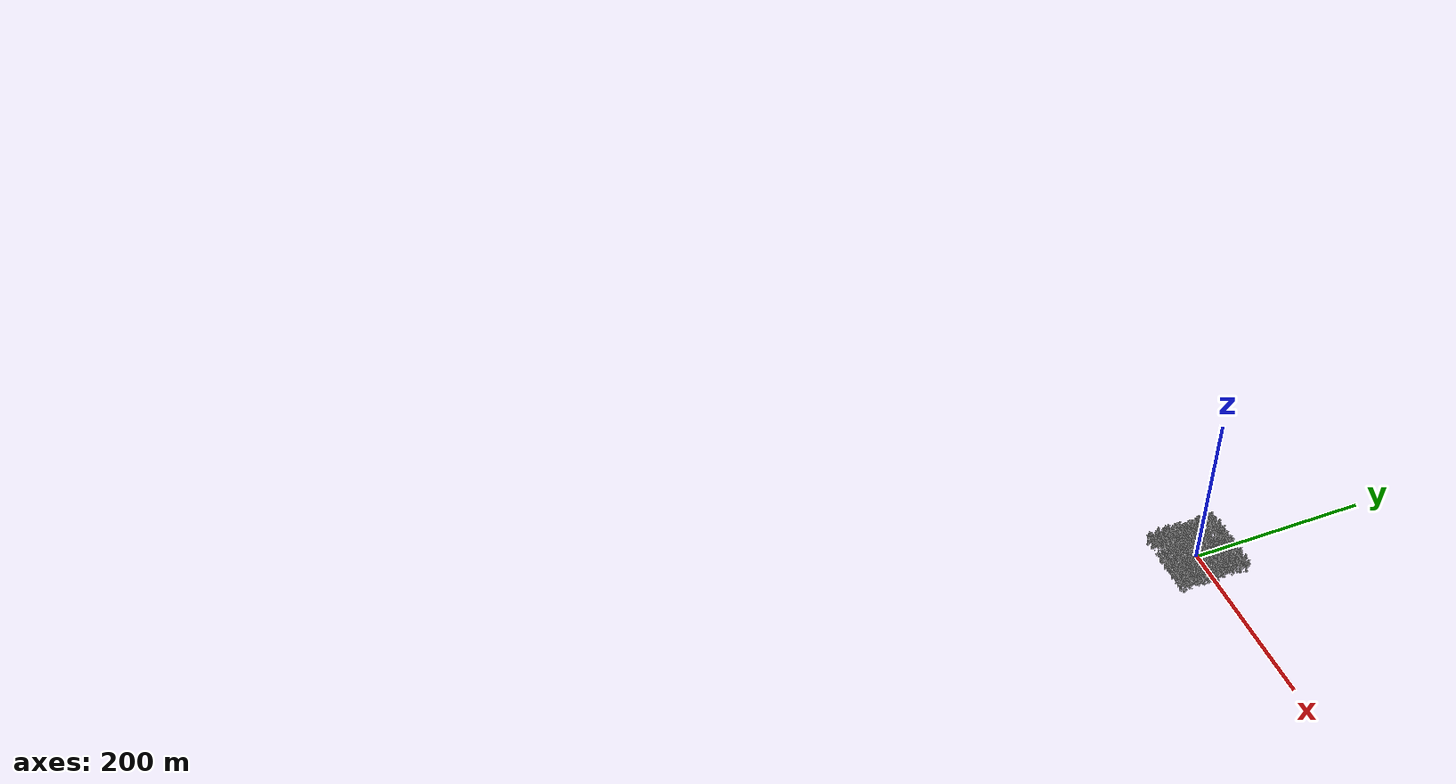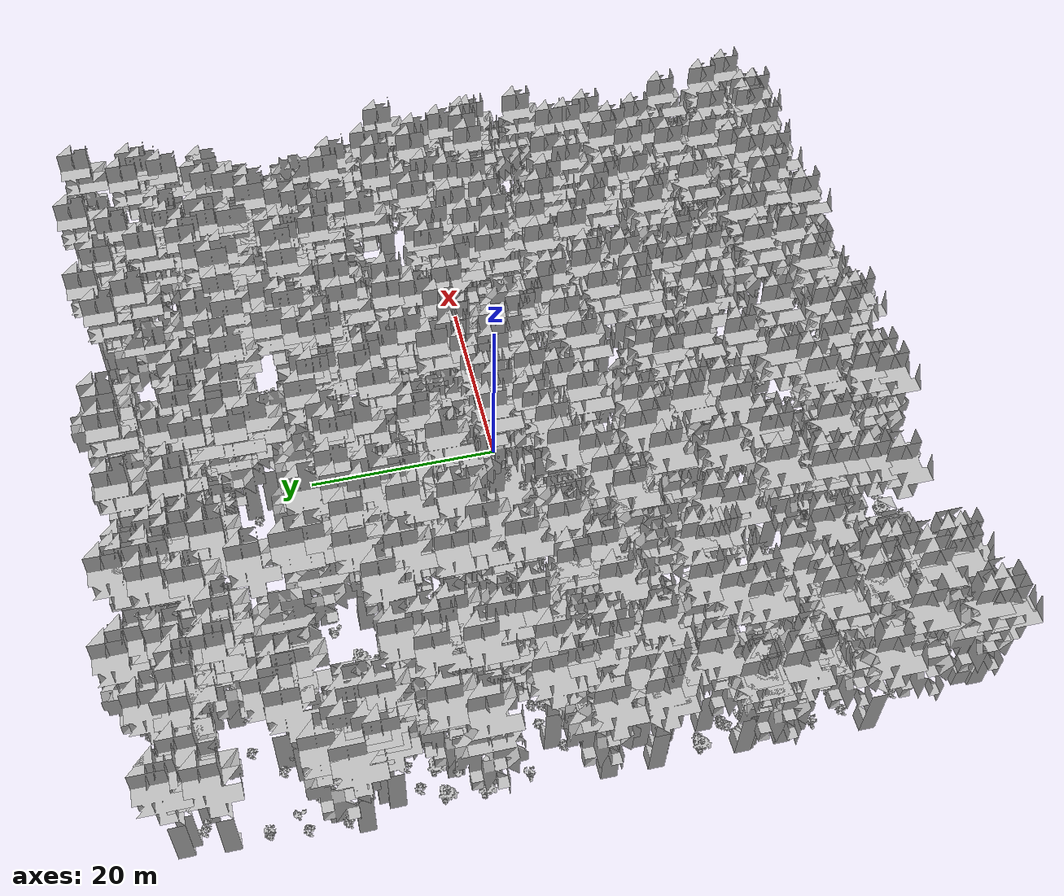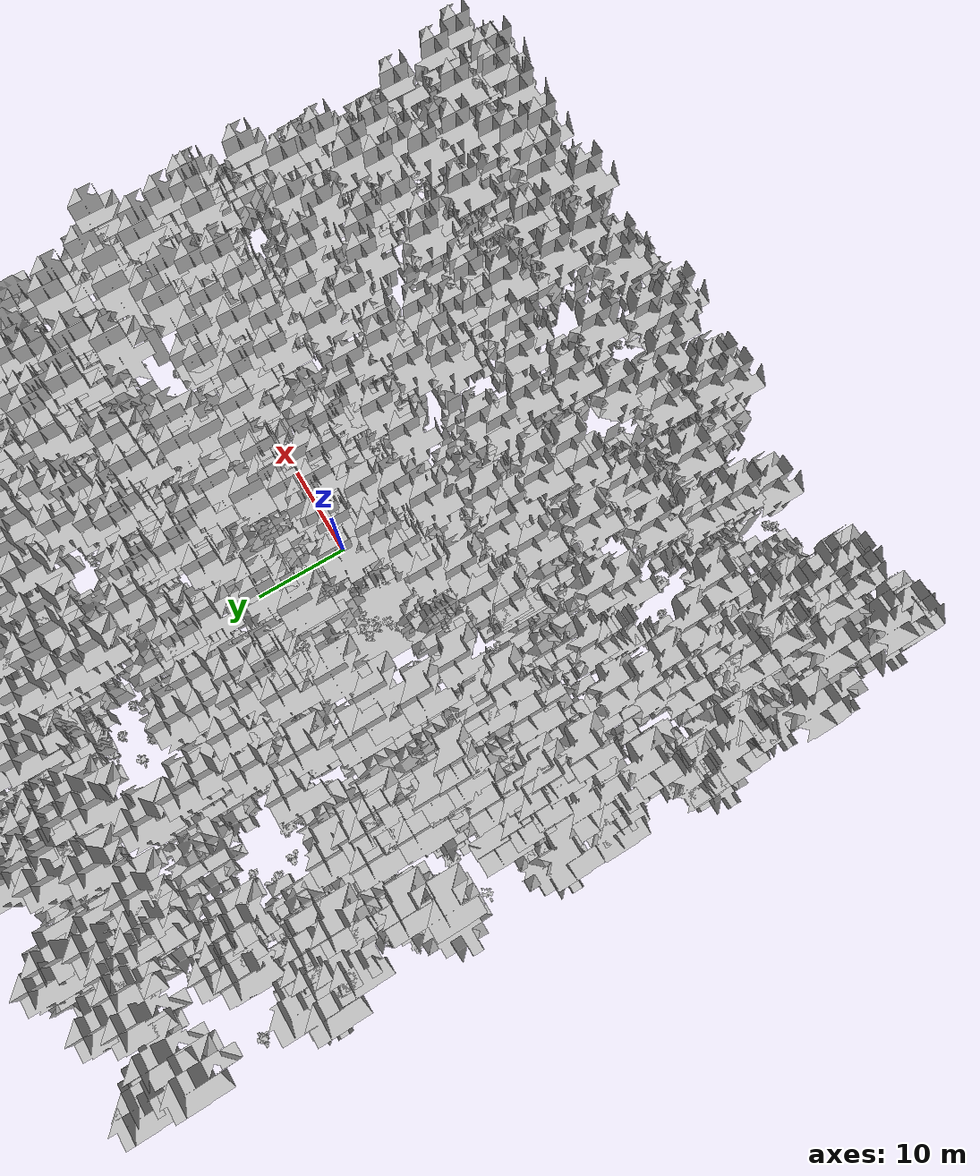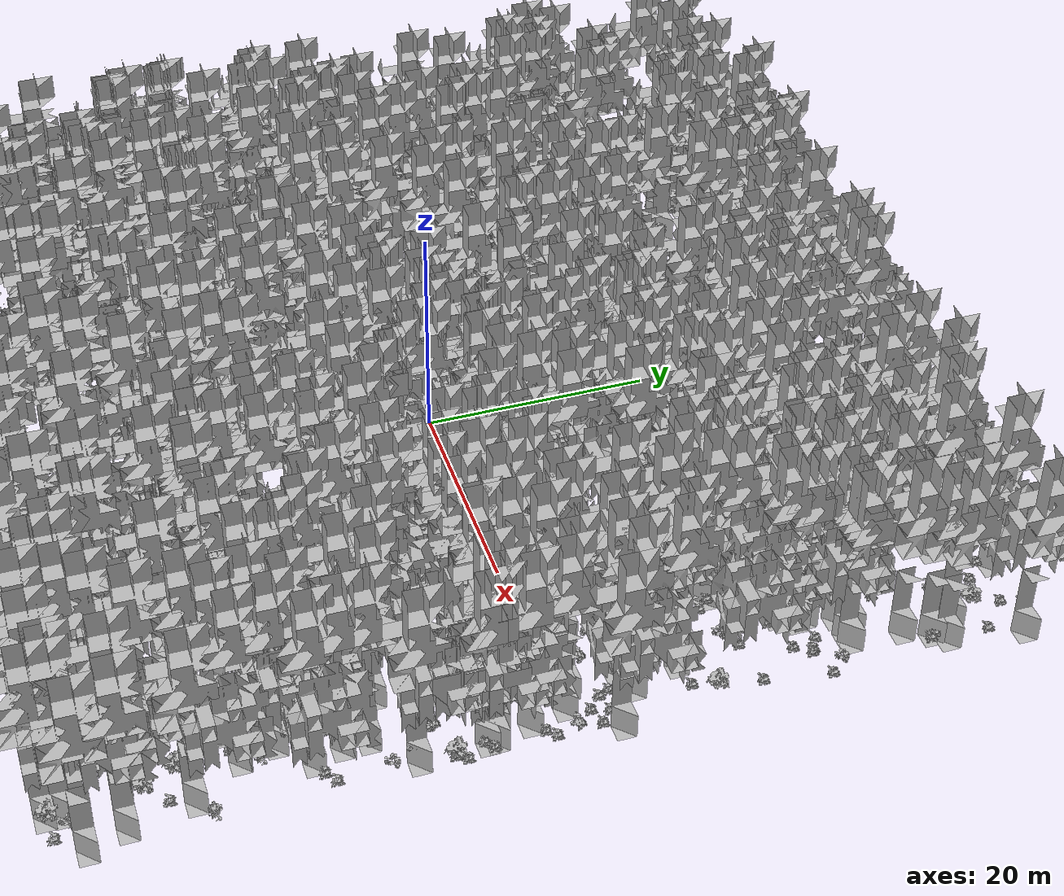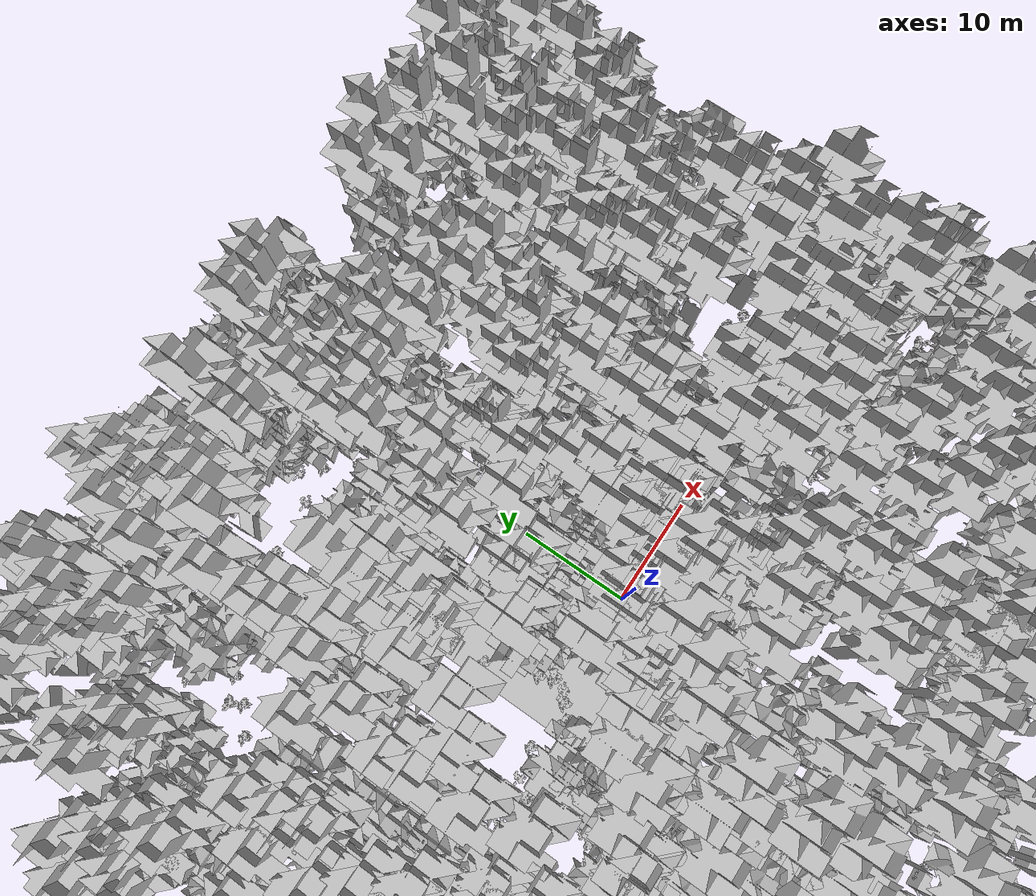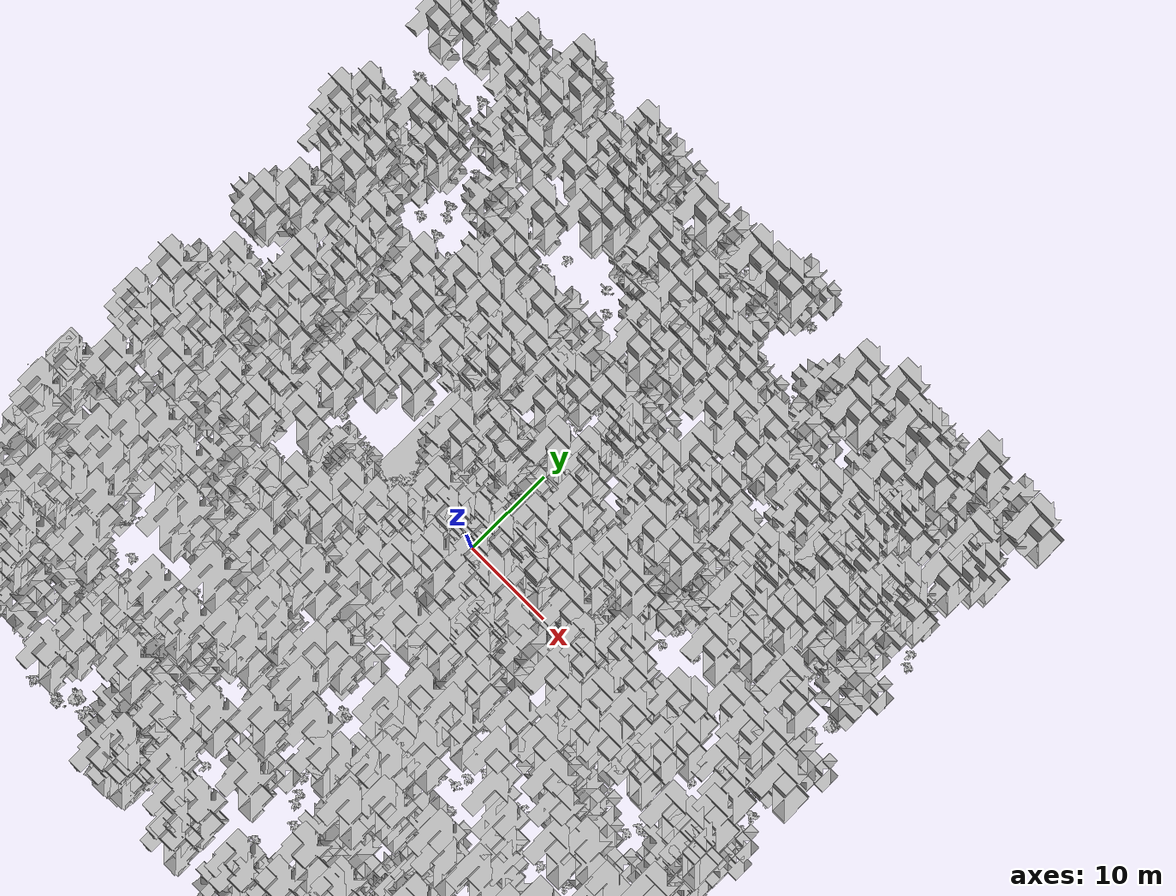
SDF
<sdf version="1.7">
    <world name="default">
        <plugin name="mrs_gazebo_static_transform_republisher_plugin" filename="libMrsGazeboCommonResources_StaticTransformRepublisher.so"/>
        <spherical_coordinates>
            <surface_model>EARTH_WGS84</surface_model>
            <latitude_deg>47.3977</latitude_deg>
            <longitude_deg>8.54559</longitude_deg>
            <elevation>0</elevation>
            <heading_deg>0</heading_deg>
        </spherical_coordinates>
        <physics name="default_physics" default="0" type="ode">
            <ode>
                <solver>
                    <type>quick</type>
                    <iters>10</iters>
                    <sor>1.3</sor>
                    <use_dynamic_moi_rescaling>0</use_dynamic_moi_rescaling>
                </solver>
                <constraints>
                    <cfm>0</cfm>
                    <erp>0.2</erp>
                    <contact_max_correcting_vel>1000</contact_max_correcting_vel>
                    <contact_surface_layer>0.001</contact_surface_layer>
                </constraints>
            </ode>
            <max_step_size>0.004</max_step_size>
            <real_time_factor>1</real_time_factor>
            <real_time_update_rate>250</real_time_update_rate>
        </physics>
        <scene>
            <shadows>0</shadows>
            <ambient>0.4 0.4 0.4 1</ambient>
            <background>0.7 0.7 0.7 1</background>
        </scene>
        <light name="sun" type="directional">
            <pose>0 0 1000 0.4 0.2 0</pose>
            <diffuse>1 1 1 1</diffuse>
            <specular>0.6 0.6 0.6 1</specular>
            <direction>0.1 0.1 -0.9</direction>
            <attenuation>
                <range>20</range>
                <constant>0.5</constant>
                <linear>0.01</linear>
                <quadratic>0.001</quadratic>
            </attenuation>
            <cast_shadows>1</cast_shadows>
            <spot>
                <inner_angle>0</inner_angle>
                <outer_angle>0</outer_angle>
                <falloff>0</falloff>
            </spot>
        </light>
        <model name="ground_plane">
            <static>1</static>
            <link name="link">
                <collision name="collision">
                    <pose>-50 0 0 0 -0 0</pose>
                    <geometry>
                        <plane>
                            <normal>0 0 1</normal>
                            <size>80 80</size>
                        </plane>
                    </geometry>
                    <surface>
                        <contact>
                            <ode>
                                <min_depth>0.01</min_depth>
                                <max_vel>0</max_vel>
                            </ode>
                        </contact>
                        <friction>
                            <ode/>
                            <torsional>
                                <ode/>
                            </torsional>
                        </friction>
                        <bounce/>
                    </surface>
                    <max_contacts>10</max_contacts>
                </collision>
                <visual name="grass">
                    <pose>0 0 0 0 -0 0</pose>
                    <cast_shadows>0</cast_shadows>
                    <geometry>
                        <mesh>
                            <scale>0.46714285714285714 0.46714285714285714 0.1</scale>
                            <uri>file://grass_plane/meshes/grass_plane.dae</uri>
                        </mesh>
                    </geometry>
                </visual>
                <self_collide>0</self_collide>
                <enable_wind>0</enable_wind>
                <kinematic>0</kinematic>
            </link>
        </model>
        <model name="the_void">
            <static>1</static>
            <link name="link">
                <pose>0 0 0.1 0 -0 0</pose>
                <visual name="the_void">
                    <pose>0 0 2 0 -0 0</pose>
                    <geometry>
                        <sphere>
                            <radius>0.25</radius>
                        </sphere>
                    </geometry>
                    <material>
                        <script>
                            <uri>file://media/materials/scripts/Gazebo.material</uri>
                            <name>Gazebo/Black</name>
                        </script>
                    </material>
                </visual>
                <self_collide>0</self_collide>
                <enable_wind>0</enable_wind>
                <kinematic>0</kinematic>
            </link>
            <pose>-1000 -1000 0 0 -0 0</pose>
        </model>
        <gui fullscreen="0">
            <camera name="camera">
                <pose>35.1577 98.6044 40.0204 0 0.407996 -1.99761</pose>
                <view_controller>orbit</view_controller>
                <projection_type>perspective</projection_type>
            </camera>
        </gui>
        <plugin name="mrs_gazebo_rviz_cam_synchronizer" filename="libMrsGazeboCommonResources_RvizCameraSynchronizer.so">
            <target_frame_id>gazebo_user_camera</target_frame_id>
            <world_origin_frame_id>uav1/gps_origin</world_origin_frame_id>
            <frame_to_follow>uav1</frame_to_follow>
        </plugin>
        <gravity>0 0 -9.8066</gravity>
        <magnetic_field>6e-06 2.3e-05 -4.2e-05</magnetic_field>
        <atmosphere type="adiabatic"/>
        <wind/>
        <model name="Tree 0">
            <static>1</static>
            <pose>26.365670534095116 -34.29726141774025 0 1.57079 -0 0</pose>
            <link name="link">
                <pose>0 0 0 0 -0 0</pose>
                <collision name="collision">
                    <geometry>
                        <mesh>
                            <scale>3.5 5 3.5</scale>
                            <uri>model://tree_9/meshes/tree_9.obj</uri>
                        </mesh>
                    </geometry>
                    <max_contacts>10</max_contacts>
                    <surface>
                        <contact>
                            <ode/>
                        </contact>
                        <bounce/>
                        <friction>
                            <torsional>
                                <ode/>
                            </torsional>
                            <ode/>
                        </friction>
                    </surface>
                </collision>
                <visual name="visual">
                    <geometry>
                        <mesh>
                            <scale>3.5 5 3.5</scale>
                            <uri>model://tree_9/meshes/tree_9.obj</uri>
                        </mesh>
                    </geometry>
                </visual>
                <self_collide>0</self_collide>
                <enable_wind>0</enable_wind>
                <kinematic>0</kinematic>
            </link>
        </model>
        <model name="Tree 1">
            <static>1</static>
            <pose>-31.45807257249799 -29.52948520579288 0 1.57079 -0 0</pose>
            <link name="link">
                <pose>0 0 0 0 -0 0</pose>
                <collision name="collision">
                    <geometry>
                        <mesh>
                            <scale>3.5 5 3.5</scale>
                            <uri>model://tree_9/meshes/tree_9.obj</uri>
                        </mesh>
                    </geometry>
                    <max_contacts>10</max_contacts>
                    <surface>
                        <contact>
                            <ode/>
                        </contact>
                        <bounce/>
                        <friction>
                            <torsional>
                                <ode/>
                            </torsional>
                            <ode/>
                        </friction>
                    </surface>
                </collision>
                <visual name="visual">
                    <geometry>
                        <mesh>
                            <scale>3.5 5 3.5</scale>
                            <uri>model://tree_9/meshes/tree_9.obj</uri>
                        </mesh>
                    </geometry>
                </visual>
                <self_collide>0</self_collide>
                <enable_wind>0</enable_wind>
                <kinematic>0</kinematic>
            </link>
        </model>
        <model name="Tree 2">
            <static>1</static>
            <pose>-32.494060860003366 -25.827922637889422 0 1.57079 -0 0</pose>
            <link name="link">
                <pose>0 0 0 0 -0 0</pose>
                <collision name="collision">
                    <geometry>
                        <mesh>
                            <scale>3.5 5 3.5</scale>
                            <uri>model://tree_2/meshes/tree_2.obj</uri>
                        </mesh>
                    </geometry>
                    <max_contacts>10</max_contacts>
                    <surface>
                        <contact>
                            <ode/>
                        </contact>
                        <bounce/>
                        <friction>
                            <torsional>
                                <ode/>
                            </torsional>
                            <ode/>
                        </friction>
                    </surface>
                </collision>
                <visual name="visual">
                    <geometry>
                        <mesh>
                            <scale>3.5 5 3.5</scale>
                            <uri>model://tree_2/meshes/tree_2.obj</uri>
                        </mesh>
                    </geometry>
                </visual>
                <self_collide>0</self_collide>
                <enable_wind>0</enable_wind>
                <kinematic>0</kinematic>
            </link>
        </model>
        <model name="Tree 3">
            <static>1</static>
            <pose>-10.805055502668331 -33.086612007821934 0 1.57079 -0 0</pose>
            <link name="link">
                <pose>0 0 0 0 -0 0</pose>
                <collision name="collision">
                    <geometry>
                        <mesh>
                            <scale>3.5 5 3.5</scale>
                            <uri>model://tree_2/meshes/tree_2.obj</uri>
                        </mesh>
                    </geometry>
                    <max_contacts>10</max_contacts>
                    <surface>
                        <contact>
                            <ode/>
                        </contact>
                        <bounce/>
                        <friction>
                            <torsional>
                                <ode/>
                            </torsional>
                            <ode/>
                        </friction>
                    </surface>
                </collision>
                <visual name="visual">
                    <geometry>
                        <mesh>
                            <scale>3.5 5 3.5</scale>
                            <uri>model://tree_2/meshes/tree_2.obj</uri>
                        </mesh>
                    </geometry>
                </visual>
                <self_collide>0</self_collide>
                <enable_wind>0</enable_wind>
                <kinematic>0</kinematic>
            </link>
        </model>
        <model name="Tree 4">
            <static>1</static>
            <pose>8.472431001688406 -39.757540110202086 0 1.57079 -0 0</pose>
            <link name="link">
                <pose>0 0 0 0 -0 0</pose>
                <collision name="collision">
                    <geometry>
                        <mesh>
                            <scale>3.5 5 3.5</scale>
                            <uri>model://tree_2/meshes/tree_2.obj</uri>
                        </mesh>
                    </geometry>
                    <max_contacts>10</max_contacts>
                    <surface>
                        <contact>
                            <ode/>
                        </contact>
                        <bounce/>
                        <friction>
                            <torsional>
                                <ode/>
                            </torsional>
                            <ode/>
                        </friction>
                    </surface>
                </collision>
                <visual name="visual">
                    <geometry>
                        <mesh>
                            <scale>3.5 5 3.5</scale>
                            <uri>model://tree_2/meshes/tree_2.obj</uri>
                        </mesh>
                    </geometry>
                </visual>
                <self_collide>0</self_collide>
                <enable_wind>0</enable_wind>
                <kinematic>0</kinematic>
            </link>
        </model>
        <model name="Tree 5">
            <static>1</static>
            <pose>-0.41526506537013574 34.02570915647311 0 1.57079 -0 0</pose>
            <link name="link">
                <pose>0 0 0 0 -0 0</pose>
                <collision name="collision">
                    <geometry>
                        <mesh>
                            <scale>3.5 5 3.5</scale>
                            <uri>model://tree_2/meshes/tree_2.obj</uri>
                        </mesh>
                    </geometry>
                    <max_contacts>10</max_contacts>
                    <surface>
                        <contact>
                            <ode/>
                        </contact>
                        <bounce/>
                        <friction>
                            <torsional>
                                <ode/>
                            </torsional>
                            <ode/>
                        </friction>
                    </surface>
                </collision>
                <visual name="visual">
                    <geometry>
                        <mesh>
                            <scale>3.5 5 3.5</scale>
                            <uri>model://tree_2/meshes/tree_2.obj</uri>
                        </mesh>
                    </geometry>
                </visual>
                <self_collide>0</self_collide>
                <enable_wind>0</enable_wind>
                <kinematic>0</kinematic>
            </link>
        </model>
        <model name="Tree 6">
            <static>1</static>
            <pose>8.923221657536914 29.702597841038795 0 1.57079 -0 0</pose>
            <link name="link">
                <pose>0 0 0 0 -0 0</pose>
                <collision name="collision">
                    <geometry>
                        <mesh>
                            <scale>3.5 5 3.5</scale>
                            <uri>model://tree_2/meshes/tree_2.obj</uri>
                        </mesh>
                    </geometry>
                    <max_contacts>10</max_contacts>
                    <surface>
                        <contact>
                            <ode/>
                        </contact>
                        <bounce/>
                        <friction>
                            <torsional>
                                <ode/>
                            </torsional>
                            <ode/>
                        </friction>
                    </surface>
                </collision>
                <visual name="visual">
                    <geometry>
                        <mesh>
                            <scale>3.5 5 3.5</scale>
                            <uri>model://tree_2/meshes/tree_2.obj</uri>
                        </mesh>
                    </geometry>
                </visual>
                <self_collide>0</self_collide>
                <enable_wind>0</enable_wind>
                <kinematic>0</kinematic>
            </link>
        </model>
        <model name="Tree 7">
            <static>1</static>
            <pose>33.64034249217025 1.6677716763315331 0 1.57079 -0 0</pose>
            <link name="link">
                <pose>0 0 0 0 -0 0</pose>
                <collision name="collision">
                    <geometry>
                        <mesh>
                            <scale>3.5 5 3.5</scale>
                            <uri>model://tree_9/meshes/tree_9.obj</uri>
                        </mesh>
                    </geometry>
                    <max_contacts>10</max_contacts>
                    <surface>
                        <contact>
                            <ode/>
                        </contact>
                        <bounce/>
                        <friction>
                            <torsional>
                                <ode/>
                            </torsional>
                            <ode/>
                        </friction>
                    </surface>
                </collision>
                <visual name="visual">
                    <geometry>
                        <mesh>
                            <scale>3.5 5 3.5</scale>
                            <uri>model://tree_9/meshes/tree_9.obj</uri>
                        </mesh>
                    </geometry>
                </visual>
                <self_collide>0</self_collide>
                <enable_wind>0</enable_wind>
                <kinematic>0</kinematic>
            </link>
        </model>
        <model name="Tree 8">
            <static>1</static>
            <pose>34.49295552566552 -38.38899228813294 0 1.57079 -0 0</pose>
            <link name="link">
                <pose>0 0 0 0 -0 0</pose>
                <collision name="collision">
                    <geometry>
                        <mesh>
                            <scale>3.5 5 3.5</scale>
                            <uri>model://tree_9/meshes/tree_9.obj</uri>
                        </mesh>
                    </geometry>
                    <max_contacts>10</max_contacts>
                    <surface>
                        <contact>
                            <ode/>
                        </contact>
                        <bounce/>
                        <friction>
                            <torsional>
                                <ode/>
                            </torsional>
                            <ode/>
                        </friction>
                    </surface>
                </collision>
                <visual name="visual">
                    <geometry>
                        <mesh>
                            <scale>3.5 5 3.5</scale>
                            <uri>model://tree_9/meshes/tree_9.obj</uri>
                        </mesh>
                    </geometry>
                </visual>
                <self_collide>0</self_collide>
                <enable_wind>0</enable_wind>
                <kinematic>0</kinematic>
            </link>
        </model>
        <model name="Tree 9">
            <static>1</static>
            <pose>-38.3239027360308 20.93960861235594 0 1.57079 -0 0</pose>
            <link name="link">
                <pose>0 0 0 0 -0 0</pose>
                <collision name="collision">
                    <geometry>
                        <mesh>
                            <scale>3.5 5 3.5</scale>
                            <uri>model://tree_9/meshes/tree_9.obj</uri>
                        </mesh>
                    </geometry>
                    <max_contacts>10</max_contacts>
                    <surface>
                        <contact>
                            <ode/>
                        </contact>
                        <bounce/>
                        <friction>
                            <torsional>
                                <ode/>
                            </torsional>
                            <ode/>
                        </friction>
                    </surface>
                </collision>
                <visual name="visual">
                    <geometry>
                        <mesh>
                            <scale>3.5 5 3.5</scale>
                            <uri>model://tree_9/meshes/tree_9.obj</uri>
                        </mesh>
                    </geometry>
                </visual>
                <self_collide>0</self_collide>
                <enable_wind>0</enable_wind>
                <kinematic>0</kinematic>
            </link>
        </model>
        <model name="Tree 10">
            <static>1</static>
            <pose>17.154413551814493 13.50864388957185 0 1.57079 -0 0</pose>
            <link name="link">
                <pose>0 0 0 0 -0 0</pose>
                <collision name="collision">
                    <geometry>
                        <mesh>
                            <scale>3.5 5 3.5</scale>
                            <uri>model://tree_2/meshes/tree_2.obj</uri>
                        </mesh>
                    </geometry>
                    <max_contacts>10</max_contacts>
                    <surface>
                        <contact>
                            <ode/>
                        </contact>
                        <bounce/>
                        <friction>
                            <torsional>
                                <ode/>
                            </torsional>
                            <ode/>
                        </friction>
                    </surface>
                </collision>
                <visual name="visual">
                    <geometry>
                        <mesh>
                            <scale>3.5 5 3.5</scale>
                            <uri>model://tree_2/meshes/tree_2.obj</uri>
                        </mesh>
                    </geometry>
                </visual>
                <self_collide>0</self_collide>
                <enable_wind>0</enable_wind>
                <kinematic>0</kinematic>
            </link>
        </model>
        <model name="Tree 11">
            <static>1</static>
            <pose>-24.177140418651046 30.63849560194413 0 1.57079 -0 0</pose>
            <link name="link">
                <pose>0 0 0 0 -0 0</pose>
                <collision name="collision">
                    <geometry>
                        <mesh>
                            <scale>3.5 5 3.5</scale>
                            <uri>model://tree_9/meshes/tree_9.obj</uri>
                        </mesh>
                    </geometry>
                    <max_contacts>10</max_contacts>
                    <surface>
                        <contact>
                            <ode/>
                        </contact>
                        <bounce/>
                        <friction>
                            <torsional>
                                <ode/>
                            </torsional>
                            <ode/>
                        </friction>
                    </surface>
                </collision>
                <visual name="visual">
                    <geometry>
                        <mesh>
                            <scale>3.5 5 3.5</scale>
                            <uri>model://tree_9/meshes/tree_9.obj</uri>
                        </mesh>
                    </geometry>
                </visual>
                <self_collide>0</self_collide>
                <enable_wind>0</enable_wind>
                <kinematic>0</kinematic>
            </link>
        </model>
        <model name="Tree 12">
            <static>1</static>
            <pose>4.03021488040568 35.9938175932882 0 1.57079 -0 0</pose>
            <link name="link">
                <pose>0 0 0 0 -0 0</pose>
                <collision name="collision">
                    <geometry>
                        <mesh>
                            <scale>3.5 5 3.5</scale>
                            <uri>model://tree_2/meshes/tree_2.obj</uri>
                        </mesh>
                    </geometry>
                    <max_contacts>10</max_contacts>
                    <surface>
                        <contact>
                            <ode/>
                        </contact>
                        <bounce/>
                        <friction>
                            <torsional>
                                <ode/>
                            </torsional>
                            <ode/>
                        </friction>
                    </surface>
                </collision>
                <visual name="visual">
                    <geometry>
                        <mesh>
                            <scale>3.5 5 3.5</scale>
                            <uri>model://tree_2/meshes/tree_2.obj</uri>
                        </mesh>
                    </geometry>
                </visual>
                <self_collide>0</self_collide>
                <enable_wind>0</enable_wind>
                <kinematic>0</kinematic>
            </link>
        </model>
        <model name="Tree 13">
            <static>1</static>
            <pose>33.340444704431576 -24.69356420575668 0 1.57079 -0 0</pose>
            <link name="link">
                <pose>0 0 0 0 -0 0</pose>
                <collision name="collision">
                    <geometry>
                        <mesh>
                            <scale>3.5 5 3.5</scale>
                            <uri>model://tree_9/meshes/tree_9.obj</uri>
                        </mesh>
                    </geometry>
                    <max_contacts>10</max_contacts>
                    <surface>
                        <contact>
                            <ode/>
                        </contact>
                        <bounce/>
                        <friction>
                            <torsional>
                                <ode/>
                            </torsional>
                            <ode/>
                        </friction>
                    </surface>
                </collision>
                <visual name="visual">
                    <geometry>
                        <mesh>
                            <scale>3.5 5 3.5</scale>
                            <uri>model://tree_9/meshes/tree_9.obj</uri>
                        </mesh>
                    </geometry>
                </visual>
                <self_collide>0</self_collide>
                <enable_wind>0</enable_wind>
                <kinematic>0</kinematic>
            </link>
        </model>
        <model name="Tree 14">
            <static>1</static>
            <pose>16.68179118057236 25.45912591755635 0 1.57079 -0 0</pose>
            <link name="link">
                <pose>0 0 0 0 -0 0</pose>
                <collision name="collision">
                    <geometry>
                        <mesh>
                            <scale>3.5 5 3.5</scale>
                            <uri>model://tree_9/meshes/tree_9.obj</uri>
                        </mesh>
                    </geometry>
                    <max_contacts>10</max_contacts>
                    <surface>
                        <contact>
                            <ode/>
                        </contact>
                        <bounce/>
                        <friction>
                            <torsional>
                                <ode/>
                            </torsional>
                            <ode/>
                        </friction>
                    </surface>
                </collision>
                <visual name="visual">
                    <geometry>
                        <mesh>
                            <scale>3.5 5 3.5</scale>
                            <uri>model://tree_9/meshes/tree_9.obj</uri>
                        </mesh>
                    </geometry>
                </visual>
                <self_collide>0</self_collide>
                <enable_wind>0</enable_wind>
                <kinematic>0</kinematic>
            </link>
        </model>
        <model name="Tree 15">
            <static>1</static>
            <pose>-27.015665207595248 12.257064036631448 0 1.57079 -0 0</pose>
            <link name="link">
                <pose>0 0 0 0 -0 0</pose>
                <collision name="collision">
                    <geometry>
                        <mesh>
                            <scale>3.5 5 3.5</scale>
                            <uri>model://tree_9/meshes/tree_9.obj</uri>
                        </mesh>
                    </geometry>
                    <max_contacts>10</max_contacts>
                    <surface>
                        <contact>
                            <ode/>
                        </contact>
                        <bounce/>
                        <friction>
                            <torsional>
                                <ode/>
                            </torsional>
                            <ode/>
                        </friction>
                    </surface>
                </collision>
                <visual name="visual">
                    <geometry>
                        <mesh>
                            <scale>3.5 5 3.5</scale>
                            <uri>model://tree_9/meshes/tree_9.obj</uri>
                        </mesh>
                    </geometry>
                </visual>
                <self_collide>0</self_collide>
                <enable_wind>0</enable_wind>
                <kinematic>0</kinematic>
            </link>
        </model>
        <model name="Tree 16">
            <static>1</static>
            <pose>12.687165125672806 -17.66942344389374 0 1.57079 -0 0</pose>
            <link name="link">
                <pose>0 0 0 0 -0 0</pose>
                <collision name="collision">
                    <geometry>
                        <mesh>
                            <scale>3.5 5 3.5</scale>
                            <uri>model://tree_9/meshes/tree_9.obj</uri>
                        </mesh>
                    </geometry>
                    <max_contacts>10</max_contacts>
                    <surface>
                        <contact>
                            <ode/>
                        </contact>
                        <bounce/>
                        <friction>
                            <torsional>
                                <ode/>
                            </torsional>
                            <ode/>
                        </friction>
                    </surface>
                </collision>
                <visual name="visual">
                    <geometry>
                        <mesh>
                            <scale>3.5 5 3.5</scale>
                            <uri>model://tree_9/meshes/tree_9.obj</uri>
                        </mesh>
                    </geometry>
                </visual>
                <self_collide>0</self_collide>
                <enable_wind>0</enable_wind>
                <kinematic>0</kinematic>
            </link>
        </model>
        <model name="Tree 17">
            <static>1</static>
            <pose>-29.317461129962243 -29.995892954941937 0 1.57079 -0 0</pose>
            <link name="link">
                <pose>0 0 0 0 -0 0</pose>
                <collision name="collision">
                    <geometry>
                        <mesh>
                            <scale>3.5 5 3.5</scale>
                            <uri>model://tree_9/meshes/tree_9.obj</uri>
                        </mesh>
                    </geometry>
                    <max_contacts>10</max_contacts>
                    <surface>
                        <contact>
                            <ode/>
                        </contact>
                        <bounce/>
                        <friction>
                            <torsional>
                                <ode/>
                            </torsional>
                            <ode/>
                        </friction>
                    </surface>
                </collision>
                <visual name="visual">
                    <geometry>
                        <mesh>
                            <scale>3.5 5 3.5</scale>
                            <uri>model://tree_9/meshes/tree_9.obj</uri>
                        </mesh>
                    </geometry>
                </visual>
                <self_collide>0</self_collide>
                <enable_wind>0</enable_wind>
                <kinematic>0</kinematic>
            </link>
        </model>
        <model name="Tree 18">
            <static>1</static>
            <pose>-14.065529169427268 35.52857261855051 0 1.57079 -0 0</pose>
            <link name="link">
                <pose>0 0 0 0 -0 0</pose>
                <collision name="collision">
                    <geometry>
                        <mesh>
                            <scale>3.5 5 3.5</scale>
                            <uri>model://tree_9/meshes/tree_9.obj</uri>
                        </mesh>
                    </geometry>
                    <max_contacts>10</max_contacts>
                    <surface>
                        <contact>
                            <ode/>
                        </contact>
                        <bounce/>
                        <friction>
                            <torsional>
                                <ode/>
                            </torsional>
                            <ode/>
                        </friction>
                    </surface>
                </collision>
                <visual name="visual">
                    <geometry>
                        <mesh>
                            <scale>3.5 5 3.5</scale>
                            <uri>model://tree_9/meshes/tree_9.obj</uri>
                        </mesh>
                    </geometry>
                </visual>
                <self_collide>0</self_collide>
                <enable_wind>0</enable_wind>
                <kinematic>0</kinematic>
            </link>
        </model>
        <model name="Tree 19">
            <static>1</static>
            <pose>-12.095675173574161 -24.86207846785586 0 1.57079 -0 0</pose>
            <link name="link">
                <pose>0 0 0 0 -0 0</pose>
                <collision name="collision">
                    <geometry>
                        <mesh>
                            <scale>3.5 5 3.5</scale>
                            <uri>model://tree_9/meshes/tree_9.obj</uri>
                        </mesh>
                    </geometry>
                    <max_contacts>10</max_contacts>
                    <surface>
                        <contact>
                            <ode/>
                        </contact>
                        <bounce/>
                        <friction>
                            <torsional>
                                <ode/>
                            </torsional>
                            <ode/>
                        </friction>
                    </surface>
                </collision>
                <visual name="visual">
                    <geometry>
                        <mesh>
                            <scale>3.5 5 3.5</scale>
                            <uri>model://tree_9/meshes/tree_9.obj</uri>
                        </mesh>
                    </geometry>
                </visual>
                <self_collide>0</self_collide>
                <enable_wind>0</enable_wind>
                <kinematic>0</kinematic>
            </link>
        </model>
        <model name="Tree 20">
            <static>1</static>
            <pose>33.00172199247376 -33.87744943451156 0 1.57079 -0 0</pose>
            <link name="link">
                <pose>0 0 0 0 -0 0</pose>
                <collision name="collision">
                    <geometry>
                        <mesh>
                            <scale>3.5 5 3.5</scale>
                            <uri>model://tree_9/meshes/tree_9.obj</uri>
                        </mesh>
                    </geometry>
                    <max_contacts>10</max_contacts>
                    <surface>
                        <contact>
                            <ode/>
                        </contact>
                        <bounce/>
                        <friction>
                            <torsional>
                                <ode/>
                            </torsional>
                            <ode/>
                        </friction>
                    </surface>
                </collision>
                <visual name="visual">
                    <geometry>
                        <mesh>
                            <scale>3.5 5 3.5</scale>
                            <uri>model://tree_9/meshes/tree_9.obj</uri>
                        </mesh>
                    </geometry>
                </visual>
                <self_collide>0</self_collide>
                <enable_wind>0</enable_wind>
                <kinematic>0</kinematic>
            </link>
        </model>
        <model name="Tree 21">
            <static>1</static>
            <pose>16.32397467566996 38.04657078339079 0 1.57079 -0 0</pose>
            <link name="link">
                <pose>0 0 0 0 -0 0</pose>
                <collision name="collision">
                    <geometry>
                        <mesh>
                            <scale>3.5 5 3.5</scale>
                            <uri>model://tree_9/meshes/tree_9.obj</uri>
                        </mesh>
                    </geometry>
                    <max_contacts>10</max_contacts>
                    <surface>
                        <contact>
                            <ode/>
                        </contact>
                        <bounce/>
                        <friction>
                            <torsional>
                                <ode/>
                            </torsional>
                            <ode/>
                        </friction>
                    </surface>
                </collision>
                <visual name="visual">
                    <geometry>
                        <mesh>
                            <scale>3.5 5 3.5</scale>
                            <uri>model://tree_9/meshes/tree_9.obj</uri>
                        </mesh>
                    </geometry>
                </visual>
                <self_collide>0</self_collide>
                <enable_wind>0</enable_wind>
                <kinematic>0</kinematic>
            </link>
        </model>
        <model name="Tree 22">
            <static>1</static>
            <pose>24.61093063910306 -22.099798573518363 0 1.57079 -0 0</pose>
            <link name="link">
                <pose>0 0 0 0 -0 0</pose>
                <collision name="collision">
                    <geometry>
                        <mesh>
                            <scale>3.5 5 3.5</scale>
                            <uri>model://tree_9/meshes/tree_9.obj</uri>
                        </mesh>
                    </geometry>
                    <max_contacts>10</max_contacts>
                    <surface>
                        <contact>
                            <ode/>
                        </contact>
                        <bounce/>
                        <friction>
                            <torsional>
                                <ode/>
                            </torsional>
                            <ode/>
                        </friction>
                    </surface>
                </collision>
                <visual name="visual">
                    <geometry>
                        <mesh>
                            <scale>3.5 5 3.5</scale>
                            <uri>model://tree_9/meshes/tree_9.obj</uri>
                        </mesh>
                    </geometry>
                </visual>
                <self_collide>0</self_collide>
                <enable_wind>0</enable_wind>
                <kinematic>0</kinematic>
            </link>
        </model>
        <model name="Tree 23">
            <static>1</static>
            <pose>29.883063627734813 6.254103521265762 0 1.57079 -0 0</pose>
            <link name="link">
                <pose>0 0 0 0 -0 0</pose>
                <collision name="collision">
                    <geometry>
                        <mesh>
                            <scale>3.5 5 3.5</scale>
                            <uri>model://tree_9/meshes/tree_9.obj</uri>
                        </mesh>
                    </geometry>
                    <max_contacts>10</max_contacts>
                    <surface>
                        <contact>
                            <ode/>
                        </contact>
                        <bounce/>
                        <friction>
                            <torsional>
                                <ode/>
                            </torsional>
                            <ode/>
                        </friction>
                    </surface>
                </collision>
                <visual name="visual">
                    <geometry>
                        <mesh>
                            <scale>3.5 5 3.5</scale>
                            <uri>model://tree_9/meshes/tree_9.obj</uri>
                        </mesh>
                    </geometry>
                </visual>
                <self_collide>0</self_collide>
                <enable_wind>0</enable_wind>
                <kinematic>0</kinematic>
            </link>
        </model>
        <model name="Tree 24">
            <static>1</static>
            <pose>26.611422265160584 22.981951320968427 0 1.57079 -0 0</pose>
            <link name="link">
                <pose>0 0 0 0 -0 0</pose>
                <collision name="collision">
                    <geometry>
                        <mesh>
                            <scale>3.5 5 3.5</scale>
                            <uri>model://tree_9/meshes/tree_9.obj</uri>
                        </mesh>
                    </geometry>
                    <max_contacts>10</max_contacts>
                    <surface>
                        <contact>
                            <ode/>
                        </contact>
                        <bounce/>
                        <friction>
                            <torsional>
                                <ode/>
                            </torsional>
                            <ode/>
                        </friction>
                    </surface>
                </collision>
                <visual name="visual">
                    <geometry>
                        <mesh>
                            <scale>3.5 5 3.5</scale>
                            <uri>model://tree_9/meshes/tree_9.obj</uri>
                        </mesh>
                    </geometry>
                </visual>
                <self_collide>0</self_collide>
                <enable_wind>0</enable_wind>
                <kinematic>0</kinematic>
            </link>
        </model>
        <model name="Tree 25">
            <static>1</static>
            <pose>6.683372316830962 28.8465129016994 0 1.57079 -0 0</pose>
            <link name="link">
                <pose>0 0 0 0 -0 0</pose>
                <collision name="collision">
                    <geometry>
                        <mesh>
                            <scale>3.5 5 3.5</scale>
                            <uri>model://tree_9/meshes/tree_9.obj</uri>
                        </mesh>
                    </geometry>
                    <max_contacts>10</max_contacts>
                    <surface>
                        <contact>
                            <ode/>
                        </contact>
                        <bounce/>
                        <friction>
                            <torsional>
                                <ode/>
                            </torsional>
                            <ode/>
                        </friction>
                    </surface>
                </collision>
                <visual name="visual">
                    <geometry>
                        <mesh>
                            <scale>3.5 5 3.5</scale>
                            <uri>model://tree_9/meshes/tree_9.obj</uri>
                        </mesh>
                    </geometry>
                </visual>
                <self_collide>0</self_collide>
                <enable_wind>0</enable_wind>
                <kinematic>0</kinematic>
            </link>
        </model>
        <model name="Tree 26">
            <static>1</static>
            <pose>0.0009870731061454308 -16.82924910509592 0 1.57079 -0 0</pose>
            <link name="link">
                <pose>0 0 0 0 -0 0</pose>
                <collision name="collision">
                    <geometry>
                        <mesh>
                            <scale>3.5 5 3.5</scale>
                            <uri>model://tree_9/meshes/tree_9.obj</uri>
                        </mesh>
                    </geometry>
                    <max_contacts>10</max_contacts>
                    <surface>
                        <contact>
                            <ode/>
                        </contact>
                        <bounce/>
                        <friction>
                            <torsional>
                                <ode/>
                            </torsional>
                            <ode/>
                        </friction>
                    </surface>
                </collision>
                <visual name="visual">
                    <geometry>
                        <mesh>
                            <scale>3.5 5 3.5</scale>
                            <uri>model://tree_9/meshes/tree_9.obj</uri>
                        </mesh>
                    </geometry>
                </visual>
                <self_collide>0</self_collide>
                <enable_wind>0</enable_wind>
                <kinematic>0</kinematic>
            </link>
        </model>
        <model name="Tree 27">
            <static>1</static>
            <pose>28.617233264011674 26.331359955296293 0 1.57079 -0 0</pose>
            <link name="link">
                <pose>0 0 0 0 -0 0</pose>
                <collision name="collision">
                    <geometry>
                        <mesh>
                            <scale>3.5 5 3.5</scale>
                            <uri>model://tree_2/meshes/tree_2.obj</uri>
                        </mesh>
                    </geometry>
                    <max_contacts>10</max_contacts>
                    <surface>
                        <contact>
                            <ode/>
                        </contact>
                        <bounce/>
                        <friction>
                            <torsional>
                                <ode/>
                            </torsional>
                            <ode/>
                        </friction>
                    </surface>
                </collision>
                <visual name="visual">
                    <geometry>
                        <mesh>
                            <scale>3.5 5 3.5</scale>
                            <uri>model://tree_2/meshes/tree_2.obj</uri>
                        </mesh>
                    </geometry>
                </visual>
                <self_collide>0</self_collide>
                <enable_wind>0</enable_wind>
                <kinematic>0</kinematic>
            </link>
        </model>
        <model name="Tree 28">
            <static>1</static>
            <pose>-0.35004795752335127 -24.8608026252684 0 1.57079 -0 0</pose>
            <link name="link">
                <pose>0 0 0 0 -0 0</pose>
                <collision name="collision">
                    <geometry>
                        <mesh>
                            <scale>3.5 5 3.5</scale>
                            <uri>model://tree_2/meshes/tree_2.obj</uri>
                        </mesh>
                    </geometry>
                    <max_contacts>10</max_contacts>
                    <surface>
                        <contact>
                            <ode/>
                        </contact>
                        <bounce/>
                        <friction>
                            <torsional>
                                <ode/>
                            </torsional>
                            <ode/>
                        </friction>
                    </surface>
                </collision>
                <visual name="visual">
                    <geometry>
                        <mesh>
                            <scale>3.5 5 3.5</scale>
                            <uri>model://tree_2/meshes/tree_2.obj</uri>
                        </mesh>
                    </geometry>
                </visual>
                <self_collide>0</self_collide>
                <enable_wind>0</enable_wind>
                <kinematic>0</kinematic>
            </link>
        </model>
        <model name="Tree 29">
            <static>1</static>
            <pose>-9.650099225007278 14.123276848288981 0 1.57079 -0 0</pose>
            <link name="link">
                <pose>0 0 0 0 -0 0</pose>
                <collision name="collision">
                    <geometry>
                        <mesh>
                            <scale>3.5 5 3.5</scale>
                            <uri>model://tree_9/meshes/tree_9.obj</uri>
                        </mesh>
                    </geometry>
                    <max_contacts>10</max_contacts>
                    <surface>
                        <contact>
                            <ode/>
                        </contact>
                        <bounce/>
                        <friction>
                            <torsional>
                                <ode/>
                            </torsional>
                            <ode/>
                        </friction>
                    </surface>
                </collision>
                <visual name="visual">
                    <geometry>
                        <mesh>
                            <scale>3.5 5 3.5</scale>
                            <uri>model://tree_9/meshes/tree_9.obj</uri>
                        </mesh>
                    </geometry>
                </visual>
                <self_collide>0</self_collide>
                <enable_wind>0</enable_wind>
                <kinematic>0</kinematic>
            </link>
        </model>
        <model name="Tree 30">
            <static>1</static>
            <pose>21.31681991078463 0.924486611022445 0 1.57079 -0 0</pose>
            <link name="link">
                <pose>0 0 0 0 -0 0</pose>
                <collision name="collision">
                    <geometry>
                        <mesh>
                            <scale>3.5 5 3.5</scale>
                            <uri>model://tree_2/meshes/tree_2.obj</uri>
                        </mesh>
                    </geometry>
                    <max_contacts>10</max_contacts>
                    <surface>
                        <contact>
                            <ode/>
                        </contact>
                        <bounce/>
                        <friction>
                            <torsional>
                                <ode/>
                            </torsional>
                            <ode/>
                        </friction>
                    </surface>
                </collision>
                <visual name="visual">
                    <geometry>
                        <mesh>
                            <scale>3.5 5 3.5</scale>
                            <uri>model://tree_2/meshes/tree_2.obj</uri>
                        </mesh>
                    </geometry>
                </visual>
                <self_collide>0</self_collide>
                <enable_wind>0</enable_wind>
                <kinematic>0</kinematic>
            </link>
        </model>
        <model name="Tree 31">
            <static>1</static>
            <pose>-6.870779393974125 5.24699856919311 0 1.57079 -0 0</pose>
            <link name="link">
                <pose>0 0 0 0 -0 0</pose>
                <collision name="collision">
                    <geometry>
                        <mesh>
                            <scale>3.5 5 3.5</scale>
                            <uri>model://tree_2/meshes/tree_2.obj</uri>
                        </mesh>
                    </geometry>
                    <max_contacts>10</max_contacts>
                    <surface>
                        <contact>
                            <ode/>
                        </contact>
                        <bounce/>
                        <friction>
                            <torsional>
                                <ode/>
                            </torsional>
                            <ode/>
                        </friction>
                    </surface>
                </collision>
                <visual name="visual">
                    <geometry>
                        <mesh>
                            <scale>3.5 5 3.5</scale>
                            <uri>model://tree_2/meshes/tree_2.obj</uri>
                        </mesh>
                    </geometry>
                </visual>
                <self_collide>0</self_collide>
                <enable_wind>0</enable_wind>
                <kinematic>0</kinematic>
            </link>
        </model>
        <model name="Tree 32">
            <static>1</static>
            <pose>-25.14496976167465 33.52937645445756 0 1.57079 -0 0</pose>
            <link name="link">
                <pose>0 0 0 0 -0 0</pose>
                <collision name="collision">
                    <geometry>
                        <mesh>
                            <scale>3.5 5 3.5</scale>
                            <uri>model://tree_9/meshes/tree_9.obj</uri>
                        </mesh>
                    </geometry>
                    <max_contacts>10</max_contacts>
                    <surface>
                        <contact>
                            <ode/>
                        </contact>
                        <bounce/>
                        <friction>
                            <torsional>
                                <ode/>
                            </torsional>
                            <ode/>
                        </friction>
                    </surface>
                </collision>
                <visual name="visual">
                    <geometry>
                        <mesh>
                            <scale>3.5 5 3.5</scale>
                            <uri>model://tree_9/meshes/tree_9.obj</uri>
                        </mesh>
                    </geometry>
                </visual>
                <self_collide>0</self_collide>
                <enable_wind>0</enable_wind>
                <kinematic>0</kinematic>
            </link>
        </model>
        <model name="Tree 33">
            <static>1</static>
            <pose>34.66525819187517 -20.876958603733257 0 1.57079 -0 0</pose>
            <link name="link">
                <pose>0 0 0 0 -0 0</pose>
                <collision name="collision">
                    <geometry>
                        <mesh>
                            <scale>3.5 5 3.5</scale>
                            <uri>model://tree_2/meshes/tree_2.obj</uri>
                        </mesh>
                    </geometry>
                    <max_contacts>10</max_contacts>
                    <surface>
                        <contact>
                            <ode/>
                        </contact>
                        <bounce/>
                        <friction>
                            <torsional>
                                <ode/>
                            </torsional>
                            <ode/>
                        </friction>
                    </surface>
                </collision>
                <visual name="visual">
                    <geometry>
                        <mesh>
                            <scale>3.5 5 3.5</scale>
                            <uri>model://tree_2/meshes/tree_2.obj</uri>
                        </mesh>
                    </geometry>
                </visual>
                <self_collide>0</self_collide>
                <enable_wind>0</enable_wind>
                <kinematic>0</kinematic>
            </link>
        </model>
        <model name="Tree 34">
            <static>1</static>
            <pose>15.75394999544745 0.29198959973918903 0 1.57079 -0 0</pose>
            <link name="link">
                <pose>0 0 0 0 -0 0</pose>
                <collision name="collision">
                    <geometry>
                        <mesh>
                            <scale>3.5 5 3.5</scale>
                            <uri>model://tree_9/meshes/tree_9.obj</uri>
                        </mesh>
                    </geometry>
                    <max_contacts>10</max_contacts>
                    <surface>
                        <contact>
                            <ode/>
                        </contact>
                        <bounce/>
                        <friction>
                            <torsional>
                                <ode/>
                            </torsional>
                            <ode/>
                        </friction>
                    </surface>
                </collision>
                <visual name="visual">
                    <geometry>
                        <mesh>
                            <scale>3.5 5 3.5</scale>
                            <uri>model://tree_9/meshes/tree_9.obj</uri>
                        </mesh>
                    </geometry>
                </visual>
                <self_collide>0</self_collide>
                <enable_wind>0</enable_wind>
                <kinematic>0</kinematic>
            </link>
        </model>
        <model name="Tree 35">
            <static>1</static>
            <pose>-9.594605800499885 -26.206955455587106 0 1.57079 -0 0</pose>
            <link name="link">
                <pose>0 0 0 0 -0 0</pose>
                <collision name="collision">
                    <geometry>
                        <mesh>
                            <scale>3.5 5 3.5</scale>
                            <uri>model://tree_2/meshes/tree_2.obj</uri>
                        </mesh>
                    </geometry>
                    <max_contacts>10</max_contacts>
                    <surface>
                        <contact>
                            <ode/>
                        </contact>
                        <bounce/>
                        <friction>
                            <torsional>
                                <ode/>
                            </torsional>
                            <ode/>
                        </friction>
                    </surface>
                </collision>
                <visual name="visual">
                    <geometry>
                        <mesh>
                            <scale>3.5 5 3.5</scale>
                            <uri>model://tree_2/meshes/tree_2.obj</uri>
                        </mesh>
                    </geometry>
                </visual>
                <self_collide>0</self_collide>
                <enable_wind>0</enable_wind>
                <kinematic>0</kinematic>
            </link>
        </model>
        <model name="Tree 36">
            <static>1</static>
            <pose>-15.152335132241337 39.67727176170672 0 1.57079 -0 0</pose>
            <link name="link">
                <pose>0 0 0 0 -0 0</pose>
                <collision name="collision">
                    <geometry>
                        <mesh>
                            <scale>3.5 5 3.5</scale>
                            <uri>model://tree_9/meshes/tree_9.obj</uri>
                        </mesh>
                    </geometry>
                    <max_contacts>10</max_contacts>
                    <surface>
                        <contact>
                            <ode/>
                        </contact>
                        <bounce/>
                        <friction>
                            <torsional>
                                <ode/>
                            </torsional>
                            <ode/>
                        </friction>
                    </surface>
                </collision>
                <visual name="visual">
                    <geometry>
                        <mesh>
                            <scale>3.5 5 3.5</scale>
                            <uri>model://tree_9/meshes/tree_9.obj</uri>
                        </mesh>
                    </geometry>
                </visual>
                <self_collide>0</self_collide>
                <enable_wind>0</enable_wind>
                <kinematic>0</kinematic>
            </link>
        </model>
        <model name="Tree 37">
            <static>1</static>
            <pose>24.551823431876542 -38.94281338013918 0 1.57079 -0 0</pose>
            <link name="link">
                <pose>0 0 0 0 -0 0</pose>
                <collision name="collision">
                    <geometry>
                        <mesh>
                            <scale>3.5 5 3.5</scale>
                            <uri>model://tree_9/meshes/tree_9.obj</uri>
                        </mesh>
                    </geometry>
                    <max_contacts>10</max_contacts>
                    <surface>
                        <contact>
                            <ode/>
                        </contact>
                        <bounce/>
                        <friction>
                            <torsional>
                                <ode/>
                            </torsional>
                            <ode/>
                        </friction>
                    </surface>
                </collision>
                <visual name="visual">
                    <geometry>
                        <mesh>
                            <scale>3.5 5 3.5</scale>
                            <uri>model://tree_9/meshes/tree_9.obj</uri>
                        </mesh>
                    </geometry>
                </visual>
                <self_collide>0</self_collide>
                <enable_wind>0</enable_wind>
                <kinematic>0</kinematic>
            </link>
        </model>
        <model name="Tree 38">
            <static>1</static>
            <pose>-31.723911646700447 20.76167850287643 0 1.57079 -0 0</pose>
            <link name="link">
                <pose>0 0 0 0 -0 0</pose>
                <collision name="collision">
                    <geometry>
                        <mesh>
                            <scale>3.5 5 3.5</scale>
                            <uri>model://tree_2/meshes/tree_2.obj</uri>
                        </mesh>
                    </geometry>
                    <max_contacts>10</max_contacts>
                    <surface>
                        <contact>
                            <ode/>
                        </contact>
                        <bounce/>
                        <friction>
                            <torsional>
                                <ode/>
                            </torsional>
                            <ode/>
                        </friction>
                    </surface>
                </collision>
                <visual name="visual">
                    <geometry>
                        <mesh>
                            <scale>3.5 5 3.5</scale>
                            <uri>model://tree_2/meshes/tree_2.obj</uri>
                        </mesh>
                    </geometry>
                </visual>
                <self_collide>0</self_collide>
                <enable_wind>0</enable_wind>
                <kinematic>0</kinematic>
            </link>
        </model>
        <model name="Tree 39">
            <static>1</static>
            <pose>8.346822367280659 25.650467886863225 0 1.57079 -0 0</pose>
            <link name="link">
                <pose>0 0 0 0 -0 0</pose>
                <collision name="collision">
                    <geometry>
                        <mesh>
                            <scale>3.5 5 3.5</scale>
                            <uri>model://tree_9/meshes/tree_9.obj</uri>
                        </mesh>
                    </geometry>
                    <max_contacts>10</max_contacts>
                    <surface>
                        <contact>
                            <ode/>
                        </contact>
                        <bounce/>
                        <friction>
                            <torsional>
                                <ode/>
                            </torsional>
                            <ode/>
                        </friction>
                    </surface>
                </collision>
                <visual name="visual">
                    <geometry>
                        <mesh>
                            <scale>3.5 5 3.5</scale>
                            <uri>model://tree_9/meshes/tree_9.obj</uri>
                        </mesh>
                    </geometry>
                </visual>
                <self_collide>0</self_collide>
                <enable_wind>0</enable_wind>
                <kinematic>0</kinematic>
            </link>
        </model>
        <model name="Tree 40">
            <static>1</static>
            <pose>-19.756055770321694 -17.589001052693725 0 1.57079 -0 0</pose>
            <link name="link">
                <pose>0 0 0 0 -0 0</pose>
                <collision name="collision">
                    <geometry>
                        <mesh>
                            <scale>3.5 5 3.5</scale>
                            <uri>model://tree_9/meshes/tree_9.obj</uri>
                        </mesh>
                    </geometry>
                    <max_contacts>10</max_contacts>
                    <surface>
                        <contact>
                            <ode/>
                        </contact>
                        <bounce/>
                        <friction>
                            <torsional>
                                <ode/>
                            </torsional>
                            <ode/>
                        </friction>
                    </surface>
                </collision>
                <visual name="visual">
                    <geometry>
                        <mesh>
                            <scale>3.5 5 3.5</scale>
                            <uri>model://tree_9/meshes/tree_9.obj</uri>
                        </mesh>
                    </geometry>
                </visual>
                <self_collide>0</self_collide>
                <enable_wind>0</enable_wind>
                <kinematic>0</kinematic>
            </link>
        </model>
        <model name="Tree 41">
            <static>1</static>
            <pose>30.76993368702483 17.887368886473645 0 1.57079 -0 0</pose>
            <link name="link">
                <pose>0 0 0 0 -0 0</pose>
                <collision name="collision">
                    <geometry>
                        <mesh>
                            <scale>3.5 5 3.5</scale>
                            <uri>model://tree_2/meshes/tree_2.obj</uri>
                        </mesh>
                    </geometry>
                    <max_contacts>10</max_contacts>
                    <surface>
                        <contact>
                            <ode/>
                        </contact>
                        <bounce/>
                        <friction>
                            <torsional>
                                <ode/>
                            </torsional>
                            <ode/>
                        </friction>
                    </surface>
                </collision>
                <visual name="visual">
                    <geometry>
                        <mesh>
                            <scale>3.5 5 3.5</scale>
                            <uri>model://tree_2/meshes/tree_2.obj</uri>
                        </mesh>
                    </geometry>
                </visual>
                <self_collide>0</self_collide>
                <enable_wind>0</enable_wind>
                <kinematic>0</kinematic>
            </link>
        </model>
        <model name="Tree 42">
            <static>1</static>
            <pose>13.17192888474083 24.93482480410779 0 1.57079 -0 0</pose>
            <link name="link">
                <pose>0 0 0 0 -0 0</pose>
                <collision name="collision">
                    <geometry>
                        <mesh>
                            <scale>3.5 5 3.5</scale>
                            <uri>model://tree_9/meshes/tree_9.obj</uri>
                        </mesh>
                    </geometry>
                    <max_contacts>10</max_contacts>
                    <surface>
                        <contact>
                            <ode/>
                        </contact>
                        <bounce/>
                        <friction>
                            <torsional>
                                <ode/>
                            </torsional>
                            <ode/>
                        </friction>
                    </surface>
                </collision>
                <visual name="visual">
                    <geometry>
                        <mesh>
                            <scale>3.5 5 3.5</scale>
                            <uri>model://tree_9/meshes/tree_9.obj</uri>
                        </mesh>
                    </geometry>
                </visual>
                <self_collide>0</self_collide>
                <enable_wind>0</enable_wind>
                <kinematic>0</kinematic>
            </link>
        </model>
        <model name="Tree 43">
            <static>1</static>
            <pose>-2.1944842995636407 38.42907541145051 0 1.57079 -0 0</pose>
            <link name="link">
                <pose>0 0 0 0 -0 0</pose>
                <collision name="collision">
                    <geometry>
                        <mesh>
                            <scale>3.5 5 3.5</scale>
                            <uri>model://tree_2/meshes/tree_2.obj</uri>
                        </mesh>
                    </geometry>
                    <max_contacts>10</max_contacts>
                    <surface>
                        <contact>
                            <ode/>
                        </contact>
                        <bounce/>
                        <friction>
                            <torsional>
                                <ode/>
                            </torsional>
                            <ode/>
                        </friction>
                    </surface>
                </collision>
                <visual name="visual">
                    <geometry>
                        <mesh>
                            <scale>3.5 5 3.5</scale>
                            <uri>model://tree_2/meshes/tree_2.obj</uri>
                        </mesh>
                    </geometry>
                </visual>
                <self_collide>0</self_collide>
                <enable_wind>0</enable_wind>
                <kinematic>0</kinematic>
            </link>
        </model>
        <model name="Tree 44">
            <static>1</static>
            <pose>31.19423389897409 -13.063855631341834 0 1.57079 -0 0</pose>
            <link name="link">
                <pose>0 0 0 0 -0 0</pose>
                <collision name="collision">
                    <geometry>
                        <mesh>
                            <scale>3.5 5 3.5</scale>
                            <uri>model://tree_2/meshes/tree_2.obj</uri>
                        </mesh>
                    </geometry>
                    <max_contacts>10</max_contacts>
                    <surface>
                        <contact>
                            <ode/>
                        </contact>
                        <bounce/>
                        <friction>
                            <torsional>
                                <ode/>
                            </torsional>
                            <ode/>
                        </friction>
                    </surface>
                </collision>
                <visual name="visual">
                    <geometry>
                        <mesh>
                            <scale>3.5 5 3.5</scale>
                            <uri>model://tree_2/meshes/tree_2.obj</uri>
                        </mesh>
                    </geometry>
                </visual>
                <self_collide>0</self_collide>
                <enable_wind>0</enable_wind>
                <kinematic>0</kinematic>
            </link>
        </model>
        <model name="Tree 45">
            <static>1</static>
            <pose>4.383787681765142 30.82705197100654 0 1.57079 -0 0</pose>
            <link name="link">
                <pose>0 0 0 0 -0 0</pose>
                <collision name="collision">
                    <geometry>
                        <mesh>
                            <scale>3.5 5 3.5</scale>
                            <uri>model://tree_9/meshes/tree_9.obj</uri>
                        </mesh>
                    </geometry>
                    <max_contacts>10</max_contacts>
                    <surface>
                        <contact>
                            <ode/>
                        </contact>
                        <bounce/>
                        <friction>
                            <torsional>
                                <ode/>
                            </torsional>
                            <ode/>
                        </friction>
                    </surface>
                </collision>
                <visual name="visual">
                    <geometry>
                        <mesh>
                            <scale>3.5 5 3.5</scale>
                            <uri>model://tree_9/meshes/tree_9.obj</uri>
                        </mesh>
                    </geometry>
                </visual>
                <self_collide>0</self_collide>
                <enable_wind>0</enable_wind>
                <kinematic>0</kinematic>
            </link>
        </model>
        <model name="Tree 46">
            <static>1</static>
            <pose>20.424326134365266 39.52450784054459 0 1.57079 -0 0</pose>
            <link name="link">
                <pose>0 0 0 0 -0 0</pose>
                <collision name="collision">
                    <geometry>
                        <mesh>
                            <scale>3.5 5 3.5</scale>
                            <uri>model://tree_9/meshes/tree_9.obj</uri>
                        </mesh>
                    </geometry>
                    <max_contacts>10</max_contacts>
                    <surface>
                        <contact>
                            <ode/>
                        </contact>
                        <bounce/>
                        <friction>
                            <torsional>
                                <ode/>
                            </torsional>
                            <ode/>
                        </friction>
                    </surface>
                </collision>
                <visual name="visual">
                    <geometry>
                        <mesh>
                            <scale>3.5 5 3.5</scale>
                            <uri>model://tree_9/meshes/tree_9.obj</uri>
                        </mesh>
                    </geometry>
                </visual>
                <self_collide>0</self_collide>
                <enable_wind>0</enable_wind>
                <kinematic>0</kinematic>
            </link>
        </model>
        <model name="Tree 47">
            <static>1</static>
            <pose>17.77085314754543 -38.9378329764531 0 1.57079 -0 0</pose>
            <link name="link">
                <pose>0 0 0 0 -0 0</pose>
                <collision name="collision">
                    <geometry>
                        <mesh>
                            <scale>3.5 5 3.5</scale>
                            <uri>model://tree_2/meshes/tree_2.obj</uri>
                        </mesh>
                    </geometry>
                    <max_contacts>10</max_contacts>
                    <surface>
                        <contact>
                            <ode/>
                        </contact>
                        <bounce/>
                        <friction>
                            <torsional>
                                <ode/>
                            </torsional>
                            <ode/>
                        </friction>
                    </surface>
                </collision>
                <visual name="visual">
                    <geometry>
                        <mesh>
                            <scale>3.5 5 3.5</scale>
                            <uri>model://tree_2/meshes/tree_2.obj</uri>
                        </mesh>
                    </geometry>
                </visual>
                <self_collide>0</self_collide>
                <enable_wind>0</enable_wind>
                <kinematic>0</kinematic>
            </link>
        </model>
        <model name="Tree 48">
            <static>1</static>
            <pose>32.96853286918038 -38.11937939612697 0 1.57079 -0 0</pose>
            <link name="link">
                <pose>0 0 0 0 -0 0</pose>
                <collision name="collision">
                    <geometry>
                        <mesh>
                            <scale>3.5 5 3.5</scale>
                            <uri>model://tree_9/meshes/tree_9.obj</uri>
                        </mesh>
                    </geometry>
                    <max_contacts>10</max_contacts>
                    <surface>
                        <contact>
                            <ode/>
                        </contact>
                        <bounce/>
                        <friction>
                            <torsional>
                                <ode/>
                            </torsional>
                            <ode/>
                        </friction>
                    </surface>
                </collision>
                <visual name="visual">
                    <geometry>
                        <mesh>
                            <scale>3.5 5 3.5</scale>
                            <uri>model://tree_9/meshes/tree_9.obj</uri>
                        </mesh>
                    </geometry>
                </visual>
                <self_collide>0</self_collide>
                <enable_wind>0</enable_wind>
                <kinematic>0</kinematic>
            </link>
        </model>
        <model name="Tree 49">
            <static>1</static>
            <pose>36.267385386695864 -2.3112603195002066 0 1.57079 -0 0</pose>
            <link name="link">
                <pose>0 0 0 0 -0 0</pose>
                <collision name="collision">
                    <geometry>
                        <mesh>
                            <scale>3.5 5 3.5</scale>
                            <uri>model://tree_9/meshes/tree_9.obj</uri>
                        </mesh>
                    </geometry>
                    <max_contacts>10</max_contacts>
                    <surface>
                        <contact>
                            <ode/>
                        </contact>
                        <bounce/>
                        <friction>
                            <torsional>
                                <ode/>
                            </torsional>
                            <ode/>
                        </friction>
                    </surface>
                </collision>
                <visual name="visual">
                    <geometry>
                        <mesh>
                            <scale>3.5 5 3.5</scale>
                            <uri>model://tree_9/meshes/tree_9.obj</uri>
                        </mesh>
                    </geometry>
                </visual>
                <self_collide>0</self_collide>
                <enable_wind>0</enable_wind>
                <kinematic>0</kinematic>
            </link>
        </model>
        <model name="Tree 50">
            <static>1</static>
            <pose>-11.043611724520133 33.413008769400975 0 1.57079 -0 0</pose>
            <link name="link">
                <pose>0 0 0 0 -0 0</pose>
                <collision name="collision">
                    <geometry>
                        <mesh>
                            <scale>3.5 5 3.5</scale>
                            <uri>model://tree_9/meshes/tree_9.obj</uri>
                        </mesh>
                    </geometry>
                    <max_contacts>10</max_contacts>
                    <surface>
                        <contact>
                            <ode/>
                        </contact>
                        <bounce/>
                        <friction>
                            <torsional>
                                <ode/>
                            </torsional>
                            <ode/>
                        </friction>
                    </surface>
                </collision>
                <visual name="visual">
                    <geometry>
                        <mesh>
                            <scale>3.5 5 3.5</scale>
                            <uri>model://tree_9/meshes/tree_9.obj</uri>
                        </mesh>
                    </geometry>
                </visual>
                <self_collide>0</self_collide>
                <enable_wind>0</enable_wind>
                <kinematic>0</kinematic>
            </link>
        </model>
        <model name="Tree 51">
            <static>1</static>
            <pose>13.115661060410844 3.373158618874058 0 1.57079 -0 0</pose>
            <link name="link">
                <pose>0 0 0 0 -0 0</pose>
                <collision name="collision">
                    <geometry>
                        <mesh>
                            <scale>3.5 5 3.5</scale>
                            <uri>model://tree_2/meshes/tree_2.obj</uri>
                        </mesh>
                    </geometry>
                    <max_contacts>10</max_contacts>
                    <surface>
                        <contact>
                            <ode/>
                        </contact>
                        <bounce/>
                        <friction>
                            <torsional>
                                <ode/>
                            </torsional>
                            <ode/>
                        </friction>
                    </surface>
                </collision>
                <visual name="visual">
                    <geometry>
                        <mesh>
                            <scale>3.5 5 3.5</scale>
                            <uri>model://tree_2/meshes/tree_2.obj</uri>
                        </mesh>
                    </geometry>
                </visual>
                <self_collide>0</self_collide>
                <enable_wind>0</enable_wind>
                <kinematic>0</kinematic>
            </link>
        </model>
        <model name="Tree 52">
            <static>1</static>
            <pose>-36.416851076391424 8.650371457112847 0 1.57079 -0 0</pose>
            <link name="link">
                <pose>0 0 0 0 -0 0</pose>
                <collision name="collision">
                    <geometry>
                        <mesh>
                            <scale>3.5 5 3.5</scale>
                            <uri>model://tree_9/meshes/tree_9.obj</uri>
                        </mesh>
                    </geometry>
                    <max_contacts>10</max_contacts>
                    <surface>
                        <contact>
                            <ode/>
                        </contact>
                        <bounce/>
                        <friction>
                            <torsional>
                                <ode/>
                            </torsional>
                            <ode/>
                        </friction>
                    </surface>
                </collision>
                <visual name="visual">
                    <geometry>
                        <mesh>
                            <scale>3.5 5 3.5</scale>
                            <uri>model://tree_9/meshes/tree_9.obj</uri>
                        </mesh>
                    </geometry>
                </visual>
                <self_collide>0</self_collide>
                <enable_wind>0</enable_wind>
                <kinematic>0</kinematic>
            </link>
        </model>
        <model name="Tree 53">
            <static>1</static>
            <pose>4.523561650299158 12.03416433885917 0 1.57079 -0 0</pose>
            <link name="link">
                <pose>0 0 0 0 -0 0</pose>
                <collision name="collision">
                    <geometry>
                        <mesh>
                            <scale>3.5 5 3.5</scale>
                            <uri>model://tree_9/meshes/tree_9.obj</uri>
                        </mesh>
                    </geometry>
                    <max_contacts>10</max_contacts>
                    <surface>
                        <contact>
                            <ode/>
                        </contact>
                        <bounce/>
                        <friction>
                            <torsional>
                                <ode/>
                            </torsional>
                            <ode/>
                        </friction>
                    </surface>
                </collision>
                <visual name="visual">
                    <geometry>
                        <mesh>
                            <scale>3.5 5 3.5</scale>
                            <uri>model://tree_9/meshes/tree_9.obj</uri>
                        </mesh>
                    </geometry>
                </visual>
                <self_collide>0</self_collide>
                <enable_wind>0</enable_wind>
                <kinematic>0</kinematic>
            </link>
        </model>
        <model name="Tree 54">
            <static>1</static>
            <pose>-19.653383371329312 6.101281182001657 0 1.57079 -0 0</pose>
            <link name="link">
                <pose>0 0 0 0 -0 0</pose>
                <collision name="collision">
                    <geometry>
                        <mesh>
                            <scale>3.5 5 3.5</scale>
                            <uri>model://tree_9/meshes/tree_9.obj</uri>
                        </mesh>
                    </geometry>
                    <max_contacts>10</max_contacts>
                    <surface>
                        <contact>
                            <ode/>
                        </contact>
                        <bounce/>
                        <friction>
                            <torsional>
                                <ode/>
                            </torsional>
                            <ode/>
                        </friction>
                    </surface>
                </collision>
                <visual name="visual">
                    <geometry>
                        <mesh>
                            <scale>3.5 5 3.5</scale>
                            <uri>model://tree_9/meshes/tree_9.obj</uri>
                        </mesh>
                    </geometry>
                </visual>
                <self_collide>0</self_collide>
                <enable_wind>0</enable_wind>
                <kinematic>0</kinematic>
            </link>
        </model>
        <model name="Tree 55">
            <static>1</static>
            <pose>36.969860594500034 -26.00975342704274 0 1.57079 -0 0</pose>
            <link name="link">
                <pose>0 0 0 0 -0 0</pose>
                <collision name="collision">
                    <geometry>
                        <mesh>
                            <scale>3.5 5 3.5</scale>
                            <uri>model://tree_2/meshes/tree_2.obj</uri>
                        </mesh>
                    </geometry>
                    <max_contacts>10</max_contacts>
                    <surface>
                        <contact>
                            <ode/>
                        </contact>
                        <bounce/>
                        <friction>
                            <torsional>
                                <ode/>
                            </torsional>
                            <ode/>
                        </friction>
                    </surface>
                </collision>
                <visual name="visual">
                    <geometry>
                        <mesh>
                            <scale>3.5 5 3.5</scale>
                            <uri>model://tree_2/meshes/tree_2.obj</uri>
                        </mesh>
                    </geometry>
                </visual>
                <self_collide>0</self_collide>
                <enable_wind>0</enable_wind>
                <kinematic>0</kinematic>
            </link>
        </model>
        <model name="Tree 56">
            <static>1</static>
            <pose>-9.007855545328209 -20.274524127763787 0 1.57079 -0 0</pose>
            <link name="link">
                <pose>0 0 0 0 -0 0</pose>
                <collision name="collision">
                    <geometry>
                        <mesh>
                            <scale>3.5 5 3.5</scale>
                            <uri>model://tree_2/meshes/tree_2.obj</uri>
                        </mesh>
                    </geometry>
                    <max_contacts>10</max_contacts>
                    <surface>
                        <contact>
                            <ode/>
                        </contact>
                        <bounce/>
                        <friction>
                            <torsional>
                                <ode/>
                            </torsional>
                            <ode/>
                        </friction>
                    </surface>
                </collision>
                <visual name="visual">
                    <geometry>
                        <mesh>
                            <scale>3.5 5 3.5</scale>
                            <uri>model://tree_2/meshes/tree_2.obj</uri>
                        </mesh>
                    </geometry>
                </visual>
                <self_collide>0</self_collide>
                <enable_wind>0</enable_wind>
                <kinematic>0</kinematic>
            </link>
        </model>
        <model name="Tree 57">
            <static>1</static>
            <pose>30.167246986455908 -25.624725033380518 0 1.57079 -0 0</pose>
            <link name="link">
                <pose>0 0 0 0 -0 0</pose>
                <collision name="collision">
                    <geometry>
                        <mesh>
                            <scale>3.5 5 3.5</scale>
                            <uri>model://tree_9/meshes/tree_9.obj</uri>
                        </mesh>
                    </geometry>
                    <max_contacts>10</max_contacts>
                    <surface>
                        <contact>
                            <ode/>
                        </contact>
                        <bounce/>
                        <friction>
                            <torsional>
                                <ode/>
                            </torsional>
                            <ode/>
                        </friction>
                    </surface>
                </collision>
                <visual name="visual">
                    <geometry>
                        <mesh>
                            <scale>3.5 5 3.5</scale>
                            <uri>model://tree_9/meshes/tree_9.obj</uri>
                        </mesh>
                    </geometry>
                </visual>
                <self_collide>0</self_collide>
                <enable_wind>0</enable_wind>
                <kinematic>0</kinematic>
            </link>
        </model>
        <model name="Tree 58">
            <static>1</static>
            <pose>4.563300740273917 5.045299819119364 0 1.57079 -0 0</pose>
            <link name="link">
                <pose>0 0 0 0 -0 0</pose>
                <collision name="collision">
                    <geometry>
                        <mesh>
                            <scale>3.5 5 3.5</scale>
                            <uri>model://tree_9/meshes/tree_9.obj</uri>
                        </mesh>
                    </geometry>
                    <max_contacts>10</max_contacts>
                    <surface>
                        <contact>
                            <ode/>
                        </contact>
                        <bounce/>
                        <friction>
                            <torsional>
                                <ode/>
                            </torsional>
                            <ode/>
                        </friction>
                    </surface>
                </collision>
                <visual name="visual">
                    <geometry>
                        <mesh>
                            <scale>3.5 5 3.5</scale>
                            <uri>model://tree_9/meshes/tree_9.obj</uri>
                        </mesh>
                    </geometry>
                </visual>
                <self_collide>0</self_collide>
                <enable_wind>0</enable_wind>
                <kinematic>0</kinematic>
            </link>
        </model>
        <model name="Tree 59">
            <static>1</static>
            <pose>5.884309088869131 -9.277765575698915 0 1.57079 -0 0</pose>
            <link name="link">
                <pose>0 0 0 0 -0 0</pose>
                <collision name="collision">
                    <geometry>
                        <mesh>
                            <scale>3.5 5 3.5</scale>
                            <uri>model://tree_9/meshes/tree_9.obj</uri>
                        </mesh>
                    </geometry>
                    <max_contacts>10</max_contacts>
                    <surface>
                        <contact>
                            <ode/>
                        </contact>
                        <bounce/>
                        <friction>
                            <torsional>
                                <ode/>
                            </torsional>
                            <ode/>
                        </friction>
                    </surface>
                </collision>
                <visual name="visual">
                    <geometry>
                        <mesh>
                            <scale>3.5 5 3.5</scale>
                            <uri>model://tree_9/meshes/tree_9.obj</uri>
                        </mesh>
                    </geometry>
                </visual>
                <self_collide>0</self_collide>
                <enable_wind>0</enable_wind>
                <kinematic>0</kinematic>
            </link>
        </model>
        <model name="Tree 60">
            <static>1</static>
            <pose>-5.995851440688185 -19.20577058347348 0 1.57079 -0 0</pose>
            <link name="link">
                <pose>0 0 0 0 -0 0</pose>
                <collision name="collision">
                    <geometry>
                        <mesh>
                            <scale>3.5 5 3.5</scale>
                            <uri>model://tree_9/meshes/tree_9.obj</uri>
                        </mesh>
                    </geometry>
                    <max_contacts>10</max_contacts>
                    <surface>
                        <contact>
                            <ode/>
                        </contact>
                        <bounce/>
                        <friction>
                            <torsional>
                                <ode/>
                            </torsional>
                            <ode/>
                        </friction>
                    </surface>
                </collision>
                <visual name="visual">
                    <geometry>
                        <mesh>
                            <scale>3.5 5 3.5</scale>
                            <uri>model://tree_9/meshes/tree_9.obj</uri>
                        </mesh>
                    </geometry>
                </visual>
                <self_collide>0</self_collide>
                <enable_wind>0</enable_wind>
                <kinematic>0</kinematic>
            </link>
        </model>
        <model name="Tree 61">
            <static>1</static>
            <pose>13.717084339428744 19.29507900013307 0 1.57079 -0 0</pose>
            <link name="link">
                <pose>0 0 0 0 -0 0</pose>
                <collision name="collision">
                    <geometry>
                        <mesh>
                            <scale>3.5 5 3.5</scale>
                            <uri>model://tree_9/meshes/tree_9.obj</uri>
                        </mesh>
                    </geometry>
                    <max_contacts>10</max_contacts>
                    <surface>
                        <contact>
                            <ode/>
                        </contact>
                        <bounce/>
                        <friction>
                            <torsional>
                                <ode/>
                            </torsional>
                            <ode/>
                        </friction>
                    </surface>
                </collision>
                <visual name="visual">
                    <geometry>
                        <mesh>
                            <scale>3.5 5 3.5</scale>
                            <uri>model://tree_9/meshes/tree_9.obj</uri>
                        </mesh>
                    </geometry>
                </visual>
                <self_collide>0</self_collide>
                <enable_wind>0</enable_wind>
                <kinematic>0</kinematic>
            </link>
        </model>
        <model name="Tree 62">
            <static>1</static>
            <pose>11.694431519298185 5.433279947996887 0 1.57079 -0 0</pose>
            <link name="link">
                <pose>0 0 0 0 -0 0</pose>
                <collision name="collision">
                    <geometry>
                        <mesh>
                            <scale>3.5 5 3.5</scale>
                            <uri>model://tree_9/meshes/tree_9.obj</uri>
                        </mesh>
                    </geometry>
                    <max_contacts>10</max_contacts>
                    <surface>
                        <contact>
                            <ode/>
                        </contact>
                        <bounce/>
                        <friction>
                            <torsional>
                                <ode/>
                            </torsional>
                            <ode/>
                        </friction>
                    </surface>
                </collision>
                <visual name="visual">
                    <geometry>
                        <mesh>
                            <scale>3.5 5 3.5</scale>
                            <uri>model://tree_9/meshes/tree_9.obj</uri>
                        </mesh>
                    </geometry>
                </visual>
                <self_collide>0</self_collide>
                <enable_wind>0</enable_wind>
                <kinematic>0</kinematic>
            </link>
        </model>
        <model name="Tree 63">
            <static>1</static>
            <pose>-10.805419651284137 17.362654130278166 0 1.57079 -0 0</pose>
            <link name="link">
                <pose>0 0 0 0 -0 0</pose>
                <collision name="collision">
                    <geometry>
                        <mesh>
                            <scale>3.5 5 3.5</scale>
                            <uri>model://tree_9/meshes/tree_9.obj</uri>
                        </mesh>
                    </geometry>
                    <max_contacts>10</max_contacts>
                    <surface>
                        <contact>
                            <ode/>
                        </contact>
                        <bounce/>
                        <friction>
                            <torsional>
                                <ode/>
                            </torsional>
                            <ode/>
                        </friction>
                    </surface>
                </collision>
                <visual name="visual">
                    <geometry>
                        <mesh>
                            <scale>3.5 5 3.5</scale>
                            <uri>model://tree_9/meshes/tree_9.obj</uri>
                        </mesh>
                    </geometry>
                </visual>
                <self_collide>0</self_collide>
                <enable_wind>0</enable_wind>
                <kinematic>0</kinematic>
            </link>
        </model>
        <model name="Tree 64">
            <static>1</static>
            <pose>-34.83255948792626 11.867950992538923 0 1.57079 -0 0</pose>
            <link name="link">
                <pose>0 0 0 0 -0 0</pose>
                <collision name="collision">
                    <geometry>
                        <mesh>
                            <scale>3.5 5 3.5</scale>
                            <uri>model://tree_9/meshes/tree_9.obj</uri>
                        </mesh>
                    </geometry>
                    <max_contacts>10</max_contacts>
                    <surface>
                        <contact>
                            <ode/>
                        </contact>
                        <bounce/>
                        <friction>
                            <torsional>
                                <ode/>
                            </torsional>
                            <ode/>
                        </friction>
                    </surface>
                </collision>
                <visual name="visual">
                    <geometry>
                        <mesh>
                            <scale>3.5 5 3.5</scale>
                            <uri>model://tree_9/meshes/tree_9.obj</uri>
                        </mesh>
                    </geometry>
                </visual>
                <self_collide>0</self_collide>
                <enable_wind>0</enable_wind>
                <kinematic>0</kinematic>
            </link>
        </model>
        <model name="Tree 65">
            <static>1</static>
            <pose>6.968391887481246 -17.275006311689687 0 1.57079 -0 0</pose>
            <link name="link">
                <pose>0 0 0 0 -0 0</pose>
                <collision name="collision">
                    <geometry>
                        <mesh>
                            <scale>3.5 5 3.5</scale>
                            <uri>model://tree_9/meshes/tree_9.obj</uri>
                        </mesh>
                    </geometry>
                    <max_contacts>10</max_contacts>
                    <surface>
                        <contact>
                            <ode/>
                        </contact>
                        <bounce/>
                        <friction>
                            <torsional>
                                <ode/>
                            </torsional>
                            <ode/>
                        </friction>
                    </surface>
                </collision>
                <visual name="visual">
                    <geometry>
                        <mesh>
                            <scale>3.5 5 3.5</scale>
                            <uri>model://tree_9/meshes/tree_9.obj</uri>
                        </mesh>
                    </geometry>
                </visual>
                <self_collide>0</self_collide>
                <enable_wind>0</enable_wind>
                <kinematic>0</kinematic>
            </link>
        </model>
        <model name="Tree 66">
            <static>1</static>
            <pose>-35.11178504426823 -32.43169644674688 0 1.57079 -0 0</pose>
            <link name="link">
                <pose>0 0 0 0 -0 0</pose>
                <collision name="collision">
                    <geometry>
                        <mesh>
                            <scale>3.5 5 3.5</scale>
                            <uri>model://tree_9/meshes/tree_9.obj</uri>
                        </mesh>
                    </geometry>
                    <max_contacts>10</max_contacts>
                    <surface>
                        <contact>
                            <ode/>
                        </contact>
                        <bounce/>
                        <friction>
                            <torsional>
                                <ode/>
                            </torsional>
                            <ode/>
                        </friction>
                    </surface>
                </collision>
                <visual name="visual">
                    <geometry>
                        <mesh>
                            <scale>3.5 5 3.5</scale>
                            <uri>model://tree_9/meshes/tree_9.obj</uri>
                        </mesh>
                    </geometry>
                </visual>
                <self_collide>0</self_collide>
                <enable_wind>0</enable_wind>
                <kinematic>0</kinematic>
            </link>
        </model>
        <model name="Tree 67">
            <static>1</static>
            <pose>14.904311346005379 20.821430750769316 0 1.57079 -0 0</pose>
            <link name="link">
                <pose>0 0 0 0 -0 0</pose>
                <collision name="collision">
                    <geometry>
                        <mesh>
                            <scale>3.5 5 3.5</scale>
                            <uri>model://tree_9/meshes/tree_9.obj</uri>
                        </mesh>
                    </geometry>
                    <max_contacts>10</max_contacts>
                    <surface>
                        <contact>
                            <ode/>
                        </contact>
                        <bounce/>
                        <friction>
                            <torsional>
                                <ode/>
                            </torsional>
                            <ode/>
                        </friction>
                    </surface>
                </collision>
                <visual name="visual">
                    <geometry>
                        <mesh>
                            <scale>3.5 5 3.5</scale>
                            <uri>model://tree_9/meshes/tree_9.obj</uri>
                        </mesh>
                    </geometry>
                </visual>
                <self_collide>0</self_collide>
                <enable_wind>0</enable_wind>
                <kinematic>0</kinematic>
            </link>
        </model>
        <model name="Tree 68">
            <static>1</static>
            <pose>-29.160404585748537 -23.46773453471713 0 1.57079 -0 0</pose>
            <link name="link">
                <pose>0 0 0 0 -0 0</pose>
                <collision name="collision">
                    <geometry>
                        <mesh>
                            <scale>3.5 5 3.5</scale>
                            <uri>model://tree_9/meshes/tree_9.obj</uri>
                        </mesh>
                    </geometry>
                    <max_contacts>10</max_contacts>
                    <surface>
                        <contact>
                            <ode/>
                        </contact>
                        <bounce/>
                        <friction>
                            <torsional>
                                <ode/>
                            </torsional>
                            <ode/>
                        </friction>
                    </surface>
                </collision>
                <visual name="visual">
                    <geometry>
                        <mesh>
                            <scale>3.5 5 3.5</scale>
                            <uri>model://tree_9/meshes/tree_9.obj</uri>
                        </mesh>
                    </geometry>
                </visual>
                <self_collide>0</self_collide>
                <enable_wind>0</enable_wind>
                <kinematic>0</kinematic>
            </link>
        </model>
        <model name="Tree 69">
            <static>1</static>
            <pose>2.358600081152545 31.23102811633484 0 1.57079 -0 0</pose>
            <link name="link">
                <pose>0 0 0 0 -0 0</pose>
                <collision name="collision">
                    <geometry>
                        <mesh>
                            <scale>3.5 5 3.5</scale>
                            <uri>model://tree_9/meshes/tree_9.obj</uri>
                        </mesh>
                    </geometry>
                    <max_contacts>10</max_contacts>
                    <surface>
                        <contact>
                            <ode/>
                        </contact>
                        <bounce/>
                        <friction>
                            <torsional>
                                <ode/>
                            </torsional>
                            <ode/>
                        </friction>
                    </surface>
                </collision>
                <visual name="visual">
                    <geometry>
                        <mesh>
                            <scale>3.5 5 3.5</scale>
                            <uri>model://tree_9/meshes/tree_9.obj</uri>
                        </mesh>
                    </geometry>
                </visual>
                <self_collide>0</self_collide>
                <enable_wind>0</enable_wind>
                <kinematic>0</kinematic>
            </link>
        </model>
        <model name="Tree 70">
            <static>1</static>
            <pose>-34.93933087184413 -13.984308837472554 0 1.57079 -0 0</pose>
            <link name="link">
                <pose>0 0 0 0 -0 0</pose>
                <collision name="collision">
                    <geometry>
                        <mesh>
                            <scale>3.5 5 3.5</scale>
                            <uri>model://tree_2/meshes/tree_2.obj</uri>
                        </mesh>
                    </geometry>
                    <max_contacts>10</max_contacts>
                    <surface>
                        <contact>
                            <ode/>
                        </contact>
                        <bounce/>
                        <friction>
                            <torsional>
                                <ode/>
                            </torsional>
                            <ode/>
                        </friction>
                    </surface>
                </collision>
                <visual name="visual">
                    <geometry>
                        <mesh>
                            <scale>3.5 5 3.5</scale>
                            <uri>model://tree_2/meshes/tree_2.obj</uri>
                        </mesh>
                    </geometry>
                </visual>
                <self_collide>0</self_collide>
                <enable_wind>0</enable_wind>
                <kinematic>0</kinematic>
            </link>
        </model>
        <model name="Tree 71">
            <static>1</static>
            <pose>-4.557397574338907 0.9594201116423307 0 1.57079 -0 0</pose>
            <link name="link">
                <pose>0 0 0 0 -0 0</pose>
                <collision name="collision">
                    <geometry>
                        <mesh>
                            <scale>3.5 5 3.5</scale>
                            <uri>model://tree_9/meshes/tree_9.obj</uri>
                        </mesh>
                    </geometry>
                    <max_contacts>10</max_contacts>
                    <surface>
                        <contact>
                            <ode/>
                        </contact>
                        <bounce/>
                        <friction>
                            <torsional>
                                <ode/>
                            </torsional>
                            <ode/>
                        </friction>
                    </surface>
                </collision>
                <visual name="visual">
                    <geometry>
                        <mesh>
                            <scale>3.5 5 3.5</scale>
                            <uri>model://tree_9/meshes/tree_9.obj</uri>
                        </mesh>
                    </geometry>
                </visual>
                <self_collide>0</self_collide>
                <enable_wind>0</enable_wind>
                <kinematic>0</kinematic>
            </link>
        </model>
        <model name="Tree 72">
            <static>1</static>
            <pose>-20.585841844493796 6.281364791055665 0 1.57079 -0 0</pose>
            <link name="link">
                <pose>0 0 0 0 -0 0</pose>
                <collision name="collision">
                    <geometry>
                        <mesh>
                            <scale>3.5 5 3.5</scale>
                            <uri>model://tree_2/meshes/tree_2.obj</uri>
                        </mesh>
                    </geometry>
                    <max_contacts>10</max_contacts>
                    <surface>
                        <contact>
                            <ode/>
                        </contact>
                        <bounce/>
                        <friction>
                            <torsional>
                                <ode/>
                            </torsional>
                            <ode/>
                        </friction>
                    </surface>
                </collision>
                <visual name="visual">
                    <geometry>
                        <mesh>
                            <scale>3.5 5 3.5</scale>
                            <uri>model://tree_2/meshes/tree_2.obj</uri>
                        </mesh>
                    </geometry>
                </visual>
                <self_collide>0</self_collide>
                <enable_wind>0</enable_wind>
                <kinematic>0</kinematic>
            </link>
        </model>
        <model name="Tree 73">
            <static>1</static>
            <pose>21.498788642779893 -36.14084156872067 0 1.57079 -0 0</pose>
            <link name="link">
                <pose>0 0 0 0 -0 0</pose>
                <collision name="collision">
                    <geometry>
                        <mesh>
                            <scale>3.5 5 3.5</scale>
                            <uri>model://tree_9/meshes/tree_9.obj</uri>
                        </mesh>
                    </geometry>
                    <max_contacts>10</max_contacts>
                    <surface>
                        <contact>
                            <ode/>
                        </contact>
                        <bounce/>
                        <friction>
                            <torsional>
                                <ode/>
                            </torsional>
                            <ode/>
                        </friction>
                    </surface>
                </collision>
                <visual name="visual">
                    <geometry>
                        <mesh>
                            <scale>3.5 5 3.5</scale>
                            <uri>model://tree_9/meshes/tree_9.obj</uri>
                        </mesh>
                    </geometry>
                </visual>
                <self_collide>0</self_collide>
                <enable_wind>0</enable_wind>
                <kinematic>0</kinematic>
            </link>
        </model>
        <model name="Tree 74">
            <static>1</static>
            <pose>-10.250848185144712 -5.017507060955353 0 1.57079 -0 0</pose>
            <link name="link">
                <pose>0 0 0 0 -0 0</pose>
                <collision name="collision">
                    <geometry>
                        <mesh>
                            <scale>3.5 5 3.5</scale>
                            <uri>model://tree_9/meshes/tree_9.obj</uri>
                        </mesh>
                    </geometry>
                    <max_contacts>10</max_contacts>
                    <surface>
                        <contact>
                            <ode/>
                        </contact>
                        <bounce/>
                        <friction>
                            <torsional>
                                <ode/>
                            </torsional>
                            <ode/>
                        </friction>
                    </surface>
                </collision>
                <visual name="visual">
                    <geometry>
                        <mesh>
                            <scale>3.5 5 3.5</scale>
                            <uri>model://tree_9/meshes/tree_9.obj</uri>
                        </mesh>
                    </geometry>
                </visual>
                <self_collide>0</self_collide>
                <enable_wind>0</enable_wind>
                <kinematic>0</kinematic>
            </link>
        </model>
        <model name="Tree 75">
            <static>1</static>
            <pose>-37.062551487774975 22.524953352032156 0 1.57079 -0 0</pose>
            <link name="link">
                <pose>0 0 0 0 -0 0</pose>
                <collision name="collision">
                    <geometry>
                        <mesh>
                            <scale>3.5 5 3.5</scale>
                            <uri>model://tree_2/meshes/tree_2.obj</uri>
                        </mesh>
                    </geometry>
                    <max_contacts>10</max_contacts>
                    <surface>
                        <contact>
                            <ode/>
                        </contact>
                        <bounce/>
                        <friction>
                            <torsional>
                                <ode/>
                            </torsional>
                            <ode/>
                        </friction>
                    </surface>
                </collision>
                <visual name="visual">
                    <geometry>
                        <mesh>
                            <scale>3.5 5 3.5</scale>
                            <uri>model://tree_2/meshes/tree_2.obj</uri>
                        </mesh>
                    </geometry>
                </visual>
                <self_collide>0</self_collide>
                <enable_wind>0</enable_wind>
                <kinematic>0</kinematic>
            </link>
        </model>
        <model name="Tree 76">
            <static>1</static>
            <pose>-21.139243376178463 -10.851959108098956 0 1.57079 -0 0</pose>
            <link name="link">
                <pose>0 0 0 0 -0 0</pose>
                <collision name="collision">
                    <geometry>
                        <mesh>
                            <scale>3.5 5 3.5</scale>
                            <uri>model://tree_2/meshes/tree_2.obj</uri>
                        </mesh>
                    </geometry>
                    <max_contacts>10</max_contacts>
                    <surface>
                        <contact>
                            <ode/>
                        </contact>
                        <bounce/>
                        <friction>
                            <torsional>
                                <ode/>
                            </torsional>
                            <ode/>
                        </friction>
                    </surface>
                </collision>
                <visual name="visual">
                    <geometry>
                        <mesh>
                            <scale>3.5 5 3.5</scale>
                            <uri>model://tree_2/meshes/tree_2.obj</uri>
                        </mesh>
                    </geometry>
                </visual>
                <self_collide>0</self_collide>
                <enable_wind>0</enable_wind>
                <kinematic>0</kinematic>
            </link>
        </model>
        <model name="Tree 77">
            <static>1</static>
            <pose>-32.29685084325424 20.34823423324862 0 1.57079 -0 0</pose>
            <link name="link">
                <pose>0 0 0 0 -0 0</pose>
                <collision name="collision">
                    <geometry>
                        <mesh>
                            <scale>3.5 5 3.5</scale>
                            <uri>model://tree_2/meshes/tree_2.obj</uri>
                        </mesh>
                    </geometry>
                    <max_contacts>10</max_contacts>
                    <surface>
                        <contact>
                            <ode/>
                        </contact>
                        <bounce/>
                        <friction>
                            <torsional>
                                <ode/>
                            </torsional>
                            <ode/>
                        </friction>
                    </surface>
                </collision>
                <visual name="visual">
                    <geometry>
                        <mesh>
                            <scale>3.5 5 3.5</scale>
                            <uri>model://tree_2/meshes/tree_2.obj</uri>
                        </mesh>
                    </geometry>
                </visual>
                <self_collide>0</self_collide>
                <enable_wind>0</enable_wind>
                <kinematic>0</kinematic>
            </link>
        </model>
        <model name="Tree 78">
            <static>1</static>
            <pose>-24.91072866706287 39.11115877936925 0 1.57079 -0 0</pose>
            <link name="link">
                <pose>0 0 0 0 -0 0</pose>
                <collision name="collision">
                    <geometry>
                        <mesh>
                            <scale>3.5 5 3.5</scale>
                            <uri>model://tree_2/meshes/tree_2.obj</uri>
                        </mesh>
                    </geometry>
                    <max_contacts>10</max_contacts>
                    <surface>
                        <contact>
                            <ode/>
                        </contact>
                        <bounce/>
                        <friction>
                            <torsional>
                                <ode/>
                            </torsional>
                            <ode/>
                        </friction>
                    </surface>
                </collision>
                <visual name="visual">
                    <geometry>
                        <mesh>
                            <scale>3.5 5 3.5</scale>
                            <uri>model://tree_2/meshes/tree_2.obj</uri>
                        </mesh>
                    </geometry>
                </visual>
                <self_collide>0</self_collide>
                <enable_wind>0</enable_wind>
                <kinematic>0</kinematic>
            </link>
        </model>
        <model name="Tree 79">
            <static>1</static>
            <pose>10.336337650634704 2.343339848161051 0 1.57079 -0 0</pose>
            <link name="link">
                <pose>0 0 0 0 -0 0</pose>
                <collision name="collision">
                    <geometry>
                        <mesh>
                            <scale>3.5 5 3.5</scale>
                            <uri>model://tree_2/meshes/tree_2.obj</uri>
                        </mesh>
                    </geometry>
                    <max_contacts>10</max_contacts>
                    <surface>
                        <contact>
                            <ode/>
                        </contact>
                        <bounce/>
                        <friction>
                            <torsional>
                                <ode/>
                            </torsional>
                            <ode/>
                        </friction>
                    </surface>
                </collision>
                <visual name="visual">
                    <geometry>
                        <mesh>
                            <scale>3.5 5 3.5</scale>
                            <uri>model://tree_2/meshes/tree_2.obj</uri>
                        </mesh>
                    </geometry>
                </visual>
                <self_collide>0</self_collide>
                <enable_wind>0</enable_wind>
                <kinematic>0</kinematic>
            </link>
        </model>
        <model name="Tree 80">
            <static>1</static>
            <pose>26.0218025395602 2.916401134489206 0 1.57079 -0 0</pose>
            <link name="link">
                <pose>0 0 0 0 -0 0</pose>
                <collision name="collision">
                    <geometry>
                        <mesh>
                            <scale>3.5 5 3.5</scale>
                            <uri>model://tree_9/meshes/tree_9.obj</uri>
                        </mesh>
                    </geometry>
                    <max_contacts>10</max_contacts>
                    <surface>
                        <contact>
                            <ode/>
                        </contact>
                        <bounce/>
                        <friction>
                            <torsional>
                                <ode/>
                            </torsional>
                            <ode/>
                        </friction>
                    </surface>
                </collision>
                <visual name="visual">
                    <geometry>
                        <mesh>
                            <scale>3.5 5 3.5</scale>
                            <uri>model://tree_9/meshes/tree_9.obj</uri>
                        </mesh>
                    </geometry>
                </visual>
                <self_collide>0</self_collide>
                <enable_wind>0</enable_wind>
                <kinematic>0</kinematic>
            </link>
        </model>
        <model name="Tree 81">
            <static>1</static>
            <pose>33.27344799157406 -4.922056203837627 0 1.57079 -0 0</pose>
            <link name="link">
                <pose>0 0 0 0 -0 0</pose>
                <collision name="collision">
                    <geometry>
                        <mesh>
                            <scale>3.5 5 3.5</scale>
                            <uri>model://tree_9/meshes/tree_9.obj</uri>
                        </mesh>
                    </geometry>
                    <max_contacts>10</max_contacts>
                    <surface>
                        <contact>
                            <ode/>
                        </contact>
                        <bounce/>
                        <friction>
                            <torsional>
                                <ode/>
                            </torsional>
                            <ode/>
                        </friction>
                    </surface>
                </collision>
                <visual name="visual">
                    <geometry>
                        <mesh>
                            <scale>3.5 5 3.5</scale>
                            <uri>model://tree_9/meshes/tree_9.obj</uri>
                        </mesh>
                    </geometry>
                </visual>
                <self_collide>0</self_collide>
                <enable_wind>0</enable_wind>
                <kinematic>0</kinematic>
            </link>
        </model>
        <model name="Tree 82">
            <static>1</static>
            <pose>3.6345994815896887 17.419098031235066 0 1.57079 -0 0</pose>
            <link name="link">
                <pose>0 0 0 0 -0 0</pose>
                <collision name="collision">
                    <geometry>
                        <mesh>
                            <scale>3.5 5 3.5</scale>
                            <uri>model://tree_9/meshes/tree_9.obj</uri>
                        </mesh>
                    </geometry>
                    <max_contacts>10</max_contacts>
                    <surface>
                        <contact>
                            <ode/>
                        </contact>
                        <bounce/>
                        <friction>
                            <torsional>
                                <ode/>
                            </torsional>
                            <ode/>
                        </friction>
                    </surface>
                </collision>
                <visual name="visual">
                    <geometry>
                        <mesh>
                            <scale>3.5 5 3.5</scale>
                            <uri>model://tree_9/meshes/tree_9.obj</uri>
                        </mesh>
                    </geometry>
                </visual>
                <self_collide>0</self_collide>
                <enable_wind>0</enable_wind>
                <kinematic>0</kinematic>
            </link>
        </model>
        <model name="Tree 83">
            <static>1</static>
            <pose>29.54227561323202 20.554877957750442 0 1.57079 -0 0</pose>
            <link name="link">
                <pose>0 0 0 0 -0 0</pose>
                <collision name="collision">
                    <geometry>
                        <mesh>
                            <scale>3.5 5 3.5</scale>
                            <uri>model://tree_9/meshes/tree_9.obj</uri>
                        </mesh>
                    </geometry>
                    <max_contacts>10</max_contacts>
                    <surface>
                        <contact>
                            <ode/>
                        </contact>
                        <bounce/>
                        <friction>
                            <torsional>
                                <ode/>
                            </torsional>
                            <ode/>
                        </friction>
                    </surface>
                </collision>
                <visual name="visual">
                    <geometry>
                        <mesh>
                            <scale>3.5 5 3.5</scale>
                            <uri>model://tree_9/meshes/tree_9.obj</uri>
                        </mesh>
                    </geometry>
                </visual>
                <self_collide>0</self_collide>
                <enable_wind>0</enable_wind>
                <kinematic>0</kinematic>
            </link>
        </model>
        <model name="Tree 84">
            <static>1</static>
            <pose>-3.580573832699393 14.354631163666852 0 1.57079 -0 0</pose>
            <link name="link">
                <pose>0 0 0 0 -0 0</pose>
                <collision name="collision">
                    <geometry>
                        <mesh>
                            <scale>3.5 5 3.5</scale>
                            <uri>model://tree_9/meshes/tree_9.obj</uri>
                        </mesh>
                    </geometry>
                    <max_contacts>10</max_contacts>
                    <surface>
                        <contact>
                            <ode/>
                        </contact>
                        <bounce/>
                        <friction>
                            <torsional>
                                <ode/>
                            </torsional>
                            <ode/>
                        </friction>
                    </surface>
                </collision>
                <visual name="visual">
                    <geometry>
                        <mesh>
                            <scale>3.5 5 3.5</scale>
                            <uri>model://tree_9/meshes/tree_9.obj</uri>
                        </mesh>
                    </geometry>
                </visual>
                <self_collide>0</self_collide>
                <enable_wind>0</enable_wind>
                <kinematic>0</kinematic>
            </link>
        </model>
        <model name="Tree 85">
            <static>1</static>
            <pose>28.28114126325083 -27.27630908078939 0 1.57079 -0 0</pose>
            <link name="link">
                <pose>0 0 0 0 -0 0</pose>
                <collision name="collision">
                    <geometry>
                        <mesh>
                            <scale>3.5 5 3.5</scale>
                            <uri>model://tree_9/meshes/tree_9.obj</uri>
                        </mesh>
                    </geometry>
                    <max_contacts>10</max_contacts>
                    <surface>
                        <contact>
                            <ode/>
                        </contact>
                        <bounce/>
                        <friction>
                            <torsional>
                                <ode/>
                            </torsional>
                            <ode/>
                        </friction>
                    </surface>
                </collision>
                <visual name="visual">
                    <geometry>
                        <mesh>
                            <scale>3.5 5 3.5</scale>
                            <uri>model://tree_9/meshes/tree_9.obj</uri>
                        </mesh>
                    </geometry>
                </visual>
                <self_collide>0</self_collide>
                <enable_wind>0</enable_wind>
                <kinematic>0</kinematic>
            </link>
        </model>
        <model name="Tree 86">
            <static>1</static>
            <pose>-3.7054535142964653 16.97838907179925 0 1.57079 -0 0</pose>
            <link name="link">
                <pose>0 0 0 0 -0 0</pose>
                <collision name="collision">
                    <geometry>
                        <mesh>
                            <scale>3.5 5 3.5</scale>
                            <uri>model://tree_9/meshes/tree_9.obj</uri>
                        </mesh>
                    </geometry>
                    <max_contacts>10</max_contacts>
                    <surface>
                        <contact>
                            <ode/>
                        </contact>
                        <bounce/>
                        <friction>
                            <torsional>
                                <ode/>
                            </torsional>
                            <ode/>
                        </friction>
                    </surface>
                </collision>
                <visual name="visual">
                    <geometry>
                        <mesh>
                            <scale>3.5 5 3.5</scale>
                            <uri>model://tree_9/meshes/tree_9.obj</uri>
                        </mesh>
                    </geometry>
                </visual>
                <self_collide>0</self_collide>
                <enable_wind>0</enable_wind>
                <kinematic>0</kinematic>
            </link>
        </model>
        <model name="Tree 87">
            <static>1</static>
            <pose>-27.463806947193305 14.847767091160406 0 1.57079 -0 0</pose>
            <link name="link">
                <pose>0 0 0 0 -0 0</pose>
                <collision name="collision">
                    <geometry>
                        <mesh>
                            <scale>3.5 5 3.5</scale>
                            <uri>model://tree_9/meshes/tree_9.obj</uri>
                        </mesh>
                    </geometry>
                    <max_contacts>10</max_contacts>
                    <surface>
                        <contact>
                            <ode/>
                        </contact>
                        <bounce/>
                        <friction>
                            <torsional>
                                <ode/>
                            </torsional>
                            <ode/>
                        </friction>
                    </surface>
                </collision>
                <visual name="visual">
                    <geometry>
                        <mesh>
                            <scale>3.5 5 3.5</scale>
                            <uri>model://tree_9/meshes/tree_9.obj</uri>
                        </mesh>
                    </geometry>
                </visual>
                <self_collide>0</self_collide>
                <enable_wind>0</enable_wind>
                <kinematic>0</kinematic>
            </link>
        </model>
        <model name="Tree 88">
            <static>1</static>
            <pose>-9.679437065581023 -36.02381968228307 0 1.57079 -0 0</pose>
            <link name="link">
                <pose>0 0 0 0 -0 0</pose>
                <collision name="collision">
                    <geometry>
                        <mesh>
                            <scale>3.5 5 3.5</scale>
                            <uri>model://tree_2/meshes/tree_2.obj</uri>
                        </mesh>
                    </geometry>
                    <max_contacts>10</max_contacts>
                    <surface>
                        <contact>
                            <ode/>
                        </contact>
                        <bounce/>
                        <friction>
                            <torsional>
                                <ode/>
                            </torsional>
                            <ode/>
                        </friction>
                    </surface>
                </collision>
                <visual name="visual">
                    <geometry>
                        <mesh>
                            <scale>3.5 5 3.5</scale>
                            <uri>model://tree_2/meshes/tree_2.obj</uri>
                        </mesh>
                    </geometry>
                </visual>
                <self_collide>0</self_collide>
                <enable_wind>0</enable_wind>
                <kinematic>0</kinematic>
            </link>
        </model>
        <model name="Tree 89">
            <static>1</static>
            <pose>9.262212219479636 -7.313282562110615 0 1.57079 -0 0</pose>
            <link name="link">
                <pose>0 0 0 0 -0 0</pose>
                <collision name="collision">
                    <geometry>
                        <mesh>
                            <scale>3.5 5 3.5</scale>
                            <uri>model://tree_9/meshes/tree_9.obj</uri>
                        </mesh>
                    </geometry>
                    <max_contacts>10</max_contacts>
                    <surface>
                        <contact>
                            <ode/>
                        </contact>
                        <bounce/>
                        <friction>
                            <torsional>
                                <ode/>
                            </torsional>
                            <ode/>
                        </friction>
                    </surface>
                </collision>
                <visual name="visual">
                    <geometry>
                        <mesh>
                            <scale>3.5 5 3.5</scale>
                            <uri>model://tree_9/meshes/tree_9.obj</uri>
                        </mesh>
                    </geometry>
                </visual>
                <self_collide>0</self_collide>
                <enable_wind>0</enable_wind>
                <kinematic>0</kinematic>
            </link>
        </model>
        <model name="Tree 90">
            <static>1</static>
            <pose>-10.998164662711606 35.6241069882486 0 1.57079 -0 0</pose>
            <link name="link">
                <pose>0 0 0 0 -0 0</pose>
                <collision name="collision">
                    <geometry>
                        <mesh>
                            <scale>3.5 5 3.5</scale>
                            <uri>model://tree_2/meshes/tree_2.obj</uri>
                        </mesh>
                    </geometry>
                    <max_contacts>10</max_contacts>
                    <surface>
                        <contact>
                            <ode/>
                        </contact>
                        <bounce/>
                        <friction>
                            <torsional>
                                <ode/>
                            </torsional>
                            <ode/>
                        </friction>
                    </surface>
                </collision>
                <visual name="visual">
                    <geometry>
                        <mesh>
                            <scale>3.5 5 3.5</scale>
                            <uri>model://tree_2/meshes/tree_2.obj</uri>
                        </mesh>
                    </geometry>
                </visual>
                <self_collide>0</self_collide>
                <enable_wind>0</enable_wind>
                <kinematic>0</kinematic>
            </link>
        </model>
        <model name="Tree 91">
            <static>1</static>
            <pose>16.433408374808216 18.59523553302776 0 1.57079 -0 0</pose>
            <link name="link">
                <pose>0 0 0 0 -0 0</pose>
                <collision name="collision">
                    <geometry>
                        <mesh>
                            <scale>3.5 5 3.5</scale>
                            <uri>model://tree_2/meshes/tree_2.obj</uri>
                        </mesh>
                    </geometry>
                    <max_contacts>10</max_contacts>
                    <surface>
                        <contact>
                            <ode/>
                        </contact>
                        <bounce/>
                        <friction>
                            <torsional>
                                <ode/>
                            </torsional>
                            <ode/>
                        </friction>
                    </surface>
                </collision>
                <visual name="visual">
                    <geometry>
                        <mesh>
                            <scale>3.5 5 3.5</scale>
                            <uri>model://tree_2/meshes/tree_2.obj</uri>
                        </mesh>
                    </geometry>
                </visual>
                <self_collide>0</self_collide>
                <enable_wind>0</enable_wind>
                <kinematic>0</kinematic>
            </link>
        </model>
        <model name="Tree 92">
            <static>1</static>
            <pose>-6.742702807927785 31.17265769108232 0 1.57079 -0 0</pose>
            <link name="link">
                <pose>0 0 0 0 -0 0</pose>
                <collision name="collision">
                    <geometry>
                        <mesh>
                            <scale>3.5 5 3.5</scale>
                            <uri>model://tree_2/meshes/tree_2.obj</uri>
                        </mesh>
                    </geometry>
                    <max_contacts>10</max_contacts>
                    <surface>
                        <contact>
                            <ode/>
                        </contact>
                        <bounce/>
                        <friction>
                            <torsional>
                                <ode/>
                            </torsional>
                            <ode/>
                        </friction>
                    </surface>
                </collision>
                <visual name="visual">
                    <geometry>
                        <mesh>
                            <scale>3.5 5 3.5</scale>
                            <uri>model://tree_2/meshes/tree_2.obj</uri>
                        </mesh>
                    </geometry>
                </visual>
                <self_collide>0</self_collide>
                <enable_wind>0</enable_wind>
                <kinematic>0</kinematic>
            </link>
        </model>
        <model name="Tree 93">
            <static>1</static>
            <pose>-7.985229253930097 -37.32242654535726 0 1.57079 -0 0</pose>
            <link name="link">
                <pose>0 0 0 0 -0 0</pose>
                <collision name="collision">
                    <geometry>
                        <mesh>
                            <scale>3.5 5 3.5</scale>
                            <uri>model://tree_9/meshes/tree_9.obj</uri>
                        </mesh>
                    </geometry>
                    <max_contacts>10</max_contacts>
                    <surface>
                        <contact>
                            <ode/>
                        </contact>
                        <bounce/>
                        <friction>
                            <torsional>
                                <ode/>
                            </torsional>
                            <ode/>
                        </friction>
                    </surface>
                </collision>
                <visual name="visual">
                    <geometry>
                        <mesh>
                            <scale>3.5 5 3.5</scale>
                            <uri>model://tree_9/meshes/tree_9.obj</uri>
                        </mesh>
                    </geometry>
                </visual>
                <self_collide>0</self_collide>
                <enable_wind>0</enable_wind>
                <kinematic>0</kinematic>
            </link>
        </model>
        <model name="Tree 94">
            <static>1</static>
            <pose>-3.228023778062635 -35.577913593681544 0 1.57079 -0 0</pose>
            <link name="link">
                <pose>0 0 0 0 -0 0</pose>
                <collision name="collision">
                    <geometry>
                        <mesh>
                            <scale>3.5 5 3.5</scale>
                            <uri>model://tree_9/meshes/tree_9.obj</uri>
                        </mesh>
                    </geometry>
                    <max_contacts>10</max_contacts>
                    <surface>
                        <contact>
                            <ode/>
                        </contact>
                        <bounce/>
                        <friction>
                            <torsional>
                                <ode/>
                            </torsional>
                            <ode/>
                        </friction>
                    </surface>
                </collision>
                <visual name="visual">
                    <geometry>
                        <mesh>
                            <scale>3.5 5 3.5</scale>
                            <uri>model://tree_9/meshes/tree_9.obj</uri>
                        </mesh>
                    </geometry>
                </visual>
                <self_collide>0</self_collide>
                <enable_wind>0</enable_wind>
                <kinematic>0</kinematic>
            </link>
        </model>
        <model name="Tree 95">
            <static>1</static>
            <pose>-7.660575979910835 -38.894804881229035 0 1.57079 -0 0</pose>
            <link name="link">
                <pose>0 0 0 0 -0 0</pose>
                <collision name="collision">
                    <geometry>
                        <mesh>
                            <scale>3.5 5 3.5</scale>
                            <uri>model://tree_2/meshes/tree_2.obj</uri>
                        </mesh>
                    </geometry>
                    <max_contacts>10</max_contacts>
                    <surface>
                        <contact>
                            <ode/>
                        </contact>
                        <bounce/>
                        <friction>
                            <torsional>
                                <ode/>
                            </torsional>
                            <ode/>
                        </friction>
                    </surface>
                </collision>
                <visual name="visual">
                    <geometry>
                        <mesh>
                            <scale>3.5 5 3.5</scale>
                            <uri>model://tree_2/meshes/tree_2.obj</uri>
                        </mesh>
                    </geometry>
                </visual>
                <self_collide>0</self_collide>
                <enable_wind>0</enable_wind>
                <kinematic>0</kinematic>
            </link>
        </model>
        <model name="Tree 96">
            <static>1</static>
            <pose>28.973933767972696 -39.09815846501508 0 1.57079 -0 0</pose>
            <link name="link">
                <pose>0 0 0 0 -0 0</pose>
                <collision name="collision">
                    <geometry>
                        <mesh>
                            <scale>3.5 5 3.5</scale>
                            <uri>model://tree_9/meshes/tree_9.obj</uri>
                        </mesh>
                    </geometry>
                    <max_contacts>10</max_contacts>
                    <surface>
                        <contact>
                            <ode/>
                        </contact>
                        <bounce/>
                        <friction>
                            <torsional>
                                <ode/>
                            </torsional>
                            <ode/>
                        </friction>
                    </surface>
                </collision>
                <visual name="visual">
                    <geometry>
                        <mesh>
                            <scale>3.5 5 3.5</scale>
                            <uri>model://tree_9/meshes/tree_9.obj</uri>
                        </mesh>
                    </geometry>
                </visual>
                <self_collide>0</self_collide>
                <enable_wind>0</enable_wind>
                <kinematic>0</kinematic>
            </link>
        </model>
        <model name="Tree 97">
            <static>1</static>
            <pose>-28.904181187552904 -32.23126413678376 0 1.57079 -0 0</pose>
            <link name="link">
                <pose>0 0 0 0 -0 0</pose>
                <collision name="collision">
                    <geometry>
                        <mesh>
                            <scale>3.5 5 3.5</scale>
                            <uri>model://tree_9/meshes/tree_9.obj</uri>
                        </mesh>
                    </geometry>
                    <max_contacts>10</max_contacts>
                    <surface>
                        <contact>
                            <ode/>
                        </contact>
                        <bounce/>
                        <friction>
                            <torsional>
                                <ode/>
                            </torsional>
                            <ode/>
                        </friction>
                    </surface>
                </collision>
                <visual name="visual">
                    <geometry>
                        <mesh>
                            <scale>3.5 5 3.5</scale>
                            <uri>model://tree_9/meshes/tree_9.obj</uri>
                        </mesh>
                    </geometry>
                </visual>
                <self_collide>0</self_collide>
                <enable_wind>0</enable_wind>
                <kinematic>0</kinematic>
            </link>
        </model>
        <model name="Tree 98">
            <static>1</static>
            <pose>6.0714699506516325 -24.897921704835273 0 1.57079 -0 0</pose>
            <link name="link">
                <pose>0 0 0 0 -0 0</pose>
                <collision name="collision">
                    <geometry>
                        <mesh>
                            <scale>3.5 5 3.5</scale>
                            <uri>model://tree_9/meshes/tree_9.obj</uri>
                        </mesh>
                    </geometry>
                    <max_contacts>10</max_contacts>
                    <surface>
                        <contact>
                            <ode/>
                        </contact>
                        <bounce/>
                        <friction>
                            <torsional>
                                <ode/>
                            </torsional>
                            <ode/>
                        </friction>
                    </surface>
                </collision>
                <visual name="visual">
                    <geometry>
                        <mesh>
                            <scale>3.5 5 3.5</scale>
                            <uri>model://tree_9/meshes/tree_9.obj</uri>
                        </mesh>
                    </geometry>
                </visual>
                <self_collide>0</self_collide>
                <enable_wind>0</enable_wind>
                <kinematic>0</kinematic>
            </link>
        </model>
        <model name="Tree 99">
            <static>1</static>
            <pose>13.416703653999079 4.802766635892162 0 1.57079 -0 0</pose>
            <link name="link">
                <pose>0 0 0 0 -0 0</pose>
                <collision name="collision">
                    <geometry>
                        <mesh>
                            <scale>3.5 5 3.5</scale>
                            <uri>model://tree_2/meshes/tree_2.obj</uri>
                        </mesh>
                    </geometry>
                    <max_contacts>10</max_contacts>
                    <surface>
                        <contact>
                            <ode/>
                        </contact>
                        <bounce/>
                        <friction>
                            <torsional>
                                <ode/>
                            </torsional>
                            <ode/>
                        </friction>
                    </surface>
                </collision>
                <visual name="visual">
                    <geometry>
                        <mesh>
                            <scale>3.5 5 3.5</scale>
                            <uri>model://tree_2/meshes/tree_2.obj</uri>
                        </mesh>
                    </geometry>
                </visual>
                <self_collide>0</self_collide>
                <enable_wind>0</enable_wind>
                <kinematic>0</kinematic>
            </link>
        </model>
        <model name="Tree 100">
            <static>1</static>
            <pose>31.706727427124306 23.261323435236108 0 1.57079 -0 0</pose>
            <link name="link">
                <pose>0 0 0 0 -0 0</pose>
                <collision name="collision">
                    <geometry>
                        <mesh>
                            <scale>3.5 5 3.5</scale>
                            <uri>model://tree_2/meshes/tree_2.obj</uri>
                        </mesh>
                    </geometry>
                    <max_contacts>10</max_contacts>
                    <surface>
                        <contact>
                            <ode/>
                        </contact>
                        <bounce/>
                        <friction>
                            <torsional>
                                <ode/>
                            </torsional>
                            <ode/>
                        </friction>
                    </surface>
                </collision>
                <visual name="visual">
                    <geometry>
                        <mesh>
                            <scale>3.5 5 3.5</scale>
                            <uri>model://tree_2/meshes/tree_2.obj</uri>
                        </mesh>
                    </geometry>
                </visual>
                <self_collide>0</self_collide>
                <enable_wind>0</enable_wind>
                <kinematic>0</kinematic>
            </link>
        </model>
        <model name="Tree 101">
            <static>1</static>
            <pose>-32.4213367891617 -3.7213891850029057 0 1.57079 -0 0</pose>
            <link name="link">
                <pose>0 0 0 0 -0 0</pose>
                <collision name="collision">
                    <geometry>
                        <mesh>
                            <scale>3.5 5 3.5</scale>
                            <uri>model://tree_2/meshes/tree_2.obj</uri>
                        </mesh>
                    </geometry>
                    <max_contacts>10</max_contacts>
                    <surface>
                        <contact>
                            <ode/>
                        </contact>
                        <bounce/>
                        <friction>
                            <torsional>
                                <ode/>
                            </torsional>
                            <ode/>
                        </friction>
                    </surface>
                </collision>
                <visual name="visual">
                    <geometry>
                        <mesh>
                            <scale>3.5 5 3.5</scale>
                            <uri>model://tree_2/meshes/tree_2.obj</uri>
                        </mesh>
                    </geometry>
                </visual>
                <self_collide>0</self_collide>
                <enable_wind>0</enable_wind>
                <kinematic>0</kinematic>
            </link>
        </model>
        <model name="Tree 102">
            <static>1</static>
            <pose>7.85098135791138 29.206199982110164 0 1.57079 -0 0</pose>
            <link name="link">
                <pose>0 0 0 0 -0 0</pose>
                <collision name="collision">
                    <geometry>
                        <mesh>
                            <scale>3.5 5 3.5</scale>
                            <uri>model://tree_2/meshes/tree_2.obj</uri>
                        </mesh>
                    </geometry>
                    <max_contacts>10</max_contacts>
                    <surface>
                        <contact>
                            <ode/>
                        </contact>
                        <bounce/>
                        <friction>
                            <torsional>
                                <ode/>
                            </torsional>
                            <ode/>
                        </friction>
                    </surface>
                </collision>
                <visual name="visual">
                    <geometry>
                        <mesh>
                            <scale>3.5 5 3.5</scale>
                            <uri>model://tree_2/meshes/tree_2.obj</uri>
                        </mesh>
                    </geometry>
                </visual>
                <self_collide>0</self_collide>
                <enable_wind>0</enable_wind>
                <kinematic>0</kinematic>
            </link>
        </model>
        <model name="Tree 103">
            <static>1</static>
            <pose>-23.813082189593615 -16.83848775562658 0 1.57079 -0 0</pose>
            <link name="link">
                <pose>0 0 0 0 -0 0</pose>
                <collision name="collision">
                    <geometry>
                        <mesh>
                            <scale>3.5 5 3.5</scale>
                            <uri>model://tree_9/meshes/tree_9.obj</uri>
                        </mesh>
                    </geometry>
                    <max_contacts>10</max_contacts>
                    <surface>
                        <contact>
                            <ode/>
                        </contact>
                        <bounce/>
                        <friction>
                            <torsional>
                                <ode/>
                            </torsional>
                            <ode/>
                        </friction>
                    </surface>
                </collision>
                <visual name="visual">
                    <geometry>
                        <mesh>
                            <scale>3.5 5 3.5</scale>
                            <uri>model://tree_9/meshes/tree_9.obj</uri>
                        </mesh>
                    </geometry>
                </visual>
                <self_collide>0</self_collide>
                <enable_wind>0</enable_wind>
                <kinematic>0</kinematic>
            </link>
        </model>
        <model name="Tree 104">
            <static>1</static>
            <pose>-30.730838687065734 -24.843755545972684 0 1.57079 -0 0</pose>
            <link name="link">
                <pose>0 0 0 0 -0 0</pose>
                <collision name="collision">
                    <geometry>
                        <mesh>
                            <scale>3.5 5 3.5</scale>
                            <uri>model://tree_9/meshes/tree_9.obj</uri>
                        </mesh>
                    </geometry>
                    <max_contacts>10</max_contacts>
                    <surface>
                        <contact>
                            <ode/>
                        </contact>
                        <bounce/>
                        <friction>
                            <torsional>
                                <ode/>
                            </torsional>
                            <ode/>
                        </friction>
                    </surface>
                </collision>
                <visual name="visual">
                    <geometry>
                        <mesh>
                            <scale>3.5 5 3.5</scale>
                            <uri>model://tree_9/meshes/tree_9.obj</uri>
                        </mesh>
                    </geometry>
                </visual>
                <self_collide>0</self_collide>
                <enable_wind>0</enable_wind>
                <kinematic>0</kinematic>
            </link>
        </model>
        <model name="Tree 105">
            <static>1</static>
            <pose>-8.690303162912855 -14.64886743347309 0 1.57079 -0 0</pose>
            <link name="link">
                <pose>0 0 0 0 -0 0</pose>
                <collision name="collision">
                    <geometry>
                        <mesh>
                            <scale>3.5 5 3.5</scale>
                            <uri>model://tree_9/meshes/tree_9.obj</uri>
                        </mesh>
                    </geometry>
                    <max_contacts>10</max_contacts>
                    <surface>
                        <contact>
                            <ode/>
                        </contact>
                        <bounce/>
                        <friction>
                            <torsional>
                                <ode/>
                            </torsional>
                            <ode/>
                        </friction>
                    </surface>
                </collision>
                <visual name="visual">
                    <geometry>
                        <mesh>
                            <scale>3.5 5 3.5</scale>
                            <uri>model://tree_9/meshes/tree_9.obj</uri>
                        </mesh>
                    </geometry>
                </visual>
                <self_collide>0</self_collide>
                <enable_wind>0</enable_wind>
                <kinematic>0</kinematic>
            </link>
        </model>
        <model name="Tree 106">
            <static>1</static>
            <pose>-9.94533489036127 11.192501940334125 0 1.57079 -0 0</pose>
            <link name="link">
                <pose>0 0 0 0 -0 0</pose>
                <collision name="collision">
                    <geometry>
                        <mesh>
                            <scale>3.5 5 3.5</scale>
                            <uri>model://tree_9/meshes/tree_9.obj</uri>
                        </mesh>
                    </geometry>
                    <max_contacts>10</max_contacts>
                    <surface>
                        <contact>
                            <ode/>
                        </contact>
                        <bounce/>
                        <friction>
                            <torsional>
                                <ode/>
                            </torsional>
                            <ode/>
                        </friction>
                    </surface>
                </collision>
                <visual name="visual">
                    <geometry>
                        <mesh>
                            <scale>3.5 5 3.5</scale>
                            <uri>model://tree_9/meshes/tree_9.obj</uri>
                        </mesh>
                    </geometry>
                </visual>
                <self_collide>0</self_collide>
                <enable_wind>0</enable_wind>
                <kinematic>0</kinematic>
            </link>
        </model>
        <model name="Tree 107">
            <static>1</static>
            <pose>-2.9677676769412287 8.42008982551129 0 1.57079 -0 0</pose>
            <link name="link">
                <pose>0 0 0 0 -0 0</pose>
                <collision name="collision">
                    <geometry>
                        <mesh>
                            <scale>3.5 5 3.5</scale>
                            <uri>model://tree_9/meshes/tree_9.obj</uri>
                        </mesh>
                    </geometry>
                    <max_contacts>10</max_contacts>
                    <surface>
                        <contact>
                            <ode/>
                        </contact>
                        <bounce/>
                        <friction>
                            <torsional>
                                <ode/>
                            </torsional>
                            <ode/>
                        </friction>
                    </surface>
                </collision>
                <visual name="visual">
                    <geometry>
                        <mesh>
                            <scale>3.5 5 3.5</scale>
                            <uri>model://tree_9/meshes/tree_9.obj</uri>
                        </mesh>
                    </geometry>
                </visual>
                <self_collide>0</self_collide>
                <enable_wind>0</enable_wind>
                <kinematic>0</kinematic>
            </link>
        </model>
        <model name="Tree 108">
            <static>1</static>
            <pose>24.2569626655197 32.73136635153291 0 1.57079 -0 0</pose>
            <link name="link">
                <pose>0 0 0 0 -0 0</pose>
                <collision name="collision">
                    <geometry>
                        <mesh>
                            <scale>3.5 5 3.5</scale>
                            <uri>model://tree_2/meshes/tree_2.obj</uri>
                        </mesh>
                    </geometry>
                    <max_contacts>10</max_contacts>
                    <surface>
                        <contact>
                            <ode/>
                        </contact>
                        <bounce/>
                        <friction>
                            <torsional>
                                <ode/>
                            </torsional>
                            <ode/>
                        </friction>
                    </surface>
                </collision>
                <visual name="visual">
                    <geometry>
                        <mesh>
                            <scale>3.5 5 3.5</scale>
                            <uri>model://tree_2/meshes/tree_2.obj</uri>
                        </mesh>
                    </geometry>
                </visual>
                <self_collide>0</self_collide>
                <enable_wind>0</enable_wind>
                <kinematic>0</kinematic>
            </link>
        </model>
        <model name="Tree 109">
            <static>1</static>
            <pose>-22.508757964065076 -5.485447300031545 0 1.57079 -0 0</pose>
            <link name="link">
                <pose>0 0 0 0 -0 0</pose>
                <collision name="collision">
                    <geometry>
                        <mesh>
                            <scale>3.5 5 3.5</scale>
                            <uri>model://tree_9/meshes/tree_9.obj</uri>
                        </mesh>
                    </geometry>
                    <max_contacts>10</max_contacts>
                    <surface>
                        <contact>
                            <ode/>
                        </contact>
                        <bounce/>
                        <friction>
                            <torsional>
                                <ode/>
                            </torsional>
                            <ode/>
                        </friction>
                    </surface>
                </collision>
                <visual name="visual">
                    <geometry>
                        <mesh>
                            <scale>3.5 5 3.5</scale>
                            <uri>model://tree_9/meshes/tree_9.obj</uri>
                        </mesh>
                    </geometry>
                </visual>
                <self_collide>0</self_collide>
                <enable_wind>0</enable_wind>
                <kinematic>0</kinematic>
            </link>
        </model>
        <model name="Tree 110">
            <static>1</static>
            <pose>-6.6040914530823756 -22.57773959028632 0 1.57079 -0 0</pose>
            <link name="link">
                <pose>0 0 0 0 -0 0</pose>
                <collision name="collision">
                    <geometry>
                        <mesh>
                            <scale>3.5 5 3.5</scale>
                            <uri>model://tree_9/meshes/tree_9.obj</uri>
                        </mesh>
                    </geometry>
                    <max_contacts>10</max_contacts>
                    <surface>
                        <contact>
                            <ode/>
                        </contact>
                        <bounce/>
                        <friction>
                            <torsional>
                                <ode/>
                            </torsional>
                            <ode/>
                        </friction>
                    </surface>
                </collision>
                <visual name="visual">
                    <geometry>
                        <mesh>
                            <scale>3.5 5 3.5</scale>
                            <uri>model://tree_9/meshes/tree_9.obj</uri>
                        </mesh>
                    </geometry>
                </visual>
                <self_collide>0</self_collide>
                <enable_wind>0</enable_wind>
                <kinematic>0</kinematic>
            </link>
        </model>
        <model name="Tree 111">
            <static>1</static>
            <pose>0.9890532810817732 30.511162072104 0 1.57079 -0 0</pose>
            <link name="link">
                <pose>0 0 0 0 -0 0</pose>
                <collision name="collision">
                    <geometry>
                        <mesh>
                            <scale>3.5 5 3.5</scale>
                            <uri>model://tree_2/meshes/tree_2.obj</uri>
                        </mesh>
                    </geometry>
                    <max_contacts>10</max_contacts>
                    <surface>
                        <contact>
                            <ode/>
                        </contact>
                        <bounce/>
                        <friction>
                            <torsional>
                                <ode/>
                            </torsional>
                            <ode/>
                        </friction>
                    </surface>
                </collision>
                <visual name="visual">
                    <geometry>
                        <mesh>
                            <scale>3.5 5 3.5</scale>
                            <uri>model://tree_2/meshes/tree_2.obj</uri>
                        </mesh>
                    </geometry>
                </visual>
                <self_collide>0</self_collide>
                <enable_wind>0</enable_wind>
                <kinematic>0</kinematic>
            </link>
        </model>
        <model name="Tree 112">
            <static>1</static>
            <pose>-14.653838954451714 35.34452217381728 0 1.57079 -0 0</pose>
            <link name="link">
                <pose>0 0 0 0 -0 0</pose>
                <collision name="collision">
                    <geometry>
                        <mesh>
                            <scale>3.5 5 3.5</scale>
                            <uri>model://tree_9/meshes/tree_9.obj</uri>
                        </mesh>
                    </geometry>
                    <max_contacts>10</max_contacts>
                    <surface>
                        <contact>
                            <ode/>
                        </contact>
                        <bounce/>
                        <friction>
                            <torsional>
                                <ode/>
                            </torsional>
                            <ode/>
                        </friction>
                    </surface>
                </collision>
                <visual name="visual">
                    <geometry>
                        <mesh>
                            <scale>3.5 5 3.5</scale>
                            <uri>model://tree_9/meshes/tree_9.obj</uri>
                        </mesh>
                    </geometry>
                </visual>
                <self_collide>0</self_collide>
                <enable_wind>0</enable_wind>
                <kinematic>0</kinematic>
            </link>
        </model>
        <model name="Tree 113">
            <static>1</static>
            <pose>-18.591621041814697 -33.59482510219426 0 1.57079 -0 0</pose>
            <link name="link">
                <pose>0 0 0 0 -0 0</pose>
                <collision name="collision">
                    <geometry>
                        <mesh>
                            <scale>3.5 5 3.5</scale>
                            <uri>model://tree_9/meshes/tree_9.obj</uri>
                        </mesh>
                    </geometry>
                    <max_contacts>10</max_contacts>
                    <surface>
                        <contact>
                            <ode/>
                        </contact>
                        <bounce/>
                        <friction>
                            <torsional>
                                <ode/>
                            </torsional>
                            <ode/>
                        </friction>
                    </surface>
                </collision>
                <visual name="visual">
                    <geometry>
                        <mesh>
                            <scale>3.5 5 3.5</scale>
                            <uri>model://tree_9/meshes/tree_9.obj</uri>
                        </mesh>
                    </geometry>
                </visual>
                <self_collide>0</self_collide>
                <enable_wind>0</enable_wind>
                <kinematic>0</kinematic>
            </link>
        </model>
        <model name="Tree 114">
            <static>1</static>
            <pose>10.32751547785324 -22.823314884267056 0 1.57079 -0 0</pose>
            <link name="link">
                <pose>0 0 0 0 -0 0</pose>
                <collision name="collision">
                    <geometry>
                        <mesh>
                            <scale>3.5 5 3.5</scale>
                            <uri>model://tree_9/meshes/tree_9.obj</uri>
                        </mesh>
                    </geometry>
                    <max_contacts>10</max_contacts>
                    <surface>
                        <contact>
                            <ode/>
                        </contact>
                        <bounce/>
                        <friction>
                            <torsional>
                                <ode/>
                            </torsional>
                            <ode/>
                        </friction>
                    </surface>
                </collision>
                <visual name="visual">
                    <geometry>
                        <mesh>
                            <scale>3.5 5 3.5</scale>
                            <uri>model://tree_9/meshes/tree_9.obj</uri>
                        </mesh>
                    </geometry>
                </visual>
                <self_collide>0</self_collide>
                <enable_wind>0</enable_wind>
                <kinematic>0</kinematic>
            </link>
        </model>
        <model name="Tree 115">
            <static>1</static>
            <pose>-10.43966999828627 20.844658436640202 0 1.57079 -0 0</pose>
            <link name="link">
                <pose>0 0 0 0 -0 0</pose>
                <collision name="collision">
                    <geometry>
                        <mesh>
                            <scale>3.5 5 3.5</scale>
                            <uri>model://tree_9/meshes/tree_9.obj</uri>
                        </mesh>
                    </geometry>
                    <max_contacts>10</max_contacts>
                    <surface>
                        <contact>
                            <ode/>
                        </contact>
                        <bounce/>
                        <friction>
                            <torsional>
                                <ode/>
                            </torsional>
                            <ode/>
                        </friction>
                    </surface>
                </collision>
                <visual name="visual">
                    <geometry>
                        <mesh>
                            <scale>3.5 5 3.5</scale>
                            <uri>model://tree_9/meshes/tree_9.obj</uri>
                        </mesh>
                    </geometry>
                </visual>
                <self_collide>0</self_collide>
                <enable_wind>0</enable_wind>
                <kinematic>0</kinematic>
            </link>
        </model>
        <model name="Tree 116">
            <static>1</static>
            <pose>-1.5726766618594183 30.68789020811292 0 1.57079 -0 0</pose>
            <link name="link">
                <pose>0 0 0 0 -0 0</pose>
                <collision name="collision">
                    <geometry>
                        <mesh>
                            <scale>3.5 5 3.5</scale>
                            <uri>model://tree_9/meshes/tree_9.obj</uri>
                        </mesh>
                    </geometry>
                    <max_contacts>10</max_contacts>
                    <surface>
                        <contact>
                            <ode/>
                        </contact>
                        <bounce/>
                        <friction>
                            <torsional>
                                <ode/>
                            </torsional>
                            <ode/>
                        </friction>
                    </surface>
                </collision>
                <visual name="visual">
                    <geometry>
                        <mesh>
                            <scale>3.5 5 3.5</scale>
                            <uri>model://tree_9/meshes/tree_9.obj</uri>
                        </mesh>
                    </geometry>
                </visual>
                <self_collide>0</self_collide>
                <enable_wind>0</enable_wind>
                <kinematic>0</kinematic>
            </link>
        </model>
        <model name="Tree 117">
            <static>1</static>
            <pose>22.645827059870662 23.20820444470585 0 1.57079 -0 0</pose>
            <link name="link">
                <pose>0 0 0 0 -0 0</pose>
                <collision name="collision">
                    <geometry>
                        <mesh>
                            <scale>3.5 5 3.5</scale>
                            <uri>model://tree_2/meshes/tree_2.obj</uri>
                        </mesh>
                    </geometry>
                    <max_contacts>10</max_contacts>
                    <surface>
                        <contact>
                            <ode/>
                        </contact>
                        <bounce/>
                        <friction>
                            <torsional>
                                <ode/>
                            </torsional>
                            <ode/>
                        </friction>
                    </surface>
                </collision>
                <visual name="visual">
                    <geometry>
                        <mesh>
                            <scale>3.5 5 3.5</scale>
                            <uri>model://tree_2/meshes/tree_2.obj</uri>
                        </mesh>
                    </geometry>
                </visual>
                <self_collide>0</self_collide>
                <enable_wind>0</enable_wind>
                <kinematic>0</kinematic>
            </link>
        </model>
        <model name="Tree 118">
            <static>1</static>
            <pose>25.06233795883236 -19.751188143016158 0 1.57079 -0 0</pose>
            <link name="link">
                <pose>0 0 0 0 -0 0</pose>
                <collision name="collision">
                    <geometry>
                        <mesh>
                            <scale>3.5 5 3.5</scale>
                            <uri>model://tree_9/meshes/tree_9.obj</uri>
                        </mesh>
                    </geometry>
                    <max_contacts>10</max_contacts>
                    <surface>
                        <contact>
                            <ode/>
                        </contact>
                        <bounce/>
                        <friction>
                            <torsional>
                                <ode/>
                            </torsional>
                            <ode/>
                        </friction>
                    </surface>
                </collision>
                <visual name="visual">
                    <geometry>
                        <mesh>
                            <scale>3.5 5 3.5</scale>
                            <uri>model://tree_9/meshes/tree_9.obj</uri>
                        </mesh>
                    </geometry>
                </visual>
                <self_collide>0</self_collide>
                <enable_wind>0</enable_wind>
                <kinematic>0</kinematic>
            </link>
        </model>
        <model name="Tree 119">
            <static>1</static>
            <pose>-37.128583781957126 37.53389757444465 0 1.57079 -0 0</pose>
            <link name="link">
                <pose>0 0 0 0 -0 0</pose>
                <collision name="collision">
                    <geometry>
                        <mesh>
                            <scale>3.5 5 3.5</scale>
                            <uri>model://tree_9/meshes/tree_9.obj</uri>
                        </mesh>
                    </geometry>
                    <max_contacts>10</max_contacts>
                    <surface>
                        <contact>
                            <ode/>
                        </contact>
                        <bounce/>
                        <friction>
                            <torsional>
                                <ode/>
                            </torsional>
                            <ode/>
                        </friction>
                    </surface>
                </collision>
                <visual name="visual">
                    <geometry>
                        <mesh>
                            <scale>3.5 5 3.5</scale>
                            <uri>model://tree_9/meshes/tree_9.obj</uri>
                        </mesh>
                    </geometry>
                </visual>
                <self_collide>0</self_collide>
                <enable_wind>0</enable_wind>
                <kinematic>0</kinematic>
            </link>
        </model>
        <model name="Tree 120">
            <static>1</static>
            <pose>1.5862976587108193 5.17929715948916 0 1.57079 -0 0</pose>
            <link name="link">
                <pose>0 0 0 0 -0 0</pose>
                <collision name="collision">
                    <geometry>
                        <mesh>
                            <scale>3.5 5 3.5</scale>
                            <uri>model://tree_2/meshes/tree_2.obj</uri>
                        </mesh>
                    </geometry>
                    <max_contacts>10</max_contacts>
                    <surface>
                        <contact>
                            <ode/>
                        </contact>
                        <bounce/>
                        <friction>
                            <torsional>
                                <ode/>
                            </torsional>
                            <ode/>
                        </friction>
                    </surface>
                </collision>
                <visual name="visual">
                    <geometry>
                        <mesh>
                            <scale>3.5 5 3.5</scale>
                            <uri>model://tree_2/meshes/tree_2.obj</uri>
                        </mesh>
                    </geometry>
                </visual>
                <self_collide>0</self_collide>
                <enable_wind>0</enable_wind>
                <kinematic>0</kinematic>
            </link>
        </model>
        <model name="Tree 121">
            <static>1</static>
            <pose>-2.307308478577447 -13.754119175256207 0 1.57079 -0 0</pose>
            <link name="link">
                <pose>0 0 0 0 -0 0</pose>
                <collision name="collision">
                    <geometry>
                        <mesh>
                            <scale>3.5 5 3.5</scale>
                            <uri>model://tree_2/meshes/tree_2.obj</uri>
                        </mesh>
                    </geometry>
                    <max_contacts>10</max_contacts>
                    <surface>
                        <contact>
                            <ode/>
                        </contact>
                        <bounce/>
                        <friction>
                            <torsional>
                                <ode/>
                            </torsional>
                            <ode/>
                        </friction>
                    </surface>
                </collision>
                <visual name="visual">
                    <geometry>
                        <mesh>
                            <scale>3.5 5 3.5</scale>
                            <uri>model://tree_2/meshes/tree_2.obj</uri>
                        </mesh>
                    </geometry>
                </visual>
                <self_collide>0</self_collide>
                <enable_wind>0</enable_wind>
                <kinematic>0</kinematic>
            </link>
        </model>
        <model name="Tree 122">
            <static>1</static>
            <pose>38.541167763056265 39.123364891132084 0 1.57079 -0 0</pose>
            <link name="link">
                <pose>0 0 0 0 -0 0</pose>
                <collision name="collision">
                    <geometry>
                        <mesh>
                            <scale>3.5 5 3.5</scale>
                            <uri>model://tree_9/meshes/tree_9.obj</uri>
                        </mesh>
                    </geometry>
                    <max_contacts>10</max_contacts>
                    <surface>
                        <contact>
                            <ode/>
                        </contact>
                        <bounce/>
                        <friction>
                            <torsional>
                                <ode/>
                            </torsional>
                            <ode/>
                        </friction>
                    </surface>
                </collision>
                <visual name="visual">
                    <geometry>
                        <mesh>
                            <scale>3.5 5 3.5</scale>
                            <uri>model://tree_9/meshes/tree_9.obj</uri>
                        </mesh>
                    </geometry>
                </visual>
                <self_collide>0</self_collide>
                <enable_wind>0</enable_wind>
                <kinematic>0</kinematic>
            </link>
        </model>
        <model name="Tree 123">
            <static>1</static>
            <pose>-12.153571874291444 18.351291984618058 0 1.57079 -0 0</pose>
            <link name="link">
                <pose>0 0 0 0 -0 0</pose>
                <collision name="collision">
                    <geometry>
                        <mesh>
                            <scale>3.5 5 3.5</scale>
                            <uri>model://tree_2/meshes/tree_2.obj</uri>
                        </mesh>
                    </geometry>
                    <max_contacts>10</max_contacts>
                    <surface>
                        <contact>
                            <ode/>
                        </contact>
                        <bounce/>
                        <friction>
                            <torsional>
                                <ode/>
                            </torsional>
                            <ode/>
                        </friction>
                    </surface>
                </collision>
                <visual name="visual">
                    <geometry>
                        <mesh>
                            <scale>3.5 5 3.5</scale>
                            <uri>model://tree_2/meshes/tree_2.obj</uri>
                        </mesh>
                    </geometry>
                </visual>
                <self_collide>0</self_collide>
                <enable_wind>0</enable_wind>
                <kinematic>0</kinematic>
            </link>
        </model>
        <model name="Tree 124">
            <static>1</static>
            <pose>-29.453827579441505 -16.343926511081108 0 1.57079 -0 0</pose>
            <link name="link">
                <pose>0 0 0 0 -0 0</pose>
                <collision name="collision">
                    <geometry>
                        <mesh>
                            <scale>3.5 5 3.5</scale>
                            <uri>model://tree_9/meshes/tree_9.obj</uri>
                        </mesh>
                    </geometry>
                    <max_contacts>10</max_contacts>
                    <surface>
                        <contact>
                            <ode/>
                        </contact>
                        <bounce/>
                        <friction>
                            <torsional>
                                <ode/>
                            </torsional>
                            <ode/>
                        </friction>
                    </surface>
                </collision>
                <visual name="visual">
                    <geometry>
                        <mesh>
                            <scale>3.5 5 3.5</scale>
                            <uri>model://tree_9/meshes/tree_9.obj</uri>
                        </mesh>
                    </geometry>
                </visual>
                <self_collide>0</self_collide>
                <enable_wind>0</enable_wind>
                <kinematic>0</kinematic>
            </link>
        </model>
        <model name="Tree 125">
            <static>1</static>
            <pose>5.560776006140813 10.041332953836118 0 1.57079 -0 0</pose>
            <link name="link">
                <pose>0 0 0 0 -0 0</pose>
                <collision name="collision">
                    <geometry>
                        <mesh>
                            <scale>3.5 5 3.5</scale>
                            <uri>model://tree_9/meshes/tree_9.obj</uri>
                        </mesh>
                    </geometry>
                    <max_contacts>10</max_contacts>
                    <surface>
                        <contact>
                            <ode/>
                        </contact>
                        <bounce/>
                        <friction>
                            <torsional>
                                <ode/>
                            </torsional>
                            <ode/>
                        </friction>
                    </surface>
                </collision>
                <visual name="visual">
                    <geometry>
                        <mesh>
                            <scale>3.5 5 3.5</scale>
                            <uri>model://tree_9/meshes/tree_9.obj</uri>
                        </mesh>
                    </geometry>
                </visual>
                <self_collide>0</self_collide>
                <enable_wind>0</enable_wind>
                <kinematic>0</kinematic>
            </link>
        </model>
        <model name="Tree 126">
            <static>1</static>
            <pose>8.190412451663576 6.014021272746753 0 1.57079 -0 0</pose>
            <link name="link">
                <pose>0 0 0 0 -0 0</pose>
                <collision name="collision">
                    <geometry>
                        <mesh>
                            <scale>3.5 5 3.5</scale>
                            <uri>model://tree_2/meshes/tree_2.obj</uri>
                        </mesh>
                    </geometry>
                    <max_contacts>10</max_contacts>
                    <surface>
                        <contact>
                            <ode/>
                        </contact>
                        <bounce/>
                        <friction>
                            <torsional>
                                <ode/>
                            </torsional>
                            <ode/>
                        </friction>
                    </surface>
                </collision>
                <visual name="visual">
                    <geometry>
                        <mesh>
                            <scale>3.5 5 3.5</scale>
                            <uri>model://tree_2/meshes/tree_2.obj</uri>
                        </mesh>
                    </geometry>
                </visual>
                <self_collide>0</self_collide>
                <enable_wind>0</enable_wind>
                <kinematic>0</kinematic>
            </link>
        </model>
        <model name="Tree 127">
            <static>1</static>
            <pose>-10.767612922091278 -34.875757036888764 0 1.57079 -0 0</pose>
            <link name="link">
                <pose>0 0 0 0 -0 0</pose>
                <collision name="collision">
                    <geometry>
                        <mesh>
                            <scale>3.5 5 3.5</scale>
                            <uri>model://tree_2/meshes/tree_2.obj</uri>
                        </mesh>
                    </geometry>
                    <max_contacts>10</max_contacts>
                    <surface>
                        <contact>
                            <ode/>
                        </contact>
                        <bounce/>
                        <friction>
                            <torsional>
                                <ode/>
                            </torsional>
                            <ode/>
                        </friction>
                    </surface>
                </collision>
                <visual name="visual">
                    <geometry>
                        <mesh>
                            <scale>3.5 5 3.5</scale>
                            <uri>model://tree_2/meshes/tree_2.obj</uri>
                        </mesh>
                    </geometry>
                </visual>
                <self_collide>0</self_collide>
                <enable_wind>0</enable_wind>
                <kinematic>0</kinematic>
            </link>
        </model>
        <model name="Tree 128">
            <static>1</static>
            <pose>-9.131619894588255 -20.299058247259456 0 1.57079 -0 0</pose>
            <link name="link">
                <pose>0 0 0 0 -0 0</pose>
                <collision name="collision">
                    <geometry>
                        <mesh>
                            <scale>3.5 5 3.5</scale>
                            <uri>model://tree_2/meshes/tree_2.obj</uri>
                        </mesh>
                    </geometry>
                    <max_contacts>10</max_contacts>
                    <surface>
                        <contact>
                            <ode/>
                        </contact>
                        <bounce/>
                        <friction>
                            <torsional>
                                <ode/>
                            </torsional>
                            <ode/>
                        </friction>
                    </surface>
                </collision>
                <visual name="visual">
                    <geometry>
                        <mesh>
                            <scale>3.5 5 3.5</scale>
                            <uri>model://tree_2/meshes/tree_2.obj</uri>
                        </mesh>
                    </geometry>
                </visual>
                <self_collide>0</self_collide>
                <enable_wind>0</enable_wind>
                <kinematic>0</kinematic>
            </link>
        </model>
        <model name="Tree 129">
            <static>1</static>
            <pose>-36.81503820687594 23.358286317018795 0 1.57079 -0 0</pose>
            <link name="link">
                <pose>0 0 0 0 -0 0</pose>
                <collision name="collision">
                    <geometry>
                        <mesh>
                            <scale>3.5 5 3.5</scale>
                            <uri>model://tree_9/meshes/tree_9.obj</uri>
                        </mesh>
                    </geometry>
                    <max_contacts>10</max_contacts>
                    <surface>
                        <contact>
                            <ode/>
                        </contact>
                        <bounce/>
                        <friction>
                            <torsional>
                                <ode/>
                            </torsional>
                            <ode/>
                        </friction>
                    </surface>
                </collision>
                <visual name="visual">
                    <geometry>
                        <mesh>
                            <scale>3.5 5 3.5</scale>
                            <uri>model://tree_9/meshes/tree_9.obj</uri>
                        </mesh>
                    </geometry>
                </visual>
                <self_collide>0</self_collide>
                <enable_wind>0</enable_wind>
                <kinematic>0</kinematic>
            </link>
        </model>
        <model name="Tree 130">
            <static>1</static>
            <pose>31.909615034564567 22.629995683004054 0 1.57079 -0 0</pose>
            <link name="link">
                <pose>0 0 0 0 -0 0</pose>
                <collision name="collision">
                    <geometry>
                        <mesh>
                            <scale>3.5 5 3.5</scale>
                            <uri>model://tree_9/meshes/tree_9.obj</uri>
                        </mesh>
                    </geometry>
                    <max_contacts>10</max_contacts>
                    <surface>
                        <contact>
                            <ode/>
                        </contact>
                        <bounce/>
                        <friction>
                            <torsional>
                                <ode/>
                            </torsional>
                            <ode/>
                        </friction>
                    </surface>
                </collision>
                <visual name="visual">
                    <geometry>
                        <mesh>
                            <scale>3.5 5 3.5</scale>
                            <uri>model://tree_9/meshes/tree_9.obj</uri>
                        </mesh>
                    </geometry>
                </visual>
                <self_collide>0</self_collide>
                <enable_wind>0</enable_wind>
                <kinematic>0</kinematic>
            </link>
        </model>
        <model name="Tree 131">
            <static>1</static>
            <pose>-28.19869476502873 5.2655762239955095 0 1.57079 -0 0</pose>
            <link name="link">
                <pose>0 0 0 0 -0 0</pose>
                <collision name="collision">
                    <geometry>
                        <mesh>
                            <scale>3.5 5 3.5</scale>
                            <uri>model://tree_2/meshes/tree_2.obj</uri>
                        </mesh>
                    </geometry>
                    <max_contacts>10</max_contacts>
                    <surface>
                        <contact>
                            <ode/>
                        </contact>
                        <bounce/>
                        <friction>
                            <torsional>
                                <ode/>
                            </torsional>
                            <ode/>
                        </friction>
                    </surface>
                </collision>
                <visual name="visual">
                    <geometry>
                        <mesh>
                            <scale>3.5 5 3.5</scale>
                            <uri>model://tree_2/meshes/tree_2.obj</uri>
                        </mesh>
                    </geometry>
                </visual>
                <self_collide>0</self_collide>
                <enable_wind>0</enable_wind>
                <kinematic>0</kinematic>
            </link>
        </model>
        <model name="Tree 132">
            <static>1</static>
            <pose>-30.798177173979358 35.107164965555896 0 1.57079 -0 0</pose>
            <link name="link">
                <pose>0 0 0 0 -0 0</pose>
                <collision name="collision">
                    <geometry>
                        <mesh>
                            <scale>3.5 5 3.5</scale>
                            <uri>model://tree_9/meshes/tree_9.obj</uri>
                        </mesh>
                    </geometry>
                    <max_contacts>10</max_contacts>
                    <surface>
                        <contact>
                            <ode/>
                        </contact>
                        <bounce/>
                        <friction>
                            <torsional>
                                <ode/>
                            </torsional>
                            <ode/>
                        </friction>
                    </surface>
                </collision>
                <visual name="visual">
                    <geometry>
                        <mesh>
                            <scale>3.5 5 3.5</scale>
                            <uri>model://tree_9/meshes/tree_9.obj</uri>
                        </mesh>
                    </geometry>
                </visual>
                <self_collide>0</self_collide>
                <enable_wind>0</enable_wind>
                <kinematic>0</kinematic>
            </link>
        </model>
        <model name="Tree 133">
            <static>1</static>
            <pose>-13.307824692945683 30.140929043435392 0 1.57079 -0 0</pose>
            <link name="link">
                <pose>0 0 0 0 -0 0</pose>
                <collision name="collision">
                    <geometry>
                        <mesh>
                            <scale>3.5 5 3.5</scale>
                            <uri>model://tree_9/meshes/tree_9.obj</uri>
                        </mesh>
                    </geometry>
                    <max_contacts>10</max_contacts>
                    <surface>
                        <contact>
                            <ode/>
                        </contact>
                        <bounce/>
                        <friction>
                            <torsional>
                                <ode/>
                            </torsional>
                            <ode/>
                        </friction>
                    </surface>
                </collision>
                <visual name="visual">
                    <geometry>
                        <mesh>
                            <scale>3.5 5 3.5</scale>
                            <uri>model://tree_9/meshes/tree_9.obj</uri>
                        </mesh>
                    </geometry>
                </visual>
                <self_collide>0</self_collide>
                <enable_wind>0</enable_wind>
                <kinematic>0</kinematic>
            </link>
        </model>
        <model name="Tree 134">
            <static>1</static>
            <pose>0.9733004366003541 -38.81523096433214 0 1.57079 -0 0</pose>
            <link name="link">
                <pose>0 0 0 0 -0 0</pose>
                <collision name="collision">
                    <geometry>
                        <mesh>
                            <scale>3.5 5 3.5</scale>
                            <uri>model://tree_9/meshes/tree_9.obj</uri>
                        </mesh>
                    </geometry>
                    <max_contacts>10</max_contacts>
                    <surface>
                        <contact>
                            <ode/>
                        </contact>
                        <bounce/>
                        <friction>
                            <torsional>
                                <ode/>
                            </torsional>
                            <ode/>
                        </friction>
                    </surface>
                </collision>
                <visual name="visual">
                    <geometry>
                        <mesh>
                            <scale>3.5 5 3.5</scale>
                            <uri>model://tree_9/meshes/tree_9.obj</uri>
                        </mesh>
                    </geometry>
                </visual>
                <self_collide>0</self_collide>
                <enable_wind>0</enable_wind>
                <kinematic>0</kinematic>
            </link>
        </model>
        <model name="Tree 135">
            <static>1</static>
            <pose>-38.273609621396496 -19.29052400912444 0 1.57079 -0 0</pose>
            <link name="link">
                <pose>0 0 0 0 -0 0</pose>
                <collision name="collision">
                    <geometry>
                        <mesh>
                            <scale>3.5 5 3.5</scale>
                            <uri>model://tree_9/meshes/tree_9.obj</uri>
                        </mesh>
                    </geometry>
                    <max_contacts>10</max_contacts>
                    <surface>
                        <contact>
                            <ode/>
                        </contact>
                        <bounce/>
                        <friction>
                            <torsional>
                                <ode/>
                            </torsional>
                            <ode/>
                        </friction>
                    </surface>
                </collision>
                <visual name="visual">
                    <geometry>
                        <mesh>
                            <scale>3.5 5 3.5</scale>
                            <uri>model://tree_9/meshes/tree_9.obj</uri>
                        </mesh>
                    </geometry>
                </visual>
                <self_collide>0</self_collide>
                <enable_wind>0</enable_wind>
                <kinematic>0</kinematic>
            </link>
        </model>
        <model name="Tree 136">
            <static>1</static>
            <pose>3.5870332531358926 38.747031017697466 0 1.57079 -0 0</pose>
            <link name="link">
                <pose>0 0 0 0 -0 0</pose>
                <collision name="collision">
                    <geometry>
                        <mesh>
                            <scale>3.5 5 3.5</scale>
                            <uri>model://tree_9/meshes/tree_9.obj</uri>
                        </mesh>
                    </geometry>
                    <max_contacts>10</max_contacts>
                    <surface>
                        <contact>
                            <ode/>
                        </contact>
                        <bounce/>
                        <friction>
                            <torsional>
                                <ode/>
                            </torsional>
                            <ode/>
                        </friction>
                    </surface>
                </collision>
                <visual name="visual">
                    <geometry>
                        <mesh>
                            <scale>3.5 5 3.5</scale>
                            <uri>model://tree_9/meshes/tree_9.obj</uri>
                        </mesh>
                    </geometry>
                </visual>
                <self_collide>0</self_collide>
                <enable_wind>0</enable_wind>
                <kinematic>0</kinematic>
            </link>
        </model>
        <model name="Tree 137">
            <static>1</static>
            <pose>11.615045141013006 13.903164968268683 0 1.57079 -0 0</pose>
            <link name="link">
                <pose>0 0 0 0 -0 0</pose>
                <collision name="collision">
                    <geometry>
                        <mesh>
                            <scale>3.5 5 3.5</scale>
                            <uri>model://tree_2/meshes/tree_2.obj</uri>
                        </mesh>
                    </geometry>
                    <max_contacts>10</max_contacts>
                    <surface>
                        <contact>
                            <ode/>
                        </contact>
                        <bounce/>
                        <friction>
                            <torsional>
                                <ode/>
                            </torsional>
                            <ode/>
                        </friction>
                    </surface>
                </collision>
                <visual name="visual">
                    <geometry>
                        <mesh>
                            <scale>3.5 5 3.5</scale>
                            <uri>model://tree_2/meshes/tree_2.obj</uri>
                        </mesh>
                    </geometry>
                </visual>
                <self_collide>0</self_collide>
                <enable_wind>0</enable_wind>
                <kinematic>0</kinematic>
            </link>
        </model>
        <model name="Tree 138">
            <static>1</static>
            <pose>-7.448730827811257 -32.520922247976564 0 1.57079 -0 0</pose>
            <link name="link">
                <pose>0 0 0 0 -0 0</pose>
                <collision name="collision">
                    <geometry>
                        <mesh>
                            <scale>3.5 5 3.5</scale>
                            <uri>model://tree_9/meshes/tree_9.obj</uri>
                        </mesh>
                    </geometry>
                    <max_contacts>10</max_contacts>
                    <surface>
                        <contact>
                            <ode/>
                        </contact>
                        <bounce/>
                        <friction>
                            <torsional>
                                <ode/>
                            </torsional>
                            <ode/>
                        </friction>
                    </surface>
                </collision>
                <visual name="visual">
                    <geometry>
                        <mesh>
                            <scale>3.5 5 3.5</scale>
                            <uri>model://tree_9/meshes/tree_9.obj</uri>
                        </mesh>
                    </geometry>
                </visual>
                <self_collide>0</self_collide>
                <enable_wind>0</enable_wind>
                <kinematic>0</kinematic>
            </link>
        </model>
        <model name="Tree 139">
            <static>1</static>
            <pose>36.47490648990211 -34.739538654504784 0 1.57079 -0 0</pose>
            <link name="link">
                <pose>0 0 0 0 -0 0</pose>
                <collision name="collision">
                    <geometry>
                        <mesh>
                            <scale>3.5 5 3.5</scale>
                            <uri>model://tree_2/meshes/tree_2.obj</uri>
                        </mesh>
                    </geometry>
                    <max_contacts>10</max_contacts>
                    <surface>
                        <contact>
                            <ode/>
                        </contact>
                        <bounce/>
                        <friction>
                            <torsional>
                                <ode/>
                            </torsional>
                            <ode/>
                        </friction>
                    </surface>
                </collision>
                <visual name="visual">
                    <geometry>
                        <mesh>
                            <scale>3.5 5 3.5</scale>
                            <uri>model://tree_2/meshes/tree_2.obj</uri>
                        </mesh>
                    </geometry>
                </visual>
                <self_collide>0</self_collide>
                <enable_wind>0</enable_wind>
                <kinematic>0</kinematic>
            </link>
        </model>
        <model name="Tree 140">
            <static>1</static>
            <pose>-16.23075594337428 -9.888862098122814 0 1.57079 -0 0</pose>
            <link name="link">
                <pose>0 0 0 0 -0 0</pose>
                <collision name="collision">
                    <geometry>
                        <mesh>
                            <scale>3.5 5 3.5</scale>
                            <uri>model://tree_9/meshes/tree_9.obj</uri>
                        </mesh>
                    </geometry>
                    <max_contacts>10</max_contacts>
                    <surface>
                        <contact>
                            <ode/>
                        </contact>
                        <bounce/>
                        <friction>
                            <torsional>
                                <ode/>
                            </torsional>
                            <ode/>
                        </friction>
                    </surface>
                </collision>
                <visual name="visual">
                    <geometry>
                        <mesh>
                            <scale>3.5 5 3.5</scale>
                            <uri>model://tree_9/meshes/tree_9.obj</uri>
                        </mesh>
                    </geometry>
                </visual>
                <self_collide>0</self_collide>
                <enable_wind>0</enable_wind>
                <kinematic>0</kinematic>
            </link>
        </model>
        <model name="Tree 141">
            <static>1</static>
            <pose>9.335003848890246 18.172474519921707 0 1.57079 -0 0</pose>
            <link name="link">
                <pose>0 0 0 0 -0 0</pose>
                <collision name="collision">
                    <geometry>
                        <mesh>
                            <scale>3.5 5 3.5</scale>
                            <uri>model://tree_9/meshes/tree_9.obj</uri>
                        </mesh>
                    </geometry>
                    <max_contacts>10</max_contacts>
                    <surface>
                        <contact>
                            <ode/>
                        </contact>
                        <bounce/>
                        <friction>
                            <torsional>
                                <ode/>
                            </torsional>
                            <ode/>
                        </friction>
                    </surface>
                </collision>
                <visual name="visual">
                    <geometry>
                        <mesh>
                            <scale>3.5 5 3.5</scale>
                            <uri>model://tree_9/meshes/tree_9.obj</uri>
                        </mesh>
                    </geometry>
                </visual>
                <self_collide>0</self_collide>
                <enable_wind>0</enable_wind>
                <kinematic>0</kinematic>
            </link>
        </model>
        <model name="Tree 142">
            <static>1</static>
            <pose>24.842638037684615 32.97533103399243 0 1.57079 -0 0</pose>
            <link name="link">
                <pose>0 0 0 0 -0 0</pose>
                <collision name="collision">
                    <geometry>
                        <mesh>
                            <scale>3.5 5 3.5</scale>
                            <uri>model://tree_9/meshes/tree_9.obj</uri>
                        </mesh>
                    </geometry>
                    <max_contacts>10</max_contacts>
                    <surface>
                        <contact>
                            <ode/>
                        </contact>
                        <bounce/>
                        <friction>
                            <torsional>
                                <ode/>
                            </torsional>
                            <ode/>
                        </friction>
                    </surface>
                </collision>
                <visual name="visual">
                    <geometry>
                        <mesh>
                            <scale>3.5 5 3.5</scale>
                            <uri>model://tree_9/meshes/tree_9.obj</uri>
                        </mesh>
                    </geometry>
                </visual>
                <self_collide>0</self_collide>
                <enable_wind>0</enable_wind>
                <kinematic>0</kinematic>
            </link>
        </model>
        <model name="Tree 143">
            <static>1</static>
            <pose>-35.419710587622134 20.59257366106624 0 1.57079 -0 0</pose>
            <link name="link">
                <pose>0 0 0 0 -0 0</pose>
                <collision name="collision">
                    <geometry>
                        <mesh>
                            <scale>3.5 5 3.5</scale>
                            <uri>model://tree_9/meshes/tree_9.obj</uri>
                        </mesh>
                    </geometry>
                    <max_contacts>10</max_contacts>
                    <surface>
                        <contact>
                            <ode/>
                        </contact>
                        <bounce/>
                        <friction>
                            <torsional>
                                <ode/>
                            </torsional>
                            <ode/>
                        </friction>
                    </surface>
                </collision>
                <visual name="visual">
                    <geometry>
                        <mesh>
                            <scale>3.5 5 3.5</scale>
                            <uri>model://tree_9/meshes/tree_9.obj</uri>
                        </mesh>
                    </geometry>
                </visual>
                <self_collide>0</self_collide>
                <enable_wind>0</enable_wind>
                <kinematic>0</kinematic>
            </link>
        </model>
        <model name="Tree 144">
            <static>1</static>
            <pose>-24.213229056947302 39.875421047097404 0 1.57079 -0 0</pose>
            <link name="link">
                <pose>0 0 0 0 -0 0</pose>
                <collision name="collision">
                    <geometry>
                        <mesh>
                            <scale>3.5 5 3.5</scale>
                            <uri>model://tree_9/meshes/tree_9.obj</uri>
                        </mesh>
                    </geometry>
                    <max_contacts>10</max_contacts>
                    <surface>
                        <contact>
                            <ode/>
                        </contact>
                        <bounce/>
                        <friction>
                            <torsional>
                                <ode/>
                            </torsional>
                            <ode/>
                        </friction>
                    </surface>
                </collision>
                <visual name="visual">
                    <geometry>
                        <mesh>
                            <scale>3.5 5 3.5</scale>
                            <uri>model://tree_9/meshes/tree_9.obj</uri>
                        </mesh>
                    </geometry>
                </visual>
                <self_collide>0</self_collide>
                <enable_wind>0</enable_wind>
                <kinematic>0</kinematic>
            </link>
        </model>
        <model name="Tree 145">
            <static>1</static>
            <pose>20.84286459837557 -2.2212030080856238 0 1.57079 -0 0</pose>
            <link name="link">
                <pose>0 0 0 0 -0 0</pose>
                <collision name="collision">
                    <geometry>
                        <mesh>
                            <scale>3.5 5 3.5</scale>
                            <uri>model://tree_9/meshes/tree_9.obj</uri>
                        </mesh>
                    </geometry>
                    <max_contacts>10</max_contacts>
                    <surface>
                        <contact>
                            <ode/>
                        </contact>
                        <bounce/>
                        <friction>
                            <torsional>
                                <ode/>
                            </torsional>
                            <ode/>
                        </friction>
                    </surface>
                </collision>
                <visual name="visual">
                    <geometry>
                        <mesh>
                            <scale>3.5 5 3.5</scale>
                            <uri>model://tree_9/meshes/tree_9.obj</uri>
                        </mesh>
                    </geometry>
                </visual>
                <self_collide>0</self_collide>
                <enable_wind>0</enable_wind>
                <kinematic>0</kinematic>
            </link>
        </model>
        <model name="Tree 146">
            <static>1</static>
            <pose>14.825759122953023 34.91378473131549 0 1.57079 -0 0</pose>
            <link name="link">
                <pose>0 0 0 0 -0 0</pose>
                <collision name="collision">
                    <geometry>
                        <mesh>
                            <scale>3.5 5 3.5</scale>
                            <uri>model://tree_2/meshes/tree_2.obj</uri>
                        </mesh>
                    </geometry>
                    <max_contacts>10</max_contacts>
                    <surface>
                        <contact>
                            <ode/>
                        </contact>
                        <bounce/>
                        <friction>
                            <torsional>
                                <ode/>
                            </torsional>
                            <ode/>
                        </friction>
                    </surface>
                </collision>
                <visual name="visual">
                    <geometry>
                        <mesh>
                            <scale>3.5 5 3.5</scale>
                            <uri>model://tree_2/meshes/tree_2.obj</uri>
                        </mesh>
                    </geometry>
                </visual>
                <self_collide>0</self_collide>
                <enable_wind>0</enable_wind>
                <kinematic>0</kinematic>
            </link>
        </model>
        <model name="Tree 147">
            <static>1</static>
            <pose>-23.08336777062552 7.896392498006797 0 1.57079 -0 0</pose>
            <link name="link">
                <pose>0 0 0 0 -0 0</pose>
                <collision name="collision">
                    <geometry>
                        <mesh>
                            <scale>3.5 5 3.5</scale>
                            <uri>model://tree_2/meshes/tree_2.obj</uri>
                        </mesh>
                    </geometry>
                    <max_contacts>10</max_contacts>
                    <surface>
                        <contact>
                            <ode/>
                        </contact>
                        <bounce/>
                        <friction>
                            <torsional>
                                <ode/>
                            </torsional>
                            <ode/>
                        </friction>
                    </surface>
                </collision>
                <visual name="visual">
                    <geometry>
                        <mesh>
                            <scale>3.5 5 3.5</scale>
                            <uri>model://tree_2/meshes/tree_2.obj</uri>
                        </mesh>
                    </geometry>
                </visual>
                <self_collide>0</self_collide>
                <enable_wind>0</enable_wind>
                <kinematic>0</kinematic>
            </link>
        </model>
        <model name="Tree 148">
            <static>1</static>
            <pose>0.5650114110110707 0.17522997327483125 0 1.57079 -0 0</pose>
            <link name="link">
                <pose>0 0 0 0 -0 0</pose>
                <collision name="collision">
                    <geometry>
                        <mesh>
                            <scale>3.5 5 3.5</scale>
                            <uri>model://tree_2/meshes/tree_2.obj</uri>
                        </mesh>
                    </geometry>
                    <max_contacts>10</max_contacts>
                    <surface>
                        <contact>
                            <ode/>
                        </contact>
                        <bounce/>
                        <friction>
                            <torsional>
                                <ode/>
                            </torsional>
                            <ode/>
                        </friction>
                    </surface>
                </collision>
                <visual name="visual">
                    <geometry>
                        <mesh>
                            <scale>3.5 5 3.5</scale>
                            <uri>model://tree_2/meshes/tree_2.obj</uri>
                        </mesh>
                    </geometry>
                </visual>
                <self_collide>0</self_collide>
                <enable_wind>0</enable_wind>
                <kinematic>0</kinematic>
            </link>
        </model>
        <model name="Tree 149">
            <static>1</static>
            <pose>-23.545101295304256 3.0394723315278753 0 1.57079 -0 0</pose>
            <link name="link">
                <pose>0 0 0 0 -0 0</pose>
                <collision name="collision">
                    <geometry>
                        <mesh>
                            <scale>3.5 5 3.5</scale>
                            <uri>model://tree_2/meshes/tree_2.obj</uri>
                        </mesh>
                    </geometry>
                    <max_contacts>10</max_contacts>
                    <surface>
                        <contact>
                            <ode/>
                        </contact>
                        <bounce/>
                        <friction>
                            <torsional>
                                <ode/>
                            </torsional>
                            <ode/>
                        </friction>
                    </surface>
                </collision>
                <visual name="visual">
                    <geometry>
                        <mesh>
                            <scale>3.5 5 3.5</scale>
                            <uri>model://tree_2/meshes/tree_2.obj</uri>
                        </mesh>
                    </geometry>
                </visual>
                <self_collide>0</self_collide>
                <enable_wind>0</enable_wind>
                <kinematic>0</kinematic>
            </link>
        </model>
        <model name="Tree 150">
            <static>1</static>
            <pose>-14.041647489891368 6.7479413986532535 0 1.57079 -0 0</pose>
            <link name="link">
                <pose>0 0 0 0 -0 0</pose>
                <collision name="collision">
                    <geometry>
                        <mesh>
                            <scale>3.5 5 3.5</scale>
                            <uri>model://tree_9/meshes/tree_9.obj</uri>
                        </mesh>
                    </geometry>
                    <max_contacts>10</max_contacts>
                    <surface>
                        <contact>
                            <ode/>
                        </contact>
                        <bounce/>
                        <friction>
                            <torsional>
                                <ode/>
                            </torsional>
                            <ode/>
                        </friction>
                    </surface>
                </collision>
                <visual name="visual">
                    <geometry>
                        <mesh>
                            <scale>3.5 5 3.5</scale>
                            <uri>model://tree_9/meshes/tree_9.obj</uri>
                        </mesh>
                    </geometry>
                </visual>
                <self_collide>0</self_collide>
                <enable_wind>0</enable_wind>
                <kinematic>0</kinematic>
            </link>
        </model>
        <model name="Tree 151">
            <static>1</static>
            <pose>-17.737539683027396 36.591564720760005 0 1.57079 -0 0</pose>
            <link name="link">
                <pose>0 0 0 0 -0 0</pose>
                <collision name="collision">
                    <geometry>
                        <mesh>
                            <scale>3.5 5 3.5</scale>
                            <uri>model://tree_2/meshes/tree_2.obj</uri>
                        </mesh>
                    </geometry>
                    <max_contacts>10</max_contacts>
                    <surface>
                        <contact>
                            <ode/>
                        </contact>
                        <bounce/>
                        <friction>
                            <torsional>
                                <ode/>
                            </torsional>
                            <ode/>
                        </friction>
                    </surface>
                </collision>
                <visual name="visual">
                    <geometry>
                        <mesh>
                            <scale>3.5 5 3.5</scale>
                            <uri>model://tree_2/meshes/tree_2.obj</uri>
                        </mesh>
                    </geometry>
                </visual>
                <self_collide>0</self_collide>
                <enable_wind>0</enable_wind>
                <kinematic>0</kinematic>
            </link>
        </model>
        <model name="Tree 152">
            <static>1</static>
            <pose>-33.97894144782575 2.3663769199099605 0 1.57079 -0 0</pose>
            <link name="link">
                <pose>0 0 0 0 -0 0</pose>
                <collision name="collision">
                    <geometry>
                        <mesh>
                            <scale>3.5 5 3.5</scale>
                            <uri>model://tree_9/meshes/tree_9.obj</uri>
                        </mesh>
                    </geometry>
                    <max_contacts>10</max_contacts>
                    <surface>
                        <contact>
                            <ode/>
                        </contact>
                        <bounce/>
                        <friction>
                            <torsional>
                                <ode/>
                            </torsional>
                            <ode/>
                        </friction>
                    </surface>
                </collision>
                <visual name="visual">
                    <geometry>
                        <mesh>
                            <scale>3.5 5 3.5</scale>
                            <uri>model://tree_9/meshes/tree_9.obj</uri>
                        </mesh>
                    </geometry>
                </visual>
                <self_collide>0</self_collide>
                <enable_wind>0</enable_wind>
                <kinematic>0</kinematic>
            </link>
        </model>
        <model name="Tree 153">
            <static>1</static>
            <pose>0.7243563705566203 -4.327899389601306 0 1.57079 -0 0</pose>
            <link name="link">
                <pose>0 0 0 0 -0 0</pose>
                <collision name="collision">
                    <geometry>
                        <mesh>
                            <scale>3.5 5 3.5</scale>
                            <uri>model://tree_2/meshes/tree_2.obj</uri>
                        </mesh>
                    </geometry>
                    <max_contacts>10</max_contacts>
                    <surface>
                        <contact>
                            <ode/>
                        </contact>
                        <bounce/>
                        <friction>
                            <torsional>
                                <ode/>
                            </torsional>
                            <ode/>
                        </friction>
                    </surface>
                </collision>
                <visual name="visual">
                    <geometry>
                        <mesh>
                            <scale>3.5 5 3.5</scale>
                            <uri>model://tree_2/meshes/tree_2.obj</uri>
                        </mesh>
                    </geometry>
                </visual>
                <self_collide>0</self_collide>
                <enable_wind>0</enable_wind>
                <kinematic>0</kinematic>
            </link>
        </model>
        <model name="Tree 154">
            <static>1</static>
            <pose>10.505911565348349 16.091666568939253 0 1.57079 -0 0</pose>
            <link name="link">
                <pose>0 0 0 0 -0 0</pose>
                <collision name="collision">
                    <geometry>
                        <mesh>
                            <scale>3.5 5 3.5</scale>
                            <uri>model://tree_9/meshes/tree_9.obj</uri>
                        </mesh>
                    </geometry>
                    <max_contacts>10</max_contacts>
                    <surface>
                        <contact>
                            <ode/>
                        </contact>
                        <bounce/>
                        <friction>
                            <torsional>
                                <ode/>
                            </torsional>
                            <ode/>
                        </friction>
                    </surface>
                </collision>
                <visual name="visual">
                    <geometry>
                        <mesh>
                            <scale>3.5 5 3.5</scale>
                            <uri>model://tree_9/meshes/tree_9.obj</uri>
                        </mesh>
                    </geometry>
                </visual>
                <self_collide>0</self_collide>
                <enable_wind>0</enable_wind>
                <kinematic>0</kinematic>
            </link>
        </model>
        <model name="Tree 155">
            <static>1</static>
            <pose>-14.65893704072171 37.7937850277693 0 1.57079 -0 0</pose>
            <link name="link">
                <pose>0 0 0 0 -0 0</pose>
                <collision name="collision">
                    <geometry>
                        <mesh>
                            <scale>3.5 5 3.5</scale>
                            <uri>model://tree_9/meshes/tree_9.obj</uri>
                        </mesh>
                    </geometry>
                    <max_contacts>10</max_contacts>
                    <surface>
                        <contact>
                            <ode/>
                        </contact>
                        <bounce/>
                        <friction>
                            <torsional>
                                <ode/>
                            </torsional>
                            <ode/>
                        </friction>
                    </surface>
                </collision>
                <visual name="visual">
                    <geometry>
                        <mesh>
                            <scale>3.5 5 3.5</scale>
                            <uri>model://tree_9/meshes/tree_9.obj</uri>
                        </mesh>
                    </geometry>
                </visual>
                <self_collide>0</self_collide>
                <enable_wind>0</enable_wind>
                <kinematic>0</kinematic>
            </link>
        </model>
        <model name="Tree 156">
            <static>1</static>
            <pose>-9.70917940702935 -25.367232643498696 0 1.57079 -0 0</pose>
            <link name="link">
                <pose>0 0 0 0 -0 0</pose>
                <collision name="collision">
                    <geometry>
                        <mesh>
                            <scale>3.5 5 3.5</scale>
                            <uri>model://tree_2/meshes/tree_2.obj</uri>
                        </mesh>
                    </geometry>
                    <max_contacts>10</max_contacts>
                    <surface>
                        <contact>
                            <ode/>
                        </contact>
                        <bounce/>
                        <friction>
                            <torsional>
                                <ode/>
                            </torsional>
                            <ode/>
                        </friction>
                    </surface>
                </collision>
                <visual name="visual">
                    <geometry>
                        <mesh>
                            <scale>3.5 5 3.5</scale>
                            <uri>model://tree_2/meshes/tree_2.obj</uri>
                        </mesh>
                    </geometry>
                </visual>
                <self_collide>0</self_collide>
                <enable_wind>0</enable_wind>
                <kinematic>0</kinematic>
            </link>
        </model>
        <model name="Tree 157">
            <static>1</static>
            <pose>23.54820163387506 12.941814298368108 0 1.57079 -0 0</pose>
            <link name="link">
                <pose>0 0 0 0 -0 0</pose>
                <collision name="collision">
                    <geometry>
                        <mesh>
                            <scale>3.5 5 3.5</scale>
                            <uri>model://tree_2/meshes/tree_2.obj</uri>
                        </mesh>
                    </geometry>
                    <max_contacts>10</max_contacts>
                    <surface>
                        <contact>
                            <ode/>
                        </contact>
                        <bounce/>
                        <friction>
                            <torsional>
                                <ode/>
                            </torsional>
                            <ode/>
                        </friction>
                    </surface>
                </collision>
                <visual name="visual">
                    <geometry>
                        <mesh>
                            <scale>3.5 5 3.5</scale>
                            <uri>model://tree_2/meshes/tree_2.obj</uri>
                        </mesh>
                    </geometry>
                </visual>
                <self_collide>0</self_collide>
                <enable_wind>0</enable_wind>
                <kinematic>0</kinematic>
            </link>
        </model>
        <model name="Tree 158">
            <static>1</static>
            <pose>-2.1560380082240655 -23.12411436678567 0 1.57079 -0 0</pose>
            <link name="link">
                <pose>0 0 0 0 -0 0</pose>
                <collision name="collision">
                    <geometry>
                        <mesh>
                            <scale>3.5 5 3.5</scale>
                            <uri>model://tree_2/meshes/tree_2.obj</uri>
                        </mesh>
                    </geometry>
                    <max_contacts>10</max_contacts>
                    <surface>
                        <contact>
                            <ode/>
                        </contact>
                        <bounce/>
                        <friction>
                            <torsional>
                                <ode/>
                            </torsional>
                            <ode/>
                        </friction>
                    </surface>
                </collision>
                <visual name="visual">
                    <geometry>
                        <mesh>
                            <scale>3.5 5 3.5</scale>
                            <uri>model://tree_2/meshes/tree_2.obj</uri>
                        </mesh>
                    </geometry>
                </visual>
                <self_collide>0</self_collide>
                <enable_wind>0</enable_wind>
                <kinematic>0</kinematic>
            </link>
        </model>
        <model name="Tree 159">
            <static>1</static>
            <pose>-26.085064075185073 -5.87859446906603 0 1.57079 -0 0</pose>
            <link name="link">
                <pose>0 0 0 0 -0 0</pose>
                <collision name="collision">
                    <geometry>
                        <mesh>
                            <scale>3.5 5 3.5</scale>
                            <uri>model://tree_9/meshes/tree_9.obj</uri>
                        </mesh>
                    </geometry>
                    <max_contacts>10</max_contacts>
                    <surface>
                        <contact>
                            <ode/>
                        </contact>
                        <bounce/>
                        <friction>
                            <torsional>
                                <ode/>
                            </torsional>
                            <ode/>
                        </friction>
                    </surface>
                </collision>
                <visual name="visual">
                    <geometry>
                        <mesh>
                            <scale>3.5 5 3.5</scale>
                            <uri>model://tree_9/meshes/tree_9.obj</uri>
                        </mesh>
                    </geometry>
                </visual>
                <self_collide>0</self_collide>
                <enable_wind>0</enable_wind>
                <kinematic>0</kinematic>
            </link>
        </model>
        <model name="Tree 160">
            <static>1</static>
            <pose>-27.84519248364201 34.46904059141286 0 1.57079 -0 0</pose>
            <link name="link">
                <pose>0 0 0 0 -0 0</pose>
                <collision name="collision">
                    <geometry>
                        <mesh>
                            <scale>3.5 5 3.5</scale>
                            <uri>model://tree_9/meshes/tree_9.obj</uri>
                        </mesh>
                    </geometry>
                    <max_contacts>10</max_contacts>
                    <surface>
                        <contact>
                            <ode/>
                        </contact>
                        <bounce/>
                        <friction>
                            <torsional>
                                <ode/>
                            </torsional>
                            <ode/>
                        </friction>
                    </surface>
                </collision>
                <visual name="visual">
                    <geometry>
                        <mesh>
                            <scale>3.5 5 3.5</scale>
                            <uri>model://tree_9/meshes/tree_9.obj</uri>
                        </mesh>
                    </geometry>
                </visual>
                <self_collide>0</self_collide>
                <enable_wind>0</enable_wind>
                <kinematic>0</kinematic>
            </link>
        </model>
        <model name="Tree 161">
            <static>1</static>
            <pose>-3.3308471588006228 -3.6734033693006154 0 1.57079 -0 0</pose>
            <link name="link">
                <pose>0 0 0 0 -0 0</pose>
                <collision name="collision">
                    <geometry>
                        <mesh>
                            <scale>3.5 5 3.5</scale>
                            <uri>model://tree_9/meshes/tree_9.obj</uri>
                        </mesh>
                    </geometry>
                    <max_contacts>10</max_contacts>
                    <surface>
                        <contact>
                            <ode/>
                        </contact>
                        <bounce/>
                        <friction>
                            <torsional>
                                <ode/>
                            </torsional>
                            <ode/>
                        </friction>
                    </surface>
                </collision>
                <visual name="visual">
                    <geometry>
                        <mesh>
                            <scale>3.5 5 3.5</scale>
                            <uri>model://tree_9/meshes/tree_9.obj</uri>
                        </mesh>
                    </geometry>
                </visual>
                <self_collide>0</self_collide>
                <enable_wind>0</enable_wind>
                <kinematic>0</kinematic>
            </link>
        </model>
        <model name="Tree 162">
            <static>1</static>
            <pose>-7.683265776140836 -18.435487093770533 0 1.57079 -0 0</pose>
            <link name="link">
                <pose>0 0 0 0 -0 0</pose>
                <collision name="collision">
                    <geometry>
                        <mesh>
                            <scale>3.5 5 3.5</scale>
                            <uri>model://tree_9/meshes/tree_9.obj</uri>
                        </mesh>
                    </geometry>
                    <max_contacts>10</max_contacts>
                    <surface>
                        <contact>
                            <ode/>
                        </contact>
                        <bounce/>
                        <friction>
                            <torsional>
                                <ode/>
                            </torsional>
                            <ode/>
                        </friction>
                    </surface>
                </collision>
                <visual name="visual">
                    <geometry>
                        <mesh>
                            <scale>3.5 5 3.5</scale>
                            <uri>model://tree_9/meshes/tree_9.obj</uri>
                        </mesh>
                    </geometry>
                </visual>
                <self_collide>0</self_collide>
                <enable_wind>0</enable_wind>
                <kinematic>0</kinematic>
            </link>
        </model>
        <model name="Tree 163">
            <static>1</static>
            <pose>24.80323540637196 9.032801996628024 0 1.57079 -0 0</pose>
            <link name="link">
                <pose>0 0 0 0 -0 0</pose>
                <collision name="collision">
                    <geometry>
                        <mesh>
                            <scale>3.5 5 3.5</scale>
                            <uri>model://tree_9/meshes/tree_9.obj</uri>
                        </mesh>
                    </geometry>
                    <max_contacts>10</max_contacts>
                    <surface>
                        <contact>
                            <ode/>
                        </contact>
                        <bounce/>
                        <friction>
                            <torsional>
                                <ode/>
                            </torsional>
                            <ode/>
                        </friction>
                    </surface>
                </collision>
                <visual name="visual">
                    <geometry>
                        <mesh>
                            <scale>3.5 5 3.5</scale>
                            <uri>model://tree_9/meshes/tree_9.obj</uri>
                        </mesh>
                    </geometry>
                </visual>
                <self_collide>0</self_collide>
                <enable_wind>0</enable_wind>
                <kinematic>0</kinematic>
            </link>
        </model>
        <model name="Tree 164">
            <static>1</static>
            <pose>-31.925173489571886 -20.588643070334705 0 1.57079 -0 0</pose>
            <link name="link">
                <pose>0 0 0 0 -0 0</pose>
                <collision name="collision">
                    <geometry>
                        <mesh>
                            <scale>3.5 5 3.5</scale>
                            <uri>model://tree_2/meshes/tree_2.obj</uri>
                        </mesh>
                    </geometry>
                    <max_contacts>10</max_contacts>
                    <surface>
                        <contact>
                            <ode/>
                        </contact>
                        <bounce/>
                        <friction>
                            <torsional>
                                <ode/>
                            </torsional>
                            <ode/>
                        </friction>
                    </surface>
                </collision>
                <visual name="visual">
                    <geometry>
                        <mesh>
                            <scale>3.5 5 3.5</scale>
                            <uri>model://tree_2/meshes/tree_2.obj</uri>
                        </mesh>
                    </geometry>
                </visual>
                <self_collide>0</self_collide>
                <enable_wind>0</enable_wind>
                <kinematic>0</kinematic>
            </link>
        </model>
        <model name="Tree 165">
            <static>1</static>
            <pose>-18.236618070286184 -10.253338262934388 0 1.57079 -0 0</pose>
            <link name="link">
                <pose>0 0 0 0 -0 0</pose>
                <collision name="collision">
                    <geometry>
                        <mesh>
                            <scale>3.5 5 3.5</scale>
                            <uri>model://tree_2/meshes/tree_2.obj</uri>
                        </mesh>
                    </geometry>
                    <max_contacts>10</max_contacts>
                    <surface>
                        <contact>
                            <ode/>
                        </contact>
                        <bounce/>
                        <friction>
                            <torsional>
                                <ode/>
                            </torsional>
                            <ode/>
                        </friction>
                    </surface>
                </collision>
                <visual name="visual">
                    <geometry>
                        <mesh>
                            <scale>3.5 5 3.5</scale>
                            <uri>model://tree_2/meshes/tree_2.obj</uri>
                        </mesh>
                    </geometry>
                </visual>
                <self_collide>0</self_collide>
                <enable_wind>0</enable_wind>
                <kinematic>0</kinematic>
            </link>
        </model>
        <model name="Tree 166">
            <static>1</static>
            <pose>28.312071939999186 17.34370366367807 0 1.57079 -0 0</pose>
            <link name="link">
                <pose>0 0 0 0 -0 0</pose>
                <collision name="collision">
                    <geometry>
                        <mesh>
                            <scale>3.5 5 3.5</scale>
                            <uri>model://tree_9/meshes/tree_9.obj</uri>
                        </mesh>
                    </geometry>
                    <max_contacts>10</max_contacts>
                    <surface>
                        <contact>
                            <ode/>
                        </contact>
                        <bounce/>
                        <friction>
                            <torsional>
                                <ode/>
                            </torsional>
                            <ode/>
                        </friction>
                    </surface>
                </collision>
                <visual name="visual">
                    <geometry>
                        <mesh>
                            <scale>3.5 5 3.5</scale>
                            <uri>model://tree_9/meshes/tree_9.obj</uri>
                        </mesh>
                    </geometry>
                </visual>
                <self_collide>0</self_collide>
                <enable_wind>0</enable_wind>
                <kinematic>0</kinematic>
            </link>
        </model>
        <model name="Tree 167">
            <static>1</static>
            <pose>24.15353659060665 20.50231190277455 0 1.57079 -0 0</pose>
            <link name="link">
                <pose>0 0 0 0 -0 0</pose>
                <collision name="collision">
                    <geometry>
                        <mesh>
                            <scale>3.5 5 3.5</scale>
                            <uri>model://tree_2/meshes/tree_2.obj</uri>
                        </mesh>
                    </geometry>
                    <max_contacts>10</max_contacts>
                    <surface>
                        <contact>
                            <ode/>
                        </contact>
                        <bounce/>
                        <friction>
                            <torsional>
                                <ode/>
                            </torsional>
                            <ode/>
                        </friction>
                    </surface>
                </collision>
                <visual name="visual">
                    <geometry>
                        <mesh>
                            <scale>3.5 5 3.5</scale>
                            <uri>model://tree_2/meshes/tree_2.obj</uri>
                        </mesh>
                    </geometry>
                </visual>
                <self_collide>0</self_collide>
                <enable_wind>0</enable_wind>
                <kinematic>0</kinematic>
            </link>
        </model>
        <model name="Tree 168">
            <static>1</static>
            <pose>-16.97174207428818 -24.949730979685132 0 1.57079 -0 0</pose>
            <link name="link">
                <pose>0 0 0 0 -0 0</pose>
                <collision name="collision">
                    <geometry>
                        <mesh>
                            <scale>3.5 5 3.5</scale>
                            <uri>model://tree_9/meshes/tree_9.obj</uri>
                        </mesh>
                    </geometry>
                    <max_contacts>10</max_contacts>
                    <surface>
                        <contact>
                            <ode/>
                        </contact>
                        <bounce/>
                        <friction>
                            <torsional>
                                <ode/>
                            </torsional>
                            <ode/>
                        </friction>
                    </surface>
                </collision>
                <visual name="visual">
                    <geometry>
                        <mesh>
                            <scale>3.5 5 3.5</scale>
                            <uri>model://tree_9/meshes/tree_9.obj</uri>
                        </mesh>
                    </geometry>
                </visual>
                <self_collide>0</self_collide>
                <enable_wind>0</enable_wind>
                <kinematic>0</kinematic>
            </link>
        </model>
        <model name="Tree 169">
            <static>1</static>
            <pose>17.92057606856249 -13.187530854886926 0 1.57079 -0 0</pose>
            <link name="link">
                <pose>0 0 0 0 -0 0</pose>
                <collision name="collision">
                    <geometry>
                        <mesh>
                            <scale>3.5 5 3.5</scale>
                            <uri>model://tree_9/meshes/tree_9.obj</uri>
                        </mesh>
                    </geometry>
                    <max_contacts>10</max_contacts>
                    <surface>
                        <contact>
                            <ode/>
                        </contact>
                        <bounce/>
                        <friction>
                            <torsional>
                                <ode/>
                            </torsional>
                            <ode/>
                        </friction>
                    </surface>
                </collision>
                <visual name="visual">
                    <geometry>
                        <mesh>
                            <scale>3.5 5 3.5</scale>
                            <uri>model://tree_9/meshes/tree_9.obj</uri>
                        </mesh>
                    </geometry>
                </visual>
                <self_collide>0</self_collide>
                <enable_wind>0</enable_wind>
                <kinematic>0</kinematic>
            </link>
        </model>
        <model name="Tree 170">
            <static>1</static>
            <pose>-13.718294126994234 -25.68786183314917 0 1.57079 -0 0</pose>
            <link name="link">
                <pose>0 0 0 0 -0 0</pose>
                <collision name="collision">
                    <geometry>
                        <mesh>
                            <scale>3.5 5 3.5</scale>
                            <uri>model://tree_2/meshes/tree_2.obj</uri>
                        </mesh>
                    </geometry>
                    <max_contacts>10</max_contacts>
                    <surface>
                        <contact>
                            <ode/>
                        </contact>
                        <bounce/>
                        <friction>
                            <torsional>
                                <ode/>
                            </torsional>
                            <ode/>
                        </friction>
                    </surface>
                </collision>
                <visual name="visual">
                    <geometry>
                        <mesh>
                            <scale>3.5 5 3.5</scale>
                            <uri>model://tree_2/meshes/tree_2.obj</uri>
                        </mesh>
                    </geometry>
                </visual>
                <self_collide>0</self_collide>
                <enable_wind>0</enable_wind>
                <kinematic>0</kinematic>
            </link>
        </model>
        <model name="Tree 171">
            <static>1</static>
            <pose>-18.658102432957428 -11.873733359728629 0 1.57079 -0 0</pose>
            <link name="link">
                <pose>0 0 0 0 -0 0</pose>
                <collision name="collision">
                    <geometry>
                        <mesh>
                            <scale>3.5 5 3.5</scale>
                            <uri>model://tree_2/meshes/tree_2.obj</uri>
                        </mesh>
                    </geometry>
                    <max_contacts>10</max_contacts>
                    <surface>
                        <contact>
                            <ode/>
                        </contact>
                        <bounce/>
                        <friction>
                            <torsional>
                                <ode/>
                            </torsional>
                            <ode/>
                        </friction>
                    </surface>
                </collision>
                <visual name="visual">
                    <geometry>
                        <mesh>
                            <scale>3.5 5 3.5</scale>
                            <uri>model://tree_2/meshes/tree_2.obj</uri>
                        </mesh>
                    </geometry>
                </visual>
                <self_collide>0</self_collide>
                <enable_wind>0</enable_wind>
                <kinematic>0</kinematic>
            </link>
        </model>
        <model name="Tree 172">
            <static>1</static>
            <pose>-37.173599061326115 9.167055808879013 0 1.57079 -0 0</pose>
            <link name="link">
                <pose>0 0 0 0 -0 0</pose>
                <collision name="collision">
                    <geometry>
                        <mesh>
                            <scale>3.5 5 3.5</scale>
                            <uri>model://tree_2/meshes/tree_2.obj</uri>
                        </mesh>
                    </geometry>
                    <max_contacts>10</max_contacts>
                    <surface>
                        <contact>
                            <ode/>
                        </contact>
                        <bounce/>
                        <friction>
                            <torsional>
                                <ode/>
                            </torsional>
                            <ode/>
                        </friction>
                    </surface>
                </collision>
                <visual name="visual">
                    <geometry>
                        <mesh>
                            <scale>3.5 5 3.5</scale>
                            <uri>model://tree_2/meshes/tree_2.obj</uri>
                        </mesh>
                    </geometry>
                </visual>
                <self_collide>0</self_collide>
                <enable_wind>0</enable_wind>
                <kinematic>0</kinematic>
            </link>
        </model>
        <model name="Tree 173">
            <static>1</static>
            <pose>-13.67995059948596 -20.13671449378699 0 1.57079 -0 0</pose>
            <link name="link">
                <pose>0 0 0 0 -0 0</pose>
                <collision name="collision">
                    <geometry>
                        <mesh>
                            <scale>3.5 5 3.5</scale>
                            <uri>model://tree_9/meshes/tree_9.obj</uri>
                        </mesh>
                    </geometry>
                    <max_contacts>10</max_contacts>
                    <surface>
                        <contact>
                            <ode/>
                        </contact>
                        <bounce/>
                        <friction>
                            <torsional>
                                <ode/>
                            </torsional>
                            <ode/>
                        </friction>
                    </surface>
                </collision>
                <visual name="visual">
                    <geometry>
                        <mesh>
                            <scale>3.5 5 3.5</scale>
                            <uri>model://tree_9/meshes/tree_9.obj</uri>
                        </mesh>
                    </geometry>
                </visual>
                <self_collide>0</self_collide>
                <enable_wind>0</enable_wind>
                <kinematic>0</kinematic>
            </link>
        </model>
        <model name="Tree 174">
            <static>1</static>
            <pose>-10.892126075930705 12.326279668004233 0 1.57079 -0 0</pose>
            <link name="link">
                <pose>0 0 0 0 -0 0</pose>
                <collision name="collision">
                    <geometry>
                        <mesh>
                            <scale>3.5 5 3.5</scale>
                            <uri>model://tree_9/meshes/tree_9.obj</uri>
                        </mesh>
                    </geometry>
                    <max_contacts>10</max_contacts>
                    <surface>
                        <contact>
                            <ode/>
                        </contact>
                        <bounce/>
                        <friction>
                            <torsional>
                                <ode/>
                            </torsional>
                            <ode/>
                        </friction>
                    </surface>
                </collision>
                <visual name="visual">
                    <geometry>
                        <mesh>
                            <scale>3.5 5 3.5</scale>
                            <uri>model://tree_9/meshes/tree_9.obj</uri>
                        </mesh>
                    </geometry>
                </visual>
                <self_collide>0</self_collide>
                <enable_wind>0</enable_wind>
                <kinematic>0</kinematic>
            </link>
        </model>
        <model name="Tree 175">
            <static>1</static>
            <pose>21.413666174241776 37.360338359060435 0 1.57079 -0 0</pose>
            <link name="link">
                <pose>0 0 0 0 -0 0</pose>
                <collision name="collision">
                    <geometry>
                        <mesh>
                            <scale>3.5 5 3.5</scale>
                            <uri>model://tree_2/meshes/tree_2.obj</uri>
                        </mesh>
                    </geometry>
                    <max_contacts>10</max_contacts>
                    <surface>
                        <contact>
                            <ode/>
                        </contact>
                        <bounce/>
                        <friction>
                            <torsional>
                                <ode/>
                            </torsional>
                            <ode/>
                        </friction>
                    </surface>
                </collision>
                <visual name="visual">
                    <geometry>
                        <mesh>
                            <scale>3.5 5 3.5</scale>
                            <uri>model://tree_2/meshes/tree_2.obj</uri>
                        </mesh>
                    </geometry>
                </visual>
                <self_collide>0</self_collide>
                <enable_wind>0</enable_wind>
                <kinematic>0</kinematic>
            </link>
        </model>
        <model name="Tree 176">
            <static>1</static>
            <pose>-7.016984603204989 -34.29376382398473 0 1.57079 -0 0</pose>
            <link name="link">
                <pose>0 0 0 0 -0 0</pose>
                <collision name="collision">
                    <geometry>
                        <mesh>
                            <scale>3.5 5 3.5</scale>
                            <uri>model://tree_2/meshes/tree_2.obj</uri>
                        </mesh>
                    </geometry>
                    <max_contacts>10</max_contacts>
                    <surface>
                        <contact>
                            <ode/>
                        </contact>
                        <bounce/>
                        <friction>
                            <torsional>
                                <ode/>
                            </torsional>
                            <ode/>
                        </friction>
                    </surface>
                </collision>
                <visual name="visual">
                    <geometry>
                        <mesh>
                            <scale>3.5 5 3.5</scale>
                            <uri>model://tree_2/meshes/tree_2.obj</uri>
                        </mesh>
                    </geometry>
                </visual>
                <self_collide>0</self_collide>
                <enable_wind>0</enable_wind>
                <kinematic>0</kinematic>
            </link>
        </model>
        <model name="Tree 177">
            <static>1</static>
            <pose>-14.048476782025254 -3.3268910196923827 0 1.57079 -0 0</pose>
            <link name="link">
                <pose>0 0 0 0 -0 0</pose>
                <collision name="collision">
                    <geometry>
                        <mesh>
                            <scale>3.5 5 3.5</scale>
                            <uri>model://tree_2/meshes/tree_2.obj</uri>
                        </mesh>
                    </geometry>
                    <max_contacts>10</max_contacts>
                    <surface>
                        <contact>
                            <ode/>
                        </contact>
                        <bounce/>
                        <friction>
                            <torsional>
                                <ode/>
                            </torsional>
                            <ode/>
                        </friction>
                    </surface>
                </collision>
                <visual name="visual">
                    <geometry>
                        <mesh>
                            <scale>3.5 5 3.5</scale>
                            <uri>model://tree_2/meshes/tree_2.obj</uri>
                        </mesh>
                    </geometry>
                </visual>
                <self_collide>0</self_collide>
                <enable_wind>0</enable_wind>
                <kinematic>0</kinematic>
            </link>
        </model>
        <model name="Tree 178">
            <static>1</static>
            <pose>7.550850038540801 -37.33303246064289 0 1.57079 -0 0</pose>
            <link name="link">
                <pose>0 0 0 0 -0 0</pose>
                <collision name="collision">
                    <geometry>
                        <mesh>
                            <scale>3.5 5 3.5</scale>
                            <uri>model://tree_9/meshes/tree_9.obj</uri>
                        </mesh>
                    </geometry>
                    <max_contacts>10</max_contacts>
                    <surface>
                        <contact>
                            <ode/>
                        </contact>
                        <bounce/>
                        <friction>
                            <torsional>
                                <ode/>
                            </torsional>
                            <ode/>
                        </friction>
                    </surface>
                </collision>
                <visual name="visual">
                    <geometry>
                        <mesh>
                            <scale>3.5 5 3.5</scale>
                            <uri>model://tree_9/meshes/tree_9.obj</uri>
                        </mesh>
                    </geometry>
                </visual>
                <self_collide>0</self_collide>
                <enable_wind>0</enable_wind>
                <kinematic>0</kinematic>
            </link>
        </model>
        <model name="Tree 179">
            <static>1</static>
            <pose>-19.27175105072057 35.556196000599684 0 1.57079 -0 0</pose>
            <link name="link">
                <pose>0 0 0 0 -0 0</pose>
                <collision name="collision">
                    <geometry>
                        <mesh>
                            <scale>3.5 5 3.5</scale>
                            <uri>model://tree_2/meshes/tree_2.obj</uri>
                        </mesh>
                    </geometry>
                    <max_contacts>10</max_contacts>
                    <surface>
                        <contact>
                            <ode/>
                        </contact>
                        <bounce/>
                        <friction>
                            <torsional>
                                <ode/>
                            </torsional>
                            <ode/>
                        </friction>
                    </surface>
                </collision>
                <visual name="visual">
                    <geometry>
                        <mesh>
                            <scale>3.5 5 3.5</scale>
                            <uri>model://tree_2/meshes/tree_2.obj</uri>
                        </mesh>
                    </geometry>
                </visual>
                <self_collide>0</self_collide>
                <enable_wind>0</enable_wind>
                <kinematic>0</kinematic>
            </link>
        </model>
        <model name="Tree 180">
            <static>1</static>
            <pose>33.844620150218944 -21.032069033627874 0 1.57079 -0 0</pose>
            <link name="link">
                <pose>0 0 0 0 -0 0</pose>
                <collision name="collision">
                    <geometry>
                        <mesh>
                            <scale>3.5 5 3.5</scale>
                            <uri>model://tree_2/meshes/tree_2.obj</uri>
                        </mesh>
                    </geometry>
                    <max_contacts>10</max_contacts>
                    <surface>
                        <contact>
                            <ode/>
                        </contact>
                        <bounce/>
                        <friction>
                            <torsional>
                                <ode/>
                            </torsional>
                            <ode/>
                        </friction>
                    </surface>
                </collision>
                <visual name="visual">
                    <geometry>
                        <mesh>
                            <scale>3.5 5 3.5</scale>
                            <uri>model://tree_2/meshes/tree_2.obj</uri>
                        </mesh>
                    </geometry>
                </visual>
                <self_collide>0</self_collide>
                <enable_wind>0</enable_wind>
                <kinematic>0</kinematic>
            </link>
        </model>
        <model name="Tree 181">
            <static>1</static>
            <pose>-13.041160947893289 33.444721932571326 0 1.57079 -0 0</pose>
            <link name="link">
                <pose>0 0 0 0 -0 0</pose>
                <collision name="collision">
                    <geometry>
                        <mesh>
                            <scale>3.5 5 3.5</scale>
                            <uri>model://tree_9/meshes/tree_9.obj</uri>
                        </mesh>
                    </geometry>
                    <max_contacts>10</max_contacts>
                    <surface>
                        <contact>
                            <ode/>
                        </contact>
                        <bounce/>
                        <friction>
                            <torsional>
                                <ode/>
                            </torsional>
                            <ode/>
                        </friction>
                    </surface>
                </collision>
                <visual name="visual">
                    <geometry>
                        <mesh>
                            <scale>3.5 5 3.5</scale>
                            <uri>model://tree_9/meshes/tree_9.obj</uri>
                        </mesh>
                    </geometry>
                </visual>
                <self_collide>0</self_collide>
                <enable_wind>0</enable_wind>
                <kinematic>0</kinematic>
            </link>
        </model>
        <model name="Tree 182">
            <static>1</static>
            <pose>12.139522391663348 8.273079066231574 0 1.57079 -0 0</pose>
            <link name="link">
                <pose>0 0 0 0 -0 0</pose>
                <collision name="collision">
                    <geometry>
                        <mesh>
                            <scale>3.5 5 3.5</scale>
                            <uri>model://tree_9/meshes/tree_9.obj</uri>
                        </mesh>
                    </geometry>
                    <max_contacts>10</max_contacts>
                    <surface>
                        <contact>
                            <ode/>
                        </contact>
                        <bounce/>
                        <friction>
                            <torsional>
                                <ode/>
                            </torsional>
                            <ode/>
                        </friction>
                    </surface>
                </collision>
                <visual name="visual">
                    <geometry>
                        <mesh>
                            <scale>3.5 5 3.5</scale>
                            <uri>model://tree_9/meshes/tree_9.obj</uri>
                        </mesh>
                    </geometry>
                </visual>
                <self_collide>0</self_collide>
                <enable_wind>0</enable_wind>
                <kinematic>0</kinematic>
            </link>
        </model>
        <model name="Tree 183">
            <static>1</static>
            <pose>26.216806268105543 21.80774525729325 0 1.57079 -0 0</pose>
            <link name="link">
                <pose>0 0 0 0 -0 0</pose>
                <collision name="collision">
                    <geometry>
                        <mesh>
                            <scale>3.5 5 3.5</scale>
                            <uri>model://tree_2/meshes/tree_2.obj</uri>
                        </mesh>
                    </geometry>
                    <max_contacts>10</max_contacts>
                    <surface>
                        <contact>
                            <ode/>
                        </contact>
                        <bounce/>
                        <friction>
                            <torsional>
                                <ode/>
                            </torsional>
                            <ode/>
                        </friction>
                    </surface>
                </collision>
                <visual name="visual">
                    <geometry>
                        <mesh>
                            <scale>3.5 5 3.5</scale>
                            <uri>model://tree_2/meshes/tree_2.obj</uri>
                        </mesh>
                    </geometry>
                </visual>
                <self_collide>0</self_collide>
                <enable_wind>0</enable_wind>
                <kinematic>0</kinematic>
            </link>
        </model>
        <model name="Tree 184">
            <static>1</static>
            <pose>23.177009292573686 28.02833768925595 0 1.57079 -0 0</pose>
            <link name="link">
                <pose>0 0 0 0 -0 0</pose>
                <collision name="collision">
                    <geometry>
                        <mesh>
                            <scale>3.5 5 3.5</scale>
                            <uri>model://tree_2/meshes/tree_2.obj</uri>
                        </mesh>
                    </geometry>
                    <max_contacts>10</max_contacts>
                    <surface>
                        <contact>
                            <ode/>
                        </contact>
                        <bounce/>
                        <friction>
                            <torsional>
                                <ode/>
                            </torsional>
                            <ode/>
                        </friction>
                    </surface>
                </collision>
                <visual name="visual">
                    <geometry>
                        <mesh>
                            <scale>3.5 5 3.5</scale>
                            <uri>model://tree_2/meshes/tree_2.obj</uri>
                        </mesh>
                    </geometry>
                </visual>
                <self_collide>0</self_collide>
                <enable_wind>0</enable_wind>
                <kinematic>0</kinematic>
            </link>
        </model>
        <model name="Tree 185">
            <static>1</static>
            <pose>-4.051699064687085 8.121336863945324 0 1.57079 -0 0</pose>
            <link name="link">
                <pose>0 0 0 0 -0 0</pose>
                <collision name="collision">
                    <geometry>
                        <mesh>
                            <scale>3.5 5 3.5</scale>
                            <uri>model://tree_2/meshes/tree_2.obj</uri>
                        </mesh>
                    </geometry>
                    <max_contacts>10</max_contacts>
                    <surface>
                        <contact>
                            <ode/>
                        </contact>
                        <bounce/>
                        <friction>
                            <torsional>
                                <ode/>
                            </torsional>
                            <ode/>
                        </friction>
                    </surface>
                </collision>
                <visual name="visual">
                    <geometry>
                        <mesh>
                            <scale>3.5 5 3.5</scale>
                            <uri>model://tree_2/meshes/tree_2.obj</uri>
                        </mesh>
                    </geometry>
                </visual>
                <self_collide>0</self_collide>
                <enable_wind>0</enable_wind>
                <kinematic>0</kinematic>
            </link>
        </model>
        <model name="Tree 186">
            <static>1</static>
            <pose>-27.82963190707264 7.340334555873689 0 1.57079 -0 0</pose>
            <link name="link">
                <pose>0 0 0 0 -0 0</pose>
                <collision name="collision">
                    <geometry>
                        <mesh>
                            <scale>3.5 5 3.5</scale>
                            <uri>model://tree_2/meshes/tree_2.obj</uri>
                        </mesh>
                    </geometry>
                    <max_contacts>10</max_contacts>
                    <surface>
                        <contact>
                            <ode/>
                        </contact>
                        <bounce/>
                        <friction>
                            <torsional>
                                <ode/>
                            </torsional>
                            <ode/>
                        </friction>
                    </surface>
                </collision>
                <visual name="visual">
                    <geometry>
                        <mesh>
                            <scale>3.5 5 3.5</scale>
                            <uri>model://tree_2/meshes/tree_2.obj</uri>
                        </mesh>
                    </geometry>
                </visual>
                <self_collide>0</self_collide>
                <enable_wind>0</enable_wind>
                <kinematic>0</kinematic>
            </link>
        </model>
        <model name="Tree 187">
            <static>1</static>
            <pose>-5.0843336057391255 16.644686834463684 0 1.57079 -0 0</pose>
            <link name="link">
                <pose>0 0 0 0 -0 0</pose>
                <collision name="collision">
                    <geometry>
                        <mesh>
                            <scale>3.5 5 3.5</scale>
                            <uri>model://tree_2/meshes/tree_2.obj</uri>
                        </mesh>
                    </geometry>
                    <max_contacts>10</max_contacts>
                    <surface>
                        <contact>
                            <ode/>
                        </contact>
                        <bounce/>
                        <friction>
                            <torsional>
                                <ode/>
                            </torsional>
                            <ode/>
                        </friction>
                    </surface>
                </collision>
                <visual name="visual">
                    <geometry>
                        <mesh>
                            <scale>3.5 5 3.5</scale>
                            <uri>model://tree_2/meshes/tree_2.obj</uri>
                        </mesh>
                    </geometry>
                </visual>
                <self_collide>0</self_collide>
                <enable_wind>0</enable_wind>
                <kinematic>0</kinematic>
            </link>
        </model>
        <model name="Tree 188">
            <static>1</static>
            <pose>12.863036472256994 -24.180497541896678 0 1.57079 -0 0</pose>
            <link name="link">
                <pose>0 0 0 0 -0 0</pose>
                <collision name="collision">
                    <geometry>
                        <mesh>
                            <scale>3.5 5 3.5</scale>
                            <uri>model://tree_2/meshes/tree_2.obj</uri>
                        </mesh>
                    </geometry>
                    <max_contacts>10</max_contacts>
                    <surface>
                        <contact>
                            <ode/>
                        </contact>
                        <bounce/>
                        <friction>
                            <torsional>
                                <ode/>
                            </torsional>
                            <ode/>
                        </friction>
                    </surface>
                </collision>
                <visual name="visual">
                    <geometry>
                        <mesh>
                            <scale>3.5 5 3.5</scale>
                            <uri>model://tree_2/meshes/tree_2.obj</uri>
                        </mesh>
                    </geometry>
                </visual>
                <self_collide>0</self_collide>
                <enable_wind>0</enable_wind>
                <kinematic>0</kinematic>
            </link>
        </model>
        <model name="Tree 189">
            <static>1</static>
            <pose>-19.48816622233654 -36.36752313395419 0 1.57079 -0 0</pose>
            <link name="link">
                <pose>0 0 0 0 -0 0</pose>
                <collision name="collision">
                    <geometry>
                        <mesh>
                            <scale>3.5 5 3.5</scale>
                            <uri>model://tree_9/meshes/tree_9.obj</uri>
                        </mesh>
                    </geometry>
                    <max_contacts>10</max_contacts>
                    <surface>
                        <contact>
                            <ode/>
                        </contact>
                        <bounce/>
                        <friction>
                            <torsional>
                                <ode/>
                            </torsional>
                            <ode/>
                        </friction>
                    </surface>
                </collision>
                <visual name="visual">
                    <geometry>
                        <mesh>
                            <scale>3.5 5 3.5</scale>
                            <uri>model://tree_9/meshes/tree_9.obj</uri>
                        </mesh>
                    </geometry>
                </visual>
                <self_collide>0</self_collide>
                <enable_wind>0</enable_wind>
                <kinematic>0</kinematic>
            </link>
        </model>
        <model name="Tree 190">
            <static>1</static>
            <pose>27.00649747663192 37.491876329486416 0 1.57079 -0 0</pose>
            <link name="link">
                <pose>0 0 0 0 -0 0</pose>
                <collision name="collision">
                    <geometry>
                        <mesh>
                            <scale>3.5 5 3.5</scale>
                            <uri>model://tree_2/meshes/tree_2.obj</uri>
                        </mesh>
                    </geometry>
                    <max_contacts>10</max_contacts>
                    <surface>
                        <contact>
                            <ode/>
                        </contact>
                        <bounce/>
                        <friction>
                            <torsional>
                                <ode/>
                            </torsional>
                            <ode/>
                        </friction>
                    </surface>
                </collision>
                <visual name="visual">
                    <geometry>
                        <mesh>
                            <scale>3.5 5 3.5</scale>
                            <uri>model://tree_2/meshes/tree_2.obj</uri>
                        </mesh>
                    </geometry>
                </visual>
                <self_collide>0</self_collide>
                <enable_wind>0</enable_wind>
                <kinematic>0</kinematic>
            </link>
        </model>
        <model name="Tree 191">
            <static>1</static>
            <pose>-32.424899236703666 -0.6196919953822118 0 1.57079 -0 0</pose>
            <link name="link">
                <pose>0 0 0 0 -0 0</pose>
                <collision name="collision">
                    <geometry>
                        <mesh>
                            <scale>3.5 5 3.5</scale>
                            <uri>model://tree_9/meshes/tree_9.obj</uri>
                        </mesh>
                    </geometry>
                    <max_contacts>10</max_contacts>
                    <surface>
                        <contact>
                            <ode/>
                        </contact>
                        <bounce/>
                        <friction>
                            <torsional>
                                <ode/>
                            </torsional>
                            <ode/>
                        </friction>
                    </surface>
                </collision>
                <visual name="visual">
                    <geometry>
                        <mesh>
                            <scale>3.5 5 3.5</scale>
                            <uri>model://tree_9/meshes/tree_9.obj</uri>
                        </mesh>
                    </geometry>
                </visual>
                <self_collide>0</self_collide>
                <enable_wind>0</enable_wind>
                <kinematic>0</kinematic>
            </link>
        </model>
        <model name="Tree 192">
            <static>1</static>
            <pose>30.806735204485435 -20.18126910378789 0 1.57079 -0 0</pose>
            <link name="link">
                <pose>0 0 0 0 -0 0</pose>
                <collision name="collision">
                    <geometry>
                        <mesh>
                            <scale>3.5 5 3.5</scale>
                            <uri>model://tree_9/meshes/tree_9.obj</uri>
                        </mesh>
                    </geometry>
                    <max_contacts>10</max_contacts>
                    <surface>
                        <contact>
                            <ode/>
                        </contact>
                        <bounce/>
                        <friction>
                            <torsional>
                                <ode/>
                            </torsional>
                            <ode/>
                        </friction>
                    </surface>
                </collision>
                <visual name="visual">
                    <geometry>
                        <mesh>
                            <scale>3.5 5 3.5</scale>
                            <uri>model://tree_9/meshes/tree_9.obj</uri>
                        </mesh>
                    </geometry>
                </visual>
                <self_collide>0</self_collide>
                <enable_wind>0</enable_wind>
                <kinematic>0</kinematic>
            </link>
        </model>
        <model name="Tree 193">
            <static>1</static>
            <pose>29.760581562412483 10.88917130000496 0 1.57079 -0 0</pose>
            <link name="link">
                <pose>0 0 0 0 -0 0</pose>
                <collision name="collision">
                    <geometry>
                        <mesh>
                            <scale>3.5 5 3.5</scale>
                            <uri>model://tree_2/meshes/tree_2.obj</uri>
                        </mesh>
                    </geometry>
                    <max_contacts>10</max_contacts>
                    <surface>
                        <contact>
                            <ode/>
                        </contact>
                        <bounce/>
                        <friction>
                            <torsional>
                                <ode/>
                            </torsional>
                            <ode/>
                        </friction>
                    </surface>
                </collision>
                <visual name="visual">
                    <geometry>
                        <mesh>
                            <scale>3.5 5 3.5</scale>
                            <uri>model://tree_2/meshes/tree_2.obj</uri>
                        </mesh>
                    </geometry>
                </visual>
                <self_collide>0</self_collide>
                <enable_wind>0</enable_wind>
                <kinematic>0</kinematic>
            </link>
        </model>
        <model name="Tree 194">
            <static>1</static>
            <pose>-7.301591929228742 -4.545146420035316 0 1.57079 -0 0</pose>
            <link name="link">
                <pose>0 0 0 0 -0 0</pose>
                <collision name="collision">
                    <geometry>
                        <mesh>
                            <scale>3.5 5 3.5</scale>
                            <uri>model://tree_9/meshes/tree_9.obj</uri>
                        </mesh>
                    </geometry>
                    <max_contacts>10</max_contacts>
                    <surface>
                        <contact>
                            <ode/>
                        </contact>
                        <bounce/>
                        <friction>
                            <torsional>
                                <ode/>
                            </torsional>
                            <ode/>
                        </friction>
                    </surface>
                </collision>
                <visual name="visual">
                    <geometry>
                        <mesh>
                            <scale>3.5 5 3.5</scale>
                            <uri>model://tree_9/meshes/tree_9.obj</uri>
                        </mesh>
                    </geometry>
                </visual>
                <self_collide>0</self_collide>
                <enable_wind>0</enable_wind>
                <kinematic>0</kinematic>
            </link>
        </model>
        <model name="Tree 195">
            <static>1</static>
            <pose>28.541095294154047 30.908795191880813 0 1.57079 -0 0</pose>
            <link name="link">
                <pose>0 0 0 0 -0 0</pose>
                <collision name="collision">
                    <geometry>
                        <mesh>
                            <scale>3.5 5 3.5</scale>
                            <uri>model://tree_9/meshes/tree_9.obj</uri>
                        </mesh>
                    </geometry>
                    <max_contacts>10</max_contacts>
                    <surface>
                        <contact>
                            <ode/>
                        </contact>
                        <bounce/>
                        <friction>
                            <torsional>
                                <ode/>
                            </torsional>
                            <ode/>
                        </friction>
                    </surface>
                </collision>
                <visual name="visual">
                    <geometry>
                        <mesh>
                            <scale>3.5 5 3.5</scale>
                            <uri>model://tree_9/meshes/tree_9.obj</uri>
                        </mesh>
                    </geometry>
                </visual>
                <self_collide>0</self_collide>
                <enable_wind>0</enable_wind>
                <kinematic>0</kinematic>
            </link>
        </model>
        <model name="Tree 196">
            <static>1</static>
            <pose>14.035343265638517 27.974671759970107 0 1.57079 -0 0</pose>
            <link name="link">
                <pose>0 0 0 0 -0 0</pose>
                <collision name="collision">
                    <geometry>
                        <mesh>
                            <scale>3.5 5 3.5</scale>
                            <uri>model://tree_9/meshes/tree_9.obj</uri>
                        </mesh>
                    </geometry>
                    <max_contacts>10</max_contacts>
                    <surface>
                        <contact>
                            <ode/>
                        </contact>
                        <bounce/>
                        <friction>
                            <torsional>
                                <ode/>
                            </torsional>
                            <ode/>
                        </friction>
                    </surface>
                </collision>
                <visual name="visual">
                    <geometry>
                        <mesh>
                            <scale>3.5 5 3.5</scale>
                            <uri>model://tree_9/meshes/tree_9.obj</uri>
                        </mesh>
                    </geometry>
                </visual>
                <self_collide>0</self_collide>
                <enable_wind>0</enable_wind>
                <kinematic>0</kinematic>
            </link>
        </model>
        <model name="Tree 197">
            <static>1</static>
            <pose>4.730694168056559 16.629055425955826 0 1.57079 -0 0</pose>
            <link name="link">
                <pose>0 0 0 0 -0 0</pose>
                <collision name="collision">
                    <geometry>
                        <mesh>
                            <scale>3.5 5 3.5</scale>
                            <uri>model://tree_9/meshes/tree_9.obj</uri>
                        </mesh>
                    </geometry>
                    <max_contacts>10</max_contacts>
                    <surface>
                        <contact>
                            <ode/>
                        </contact>
                        <bounce/>
                        <friction>
                            <torsional>
                                <ode/>
                            </torsional>
                            <ode/>
                        </friction>
                    </surface>
                </collision>
                <visual name="visual">
                    <geometry>
                        <mesh>
                            <scale>3.5 5 3.5</scale>
                            <uri>model://tree_9/meshes/tree_9.obj</uri>
                        </mesh>
                    </geometry>
                </visual>
                <self_collide>0</self_collide>
                <enable_wind>0</enable_wind>
                <kinematic>0</kinematic>
            </link>
        </model>
        <model name="Tree 198">
            <static>1</static>
            <pose>19.50779213704063 12.173615237469733 0 1.57079 -0 0</pose>
            <link name="link">
                <pose>0 0 0 0 -0 0</pose>
                <collision name="collision">
                    <geometry>
                        <mesh>
                            <scale>3.5 5 3.5</scale>
                            <uri>model://tree_2/meshes/tree_2.obj</uri>
                        </mesh>
                    </geometry>
                    <max_contacts>10</max_contacts>
                    <surface>
                        <contact>
                            <ode/>
                        </contact>
                        <bounce/>
                        <friction>
                            <torsional>
                                <ode/>
                            </torsional>
                            <ode/>
                        </friction>
                    </surface>
                </collision>
                <visual name="visual">
                    <geometry>
                        <mesh>
                            <scale>3.5 5 3.5</scale>
                            <uri>model://tree_2/meshes/tree_2.obj</uri>
                        </mesh>
                    </geometry>
                </visual>
                <self_collide>0</self_collide>
                <enable_wind>0</enable_wind>
                <kinematic>0</kinematic>
            </link>
        </model>
        <model name="Tree 199">
            <static>1</static>
            <pose>20.619014263557943 -16.028458868796307 0 1.57079 -0 0</pose>
            <link name="link">
                <pose>0 0 0 0 -0 0</pose>
                <collision name="collision">
                    <geometry>
                        <mesh>
                            <scale>3.5 5 3.5</scale>
                            <uri>model://tree_9/meshes/tree_9.obj</uri>
                        </mesh>
                    </geometry>
                    <max_contacts>10</max_contacts>
                    <surface>
                        <contact>
                            <ode/>
                        </contact>
                        <bounce/>
                        <friction>
                            <torsional>
                                <ode/>
                            </torsional>
                            <ode/>
                        </friction>
                    </surface>
                </collision>
                <visual name="visual">
                    <geometry>
                        <mesh>
                            <scale>3.5 5 3.5</scale>
                            <uri>model://tree_9/meshes/tree_9.obj</uri>
                        </mesh>
                    </geometry>
                </visual>
                <self_collide>0</self_collide>
                <enable_wind>0</enable_wind>
                <kinematic>0</kinematic>
            </link>
        </model>
        <model name="Tree 200">
            <static>1</static>
            <pose>28.03792022278185 -11.964705620287923 0 1.57079 -0 0</pose>
            <link name="link">
                <pose>0 0 0 0 -0 0</pose>
                <collision name="collision">
                    <geometry>
                        <mesh>
                            <scale>3.5 5 3.5</scale>
                            <uri>model://tree_2/meshes/tree_2.obj</uri>
                        </mesh>
                    </geometry>
                    <max_contacts>10</max_contacts>
                    <surface>
                        <contact>
                            <ode/>
                        </contact>
                        <bounce/>
                        <friction>
                            <torsional>
                                <ode/>
                            </torsional>
                            <ode/>
                        </friction>
                    </surface>
                </collision>
                <visual name="visual">
                    <geometry>
                        <mesh>
                            <scale>3.5 5 3.5</scale>
                            <uri>model://tree_2/meshes/tree_2.obj</uri>
                        </mesh>
                    </geometry>
                </visual>
                <self_collide>0</self_collide>
                <enable_wind>0</enable_wind>
                <kinematic>0</kinematic>
            </link>
        </model>
        <model name="Tree 201">
            <static>1</static>
            <pose>22.130124557326454 18.67228083154879 0 1.57079 -0 0</pose>
            <link name="link">
                <pose>0 0 0 0 -0 0</pose>
                <collision name="collision">
                    <geometry>
                        <mesh>
                            <scale>3.5 5 3.5</scale>
                            <uri>model://tree_9/meshes/tree_9.obj</uri>
                        </mesh>
                    </geometry>
                    <max_contacts>10</max_contacts>
                    <surface>
                        <contact>
                            <ode/>
                        </contact>
                        <bounce/>
                        <friction>
                            <torsional>
                                <ode/>
                            </torsional>
                            <ode/>
                        </friction>
                    </surface>
                </collision>
                <visual name="visual">
                    <geometry>
                        <mesh>
                            <scale>3.5 5 3.5</scale>
                            <uri>model://tree_9/meshes/tree_9.obj</uri>
                        </mesh>
                    </geometry>
                </visual>
                <self_collide>0</self_collide>
                <enable_wind>0</enable_wind>
                <kinematic>0</kinematic>
            </link>
        </model>
        <model name="Tree 202">
            <static>1</static>
            <pose>-32.98929948353314 20.192368424064426 0 1.57079 -0 0</pose>
            <link name="link">
                <pose>0 0 0 0 -0 0</pose>
                <collision name="collision">
                    <geometry>
                        <mesh>
                            <scale>3.5 5 3.5</scale>
                            <uri>model://tree_9/meshes/tree_9.obj</uri>
                        </mesh>
                    </geometry>
                    <max_contacts>10</max_contacts>
                    <surface>
                        <contact>
                            <ode/>
                        </contact>
                        <bounce/>
                        <friction>
                            <torsional>
                                <ode/>
                            </torsional>
                            <ode/>
                        </friction>
                    </surface>
                </collision>
                <visual name="visual">
                    <geometry>
                        <mesh>
                            <scale>3.5 5 3.5</scale>
                            <uri>model://tree_9/meshes/tree_9.obj</uri>
                        </mesh>
                    </geometry>
                </visual>
                <self_collide>0</self_collide>
                <enable_wind>0</enable_wind>
                <kinematic>0</kinematic>
            </link>
        </model>
        <model name="Tree 203">
            <static>1</static>
            <pose>5.151511676899503 38.99590728327338 0 1.57079 -0 0</pose>
            <link name="link">
                <pose>0 0 0 0 -0 0</pose>
                <collision name="collision">
                    <geometry>
                        <mesh>
                            <scale>3.5 5 3.5</scale>
                            <uri>model://tree_9/meshes/tree_9.obj</uri>
                        </mesh>
                    </geometry>
                    <max_contacts>10</max_contacts>
                    <surface>
                        <contact>
                            <ode/>
                        </contact>
                        <bounce/>
                        <friction>
                            <torsional>
                                <ode/>
                            </torsional>
                            <ode/>
                        </friction>
                    </surface>
                </collision>
                <visual name="visual">
                    <geometry>
                        <mesh>
                            <scale>3.5 5 3.5</scale>
                            <uri>model://tree_9/meshes/tree_9.obj</uri>
                        </mesh>
                    </geometry>
                </visual>
                <self_collide>0</self_collide>
                <enable_wind>0</enable_wind>
                <kinematic>0</kinematic>
            </link>
        </model>
        <model name="Tree 204">
            <static>1</static>
            <pose>17.25798756649059 -39.720493125841045 0 1.57079 -0 0</pose>
            <link name="link">
                <pose>0 0 0 0 -0 0</pose>
                <collision name="collision">
                    <geometry>
                        <mesh>
                            <scale>3.5 5 3.5</scale>
                            <uri>model://tree_9/meshes/tree_9.obj</uri>
                        </mesh>
                    </geometry>
                    <max_contacts>10</max_contacts>
                    <surface>
                        <contact>
                            <ode/>
                        </contact>
                        <bounce/>
                        <friction>
                            <torsional>
                                <ode/>
                            </torsional>
                            <ode/>
                        </friction>
                    </surface>
                </collision>
                <visual name="visual">
                    <geometry>
                        <mesh>
                            <scale>3.5 5 3.5</scale>
                            <uri>model://tree_9/meshes/tree_9.obj</uri>
                        </mesh>
                    </geometry>
                </visual>
                <self_collide>0</self_collide>
                <enable_wind>0</enable_wind>
                <kinematic>0</kinematic>
            </link>
        </model>
        <model name="Tree 205">
            <static>1</static>
            <pose>7.426256461372439 8.153832220304736 0 1.57079 -0 0</pose>
            <link name="link">
                <pose>0 0 0 0 -0 0</pose>
                <collision name="collision">
                    <geometry>
                        <mesh>
                            <scale>3.5 5 3.5</scale>
                            <uri>model://tree_2/meshes/tree_2.obj</uri>
                        </mesh>
                    </geometry>
                    <max_contacts>10</max_contacts>
                    <surface>
                        <contact>
                            <ode/>
                        </contact>
                        <bounce/>
                        <friction>
                            <torsional>
                                <ode/>
                            </torsional>
                            <ode/>
                        </friction>
                    </surface>
                </collision>
                <visual name="visual">
                    <geometry>
                        <mesh>
                            <scale>3.5 5 3.5</scale>
                            <uri>model://tree_2/meshes/tree_2.obj</uri>
                        </mesh>
                    </geometry>
                </visual>
                <self_collide>0</self_collide>
                <enable_wind>0</enable_wind>
                <kinematic>0</kinematic>
            </link>
        </model>
        <model name="Tree 206">
            <static>1</static>
            <pose>32.777932428122526 37.39900324842185 0 1.57079 -0 0</pose>
            <link name="link">
                <pose>0 0 0 0 -0 0</pose>
                <collision name="collision">
                    <geometry>
                        <mesh>
                            <scale>3.5 5 3.5</scale>
                            <uri>model://tree_2/meshes/tree_2.obj</uri>
                        </mesh>
                    </geometry>
                    <max_contacts>10</max_contacts>
                    <surface>
                        <contact>
                            <ode/>
                        </contact>
                        <bounce/>
                        <friction>
                            <torsional>
                                <ode/>
                            </torsional>
                            <ode/>
                        </friction>
                    </surface>
                </collision>
                <visual name="visual">
                    <geometry>
                        <mesh>
                            <scale>3.5 5 3.5</scale>
                            <uri>model://tree_2/meshes/tree_2.obj</uri>
                        </mesh>
                    </geometry>
                </visual>
                <self_collide>0</self_collide>
                <enable_wind>0</enable_wind>
                <kinematic>0</kinematic>
            </link>
        </model>
        <model name="Tree 207">
            <static>1</static>
            <pose>-0.29854280141545786 -4.045062471416628 0 1.57079 -0 0</pose>
            <link name="link">
                <pose>0 0 0 0 -0 0</pose>
                <collision name="collision">
                    <geometry>
                        <mesh>
                            <scale>3.5 5 3.5</scale>
                            <uri>model://tree_9/meshes/tree_9.obj</uri>
                        </mesh>
                    </geometry>
                    <max_contacts>10</max_contacts>
                    <surface>
                        <contact>
                            <ode/>
                        </contact>
                        <bounce/>
                        <friction>
                            <torsional>
                                <ode/>
                            </torsional>
                            <ode/>
                        </friction>
                    </surface>
                </collision>
                <visual name="visual">
                    <geometry>
                        <mesh>
                            <scale>3.5 5 3.5</scale>
                            <uri>model://tree_9/meshes/tree_9.obj</uri>
                        </mesh>
                    </geometry>
                </visual>
                <self_collide>0</self_collide>
                <enable_wind>0</enable_wind>
                <kinematic>0</kinematic>
            </link>
        </model>
        <model name="Tree 208">
            <static>1</static>
            <pose>-29.692444055548883 26.02683412988884 0 1.57079 -0 0</pose>
            <link name="link">
                <pose>0 0 0 0 -0 0</pose>
                <collision name="collision">
                    <geometry>
                        <mesh>
                            <scale>3.5 5 3.5</scale>
                            <uri>model://tree_9/meshes/tree_9.obj</uri>
                        </mesh>
                    </geometry>
                    <max_contacts>10</max_contacts>
                    <surface>
                        <contact>
                            <ode/>
                        </contact>
                        <bounce/>
                        <friction>
                            <torsional>
                                <ode/>
                            </torsional>
                            <ode/>
                        </friction>
                    </surface>
                </collision>
                <visual name="visual">
                    <geometry>
                        <mesh>
                            <scale>3.5 5 3.5</scale>
                            <uri>model://tree_9/meshes/tree_9.obj</uri>
                        </mesh>
                    </geometry>
                </visual>
                <self_collide>0</self_collide>
                <enable_wind>0</enable_wind>
                <kinematic>0</kinematic>
            </link>
        </model>
        <model name="Tree 209">
            <static>1</static>
            <pose>11.93722008984237 -13.229632167706498 0 1.57079 -0 0</pose>
            <link name="link">
                <pose>0 0 0 0 -0 0</pose>
                <collision name="collision">
                    <geometry>
                        <mesh>
                            <scale>3.5 5 3.5</scale>
                            <uri>model://tree_9/meshes/tree_9.obj</uri>
                        </mesh>
                    </geometry>
                    <max_contacts>10</max_contacts>
                    <surface>
                        <contact>
                            <ode/>
                        </contact>
                        <bounce/>
                        <friction>
                            <torsional>
                                <ode/>
                            </torsional>
                            <ode/>
                        </friction>
                    </surface>
                </collision>
                <visual name="visual">
                    <geometry>
                        <mesh>
                            <scale>3.5 5 3.5</scale>
                            <uri>model://tree_9/meshes/tree_9.obj</uri>
                        </mesh>
                    </geometry>
                </visual>
                <self_collide>0</self_collide>
                <enable_wind>0</enable_wind>
                <kinematic>0</kinematic>
            </link>
        </model>
        <model name="Tree 210">
            <static>1</static>
            <pose>21.211009468980002 -23.447928985658038 0 1.57079 -0 0</pose>
            <link name="link">
                <pose>0 0 0 0 -0 0</pose>
                <collision name="collision">
                    <geometry>
                        <mesh>
                            <scale>3.5 5 3.5</scale>
                            <uri>model://tree_9/meshes/tree_9.obj</uri>
                        </mesh>
                    </geometry>
                    <max_contacts>10</max_contacts>
                    <surface>
                        <contact>
                            <ode/>
                        </contact>
                        <bounce/>
                        <friction>
                            <torsional>
                                <ode/>
                            </torsional>
                            <ode/>
                        </friction>
                    </surface>
                </collision>
                <visual name="visual">
                    <geometry>
                        <mesh>
                            <scale>3.5 5 3.5</scale>
                            <uri>model://tree_9/meshes/tree_9.obj</uri>
                        </mesh>
                    </geometry>
                </visual>
                <self_collide>0</self_collide>
                <enable_wind>0</enable_wind>
                <kinematic>0</kinematic>
            </link>
        </model>
        <model name="Tree 211">
            <static>1</static>
            <pose>23.633802362626902 37.71456939921882 0 1.57079 -0 0</pose>
            <link name="link">
                <pose>0 0 0 0 -0 0</pose>
                <collision name="collision">
                    <geometry>
                        <mesh>
                            <scale>3.5 5 3.5</scale>
                            <uri>model://tree_9/meshes/tree_9.obj</uri>
                        </mesh>
                    </geometry>
                    <max_contacts>10</max_contacts>
                    <surface>
                        <contact>
                            <ode/>
                        </contact>
                        <bounce/>
                        <friction>
                            <torsional>
                                <ode/>
                            </torsional>
                            <ode/>
                        </friction>
                    </surface>
                </collision>
                <visual name="visual">
                    <geometry>
                        <mesh>
                            <scale>3.5 5 3.5</scale>
                            <uri>model://tree_9/meshes/tree_9.obj</uri>
                        </mesh>
                    </geometry>
                </visual>
                <self_collide>0</self_collide>
                <enable_wind>0</enable_wind>
                <kinematic>0</kinematic>
            </link>
        </model>
        <model name="Tree 212">
            <static>1</static>
            <pose>-24.060528821840265 38.320039400883516 0 1.57079 -0 0</pose>
            <link name="link">
                <pose>0 0 0 0 -0 0</pose>
                <collision name="collision">
                    <geometry>
                        <mesh>
                            <scale>3.5 5 3.5</scale>
                            <uri>model://tree_2/meshes/tree_2.obj</uri>
                        </mesh>
                    </geometry>
                    <max_contacts>10</max_contacts>
                    <surface>
                        <contact>
                            <ode/>
                        </contact>
                        <bounce/>
                        <friction>
                            <torsional>
                                <ode/>
                            </torsional>
                            <ode/>
                        </friction>
                    </surface>
                </collision>
                <visual name="visual">
                    <geometry>
                        <mesh>
                            <scale>3.5 5 3.5</scale>
                            <uri>model://tree_2/meshes/tree_2.obj</uri>
                        </mesh>
                    </geometry>
                </visual>
                <self_collide>0</self_collide>
                <enable_wind>0</enable_wind>
                <kinematic>0</kinematic>
            </link>
        </model>
        <model name="Tree 213">
            <static>1</static>
            <pose>-5.317752921686832 -3.706784072918758 0 1.57079 -0 0</pose>
            <link name="link">
                <pose>0 0 0 0 -0 0</pose>
                <collision name="collision">
                    <geometry>
                        <mesh>
                            <scale>3.5 5 3.5</scale>
                            <uri>model://tree_9/meshes/tree_9.obj</uri>
                        </mesh>
                    </geometry>
                    <max_contacts>10</max_contacts>
                    <surface>
                        <contact>
                            <ode/>
                        </contact>
                        <bounce/>
                        <friction>
                            <torsional>
                                <ode/>
                            </torsional>
                            <ode/>
                        </friction>
                    </surface>
                </collision>
                <visual name="visual">
                    <geometry>
                        <mesh>
                            <scale>3.5 5 3.5</scale>
                            <uri>model://tree_9/meshes/tree_9.obj</uri>
                        </mesh>
                    </geometry>
                </visual>
                <self_collide>0</self_collide>
                <enable_wind>0</enable_wind>
                <kinematic>0</kinematic>
            </link>
        </model>
        <model name="Tree 214">
            <static>1</static>
            <pose>-2.099187207758277 17.387659181444988 0 1.57079 -0 0</pose>
            <link name="link">
                <pose>0 0 0 0 -0 0</pose>
                <collision name="collision">
                    <geometry>
                        <mesh>
                            <scale>3.5 5 3.5</scale>
                            <uri>model://tree_9/meshes/tree_9.obj</uri>
                        </mesh>
                    </geometry>
                    <max_contacts>10</max_contacts>
                    <surface>
                        <contact>
                            <ode/>
                        </contact>
                        <bounce/>
                        <friction>
                            <torsional>
                                <ode/>
                            </torsional>
                            <ode/>
                        </friction>
                    </surface>
                </collision>
                <visual name="visual">
                    <geometry>
                        <mesh>
                            <scale>3.5 5 3.5</scale>
                            <uri>model://tree_9/meshes/tree_9.obj</uri>
                        </mesh>
                    </geometry>
                </visual>
                <self_collide>0</self_collide>
                <enable_wind>0</enable_wind>
                <kinematic>0</kinematic>
            </link>
        </model>
        <model name="Tree 215">
            <static>1</static>
            <pose>-21.153223636318213 15.251283001355446 0 1.57079 -0 0</pose>
            <link name="link">
                <pose>0 0 0 0 -0 0</pose>
                <collision name="collision">
                    <geometry>
                        <mesh>
                            <scale>3.5 5 3.5</scale>
                            <uri>model://tree_9/meshes/tree_9.obj</uri>
                        </mesh>
                    </geometry>
                    <max_contacts>10</max_contacts>
                    <surface>
                        <contact>
                            <ode/>
                        </contact>
                        <bounce/>
                        <friction>
                            <torsional>
                                <ode/>
                            </torsional>
                            <ode/>
                        </friction>
                    </surface>
                </collision>
                <visual name="visual">
                    <geometry>
                        <mesh>
                            <scale>3.5 5 3.5</scale>
                            <uri>model://tree_9/meshes/tree_9.obj</uri>
                        </mesh>
                    </geometry>
                </visual>
                <self_collide>0</self_collide>
                <enable_wind>0</enable_wind>
                <kinematic>0</kinematic>
            </link>
        </model>
        <model name="Tree 216">
            <static>1</static>
            <pose>-31.529106549983076 -1.8192256553085002 0 1.57079 -0 0</pose>
            <link name="link">
                <pose>0 0 0 0 -0 0</pose>
                <collision name="collision">
                    <geometry>
                        <mesh>
                            <scale>3.5 5 3.5</scale>
                            <uri>model://tree_2/meshes/tree_2.obj</uri>
                        </mesh>
                    </geometry>
                    <max_contacts>10</max_contacts>
                    <surface>
                        <contact>
                            <ode/>
                        </contact>
                        <bounce/>
                        <friction>
                            <torsional>
                                <ode/>
                            </torsional>
                            <ode/>
                        </friction>
                    </surface>
                </collision>
                <visual name="visual">
                    <geometry>
                        <mesh>
                            <scale>3.5 5 3.5</scale>
                            <uri>model://tree_2/meshes/tree_2.obj</uri>
                        </mesh>
                    </geometry>
                </visual>
                <self_collide>0</self_collide>
                <enable_wind>0</enable_wind>
                <kinematic>0</kinematic>
            </link>
        </model>
        <model name="Tree 217">
            <static>1</static>
            <pose>-33.01021664522476 17.500971050366317 0 1.57079 -0 0</pose>
            <link name="link">
                <pose>0 0 0 0 -0 0</pose>
                <collision name="collision">
                    <geometry>
                        <mesh>
                            <scale>3.5 5 3.5</scale>
                            <uri>model://tree_9/meshes/tree_9.obj</uri>
                        </mesh>
                    </geometry>
                    <max_contacts>10</max_contacts>
                    <surface>
                        <contact>
                            <ode/>
                        </contact>
                        <bounce/>
                        <friction>
                            <torsional>
                                <ode/>
                            </torsional>
                            <ode/>
                        </friction>
                    </surface>
                </collision>
                <visual name="visual">
                    <geometry>
                        <mesh>
                            <scale>3.5 5 3.5</scale>
                            <uri>model://tree_9/meshes/tree_9.obj</uri>
                        </mesh>
                    </geometry>
                </visual>
                <self_collide>0</self_collide>
                <enable_wind>0</enable_wind>
                <kinematic>0</kinematic>
            </link>
        </model>
        <model name="Tree 218">
            <static>1</static>
            <pose>-33.63779996593756 -0.05847577790642333 0 1.57079 -0 0</pose>
            <link name="link">
                <pose>0 0 0 0 -0 0</pose>
                <collision name="collision">
                    <geometry>
                        <mesh>
                            <scale>3.5 5 3.5</scale>
                            <uri>model://tree_9/meshes/tree_9.obj</uri>
                        </mesh>
                    </geometry>
                    <max_contacts>10</max_contacts>
                    <surface>
                        <contact>
                            <ode/>
                        </contact>
                        <bounce/>
                        <friction>
                            <torsional>
                                <ode/>
                            </torsional>
                            <ode/>
                        </friction>
                    </surface>
                </collision>
                <visual name="visual">
                    <geometry>
                        <mesh>
                            <scale>3.5 5 3.5</scale>
                            <uri>model://tree_9/meshes/tree_9.obj</uri>
                        </mesh>
                    </geometry>
                </visual>
                <self_collide>0</self_collide>
                <enable_wind>0</enable_wind>
                <kinematic>0</kinematic>
            </link>
        </model>
        <model name="Tree 219">
            <static>1</static>
            <pose>3.5629212918889834 13.207132314883133 0 1.57079 -0 0</pose>
            <link name="link">
                <pose>0 0 0 0 -0 0</pose>
                <collision name="collision">
                    <geometry>
                        <mesh>
                            <scale>3.5 5 3.5</scale>
                            <uri>model://tree_9/meshes/tree_9.obj</uri>
                        </mesh>
                    </geometry>
                    <max_contacts>10</max_contacts>
                    <surface>
                        <contact>
                            <ode/>
                        </contact>
                        <bounce/>
                        <friction>
                            <torsional>
                                <ode/>
                            </torsional>
                            <ode/>
                        </friction>
                    </surface>
                </collision>
                <visual name="visual">
                    <geometry>
                        <mesh>
                            <scale>3.5 5 3.5</scale>
                            <uri>model://tree_9/meshes/tree_9.obj</uri>
                        </mesh>
                    </geometry>
                </visual>
                <self_collide>0</self_collide>
                <enable_wind>0</enable_wind>
                <kinematic>0</kinematic>
            </link>
        </model>
        <model name="Tree 220">
            <static>1</static>
            <pose>27.860916169364586 35.78237910691047 0 1.57079 -0 0</pose>
            <link name="link">
                <pose>0 0 0 0 -0 0</pose>
                <collision name="collision">
                    <geometry>
                        <mesh>
                            <scale>3.5 5 3.5</scale>
                            <uri>model://tree_9/meshes/tree_9.obj</uri>
                        </mesh>
                    </geometry>
                    <max_contacts>10</max_contacts>
                    <surface>
                        <contact>
                            <ode/>
                        </contact>
                        <bounce/>
                        <friction>
                            <torsional>
                                <ode/>
                            </torsional>
                            <ode/>
                        </friction>
                    </surface>
                </collision>
                <visual name="visual">
                    <geometry>
                        <mesh>
                            <scale>3.5 5 3.5</scale>
                            <uri>model://tree_9/meshes/tree_9.obj</uri>
                        </mesh>
                    </geometry>
                </visual>
                <self_collide>0</self_collide>
                <enable_wind>0</enable_wind>
                <kinematic>0</kinematic>
            </link>
        </model>
        <model name="Tree 221">
            <static>1</static>
            <pose>-32.65578579774903 -4.699272833017972 0 1.57079 -0 0</pose>
            <link name="link">
                <pose>0 0 0 0 -0 0</pose>
                <collision name="collision">
                    <geometry>
                        <mesh>
                            <scale>3.5 5 3.5</scale>
                            <uri>model://tree_2/meshes/tree_2.obj</uri>
                        </mesh>
                    </geometry>
                    <max_contacts>10</max_contacts>
                    <surface>
                        <contact>
                            <ode/>
                        </contact>
                        <bounce/>
                        <friction>
                            <torsional>
                                <ode/>
                            </torsional>
                            <ode/>
                        </friction>
                    </surface>
                </collision>
                <visual name="visual">
                    <geometry>
                        <mesh>
                            <scale>3.5 5 3.5</scale>
                            <uri>model://tree_2/meshes/tree_2.obj</uri>
                        </mesh>
                    </geometry>
                </visual>
                <self_collide>0</self_collide>
                <enable_wind>0</enable_wind>
                <kinematic>0</kinematic>
            </link>
        </model>
        <model name="Tree 222">
            <static>1</static>
            <pose>35.964512114046315 -6.669212024185512 0 1.57079 -0 0</pose>
            <link name="link">
                <pose>0 0 0 0 -0 0</pose>
                <collision name="collision">
                    <geometry>
                        <mesh>
                            <scale>3.5 5 3.5</scale>
                            <uri>model://tree_2/meshes/tree_2.obj</uri>
                        </mesh>
                    </geometry>
                    <max_contacts>10</max_contacts>
                    <surface>
                        <contact>
                            <ode/>
                        </contact>
                        <bounce/>
                        <friction>
                            <torsional>
                                <ode/>
                            </torsional>
                            <ode/>
                        </friction>
                    </surface>
                </collision>
                <visual name="visual">
                    <geometry>
                        <mesh>
                            <scale>3.5 5 3.5</scale>
                            <uri>model://tree_2/meshes/tree_2.obj</uri>
                        </mesh>
                    </geometry>
                </visual>
                <self_collide>0</self_collide>
                <enable_wind>0</enable_wind>
                <kinematic>0</kinematic>
            </link>
        </model>
        <model name="Tree 223">
            <static>1</static>
            <pose>15.300945860618725 -0.02943285491555514 0 1.57079 -0 0</pose>
            <link name="link">
                <pose>0 0 0 0 -0 0</pose>
                <collision name="collision">
                    <geometry>
                        <mesh>
                            <scale>3.5 5 3.5</scale>
                            <uri>model://tree_2/meshes/tree_2.obj</uri>
                        </mesh>
                    </geometry>
                    <max_contacts>10</max_contacts>
                    <surface>
                        <contact>
                            <ode/>
                        </contact>
                        <bounce/>
                        <friction>
                            <torsional>
                                <ode/>
                            </torsional>
                            <ode/>
                        </friction>
                    </surface>
                </collision>
                <visual name="visual">
                    <geometry>
                        <mesh>
                            <scale>3.5 5 3.5</scale>
                            <uri>model://tree_2/meshes/tree_2.obj</uri>
                        </mesh>
                    </geometry>
                </visual>
                <self_collide>0</self_collide>
                <enable_wind>0</enable_wind>
                <kinematic>0</kinematic>
            </link>
        </model>
        <model name="Tree 224">
            <static>1</static>
            <pose>-5.827742476699761 38.395154041284016 0 1.57079 -0 0</pose>
            <link name="link">
                <pose>0 0 0 0 -0 0</pose>
                <collision name="collision">
                    <geometry>
                        <mesh>
                            <scale>3.5 5 3.5</scale>
                            <uri>model://tree_9/meshes/tree_9.obj</uri>
                        </mesh>
                    </geometry>
                    <max_contacts>10</max_contacts>
                    <surface>
                        <contact>
                            <ode/>
                        </contact>
                        <bounce/>
                        <friction>
                            <torsional>
                                <ode/>
                            </torsional>
                            <ode/>
                        </friction>
                    </surface>
                </collision>
                <visual name="visual">
                    <geometry>
                        <mesh>
                            <scale>3.5 5 3.5</scale>
                            <uri>model://tree_9/meshes/tree_9.obj</uri>
                        </mesh>
                    </geometry>
                </visual>
                <self_collide>0</self_collide>
                <enable_wind>0</enable_wind>
                <kinematic>0</kinematic>
            </link>
        </model>
        <model name="Tree 225">
            <static>1</static>
            <pose>33.61349323770182 -31.404459941034972 0 1.57079 -0 0</pose>
            <link name="link">
                <pose>0 0 0 0 -0 0</pose>
                <collision name="collision">
                    <geometry>
                        <mesh>
                            <scale>3.5 5 3.5</scale>
                            <uri>model://tree_2/meshes/tree_2.obj</uri>
                        </mesh>
                    </geometry>
                    <max_contacts>10</max_contacts>
                    <surface>
                        <contact>
                            <ode/>
                        </contact>
                        <bounce/>
                        <friction>
                            <torsional>
                                <ode/>
                            </torsional>
                            <ode/>
                        </friction>
                    </surface>
                </collision>
                <visual name="visual">
                    <geometry>
                        <mesh>
                            <scale>3.5 5 3.5</scale>
                            <uri>model://tree_2/meshes/tree_2.obj</uri>
                        </mesh>
                    </geometry>
                </visual>
                <self_collide>0</self_collide>
                <enable_wind>0</enable_wind>
                <kinematic>0</kinematic>
            </link>
        </model>
        <model name="Tree 226">
            <static>1</static>
            <pose>-27.964741409401206 -22.478108977367963 0 1.57079 -0 0</pose>
            <link name="link">
                <pose>0 0 0 0 -0 0</pose>
                <collision name="collision">
                    <geometry>
                        <mesh>
                            <scale>3.5 5 3.5</scale>
                            <uri>model://tree_2/meshes/tree_2.obj</uri>
                        </mesh>
                    </geometry>
                    <max_contacts>10</max_contacts>
                    <surface>
                        <contact>
                            <ode/>
                        </contact>
                        <bounce/>
                        <friction>
                            <torsional>
                                <ode/>
                            </torsional>
                            <ode/>
                        </friction>
                    </surface>
                </collision>
                <visual name="visual">
                    <geometry>
                        <mesh>
                            <scale>3.5 5 3.5</scale>
                            <uri>model://tree_2/meshes/tree_2.obj</uri>
                        </mesh>
                    </geometry>
                </visual>
                <self_collide>0</self_collide>
                <enable_wind>0</enable_wind>
                <kinematic>0</kinematic>
            </link>
        </model>
        <model name="Tree 227">
            <static>1</static>
            <pose>-31.25936320717221 -34.85842482276964 0 1.57079 -0 0</pose>
            <link name="link">
                <pose>0 0 0 0 -0 0</pose>
                <collision name="collision">
                    <geometry>
                        <mesh>
                            <scale>3.5 5 3.5</scale>
                            <uri>model://tree_9/meshes/tree_9.obj</uri>
                        </mesh>
                    </geometry>
                    <max_contacts>10</max_contacts>
                    <surface>
                        <contact>
                            <ode/>
                        </contact>
                        <bounce/>
                        <friction>
                            <torsional>
                                <ode/>
                            </torsional>
                            <ode/>
                        </friction>
                    </surface>
                </collision>
                <visual name="visual">
                    <geometry>
                        <mesh>
                            <scale>3.5 5 3.5</scale>
                            <uri>model://tree_9/meshes/tree_9.obj</uri>
                        </mesh>
                    </geometry>
                </visual>
                <self_collide>0</self_collide>
                <enable_wind>0</enable_wind>
                <kinematic>0</kinematic>
            </link>
        </model>
        <model name="Tree 228">
            <static>1</static>
            <pose>22.76174167287619 17.835215629906315 0 1.57079 -0 0</pose>
            <link name="link">
                <pose>0 0 0 0 -0 0</pose>
                <collision name="collision">
                    <geometry>
                        <mesh>
                            <scale>3.5 5 3.5</scale>
                            <uri>model://tree_9/meshes/tree_9.obj</uri>
                        </mesh>
                    </geometry>
                    <max_contacts>10</max_contacts>
                    <surface>
                        <contact>
                            <ode/>
                        </contact>
                        <bounce/>
                        <friction>
                            <torsional>
                                <ode/>
                            </torsional>
                            <ode/>
                        </friction>
                    </surface>
                </collision>
                <visual name="visual">
                    <geometry>
                        <mesh>
                            <scale>3.5 5 3.5</scale>
                            <uri>model://tree_9/meshes/tree_9.obj</uri>
                        </mesh>
                    </geometry>
                </visual>
                <self_collide>0</self_collide>
                <enable_wind>0</enable_wind>
                <kinematic>0</kinematic>
            </link>
        </model>
        <model name="Tree 229">
            <static>1</static>
            <pose>35.48953371965894 34.01088379897912 0 1.57079 -0 0</pose>
            <link name="link">
                <pose>0 0 0 0 -0 0</pose>
                <collision name="collision">
                    <geometry>
                        <mesh>
                            <scale>3.5 5 3.5</scale>
                            <uri>model://tree_9/meshes/tree_9.obj</uri>
                        </mesh>
                    </geometry>
                    <max_contacts>10</max_contacts>
                    <surface>
                        <contact>
                            <ode/>
                        </contact>
                        <bounce/>
                        <friction>
                            <torsional>
                                <ode/>
                            </torsional>
                            <ode/>
                        </friction>
                    </surface>
                </collision>
                <visual name="visual">
                    <geometry>
                        <mesh>
                            <scale>3.5 5 3.5</scale>
                            <uri>model://tree_9/meshes/tree_9.obj</uri>
                        </mesh>
                    </geometry>
                </visual>
                <self_collide>0</self_collide>
                <enable_wind>0</enable_wind>
                <kinematic>0</kinematic>
            </link>
        </model>
        <model name="Tree 230">
            <static>1</static>
            <pose>28.591152002402964 26.16760414212193 0 1.57079 -0 0</pose>
            <link name="link">
                <pose>0 0 0 0 -0 0</pose>
                <collision name="collision">
                    <geometry>
                        <mesh>
                            <scale>3.5 5 3.5</scale>
                            <uri>model://tree_9/meshes/tree_9.obj</uri>
                        </mesh>
                    </geometry>
                    <max_contacts>10</max_contacts>
                    <surface>
                        <contact>
                            <ode/>
                        </contact>
                        <bounce/>
                        <friction>
                            <torsional>
                                <ode/>
                            </torsional>
                            <ode/>
                        </friction>
                    </surface>
                </collision>
                <visual name="visual">
                    <geometry>
                        <mesh>
                            <scale>3.5 5 3.5</scale>
                            <uri>model://tree_9/meshes/tree_9.obj</uri>
                        </mesh>
                    </geometry>
                </visual>
                <self_collide>0</self_collide>
                <enable_wind>0</enable_wind>
                <kinematic>0</kinematic>
            </link>
        </model>
        <model name="Tree 231">
            <static>1</static>
            <pose>-37.45295439821489 33.30084630749106 0 1.57079 -0 0</pose>
            <link name="link">
                <pose>0 0 0 0 -0 0</pose>
                <collision name="collision">
                    <geometry>
                        <mesh>
                            <scale>3.5 5 3.5</scale>
                            <uri>model://tree_9/meshes/tree_9.obj</uri>
                        </mesh>
                    </geometry>
                    <max_contacts>10</max_contacts>
                    <surface>
                        <contact>
                            <ode/>
                        </contact>
                        <bounce/>
                        <friction>
                            <torsional>
                                <ode/>
                            </torsional>
                            <ode/>
                        </friction>
                    </surface>
                </collision>
                <visual name="visual">
                    <geometry>
                        <mesh>
                            <scale>3.5 5 3.5</scale>
                            <uri>model://tree_9/meshes/tree_9.obj</uri>
                        </mesh>
                    </geometry>
                </visual>
                <self_collide>0</self_collide>
                <enable_wind>0</enable_wind>
                <kinematic>0</kinematic>
            </link>
        </model>
        <model name="Tree 232">
            <static>1</static>
            <pose>32.236727147520654 11.862022996372836 0 1.57079 -0 0</pose>
            <link name="link">
                <pose>0 0 0 0 -0 0</pose>
                <collision name="collision">
                    <geometry>
                        <mesh>
                            <scale>3.5 5 3.5</scale>
                            <uri>model://tree_9/meshes/tree_9.obj</uri>
                        </mesh>
                    </geometry>
                    <max_contacts>10</max_contacts>
                    <surface>
                        <contact>
                            <ode/>
                        </contact>
                        <bounce/>
                        <friction>
                            <torsional>
                                <ode/>
                            </torsional>
                            <ode/>
                        </friction>
                    </surface>
                </collision>
                <visual name="visual">
                    <geometry>
                        <mesh>
                            <scale>3.5 5 3.5</scale>
                            <uri>model://tree_9/meshes/tree_9.obj</uri>
                        </mesh>
                    </geometry>
                </visual>
                <self_collide>0</self_collide>
                <enable_wind>0</enable_wind>
                <kinematic>0</kinematic>
            </link>
        </model>
        <model name="Tree 233">
            <static>1</static>
            <pose>37.664893095048384 -3.294324081304161 0 1.57079 -0 0</pose>
            <link name="link">
                <pose>0 0 0 0 -0 0</pose>
                <collision name="collision">
                    <geometry>
                        <mesh>
                            <scale>3.5 5 3.5</scale>
                            <uri>model://tree_2/meshes/tree_2.obj</uri>
                        </mesh>
                    </geometry>
                    <max_contacts>10</max_contacts>
                    <surface>
                        <contact>
                            <ode/>
                        </contact>
                        <bounce/>
                        <friction>
                            <torsional>
                                <ode/>
                            </torsional>
                            <ode/>
                        </friction>
                    </surface>
                </collision>
                <visual name="visual">
                    <geometry>
                        <mesh>
                            <scale>3.5 5 3.5</scale>
                            <uri>model://tree_2/meshes/tree_2.obj</uri>
                        </mesh>
                    </geometry>
                </visual>
                <self_collide>0</self_collide>
                <enable_wind>0</enable_wind>
                <kinematic>0</kinematic>
            </link>
        </model>
        <model name="Tree 234">
            <static>1</static>
            <pose>-28.598061604808265 5.8959532349336925 0 1.57079 -0 0</pose>
            <link name="link">
                <pose>0 0 0 0 -0 0</pose>
                <collision name="collision">
                    <geometry>
                        <mesh>
                            <scale>3.5 5 3.5</scale>
                            <uri>model://tree_2/meshes/tree_2.obj</uri>
                        </mesh>
                    </geometry>
                    <max_contacts>10</max_contacts>
                    <surface>
                        <contact>
                            <ode/>
                        </contact>
                        <bounce/>
                        <friction>
                            <torsional>
                                <ode/>
                            </torsional>
                            <ode/>
                        </friction>
                    </surface>
                </collision>
                <visual name="visual">
                    <geometry>
                        <mesh>
                            <scale>3.5 5 3.5</scale>
                            <uri>model://tree_2/meshes/tree_2.obj</uri>
                        </mesh>
                    </geometry>
                </visual>
                <self_collide>0</self_collide>
                <enable_wind>0</enable_wind>
                <kinematic>0</kinematic>
            </link>
        </model>
        <model name="Tree 235">
            <static>1</static>
            <pose>-23.94686296382558 5.0605157887511325 0 1.57079 -0 0</pose>
            <link name="link">
                <pose>0 0 0 0 -0 0</pose>
                <collision name="collision">
                    <geometry>
                        <mesh>
                            <scale>3.5 5 3.5</scale>
                            <uri>model://tree_2/meshes/tree_2.obj</uri>
                        </mesh>
                    </geometry>
                    <max_contacts>10</max_contacts>
                    <surface>
                        <contact>
                            <ode/>
                        </contact>
                        <bounce/>
                        <friction>
                            <torsional>
                                <ode/>
                            </torsional>
                            <ode/>
                        </friction>
                    </surface>
                </collision>
                <visual name="visual">
                    <geometry>
                        <mesh>
                            <scale>3.5 5 3.5</scale>
                            <uri>model://tree_2/meshes/tree_2.obj</uri>
                        </mesh>
                    </geometry>
                </visual>
                <self_collide>0</self_collide>
                <enable_wind>0</enable_wind>
                <kinematic>0</kinematic>
            </link>
        </model>
        <model name="Tree 236">
            <static>1</static>
            <pose>14.87995007479487 -33.33843800620397 0 1.57079 -0 0</pose>
            <link name="link">
                <pose>0 0 0 0 -0 0</pose>
                <collision name="collision">
                    <geometry>
                        <mesh>
                            <scale>3.5 5 3.5</scale>
                            <uri>model://tree_2/meshes/tree_2.obj</uri>
                        </mesh>
                    </geometry>
                    <max_contacts>10</max_contacts>
                    <surface>
                        <contact>
                            <ode/>
                        </contact>
                        <bounce/>
                        <friction>
                            <torsional>
                                <ode/>
                            </torsional>
                            <ode/>
                        </friction>
                    </surface>
                </collision>
                <visual name="visual">
                    <geometry>
                        <mesh>
                            <scale>3.5 5 3.5</scale>
                            <uri>model://tree_2/meshes/tree_2.obj</uri>
                        </mesh>
                    </geometry>
                </visual>
                <self_collide>0</self_collide>
                <enable_wind>0</enable_wind>
                <kinematic>0</kinematic>
            </link>
        </model>
        <model name="Tree 237">
            <static>1</static>
            <pose>38.20947447427844 -18.535042096509777 0 1.57079 -0 0</pose>
            <link name="link">
                <pose>0 0 0 0 -0 0</pose>
                <collision name="collision">
                    <geometry>
                        <mesh>
                            <scale>3.5 5 3.5</scale>
                            <uri>model://tree_2/meshes/tree_2.obj</uri>
                        </mesh>
                    </geometry>
                    <max_contacts>10</max_contacts>
                    <surface>
                        <contact>
                            <ode/>
                        </contact>
                        <bounce/>
                        <friction>
                            <torsional>
                                <ode/>
                            </torsional>
                            <ode/>
                        </friction>
                    </surface>
                </collision>
                <visual name="visual">
                    <geometry>
                        <mesh>
                            <scale>3.5 5 3.5</scale>
                            <uri>model://tree_2/meshes/tree_2.obj</uri>
                        </mesh>
                    </geometry>
                </visual>
                <self_collide>0</self_collide>
                <enable_wind>0</enable_wind>
                <kinematic>0</kinematic>
            </link>
        </model>
        <model name="Tree 238">
            <static>1</static>
            <pose>37.30704508976994 -9.989689709618546 0 1.57079 -0 0</pose>
            <link name="link">
                <pose>0 0 0 0 -0 0</pose>
                <collision name="collision">
                    <geometry>
                        <mesh>
                            <scale>3.5 5 3.5</scale>
                            <uri>model://tree_2/meshes/tree_2.obj</uri>
                        </mesh>
                    </geometry>
                    <max_contacts>10</max_contacts>
                    <surface>
                        <contact>
                            <ode/>
                        </contact>
                        <bounce/>
                        <friction>
                            <torsional>
                                <ode/>
                            </torsional>
                            <ode/>
                        </friction>
                    </surface>
                </collision>
                <visual name="visual">
                    <geometry>
                        <mesh>
                            <scale>3.5 5 3.5</scale>
                            <uri>model://tree_2/meshes/tree_2.obj</uri>
                        </mesh>
                    </geometry>
                </visual>
                <self_collide>0</self_collide>
                <enable_wind>0</enable_wind>
                <kinematic>0</kinematic>
            </link>
        </model>
        <model name="Tree 239">
            <static>1</static>
            <pose>35.174450190734646 -19.324433031003075 0 1.57079 -0 0</pose>
            <link name="link">
                <pose>0 0 0 0 -0 0</pose>
                <collision name="collision">
                    <geometry>
                        <mesh>
                            <scale>3.5 5 3.5</scale>
                            <uri>model://tree_9/meshes/tree_9.obj</uri>
                        </mesh>
                    </geometry>
                    <max_contacts>10</max_contacts>
                    <surface>
                        <contact>
                            <ode/>
                        </contact>
                        <bounce/>
                        <friction>
                            <torsional>
                                <ode/>
                            </torsional>
                            <ode/>
                        </friction>
                    </surface>
                </collision>
                <visual name="visual">
                    <geometry>
                        <mesh>
                            <scale>3.5 5 3.5</scale>
                            <uri>model://tree_9/meshes/tree_9.obj</uri>
                        </mesh>
                    </geometry>
                </visual>
                <self_collide>0</self_collide>
                <enable_wind>0</enable_wind>
                <kinematic>0</kinematic>
            </link>
        </model>
        <model name="Tree 240">
            <static>1</static>
            <pose>28.12439874403539 30.377375377305796 0 1.57079 -0 0</pose>
            <link name="link">
                <pose>0 0 0 0 -0 0</pose>
                <collision name="collision">
                    <geometry>
                        <mesh>
                            <scale>3.5 5 3.5</scale>
                            <uri>model://tree_9/meshes/tree_9.obj</uri>
                        </mesh>
                    </geometry>
                    <max_contacts>10</max_contacts>
                    <surface>
                        <contact>
                            <ode/>
                        </contact>
                        <bounce/>
                        <friction>
                            <torsional>
                                <ode/>
                            </torsional>
                            <ode/>
                        </friction>
                    </surface>
                </collision>
                <visual name="visual">
                    <geometry>
                        <mesh>
                            <scale>3.5 5 3.5</scale>
                            <uri>model://tree_9/meshes/tree_9.obj</uri>
                        </mesh>
                    </geometry>
                </visual>
                <self_collide>0</self_collide>
                <enable_wind>0</enable_wind>
                <kinematic>0</kinematic>
            </link>
        </model>
        <model name="Tree 241">
            <static>1</static>
            <pose>-36.130257208060925 -38.34538809153866 0 1.57079 -0 0</pose>
            <link name="link">
                <pose>0 0 0 0 -0 0</pose>
                <collision name="collision">
                    <geometry>
                        <mesh>
                            <scale>3.5 5 3.5</scale>
                            <uri>model://tree_9/meshes/tree_9.obj</uri>
                        </mesh>
                    </geometry>
                    <max_contacts>10</max_contacts>
                    <surface>
                        <contact>
                            <ode/>
                        </contact>
                        <bounce/>
                        <friction>
                            <torsional>
                                <ode/>
                            </torsional>
                            <ode/>
                        </friction>
                    </surface>
                </collision>
                <visual name="visual">
                    <geometry>
                        <mesh>
                            <scale>3.5 5 3.5</scale>
                            <uri>model://tree_9/meshes/tree_9.obj</uri>
                        </mesh>
                    </geometry>
                </visual>
                <self_collide>0</self_collide>
                <enable_wind>0</enable_wind>
                <kinematic>0</kinematic>
            </link>
        </model>
        <model name="Tree 242">
            <static>1</static>
            <pose>2.36972256696081 26.719457486758216 0 1.57079 -0 0</pose>
            <link name="link">
                <pose>0 0 0 0 -0 0</pose>
                <collision name="collision">
                    <geometry>
                        <mesh>
                            <scale>3.5 5 3.5</scale>
                            <uri>model://tree_9/meshes/tree_9.obj</uri>
                        </mesh>
                    </geometry>
                    <max_contacts>10</max_contacts>
                    <surface>
                        <contact>
                            <ode/>
                        </contact>
                        <bounce/>
                        <friction>
                            <torsional>
                                <ode/>
                            </torsional>
                            <ode/>
                        </friction>
                    </surface>
                </collision>
                <visual name="visual">
                    <geometry>
                        <mesh>
                            <scale>3.5 5 3.5</scale>
                            <uri>model://tree_9/meshes/tree_9.obj</uri>
                        </mesh>
                    </geometry>
                </visual>
                <self_collide>0</self_collide>
                <enable_wind>0</enable_wind>
                <kinematic>0</kinematic>
            </link>
        </model>
        <model name="Tree 243">
            <static>1</static>
            <pose>-24.341679984029227 13.821659534676023 0 1.57079 -0 0</pose>
            <link name="link">
                <pose>0 0 0 0 -0 0</pose>
                <collision name="collision">
                    <geometry>
                        <mesh>
                            <scale>3.5 5 3.5</scale>
                            <uri>model://tree_2/meshes/tree_2.obj</uri>
                        </mesh>
                    </geometry>
                    <max_contacts>10</max_contacts>
                    <surface>
                        <contact>
                            <ode/>
                        </contact>
                        <bounce/>
                        <friction>
                            <torsional>
                                <ode/>
                            </torsional>
                            <ode/>
                        </friction>
                    </surface>
                </collision>
                <visual name="visual">
                    <geometry>
                        <mesh>
                            <scale>3.5 5 3.5</scale>
                            <uri>model://tree_2/meshes/tree_2.obj</uri>
                        </mesh>
                    </geometry>
                </visual>
                <self_collide>0</self_collide>
                <enable_wind>0</enable_wind>
                <kinematic>0</kinematic>
            </link>
        </model>
        <model name="Tree 244">
            <static>1</static>
            <pose>4.320166763783249 18.08240769694077 0 1.57079 -0 0</pose>
            <link name="link">
                <pose>0 0 0 0 -0 0</pose>
                <collision name="collision">
                    <geometry>
                        <mesh>
                            <scale>3.5 5 3.5</scale>
                            <uri>model://tree_9/meshes/tree_9.obj</uri>
                        </mesh>
                    </geometry>
                    <max_contacts>10</max_contacts>
                    <surface>
                        <contact>
                            <ode/>
                        </contact>
                        <bounce/>
                        <friction>
                            <torsional>
                                <ode/>
                            </torsional>
                            <ode/>
                        </friction>
                    </surface>
                </collision>
                <visual name="visual">
                    <geometry>
                        <mesh>
                            <scale>3.5 5 3.5</scale>
                            <uri>model://tree_9/meshes/tree_9.obj</uri>
                        </mesh>
                    </geometry>
                </visual>
                <self_collide>0</self_collide>
                <enable_wind>0</enable_wind>
                <kinematic>0</kinematic>
            </link>
        </model>
        <model name="Tree 245">
            <static>1</static>
            <pose>-23.8666174365783 -15.783159160072735 0 1.57079 -0 0</pose>
            <link name="link">
                <pose>0 0 0 0 -0 0</pose>
                <collision name="collision">
                    <geometry>
                        <mesh>
                            <scale>3.5 5 3.5</scale>
                            <uri>model://tree_9/meshes/tree_9.obj</uri>
                        </mesh>
                    </geometry>
                    <max_contacts>10</max_contacts>
                    <surface>
                        <contact>
                            <ode/>
                        </contact>
                        <bounce/>
                        <friction>
                            <torsional>
                                <ode/>
                            </torsional>
                            <ode/>
                        </friction>
                    </surface>
                </collision>
                <visual name="visual">
                    <geometry>
                        <mesh>
                            <scale>3.5 5 3.5</scale>
                            <uri>model://tree_9/meshes/tree_9.obj</uri>
                        </mesh>
                    </geometry>
                </visual>
                <self_collide>0</self_collide>
                <enable_wind>0</enable_wind>
                <kinematic>0</kinematic>
            </link>
        </model>
        <model name="Tree 246">
            <static>1</static>
            <pose>-6.237479476592455 31.413863388855887 0 1.57079 -0 0</pose>
            <link name="link">
                <pose>0 0 0 0 -0 0</pose>
                <collision name="collision">
                    <geometry>
                        <mesh>
                            <scale>3.5 5 3.5</scale>
                            <uri>model://tree_2/meshes/tree_2.obj</uri>
                        </mesh>
                    </geometry>
                    <max_contacts>10</max_contacts>
                    <surface>
                        <contact>
                            <ode/>
                        </contact>
                        <bounce/>
                        <friction>
                            <torsional>
                                <ode/>
                            </torsional>
                            <ode/>
                        </friction>
                    </surface>
                </collision>
                <visual name="visual">
                    <geometry>
                        <mesh>
                            <scale>3.5 5 3.5</scale>
                            <uri>model://tree_2/meshes/tree_2.obj</uri>
                        </mesh>
                    </geometry>
                </visual>
                <self_collide>0</self_collide>
                <enable_wind>0</enable_wind>
                <kinematic>0</kinematic>
            </link>
        </model>
        <model name="Tree 247">
            <static>1</static>
            <pose>-37.20026548510416 -1.1624879718710588 0 1.57079 -0 0</pose>
            <link name="link">
                <pose>0 0 0 0 -0 0</pose>
                <collision name="collision">
                    <geometry>
                        <mesh>
                            <scale>3.5 5 3.5</scale>
                            <uri>model://tree_2/meshes/tree_2.obj</uri>
                        </mesh>
                    </geometry>
                    <max_contacts>10</max_contacts>
                    <surface>
                        <contact>
                            <ode/>
                        </contact>
                        <bounce/>
                        <friction>
                            <torsional>
                                <ode/>
                            </torsional>
                            <ode/>
                        </friction>
                    </surface>
                </collision>
                <visual name="visual">
                    <geometry>
                        <mesh>
                            <scale>3.5 5 3.5</scale>
                            <uri>model://tree_2/meshes/tree_2.obj</uri>
                        </mesh>
                    </geometry>
                </visual>
                <self_collide>0</self_collide>
                <enable_wind>0</enable_wind>
                <kinematic>0</kinematic>
            </link>
        </model>
        <model name="Tree 248">
            <static>1</static>
            <pose>26.615117237305014 23.03493509661 0 1.57079 -0 0</pose>
            <link name="link">
                <pose>0 0 0 0 -0 0</pose>
                <collision name="collision">
                    <geometry>
                        <mesh>
                            <scale>3.5 5 3.5</scale>
                            <uri>model://tree_9/meshes/tree_9.obj</uri>
                        </mesh>
                    </geometry>
                    <max_contacts>10</max_contacts>
                    <surface>
                        <contact>
                            <ode/>
                        </contact>
                        <bounce/>
                        <friction>
                            <torsional>
                                <ode/>
                            </torsional>
                            <ode/>
                        </friction>
                    </surface>
                </collision>
                <visual name="visual">
                    <geometry>
                        <mesh>
                            <scale>3.5 5 3.5</scale>
                            <uri>model://tree_9/meshes/tree_9.obj</uri>
                        </mesh>
                    </geometry>
                </visual>
                <self_collide>0</self_collide>
                <enable_wind>0</enable_wind>
                <kinematic>0</kinematic>
            </link>
        </model>
        <model name="Tree 249">
            <static>1</static>
            <pose>10.661491786678525 -10.463675174857539 0 1.57079 -0 0</pose>
            <link name="link">
                <pose>0 0 0 0 -0 0</pose>
                <collision name="collision">
                    <geometry>
                        <mesh>
                            <scale>3.5 5 3.5</scale>
                            <uri>model://tree_2/meshes/tree_2.obj</uri>
                        </mesh>
                    </geometry>
                    <max_contacts>10</max_contacts>
                    <surface>
                        <contact>
                            <ode/>
                        </contact>
                        <bounce/>
                        <friction>
                            <torsional>
                                <ode/>
                            </torsional>
                            <ode/>
                        </friction>
                    </surface>
                </collision>
                <visual name="visual">
                    <geometry>
                        <mesh>
                            <scale>3.5 5 3.5</scale>
                            <uri>model://tree_2/meshes/tree_2.obj</uri>
                        </mesh>
                    </geometry>
                </visual>
                <self_collide>0</self_collide>
                <enable_wind>0</enable_wind>
                <kinematic>0</kinematic>
            </link>
        </model>
        <model name="Tree 250">
            <static>1</static>
            <pose>-37.923989996236976 -16.008091663909603 0 1.57079 -0 0</pose>
            <link name="link">
                <pose>0 0 0 0 -0 0</pose>
                <collision name="collision">
                    <geometry>
                        <mesh>
                            <scale>3.5 5 3.5</scale>
                            <uri>model://tree_9/meshes/tree_9.obj</uri>
                        </mesh>
                    </geometry>
                    <max_contacts>10</max_contacts>
                    <surface>
                        <contact>
                            <ode/>
                        </contact>
                        <bounce/>
                        <friction>
                            <torsional>
                                <ode/>
                            </torsional>
                            <ode/>
                        </friction>
                    </surface>
                </collision>
                <visual name="visual">
                    <geometry>
                        <mesh>
                            <scale>3.5 5 3.5</scale>
                            <uri>model://tree_9/meshes/tree_9.obj</uri>
                        </mesh>
                    </geometry>
                </visual>
                <self_collide>0</self_collide>
                <enable_wind>0</enable_wind>
                <kinematic>0</kinematic>
            </link>
        </model>
        <model name="Tree 251">
            <static>1</static>
            <pose>33.795792770625155 10.788719257073822 0 1.57079 -0 0</pose>
            <link name="link">
                <pose>0 0 0 0 -0 0</pose>
                <collision name="collision">
                    <geometry>
                        <mesh>
                            <scale>3.5 5 3.5</scale>
                            <uri>model://tree_9/meshes/tree_9.obj</uri>
                        </mesh>
                    </geometry>
                    <max_contacts>10</max_contacts>
                    <surface>
                        <contact>
                            <ode/>
                        </contact>
                        <bounce/>
                        <friction>
                            <torsional>
                                <ode/>
                            </torsional>
                            <ode/>
                        </friction>
                    </surface>
                </collision>
                <visual name="visual">
                    <geometry>
                        <mesh>
                            <scale>3.5 5 3.5</scale>
                            <uri>model://tree_9/meshes/tree_9.obj</uri>
                        </mesh>
                    </geometry>
                </visual>
                <self_collide>0</self_collide>
                <enable_wind>0</enable_wind>
                <kinematic>0</kinematic>
            </link>
        </model>
        <model name="Tree 252">
            <static>1</static>
            <pose>-12.85199944368999 -14.552398443594772 0 1.57079 -0 0</pose>
            <link name="link">
                <pose>0 0 0 0 -0 0</pose>
                <collision name="collision">
                    <geometry>
                        <mesh>
                            <scale>3.5 5 3.5</scale>
                            <uri>model://tree_9/meshes/tree_9.obj</uri>
                        </mesh>
                    </geometry>
                    <max_contacts>10</max_contacts>
                    <surface>
                        <contact>
                            <ode/>
                        </contact>
                        <bounce/>
                        <friction>
                            <torsional>
                                <ode/>
                            </torsional>
                            <ode/>
                        </friction>
                    </surface>
                </collision>
                <visual name="visual">
                    <geometry>
                        <mesh>
                            <scale>3.5 5 3.5</scale>
                            <uri>model://tree_9/meshes/tree_9.obj</uri>
                        </mesh>
                    </geometry>
                </visual>
                <self_collide>0</self_collide>
                <enable_wind>0</enable_wind>
                <kinematic>0</kinematic>
            </link>
        </model>
        <model name="Tree 253">
            <static>1</static>
            <pose>-16.202000682654067 22.970142776075697 0 1.57079 -0 0</pose>
            <link name="link">
                <pose>0 0 0 0 -0 0</pose>
                <collision name="collision">
                    <geometry>
                        <mesh>
                            <scale>3.5 5 3.5</scale>
                            <uri>model://tree_9/meshes/tree_9.obj</uri>
                        </mesh>
                    </geometry>
                    <max_contacts>10</max_contacts>
                    <surface>
                        <contact>
                            <ode/>
                        </contact>
                        <bounce/>
                        <friction>
                            <torsional>
                                <ode/>
                            </torsional>
                            <ode/>
                        </friction>
                    </surface>
                </collision>
                <visual name="visual">
                    <geometry>
                        <mesh>
                            <scale>3.5 5 3.5</scale>
                            <uri>model://tree_9/meshes/tree_9.obj</uri>
                        </mesh>
                    </geometry>
                </visual>
                <self_collide>0</self_collide>
                <enable_wind>0</enable_wind>
                <kinematic>0</kinematic>
            </link>
        </model>
        <model name="Tree 254">
            <static>1</static>
            <pose>-28.67223109900653 -31.463792438370497 0 1.57079 -0 0</pose>
            <link name="link">
                <pose>0 0 0 0 -0 0</pose>
                <collision name="collision">
                    <geometry>
                        <mesh>
                            <scale>3.5 5 3.5</scale>
                            <uri>model://tree_9/meshes/tree_9.obj</uri>
                        </mesh>
                    </geometry>
                    <max_contacts>10</max_contacts>
                    <surface>
                        <contact>
                            <ode/>
                        </contact>
                        <bounce/>
                        <friction>
                            <torsional>
                                <ode/>
                            </torsional>
                            <ode/>
                        </friction>
                    </surface>
                </collision>
                <visual name="visual">
                    <geometry>
                        <mesh>
                            <scale>3.5 5 3.5</scale>
                            <uri>model://tree_9/meshes/tree_9.obj</uri>
                        </mesh>
                    </geometry>
                </visual>
                <self_collide>0</self_collide>
                <enable_wind>0</enable_wind>
                <kinematic>0</kinematic>
            </link>
        </model>
        <model name="Tree 255">
            <static>1</static>
            <pose>-38.089720146397696 -2.1210612258023644 0 1.57079 -0 0</pose>
            <link name="link">
                <pose>0 0 0 0 -0 0</pose>
                <collision name="collision">
                    <geometry>
                        <mesh>
                            <scale>3.5 5 3.5</scale>
                            <uri>model://tree_9/meshes/tree_9.obj</uri>
                        </mesh>
                    </geometry>
                    <max_contacts>10</max_contacts>
                    <surface>
                        <contact>
                            <ode/>
                        </contact>
                        <bounce/>
                        <friction>
                            <torsional>
                                <ode/>
                            </torsional>
                            <ode/>
                        </friction>
                    </surface>
                </collision>
                <visual name="visual">
                    <geometry>
                        <mesh>
                            <scale>3.5 5 3.5</scale>
                            <uri>model://tree_9/meshes/tree_9.obj</uri>
                        </mesh>
                    </geometry>
                </visual>
                <self_collide>0</self_collide>
                <enable_wind>0</enable_wind>
                <kinematic>0</kinematic>
            </link>
        </model>
        <model name="Tree 256">
            <static>1</static>
            <pose>-2.045040851395214 -0.2576273539464182 0 1.57079 -0 0</pose>
            <link name="link">
                <pose>0 0 0 0 -0 0</pose>
                <collision name="collision">
                    <geometry>
                        <mesh>
                            <scale>3.5 5 3.5</scale>
                            <uri>model://tree_9/meshes/tree_9.obj</uri>
                        </mesh>
                    </geometry>
                    <max_contacts>10</max_contacts>
                    <surface>
                        <contact>
                            <ode/>
                        </contact>
                        <bounce/>
                        <friction>
                            <torsional>
                                <ode/>
                            </torsional>
                            <ode/>
                        </friction>
                    </surface>
                </collision>
                <visual name="visual">
                    <geometry>
                        <mesh>
                            <scale>3.5 5 3.5</scale>
                            <uri>model://tree_9/meshes/tree_9.obj</uri>
                        </mesh>
                    </geometry>
                </visual>
                <self_collide>0</self_collide>
                <enable_wind>0</enable_wind>
                <kinematic>0</kinematic>
            </link>
        </model>
        <model name="Tree 257">
            <static>1</static>
            <pose>-3.4717127244187154 -1.3495793152864337 0 1.57079 -0 0</pose>
            <link name="link">
                <pose>0 0 0 0 -0 0</pose>
                <collision name="collision">
                    <geometry>
                        <mesh>
                            <scale>3.5 5 3.5</scale>
                            <uri>model://tree_2/meshes/tree_2.obj</uri>
                        </mesh>
                    </geometry>
                    <max_contacts>10</max_contacts>
                    <surface>
                        <contact>
                            <ode/>
                        </contact>
                        <bounce/>
                        <friction>
                            <torsional>
                                <ode/>
                            </torsional>
                            <ode/>
                        </friction>
                    </surface>
                </collision>
                <visual name="visual">
                    <geometry>
                        <mesh>
                            <scale>3.5 5 3.5</scale>
                            <uri>model://tree_2/meshes/tree_2.obj</uri>
                        </mesh>
                    </geometry>
                </visual>
                <self_collide>0</self_collide>
                <enable_wind>0</enable_wind>
                <kinematic>0</kinematic>
            </link>
        </model>
        <model name="Tree 258">
            <static>1</static>
            <pose>-18.58345701140395 12.664063599563491 0 1.57079 -0 0</pose>
            <link name="link">
                <pose>0 0 0 0 -0 0</pose>
                <collision name="collision">
                    <geometry>
                        <mesh>
                            <scale>3.5 5 3.5</scale>
                            <uri>model://tree_9/meshes/tree_9.obj</uri>
                        </mesh>
                    </geometry>
                    <max_contacts>10</max_contacts>
                    <surface>
                        <contact>
                            <ode/>
                        </contact>
                        <bounce/>
                        <friction>
                            <torsional>
                                <ode/>
                            </torsional>
                            <ode/>
                        </friction>
                    </surface>
                </collision>
                <visual name="visual">
                    <geometry>
                        <mesh>
                            <scale>3.5 5 3.5</scale>
                            <uri>model://tree_9/meshes/tree_9.obj</uri>
                        </mesh>
                    </geometry>
                </visual>
                <self_collide>0</self_collide>
                <enable_wind>0</enable_wind>
                <kinematic>0</kinematic>
            </link>
        </model>
        <model name="Tree 259">
            <static>1</static>
            <pose>-37.44551324179201 -21.088976099247283 0 1.57079 -0 0</pose>
            <link name="link">
                <pose>0 0 0 0 -0 0</pose>
                <collision name="collision">
                    <geometry>
                        <mesh>
                            <scale>3.5 5 3.5</scale>
                            <uri>model://tree_9/meshes/tree_9.obj</uri>
                        </mesh>
                    </geometry>
                    <max_contacts>10</max_contacts>
                    <surface>
                        <contact>
                            <ode/>
                        </contact>
                        <bounce/>
                        <friction>
                            <torsional>
                                <ode/>
                            </torsional>
                            <ode/>
                        </friction>
                    </surface>
                </collision>
                <visual name="visual">
                    <geometry>
                        <mesh>
                            <scale>3.5 5 3.5</scale>
                            <uri>model://tree_9/meshes/tree_9.obj</uri>
                        </mesh>
                    </geometry>
                </visual>
                <self_collide>0</self_collide>
                <enable_wind>0</enable_wind>
                <kinematic>0</kinematic>
            </link>
        </model>
        <model name="Tree 260">
            <static>1</static>
            <pose>30.012194591483407 30.332115781436613 0 1.57079 -0 0</pose>
            <link name="link">
                <pose>0 0 0 0 -0 0</pose>
                <collision name="collision">
                    <geometry>
                        <mesh>
                            <scale>3.5 5 3.5</scale>
                            <uri>model://tree_9/meshes/tree_9.obj</uri>
                        </mesh>
                    </geometry>
                    <max_contacts>10</max_contacts>
                    <surface>
                        <contact>
                            <ode/>
                        </contact>
                        <bounce/>
                        <friction>
                            <torsional>
                                <ode/>
                            </torsional>
                            <ode/>
                        </friction>
                    </surface>
                </collision>
                <visual name="visual">
                    <geometry>
                        <mesh>
                            <scale>3.5 5 3.5</scale>
                            <uri>model://tree_9/meshes/tree_9.obj</uri>
                        </mesh>
                    </geometry>
                </visual>
                <self_collide>0</self_collide>
                <enable_wind>0</enable_wind>
                <kinematic>0</kinematic>
            </link>
        </model>
        <model name="Tree 261">
            <static>1</static>
            <pose>15.685649571011169 10.048382620549319 0 1.57079 -0 0</pose>
            <link name="link">
                <pose>0 0 0 0 -0 0</pose>
                <collision name="collision">
                    <geometry>
                        <mesh>
                            <scale>3.5 5 3.5</scale>
                            <uri>model://tree_2/meshes/tree_2.obj</uri>
                        </mesh>
                    </geometry>
                    <max_contacts>10</max_contacts>
                    <surface>
                        <contact>
                            <ode/>
                        </contact>
                        <bounce/>
                        <friction>
                            <torsional>
                                <ode/>
                            </torsional>
                            <ode/>
                        </friction>
                    </surface>
                </collision>
                <visual name="visual">
                    <geometry>
                        <mesh>
                            <scale>3.5 5 3.5</scale>
                            <uri>model://tree_2/meshes/tree_2.obj</uri>
                        </mesh>
                    </geometry>
                </visual>
                <self_collide>0</self_collide>
                <enable_wind>0</enable_wind>
                <kinematic>0</kinematic>
            </link>
        </model>
        <model name="Tree 262">
            <static>1</static>
            <pose>7.883407850451775 -5.324317402014742 0 1.57079 -0 0</pose>
            <link name="link">
                <pose>0 0 0 0 -0 0</pose>
                <collision name="collision">
                    <geometry>
                        <mesh>
                            <scale>3.5 5 3.5</scale>
                            <uri>model://tree_9/meshes/tree_9.obj</uri>
                        </mesh>
                    </geometry>
                    <max_contacts>10</max_contacts>
                    <surface>
                        <contact>
                            <ode/>
                        </contact>
                        <bounce/>
                        <friction>
                            <torsional>
                                <ode/>
                            </torsional>
                            <ode/>
                        </friction>
                    </surface>
                </collision>
                <visual name="visual">
                    <geometry>
                        <mesh>
                            <scale>3.5 5 3.5</scale>
                            <uri>model://tree_9/meshes/tree_9.obj</uri>
                        </mesh>
                    </geometry>
                </visual>
                <self_collide>0</self_collide>
                <enable_wind>0</enable_wind>
                <kinematic>0</kinematic>
            </link>
        </model>
        <model name="Tree 263">
            <static>1</static>
            <pose>-13.478362020659652 12.78100714824906 0 1.57079 -0 0</pose>
            <link name="link">
                <pose>0 0 0 0 -0 0</pose>
                <collision name="collision">
                    <geometry>
                        <mesh>
                            <scale>3.5 5 3.5</scale>
                            <uri>model://tree_2/meshes/tree_2.obj</uri>
                        </mesh>
                    </geometry>
                    <max_contacts>10</max_contacts>
                    <surface>
                        <contact>
                            <ode/>
                        </contact>
                        <bounce/>
                        <friction>
                            <torsional>
                                <ode/>
                            </torsional>
                            <ode/>
                        </friction>
                    </surface>
                </collision>
                <visual name="visual">
                    <geometry>
                        <mesh>
                            <scale>3.5 5 3.5</scale>
                            <uri>model://tree_2/meshes/tree_2.obj</uri>
                        </mesh>
                    </geometry>
                </visual>
                <self_collide>0</self_collide>
                <enable_wind>0</enable_wind>
                <kinematic>0</kinematic>
            </link>
        </model>
        <model name="Tree 264">
            <static>1</static>
            <pose>21.35924062898971 -37.50093798511435 0 1.57079 -0 0</pose>
            <link name="link">
                <pose>0 0 0 0 -0 0</pose>
                <collision name="collision">
                    <geometry>
                        <mesh>
                            <scale>3.5 5 3.5</scale>
                            <uri>model://tree_9/meshes/tree_9.obj</uri>
                        </mesh>
                    </geometry>
                    <max_contacts>10</max_contacts>
                    <surface>
                        <contact>
                            <ode/>
                        </contact>
                        <bounce/>
                        <friction>
                            <torsional>
                                <ode/>
                            </torsional>
                            <ode/>
                        </friction>
                    </surface>
                </collision>
                <visual name="visual">
                    <geometry>
                        <mesh>
                            <scale>3.5 5 3.5</scale>
                            <uri>model://tree_9/meshes/tree_9.obj</uri>
                        </mesh>
                    </geometry>
                </visual>
                <self_collide>0</self_collide>
                <enable_wind>0</enable_wind>
                <kinematic>0</kinematic>
            </link>
        </model>
        <model name="Tree 265">
            <static>1</static>
            <pose>11.231755314189087 -38.69285755585076 0 1.57079 -0 0</pose>
            <link name="link">
                <pose>0 0 0 0 -0 0</pose>
                <collision name="collision">
                    <geometry>
                        <mesh>
                            <scale>3.5 5 3.5</scale>
                            <uri>model://tree_2/meshes/tree_2.obj</uri>
                        </mesh>
                    </geometry>
                    <max_contacts>10</max_contacts>
                    <surface>
                        <contact>
                            <ode/>
                        </contact>
                        <bounce/>
                        <friction>
                            <torsional>
                                <ode/>
                            </torsional>
                            <ode/>
                        </friction>
                    </surface>
                </collision>
                <visual name="visual">
                    <geometry>
                        <mesh>
                            <scale>3.5 5 3.5</scale>
                            <uri>model://tree_2/meshes/tree_2.obj</uri>
                        </mesh>
                    </geometry>
                </visual>
                <self_collide>0</self_collide>
                <enable_wind>0</enable_wind>
                <kinematic>0</kinematic>
            </link>
        </model>
        <model name="Tree 266">
            <static>1</static>
            <pose>-23.509049577460107 -14.423459165437478 0 1.57079 -0 0</pose>
            <link name="link">
                <pose>0 0 0 0 -0 0</pose>
                <collision name="collision">
                    <geometry>
                        <mesh>
                            <scale>3.5 5 3.5</scale>
                            <uri>model://tree_9/meshes/tree_9.obj</uri>
                        </mesh>
                    </geometry>
                    <max_contacts>10</max_contacts>
                    <surface>
                        <contact>
                            <ode/>
                        </contact>
                        <bounce/>
                        <friction>
                            <torsional>
                                <ode/>
                            </torsional>
                            <ode/>
                        </friction>
                    </surface>
                </collision>
                <visual name="visual">
                    <geometry>
                        <mesh>
                            <scale>3.5 5 3.5</scale>
                            <uri>model://tree_9/meshes/tree_9.obj</uri>
                        </mesh>
                    </geometry>
                </visual>
                <self_collide>0</self_collide>
                <enable_wind>0</enable_wind>
                <kinematic>0</kinematic>
            </link>
        </model>
        <model name="Tree 267">
            <static>1</static>
            <pose>-3.248317853654825 0.3679355221861087 0 1.57079 -0 0</pose>
            <link name="link">
                <pose>0 0 0 0 -0 0</pose>
                <collision name="collision">
                    <geometry>
                        <mesh>
                            <scale>3.5 5 3.5</scale>
                            <uri>model://tree_2/meshes/tree_2.obj</uri>
                        </mesh>
                    </geometry>
                    <max_contacts>10</max_contacts>
                    <surface>
                        <contact>
                            <ode/>
                        </contact>
                        <bounce/>
                        <friction>
                            <torsional>
                                <ode/>
                            </torsional>
                            <ode/>
                        </friction>
                    </surface>
                </collision>
                <visual name="visual">
                    <geometry>
                        <mesh>
                            <scale>3.5 5 3.5</scale>
                            <uri>model://tree_2/meshes/tree_2.obj</uri>
                        </mesh>
                    </geometry>
                </visual>
                <self_collide>0</self_collide>
                <enable_wind>0</enable_wind>
                <kinematic>0</kinematic>
            </link>
        </model>
        <model name="Tree 268">
            <static>1</static>
            <pose>10.96804562721227 26.93589712970197 0 1.57079 -0 0</pose>
            <link name="link">
                <pose>0 0 0 0 -0 0</pose>
                <collision name="collision">
                    <geometry>
                        <mesh>
                            <scale>3.5 5 3.5</scale>
                            <uri>model://tree_9/meshes/tree_9.obj</uri>
                        </mesh>
                    </geometry>
                    <max_contacts>10</max_contacts>
                    <surface>
                        <contact>
                            <ode/>
                        </contact>
                        <bounce/>
                        <friction>
                            <torsional>
                                <ode/>
                            </torsional>
                            <ode/>
                        </friction>
                    </surface>
                </collision>
                <visual name="visual">
                    <geometry>
                        <mesh>
                            <scale>3.5 5 3.5</scale>
                            <uri>model://tree_9/meshes/tree_9.obj</uri>
                        </mesh>
                    </geometry>
                </visual>
                <self_collide>0</self_collide>
                <enable_wind>0</enable_wind>
                <kinematic>0</kinematic>
            </link>
        </model>
        <model name="Tree 269">
            <static>1</static>
            <pose>23.800431441113837 19.063223090886396 0 1.57079 -0 0</pose>
            <link name="link">
                <pose>0 0 0 0 -0 0</pose>
                <collision name="collision">
                    <geometry>
                        <mesh>
                            <scale>3.5 5 3.5</scale>
                            <uri>model://tree_9/meshes/tree_9.obj</uri>
                        </mesh>
                    </geometry>
                    <max_contacts>10</max_contacts>
                    <surface>
                        <contact>
                            <ode/>
                        </contact>
                        <bounce/>
                        <friction>
                            <torsional>
                                <ode/>
                            </torsional>
                            <ode/>
                        </friction>
                    </surface>
                </collision>
                <visual name="visual">
                    <geometry>
                        <mesh>
                            <scale>3.5 5 3.5</scale>
                            <uri>model://tree_9/meshes/tree_9.obj</uri>
                        </mesh>
                    </geometry>
                </visual>
                <self_collide>0</self_collide>
                <enable_wind>0</enable_wind>
                <kinematic>0</kinematic>
            </link>
        </model>
        <model name="Tree 270">
            <static>1</static>
            <pose>-8.93463884894237 -14.105196841694276 0 1.57079 -0 0</pose>
            <link name="link">
                <pose>0 0 0 0 -0 0</pose>
                <collision name="collision">
                    <geometry>
                        <mesh>
                            <scale>3.5 5 3.5</scale>
                            <uri>model://tree_2/meshes/tree_2.obj</uri>
                        </mesh>
                    </geometry>
                    <max_contacts>10</max_contacts>
                    <surface>
                        <contact>
                            <ode/>
                        </contact>
                        <bounce/>
                        <friction>
                            <torsional>
                                <ode/>
                            </torsional>
                            <ode/>
                        </friction>
                    </surface>
                </collision>
                <visual name="visual">
                    <geometry>
                        <mesh>
                            <scale>3.5 5 3.5</scale>
                            <uri>model://tree_2/meshes/tree_2.obj</uri>
                        </mesh>
                    </geometry>
                </visual>
                <self_collide>0</self_collide>
                <enable_wind>0</enable_wind>
                <kinematic>0</kinematic>
            </link>
        </model>
        <model name="Tree 271">
            <static>1</static>
            <pose>-18.520587450415963 -31.378179064928922 0 1.57079 -0 0</pose>
            <link name="link">
                <pose>0 0 0 0 -0 0</pose>
                <collision name="collision">
                    <geometry>
                        <mesh>
                            <scale>3.5 5 3.5</scale>
                            <uri>model://tree_9/meshes/tree_9.obj</uri>
                        </mesh>
                    </geometry>
                    <max_contacts>10</max_contacts>
                    <surface>
                        <contact>
                            <ode/>
                        </contact>
                        <bounce/>
                        <friction>
                            <torsional>
                                <ode/>
                            </torsional>
                            <ode/>
                        </friction>
                    </surface>
                </collision>
                <visual name="visual">
                    <geometry>
                        <mesh>
                            <scale>3.5 5 3.5</scale>
                            <uri>model://tree_9/meshes/tree_9.obj</uri>
                        </mesh>
                    </geometry>
                </visual>
                <self_collide>0</self_collide>
                <enable_wind>0</enable_wind>
                <kinematic>0</kinematic>
            </link>
        </model>
        <model name="Tree 272">
            <static>1</static>
            <pose>31.18522826237026 20.354801937046616 0 1.57079 -0 0</pose>
            <link name="link">
                <pose>0 0 0 0 -0 0</pose>
                <collision name="collision">
                    <geometry>
                        <mesh>
                            <scale>3.5 5 3.5</scale>
                            <uri>model://tree_9/meshes/tree_9.obj</uri>
                        </mesh>
                    </geometry>
                    <max_contacts>10</max_contacts>
                    <surface>
                        <contact>
                            <ode/>
                        </contact>
                        <bounce/>
                        <friction>
                            <torsional>
                                <ode/>
                            </torsional>
                            <ode/>
                        </friction>
                    </surface>
                </collision>
                <visual name="visual">
                    <geometry>
                        <mesh>
                            <scale>3.5 5 3.5</scale>
                            <uri>model://tree_9/meshes/tree_9.obj</uri>
                        </mesh>
                    </geometry>
                </visual>
                <self_collide>0</self_collide>
                <enable_wind>0</enable_wind>
                <kinematic>0</kinematic>
            </link>
        </model>
        <model name="Tree 273">
            <static>1</static>
            <pose>-21.525568079198266 -29.511180423750893 0 1.57079 -0 0</pose>
            <link name="link">
                <pose>0 0 0 0 -0 0</pose>
                <collision name="collision">
                    <geometry>
                        <mesh>
                            <scale>3.5 5 3.5</scale>
                            <uri>model://tree_2/meshes/tree_2.obj</uri>
                        </mesh>
                    </geometry>
                    <max_contacts>10</max_contacts>
                    <surface>
                        <contact>
                            <ode/>
                        </contact>
                        <bounce/>
                        <friction>
                            <torsional>
                                <ode/>
                            </torsional>
                            <ode/>
                        </friction>
                    </surface>
                </collision>
                <visual name="visual">
                    <geometry>
                        <mesh>
                            <scale>3.5 5 3.5</scale>
                            <uri>model://tree_2/meshes/tree_2.obj</uri>
                        </mesh>
                    </geometry>
                </visual>
                <self_collide>0</self_collide>
                <enable_wind>0</enable_wind>
                <kinematic>0</kinematic>
            </link>
        </model>
        <model name="Tree 274">
            <static>1</static>
            <pose>-4.102650986573003 -29.590613901555074 0 1.57079 -0 0</pose>
            <link name="link">
                <pose>0 0 0 0 -0 0</pose>
                <collision name="collision">
                    <geometry>
                        <mesh>
                            <scale>3.5 5 3.5</scale>
                            <uri>model://tree_9/meshes/tree_9.obj</uri>
                        </mesh>
                    </geometry>
                    <max_contacts>10</max_contacts>
                    <surface>
                        <contact>
                            <ode/>
                        </contact>
                        <bounce/>
                        <friction>
                            <torsional>
                                <ode/>
                            </torsional>
                            <ode/>
                        </friction>
                    </surface>
                </collision>
                <visual name="visual">
                    <geometry>
                        <mesh>
                            <scale>3.5 5 3.5</scale>
                            <uri>model://tree_9/meshes/tree_9.obj</uri>
                        </mesh>
                    </geometry>
                </visual>
                <self_collide>0</self_collide>
                <enable_wind>0</enable_wind>
                <kinematic>0</kinematic>
            </link>
        </model>
        <model name="Tree 275">
            <static>1</static>
            <pose>-28.44429174110159 24.26224016724798 0 1.57079 -0 0</pose>
            <link name="link">
                <pose>0 0 0 0 -0 0</pose>
                <collision name="collision">
                    <geometry>
                        <mesh>
                            <scale>3.5 5 3.5</scale>
                            <uri>model://tree_9/meshes/tree_9.obj</uri>
                        </mesh>
                    </geometry>
                    <max_contacts>10</max_contacts>
                    <surface>
                        <contact>
                            <ode/>
                        </contact>
                        <bounce/>
                        <friction>
                            <torsional>
                                <ode/>
                            </torsional>
                            <ode/>
                        </friction>
                    </surface>
                </collision>
                <visual name="visual">
                    <geometry>
                        <mesh>
                            <scale>3.5 5 3.5</scale>
                            <uri>model://tree_9/meshes/tree_9.obj</uri>
                        </mesh>
                    </geometry>
                </visual>
                <self_collide>0</self_collide>
                <enable_wind>0</enable_wind>
                <kinematic>0</kinematic>
            </link>
        </model>
        <model name="Tree 276">
            <static>1</static>
            <pose>7.031673003716492 7.374940477290579 0 1.57079 -0 0</pose>
            <link name="link">
                <pose>0 0 0 0 -0 0</pose>
                <collision name="collision">
                    <geometry>
                        <mesh>
                            <scale>3.5 5 3.5</scale>
                            <uri>model://tree_9/meshes/tree_9.obj</uri>
                        </mesh>
                    </geometry>
                    <max_contacts>10</max_contacts>
                    <surface>
                        <contact>
                            <ode/>
                        </contact>
                        <bounce/>
                        <friction>
                            <torsional>
                                <ode/>
                            </torsional>
                            <ode/>
                        </friction>
                    </surface>
                </collision>
                <visual name="visual">
                    <geometry>
                        <mesh>
                            <scale>3.5 5 3.5</scale>
                            <uri>model://tree_9/meshes/tree_9.obj</uri>
                        </mesh>
                    </geometry>
                </visual>
                <self_collide>0</self_collide>
                <enable_wind>0</enable_wind>
                <kinematic>0</kinematic>
            </link>
        </model>
        <model name="Tree 277">
            <static>1</static>
            <pose>19.02769934189945 18.389157425807092 0 1.57079 -0 0</pose>
            <link name="link">
                <pose>0 0 0 0 -0 0</pose>
                <collision name="collision">
                    <geometry>
                        <mesh>
                            <scale>3.5 5 3.5</scale>
                            <uri>model://tree_9/meshes/tree_9.obj</uri>
                        </mesh>
                    </geometry>
                    <max_contacts>10</max_contacts>
                    <surface>
                        <contact>
                            <ode/>
                        </contact>
                        <bounce/>
                        <friction>
                            <torsional>
                                <ode/>
                            </torsional>
                            <ode/>
                        </friction>
                    </surface>
                </collision>
                <visual name="visual">
                    <geometry>
                        <mesh>
                            <scale>3.5 5 3.5</scale>
                            <uri>model://tree_9/meshes/tree_9.obj</uri>
                        </mesh>
                    </geometry>
                </visual>
                <self_collide>0</self_collide>
                <enable_wind>0</enable_wind>
                <kinematic>0</kinematic>
            </link>
        </model>
        <model name="Tree 278">
            <static>1</static>
            <pose>23.136211712147293 14.42063124591671 0 1.57079 -0 0</pose>
            <link name="link">
                <pose>0 0 0 0 -0 0</pose>
                <collision name="collision">
                    <geometry>
                        <mesh>
                            <scale>3.5 5 3.5</scale>
                            <uri>model://tree_9/meshes/tree_9.obj</uri>
                        </mesh>
                    </geometry>
                    <max_contacts>10</max_contacts>
                    <surface>
                        <contact>
                            <ode/>
                        </contact>
                        <bounce/>
                        <friction>
                            <torsional>
                                <ode/>
                            </torsional>
                            <ode/>
                        </friction>
                    </surface>
                </collision>
                <visual name="visual">
                    <geometry>
                        <mesh>
                            <scale>3.5 5 3.5</scale>
                            <uri>model://tree_9/meshes/tree_9.obj</uri>
                        </mesh>
                    </geometry>
                </visual>
                <self_collide>0</self_collide>
                <enable_wind>0</enable_wind>
                <kinematic>0</kinematic>
            </link>
        </model>
        <model name="Tree 279">
            <static>1</static>
            <pose>35.4788430067419 0.7668607116510273 0 1.57079 -0 0</pose>
            <link name="link">
                <pose>0 0 0 0 -0 0</pose>
                <collision name="collision">
                    <geometry>
                        <mesh>
                            <scale>3.5 5 3.5</scale>
                            <uri>model://tree_9/meshes/tree_9.obj</uri>
                        </mesh>
                    </geometry>
                    <max_contacts>10</max_contacts>
                    <surface>
                        <contact>
                            <ode/>
                        </contact>
                        <bounce/>
                        <friction>
                            <torsional>
                                <ode/>
                            </torsional>
                            <ode/>
                        </friction>
                    </surface>
                </collision>
                <visual name="visual">
                    <geometry>
                        <mesh>
                            <scale>3.5 5 3.5</scale>
                            <uri>model://tree_9/meshes/tree_9.obj</uri>
                        </mesh>
                    </geometry>
                </visual>
                <self_collide>0</self_collide>
                <enable_wind>0</enable_wind>
                <kinematic>0</kinematic>
            </link>
        </model>
        <model name="Tree 280">
            <static>1</static>
            <pose>1.6004879455623566 28.400800229656284 0 1.57079 -0 0</pose>
            <link name="link">
                <pose>0 0 0 0 -0 0</pose>
                <collision name="collision">
                    <geometry>
                        <mesh>
                            <scale>3.5 5 3.5</scale>
                            <uri>model://tree_9/meshes/tree_9.obj</uri>
                        </mesh>
                    </geometry>
                    <max_contacts>10</max_contacts>
                    <surface>
                        <contact>
                            <ode/>
                        </contact>
                        <bounce/>
                        <friction>
                            <torsional>
                                <ode/>
                            </torsional>
                            <ode/>
                        </friction>
                    </surface>
                </collision>
                <visual name="visual">
                    <geometry>
                        <mesh>
                            <scale>3.5 5 3.5</scale>
                            <uri>model://tree_9/meshes/tree_9.obj</uri>
                        </mesh>
                    </geometry>
                </visual>
                <self_collide>0</self_collide>
                <enable_wind>0</enable_wind>
                <kinematic>0</kinematic>
            </link>
        </model>
        <model name="Tree 281">
            <static>1</static>
            <pose>18.38994176913379 34.80481533241216 0 1.57079 -0 0</pose>
            <link name="link">
                <pose>0 0 0 0 -0 0</pose>
                <collision name="collision">
                    <geometry>
                        <mesh>
                            <scale>3.5 5 3.5</scale>
                            <uri>model://tree_9/meshes/tree_9.obj</uri>
                        </mesh>
                    </geometry>
                    <max_contacts>10</max_contacts>
                    <surface>
                        <contact>
                            <ode/>
                        </contact>
                        <bounce/>
                        <friction>
                            <torsional>
                                <ode/>
                            </torsional>
                            <ode/>
                        </friction>
                    </surface>
                </collision>
                <visual name="visual">
                    <geometry>
                        <mesh>
                            <scale>3.5 5 3.5</scale>
                            <uri>model://tree_9/meshes/tree_9.obj</uri>
                        </mesh>
                    </geometry>
                </visual>
                <self_collide>0</self_collide>
                <enable_wind>0</enable_wind>
                <kinematic>0</kinematic>
            </link>
        </model>
        <model name="Tree 282">
            <static>1</static>
            <pose>22.074686980076628 -1.392356092041041 0 1.57079 -0 0</pose>
            <link name="link">
                <pose>0 0 0 0 -0 0</pose>
                <collision name="collision">
                    <geometry>
                        <mesh>
                            <scale>3.5 5 3.5</scale>
                            <uri>model://tree_2/meshes/tree_2.obj</uri>
                        </mesh>
                    </geometry>
                    <max_contacts>10</max_contacts>
                    <surface>
                        <contact>
                            <ode/>
                        </contact>
                        <bounce/>
                        <friction>
                            <torsional>
                                <ode/>
                            </torsional>
                            <ode/>
                        </friction>
                    </surface>
                </collision>
                <visual name="visual">
                    <geometry>
                        <mesh>
                            <scale>3.5 5 3.5</scale>
                            <uri>model://tree_2/meshes/tree_2.obj</uri>
                        </mesh>
                    </geometry>
                </visual>
                <self_collide>0</self_collide>
                <enable_wind>0</enable_wind>
                <kinematic>0</kinematic>
            </link>
        </model>
        <model name="Tree 283">
            <static>1</static>
            <pose>16.354098649126897 -3.7236530313499117 0 1.57079 -0 0</pose>
            <link name="link">
                <pose>0 0 0 0 -0 0</pose>
                <collision name="collision">
                    <geometry>
                        <mesh>
                            <scale>3.5 5 3.5</scale>
                            <uri>model://tree_9/meshes/tree_9.obj</uri>
                        </mesh>
                    </geometry>
                    <max_contacts>10</max_contacts>
                    <surface>
                        <contact>
                            <ode/>
                        </contact>
                        <bounce/>
                        <friction>
                            <torsional>
                                <ode/>
                            </torsional>
                            <ode/>
                        </friction>
                    </surface>
                </collision>
                <visual name="visual">
                    <geometry>
                        <mesh>
                            <scale>3.5 5 3.5</scale>
                            <uri>model://tree_9/meshes/tree_9.obj</uri>
                        </mesh>
                    </geometry>
                </visual>
                <self_collide>0</self_collide>
                <enable_wind>0</enable_wind>
                <kinematic>0</kinematic>
            </link>
        </model>
        <model name="Tree 284">
            <static>1</static>
            <pose>22.3522800145071 -28.369159853775486 0 1.57079 -0 0</pose>
            <link name="link">
                <pose>0 0 0 0 -0 0</pose>
                <collision name="collision">
                    <geometry>
                        <mesh>
                            <scale>3.5 5 3.5</scale>
                            <uri>model://tree_9/meshes/tree_9.obj</uri>
                        </mesh>
                    </geometry>
                    <max_contacts>10</max_contacts>
                    <surface>
                        <contact>
                            <ode/>
                        </contact>
                        <bounce/>
                        <friction>
                            <torsional>
                                <ode/>
                            </torsional>
                            <ode/>
                        </friction>
                    </surface>
                </collision>
                <visual name="visual">
                    <geometry>
                        <mesh>
                            <scale>3.5 5 3.5</scale>
                            <uri>model://tree_9/meshes/tree_9.obj</uri>
                        </mesh>
                    </geometry>
                </visual>
                <self_collide>0</self_collide>
                <enable_wind>0</enable_wind>
                <kinematic>0</kinematic>
            </link>
        </model>
        <model name="Tree 285">
            <static>1</static>
            <pose>-8.649206563969898 12.470216188914051 0 1.57079 -0 0</pose>
            <link name="link">
                <pose>0 0 0 0 -0 0</pose>
                <collision name="collision">
                    <geometry>
                        <mesh>
                            <scale>3.5 5 3.5</scale>
                            <uri>model://tree_2/meshes/tree_2.obj</uri>
                        </mesh>
                    </geometry>
                    <max_contacts>10</max_contacts>
                    <surface>
                        <contact>
                            <ode/>
                        </contact>
                        <bounce/>
                        <friction>
                            <torsional>
                                <ode/>
                            </torsional>
                            <ode/>
                        </friction>
                    </surface>
                </collision>
                <visual name="visual">
                    <geometry>
                        <mesh>
                            <scale>3.5 5 3.5</scale>
                            <uri>model://tree_2/meshes/tree_2.obj</uri>
                        </mesh>
                    </geometry>
                </visual>
                <self_collide>0</self_collide>
                <enable_wind>0</enable_wind>
                <kinematic>0</kinematic>
            </link>
        </model>
        <model name="Tree 286">
            <static>1</static>
            <pose>16.199402273701743 -33.10136868066756 0 1.57079 -0 0</pose>
            <link name="link">
                <pose>0 0 0 0 -0 0</pose>
                <collision name="collision">
                    <geometry>
                        <mesh>
                            <scale>3.5 5 3.5</scale>
                            <uri>model://tree_9/meshes/tree_9.obj</uri>
                        </mesh>
                    </geometry>
                    <max_contacts>10</max_contacts>
                    <surface>
                        <contact>
                            <ode/>
                        </contact>
                        <bounce/>
                        <friction>
                            <torsional>
                                <ode/>
                            </torsional>
                            <ode/>
                        </friction>
                    </surface>
                </collision>
                <visual name="visual">
                    <geometry>
                        <mesh>
                            <scale>3.5 5 3.5</scale>
                            <uri>model://tree_9/meshes/tree_9.obj</uri>
                        </mesh>
                    </geometry>
                </visual>
                <self_collide>0</self_collide>
                <enable_wind>0</enable_wind>
                <kinematic>0</kinematic>
            </link>
        </model>
        <model name="Tree 287">
            <static>1</static>
            <pose>17.004842276473873 -0.8890815989193186 0 1.57079 -0 0</pose>
            <link name="link">
                <pose>0 0 0 0 -0 0</pose>
                <collision name="collision">
                    <geometry>
                        <mesh>
                            <scale>3.5 5 3.5</scale>
                            <uri>model://tree_9/meshes/tree_9.obj</uri>
                        </mesh>
                    </geometry>
                    <max_contacts>10</max_contacts>
                    <surface>
                        <contact>
                            <ode/>
                        </contact>
                        <bounce/>
                        <friction>
                            <torsional>
                                <ode/>
                            </torsional>
                            <ode/>
                        </friction>
                    </surface>
                </collision>
                <visual name="visual">
                    <geometry>
                        <mesh>
                            <scale>3.5 5 3.5</scale>
                            <uri>model://tree_9/meshes/tree_9.obj</uri>
                        </mesh>
                    </geometry>
                </visual>
                <self_collide>0</self_collide>
                <enable_wind>0</enable_wind>
                <kinematic>0</kinematic>
            </link>
        </model>
        <model name="Tree 288">
            <static>1</static>
            <pose>-25.484088690362533 -5.067738727279192 0 1.57079 -0 0</pose>
            <link name="link">
                <pose>0 0 0 0 -0 0</pose>
                <collision name="collision">
                    <geometry>
                        <mesh>
                            <scale>3.5 5 3.5</scale>
                            <uri>model://tree_2/meshes/tree_2.obj</uri>
                        </mesh>
                    </geometry>
                    <max_contacts>10</max_contacts>
                    <surface>
                        <contact>
                            <ode/>
                        </contact>
                        <bounce/>
                        <friction>
                            <torsional>
                                <ode/>
                            </torsional>
                            <ode/>
                        </friction>
                    </surface>
                </collision>
                <visual name="visual">
                    <geometry>
                        <mesh>
                            <scale>3.5 5 3.5</scale>
                            <uri>model://tree_2/meshes/tree_2.obj</uri>
                        </mesh>
                    </geometry>
                </visual>
                <self_collide>0</self_collide>
                <enable_wind>0</enable_wind>
                <kinematic>0</kinematic>
            </link>
        </model>
        <model name="Tree 289">
            <static>1</static>
            <pose>0.750534174527985 11.799810051600915 0 1.57079 -0 0</pose>
            <link name="link">
                <pose>0 0 0 0 -0 0</pose>
                <collision name="collision">
                    <geometry>
                        <mesh>
                            <scale>3.5 5 3.5</scale>
                            <uri>model://tree_9/meshes/tree_9.obj</uri>
                        </mesh>
                    </geometry>
                    <max_contacts>10</max_contacts>
                    <surface>
                        <contact>
                            <ode/>
                        </contact>
                        <bounce/>
                        <friction>
                            <torsional>
                                <ode/>
                            </torsional>
                            <ode/>
                        </friction>
                    </surface>
                </collision>
                <visual name="visual">
                    <geometry>
                        <mesh>
                            <scale>3.5 5 3.5</scale>
                            <uri>model://tree_9/meshes/tree_9.obj</uri>
                        </mesh>
                    </geometry>
                </visual>
                <self_collide>0</self_collide>
                <enable_wind>0</enable_wind>
                <kinematic>0</kinematic>
            </link>
        </model>
        <model name="Tree 290">
            <static>1</static>
            <pose>36.683246806291805 5.432495208210753 0 1.57079 -0 0</pose>
            <link name="link">
                <pose>0 0 0 0 -0 0</pose>
                <collision name="collision">
                    <geometry>
                        <mesh>
                            <scale>3.5 5 3.5</scale>
                            <uri>model://tree_2/meshes/tree_2.obj</uri>
                        </mesh>
                    </geometry>
                    <max_contacts>10</max_contacts>
                    <surface>
                        <contact>
                            <ode/>
                        </contact>
                        <bounce/>
                        <friction>
                            <torsional>
                                <ode/>
                            </torsional>
                            <ode/>
                        </friction>
                    </surface>
                </collision>
                <visual name="visual">
                    <geometry>
                        <mesh>
                            <scale>3.5 5 3.5</scale>
                            <uri>model://tree_2/meshes/tree_2.obj</uri>
                        </mesh>
                    </geometry>
                </visual>
                <self_collide>0</self_collide>
                <enable_wind>0</enable_wind>
                <kinematic>0</kinematic>
            </link>
        </model>
        <model name="Tree 291">
            <static>1</static>
            <pose>-16.471141675723047 -9.933995940209073 0 1.57079 -0 0</pose>
            <link name="link">
                <pose>0 0 0 0 -0 0</pose>
                <collision name="collision">
                    <geometry>
                        <mesh>
                            <scale>3.5 5 3.5</scale>
                            <uri>model://tree_9/meshes/tree_9.obj</uri>
                        </mesh>
                    </geometry>
                    <max_contacts>10</max_contacts>
                    <surface>
                        <contact>
                            <ode/>
                        </contact>
                        <bounce/>
                        <friction>
                            <torsional>
                                <ode/>
                            </torsional>
                            <ode/>
                        </friction>
                    </surface>
                </collision>
                <visual name="visual">
                    <geometry>
                        <mesh>
                            <scale>3.5 5 3.5</scale>
                            <uri>model://tree_9/meshes/tree_9.obj</uri>
                        </mesh>
                    </geometry>
                </visual>
                <self_collide>0</self_collide>
                <enable_wind>0</enable_wind>
                <kinematic>0</kinematic>
            </link>
        </model>
        <model name="Tree 292">
            <static>1</static>
            <pose>36.7010342341286 16.011247505706763 0 1.57079 -0 0</pose>
            <link name="link">
                <pose>0 0 0 0 -0 0</pose>
                <collision name="collision">
                    <geometry>
                        <mesh>
                            <scale>3.5 5 3.5</scale>
                            <uri>model://tree_2/meshes/tree_2.obj</uri>
                        </mesh>
                    </geometry>
                    <max_contacts>10</max_contacts>
                    <surface>
                        <contact>
                            <ode/>
                        </contact>
                        <bounce/>
                        <friction>
                            <torsional>
                                <ode/>
                            </torsional>
                            <ode/>
                        </friction>
                    </surface>
                </collision>
                <visual name="visual">
                    <geometry>
                        <mesh>
                            <scale>3.5 5 3.5</scale>
                            <uri>model://tree_2/meshes/tree_2.obj</uri>
                        </mesh>
                    </geometry>
                </visual>
                <self_collide>0</self_collide>
                <enable_wind>0</enable_wind>
                <kinematic>0</kinematic>
            </link>
        </model>
        <model name="Tree 293">
            <static>1</static>
            <pose>4.601462037285174 -2.814940014197248 0 1.57079 -0 0</pose>
            <link name="link">
                <pose>0 0 0 0 -0 0</pose>
                <collision name="collision">
                    <geometry>
                        <mesh>
                            <scale>3.5 5 3.5</scale>
                            <uri>model://tree_9/meshes/tree_9.obj</uri>
                        </mesh>
                    </geometry>
                    <max_contacts>10</max_contacts>
                    <surface>
                        <contact>
                            <ode/>
                        </contact>
                        <bounce/>
                        <friction>
                            <torsional>
                                <ode/>
                            </torsional>
                            <ode/>
                        </friction>
                    </surface>
                </collision>
                <visual name="visual">
                    <geometry>
                        <mesh>
                            <scale>3.5 5 3.5</scale>
                            <uri>model://tree_9/meshes/tree_9.obj</uri>
                        </mesh>
                    </geometry>
                </visual>
                <self_collide>0</self_collide>
                <enable_wind>0</enable_wind>
                <kinematic>0</kinematic>
            </link>
        </model>
        <model name="Tree 294">
            <static>1</static>
            <pose>-23.70589059938535 35.033573548661366 0 1.57079 -0 0</pose>
            <link name="link">
                <pose>0 0 0 0 -0 0</pose>
                <collision name="collision">
                    <geometry>
                        <mesh>
                            <scale>3.5 5 3.5</scale>
                            <uri>model://tree_9/meshes/tree_9.obj</uri>
                        </mesh>
                    </geometry>
                    <max_contacts>10</max_contacts>
                    <surface>
                        <contact>
                            <ode/>
                        </contact>
                        <bounce/>
                        <friction>
                            <torsional>
                                <ode/>
                            </torsional>
                            <ode/>
                        </friction>
                    </surface>
                </collision>
                <visual name="visual">
                    <geometry>
                        <mesh>
                            <scale>3.5 5 3.5</scale>
                            <uri>model://tree_9/meshes/tree_9.obj</uri>
                        </mesh>
                    </geometry>
                </visual>
                <self_collide>0</self_collide>
                <enable_wind>0</enable_wind>
                <kinematic>0</kinematic>
            </link>
        </model>
        <model name="Tree 295">
            <static>1</static>
            <pose>-4.082287333963102 8.64732972543571 0 1.57079 -0 0</pose>
            <link name="link">
                <pose>0 0 0 0 -0 0</pose>
                <collision name="collision">
                    <geometry>
                        <mesh>
                            <scale>3.5 5 3.5</scale>
                            <uri>model://tree_9/meshes/tree_9.obj</uri>
                        </mesh>
                    </geometry>
                    <max_contacts>10</max_contacts>
                    <surface>
                        <contact>
                            <ode/>
                        </contact>
                        <bounce/>
                        <friction>
                            <torsional>
                                <ode/>
                            </torsional>
                            <ode/>
                        </friction>
                    </surface>
                </collision>
                <visual name="visual">
                    <geometry>
                        <mesh>
                            <scale>3.5 5 3.5</scale>
                            <uri>model://tree_9/meshes/tree_9.obj</uri>
                        </mesh>
                    </geometry>
                </visual>
                <self_collide>0</self_collide>
                <enable_wind>0</enable_wind>
                <kinematic>0</kinematic>
            </link>
        </model>
        <model name="Tree 296">
            <static>1</static>
            <pose>-7.790567902051794 34.00775132948587 0 1.57079 -0 0</pose>
            <link name="link">
                <pose>0 0 0 0 -0 0</pose>
                <collision name="collision">
                    <geometry>
                        <mesh>
                            <scale>3.5 5 3.5</scale>
                            <uri>model://tree_2/meshes/tree_2.obj</uri>
                        </mesh>
                    </geometry>
                    <max_contacts>10</max_contacts>
                    <surface>
                        <contact>
                            <ode/>
                        </contact>
                        <bounce/>
                        <friction>
                            <torsional>
                                <ode/>
                            </torsional>
                            <ode/>
                        </friction>
                    </surface>
                </collision>
                <visual name="visual">
                    <geometry>
                        <mesh>
                            <scale>3.5 5 3.5</scale>
                            <uri>model://tree_2/meshes/tree_2.obj</uri>
                        </mesh>
                    </geometry>
                </visual>
                <self_collide>0</self_collide>
                <enable_wind>0</enable_wind>
                <kinematic>0</kinematic>
            </link>
        </model>
        <model name="Tree 297">
            <static>1</static>
            <pose>-8.736487918749638 -39.53866315267982 0 1.57079 -0 0</pose>
            <link name="link">
                <pose>0 0 0 0 -0 0</pose>
                <collision name="collision">
                    <geometry>
                        <mesh>
                            <scale>3.5 5 3.5</scale>
                            <uri>model://tree_9/meshes/tree_9.obj</uri>
                        </mesh>
                    </geometry>
                    <max_contacts>10</max_contacts>
                    <surface>
                        <contact>
                            <ode/>
                        </contact>
                        <bounce/>
                        <friction>
                            <torsional>
                                <ode/>
                            </torsional>
                            <ode/>
                        </friction>
                    </surface>
                </collision>
                <visual name="visual">
                    <geometry>
                        <mesh>
                            <scale>3.5 5 3.5</scale>
                            <uri>model://tree_9/meshes/tree_9.obj</uri>
                        </mesh>
                    </geometry>
                </visual>
                <self_collide>0</self_collide>
                <enable_wind>0</enable_wind>
                <kinematic>0</kinematic>
            </link>
        </model>
        <model name="Tree 298">
            <static>1</static>
            <pose>0.4566692329643658 26.247513815251267 0 1.57079 -0 0</pose>
            <link name="link">
                <pose>0 0 0 0 -0 0</pose>
                <collision name="collision">
                    <geometry>
                        <mesh>
                            <scale>3.5 5 3.5</scale>
                            <uri>model://tree_2/meshes/tree_2.obj</uri>
                        </mesh>
                    </geometry>
                    <max_contacts>10</max_contacts>
                    <surface>
                        <contact>
                            <ode/>
                        </contact>
                        <bounce/>
                        <friction>
                            <torsional>
                                <ode/>
                            </torsional>
                            <ode/>
                        </friction>
                    </surface>
                </collision>
                <visual name="visual">
                    <geometry>
                        <mesh>
                            <scale>3.5 5 3.5</scale>
                            <uri>model://tree_2/meshes/tree_2.obj</uri>
                        </mesh>
                    </geometry>
                </visual>
                <self_collide>0</self_collide>
                <enable_wind>0</enable_wind>
                <kinematic>0</kinematic>
            </link>
        </model>
        <model name="Tree 299">
            <static>1</static>
            <pose>-5.051041469671517 -19.847219347789313 0 1.57079 -0 0</pose>
            <link name="link">
                <pose>0 0 0 0 -0 0</pose>
                <collision name="collision">
                    <geometry>
                        <mesh>
                            <scale>3.5 5 3.5</scale>
                            <uri>model://tree_2/meshes/tree_2.obj</uri>
                        </mesh>
                    </geometry>
                    <max_contacts>10</max_contacts>
                    <surface>
                        <contact>
                            <ode/>
                        </contact>
                        <bounce/>
                        <friction>
                            <torsional>
                                <ode/>
                            </torsional>
                            <ode/>
                        </friction>
                    </surface>
                </collision>
                <visual name="visual">
                    <geometry>
                        <mesh>
                            <scale>3.5 5 3.5</scale>
                            <uri>model://tree_2/meshes/tree_2.obj</uri>
                        </mesh>
                    </geometry>
                </visual>
                <self_collide>0</self_collide>
                <enable_wind>0</enable_wind>
                <kinematic>0</kinematic>
            </link>
        </model>
        <model name="Tree 300">
            <static>1</static>
            <pose>12.021256906275966 -36.28147188643641 0 1.57079 -0 0</pose>
            <link name="link">
                <pose>0 0 0 0 -0 0</pose>
                <collision name="collision">
                    <geometry>
                        <mesh>
                            <scale>3.5 5 3.5</scale>
                            <uri>model://tree_9/meshes/tree_9.obj</uri>
                        </mesh>
                    </geometry>
                    <max_contacts>10</max_contacts>
                    <surface>
                        <contact>
                            <ode/>
                        </contact>
                        <bounce/>
                        <friction>
                            <torsional>
                                <ode/>
                            </torsional>
                            <ode/>
                        </friction>
                    </surface>
                </collision>
                <visual name="visual">
                    <geometry>
                        <mesh>
                            <scale>3.5 5 3.5</scale>
                            <uri>model://tree_9/meshes/tree_9.obj</uri>
                        </mesh>
                    </geometry>
                </visual>
                <self_collide>0</self_collide>
                <enable_wind>0</enable_wind>
                <kinematic>0</kinematic>
            </link>
        </model>
        <model name="Tree 301">
            <static>1</static>
            <pose>26.137463903608264 22.86091520736295 0 1.57079 -0 0</pose>
            <link name="link">
                <pose>0 0 0 0 -0 0</pose>
                <collision name="collision">
                    <geometry>
                        <mesh>
                            <scale>3.5 5 3.5</scale>
                            <uri>model://tree_9/meshes/tree_9.obj</uri>
                        </mesh>
                    </geometry>
                    <max_contacts>10</max_contacts>
                    <surface>
                        <contact>
                            <ode/>
                        </contact>
                        <bounce/>
                        <friction>
                            <torsional>
                                <ode/>
                            </torsional>
                            <ode/>
                        </friction>
                    </surface>
                </collision>
                <visual name="visual">
                    <geometry>
                        <mesh>
                            <scale>3.5 5 3.5</scale>
                            <uri>model://tree_9/meshes/tree_9.obj</uri>
                        </mesh>
                    </geometry>
                </visual>
                <self_collide>0</self_collide>
                <enable_wind>0</enable_wind>
                <kinematic>0</kinematic>
            </link>
        </model>
        <model name="Tree 302">
            <static>1</static>
            <pose>-36.99179613198247 -31.47910103527665 0 1.57079 -0 0</pose>
            <link name="link">
                <pose>0 0 0 0 -0 0</pose>
                <collision name="collision">
                    <geometry>
                        <mesh>
                            <scale>3.5 5 3.5</scale>
                            <uri>model://tree_2/meshes/tree_2.obj</uri>
                        </mesh>
                    </geometry>
                    <max_contacts>10</max_contacts>
                    <surface>
                        <contact>
                            <ode/>
                        </contact>
                        <bounce/>
                        <friction>
                            <torsional>
                                <ode/>
                            </torsional>
                            <ode/>
                        </friction>
                    </surface>
                </collision>
                <visual name="visual">
                    <geometry>
                        <mesh>
                            <scale>3.5 5 3.5</scale>
                            <uri>model://tree_2/meshes/tree_2.obj</uri>
                        </mesh>
                    </geometry>
                </visual>
                <self_collide>0</self_collide>
                <enable_wind>0</enable_wind>
                <kinematic>0</kinematic>
            </link>
        </model>
        <model name="Tree 303">
            <static>1</static>
            <pose>13.516086859390178 -13.722265868476207 0 1.57079 -0 0</pose>
            <link name="link">
                <pose>0 0 0 0 -0 0</pose>
                <collision name="collision">
                    <geometry>
                        <mesh>
                            <scale>3.5 5 3.5</scale>
                            <uri>model://tree_9/meshes/tree_9.obj</uri>
                        </mesh>
                    </geometry>
                    <max_contacts>10</max_contacts>
                    <surface>
                        <contact>
                            <ode/>
                        </contact>
                        <bounce/>
                        <friction>
                            <torsional>
                                <ode/>
                            </torsional>
                            <ode/>
                        </friction>
                    </surface>
                </collision>
                <visual name="visual">
                    <geometry>
                        <mesh>
                            <scale>3.5 5 3.5</scale>
                            <uri>model://tree_9/meshes/tree_9.obj</uri>
                        </mesh>
                    </geometry>
                </visual>
                <self_collide>0</self_collide>
                <enable_wind>0</enable_wind>
                <kinematic>0</kinematic>
            </link>
        </model>
        <model name="Tree 304">
            <static>1</static>
            <pose>-37.120001870394965 -7.37413767232367 0 1.57079 -0 0</pose>
            <link name="link">
                <pose>0 0 0 0 -0 0</pose>
                <collision name="collision">
                    <geometry>
                        <mesh>
                            <scale>3.5 5 3.5</scale>
                            <uri>model://tree_9/meshes/tree_9.obj</uri>
                        </mesh>
                    </geometry>
                    <max_contacts>10</max_contacts>
                    <surface>
                        <contact>
                            <ode/>
                        </contact>
                        <bounce/>
                        <friction>
                            <torsional>
                                <ode/>
                            </torsional>
                            <ode/>
                        </friction>
                    </surface>
                </collision>
                <visual name="visual">
                    <geometry>
                        <mesh>
                            <scale>3.5 5 3.5</scale>
                            <uri>model://tree_9/meshes/tree_9.obj</uri>
                        </mesh>
                    </geometry>
                </visual>
                <self_collide>0</self_collide>
                <enable_wind>0</enable_wind>
                <kinematic>0</kinematic>
            </link>
        </model>
        <model name="Tree 305">
            <static>1</static>
            <pose>-16.921087323523448 36.23932530980446 0 1.57079 -0 0</pose>
            <link name="link">
                <pose>0 0 0 0 -0 0</pose>
                <collision name="collision">
                    <geometry>
                        <mesh>
                            <scale>3.5 5 3.5</scale>
                            <uri>model://tree_9/meshes/tree_9.obj</uri>
                        </mesh>
                    </geometry>
                    <max_contacts>10</max_contacts>
                    <surface>
                        <contact>
                            <ode/>
                        </contact>
                        <bounce/>
                        <friction>
                            <torsional>
                                <ode/>
                            </torsional>
                            <ode/>
                        </friction>
                    </surface>
                </collision>
                <visual name="visual">
                    <geometry>
                        <mesh>
                            <scale>3.5 5 3.5</scale>
                            <uri>model://tree_9/meshes/tree_9.obj</uri>
                        </mesh>
                    </geometry>
                </visual>
                <self_collide>0</self_collide>
                <enable_wind>0</enable_wind>
                <kinematic>0</kinematic>
            </link>
        </model>
        <model name="Tree 306">
            <static>1</static>
            <pose>13.08520487826975 1.1579900831947114 0 1.57079 -0 0</pose>
            <link name="link">
                <pose>0 0 0 0 -0 0</pose>
                <collision name="collision">
                    <geometry>
                        <mesh>
                            <scale>3.5 5 3.5</scale>
                            <uri>model://tree_2/meshes/tree_2.obj</uri>
                        </mesh>
                    </geometry>
                    <max_contacts>10</max_contacts>
                    <surface>
                        <contact>
                            <ode/>
                        </contact>
                        <bounce/>
                        <friction>
                            <torsional>
                                <ode/>
                            </torsional>
                            <ode/>
                        </friction>
                    </surface>
                </collision>
                <visual name="visual">
                    <geometry>
                        <mesh>
                            <scale>3.5 5 3.5</scale>
                            <uri>model://tree_2/meshes/tree_2.obj</uri>
                        </mesh>
                    </geometry>
                </visual>
                <self_collide>0</self_collide>
                <enable_wind>0</enable_wind>
                <kinematic>0</kinematic>
            </link>
        </model>
        <model name="Tree 307">
            <static>1</static>
            <pose>32.530085398773394 -21.671693167288595 0 1.57079 -0 0</pose>
            <link name="link">
                <pose>0 0 0 0 -0 0</pose>
                <collision name="collision">
                    <geometry>
                        <mesh>
                            <scale>3.5 5 3.5</scale>
                            <uri>model://tree_9/meshes/tree_9.obj</uri>
                        </mesh>
                    </geometry>
                    <max_contacts>10</max_contacts>
                    <surface>
                        <contact>
                            <ode/>
                        </contact>
                        <bounce/>
                        <friction>
                            <torsional>
                                <ode/>
                            </torsional>
                            <ode/>
                        </friction>
                    </surface>
                </collision>
                <visual name="visual">
                    <geometry>
                        <mesh>
                            <scale>3.5 5 3.5</scale>
                            <uri>model://tree_9/meshes/tree_9.obj</uri>
                        </mesh>
                    </geometry>
                </visual>
                <self_collide>0</self_collide>
                <enable_wind>0</enable_wind>
                <kinematic>0</kinematic>
            </link>
        </model>
        <model name="Tree 308">
            <static>1</static>
            <pose>-4.097489089154287 -5.914025226072894 0 1.57079 -0 0</pose>
            <link name="link">
                <pose>0 0 0 0 -0 0</pose>
                <collision name="collision">
                    <geometry>
                        <mesh>
                            <scale>3.5 5 3.5</scale>
                            <uri>model://tree_2/meshes/tree_2.obj</uri>
                        </mesh>
                    </geometry>
                    <max_contacts>10</max_contacts>
                    <surface>
                        <contact>
                            <ode/>
                        </contact>
                        <bounce/>
                        <friction>
                            <torsional>
                                <ode/>
                            </torsional>
                            <ode/>
                        </friction>
                    </surface>
                </collision>
                <visual name="visual">
                    <geometry>
                        <mesh>
                            <scale>3.5 5 3.5</scale>
                            <uri>model://tree_2/meshes/tree_2.obj</uri>
                        </mesh>
                    </geometry>
                </visual>
                <self_collide>0</self_collide>
                <enable_wind>0</enable_wind>
                <kinematic>0</kinematic>
            </link>
        </model>
        <model name="Tree 309">
            <static>1</static>
            <pose>-9.849095229405336 -12.935706295252814 0 1.57079 -0 0</pose>
            <link name="link">
                <pose>0 0 0 0 -0 0</pose>
                <collision name="collision">
                    <geometry>
                        <mesh>
                            <scale>3.5 5 3.5</scale>
                            <uri>model://tree_2/meshes/tree_2.obj</uri>
                        </mesh>
                    </geometry>
                    <max_contacts>10</max_contacts>
                    <surface>
                        <contact>
                            <ode/>
                        </contact>
                        <bounce/>
                        <friction>
                            <torsional>
                                <ode/>
                            </torsional>
                            <ode/>
                        </friction>
                    </surface>
                </collision>
                <visual name="visual">
                    <geometry>
                        <mesh>
                            <scale>3.5 5 3.5</scale>
                            <uri>model://tree_2/meshes/tree_2.obj</uri>
                        </mesh>
                    </geometry>
                </visual>
                <self_collide>0</self_collide>
                <enable_wind>0</enable_wind>
                <kinematic>0</kinematic>
            </link>
        </model>
        <model name="Tree 310">
            <static>1</static>
            <pose>-6.642519987360181 -13.585602545557833 0 1.57079 -0 0</pose>
            <link name="link">
                <pose>0 0 0 0 -0 0</pose>
                <collision name="collision">
                    <geometry>
                        <mesh>
                            <scale>3.5 5 3.5</scale>
                            <uri>model://tree_9/meshes/tree_9.obj</uri>
                        </mesh>
                    </geometry>
                    <max_contacts>10</max_contacts>
                    <surface>
                        <contact>
                            <ode/>
                        </contact>
                        <bounce/>
                        <friction>
                            <torsional>
                                <ode/>
                            </torsional>
                            <ode/>
                        </friction>
                    </surface>
                </collision>
                <visual name="visual">
                    <geometry>
                        <mesh>
                            <scale>3.5 5 3.5</scale>
                            <uri>model://tree_9/meshes/tree_9.obj</uri>
                        </mesh>
                    </geometry>
                </visual>
                <self_collide>0</self_collide>
                <enable_wind>0</enable_wind>
                <kinematic>0</kinematic>
            </link>
        </model>
        <model name="Tree 311">
            <static>1</static>
            <pose>-26.252629105778666 9.60017479138508 0 1.57079 -0 0</pose>
            <link name="link">
                <pose>0 0 0 0 -0 0</pose>
                <collision name="collision">
                    <geometry>
                        <mesh>
                            <scale>3.5 5 3.5</scale>
                            <uri>model://tree_9/meshes/tree_9.obj</uri>
                        </mesh>
                    </geometry>
                    <max_contacts>10</max_contacts>
                    <surface>
                        <contact>
                            <ode/>
                        </contact>
                        <bounce/>
                        <friction>
                            <torsional>
                                <ode/>
                            </torsional>
                            <ode/>
                        </friction>
                    </surface>
                </collision>
                <visual name="visual">
                    <geometry>
                        <mesh>
                            <scale>3.5 5 3.5</scale>
                            <uri>model://tree_9/meshes/tree_9.obj</uri>
                        </mesh>
                    </geometry>
                </visual>
                <self_collide>0</self_collide>
                <enable_wind>0</enable_wind>
                <kinematic>0</kinematic>
            </link>
        </model>
        <model name="Tree 312">
            <static>1</static>
            <pose>5.201395766348583 2.8876290225161654 0 1.57079 -0 0</pose>
            <link name="link">
                <pose>0 0 0 0 -0 0</pose>
                <collision name="collision">
                    <geometry>
                        <mesh>
                            <scale>3.5 5 3.5</scale>
                            <uri>model://tree_9/meshes/tree_9.obj</uri>
                        </mesh>
                    </geometry>
                    <max_contacts>10</max_contacts>
                    <surface>
                        <contact>
                            <ode/>
                        </contact>
                        <bounce/>
                        <friction>
                            <torsional>
                                <ode/>
                            </torsional>
                            <ode/>
                        </friction>
                    </surface>
                </collision>
                <visual name="visual">
                    <geometry>
                        <mesh>
                            <scale>3.5 5 3.5</scale>
                            <uri>model://tree_9/meshes/tree_9.obj</uri>
                        </mesh>
                    </geometry>
                </visual>
                <self_collide>0</self_collide>
                <enable_wind>0</enable_wind>
                <kinematic>0</kinematic>
            </link>
        </model>
        <model name="Tree 313">
            <static>1</static>
            <pose>27.713830222386463 3.4241609198132608 0 1.57079 -0 0</pose>
            <link name="link">
                <pose>0 0 0 0 -0 0</pose>
                <collision name="collision">
                    <geometry>
                        <mesh>
                            <scale>3.5 5 3.5</scale>
                            <uri>model://tree_9/meshes/tree_9.obj</uri>
                        </mesh>
                    </geometry>
                    <max_contacts>10</max_contacts>
                    <surface>
                        <contact>
                            <ode/>
                        </contact>
                        <bounce/>
                        <friction>
                            <torsional>
                                <ode/>
                            </torsional>
                            <ode/>
                        </friction>
                    </surface>
                </collision>
                <visual name="visual">
                    <geometry>
                        <mesh>
                            <scale>3.5 5 3.5</scale>
                            <uri>model://tree_9/meshes/tree_9.obj</uri>
                        </mesh>
                    </geometry>
                </visual>
                <self_collide>0</self_collide>
                <enable_wind>0</enable_wind>
                <kinematic>0</kinematic>
            </link>
        </model>
        <model name="Tree 314">
            <static>1</static>
            <pose>34.77116886239604 -37.68761335708597 0 1.57079 -0 0</pose>
            <link name="link">
                <pose>0 0 0 0 -0 0</pose>
                <collision name="collision">
                    <geometry>
                        <mesh>
                            <scale>3.5 5 3.5</scale>
                            <uri>model://tree_2/meshes/tree_2.obj</uri>
                        </mesh>
                    </geometry>
                    <max_contacts>10</max_contacts>
                    <surface>
                        <contact>
                            <ode/>
                        </contact>
                        <bounce/>
                        <friction>
                            <torsional>
                                <ode/>
                            </torsional>
                            <ode/>
                        </friction>
                    </surface>
                </collision>
                <visual name="visual">
                    <geometry>
                        <mesh>
                            <scale>3.5 5 3.5</scale>
                            <uri>model://tree_2/meshes/tree_2.obj</uri>
                        </mesh>
                    </geometry>
                </visual>
                <self_collide>0</self_collide>
                <enable_wind>0</enable_wind>
                <kinematic>0</kinematic>
            </link>
        </model>
        <model name="Tree 315">
            <static>1</static>
            <pose>32.50134885197464 24.538065283587343 0 1.57079 -0 0</pose>
            <link name="link">
                <pose>0 0 0 0 -0 0</pose>
                <collision name="collision">
                    <geometry>
                        <mesh>
                            <scale>3.5 5 3.5</scale>
                            <uri>model://tree_2/meshes/tree_2.obj</uri>
                        </mesh>
                    </geometry>
                    <max_contacts>10</max_contacts>
                    <surface>
                        <contact>
                            <ode/>
                        </contact>
                        <bounce/>
                        <friction>
                            <torsional>
                                <ode/>
                            </torsional>
                            <ode/>
                        </friction>
                    </surface>
                </collision>
                <visual name="visual">
                    <geometry>
                        <mesh>
                            <scale>3.5 5 3.5</scale>
                            <uri>model://tree_2/meshes/tree_2.obj</uri>
                        </mesh>
                    </geometry>
                </visual>
                <self_collide>0</self_collide>
                <enable_wind>0</enable_wind>
                <kinematic>0</kinematic>
            </link>
        </model>
        <model name="Tree 316">
            <static>1</static>
            <pose>-6.975080422843686 6.427099133120613 0 1.57079 -0 0</pose>
            <link name="link">
                <pose>0 0 0 0 -0 0</pose>
                <collision name="collision">
                    <geometry>
                        <mesh>
                            <scale>3.5 5 3.5</scale>
                            <uri>model://tree_9/meshes/tree_9.obj</uri>
                        </mesh>
                    </geometry>
                    <max_contacts>10</max_contacts>
                    <surface>
                        <contact>
                            <ode/>
                        </contact>
                        <bounce/>
                        <friction>
                            <torsional>
                                <ode/>
                            </torsional>
                            <ode/>
                        </friction>
                    </surface>
                </collision>
                <visual name="visual">
                    <geometry>
                        <mesh>
                            <scale>3.5 5 3.5</scale>
                            <uri>model://tree_9/meshes/tree_9.obj</uri>
                        </mesh>
                    </geometry>
                </visual>
                <self_collide>0</self_collide>
                <enable_wind>0</enable_wind>
                <kinematic>0</kinematic>
            </link>
        </model>
        <model name="Tree 317">
            <static>1</static>
            <pose>23.50075010087418 -9.61814095129651 0 1.57079 -0 0</pose>
            <link name="link">
                <pose>0 0 0 0 -0 0</pose>
                <collision name="collision">
                    <geometry>
                        <mesh>
                            <scale>3.5 5 3.5</scale>
                            <uri>model://tree_2/meshes/tree_2.obj</uri>
                        </mesh>
                    </geometry>
                    <max_contacts>10</max_contacts>
                    <surface>
                        <contact>
                            <ode/>
                        </contact>
                        <bounce/>
                        <friction>
                            <torsional>
                                <ode/>
                            </torsional>
                            <ode/>
                        </friction>
                    </surface>
                </collision>
                <visual name="visual">
                    <geometry>
                        <mesh>
                            <scale>3.5 5 3.5</scale>
                            <uri>model://tree_2/meshes/tree_2.obj</uri>
                        </mesh>
                    </geometry>
                </visual>
                <self_collide>0</self_collide>
                <enable_wind>0</enable_wind>
                <kinematic>0</kinematic>
            </link>
        </model>
        <model name="Tree 318">
            <static>1</static>
            <pose>-14.434712383695551 -8.2754532119192 0 1.57079 -0 0</pose>
            <link name="link">
                <pose>0 0 0 0 -0 0</pose>
                <collision name="collision">
                    <geometry>
                        <mesh>
                            <scale>3.5 5 3.5</scale>
                            <uri>model://tree_9/meshes/tree_9.obj</uri>
                        </mesh>
                    </geometry>
                    <max_contacts>10</max_contacts>
                    <surface>
                        <contact>
                            <ode/>
                        </contact>
                        <bounce/>
                        <friction>
                            <torsional>
                                <ode/>
                            </torsional>
                            <ode/>
                        </friction>
                    </surface>
                </collision>
                <visual name="visual">
                    <geometry>
                        <mesh>
                            <scale>3.5 5 3.5</scale>
                            <uri>model://tree_9/meshes/tree_9.obj</uri>
                        </mesh>
                    </geometry>
                </visual>
                <self_collide>0</self_collide>
                <enable_wind>0</enable_wind>
                <kinematic>0</kinematic>
            </link>
        </model>
        <model name="Tree 319">
            <static>1</static>
            <pose>-23.992685876087407 -3.5521627592154346 0 1.57079 -0 0</pose>
            <link name="link">
                <pose>0 0 0 0 -0 0</pose>
                <collision name="collision">
                    <geometry>
                        <mesh>
                            <scale>3.5 5 3.5</scale>
                            <uri>model://tree_2/meshes/tree_2.obj</uri>
                        </mesh>
                    </geometry>
                    <max_contacts>10</max_contacts>
                    <surface>
                        <contact>
                            <ode/>
                        </contact>
                        <bounce/>
                        <friction>
                            <torsional>
                                <ode/>
                            </torsional>
                            <ode/>
                        </friction>
                    </surface>
                </collision>
                <visual name="visual">
                    <geometry>
                        <mesh>
                            <scale>3.5 5 3.5</scale>
                            <uri>model://tree_2/meshes/tree_2.obj</uri>
                        </mesh>
                    </geometry>
                </visual>
                <self_collide>0</self_collide>
                <enable_wind>0</enable_wind>
                <kinematic>0</kinematic>
            </link>
        </model>
        <model name="Tree 320">
            <static>1</static>
            <pose>28.58090664128372 -31.381829050268806 0 1.57079 -0 0</pose>
            <link name="link">
                <pose>0 0 0 0 -0 0</pose>
                <collision name="collision">
                    <geometry>
                        <mesh>
                            <scale>3.5 5 3.5</scale>
                            <uri>model://tree_9/meshes/tree_9.obj</uri>
                        </mesh>
                    </geometry>
                    <max_contacts>10</max_contacts>
                    <surface>
                        <contact>
                            <ode/>
                        </contact>
                        <bounce/>
                        <friction>
                            <torsional>
                                <ode/>
                            </torsional>
                            <ode/>
                        </friction>
                    </surface>
                </collision>
                <visual name="visual">
                    <geometry>
                        <mesh>
                            <scale>3.5 5 3.5</scale>
                            <uri>model://tree_9/meshes/tree_9.obj</uri>
                        </mesh>
                    </geometry>
                </visual>
                <self_collide>0</self_collide>
                <enable_wind>0</enable_wind>
                <kinematic>0</kinematic>
            </link>
        </model>
        <model name="Tree 321">
            <static>1</static>
            <pose>-29.55634523981552 -8.723980543321346 0 1.57079 -0 0</pose>
            <link name="link">
                <pose>0 0 0 0 -0 0</pose>
                <collision name="collision">
                    <geometry>
                        <mesh>
                            <scale>3.5 5 3.5</scale>
                            <uri>model://tree_2/meshes/tree_2.obj</uri>
                        </mesh>
                    </geometry>
                    <max_contacts>10</max_contacts>
                    <surface>
                        <contact>
                            <ode/>
                        </contact>
                        <bounce/>
                        <friction>
                            <torsional>
                                <ode/>
                            </torsional>
                            <ode/>
                        </friction>
                    </surface>
                </collision>
                <visual name="visual">
                    <geometry>
                        <mesh>
                            <scale>3.5 5 3.5</scale>
                            <uri>model://tree_2/meshes/tree_2.obj</uri>
                        </mesh>
                    </geometry>
                </visual>
                <self_collide>0</self_collide>
                <enable_wind>0</enable_wind>
                <kinematic>0</kinematic>
            </link>
        </model>
        <model name="Tree 322">
            <static>1</static>
            <pose>-16.407628311496758 11.85345860298807 0 1.57079 -0 0</pose>
            <link name="link">
                <pose>0 0 0 0 -0 0</pose>
                <collision name="collision">
                    <geometry>
                        <mesh>
                            <scale>3.5 5 3.5</scale>
                            <uri>model://tree_2/meshes/tree_2.obj</uri>
                        </mesh>
                    </geometry>
                    <max_contacts>10</max_contacts>
                    <surface>
                        <contact>
                            <ode/>
                        </contact>
                        <bounce/>
                        <friction>
                            <torsional>
                                <ode/>
                            </torsional>
                            <ode/>
                        </friction>
                    </surface>
                </collision>
                <visual name="visual">
                    <geometry>
                        <mesh>
                            <scale>3.5 5 3.5</scale>
                            <uri>model://tree_2/meshes/tree_2.obj</uri>
                        </mesh>
                    </geometry>
                </visual>
                <self_collide>0</self_collide>
                <enable_wind>0</enable_wind>
                <kinematic>0</kinematic>
            </link>
        </model>
        <model name="Tree 323">
            <static>1</static>
            <pose>9.82986223678008 6.335077286413096 0 1.57079 -0 0</pose>
            <link name="link">
                <pose>0 0 0 0 -0 0</pose>
                <collision name="collision">
                    <geometry>
                        <mesh>
                            <scale>3.5 5 3.5</scale>
                            <uri>model://tree_2/meshes/tree_2.obj</uri>
                        </mesh>
                    </geometry>
                    <max_contacts>10</max_contacts>
                    <surface>
                        <contact>
                            <ode/>
                        </contact>
                        <bounce/>
                        <friction>
                            <torsional>
                                <ode/>
                            </torsional>
                            <ode/>
                        </friction>
                    </surface>
                </collision>
                <visual name="visual">
                    <geometry>
                        <mesh>
                            <scale>3.5 5 3.5</scale>
                            <uri>model://tree_2/meshes/tree_2.obj</uri>
                        </mesh>
                    </geometry>
                </visual>
                <self_collide>0</self_collide>
                <enable_wind>0</enable_wind>
                <kinematic>0</kinematic>
            </link>
        </model>
        <model name="Tree 324">
            <static>1</static>
            <pose>-29.535667937217703 11.96044547101333 0 1.57079 -0 0</pose>
            <link name="link">
                <pose>0 0 0 0 -0 0</pose>
                <collision name="collision">
                    <geometry>
                        <mesh>
                            <scale>3.5 5 3.5</scale>
                            <uri>model://tree_9/meshes/tree_9.obj</uri>
                        </mesh>
                    </geometry>
                    <max_contacts>10</max_contacts>
                    <surface>
                        <contact>
                            <ode/>
                        </contact>
                        <bounce/>
                        <friction>
                            <torsional>
                                <ode/>
                            </torsional>
                            <ode/>
                        </friction>
                    </surface>
                </collision>
                <visual name="visual">
                    <geometry>
                        <mesh>
                            <scale>3.5 5 3.5</scale>
                            <uri>model://tree_9/meshes/tree_9.obj</uri>
                        </mesh>
                    </geometry>
                </visual>
                <self_collide>0</self_collide>
                <enable_wind>0</enable_wind>
                <kinematic>0</kinematic>
            </link>
        </model>
        <model name="Tree 325">
            <static>1</static>
            <pose>8.557899977431752 -14.093027241038616 0 1.57079 -0 0</pose>
            <link name="link">
                <pose>0 0 0 0 -0 0</pose>
                <collision name="collision">
                    <geometry>
                        <mesh>
                            <scale>3.5 5 3.5</scale>
                            <uri>model://tree_9/meshes/tree_9.obj</uri>
                        </mesh>
                    </geometry>
                    <max_contacts>10</max_contacts>
                    <surface>
                        <contact>
                            <ode/>
                        </contact>
                        <bounce/>
                        <friction>
                            <torsional>
                                <ode/>
                            </torsional>
                            <ode/>
                        </friction>
                    </surface>
                </collision>
                <visual name="visual">
                    <geometry>
                        <mesh>
                            <scale>3.5 5 3.5</scale>
                            <uri>model://tree_9/meshes/tree_9.obj</uri>
                        </mesh>
                    </geometry>
                </visual>
                <self_collide>0</self_collide>
                <enable_wind>0</enable_wind>
                <kinematic>0</kinematic>
            </link>
        </model>
        <model name="Tree 326">
            <static>1</static>
            <pose>-22.327469304035986 -28.543031832744667 0 1.57079 -0 0</pose>
            <link name="link">
                <pose>0 0 0 0 -0 0</pose>
                <collision name="collision">
                    <geometry>
                        <mesh>
                            <scale>3.5 5 3.5</scale>
                            <uri>model://tree_2/meshes/tree_2.obj</uri>
                        </mesh>
                    </geometry>
                    <max_contacts>10</max_contacts>
                    <surface>
                        <contact>
                            <ode/>
                        </contact>
                        <bounce/>
                        <friction>
                            <torsional>
                                <ode/>
                            </torsional>
                            <ode/>
                        </friction>
                    </surface>
                </collision>
                <visual name="visual">
                    <geometry>
                        <mesh>
                            <scale>3.5 5 3.5</scale>
                            <uri>model://tree_2/meshes/tree_2.obj</uri>
                        </mesh>
                    </geometry>
                </visual>
                <self_collide>0</self_collide>
                <enable_wind>0</enable_wind>
                <kinematic>0</kinematic>
            </link>
        </model>
        <model name="Tree 327">
            <static>1</static>
            <pose>-30.197735849155677 19.585825862606107 0 1.57079 -0 0</pose>
            <link name="link">
                <pose>0 0 0 0 -0 0</pose>
                <collision name="collision">
                    <geometry>
                        <mesh>
                            <scale>3.5 5 3.5</scale>
                            <uri>model://tree_2/meshes/tree_2.obj</uri>
                        </mesh>
                    </geometry>
                    <max_contacts>10</max_contacts>
                    <surface>
                        <contact>
                            <ode/>
                        </contact>
                        <bounce/>
                        <friction>
                            <torsional>
                                <ode/>
                            </torsional>
                            <ode/>
                        </friction>
                    </surface>
                </collision>
                <visual name="visual">
                    <geometry>
                        <mesh>
                            <scale>3.5 5 3.5</scale>
                            <uri>model://tree_2/meshes/tree_2.obj</uri>
                        </mesh>
                    </geometry>
                </visual>
                <self_collide>0</self_collide>
                <enable_wind>0</enable_wind>
                <kinematic>0</kinematic>
            </link>
        </model>
        <model name="Tree 328">
            <static>1</static>
            <pose>29.971187220954434 -13.17772548031784 0 1.57079 -0 0</pose>
            <link name="link">
                <pose>0 0 0 0 -0 0</pose>
                <collision name="collision">
                    <geometry>
                        <mesh>
                            <scale>3.5 5 3.5</scale>
                            <uri>model://tree_9/meshes/tree_9.obj</uri>
                        </mesh>
                    </geometry>
                    <max_contacts>10</max_contacts>
                    <surface>
                        <contact>
                            <ode/>
                        </contact>
                        <bounce/>
                        <friction>
                            <torsional>
                                <ode/>
                            </torsional>
                            <ode/>
                        </friction>
                    </surface>
                </collision>
                <visual name="visual">
                    <geometry>
                        <mesh>
                            <scale>3.5 5 3.5</scale>
                            <uri>model://tree_9/meshes/tree_9.obj</uri>
                        </mesh>
                    </geometry>
                </visual>
                <self_collide>0</self_collide>
                <enable_wind>0</enable_wind>
                <kinematic>0</kinematic>
            </link>
        </model>
        <model name="Tree 329">
            <static>1</static>
            <pose>-27.4415128880891 -1.1585080125681202 0 1.57079 -0 0</pose>
            <link name="link">
                <pose>0 0 0 0 -0 0</pose>
                <collision name="collision">
                    <geometry>
                        <mesh>
                            <scale>3.5 5 3.5</scale>
                            <uri>model://tree_2/meshes/tree_2.obj</uri>
                        </mesh>
                    </geometry>
                    <max_contacts>10</max_contacts>
                    <surface>
                        <contact>
                            <ode/>
                        </contact>
                        <bounce/>
                        <friction>
                            <torsional>
                                <ode/>
                            </torsional>
                            <ode/>
                        </friction>
                    </surface>
                </collision>
                <visual name="visual">
                    <geometry>
                        <mesh>
                            <scale>3.5 5 3.5</scale>
                            <uri>model://tree_2/meshes/tree_2.obj</uri>
                        </mesh>
                    </geometry>
                </visual>
                <self_collide>0</self_collide>
                <enable_wind>0</enable_wind>
                <kinematic>0</kinematic>
            </link>
        </model>
        <model name="Tree 330">
            <static>1</static>
            <pose>7.306173403852831 -10.393064839520338 0 1.57079 -0 0</pose>
            <link name="link">
                <pose>0 0 0 0 -0 0</pose>
                <collision name="collision">
                    <geometry>
                        <mesh>
                            <scale>3.5 5 3.5</scale>
                            <uri>model://tree_2/meshes/tree_2.obj</uri>
                        </mesh>
                    </geometry>
                    <max_contacts>10</max_contacts>
                    <surface>
                        <contact>
                            <ode/>
                        </contact>
                        <bounce/>
                        <friction>
                            <torsional>
                                <ode/>
                            </torsional>
                            <ode/>
                        </friction>
                    </surface>
                </collision>
                <visual name="visual">
                    <geometry>
                        <mesh>
                            <scale>3.5 5 3.5</scale>
                            <uri>model://tree_2/meshes/tree_2.obj</uri>
                        </mesh>
                    </geometry>
                </visual>
                <self_collide>0</self_collide>
                <enable_wind>0</enable_wind>
                <kinematic>0</kinematic>
            </link>
        </model>
        <model name="Tree 331">
            <static>1</static>
            <pose>19.186208184037852 -37.35512509268272 0 1.57079 -0 0</pose>
            <link name="link">
                <pose>0 0 0 0 -0 0</pose>
                <collision name="collision">
                    <geometry>
                        <mesh>
                            <scale>3.5 5 3.5</scale>
                            <uri>model://tree_2/meshes/tree_2.obj</uri>
                        </mesh>
                    </geometry>
                    <max_contacts>10</max_contacts>
                    <surface>
                        <contact>
                            <ode/>
                        </contact>
                        <bounce/>
                        <friction>
                            <torsional>
                                <ode/>
                            </torsional>
                            <ode/>
                        </friction>
                    </surface>
                </collision>
                <visual name="visual">
                    <geometry>
                        <mesh>
                            <scale>3.5 5 3.5</scale>
                            <uri>model://tree_2/meshes/tree_2.obj</uri>
                        </mesh>
                    </geometry>
                </visual>
                <self_collide>0</self_collide>
                <enable_wind>0</enable_wind>
                <kinematic>0</kinematic>
            </link>
        </model>
        <model name="Tree 332">
            <static>1</static>
            <pose>3.8407860990339913 -23.505030935545825 0 1.57079 -0 0</pose>
            <link name="link">
                <pose>0 0 0 0 -0 0</pose>
                <collision name="collision">
                    <geometry>
                        <mesh>
                            <scale>3.5 5 3.5</scale>
                            <uri>model://tree_9/meshes/tree_9.obj</uri>
                        </mesh>
                    </geometry>
                    <max_contacts>10</max_contacts>
                    <surface>
                        <contact>
                            <ode/>
                        </contact>
                        <bounce/>
                        <friction>
                            <torsional>
                                <ode/>
                            </torsional>
                            <ode/>
                        </friction>
                    </surface>
                </collision>
                <visual name="visual">
                    <geometry>
                        <mesh>
                            <scale>3.5 5 3.5</scale>
                            <uri>model://tree_9/meshes/tree_9.obj</uri>
                        </mesh>
                    </geometry>
                </visual>
                <self_collide>0</self_collide>
                <enable_wind>0</enable_wind>
                <kinematic>0</kinematic>
            </link>
        </model>
        <model name="Tree 333">
            <static>1</static>
            <pose>21.197604530332647 -6.0843604428532245 0 1.57079 -0 0</pose>
            <link name="link">
                <pose>0 0 0 0 -0 0</pose>
                <collision name="collision">
                    <geometry>
                        <mesh>
                            <scale>3.5 5 3.5</scale>
                            <uri>model://tree_2/meshes/tree_2.obj</uri>
                        </mesh>
                    </geometry>
                    <max_contacts>10</max_contacts>
                    <surface>
                        <contact>
                            <ode/>
                        </contact>
                        <bounce/>
                        <friction>
                            <torsional>
                                <ode/>
                            </torsional>
                            <ode/>
                        </friction>
                    </surface>
                </collision>
                <visual name="visual">
                    <geometry>
                        <mesh>
                            <scale>3.5 5 3.5</scale>
                            <uri>model://tree_2/meshes/tree_2.obj</uri>
                        </mesh>
                    </geometry>
                </visual>
                <self_collide>0</self_collide>
                <enable_wind>0</enable_wind>
                <kinematic>0</kinematic>
            </link>
        </model>
        <model name="Tree 334">
            <static>1</static>
            <pose>15.990301900194957 13.274983122404855 0 1.57079 -0 0</pose>
            <link name="link">
                <pose>0 0 0 0 -0 0</pose>
                <collision name="collision">
                    <geometry>
                        <mesh>
                            <scale>3.5 5 3.5</scale>
                            <uri>model://tree_9/meshes/tree_9.obj</uri>
                        </mesh>
                    </geometry>
                    <max_contacts>10</max_contacts>
                    <surface>
                        <contact>
                            <ode/>
                        </contact>
                        <bounce/>
                        <friction>
                            <torsional>
                                <ode/>
                            </torsional>
                            <ode/>
                        </friction>
                    </surface>
                </collision>
                <visual name="visual">
                    <geometry>
                        <mesh>
                            <scale>3.5 5 3.5</scale>
                            <uri>model://tree_9/meshes/tree_9.obj</uri>
                        </mesh>
                    </geometry>
                </visual>
                <self_collide>0</self_collide>
                <enable_wind>0</enable_wind>
                <kinematic>0</kinematic>
            </link>
        </model>
        <model name="Tree 335">
            <static>1</static>
            <pose>7.277385517064211 -4.8459306372533035 0 1.57079 -0 0</pose>
            <link name="link">
                <pose>0 0 0 0 -0 0</pose>
                <collision name="collision">
                    <geometry>
                        <mesh>
                            <scale>3.5 5 3.5</scale>
                            <uri>model://tree_9/meshes/tree_9.obj</uri>
                        </mesh>
                    </geometry>
                    <max_contacts>10</max_contacts>
                    <surface>
                        <contact>
                            <ode/>
                        </contact>
                        <bounce/>
                        <friction>
                            <torsional>
                                <ode/>
                            </torsional>
                            <ode/>
                        </friction>
                    </surface>
                </collision>
                <visual name="visual">
                    <geometry>
                        <mesh>
                            <scale>3.5 5 3.5</scale>
                            <uri>model://tree_9/meshes/tree_9.obj</uri>
                        </mesh>
                    </geometry>
                </visual>
                <self_collide>0</self_collide>
                <enable_wind>0</enable_wind>
                <kinematic>0</kinematic>
            </link>
        </model>
        <model name="Tree 336">
            <static>1</static>
            <pose>19.67779719124666 -22.382257653513598 0 1.57079 -0 0</pose>
            <link name="link">
                <pose>0 0 0 0 -0 0</pose>
                <collision name="collision">
                    <geometry>
                        <mesh>
                            <scale>3.5 5 3.5</scale>
                            <uri>model://tree_9/meshes/tree_9.obj</uri>
                        </mesh>
                    </geometry>
                    <max_contacts>10</max_contacts>
                    <surface>
                        <contact>
                            <ode/>
                        </contact>
                        <bounce/>
                        <friction>
                            <torsional>
                                <ode/>
                            </torsional>
                            <ode/>
                        </friction>
                    </surface>
                </collision>
                <visual name="visual">
                    <geometry>
                        <mesh>
                            <scale>3.5 5 3.5</scale>
                            <uri>model://tree_9/meshes/tree_9.obj</uri>
                        </mesh>
                    </geometry>
                </visual>
                <self_collide>0</self_collide>
                <enable_wind>0</enable_wind>
                <kinematic>0</kinematic>
            </link>
        </model>
        <model name="Tree 337">
            <static>1</static>
            <pose>33.85620091797108 25.91356267301407 0 1.57079 -0 0</pose>
            <link name="link">
                <pose>0 0 0 0 -0 0</pose>
                <collision name="collision">
                    <geometry>
                        <mesh>
                            <scale>3.5 5 3.5</scale>
                            <uri>model://tree_9/meshes/tree_9.obj</uri>
                        </mesh>
                    </geometry>
                    <max_contacts>10</max_contacts>
                    <surface>
                        <contact>
                            <ode/>
                        </contact>
                        <bounce/>
                        <friction>
                            <torsional>
                                <ode/>
                            </torsional>
                            <ode/>
                        </friction>
                    </surface>
                </collision>
                <visual name="visual">
                    <geometry>
                        <mesh>
                            <scale>3.5 5 3.5</scale>
                            <uri>model://tree_9/meshes/tree_9.obj</uri>
                        </mesh>
                    </geometry>
                </visual>
                <self_collide>0</self_collide>
                <enable_wind>0</enable_wind>
                <kinematic>0</kinematic>
            </link>
        </model>
        <model name="Tree 338">
            <static>1</static>
            <pose>16.214838844634755 29.7356747611866 0 1.57079 -0 0</pose>
            <link name="link">
                <pose>0 0 0 0 -0 0</pose>
                <collision name="collision">
                    <geometry>
                        <mesh>
                            <scale>3.5 5 3.5</scale>
                            <uri>model://tree_2/meshes/tree_2.obj</uri>
                        </mesh>
                    </geometry>
                    <max_contacts>10</max_contacts>
                    <surface>
                        <contact>
                            <ode/>
                        </contact>
                        <bounce/>
                        <friction>
                            <torsional>
                                <ode/>
                            </torsional>
                            <ode/>
                        </friction>
                    </surface>
                </collision>
                <visual name="visual">
                    <geometry>
                        <mesh>
                            <scale>3.5 5 3.5</scale>
                            <uri>model://tree_2/meshes/tree_2.obj</uri>
                        </mesh>
                    </geometry>
                </visual>
                <self_collide>0</self_collide>
                <enable_wind>0</enable_wind>
                <kinematic>0</kinematic>
            </link>
        </model>
        <model name="Tree 339">
            <static>1</static>
            <pose>-31.757594931193914 -4.30862316693662 0 1.57079 -0 0</pose>
            <link name="link">
                <pose>0 0 0 0 -0 0</pose>
                <collision name="collision">
                    <geometry>
                        <mesh>
                            <scale>3.5 5 3.5</scale>
                            <uri>model://tree_9/meshes/tree_9.obj</uri>
                        </mesh>
                    </geometry>
                    <max_contacts>10</max_contacts>
                    <surface>
                        <contact>
                            <ode/>
                        </contact>
                        <bounce/>
                        <friction>
                            <torsional>
                                <ode/>
                            </torsional>
                            <ode/>
                        </friction>
                    </surface>
                </collision>
                <visual name="visual">
                    <geometry>
                        <mesh>
                            <scale>3.5 5 3.5</scale>
                            <uri>model://tree_9/meshes/tree_9.obj</uri>
                        </mesh>
                    </geometry>
                </visual>
                <self_collide>0</self_collide>
                <enable_wind>0</enable_wind>
                <kinematic>0</kinematic>
            </link>
        </model>
        <model name="Tree 340">
            <static>1</static>
            <pose>29.44268414900543 0.7819174464178857 0 1.57079 -0 0</pose>
            <link name="link">
                <pose>0 0 0 0 -0 0</pose>
                <collision name="collision">
                    <geometry>
                        <mesh>
                            <scale>3.5 5 3.5</scale>
                            <uri>model://tree_9/meshes/tree_9.obj</uri>
                        </mesh>
                    </geometry>
                    <max_contacts>10</max_contacts>
                    <surface>
                        <contact>
                            <ode/>
                        </contact>
                        <bounce/>
                        <friction>
                            <torsional>
                                <ode/>
                            </torsional>
                            <ode/>
                        </friction>
                    </surface>
                </collision>
                <visual name="visual">
                    <geometry>
                        <mesh>
                            <scale>3.5 5 3.5</scale>
                            <uri>model://tree_9/meshes/tree_9.obj</uri>
                        </mesh>
                    </geometry>
                </visual>
                <self_collide>0</self_collide>
                <enable_wind>0</enable_wind>
                <kinematic>0</kinematic>
            </link>
        </model>
        <model name="Tree 341">
            <static>1</static>
            <pose>27.567346608232285 29.581984799280676 0 1.57079 -0 0</pose>
            <link name="link">
                <pose>0 0 0 0 -0 0</pose>
                <collision name="collision">
                    <geometry>
                        <mesh>
                            <scale>3.5 5 3.5</scale>
                            <uri>model://tree_9/meshes/tree_9.obj</uri>
                        </mesh>
                    </geometry>
                    <max_contacts>10</max_contacts>
                    <surface>
                        <contact>
                            <ode/>
                        </contact>
                        <bounce/>
                        <friction>
                            <torsional>
                                <ode/>
                            </torsional>
                            <ode/>
                        </friction>
                    </surface>
                </collision>
                <visual name="visual">
                    <geometry>
                        <mesh>
                            <scale>3.5 5 3.5</scale>
                            <uri>model://tree_9/meshes/tree_9.obj</uri>
                        </mesh>
                    </geometry>
                </visual>
                <self_collide>0</self_collide>
                <enable_wind>0</enable_wind>
                <kinematic>0</kinematic>
            </link>
        </model>
        <model name="Tree 342">
            <static>1</static>
            <pose>32.13102029425514 21.8289732148 0 1.57079 -0 0</pose>
            <link name="link">
                <pose>0 0 0 0 -0 0</pose>
                <collision name="collision">
                    <geometry>
                        <mesh>
                            <scale>3.5 5 3.5</scale>
                            <uri>model://tree_9/meshes/tree_9.obj</uri>
                        </mesh>
                    </geometry>
                    <max_contacts>10</max_contacts>
                    <surface>
                        <contact>
                            <ode/>
                        </contact>
                        <bounce/>
                        <friction>
                            <torsional>
                                <ode/>
                            </torsional>
                            <ode/>
                        </friction>
                    </surface>
                </collision>
                <visual name="visual">
                    <geometry>
                        <mesh>
                            <scale>3.5 5 3.5</scale>
                            <uri>model://tree_9/meshes/tree_9.obj</uri>
                        </mesh>
                    </geometry>
                </visual>
                <self_collide>0</self_collide>
                <enable_wind>0</enable_wind>
                <kinematic>0</kinematic>
            </link>
        </model>
        <model name="Tree 343">
            <static>1</static>
            <pose>-32.86877593372502 14.858065216247411 0 1.57079 -0 0</pose>
            <link name="link">
                <pose>0 0 0 0 -0 0</pose>
                <collision name="collision">
                    <geometry>
                        <mesh>
                            <scale>3.5 5 3.5</scale>
                            <uri>model://tree_2/meshes/tree_2.obj</uri>
                        </mesh>
                    </geometry>
                    <max_contacts>10</max_contacts>
                    <surface>
                        <contact>
                            <ode/>
                        </contact>
                        <bounce/>
                        <friction>
                            <torsional>
                                <ode/>
                            </torsional>
                            <ode/>
                        </friction>
                    </surface>
                </collision>
                <visual name="visual">
                    <geometry>
                        <mesh>
                            <scale>3.5 5 3.5</scale>
                            <uri>model://tree_2/meshes/tree_2.obj</uri>
                        </mesh>
                    </geometry>
                </visual>
                <self_collide>0</self_collide>
                <enable_wind>0</enable_wind>
                <kinematic>0</kinematic>
            </link>
        </model>
        <model name="Tree 344">
            <static>1</static>
            <pose>19.141187827817532 -4.797572925757379 0 1.57079 -0 0</pose>
            <link name="link">
                <pose>0 0 0 0 -0 0</pose>
                <collision name="collision">
                    <geometry>
                        <mesh>
                            <scale>3.5 5 3.5</scale>
                            <uri>model://tree_9/meshes/tree_9.obj</uri>
                        </mesh>
                    </geometry>
                    <max_contacts>10</max_contacts>
                    <surface>
                        <contact>
                            <ode/>
                        </contact>
                        <bounce/>
                        <friction>
                            <torsional>
                                <ode/>
                            </torsional>
                            <ode/>
                        </friction>
                    </surface>
                </collision>
                <visual name="visual">
                    <geometry>
                        <mesh>
                            <scale>3.5 5 3.5</scale>
                            <uri>model://tree_9/meshes/tree_9.obj</uri>
                        </mesh>
                    </geometry>
                </visual>
                <self_collide>0</self_collide>
                <enable_wind>0</enable_wind>
                <kinematic>0</kinematic>
            </link>
        </model>
        <model name="Tree 345">
            <static>1</static>
            <pose>20.036384099519353 -27.986623376723692 0 1.57079 -0 0</pose>
            <link name="link">
                <pose>0 0 0 0 -0 0</pose>
                <collision name="collision">
                    <geometry>
                        <mesh>
                            <scale>3.5 5 3.5</scale>
                            <uri>model://tree_2/meshes/tree_2.obj</uri>
                        </mesh>
                    </geometry>
                    <max_contacts>10</max_contacts>
                    <surface>
                        <contact>
                            <ode/>
                        </contact>
                        <bounce/>
                        <friction>
                            <torsional>
                                <ode/>
                            </torsional>
                            <ode/>
                        </friction>
                    </surface>
                </collision>
                <visual name="visual">
                    <geometry>
                        <mesh>
                            <scale>3.5 5 3.5</scale>
                            <uri>model://tree_2/meshes/tree_2.obj</uri>
                        </mesh>
                    </geometry>
                </visual>
                <self_collide>0</self_collide>
                <enable_wind>0</enable_wind>
                <kinematic>0</kinematic>
            </link>
        </model>
        <model name="Tree 346">
            <static>1</static>
            <pose>-36.686857323209765 -20.807818463732957 0 1.57079 -0 0</pose>
            <link name="link">
                <pose>0 0 0 0 -0 0</pose>
                <collision name="collision">
                    <geometry>
                        <mesh>
                            <scale>3.5 5 3.5</scale>
                            <uri>model://tree_9/meshes/tree_9.obj</uri>
                        </mesh>
                    </geometry>
                    <max_contacts>10</max_contacts>
                    <surface>
                        <contact>
                            <ode/>
                        </contact>
                        <bounce/>
                        <friction>
                            <torsional>
                                <ode/>
                            </torsional>
                            <ode/>
                        </friction>
                    </surface>
                </collision>
                <visual name="visual">
                    <geometry>
                        <mesh>
                            <scale>3.5 5 3.5</scale>
                            <uri>model://tree_9/meshes/tree_9.obj</uri>
                        </mesh>
                    </geometry>
                </visual>
                <self_collide>0</self_collide>
                <enable_wind>0</enable_wind>
                <kinematic>0</kinematic>
            </link>
        </model>
        <model name="Tree 347">
            <static>1</static>
            <pose>24.863633949130893 -35.88209329109177 0 1.57079 -0 0</pose>
            <link name="link">
                <pose>0 0 0 0 -0 0</pose>
                <collision name="collision">
                    <geometry>
                        <mesh>
                            <scale>3.5 5 3.5</scale>
                            <uri>model://tree_9/meshes/tree_9.obj</uri>
                        </mesh>
                    </geometry>
                    <max_contacts>10</max_contacts>
                    <surface>
                        <contact>
                            <ode/>
                        </contact>
                        <bounce/>
                        <friction>
                            <torsional>
                                <ode/>
                            </torsional>
                            <ode/>
                        </friction>
                    </surface>
                </collision>
                <visual name="visual">
                    <geometry>
                        <mesh>
                            <scale>3.5 5 3.5</scale>
                            <uri>model://tree_9/meshes/tree_9.obj</uri>
                        </mesh>
                    </geometry>
                </visual>
                <self_collide>0</self_collide>
                <enable_wind>0</enable_wind>
                <kinematic>0</kinematic>
            </link>
        </model>
        <model name="Tree 348">
            <static>1</static>
            <pose>26.990892058648015 11.747368834706968 0 1.57079 -0 0</pose>
            <link name="link">
                <pose>0 0 0 0 -0 0</pose>
                <collision name="collision">
                    <geometry>
                        <mesh>
                            <scale>3.5 5 3.5</scale>
                            <uri>model://tree_9/meshes/tree_9.obj</uri>
                        </mesh>
                    </geometry>
                    <max_contacts>10</max_contacts>
                    <surface>
                        <contact>
                            <ode/>
                        </contact>
                        <bounce/>
                        <friction>
                            <torsional>
                                <ode/>
                            </torsional>
                            <ode/>
                        </friction>
                    </surface>
                </collision>
                <visual name="visual">
                    <geometry>
                        <mesh>
                            <scale>3.5 5 3.5</scale>
                            <uri>model://tree_9/meshes/tree_9.obj</uri>
                        </mesh>
                    </geometry>
                </visual>
                <self_collide>0</self_collide>
                <enable_wind>0</enable_wind>
                <kinematic>0</kinematic>
            </link>
        </model>
        <model name="Tree 349">
            <static>1</static>
            <pose>-4.19564690337473 16.340274225547176 0 1.57079 -0 0</pose>
            <link name="link">
                <pose>0 0 0 0 -0 0</pose>
                <collision name="collision">
                    <geometry>
                        <mesh>
                            <scale>3.5 5 3.5</scale>
                            <uri>model://tree_9/meshes/tree_9.obj</uri>
                        </mesh>
                    </geometry>
                    <max_contacts>10</max_contacts>
                    <surface>
                        <contact>
                            <ode/>
                        </contact>
                        <bounce/>
                        <friction>
                            <torsional>
                                <ode/>
                            </torsional>
                            <ode/>
                        </friction>
                    </surface>
                </collision>
                <visual name="visual">
                    <geometry>
                        <mesh>
                            <scale>3.5 5 3.5</scale>
                            <uri>model://tree_9/meshes/tree_9.obj</uri>
                        </mesh>
                    </geometry>
                </visual>
                <self_collide>0</self_collide>
                <enable_wind>0</enable_wind>
                <kinematic>0</kinematic>
            </link>
        </model>
        <model name="Tree 350">
            <static>1</static>
            <pose>5.3199537341071945 2.56079646300244 0 1.57079 -0 0</pose>
            <link name="link">
                <pose>0 0 0 0 -0 0</pose>
                <collision name="collision">
                    <geometry>
                        <mesh>
                            <scale>3.5 5 3.5</scale>
                            <uri>model://tree_9/meshes/tree_9.obj</uri>
                        </mesh>
                    </geometry>
                    <max_contacts>10</max_contacts>
                    <surface>
                        <contact>
                            <ode/>
                        </contact>
                        <bounce/>
                        <friction>
                            <torsional>
                                <ode/>
                            </torsional>
                            <ode/>
                        </friction>
                    </surface>
                </collision>
                <visual name="visual">
                    <geometry>
                        <mesh>
                            <scale>3.5 5 3.5</scale>
                            <uri>model://tree_9/meshes/tree_9.obj</uri>
                        </mesh>
                    </geometry>
                </visual>
                <self_collide>0</self_collide>
                <enable_wind>0</enable_wind>
                <kinematic>0</kinematic>
            </link>
        </model>
        <model name="Tree 351">
            <static>1</static>
            <pose>-21.713462580800375 30.40242384521804 0 1.57079 -0 0</pose>
            <link name="link">
                <pose>0 0 0 0 -0 0</pose>
                <collision name="collision">
                    <geometry>
                        <mesh>
                            <scale>3.5 5 3.5</scale>
                            <uri>model://tree_9/meshes/tree_9.obj</uri>
                        </mesh>
                    </geometry>
                    <max_contacts>10</max_contacts>
                    <surface>
                        <contact>
                            <ode/>
                        </contact>
                        <bounce/>
                        <friction>
                            <torsional>
                                <ode/>
                            </torsional>
                            <ode/>
                        </friction>
                    </surface>
                </collision>
                <visual name="visual">
                    <geometry>
                        <mesh>
                            <scale>3.5 5 3.5</scale>
                            <uri>model://tree_9/meshes/tree_9.obj</uri>
                        </mesh>
                    </geometry>
                </visual>
                <self_collide>0</self_collide>
                <enable_wind>0</enable_wind>
                <kinematic>0</kinematic>
            </link>
        </model>
        <model name="Tree 352">
            <static>1</static>
            <pose>-22.845196500736428 -2.430688687945036 0 1.57079 -0 0</pose>
            <link name="link">
                <pose>0 0 0 0 -0 0</pose>
                <collision name="collision">
                    <geometry>
                        <mesh>
                            <scale>3.5 5 3.5</scale>
                            <uri>model://tree_9/meshes/tree_9.obj</uri>
                        </mesh>
                    </geometry>
                    <max_contacts>10</max_contacts>
                    <surface>
                        <contact>
                            <ode/>
                        </contact>
                        <bounce/>
                        <friction>
                            <torsional>
                                <ode/>
                            </torsional>
                            <ode/>
                        </friction>
                    </surface>
                </collision>
                <visual name="visual">
                    <geometry>
                        <mesh>
                            <scale>3.5 5 3.5</scale>
                            <uri>model://tree_9/meshes/tree_9.obj</uri>
                        </mesh>
                    </geometry>
                </visual>
                <self_collide>0</self_collide>
                <enable_wind>0</enable_wind>
                <kinematic>0</kinematic>
            </link>
        </model>
        <model name="Tree 353">
            <static>1</static>
            <pose>11.124180043707774 -20.773725358883112 0 1.57079 -0 0</pose>
            <link name="link">
                <pose>0 0 0 0 -0 0</pose>
                <collision name="collision">
                    <geometry>
                        <mesh>
                            <scale>3.5 5 3.5</scale>
                            <uri>model://tree_9/meshes/tree_9.obj</uri>
                        </mesh>
                    </geometry>
                    <max_contacts>10</max_contacts>
                    <surface>
                        <contact>
                            <ode/>
                        </contact>
                        <bounce/>
                        <friction>
                            <torsional>
                                <ode/>
                            </torsional>
                            <ode/>
                        </friction>
                    </surface>
                </collision>
                <visual name="visual">
                    <geometry>
                        <mesh>
                            <scale>3.5 5 3.5</scale>
                            <uri>model://tree_9/meshes/tree_9.obj</uri>
                        </mesh>
                    </geometry>
                </visual>
                <self_collide>0</self_collide>
                <enable_wind>0</enable_wind>
                <kinematic>0</kinematic>
            </link>
        </model>
        <model name="Tree 354">
            <static>1</static>
            <pose>-35.421013747254186 -12.320508718238735 0 1.57079 -0 0</pose>
            <link name="link">
                <pose>0 0 0 0 -0 0</pose>
                <collision name="collision">
                    <geometry>
                        <mesh>
                            <scale>3.5 5 3.5</scale>
                            <uri>model://tree_9/meshes/tree_9.obj</uri>
                        </mesh>
                    </geometry>
                    <max_contacts>10</max_contacts>
                    <surface>
                        <contact>
                            <ode/>
                        </contact>
                        <bounce/>
                        <friction>
                            <torsional>
                                <ode/>
                            </torsional>
                            <ode/>
                        </friction>
                    </surface>
                </collision>
                <visual name="visual">
                    <geometry>
                        <mesh>
                            <scale>3.5 5 3.5</scale>
                            <uri>model://tree_9/meshes/tree_9.obj</uri>
                        </mesh>
                    </geometry>
                </visual>
                <self_collide>0</self_collide>
                <enable_wind>0</enable_wind>
                <kinematic>0</kinematic>
            </link>
        </model>
        <model name="Tree 355">
            <static>1</static>
            <pose>37.239402678017484 -6.489907535785129 0 1.57079 -0 0</pose>
            <link name="link">
                <pose>0 0 0 0 -0 0</pose>
                <collision name="collision">
                    <geometry>
                        <mesh>
                            <scale>3.5 5 3.5</scale>
                            <uri>model://tree_2/meshes/tree_2.obj</uri>
                        </mesh>
                    </geometry>
                    <max_contacts>10</max_contacts>
                    <surface>
                        <contact>
                            <ode/>
                        </contact>
                        <bounce/>
                        <friction>
                            <torsional>
                                <ode/>
                            </torsional>
                            <ode/>
                        </friction>
                    </surface>
                </collision>
                <visual name="visual">
                    <geometry>
                        <mesh>
                            <scale>3.5 5 3.5</scale>
                            <uri>model://tree_2/meshes/tree_2.obj</uri>
                        </mesh>
                    </geometry>
                </visual>
                <self_collide>0</self_collide>
                <enable_wind>0</enable_wind>
                <kinematic>0</kinematic>
            </link>
        </model>
        <model name="Tree 356">
            <static>1</static>
            <pose>-38.34498896858936 -15.301312213933251 0 1.57079 -0 0</pose>
            <link name="link">
                <pose>0 0 0 0 -0 0</pose>
                <collision name="collision">
                    <geometry>
                        <mesh>
                            <scale>3.5 5 3.5</scale>
                            <uri>model://tree_9/meshes/tree_9.obj</uri>
                        </mesh>
                    </geometry>
                    <max_contacts>10</max_contacts>
                    <surface>
                        <contact>
                            <ode/>
                        </contact>
                        <bounce/>
                        <friction>
                            <torsional>
                                <ode/>
                            </torsional>
                            <ode/>
                        </friction>
                    </surface>
                </collision>
                <visual name="visual">
                    <geometry>
                        <mesh>
                            <scale>3.5 5 3.5</scale>
                            <uri>model://tree_9/meshes/tree_9.obj</uri>
                        </mesh>
                    </geometry>
                </visual>
                <self_collide>0</self_collide>
                <enable_wind>0</enable_wind>
                <kinematic>0</kinematic>
            </link>
        </model>
        <model name="Tree 357">
            <static>1</static>
            <pose>-26.135874102808234 34.308085925561684 0 1.57079 -0 0</pose>
            <link name="link">
                <pose>0 0 0 0 -0 0</pose>
                <collision name="collision">
                    <geometry>
                        <mesh>
                            <scale>3.5 5 3.5</scale>
                            <uri>model://tree_9/meshes/tree_9.obj</uri>
                        </mesh>
                    </geometry>
                    <max_contacts>10</max_contacts>
                    <surface>
                        <contact>
                            <ode/>
                        </contact>
                        <bounce/>
                        <friction>
                            <torsional>
                                <ode/>
                            </torsional>
                            <ode/>
                        </friction>
                    </surface>
                </collision>
                <visual name="visual">
                    <geometry>
                        <mesh>
                            <scale>3.5 5 3.5</scale>
                            <uri>model://tree_9/meshes/tree_9.obj</uri>
                        </mesh>
                    </geometry>
                </visual>
                <self_collide>0</self_collide>
                <enable_wind>0</enable_wind>
                <kinematic>0</kinematic>
            </link>
        </model>
        <model name="Tree 358">
            <static>1</static>
            <pose>-13.056190649271706 -29.266170366580802 0 1.57079 -0 0</pose>
            <link name="link">
                <pose>0 0 0 0 -0 0</pose>
                <collision name="collision">
                    <geometry>
                        <mesh>
                            <scale>3.5 5 3.5</scale>
                            <uri>model://tree_2/meshes/tree_2.obj</uri>
                        </mesh>
                    </geometry>
                    <max_contacts>10</max_contacts>
                    <surface>
                        <contact>
                            <ode/>
                        </contact>
                        <bounce/>
                        <friction>
                            <torsional>
                                <ode/>
                            </torsional>
                            <ode/>
                        </friction>
                    </surface>
                </collision>
                <visual name="visual">
                    <geometry>
                        <mesh>
                            <scale>3.5 5 3.5</scale>
                            <uri>model://tree_2/meshes/tree_2.obj</uri>
                        </mesh>
                    </geometry>
                </visual>
                <self_collide>0</self_collide>
                <enable_wind>0</enable_wind>
                <kinematic>0</kinematic>
            </link>
        </model>
        <model name="Tree 359">
            <static>1</static>
            <pose>-9.531834748792512 -37.725240264541576 0 1.57079 -0 0</pose>
            <link name="link">
                <pose>0 0 0 0 -0 0</pose>
                <collision name="collision">
                    <geometry>
                        <mesh>
                            <scale>3.5 5 3.5</scale>
                            <uri>model://tree_2/meshes/tree_2.obj</uri>
                        </mesh>
                    </geometry>
                    <max_contacts>10</max_contacts>
                    <surface>
                        <contact>
                            <ode/>
                        </contact>
                        <bounce/>
                        <friction>
                            <torsional>
                                <ode/>
                            </torsional>
                            <ode/>
                        </friction>
                    </surface>
                </collision>
                <visual name="visual">
                    <geometry>
                        <mesh>
                            <scale>3.5 5 3.5</scale>
                            <uri>model://tree_2/meshes/tree_2.obj</uri>
                        </mesh>
                    </geometry>
                </visual>
                <self_collide>0</self_collide>
                <enable_wind>0</enable_wind>
                <kinematic>0</kinematic>
            </link>
        </model>
        <model name="Tree 360">
            <static>1</static>
            <pose>-16.001091045612633 21.008470187019554 0 1.57079 -0 0</pose>
            <link name="link">
                <pose>0 0 0 0 -0 0</pose>
                <collision name="collision">
                    <geometry>
                        <mesh>
                            <scale>3.5 5 3.5</scale>
                            <uri>model://tree_9/meshes/tree_9.obj</uri>
                        </mesh>
                    </geometry>
                    <max_contacts>10</max_contacts>
                    <surface>
                        <contact>
                            <ode/>
                        </contact>
                        <bounce/>
                        <friction>
                            <torsional>
                                <ode/>
                            </torsional>
                            <ode/>
                        </friction>
                    </surface>
                </collision>
                <visual name="visual">
                    <geometry>
                        <mesh>
                            <scale>3.5 5 3.5</scale>
                            <uri>model://tree_9/meshes/tree_9.obj</uri>
                        </mesh>
                    </geometry>
                </visual>
                <self_collide>0</self_collide>
                <enable_wind>0</enable_wind>
                <kinematic>0</kinematic>
            </link>
        </model>
        <model name="Tree 361">
            <static>1</static>
            <pose>-0.03242168893636688 -21.68072332743895 0 1.57079 -0 0</pose>
            <link name="link">
                <pose>0 0 0 0 -0 0</pose>
                <collision name="collision">
                    <geometry>
                        <mesh>
                            <scale>3.5 5 3.5</scale>
                            <uri>model://tree_9/meshes/tree_9.obj</uri>
                        </mesh>
                    </geometry>
                    <max_contacts>10</max_contacts>
                    <surface>
                        <contact>
                            <ode/>
                        </contact>
                        <bounce/>
                        <friction>
                            <torsional>
                                <ode/>
                            </torsional>
                            <ode/>
                        </friction>
                    </surface>
                </collision>
                <visual name="visual">
                    <geometry>
                        <mesh>
                            <scale>3.5 5 3.5</scale>
                            <uri>model://tree_9/meshes/tree_9.obj</uri>
                        </mesh>
                    </geometry>
                </visual>
                <self_collide>0</self_collide>
                <enable_wind>0</enable_wind>
                <kinematic>0</kinematic>
            </link>
        </model>
        <model name="Tree 362">
            <static>1</static>
            <pose>2.4853112616513116 -10.199438479234963 0 1.57079 -0 0</pose>
            <link name="link">
                <pose>0 0 0 0 -0 0</pose>
                <collision name="collision">
                    <geometry>
                        <mesh>
                            <scale>3.5 5 3.5</scale>
                            <uri>model://tree_9/meshes/tree_9.obj</uri>
                        </mesh>
                    </geometry>
                    <max_contacts>10</max_contacts>
                    <surface>
                        <contact>
                            <ode/>
                        </contact>
                        <bounce/>
                        <friction>
                            <torsional>
                                <ode/>
                            </torsional>
                            <ode/>
                        </friction>
                    </surface>
                </collision>
                <visual name="visual">
                    <geometry>
                        <mesh>
                            <scale>3.5 5 3.5</scale>
                            <uri>model://tree_9/meshes/tree_9.obj</uri>
                        </mesh>
                    </geometry>
                </visual>
                <self_collide>0</self_collide>
                <enable_wind>0</enable_wind>
                <kinematic>0</kinematic>
            </link>
        </model>
        <model name="Tree 363">
            <static>1</static>
            <pose>11.519529741062811 8.403128704600284 0 1.57079 -0 0</pose>
            <link name="link">
                <pose>0 0 0 0 -0 0</pose>
                <collision name="collision">
                    <geometry>
                        <mesh>
                            <scale>3.5 5 3.5</scale>
                            <uri>model://tree_2/meshes/tree_2.obj</uri>
                        </mesh>
                    </geometry>
                    <max_contacts>10</max_contacts>
                    <surface>
                        <contact>
                            <ode/>
                        </contact>
                        <bounce/>
                        <friction>
                            <torsional>
                                <ode/>
                            </torsional>
                            <ode/>
                        </friction>
                    </surface>
                </collision>
                <visual name="visual">
                    <geometry>
                        <mesh>
                            <scale>3.5 5 3.5</scale>
                            <uri>model://tree_2/meshes/tree_2.obj</uri>
                        </mesh>
                    </geometry>
                </visual>
                <self_collide>0</self_collide>
                <enable_wind>0</enable_wind>
                <kinematic>0</kinematic>
            </link>
        </model>
        <model name="Tree 364">
            <static>1</static>
            <pose>11.291260429936244 -9.247944990199095 0 1.57079 -0 0</pose>
            <link name="link">
                <pose>0 0 0 0 -0 0</pose>
                <collision name="collision">
                    <geometry>
                        <mesh>
                            <scale>3.5 5 3.5</scale>
                            <uri>model://tree_9/meshes/tree_9.obj</uri>
                        </mesh>
                    </geometry>
                    <max_contacts>10</max_contacts>
                    <surface>
                        <contact>
                            <ode/>
                        </contact>
                        <bounce/>
                        <friction>
                            <torsional>
                                <ode/>
                            </torsional>
                            <ode/>
                        </friction>
                    </surface>
                </collision>
                <visual name="visual">
                    <geometry>
                        <mesh>
                            <scale>3.5 5 3.5</scale>
                            <uri>model://tree_9/meshes/tree_9.obj</uri>
                        </mesh>
                    </geometry>
                </visual>
                <self_collide>0</self_collide>
                <enable_wind>0</enable_wind>
                <kinematic>0</kinematic>
            </link>
        </model>
        <model name="Tree 365">
            <static>1</static>
            <pose>-17.147141436833017 4.636225784548259 0 1.57079 -0 0</pose>
            <link name="link">
                <pose>0 0 0 0 -0 0</pose>
                <collision name="collision">
                    <geometry>
                        <mesh>
                            <scale>3.5 5 3.5</scale>
                            <uri>model://tree_9/meshes/tree_9.obj</uri>
                        </mesh>
                    </geometry>
                    <max_contacts>10</max_contacts>
                    <surface>
                        <contact>
                            <ode/>
                        </contact>
                        <bounce/>
                        <friction>
                            <torsional>
                                <ode/>
                            </torsional>
                            <ode/>
                        </friction>
                    </surface>
                </collision>
                <visual name="visual">
                    <geometry>
                        <mesh>
                            <scale>3.5 5 3.5</scale>
                            <uri>model://tree_9/meshes/tree_9.obj</uri>
                        </mesh>
                    </geometry>
                </visual>
                <self_collide>0</self_collide>
                <enable_wind>0</enable_wind>
                <kinematic>0</kinematic>
            </link>
        </model>
        <model name="Tree 366">
            <static>1</static>
            <pose>34.851369955861756 24.164599247079394 0 1.57079 -0 0</pose>
            <link name="link">
                <pose>0 0 0 0 -0 0</pose>
                <collision name="collision">
                    <geometry>
                        <mesh>
                            <scale>3.5 5 3.5</scale>
                            <uri>model://tree_2/meshes/tree_2.obj</uri>
                        </mesh>
                    </geometry>
                    <max_contacts>10</max_contacts>
                    <surface>
                        <contact>
                            <ode/>
                        </contact>
                        <bounce/>
                        <friction>
                            <torsional>
                                <ode/>
                            </torsional>
                            <ode/>
                        </friction>
                    </surface>
                </collision>
                <visual name="visual">
                    <geometry>
                        <mesh>
                            <scale>3.5 5 3.5</scale>
                            <uri>model://tree_2/meshes/tree_2.obj</uri>
                        </mesh>
                    </geometry>
                </visual>
                <self_collide>0</self_collide>
                <enable_wind>0</enable_wind>
                <kinematic>0</kinematic>
            </link>
        </model>
        <model name="Tree 367">
            <static>1</static>
            <pose>18.565144012881063 12.09380436298148 0 1.57079 -0 0</pose>
            <link name="link">
                <pose>0 0 0 0 -0 0</pose>
                <collision name="collision">
                    <geometry>
                        <mesh>
                            <scale>3.5 5 3.5</scale>
                            <uri>model://tree_2/meshes/tree_2.obj</uri>
                        </mesh>
                    </geometry>
                    <max_contacts>10</max_contacts>
                    <surface>
                        <contact>
                            <ode/>
                        </contact>
                        <bounce/>
                        <friction>
                            <torsional>
                                <ode/>
                            </torsional>
                            <ode/>
                        </friction>
                    </surface>
                </collision>
                <visual name="visual">
                    <geometry>
                        <mesh>
                            <scale>3.5 5 3.5</scale>
                            <uri>model://tree_2/meshes/tree_2.obj</uri>
                        </mesh>
                    </geometry>
                </visual>
                <self_collide>0</self_collide>
                <enable_wind>0</enable_wind>
                <kinematic>0</kinematic>
            </link>
        </model>
        <model name="Tree 368">
            <static>1</static>
            <pose>-19.80832191089552 8.126945173042657 0 1.57079 -0 0</pose>
            <link name="link">
                <pose>0 0 0 0 -0 0</pose>
                <collision name="collision">
                    <geometry>
                        <mesh>
                            <scale>3.5 5 3.5</scale>
                            <uri>model://tree_9/meshes/tree_9.obj</uri>
                        </mesh>
                    </geometry>
                    <max_contacts>10</max_contacts>
                    <surface>
                        <contact>
                            <ode/>
                        </contact>
                        <bounce/>
                        <friction>
                            <torsional>
                                <ode/>
                            </torsional>
                            <ode/>
                        </friction>
                    </surface>
                </collision>
                <visual name="visual">
                    <geometry>
                        <mesh>
                            <scale>3.5 5 3.5</scale>
                            <uri>model://tree_9/meshes/tree_9.obj</uri>
                        </mesh>
                    </geometry>
                </visual>
                <self_collide>0</self_collide>
                <enable_wind>0</enable_wind>
                <kinematic>0</kinematic>
            </link>
        </model>
        <model name="Tree 369">
            <static>1</static>
            <pose>8.534292787489825 16.549373638382356 0 1.57079 -0 0</pose>
            <link name="link">
                <pose>0 0 0 0 -0 0</pose>
                <collision name="collision">
                    <geometry>
                        <mesh>
                            <scale>3.5 5 3.5</scale>
                            <uri>model://tree_9/meshes/tree_9.obj</uri>
                        </mesh>
                    </geometry>
                    <max_contacts>10</max_contacts>
                    <surface>
                        <contact>
                            <ode/>
                        </contact>
                        <bounce/>
                        <friction>
                            <torsional>
                                <ode/>
                            </torsional>
                            <ode/>
                        </friction>
                    </surface>
                </collision>
                <visual name="visual">
                    <geometry>
                        <mesh>
                            <scale>3.5 5 3.5</scale>
                            <uri>model://tree_9/meshes/tree_9.obj</uri>
                        </mesh>
                    </geometry>
                </visual>
                <self_collide>0</self_collide>
                <enable_wind>0</enable_wind>
                <kinematic>0</kinematic>
            </link>
        </model>
        <model name="Tree 370">
            <static>1</static>
            <pose>37.140397893913075 -8.655958073097505 0 1.57079 -0 0</pose>
            <link name="link">
                <pose>0 0 0 0 -0 0</pose>
                <collision name="collision">
                    <geometry>
                        <mesh>
                            <scale>3.5 5 3.5</scale>
                            <uri>model://tree_2/meshes/tree_2.obj</uri>
                        </mesh>
                    </geometry>
                    <max_contacts>10</max_contacts>
                    <surface>
                        <contact>
                            <ode/>
                        </contact>
                        <bounce/>
                        <friction>
                            <torsional>
                                <ode/>
                            </torsional>
                            <ode/>
                        </friction>
                    </surface>
                </collision>
                <visual name="visual">
                    <geometry>
                        <mesh>
                            <scale>3.5 5 3.5</scale>
                            <uri>model://tree_2/meshes/tree_2.obj</uri>
                        </mesh>
                    </geometry>
                </visual>
                <self_collide>0</self_collide>
                <enable_wind>0</enable_wind>
                <kinematic>0</kinematic>
            </link>
        </model>
        <model name="Tree 371">
            <static>1</static>
            <pose>-7.761464661000588 33.517690710957794 0 1.57079 -0 0</pose>
            <link name="link">
                <pose>0 0 0 0 -0 0</pose>
                <collision name="collision">
                    <geometry>
                        <mesh>
                            <scale>3.5 5 3.5</scale>
                            <uri>model://tree_2/meshes/tree_2.obj</uri>
                        </mesh>
                    </geometry>
                    <max_contacts>10</max_contacts>
                    <surface>
                        <contact>
                            <ode/>
                        </contact>
                        <bounce/>
                        <friction>
                            <torsional>
                                <ode/>
                            </torsional>
                            <ode/>
                        </friction>
                    </surface>
                </collision>
                <visual name="visual">
                    <geometry>
                        <mesh>
                            <scale>3.5 5 3.5</scale>
                            <uri>model://tree_2/meshes/tree_2.obj</uri>
                        </mesh>
                    </geometry>
                </visual>
                <self_collide>0</self_collide>
                <enable_wind>0</enable_wind>
                <kinematic>0</kinematic>
            </link>
        </model>
        <model name="Tree 372">
            <static>1</static>
            <pose>9.904639075924813 3.309628266221921 0 1.57079 -0 0</pose>
            <link name="link">
                <pose>0 0 0 0 -0 0</pose>
                <collision name="collision">
                    <geometry>
                        <mesh>
                            <scale>3.5 5 3.5</scale>
                            <uri>model://tree_9/meshes/tree_9.obj</uri>
                        </mesh>
                    </geometry>
                    <max_contacts>10</max_contacts>
                    <surface>
                        <contact>
                            <ode/>
                        </contact>
                        <bounce/>
                        <friction>
                            <torsional>
                                <ode/>
                            </torsional>
                            <ode/>
                        </friction>
                    </surface>
                </collision>
                <visual name="visual">
                    <geometry>
                        <mesh>
                            <scale>3.5 5 3.5</scale>
                            <uri>model://tree_9/meshes/tree_9.obj</uri>
                        </mesh>
                    </geometry>
                </visual>
                <self_collide>0</self_collide>
                <enable_wind>0</enable_wind>
                <kinematic>0</kinematic>
            </link>
        </model>
        <model name="Tree 373">
            <static>1</static>
            <pose>7.728635729304962 -24.069815593995713 0 1.57079 -0 0</pose>
            <link name="link">
                <pose>0 0 0 0 -0 0</pose>
                <collision name="collision">
                    <geometry>
                        <mesh>
                            <scale>3.5 5 3.5</scale>
                            <uri>model://tree_9/meshes/tree_9.obj</uri>
                        </mesh>
                    </geometry>
                    <max_contacts>10</max_contacts>
                    <surface>
                        <contact>
                            <ode/>
                        </contact>
                        <bounce/>
                        <friction>
                            <torsional>
                                <ode/>
                            </torsional>
                            <ode/>
                        </friction>
                    </surface>
                </collision>
                <visual name="visual">
                    <geometry>
                        <mesh>
                            <scale>3.5 5 3.5</scale>
                            <uri>model://tree_9/meshes/tree_9.obj</uri>
                        </mesh>
                    </geometry>
                </visual>
                <self_collide>0</self_collide>
                <enable_wind>0</enable_wind>
                <kinematic>0</kinematic>
            </link>
        </model>
        <model name="Tree 374">
            <static>1</static>
            <pose>-17.05193277850883 -26.42393623849714 0 1.57079 -0 0</pose>
            <link name="link">
                <pose>0 0 0 0 -0 0</pose>
                <collision name="collision">
                    <geometry>
                        <mesh>
                            <scale>3.5 5 3.5</scale>
                            <uri>model://tree_2/meshes/tree_2.obj</uri>
                        </mesh>
                    </geometry>
                    <max_contacts>10</max_contacts>
                    <surface>
                        <contact>
                            <ode/>
                        </contact>
                        <bounce/>
                        <friction>
                            <torsional>
                                <ode/>
                            </torsional>
                            <ode/>
                        </friction>
                    </surface>
                </collision>
                <visual name="visual">
                    <geometry>
                        <mesh>
                            <scale>3.5 5 3.5</scale>
                            <uri>model://tree_2/meshes/tree_2.obj</uri>
                        </mesh>
                    </geometry>
                </visual>
                <self_collide>0</self_collide>
                <enable_wind>0</enable_wind>
                <kinematic>0</kinematic>
            </link>
        </model>
        <model name="Tree 375">
            <static>1</static>
            <pose>1.0179631463996728 19.104372402655336 0 1.57079 -0 0</pose>
            <link name="link">
                <pose>0 0 0 0 -0 0</pose>
                <collision name="collision">
                    <geometry>
                        <mesh>
                            <scale>3.5 5 3.5</scale>
                            <uri>model://tree_9/meshes/tree_9.obj</uri>
                        </mesh>
                    </geometry>
                    <max_contacts>10</max_contacts>
                    <surface>
                        <contact>
                            <ode/>
                        </contact>
                        <bounce/>
                        <friction>
                            <torsional>
                                <ode/>
                            </torsional>
                            <ode/>
                        </friction>
                    </surface>
                </collision>
                <visual name="visual">
                    <geometry>
                        <mesh>
                            <scale>3.5 5 3.5</scale>
                            <uri>model://tree_9/meshes/tree_9.obj</uri>
                        </mesh>
                    </geometry>
                </visual>
                <self_collide>0</self_collide>
                <enable_wind>0</enable_wind>
                <kinematic>0</kinematic>
            </link>
        </model>
        <model name="Tree 376">
            <static>1</static>
            <pose>1.8607842351019173 -29.678774806075367 0 1.57079 -0 0</pose>
            <link name="link">
                <pose>0 0 0 0 -0 0</pose>
                <collision name="collision">
                    <geometry>
                        <mesh>
                            <scale>3.5 5 3.5</scale>
                            <uri>model://tree_2/meshes/tree_2.obj</uri>
                        </mesh>
                    </geometry>
                    <max_contacts>10</max_contacts>
                    <surface>
                        <contact>
                            <ode/>
                        </contact>
                        <bounce/>
                        <friction>
                            <torsional>
                                <ode/>
                            </torsional>
                            <ode/>
                        </friction>
                    </surface>
                </collision>
                <visual name="visual">
                    <geometry>
                        <mesh>
                            <scale>3.5 5 3.5</scale>
                            <uri>model://tree_2/meshes/tree_2.obj</uri>
                        </mesh>
                    </geometry>
                </visual>
                <self_collide>0</self_collide>
                <enable_wind>0</enable_wind>
                <kinematic>0</kinematic>
            </link>
        </model>
        <model name="Tree 377">
            <static>1</static>
            <pose>-8.381149138614056 -35.3736660468919 0 1.57079 -0 0</pose>
            <link name="link">
                <pose>0 0 0 0 -0 0</pose>
                <collision name="collision">
                    <geometry>
                        <mesh>
                            <scale>3.5 5 3.5</scale>
                            <uri>model://tree_2/meshes/tree_2.obj</uri>
                        </mesh>
                    </geometry>
                    <max_contacts>10</max_contacts>
                    <surface>
                        <contact>
                            <ode/>
                        </contact>
                        <bounce/>
                        <friction>
                            <torsional>
                                <ode/>
                            </torsional>
                            <ode/>
                        </friction>
                    </surface>
                </collision>
                <visual name="visual">
                    <geometry>
                        <mesh>
                            <scale>3.5 5 3.5</scale>
                            <uri>model://tree_2/meshes/tree_2.obj</uri>
                        </mesh>
                    </geometry>
                </visual>
                <self_collide>0</self_collide>
                <enable_wind>0</enable_wind>
                <kinematic>0</kinematic>
            </link>
        </model>
        <model name="Tree 378">
            <static>1</static>
            <pose>9.995095583472008 -20.60422796896428 0 1.57079 -0 0</pose>
            <link name="link">
                <pose>0 0 0 0 -0 0</pose>
                <collision name="collision">
                    <geometry>
                        <mesh>
                            <scale>3.5 5 3.5</scale>
                            <uri>model://tree_2/meshes/tree_2.obj</uri>
                        </mesh>
                    </geometry>
                    <max_contacts>10</max_contacts>
                    <surface>
                        <contact>
                            <ode/>
                        </contact>
                        <bounce/>
                        <friction>
                            <torsional>
                                <ode/>
                            </torsional>
                            <ode/>
                        </friction>
                    </surface>
                </collision>
                <visual name="visual">
                    <geometry>
                        <mesh>
                            <scale>3.5 5 3.5</scale>
                            <uri>model://tree_2/meshes/tree_2.obj</uri>
                        </mesh>
                    </geometry>
                </visual>
                <self_collide>0</self_collide>
                <enable_wind>0</enable_wind>
                <kinematic>0</kinematic>
            </link>
        </model>
        <model name="Tree 379">
            <static>1</static>
            <pose>26.442382700442508 -0.49245388034813686 0 1.57079 -0 0</pose>
            <link name="link">
                <pose>0 0 0 0 -0 0</pose>
                <collision name="collision">
                    <geometry>
                        <mesh>
                            <scale>3.5 5 3.5</scale>
                            <uri>model://tree_2/meshes/tree_2.obj</uri>
                        </mesh>
                    </geometry>
                    <max_contacts>10</max_contacts>
                    <surface>
                        <contact>
                            <ode/>
                        </contact>
                        <bounce/>
                        <friction>
                            <torsional>
                                <ode/>
                            </torsional>
                            <ode/>
                        </friction>
                    </surface>
                </collision>
                <visual name="visual">
                    <geometry>
                        <mesh>
                            <scale>3.5 5 3.5</scale>
                            <uri>model://tree_2/meshes/tree_2.obj</uri>
                        </mesh>
                    </geometry>
                </visual>
                <self_collide>0</self_collide>
                <enable_wind>0</enable_wind>
                <kinematic>0</kinematic>
            </link>
        </model>
        <model name="Tree 380">
            <static>1</static>
            <pose>-2.5354733777803276 1.476891263286113 0 1.57079 -0 0</pose>
            <link name="link">
                <pose>0 0 0 0 -0 0</pose>
                <collision name="collision">
                    <geometry>
                        <mesh>
                            <scale>3.5 5 3.5</scale>
                            <uri>model://tree_2/meshes/tree_2.obj</uri>
                        </mesh>
                    </geometry>
                    <max_contacts>10</max_contacts>
                    <surface>
                        <contact>
                            <ode/>
                        </contact>
                        <bounce/>
                        <friction>
                            <torsional>
                                <ode/>
                            </torsional>
                            <ode/>
                        </friction>
                    </surface>
                </collision>
                <visual name="visual">
                    <geometry>
                        <mesh>
                            <scale>3.5 5 3.5</scale>
                            <uri>model://tree_2/meshes/tree_2.obj</uri>
                        </mesh>
                    </geometry>
                </visual>
                <self_collide>0</self_collide>
                <enable_wind>0</enable_wind>
                <kinematic>0</kinematic>
            </link>
        </model>
        <model name="Tree 381">
            <static>1</static>
            <pose>-30.847711645143363 -18.558601405246016 0 1.57079 -0 0</pose>
            <link name="link">
                <pose>0 0 0 0 -0 0</pose>
                <collision name="collision">
                    <geometry>
                        <mesh>
                            <scale>3.5 5 3.5</scale>
                            <uri>model://tree_9/meshes/tree_9.obj</uri>
                        </mesh>
                    </geometry>
                    <max_contacts>10</max_contacts>
                    <surface>
                        <contact>
                            <ode/>
                        </contact>
                        <bounce/>
                        <friction>
                            <torsional>
                                <ode/>
                            </torsional>
                            <ode/>
                        </friction>
                    </surface>
                </collision>
                <visual name="visual">
                    <geometry>
                        <mesh>
                            <scale>3.5 5 3.5</scale>
                            <uri>model://tree_9/meshes/tree_9.obj</uri>
                        </mesh>
                    </geometry>
                </visual>
                <self_collide>0</self_collide>
                <enable_wind>0</enable_wind>
                <kinematic>0</kinematic>
            </link>
        </model>
        <model name="Tree 382">
            <static>1</static>
            <pose>-33.1787267701189 -2.0297832747659186 0 1.57079 -0 0</pose>
            <link name="link">
                <pose>0 0 0 0 -0 0</pose>
                <collision name="collision">
                    <geometry>
                        <mesh>
                            <scale>3.5 5 3.5</scale>
                            <uri>model://tree_9/meshes/tree_9.obj</uri>
                        </mesh>
                    </geometry>
                    <max_contacts>10</max_contacts>
                    <surface>
                        <contact>
                            <ode/>
                        </contact>
                        <bounce/>
                        <friction>
                            <torsional>
                                <ode/>
                            </torsional>
                            <ode/>
                        </friction>
                    </surface>
                </collision>
                <visual name="visual">
                    <geometry>
                        <mesh>
                            <scale>3.5 5 3.5</scale>
                            <uri>model://tree_9/meshes/tree_9.obj</uri>
                        </mesh>
                    </geometry>
                </visual>
                <self_collide>0</self_collide>
                <enable_wind>0</enable_wind>
                <kinematic>0</kinematic>
            </link>
        </model>
        <model name="Tree 383">
            <static>1</static>
            <pose>16.514721799464247 -9.18382442247923 0 1.57079 -0 0</pose>
            <link name="link">
                <pose>0 0 0 0 -0 0</pose>
                <collision name="collision">
                    <geometry>
                        <mesh>
                            <scale>3.5 5 3.5</scale>
                            <uri>model://tree_9/meshes/tree_9.obj</uri>
                        </mesh>
                    </geometry>
                    <max_contacts>10</max_contacts>
                    <surface>
                        <contact>
                            <ode/>
                        </contact>
                        <bounce/>
                        <friction>
                            <torsional>
                                <ode/>
                            </torsional>
                            <ode/>
                        </friction>
                    </surface>
                </collision>
                <visual name="visual">
                    <geometry>
                        <mesh>
                            <scale>3.5 5 3.5</scale>
                            <uri>model://tree_9/meshes/tree_9.obj</uri>
                        </mesh>
                    </geometry>
                </visual>
                <self_collide>0</self_collide>
                <enable_wind>0</enable_wind>
                <kinematic>0</kinematic>
            </link>
        </model>
        <model name="Tree 384">
            <static>1</static>
            <pose>10.87260217278844 -37.46773105528539 0 1.57079 -0 0</pose>
            <link name="link">
                <pose>0 0 0 0 -0 0</pose>
                <collision name="collision">
                    <geometry>
                        <mesh>
                            <scale>3.5 5 3.5</scale>
                            <uri>model://tree_2/meshes/tree_2.obj</uri>
                        </mesh>
                    </geometry>
                    <max_contacts>10</max_contacts>
                    <surface>
                        <contact>
                            <ode/>
                        </contact>
                        <bounce/>
                        <friction>
                            <torsional>
                                <ode/>
                            </torsional>
                            <ode/>
                        </friction>
                    </surface>
                </collision>
                <visual name="visual">
                    <geometry>
                        <mesh>
                            <scale>3.5 5 3.5</scale>
                            <uri>model://tree_2/meshes/tree_2.obj</uri>
                        </mesh>
                    </geometry>
                </visual>
                <self_collide>0</self_collide>
                <enable_wind>0</enable_wind>
                <kinematic>0</kinematic>
            </link>
        </model>
        <model name="Tree 385">
            <static>1</static>
            <pose>-0.5316473491314042 33.241180427534744 0 1.57079 -0 0</pose>
            <link name="link">
                <pose>0 0 0 0 -0 0</pose>
                <collision name="collision">
                    <geometry>
                        <mesh>
                            <scale>3.5 5 3.5</scale>
                            <uri>model://tree_9/meshes/tree_9.obj</uri>
                        </mesh>
                    </geometry>
                    <max_contacts>10</max_contacts>
                    <surface>
                        <contact>
                            <ode/>
                        </contact>
                        <bounce/>
                        <friction>
                            <torsional>
                                <ode/>
                            </torsional>
                            <ode/>
                        </friction>
                    </surface>
                </collision>
                <visual name="visual">
                    <geometry>
                        <mesh>
                            <scale>3.5 5 3.5</scale>
                            <uri>model://tree_9/meshes/tree_9.obj</uri>
                        </mesh>
                    </geometry>
                </visual>
                <self_collide>0</self_collide>
                <enable_wind>0</enable_wind>
                <kinematic>0</kinematic>
            </link>
        </model>
        <model name="Tree 386">
            <static>1</static>
            <pose>-13.302238880562868 11.467478893035342 0 1.57079 -0 0</pose>
            <link name="link">
                <pose>0 0 0 0 -0 0</pose>
                <collision name="collision">
                    <geometry>
                        <mesh>
                            <scale>3.5 5 3.5</scale>
                            <uri>model://tree_9/meshes/tree_9.obj</uri>
                        </mesh>
                    </geometry>
                    <max_contacts>10</max_contacts>
                    <surface>
                        <contact>
                            <ode/>
                        </contact>
                        <bounce/>
                        <friction>
                            <torsional>
                                <ode/>
                            </torsional>
                            <ode/>
                        </friction>
                    </surface>
                </collision>
                <visual name="visual">
                    <geometry>
                        <mesh>
                            <scale>3.5 5 3.5</scale>
                            <uri>model://tree_9/meshes/tree_9.obj</uri>
                        </mesh>
                    </geometry>
                </visual>
                <self_collide>0</self_collide>
                <enable_wind>0</enable_wind>
                <kinematic>0</kinematic>
            </link>
        </model>
        <model name="Tree 387">
            <static>1</static>
            <pose>36.674760177473686 31.706012299433397 0 1.57079 -0 0</pose>
            <link name="link">
                <pose>0 0 0 0 -0 0</pose>
                <collision name="collision">
                    <geometry>
                        <mesh>
                            <scale>3.5 5 3.5</scale>
                            <uri>model://tree_9/meshes/tree_9.obj</uri>
                        </mesh>
                    </geometry>
                    <max_contacts>10</max_contacts>
                    <surface>
                        <contact>
                            <ode/>
                        </contact>
                        <bounce/>
                        <friction>
                            <torsional>
                                <ode/>
                            </torsional>
                            <ode/>
                        </friction>
                    </surface>
                </collision>
                <visual name="visual">
                    <geometry>
                        <mesh>
                            <scale>3.5 5 3.5</scale>
                            <uri>model://tree_9/meshes/tree_9.obj</uri>
                        </mesh>
                    </geometry>
                </visual>
                <self_collide>0</self_collide>
                <enable_wind>0</enable_wind>
                <kinematic>0</kinematic>
            </link>
        </model>
        <model name="Tree 388">
            <static>1</static>
            <pose>-1.475411492066236 34.28134547425081 0 1.57079 -0 0</pose>
            <link name="link">
                <pose>0 0 0 0 -0 0</pose>
                <collision name="collision">
                    <geometry>
                        <mesh>
                            <scale>3.5 5 3.5</scale>
                            <uri>model://tree_2/meshes/tree_2.obj</uri>
                        </mesh>
                    </geometry>
                    <max_contacts>10</max_contacts>
                    <surface>
                        <contact>
                            <ode/>
                        </contact>
                        <bounce/>
                        <friction>
                            <torsional>
                                <ode/>
                            </torsional>
                            <ode/>
                        </friction>
                    </surface>
                </collision>
                <visual name="visual">
                    <geometry>
                        <mesh>
                            <scale>3.5 5 3.5</scale>
                            <uri>model://tree_2/meshes/tree_2.obj</uri>
                        </mesh>
                    </geometry>
                </visual>
                <self_collide>0</self_collide>
                <enable_wind>0</enable_wind>
                <kinematic>0</kinematic>
            </link>
        </model>
        <model name="Tree 389">
            <static>1</static>
            <pose>-38.27073543149374 -17.285161498638317 0 1.57079 -0 0</pose>
            <link name="link">
                <pose>0 0 0 0 -0 0</pose>
                <collision name="collision">
                    <geometry>
                        <mesh>
                            <scale>3.5 5 3.5</scale>
                            <uri>model://tree_2/meshes/tree_2.obj</uri>
                        </mesh>
                    </geometry>
                    <max_contacts>10</max_contacts>
                    <surface>
                        <contact>
                            <ode/>
                        </contact>
                        <bounce/>
                        <friction>
                            <torsional>
                                <ode/>
                            </torsional>
                            <ode/>
                        </friction>
                    </surface>
                </collision>
                <visual name="visual">
                    <geometry>
                        <mesh>
                            <scale>3.5 5 3.5</scale>
                            <uri>model://tree_2/meshes/tree_2.obj</uri>
                        </mesh>
                    </geometry>
                </visual>
                <self_collide>0</self_collide>
                <enable_wind>0</enable_wind>
                <kinematic>0</kinematic>
            </link>
        </model>
        <model name="Tree 390">
            <static>1</static>
            <pose>-1.0369721554658469 9.73634364869126 0 1.57079 -0 0</pose>
            <link name="link">
                <pose>0 0 0 0 -0 0</pose>
                <collision name="collision">
                    <geometry>
                        <mesh>
                            <scale>3.5 5 3.5</scale>
                            <uri>model://tree_2/meshes/tree_2.obj</uri>
                        </mesh>
                    </geometry>
                    <max_contacts>10</max_contacts>
                    <surface>
                        <contact>
                            <ode/>
                        </contact>
                        <bounce/>
                        <friction>
                            <torsional>
                                <ode/>
                            </torsional>
                            <ode/>
                        </friction>
                    </surface>
                </collision>
                <visual name="visual">
                    <geometry>
                        <mesh>
                            <scale>3.5 5 3.5</scale>
                            <uri>model://tree_2/meshes/tree_2.obj</uri>
                        </mesh>
                    </geometry>
                </visual>
                <self_collide>0</self_collide>
                <enable_wind>0</enable_wind>
                <kinematic>0</kinematic>
            </link>
        </model>
        <model name="Tree 391">
            <static>1</static>
            <pose>19.437620108031886 3.37367830998096 0 1.57079 -0 0</pose>
            <link name="link">
                <pose>0 0 0 0 -0 0</pose>
                <collision name="collision">
                    <geometry>
                        <mesh>
                            <scale>3.5 5 3.5</scale>
                            <uri>model://tree_9/meshes/tree_9.obj</uri>
                        </mesh>
                    </geometry>
                    <max_contacts>10</max_contacts>
                    <surface>
                        <contact>
                            <ode/>
                        </contact>
                        <bounce/>
                        <friction>
                            <torsional>
                                <ode/>
                            </torsional>
                            <ode/>
                        </friction>
                    </surface>
                </collision>
                <visual name="visual">
                    <geometry>
                        <mesh>
                            <scale>3.5 5 3.5</scale>
                            <uri>model://tree_9/meshes/tree_9.obj</uri>
                        </mesh>
                    </geometry>
                </visual>
                <self_collide>0</self_collide>
                <enable_wind>0</enable_wind>
                <kinematic>0</kinematic>
            </link>
        </model>
        <model name="Tree 392">
            <static>1</static>
            <pose>-27.742651277677165 4.94363627334571 0 1.57079 -0 0</pose>
            <link name="link">
                <pose>0 0 0 0 -0 0</pose>
                <collision name="collision">
                    <geometry>
                        <mesh>
                            <scale>3.5 5 3.5</scale>
                            <uri>model://tree_9/meshes/tree_9.obj</uri>
                        </mesh>
                    </geometry>
                    <max_contacts>10</max_contacts>
                    <surface>
                        <contact>
                            <ode/>
                        </contact>
                        <bounce/>
                        <friction>
                            <torsional>
                                <ode/>
                            </torsional>
                            <ode/>
                        </friction>
                    </surface>
                </collision>
                <visual name="visual">
                    <geometry>
                        <mesh>
                            <scale>3.5 5 3.5</scale>
                            <uri>model://tree_9/meshes/tree_9.obj</uri>
                        </mesh>
                    </geometry>
                </visual>
                <self_collide>0</self_collide>
                <enable_wind>0</enable_wind>
                <kinematic>0</kinematic>
            </link>
        </model>
        <model name="Tree 393">
            <static>1</static>
            <pose>22.90119774720761 -17.07613037660554 0 1.57079 -0 0</pose>
            <link name="link">
                <pose>0 0 0 0 -0 0</pose>
                <collision name="collision">
                    <geometry>
                        <mesh>
                            <scale>3.5 5 3.5</scale>
                            <uri>model://tree_9/meshes/tree_9.obj</uri>
                        </mesh>
                    </geometry>
                    <max_contacts>10</max_contacts>
                    <surface>
                        <contact>
                            <ode/>
                        </contact>
                        <bounce/>
                        <friction>
                            <torsional>
                                <ode/>
                            </torsional>
                            <ode/>
                        </friction>
                    </surface>
                </collision>
                <visual name="visual">
                    <geometry>
                        <mesh>
                            <scale>3.5 5 3.5</scale>
                            <uri>model://tree_9/meshes/tree_9.obj</uri>
                        </mesh>
                    </geometry>
                </visual>
                <self_collide>0</self_collide>
                <enable_wind>0</enable_wind>
                <kinematic>0</kinematic>
            </link>
        </model>
        <model name="Tree 394">
            <static>1</static>
            <pose>-24.061600159868192 -7.873990937012884 0 1.57079 -0 0</pose>
            <link name="link">
                <pose>0 0 0 0 -0 0</pose>
                <collision name="collision">
                    <geometry>
                        <mesh>
                            <scale>3.5 5 3.5</scale>
                            <uri>model://tree_2/meshes/tree_2.obj</uri>
                        </mesh>
                    </geometry>
                    <max_contacts>10</max_contacts>
                    <surface>
                        <contact>
                            <ode/>
                        </contact>
                        <bounce/>
                        <friction>
                            <torsional>
                                <ode/>
                            </torsional>
                            <ode/>
                        </friction>
                    </surface>
                </collision>
                <visual name="visual">
                    <geometry>
                        <mesh>
                            <scale>3.5 5 3.5</scale>
                            <uri>model://tree_2/meshes/tree_2.obj</uri>
                        </mesh>
                    </geometry>
                </visual>
                <self_collide>0</self_collide>
                <enable_wind>0</enable_wind>
                <kinematic>0</kinematic>
            </link>
        </model>
        <model name="Tree 395">
            <static>1</static>
            <pose>26.65795158445225 25.562929552897756 0 1.57079 -0 0</pose>
            <link name="link">
                <pose>0 0 0 0 -0 0</pose>
                <collision name="collision">
                    <geometry>
                        <mesh>
                            <scale>3.5 5 3.5</scale>
                            <uri>model://tree_9/meshes/tree_9.obj</uri>
                        </mesh>
                    </geometry>
                    <max_contacts>10</max_contacts>
                    <surface>
                        <contact>
                            <ode/>
                        </contact>
                        <bounce/>
                        <friction>
                            <torsional>
                                <ode/>
                            </torsional>
                            <ode/>
                        </friction>
                    </surface>
                </collision>
                <visual name="visual">
                    <geometry>
                        <mesh>
                            <scale>3.5 5 3.5</scale>
                            <uri>model://tree_9/meshes/tree_9.obj</uri>
                        </mesh>
                    </geometry>
                </visual>
                <self_collide>0</self_collide>
                <enable_wind>0</enable_wind>
                <kinematic>0</kinematic>
            </link>
        </model>
        <model name="Tree 396">
            <static>1</static>
            <pose>-4.173526317931909 -8.537345553184661 0 1.57079 -0 0</pose>
            <link name="link">
                <pose>0 0 0 0 -0 0</pose>
                <collision name="collision">
                    <geometry>
                        <mesh>
                            <scale>3.5 5 3.5</scale>
                            <uri>model://tree_9/meshes/tree_9.obj</uri>
                        </mesh>
                    </geometry>
                    <max_contacts>10</max_contacts>
                    <surface>
                        <contact>
                            <ode/>
                        </contact>
                        <bounce/>
                        <friction>
                            <torsional>
                                <ode/>
                            </torsional>
                            <ode/>
                        </friction>
                    </surface>
                </collision>
                <visual name="visual">
                    <geometry>
                        <mesh>
                            <scale>3.5 5 3.5</scale>
                            <uri>model://tree_9/meshes/tree_9.obj</uri>
                        </mesh>
                    </geometry>
                </visual>
                <self_collide>0</self_collide>
                <enable_wind>0</enable_wind>
                <kinematic>0</kinematic>
            </link>
        </model>
        <model name="Tree 397">
            <static>1</static>
            <pose>24.658734840398324 38.04269079828845 0 1.57079 -0 0</pose>
            <link name="link">
                <pose>0 0 0 0 -0 0</pose>
                <collision name="collision">
                    <geometry>
                        <mesh>
                            <scale>3.5 5 3.5</scale>
                            <uri>model://tree_9/meshes/tree_9.obj</uri>
                        </mesh>
                    </geometry>
                    <max_contacts>10</max_contacts>
                    <surface>
                        <contact>
                            <ode/>
                        </contact>
                        <bounce/>
                        <friction>
                            <torsional>
                                <ode/>
                            </torsional>
                            <ode/>
                        </friction>
                    </surface>
                </collision>
                <visual name="visual">
                    <geometry>
                        <mesh>
                            <scale>3.5 5 3.5</scale>
                            <uri>model://tree_9/meshes/tree_9.obj</uri>
                        </mesh>
                    </geometry>
                </visual>
                <self_collide>0</self_collide>
                <enable_wind>0</enable_wind>
                <kinematic>0</kinematic>
            </link>
        </model>
        <model name="Tree 398">
            <static>1</static>
            <pose>-1.766234469779171 26.54540866024999 0 1.57079 -0 0</pose>
            <link name="link">
                <pose>0 0 0 0 -0 0</pose>
                <collision name="collision">
                    <geometry>
                        <mesh>
                            <scale>3.5 5 3.5</scale>
                            <uri>model://tree_9/meshes/tree_9.obj</uri>
                        </mesh>
                    </geometry>
                    <max_contacts>10</max_contacts>
                    <surface>
                        <contact>
                            <ode/>
                        </contact>
                        <bounce/>
                        <friction>
                            <torsional>
                                <ode/>
                            </torsional>
                            <ode/>
                        </friction>
                    </surface>
                </collision>
                <visual name="visual">
                    <geometry>
                        <mesh>
                            <scale>3.5 5 3.5</scale>
                            <uri>model://tree_9/meshes/tree_9.obj</uri>
                        </mesh>
                    </geometry>
                </visual>
                <self_collide>0</self_collide>
                <enable_wind>0</enable_wind>
                <kinematic>0</kinematic>
            </link>
        </model>
        <model name="Tree 399">
            <static>1</static>
            <pose>20.305927228024046 -9.129980886558098 0 1.57079 -0 0</pose>
            <link name="link">
                <pose>0 0 0 0 -0 0</pose>
                <collision name="collision">
                    <geometry>
                        <mesh>
                            <scale>3.5 5 3.5</scale>
                            <uri>model://tree_9/meshes/tree_9.obj</uri>
                        </mesh>
                    </geometry>
                    <max_contacts>10</max_contacts>
                    <surface>
                        <contact>
                            <ode/>
                        </contact>
                        <bounce/>
                        <friction>
                            <torsional>
                                <ode/>
                            </torsional>
                            <ode/>
                        </friction>
                    </surface>
                </collision>
                <visual name="visual">
                    <geometry>
                        <mesh>
                            <scale>3.5 5 3.5</scale>
                            <uri>model://tree_9/meshes/tree_9.obj</uri>
                        </mesh>
                    </geometry>
                </visual>
                <self_collide>0</self_collide>
                <enable_wind>0</enable_wind>
                <kinematic>0</kinematic>
            </link>
        </model>
        <model name="Tree 400">
            <static>1</static>
            <pose>-11.717672946353545 31.567641571972786 0 1.57079 -0 0</pose>
            <link name="link">
                <pose>0 0 0 0 -0 0</pose>
                <collision name="collision">
                    <geometry>
                        <mesh>
                            <scale>3.5 5 3.5</scale>
                            <uri>model://tree_9/meshes/tree_9.obj</uri>
                        </mesh>
                    </geometry>
                    <max_contacts>10</max_contacts>
                    <surface>
                        <contact>
                            <ode/>
                        </contact>
                        <bounce/>
                        <friction>
                            <torsional>
                                <ode/>
                            </torsional>
                            <ode/>
                        </friction>
                    </surface>
                </collision>
                <visual name="visual">
                    <geometry>
                        <mesh>
                            <scale>3.5 5 3.5</scale>
                            <uri>model://tree_9/meshes/tree_9.obj</uri>
                        </mesh>
                    </geometry>
                </visual>
                <self_collide>0</self_collide>
                <enable_wind>0</enable_wind>
                <kinematic>0</kinematic>
            </link>
        </model>
        <model name="Tree 401">
            <static>1</static>
            <pose>-38.23039694298119 -15.605027877854969 0 1.57079 -0 0</pose>
            <link name="link">
                <pose>0 0 0 0 -0 0</pose>
                <collision name="collision">
                    <geometry>
                        <mesh>
                            <scale>3.5 5 3.5</scale>
                            <uri>model://tree_9/meshes/tree_9.obj</uri>
                        </mesh>
                    </geometry>
                    <max_contacts>10</max_contacts>
                    <surface>
                        <contact>
                            <ode/>
                        </contact>
                        <bounce/>
                        <friction>
                            <torsional>
                                <ode/>
                            </torsional>
                            <ode/>
                        </friction>
                    </surface>
                </collision>
                <visual name="visual">
                    <geometry>
                        <mesh>
                            <scale>3.5 5 3.5</scale>
                            <uri>model://tree_9/meshes/tree_9.obj</uri>
                        </mesh>
                    </geometry>
                </visual>
                <self_collide>0</self_collide>
                <enable_wind>0</enable_wind>
                <kinematic>0</kinematic>
            </link>
        </model>
        <model name="Tree 402">
            <static>1</static>
            <pose>17.9817323183145 10.165172660639207 0 1.57079 -0 0</pose>
            <link name="link">
                <pose>0 0 0 0 -0 0</pose>
                <collision name="collision">
                    <geometry>
                        <mesh>
                            <scale>3.5 5 3.5</scale>
                            <uri>model://tree_2/meshes/tree_2.obj</uri>
                        </mesh>
                    </geometry>
                    <max_contacts>10</max_contacts>
                    <surface>
                        <contact>
                            <ode/>
                        </contact>
                        <bounce/>
                        <friction>
                            <torsional>
                                <ode/>
                            </torsional>
                            <ode/>
                        </friction>
                    </surface>
                </collision>
                <visual name="visual">
                    <geometry>
                        <mesh>
                            <scale>3.5 5 3.5</scale>
                            <uri>model://tree_2/meshes/tree_2.obj</uri>
                        </mesh>
                    </geometry>
                </visual>
                <self_collide>0</self_collide>
                <enable_wind>0</enable_wind>
                <kinematic>0</kinematic>
            </link>
        </model>
        <model name="Tree 403">
            <static>1</static>
            <pose>-25.363401997092566 30.458891699649428 0 1.57079 -0 0</pose>
            <link name="link">
                <pose>0 0 0 0 -0 0</pose>
                <collision name="collision">
                    <geometry>
                        <mesh>
                            <scale>3.5 5 3.5</scale>
                            <uri>model://tree_2/meshes/tree_2.obj</uri>
                        </mesh>
                    </geometry>
                    <max_contacts>10</max_contacts>
                    <surface>
                        <contact>
                            <ode/>
                        </contact>
                        <bounce/>
                        <friction>
                            <torsional>
                                <ode/>
                            </torsional>
                            <ode/>
                        </friction>
                    </surface>
                </collision>
                <visual name="visual">
                    <geometry>
                        <mesh>
                            <scale>3.5 5 3.5</scale>
                            <uri>model://tree_2/meshes/tree_2.obj</uri>
                        </mesh>
                    </geometry>
                </visual>
                <self_collide>0</self_collide>
                <enable_wind>0</enable_wind>
                <kinematic>0</kinematic>
            </link>
        </model>
        <model name="Tree 404">
            <static>1</static>
            <pose>27.785740547219845 -4.158956333103312 0 1.57079 -0 0</pose>
            <link name="link">
                <pose>0 0 0 0 -0 0</pose>
                <collision name="collision">
                    <geometry>
                        <mesh>
                            <scale>3.5 5 3.5</scale>
                            <uri>model://tree_9/meshes/tree_9.obj</uri>
                        </mesh>
                    </geometry>
                    <max_contacts>10</max_contacts>
                    <surface>
                        <contact>
                            <ode/>
                        </contact>
                        <bounce/>
                        <friction>
                            <torsional>
                                <ode/>
                            </torsional>
                            <ode/>
                        </friction>
                    </surface>
                </collision>
                <visual name="visual">
                    <geometry>
                        <mesh>
                            <scale>3.5 5 3.5</scale>
                            <uri>model://tree_9/meshes/tree_9.obj</uri>
                        </mesh>
                    </geometry>
                </visual>
                <self_collide>0</self_collide>
                <enable_wind>0</enable_wind>
                <kinematic>0</kinematic>
            </link>
        </model>
        <model name="Tree 405">
            <static>1</static>
            <pose>35.127152122222796 6.65633693861561 0 1.57079 -0 0</pose>
            <link name="link">
                <pose>0 0 0 0 -0 0</pose>
                <collision name="collision">
                    <geometry>
                        <mesh>
                            <scale>3.5 5 3.5</scale>
                            <uri>model://tree_9/meshes/tree_9.obj</uri>
                        </mesh>
                    </geometry>
                    <max_contacts>10</max_contacts>
                    <surface>
                        <contact>
                            <ode/>
                        </contact>
                        <bounce/>
                        <friction>
                            <torsional>
                                <ode/>
                            </torsional>
                            <ode/>
                        </friction>
                    </surface>
                </collision>
                <visual name="visual">
                    <geometry>
                        <mesh>
                            <scale>3.5 5 3.5</scale>
                            <uri>model://tree_9/meshes/tree_9.obj</uri>
                        </mesh>
                    </geometry>
                </visual>
                <self_collide>0</self_collide>
                <enable_wind>0</enable_wind>
                <kinematic>0</kinematic>
            </link>
        </model>
        <model name="Tree 406">
            <static>1</static>
            <pose>38.6481480445497 4.5529685954177594 0 1.57079 -0 0</pose>
            <link name="link">
                <pose>0 0 0 0 -0 0</pose>
                <collision name="collision">
                    <geometry>
                        <mesh>
                            <scale>3.5 5 3.5</scale>
                            <uri>model://tree_9/meshes/tree_9.obj</uri>
                        </mesh>
                    </geometry>
                    <max_contacts>10</max_contacts>
                    <surface>
                        <contact>
                            <ode/>
                        </contact>
                        <bounce/>
                        <friction>
                            <torsional>
                                <ode/>
                            </torsional>
                            <ode/>
                        </friction>
                    </surface>
                </collision>
                <visual name="visual">
                    <geometry>
                        <mesh>
                            <scale>3.5 5 3.5</scale>
                            <uri>model://tree_9/meshes/tree_9.obj</uri>
                        </mesh>
                    </geometry>
                </visual>
                <self_collide>0</self_collide>
                <enable_wind>0</enable_wind>
                <kinematic>0</kinematic>
            </link>
        </model>
        <model name="Tree 407">
            <static>1</static>
            <pose>13.091861196794888 18.557209805509956 0 1.57079 -0 0</pose>
            <link name="link">
                <pose>0 0 0 0 -0 0</pose>
                <collision name="collision">
                    <geometry>
                        <mesh>
                            <scale>3.5 5 3.5</scale>
                            <uri>model://tree_9/meshes/tree_9.obj</uri>
                        </mesh>
                    </geometry>
                    <max_contacts>10</max_contacts>
                    <surface>
                        <contact>
                            <ode/>
                        </contact>
                        <bounce/>
                        <friction>
                            <torsional>
                                <ode/>
                            </torsional>
                            <ode/>
                        </friction>
                    </surface>
                </collision>
                <visual name="visual">
                    <geometry>
                        <mesh>
                            <scale>3.5 5 3.5</scale>
                            <uri>model://tree_9/meshes/tree_9.obj</uri>
                        </mesh>
                    </geometry>
                </visual>
                <self_collide>0</self_collide>
                <enable_wind>0</enable_wind>
                <kinematic>0</kinematic>
            </link>
        </model>
        <model name="Tree 408">
            <static>1</static>
            <pose>-35.3486286397046 -1.3417939917936934 0 1.57079 -0 0</pose>
            <link name="link">
                <pose>0 0 0 0 -0 0</pose>
                <collision name="collision">
                    <geometry>
                        <mesh>
                            <scale>3.5 5 3.5</scale>
                            <uri>model://tree_2/meshes/tree_2.obj</uri>
                        </mesh>
                    </geometry>
                    <max_contacts>10</max_contacts>
                    <surface>
                        <contact>
                            <ode/>
                        </contact>
                        <bounce/>
                        <friction>
                            <torsional>
                                <ode/>
                            </torsional>
                            <ode/>
                        </friction>
                    </surface>
                </collision>
                <visual name="visual">
                    <geometry>
                        <mesh>
                            <scale>3.5 5 3.5</scale>
                            <uri>model://tree_2/meshes/tree_2.obj</uri>
                        </mesh>
                    </geometry>
                </visual>
                <self_collide>0</self_collide>
                <enable_wind>0</enable_wind>
                <kinematic>0</kinematic>
            </link>
        </model>
        <model name="Tree 409">
            <static>1</static>
            <pose>-0.7967575013543922 0.1864077710783647 0 1.57079 -0 0</pose>
            <link name="link">
                <pose>0 0 0 0 -0 0</pose>
                <collision name="collision">
                    <geometry>
                        <mesh>
                            <scale>3.5 5 3.5</scale>
                            <uri>model://tree_9/meshes/tree_9.obj</uri>
                        </mesh>
                    </geometry>
                    <max_contacts>10</max_contacts>
                    <surface>
                        <contact>
                            <ode/>
                        </contact>
                        <bounce/>
                        <friction>
                            <torsional>
                                <ode/>
                            </torsional>
                            <ode/>
                        </friction>
                    </surface>
                </collision>
                <visual name="visual">
                    <geometry>
                        <mesh>
                            <scale>3.5 5 3.5</scale>
                            <uri>model://tree_9/meshes/tree_9.obj</uri>
                        </mesh>
                    </geometry>
                </visual>
                <self_collide>0</self_collide>
                <enable_wind>0</enable_wind>
                <kinematic>0</kinematic>
            </link>
        </model>
        <model name="Tree 410">
            <static>1</static>
            <pose>-35.687688902179595 -5.858461507248975 0 1.57079 -0 0</pose>
            <link name="link">
                <pose>0 0 0 0 -0 0</pose>
                <collision name="collision">
                    <geometry>
                        <mesh>
                            <scale>3.5 5 3.5</scale>
                            <uri>model://tree_9/meshes/tree_9.obj</uri>
                        </mesh>
                    </geometry>
                    <max_contacts>10</max_contacts>
                    <surface>
                        <contact>
                            <ode/>
                        </contact>
                        <bounce/>
                        <friction>
                            <torsional>
                                <ode/>
                            </torsional>
                            <ode/>
                        </friction>
                    </surface>
                </collision>
                <visual name="visual">
                    <geometry>
                        <mesh>
                            <scale>3.5 5 3.5</scale>
                            <uri>model://tree_9/meshes/tree_9.obj</uri>
                        </mesh>
                    </geometry>
                </visual>
                <self_collide>0</self_collide>
                <enable_wind>0</enable_wind>
                <kinematic>0</kinematic>
            </link>
        </model>
        <model name="Tree 411">
            <static>1</static>
            <pose>-30.210533460811586 -1.2369573667038196 0 1.57079 -0 0</pose>
            <link name="link">
                <pose>0 0 0 0 -0 0</pose>
                <collision name="collision">
                    <geometry>
                        <mesh>
                            <scale>3.5 5 3.5</scale>
                            <uri>model://tree_2/meshes/tree_2.obj</uri>
                        </mesh>
                    </geometry>
                    <max_contacts>10</max_contacts>
                    <surface>
                        <contact>
                            <ode/>
                        </contact>
                        <bounce/>
                        <friction>
                            <torsional>
                                <ode/>
                            </torsional>
                            <ode/>
                        </friction>
                    </surface>
                </collision>
                <visual name="visual">
                    <geometry>
                        <mesh>
                            <scale>3.5 5 3.5</scale>
                            <uri>model://tree_2/meshes/tree_2.obj</uri>
                        </mesh>
                    </geometry>
                </visual>
                <self_collide>0</self_collide>
                <enable_wind>0</enable_wind>
                <kinematic>0</kinematic>
            </link>
        </model>
        <model name="Tree 412">
            <static>1</static>
            <pose>0.6789782982097705 28.39638929993822 0 1.57079 -0 0</pose>
            <link name="link">
                <pose>0 0 0 0 -0 0</pose>
                <collision name="collision">
                    <geometry>
                        <mesh>
                            <scale>3.5 5 3.5</scale>
                            <uri>model://tree_9/meshes/tree_9.obj</uri>
                        </mesh>
                    </geometry>
                    <max_contacts>10</max_contacts>
                    <surface>
                        <contact>
                            <ode/>
                        </contact>
                        <bounce/>
                        <friction>
                            <torsional>
                                <ode/>
                            </torsional>
                            <ode/>
                        </friction>
                    </surface>
                </collision>
                <visual name="visual">
                    <geometry>
                        <mesh>
                            <scale>3.5 5 3.5</scale>
                            <uri>model://tree_9/meshes/tree_9.obj</uri>
                        </mesh>
                    </geometry>
                </visual>
                <self_collide>0</self_collide>
                <enable_wind>0</enable_wind>
                <kinematic>0</kinematic>
            </link>
        </model>
        <model name="Tree 413">
            <static>1</static>
            <pose>-26.677088992929868 -23.019337194751905 0 1.57079 -0 0</pose>
            <link name="link">
                <pose>0 0 0 0 -0 0</pose>
                <collision name="collision">
                    <geometry>
                        <mesh>
                            <scale>3.5 5 3.5</scale>
                            <uri>model://tree_9/meshes/tree_9.obj</uri>
                        </mesh>
                    </geometry>
                    <max_contacts>10</max_contacts>
                    <surface>
                        <contact>
                            <ode/>
                        </contact>
                        <bounce/>
                        <friction>
                            <torsional>
                                <ode/>
                            </torsional>
                            <ode/>
                        </friction>
                    </surface>
                </collision>
                <visual name="visual">
                    <geometry>
                        <mesh>
                            <scale>3.5 5 3.5</scale>
                            <uri>model://tree_9/meshes/tree_9.obj</uri>
                        </mesh>
                    </geometry>
                </visual>
                <self_collide>0</self_collide>
                <enable_wind>0</enable_wind>
                <kinematic>0</kinematic>
            </link>
        </model>
        <model name="Tree 414">
            <static>1</static>
            <pose>37.15074123495553 -6.0526878367285235 0 1.57079 -0 0</pose>
            <link name="link">
                <pose>0 0 0 0 -0 0</pose>
                <collision name="collision">
                    <geometry>
                        <mesh>
                            <scale>3.5 5 3.5</scale>
                            <uri>model://tree_9/meshes/tree_9.obj</uri>
                        </mesh>
                    </geometry>
                    <max_contacts>10</max_contacts>
                    <surface>
                        <contact>
                            <ode/>
                        </contact>
                        <bounce/>
                        <friction>
                            <torsional>
                                <ode/>
                            </torsional>
                            <ode/>
                        </friction>
                    </surface>
                </collision>
                <visual name="visual">
                    <geometry>
                        <mesh>
                            <scale>3.5 5 3.5</scale>
                            <uri>model://tree_9/meshes/tree_9.obj</uri>
                        </mesh>
                    </geometry>
                </visual>
                <self_collide>0</self_collide>
                <enable_wind>0</enable_wind>
                <kinematic>0</kinematic>
            </link>
        </model>
        <model name="Tree 415">
            <static>1</static>
            <pose>12.819333493328102 1.7587279541549208 0 1.57079 -0 0</pose>
            <link name="link">
                <pose>0 0 0 0 -0 0</pose>
                <collision name="collision">
                    <geometry>
                        <mesh>
                            <scale>3.5 5 3.5</scale>
                            <uri>model://tree_9/meshes/tree_9.obj</uri>
                        </mesh>
                    </geometry>
                    <max_contacts>10</max_contacts>
                    <surface>
                        <contact>
                            <ode/>
                        </contact>
                        <bounce/>
                        <friction>
                            <torsional>
                                <ode/>
                            </torsional>
                            <ode/>
                        </friction>
                    </surface>
                </collision>
                <visual name="visual">
                    <geometry>
                        <mesh>
                            <scale>3.5 5 3.5</scale>
                            <uri>model://tree_9/meshes/tree_9.obj</uri>
                        </mesh>
                    </geometry>
                </visual>
                <self_collide>0</self_collide>
                <enable_wind>0</enable_wind>
                <kinematic>0</kinematic>
            </link>
        </model>
        <model name="Tree 416">
            <static>1</static>
            <pose>11.478277578704613 -32.291769226518454 0 1.57079 -0 0</pose>
            <link name="link">
                <pose>0 0 0 0 -0 0</pose>
                <collision name="collision">
                    <geometry>
                        <mesh>
                            <scale>3.5 5 3.5</scale>
                            <uri>model://tree_9/meshes/tree_9.obj</uri>
                        </mesh>
                    </geometry>
                    <max_contacts>10</max_contacts>
                    <surface>
                        <contact>
                            <ode/>
                        </contact>
                        <bounce/>
                        <friction>
                            <torsional>
                                <ode/>
                            </torsional>
                            <ode/>
                        </friction>
                    </surface>
                </collision>
                <visual name="visual">
                    <geometry>
                        <mesh>
                            <scale>3.5 5 3.5</scale>
                            <uri>model://tree_9/meshes/tree_9.obj</uri>
                        </mesh>
                    </geometry>
                </visual>
                <self_collide>0</self_collide>
                <enable_wind>0</enable_wind>
                <kinematic>0</kinematic>
            </link>
        </model>
        <model name="Tree 417">
            <static>1</static>
            <pose>-17.797827718626355 -17.56941031779676 0 1.57079 -0 0</pose>
            <link name="link">
                <pose>0 0 0 0 -0 0</pose>
                <collision name="collision">
                    <geometry>
                        <mesh>
                            <scale>3.5 5 3.5</scale>
                            <uri>model://tree_2/meshes/tree_2.obj</uri>
                        </mesh>
                    </geometry>
                    <max_contacts>10</max_contacts>
                    <surface>
                        <contact>
                            <ode/>
                        </contact>
                        <bounce/>
                        <friction>
                            <torsional>
                                <ode/>
                            </torsional>
                            <ode/>
                        </friction>
                    </surface>
                </collision>
                <visual name="visual">
                    <geometry>
                        <mesh>
                            <scale>3.5 5 3.5</scale>
                            <uri>model://tree_2/meshes/tree_2.obj</uri>
                        </mesh>
                    </geometry>
                </visual>
                <self_collide>0</self_collide>
                <enable_wind>0</enable_wind>
                <kinematic>0</kinematic>
            </link>
        </model>
        <model name="Tree 418">
            <static>1</static>
            <pose>-25.779469442624062 -33.954309070761596 0 1.57079 -0 0</pose>
            <link name="link">
                <pose>0 0 0 0 -0 0</pose>
                <collision name="collision">
                    <geometry>
                        <mesh>
                            <scale>3.5 5 3.5</scale>
                            <uri>model://tree_2/meshes/tree_2.obj</uri>
                        </mesh>
                    </geometry>
                    <max_contacts>10</max_contacts>
                    <surface>
                        <contact>
                            <ode/>
                        </contact>
                        <bounce/>
                        <friction>
                            <torsional>
                                <ode/>
                            </torsional>
                            <ode/>
                        </friction>
                    </surface>
                </collision>
                <visual name="visual">
                    <geometry>
                        <mesh>
                            <scale>3.5 5 3.5</scale>
                            <uri>model://tree_2/meshes/tree_2.obj</uri>
                        </mesh>
                    </geometry>
                </visual>
                <self_collide>0</self_collide>
                <enable_wind>0</enable_wind>
                <kinematic>0</kinematic>
            </link>
        </model>
        <model name="Tree 419">
            <static>1</static>
            <pose>24.266944332596815 0.04779295971682984 0 1.57079 -0 0</pose>
            <link name="link">
                <pose>0 0 0 0 -0 0</pose>
                <collision name="collision">
                    <geometry>
                        <mesh>
                            <scale>3.5 5 3.5</scale>
                            <uri>model://tree_2/meshes/tree_2.obj</uri>
                        </mesh>
                    </geometry>
                    <max_contacts>10</max_contacts>
                    <surface>
                        <contact>
                            <ode/>
                        </contact>
                        <bounce/>
                        <friction>
                            <torsional>
                                <ode/>
                            </torsional>
                            <ode/>
                        </friction>
                    </surface>
                </collision>
                <visual name="visual">
                    <geometry>
                        <mesh>
                            <scale>3.5 5 3.5</scale>
                            <uri>model://tree_2/meshes/tree_2.obj</uri>
                        </mesh>
                    </geometry>
                </visual>
                <self_collide>0</self_collide>
                <enable_wind>0</enable_wind>
                <kinematic>0</kinematic>
            </link>
        </model>
        <model name="Tree 420">
            <static>1</static>
            <pose>16.375252843899744 36.0363284693189 0 1.57079 -0 0</pose>
            <link name="link">
                <pose>0 0 0 0 -0 0</pose>
                <collision name="collision">
                    <geometry>
                        <mesh>
                            <scale>3.5 5 3.5</scale>
                            <uri>model://tree_2/meshes/tree_2.obj</uri>
                        </mesh>
                    </geometry>
                    <max_contacts>10</max_contacts>
                    <surface>
                        <contact>
                            <ode/>
                        </contact>
                        <bounce/>
                        <friction>
                            <torsional>
                                <ode/>
                            </torsional>
                            <ode/>
                        </friction>
                    </surface>
                </collision>
                <visual name="visual">
                    <geometry>
                        <mesh>
                            <scale>3.5 5 3.5</scale>
                            <uri>model://tree_2/meshes/tree_2.obj</uri>
                        </mesh>
                    </geometry>
                </visual>
                <self_collide>0</self_collide>
                <enable_wind>0</enable_wind>
                <kinematic>0</kinematic>
            </link>
        </model>
        <model name="Tree 421">
            <static>1</static>
            <pose>-29.215850896334885 -37.195635013867104 0 1.57079 -0 0</pose>
            <link name="link">
                <pose>0 0 0 0 -0 0</pose>
                <collision name="collision">
                    <geometry>
                        <mesh>
                            <scale>3.5 5 3.5</scale>
                            <uri>model://tree_9/meshes/tree_9.obj</uri>
                        </mesh>
                    </geometry>
                    <max_contacts>10</max_contacts>
                    <surface>
                        <contact>
                            <ode/>
                        </contact>
                        <bounce/>
                        <friction>
                            <torsional>
                                <ode/>
                            </torsional>
                            <ode/>
                        </friction>
                    </surface>
                </collision>
                <visual name="visual">
                    <geometry>
                        <mesh>
                            <scale>3.5 5 3.5</scale>
                            <uri>model://tree_9/meshes/tree_9.obj</uri>
                        </mesh>
                    </geometry>
                </visual>
                <self_collide>0</self_collide>
                <enable_wind>0</enable_wind>
                <kinematic>0</kinematic>
            </link>
        </model>
        <model name="Tree 422">
            <static>1</static>
            <pose>-23.106531148920745 38.438249590600094 0 1.57079 -0 0</pose>
            <link name="link">
                <pose>0 0 0 0 -0 0</pose>
                <collision name="collision">
                    <geometry>
                        <mesh>
                            <scale>3.5 5 3.5</scale>
                            <uri>model://tree_9/meshes/tree_9.obj</uri>
                        </mesh>
                    </geometry>
                    <max_contacts>10</max_contacts>
                    <surface>
                        <contact>
                            <ode/>
                        </contact>
                        <bounce/>
                        <friction>
                            <torsional>
                                <ode/>
                            </torsional>
                            <ode/>
                        </friction>
                    </surface>
                </collision>
                <visual name="visual">
                    <geometry>
                        <mesh>
                            <scale>3.5 5 3.5</scale>
                            <uri>model://tree_9/meshes/tree_9.obj</uri>
                        </mesh>
                    </geometry>
                </visual>
                <self_collide>0</self_collide>
                <enable_wind>0</enable_wind>
                <kinematic>0</kinematic>
            </link>
        </model>
        <model name="Tree 423">
            <static>1</static>
            <pose>-32.3806381631166 19.350346128518304 0 1.57079 -0 0</pose>
            <link name="link">
                <pose>0 0 0 0 -0 0</pose>
                <collision name="collision">
                    <geometry>
                        <mesh>
                            <scale>3.5 5 3.5</scale>
                            <uri>model://tree_2/meshes/tree_2.obj</uri>
                        </mesh>
                    </geometry>
                    <max_contacts>10</max_contacts>
                    <surface>
                        <contact>
                            <ode/>
                        </contact>
                        <bounce/>
                        <friction>
                            <torsional>
                                <ode/>
                            </torsional>
                            <ode/>
                        </friction>
                    </surface>
                </collision>
                <visual name="visual">
                    <geometry>
                        <mesh>
                            <scale>3.5 5 3.5</scale>
                            <uri>model://tree_2/meshes/tree_2.obj</uri>
                        </mesh>
                    </geometry>
                </visual>
                <self_collide>0</self_collide>
                <enable_wind>0</enable_wind>
                <kinematic>0</kinematic>
            </link>
        </model>
        <model name="Tree 424">
            <static>1</static>
            <pose>24.212254682743193 35.231013940203596 0 1.57079 -0 0</pose>
            <link name="link">
                <pose>0 0 0 0 -0 0</pose>
                <collision name="collision">
                    <geometry>
                        <mesh>
                            <scale>3.5 5 3.5</scale>
                            <uri>model://tree_2/meshes/tree_2.obj</uri>
                        </mesh>
                    </geometry>
                    <max_contacts>10</max_contacts>
                    <surface>
                        <contact>
                            <ode/>
                        </contact>
                        <bounce/>
                        <friction>
                            <torsional>
                                <ode/>
                            </torsional>
                            <ode/>
                        </friction>
                    </surface>
                </collision>
                <visual name="visual">
                    <geometry>
                        <mesh>
                            <scale>3.5 5 3.5</scale>
                            <uri>model://tree_2/meshes/tree_2.obj</uri>
                        </mesh>
                    </geometry>
                </visual>
                <self_collide>0</self_collide>
                <enable_wind>0</enable_wind>
                <kinematic>0</kinematic>
            </link>
        </model>
        <model name="Tree 425">
            <static>1</static>
            <pose>-36.31670495125255 36.83664940481799 0 1.57079 -0 0</pose>
            <link name="link">
                <pose>0 0 0 0 -0 0</pose>
                <collision name="collision">
                    <geometry>
                        <mesh>
                            <scale>3.5 5 3.5</scale>
                            <uri>model://tree_9/meshes/tree_9.obj</uri>
                        </mesh>
                    </geometry>
                    <max_contacts>10</max_contacts>
                    <surface>
                        <contact>
                            <ode/>
                        </contact>
                        <bounce/>
                        <friction>
                            <torsional>
                                <ode/>
                            </torsional>
                            <ode/>
                        </friction>
                    </surface>
                </collision>
                <visual name="visual">
                    <geometry>
                        <mesh>
                            <scale>3.5 5 3.5</scale>
                            <uri>model://tree_9/meshes/tree_9.obj</uri>
                        </mesh>
                    </geometry>
                </visual>
                <self_collide>0</self_collide>
                <enable_wind>0</enable_wind>
                <kinematic>0</kinematic>
            </link>
        </model>
        <model name="Tree 426">
            <static>1</static>
            <pose>-0.7125574464412239 0.6659575335468162 0 1.57079 -0 0</pose>
            <link name="link">
                <pose>0 0 0 0 -0 0</pose>
                <collision name="collision">
                    <geometry>
                        <mesh>
                            <scale>3.5 5 3.5</scale>
                            <uri>model://tree_9/meshes/tree_9.obj</uri>
                        </mesh>
                    </geometry>
                    <max_contacts>10</max_contacts>
                    <surface>
                        <contact>
                            <ode/>
                        </contact>
                        <bounce/>
                        <friction>
                            <torsional>
                                <ode/>
                            </torsional>
                            <ode/>
                        </friction>
                    </surface>
                </collision>
                <visual name="visual">
                    <geometry>
                        <mesh>
                            <scale>3.5 5 3.5</scale>
                            <uri>model://tree_9/meshes/tree_9.obj</uri>
                        </mesh>
                    </geometry>
                </visual>
                <self_collide>0</self_collide>
                <enable_wind>0</enable_wind>
                <kinematic>0</kinematic>
            </link>
        </model>
        <model name="Tree 427">
            <static>1</static>
            <pose>-6.202166890482211 4.468717496520611 0 1.57079 -0 0</pose>
            <link name="link">
                <pose>0 0 0 0 -0 0</pose>
                <collision name="collision">
                    <geometry>
                        <mesh>
                            <scale>3.5 5 3.5</scale>
                            <uri>model://tree_2/meshes/tree_2.obj</uri>
                        </mesh>
                    </geometry>
                    <max_contacts>10</max_contacts>
                    <surface>
                        <contact>
                            <ode/>
                        </contact>
                        <bounce/>
                        <friction>
                            <torsional>
                                <ode/>
                            </torsional>
                            <ode/>
                        </friction>
                    </surface>
                </collision>
                <visual name="visual">
                    <geometry>
                        <mesh>
                            <scale>3.5 5 3.5</scale>
                            <uri>model://tree_2/meshes/tree_2.obj</uri>
                        </mesh>
                    </geometry>
                </visual>
                <self_collide>0</self_collide>
                <enable_wind>0</enable_wind>
                <kinematic>0</kinematic>
            </link>
        </model>
        <model name="Tree 428">
            <static>1</static>
            <pose>-37.24051638160462 -20.983334897616686 0 1.57079 -0 0</pose>
            <link name="link">
                <pose>0 0 0 0 -0 0</pose>
                <collision name="collision">
                    <geometry>
                        <mesh>
                            <scale>3.5 5 3.5</scale>
                            <uri>model://tree_9/meshes/tree_9.obj</uri>
                        </mesh>
                    </geometry>
                    <max_contacts>10</max_contacts>
                    <surface>
                        <contact>
                            <ode/>
                        </contact>
                        <bounce/>
                        <friction>
                            <torsional>
                                <ode/>
                            </torsional>
                            <ode/>
                        </friction>
                    </surface>
                </collision>
                <visual name="visual">
                    <geometry>
                        <mesh>
                            <scale>3.5 5 3.5</scale>
                            <uri>model://tree_9/meshes/tree_9.obj</uri>
                        </mesh>
                    </geometry>
                </visual>
                <self_collide>0</self_collide>
                <enable_wind>0</enable_wind>
                <kinematic>0</kinematic>
            </link>
        </model>
        <model name="Tree 429">
            <static>1</static>
            <pose>3.0629177203361664 31.488106371129106 0 1.57079 -0 0</pose>
            <link name="link">
                <pose>0 0 0 0 -0 0</pose>
                <collision name="collision">
                    <geometry>
                        <mesh>
                            <scale>3.5 5 3.5</scale>
                            <uri>model://tree_9/meshes/tree_9.obj</uri>
                        </mesh>
                    </geometry>
                    <max_contacts>10</max_contacts>
                    <surface>
                        <contact>
                            <ode/>
                        </contact>
                        <bounce/>
                        <friction>
                            <torsional>
                                <ode/>
                            </torsional>
                            <ode/>
                        </friction>
                    </surface>
                </collision>
                <visual name="visual">
                    <geometry>
                        <mesh>
                            <scale>3.5 5 3.5</scale>
                            <uri>model://tree_9/meshes/tree_9.obj</uri>
                        </mesh>
                    </geometry>
                </visual>
                <self_collide>0</self_collide>
                <enable_wind>0</enable_wind>
                <kinematic>0</kinematic>
            </link>
        </model>
        <model name="Tree 430">
            <static>1</static>
            <pose>-10.80839214824492 36.8305001553352 0 1.57079 -0 0</pose>
            <link name="link">
                <pose>0 0 0 0 -0 0</pose>
                <collision name="collision">
                    <geometry>
                        <mesh>
                            <scale>3.5 5 3.5</scale>
                            <uri>model://tree_2/meshes/tree_2.obj</uri>
                        </mesh>
                    </geometry>
                    <max_contacts>10</max_contacts>
                    <surface>
                        <contact>
                            <ode/>
                        </contact>
                        <bounce/>
                        <friction>
                            <torsional>
                                <ode/>
                            </torsional>
                            <ode/>
                        </friction>
                    </surface>
                </collision>
                <visual name="visual">
                    <geometry>
                        <mesh>
                            <scale>3.5 5 3.5</scale>
                            <uri>model://tree_2/meshes/tree_2.obj</uri>
                        </mesh>
                    </geometry>
                </visual>
                <self_collide>0</self_collide>
                <enable_wind>0</enable_wind>
                <kinematic>0</kinematic>
            </link>
        </model>
        <model name="Tree 431">
            <static>1</static>
            <pose>-13.25346851255959 -25.697757458315095 0 1.57079 -0 0</pose>
            <link name="link">
                <pose>0 0 0 0 -0 0</pose>
                <collision name="collision">
                    <geometry>
                        <mesh>
                            <scale>3.5 5 3.5</scale>
                            <uri>model://tree_9/meshes/tree_9.obj</uri>
                        </mesh>
                    </geometry>
                    <max_contacts>10</max_contacts>
                    <surface>
                        <contact>
                            <ode/>
                        </contact>
                        <bounce/>
                        <friction>
                            <torsional>
                                <ode/>
                            </torsional>
                            <ode/>
                        </friction>
                    </surface>
                </collision>
                <visual name="visual">
                    <geometry>
                        <mesh>
                            <scale>3.5 5 3.5</scale>
                            <uri>model://tree_9/meshes/tree_9.obj</uri>
                        </mesh>
                    </geometry>
                </visual>
                <self_collide>0</self_collide>
                <enable_wind>0</enable_wind>
                <kinematic>0</kinematic>
            </link>
        </model>
        <model name="Tree 432">
            <static>1</static>
            <pose>15.590897523152407 25.977769367913822 0 1.57079 -0 0</pose>
            <link name="link">
                <pose>0 0 0 0 -0 0</pose>
                <collision name="collision">
                    <geometry>
                        <mesh>
                            <scale>3.5 5 3.5</scale>
                            <uri>model://tree_2/meshes/tree_2.obj</uri>
                        </mesh>
                    </geometry>
                    <max_contacts>10</max_contacts>
                    <surface>
                        <contact>
                            <ode/>
                        </contact>
                        <bounce/>
                        <friction>
                            <torsional>
                                <ode/>
                            </torsional>
                            <ode/>
                        </friction>
                    </surface>
                </collision>
                <visual name="visual">
                    <geometry>
                        <mesh>
                            <scale>3.5 5 3.5</scale>
                            <uri>model://tree_2/meshes/tree_2.obj</uri>
                        </mesh>
                    </geometry>
                </visual>
                <self_collide>0</self_collide>
                <enable_wind>0</enable_wind>
                <kinematic>0</kinematic>
            </link>
        </model>
        <model name="Tree 433">
            <static>1</static>
            <pose>10.768615487485675 21.091426941259527 0 1.57079 -0 0</pose>
            <link name="link">
                <pose>0 0 0 0 -0 0</pose>
                <collision name="collision">
                    <geometry>
                        <mesh>
                            <scale>3.5 5 3.5</scale>
                            <uri>model://tree_9/meshes/tree_9.obj</uri>
                        </mesh>
                    </geometry>
                    <max_contacts>10</max_contacts>
                    <surface>
                        <contact>
                            <ode/>
                        </contact>
                        <bounce/>
                        <friction>
                            <torsional>
                                <ode/>
                            </torsional>
                            <ode/>
                        </friction>
                    </surface>
                </collision>
                <visual name="visual">
                    <geometry>
                        <mesh>
                            <scale>3.5 5 3.5</scale>
                            <uri>model://tree_9/meshes/tree_9.obj</uri>
                        </mesh>
                    </geometry>
                </visual>
                <self_collide>0</self_collide>
                <enable_wind>0</enable_wind>
                <kinematic>0</kinematic>
            </link>
        </model>
        <model name="Tree 434">
            <static>1</static>
            <pose>4.005773596315258 19.79054173790673 0 1.57079 -0 0</pose>
            <link name="link">
                <pose>0 0 0 0 -0 0</pose>
                <collision name="collision">
                    <geometry>
                        <mesh>
                            <scale>3.5 5 3.5</scale>
                            <uri>model://tree_2/meshes/tree_2.obj</uri>
                        </mesh>
                    </geometry>
                    <max_contacts>10</max_contacts>
                    <surface>
                        <contact>
                            <ode/>
                        </contact>
                        <bounce/>
                        <friction>
                            <torsional>
                                <ode/>
                            </torsional>
                            <ode/>
                        </friction>
                    </surface>
                </collision>
                <visual name="visual">
                    <geometry>
                        <mesh>
                            <scale>3.5 5 3.5</scale>
                            <uri>model://tree_2/meshes/tree_2.obj</uri>
                        </mesh>
                    </geometry>
                </visual>
                <self_collide>0</self_collide>
                <enable_wind>0</enable_wind>
                <kinematic>0</kinematic>
            </link>
        </model>
        <model name="Tree 435">
            <static>1</static>
            <pose>-17.513646760298695 15.22128792381936 0 1.57079 -0 0</pose>
            <link name="link">
                <pose>0 0 0 0 -0 0</pose>
                <collision name="collision">
                    <geometry>
                        <mesh>
                            <scale>3.5 5 3.5</scale>
                            <uri>model://tree_2/meshes/tree_2.obj</uri>
                        </mesh>
                    </geometry>
                    <max_contacts>10</max_contacts>
                    <surface>
                        <contact>
                            <ode/>
                        </contact>
                        <bounce/>
                        <friction>
                            <torsional>
                                <ode/>
                            </torsional>
                            <ode/>
                        </friction>
                    </surface>
                </collision>
                <visual name="visual">
                    <geometry>
                        <mesh>
                            <scale>3.5 5 3.5</scale>
                            <uri>model://tree_2/meshes/tree_2.obj</uri>
                        </mesh>
                    </geometry>
                </visual>
                <self_collide>0</self_collide>
                <enable_wind>0</enable_wind>
                <kinematic>0</kinematic>
            </link>
        </model>
        <model name="Tree 436">
            <static>1</static>
            <pose>-29.85874356814908 -34.85533658272966 0 1.57079 -0 0</pose>
            <link name="link">
                <pose>0 0 0 0 -0 0</pose>
                <collision name="collision">
                    <geometry>
                        <mesh>
                            <scale>3.5 5 3.5</scale>
                            <uri>model://tree_9/meshes/tree_9.obj</uri>
                        </mesh>
                    </geometry>
                    <max_contacts>10</max_contacts>
                    <surface>
                        <contact>
                            <ode/>
                        </contact>
                        <bounce/>
                        <friction>
                            <torsional>
                                <ode/>
                            </torsional>
                            <ode/>
                        </friction>
                    </surface>
                </collision>
                <visual name="visual">
                    <geometry>
                        <mesh>
                            <scale>3.5 5 3.5</scale>
                            <uri>model://tree_9/meshes/tree_9.obj</uri>
                        </mesh>
                    </geometry>
                </visual>
                <self_collide>0</self_collide>
                <enable_wind>0</enable_wind>
                <kinematic>0</kinematic>
            </link>
        </model>
        <model name="Tree 437">
            <static>1</static>
            <pose>35.298857888451494 -33.524072252771695 0 1.57079 -0 0</pose>
            <link name="link">
                <pose>0 0 0 0 -0 0</pose>
                <collision name="collision">
                    <geometry>
                        <mesh>
                            <scale>3.5 5 3.5</scale>
                            <uri>model://tree_2/meshes/tree_2.obj</uri>
                        </mesh>
                    </geometry>
                    <max_contacts>10</max_contacts>
                    <surface>
                        <contact>
                            <ode/>
                        </contact>
                        <bounce/>
                        <friction>
                            <torsional>
                                <ode/>
                            </torsional>
                            <ode/>
                        </friction>
                    </surface>
                </collision>
                <visual name="visual">
                    <geometry>
                        <mesh>
                            <scale>3.5 5 3.5</scale>
                            <uri>model://tree_2/meshes/tree_2.obj</uri>
                        </mesh>
                    </geometry>
                </visual>
                <self_collide>0</self_collide>
                <enable_wind>0</enable_wind>
                <kinematic>0</kinematic>
            </link>
        </model>
        <model name="Tree 438">
            <static>1</static>
            <pose>-17.667735139357834 -29.165443996455956 0 1.57079 -0 0</pose>
            <link name="link">
                <pose>0 0 0 0 -0 0</pose>
                <collision name="collision">
                    <geometry>
                        <mesh>
                            <scale>3.5 5 3.5</scale>
                            <uri>model://tree_9/meshes/tree_9.obj</uri>
                        </mesh>
                    </geometry>
                    <max_contacts>10</max_contacts>
                    <surface>
                        <contact>
                            <ode/>
                        </contact>
                        <bounce/>
                        <friction>
                            <torsional>
                                <ode/>
                            </torsional>
                            <ode/>
                        </friction>
                    </surface>
                </collision>
                <visual name="visual">
                    <geometry>
                        <mesh>
                            <scale>3.5 5 3.5</scale>
                            <uri>model://tree_9/meshes/tree_9.obj</uri>
                        </mesh>
                    </geometry>
                </visual>
                <self_collide>0</self_collide>
                <enable_wind>0</enable_wind>
                <kinematic>0</kinematic>
            </link>
        </model>
        <model name="Tree 439">
            <static>1</static>
            <pose>-18.639837513014132 -2.912533968185926 0 1.57079 -0 0</pose>
            <link name="link">
                <pose>0 0 0 0 -0 0</pose>
                <collision name="collision">
                    <geometry>
                        <mesh>
                            <scale>3.5 5 3.5</scale>
                            <uri>model://tree_9/meshes/tree_9.obj</uri>
                        </mesh>
                    </geometry>
                    <max_contacts>10</max_contacts>
                    <surface>
                        <contact>
                            <ode/>
                        </contact>
                        <bounce/>
                        <friction>
                            <torsional>
                                <ode/>
                            </torsional>
                            <ode/>
                        </friction>
                    </surface>
                </collision>
                <visual name="visual">
                    <geometry>
                        <mesh>
                            <scale>3.5 5 3.5</scale>
                            <uri>model://tree_9/meshes/tree_9.obj</uri>
                        </mesh>
                    </geometry>
                </visual>
                <self_collide>0</self_collide>
                <enable_wind>0</enable_wind>
                <kinematic>0</kinematic>
            </link>
        </model>
        <model name="Tree 440">
            <static>1</static>
            <pose>25.413613698586516 38.06535003930239 0 1.57079 -0 0</pose>
            <link name="link">
                <pose>0 0 0 0 -0 0</pose>
                <collision name="collision">
                    <geometry>
                        <mesh>
                            <scale>3.5 5 3.5</scale>
                            <uri>model://tree_2/meshes/tree_2.obj</uri>
                        </mesh>
                    </geometry>
                    <max_contacts>10</max_contacts>
                    <surface>
                        <contact>
                            <ode/>
                        </contact>
                        <bounce/>
                        <friction>
                            <torsional>
                                <ode/>
                            </torsional>
                            <ode/>
                        </friction>
                    </surface>
                </collision>
                <visual name="visual">
                    <geometry>
                        <mesh>
                            <scale>3.5 5 3.5</scale>
                            <uri>model://tree_2/meshes/tree_2.obj</uri>
                        </mesh>
                    </geometry>
                </visual>
                <self_collide>0</self_collide>
                <enable_wind>0</enable_wind>
                <kinematic>0</kinematic>
            </link>
        </model>
        <model name="Tree 441">
            <static>1</static>
            <pose>12.616372506274118 12.995387220875259 0 1.57079 -0 0</pose>
            <link name="link">
                <pose>0 0 0 0 -0 0</pose>
                <collision name="collision">
                    <geometry>
                        <mesh>
                            <scale>3.5 5 3.5</scale>
                            <uri>model://tree_9/meshes/tree_9.obj</uri>
                        </mesh>
                    </geometry>
                    <max_contacts>10</max_contacts>
                    <surface>
                        <contact>
                            <ode/>
                        </contact>
                        <bounce/>
                        <friction>
                            <torsional>
                                <ode/>
                            </torsional>
                            <ode/>
                        </friction>
                    </surface>
                </collision>
                <visual name="visual">
                    <geometry>
                        <mesh>
                            <scale>3.5 5 3.5</scale>
                            <uri>model://tree_9/meshes/tree_9.obj</uri>
                        </mesh>
                    </geometry>
                </visual>
                <self_collide>0</self_collide>
                <enable_wind>0</enable_wind>
                <kinematic>0</kinematic>
            </link>
        </model>
        <model name="Tree 442">
            <static>1</static>
            <pose>21.048134742861592 -8.927111531598541 0 1.57079 -0 0</pose>
            <link name="link">
                <pose>0 0 0 0 -0 0</pose>
                <collision name="collision">
                    <geometry>
                        <mesh>
                            <scale>3.5 5 3.5</scale>
                            <uri>model://tree_2/meshes/tree_2.obj</uri>
                        </mesh>
                    </geometry>
                    <max_contacts>10</max_contacts>
                    <surface>
                        <contact>
                            <ode/>
                        </contact>
                        <bounce/>
                        <friction>
                            <torsional>
                                <ode/>
                            </torsional>
                            <ode/>
                        </friction>
                    </surface>
                </collision>
                <visual name="visual">
                    <geometry>
                        <mesh>
                            <scale>3.5 5 3.5</scale>
                            <uri>model://tree_2/meshes/tree_2.obj</uri>
                        </mesh>
                    </geometry>
                </visual>
                <self_collide>0</self_collide>
                <enable_wind>0</enable_wind>
                <kinematic>0</kinematic>
            </link>
        </model>
        <model name="Tree 443">
            <static>1</static>
            <pose>1.2396292920401066 38.79399510327703 0 1.57079 -0 0</pose>
            <link name="link">
                <pose>0 0 0 0 -0 0</pose>
                <collision name="collision">
                    <geometry>
                        <mesh>
                            <scale>3.5 5 3.5</scale>
                            <uri>model://tree_9/meshes/tree_9.obj</uri>
                        </mesh>
                    </geometry>
                    <max_contacts>10</max_contacts>
                    <surface>
                        <contact>
                            <ode/>
                        </contact>
                        <bounce/>
                        <friction>
                            <torsional>
                                <ode/>
                            </torsional>
                            <ode/>
                        </friction>
                    </surface>
                </collision>
                <visual name="visual">
                    <geometry>
                        <mesh>
                            <scale>3.5 5 3.5</scale>
                            <uri>model://tree_9/meshes/tree_9.obj</uri>
                        </mesh>
                    </geometry>
                </visual>
                <self_collide>0</self_collide>
                <enable_wind>0</enable_wind>
                <kinematic>0</kinematic>
            </link>
        </model>
        <model name="Tree 444">
            <static>1</static>
            <pose>21.955673344046716 -5.181381192977604 0 1.57079 -0 0</pose>
            <link name="link">
                <pose>0 0 0 0 -0 0</pose>
                <collision name="collision">
                    <geometry>
                        <mesh>
                            <scale>3.5 5 3.5</scale>
                            <uri>model://tree_9/meshes/tree_9.obj</uri>
                        </mesh>
                    </geometry>
                    <max_contacts>10</max_contacts>
                    <surface>
                        <contact>
                            <ode/>
                        </contact>
                        <bounce/>
                        <friction>
                            <torsional>
                                <ode/>
                            </torsional>
                            <ode/>
                        </friction>
                    </surface>
                </collision>
                <visual name="visual">
                    <geometry>
                        <mesh>
                            <scale>3.5 5 3.5</scale>
                            <uri>model://tree_9/meshes/tree_9.obj</uri>
                        </mesh>
                    </geometry>
                </visual>
                <self_collide>0</self_collide>
                <enable_wind>0</enable_wind>
                <kinematic>0</kinematic>
            </link>
        </model>
        <model name="Tree 445">
            <static>1</static>
            <pose>-8.267226341696826 12.814655745613749 0 1.57079 -0 0</pose>
            <link name="link">
                <pose>0 0 0 0 -0 0</pose>
                <collision name="collision">
                    <geometry>
                        <mesh>
                            <scale>3.5 5 3.5</scale>
                            <uri>model://tree_2/meshes/tree_2.obj</uri>
                        </mesh>
                    </geometry>
                    <max_contacts>10</max_contacts>
                    <surface>
                        <contact>
                            <ode/>
                        </contact>
                        <bounce/>
                        <friction>
                            <torsional>
                                <ode/>
                            </torsional>
                            <ode/>
                        </friction>
                    </surface>
                </collision>
                <visual name="visual">
                    <geometry>
                        <mesh>
                            <scale>3.5 5 3.5</scale>
                            <uri>model://tree_2/meshes/tree_2.obj</uri>
                        </mesh>
                    </geometry>
                </visual>
                <self_collide>0</self_collide>
                <enable_wind>0</enable_wind>
                <kinematic>0</kinematic>
            </link>
        </model>
        <model name="Tree 446">
            <static>1</static>
            <pose>-12.023788990976492 -18.97114946549822 0 1.57079 -0 0</pose>
            <link name="link">
                <pose>0 0 0 0 -0 0</pose>
                <collision name="collision">
                    <geometry>
                        <mesh>
                            <scale>3.5 5 3.5</scale>
                            <uri>model://tree_2/meshes/tree_2.obj</uri>
                        </mesh>
                    </geometry>
                    <max_contacts>10</max_contacts>
                    <surface>
                        <contact>
                            <ode/>
                        </contact>
                        <bounce/>
                        <friction>
                            <torsional>
                                <ode/>
                            </torsional>
                            <ode/>
                        </friction>
                    </surface>
                </collision>
                <visual name="visual">
                    <geometry>
                        <mesh>
                            <scale>3.5 5 3.5</scale>
                            <uri>model://tree_2/meshes/tree_2.obj</uri>
                        </mesh>
                    </geometry>
                </visual>
                <self_collide>0</self_collide>
                <enable_wind>0</enable_wind>
                <kinematic>0</kinematic>
            </link>
        </model>
        <model name="Tree 447">
            <static>1</static>
            <pose>17.979560691073615 -22.612262606566684 0 1.57079 -0 0</pose>
            <link name="link">
                <pose>0 0 0 0 -0 0</pose>
                <collision name="collision">
                    <geometry>
                        <mesh>
                            <scale>3.5 5 3.5</scale>
                            <uri>model://tree_2/meshes/tree_2.obj</uri>
                        </mesh>
                    </geometry>
                    <max_contacts>10</max_contacts>
                    <surface>
                        <contact>
                            <ode/>
                        </contact>
                        <bounce/>
                        <friction>
                            <torsional>
                                <ode/>
                            </torsional>
                            <ode/>
                        </friction>
                    </surface>
                </collision>
                <visual name="visual">
                    <geometry>
                        <mesh>
                            <scale>3.5 5 3.5</scale>
                            <uri>model://tree_2/meshes/tree_2.obj</uri>
                        </mesh>
                    </geometry>
                </visual>
                <self_collide>0</self_collide>
                <enable_wind>0</enable_wind>
                <kinematic>0</kinematic>
            </link>
        </model>
        <model name="Tree 448">
            <static>1</static>
            <pose>-30.499845903878395 -37.82083309064803 0 1.57079 -0 0</pose>
            <link name="link">
                <pose>0 0 0 0 -0 0</pose>
                <collision name="collision">
                    <geometry>
                        <mesh>
                            <scale>3.5 5 3.5</scale>
                            <uri>model://tree_9/meshes/tree_9.obj</uri>
                        </mesh>
                    </geometry>
                    <max_contacts>10</max_contacts>
                    <surface>
                        <contact>
                            <ode/>
                        </contact>
                        <bounce/>
                        <friction>
                            <torsional>
                                <ode/>
                            </torsional>
                            <ode/>
                        </friction>
                    </surface>
                </collision>
                <visual name="visual">
                    <geometry>
                        <mesh>
                            <scale>3.5 5 3.5</scale>
                            <uri>model://tree_9/meshes/tree_9.obj</uri>
                        </mesh>
                    </geometry>
                </visual>
                <self_collide>0</self_collide>
                <enable_wind>0</enable_wind>
                <kinematic>0</kinematic>
            </link>
        </model>
        <model name="Tree 449">
            <static>1</static>
            <pose>-29.314017843315774 5.477522644204569 0 1.57079 -0 0</pose>
            <link name="link">
                <pose>0 0 0 0 -0 0</pose>
                <collision name="collision">
                    <geometry>
                        <mesh>
                            <scale>3.5 5 3.5</scale>
                            <uri>model://tree_2/meshes/tree_2.obj</uri>
                        </mesh>
                    </geometry>
                    <max_contacts>10</max_contacts>
                    <surface>
                        <contact>
                            <ode/>
                        </contact>
                        <bounce/>
                        <friction>
                            <torsional>
                                <ode/>
                            </torsional>
                            <ode/>
                        </friction>
                    </surface>
                </collision>
                <visual name="visual">
                    <geometry>
                        <mesh>
                            <scale>3.5 5 3.5</scale>
                            <uri>model://tree_2/meshes/tree_2.obj</uri>
                        </mesh>
                    </geometry>
                </visual>
                <self_collide>0</self_collide>
                <enable_wind>0</enable_wind>
                <kinematic>0</kinematic>
            </link>
        </model>
        <model name="Tree 450">
            <static>1</static>
            <pose>-5.0782211775162125 32.675882795353616 0 1.57079 -0 0</pose>
            <link name="link">
                <pose>0 0 0 0 -0 0</pose>
                <collision name="collision">
                    <geometry>
                        <mesh>
                            <scale>3.5 5 3.5</scale>
                            <uri>model://tree_9/meshes/tree_9.obj</uri>
                        </mesh>
                    </geometry>
                    <max_contacts>10</max_contacts>
                    <surface>
                        <contact>
                            <ode/>
                        </contact>
                        <bounce/>
                        <friction>
                            <torsional>
                                <ode/>
                            </torsional>
                            <ode/>
                        </friction>
                    </surface>
                </collision>
                <visual name="visual">
                    <geometry>
                        <mesh>
                            <scale>3.5 5 3.5</scale>
                            <uri>model://tree_9/meshes/tree_9.obj</uri>
                        </mesh>
                    </geometry>
                </visual>
                <self_collide>0</self_collide>
                <enable_wind>0</enable_wind>
                <kinematic>0</kinematic>
            </link>
        </model>
        <model name="Tree 451">
            <static>1</static>
            <pose>16.210976778677704 -32.15947885655591 0 1.57079 -0 0</pose>
            <link name="link">
                <pose>0 0 0 0 -0 0</pose>
                <collision name="collision">
                    <geometry>
                        <mesh>
                            <scale>3.5 5 3.5</scale>
                            <uri>model://tree_9/meshes/tree_9.obj</uri>
                        </mesh>
                    </geometry>
                    <max_contacts>10</max_contacts>
                    <surface>
                        <contact>
                            <ode/>
                        </contact>
                        <bounce/>
                        <friction>
                            <torsional>
                                <ode/>
                            </torsional>
                            <ode/>
                        </friction>
                    </surface>
                </collision>
                <visual name="visual">
                    <geometry>
                        <mesh>
                            <scale>3.5 5 3.5</scale>
                            <uri>model://tree_9/meshes/tree_9.obj</uri>
                        </mesh>
                    </geometry>
                </visual>
                <self_collide>0</self_collide>
                <enable_wind>0</enable_wind>
                <kinematic>0</kinematic>
            </link>
        </model>
        <model name="Tree 452">
            <static>1</static>
            <pose>13.64057459774859 -23.815288933549308 0 1.57079 -0 0</pose>
            <link name="link">
                <pose>0 0 0 0 -0 0</pose>
                <collision name="collision">
                    <geometry>
                        <mesh>
                            <scale>3.5 5 3.5</scale>
                            <uri>model://tree_9/meshes/tree_9.obj</uri>
                        </mesh>
                    </geometry>
                    <max_contacts>10</max_contacts>
                    <surface>
                        <contact>
                            <ode/>
                        </contact>
                        <bounce/>
                        <friction>
                            <torsional>
                                <ode/>
                            </torsional>
                            <ode/>
                        </friction>
                    </surface>
                </collision>
                <visual name="visual">
                    <geometry>
                        <mesh>
                            <scale>3.5 5 3.5</scale>
                            <uri>model://tree_9/meshes/tree_9.obj</uri>
                        </mesh>
                    </geometry>
                </visual>
                <self_collide>0</self_collide>
                <enable_wind>0</enable_wind>
                <kinematic>0</kinematic>
            </link>
        </model>
        <model name="Tree 453">
            <static>1</static>
            <pose>18.857431620565954 -39.96904018411829 0 1.57079 -0 0</pose>
            <link name="link">
                <pose>0 0 0 0 -0 0</pose>
                <collision name="collision">
                    <geometry>
                        <mesh>
                            <scale>3.5 5 3.5</scale>
                            <uri>model://tree_2/meshes/tree_2.obj</uri>
                        </mesh>
                    </geometry>
                    <max_contacts>10</max_contacts>
                    <surface>
                        <contact>
                            <ode/>
                        </contact>
                        <bounce/>
                        <friction>
                            <torsional>
                                <ode/>
                            </torsional>
                            <ode/>
                        </friction>
                    </surface>
                </collision>
                <visual name="visual">
                    <geometry>
                        <mesh>
                            <scale>3.5 5 3.5</scale>
                            <uri>model://tree_2/meshes/tree_2.obj</uri>
                        </mesh>
                    </geometry>
                </visual>
                <self_collide>0</self_collide>
                <enable_wind>0</enable_wind>
                <kinematic>0</kinematic>
            </link>
        </model>
        <model name="Tree 454">
            <static>1</static>
            <pose>32.5926187748195 24.97157790922573 0 1.57079 -0 0</pose>
            <link name="link">
                <pose>0 0 0 0 -0 0</pose>
                <collision name="collision">
                    <geometry>
                        <mesh>
                            <scale>3.5 5 3.5</scale>
                            <uri>model://tree_9/meshes/tree_9.obj</uri>
                        </mesh>
                    </geometry>
                    <max_contacts>10</max_contacts>
                    <surface>
                        <contact>
                            <ode/>
                        </contact>
                        <bounce/>
                        <friction>
                            <torsional>
                                <ode/>
                            </torsional>
                            <ode/>
                        </friction>
                    </surface>
                </collision>
                <visual name="visual">
                    <geometry>
                        <mesh>
                            <scale>3.5 5 3.5</scale>
                            <uri>model://tree_9/meshes/tree_9.obj</uri>
                        </mesh>
                    </geometry>
                </visual>
                <self_collide>0</self_collide>
                <enable_wind>0</enable_wind>
                <kinematic>0</kinematic>
            </link>
        </model>
        <model name="Tree 455">
            <static>1</static>
            <pose>-28.940795375973487 -13.00750285270139 0 1.57079 -0 0</pose>
            <link name="link">
                <pose>0 0 0 0 -0 0</pose>
                <collision name="collision">
                    <geometry>
                        <mesh>
                            <scale>3.5 5 3.5</scale>
                            <uri>model://tree_2/meshes/tree_2.obj</uri>
                        </mesh>
                    </geometry>
                    <max_contacts>10</max_contacts>
                    <surface>
                        <contact>
                            <ode/>
                        </contact>
                        <bounce/>
                        <friction>
                            <torsional>
                                <ode/>
                            </torsional>
                            <ode/>
                        </friction>
                    </surface>
                </collision>
                <visual name="visual">
                    <geometry>
                        <mesh>
                            <scale>3.5 5 3.5</scale>
                            <uri>model://tree_2/meshes/tree_2.obj</uri>
                        </mesh>
                    </geometry>
                </visual>
                <self_collide>0</self_collide>
                <enable_wind>0</enable_wind>
                <kinematic>0</kinematic>
            </link>
        </model>
        <model name="Tree 456">
            <static>1</static>
            <pose>1.4662041682643476 -39.965928214971555 0 1.57079 -0 0</pose>
            <link name="link">
                <pose>0 0 0 0 -0 0</pose>
                <collision name="collision">
                    <geometry>
                        <mesh>
                            <scale>3.5 5 3.5</scale>
                            <uri>model://tree_9/meshes/tree_9.obj</uri>
                        </mesh>
                    </geometry>
                    <max_contacts>10</max_contacts>
                    <surface>
                        <contact>
                            <ode/>
                        </contact>
                        <bounce/>
                        <friction>
                            <torsional>
                                <ode/>
                            </torsional>
                            <ode/>
                        </friction>
                    </surface>
                </collision>
                <visual name="visual">
                    <geometry>
                        <mesh>
                            <scale>3.5 5 3.5</scale>
                            <uri>model://tree_9/meshes/tree_9.obj</uri>
                        </mesh>
                    </geometry>
                </visual>
                <self_collide>0</self_collide>
                <enable_wind>0</enable_wind>
                <kinematic>0</kinematic>
            </link>
        </model>
        <model name="Tree 457">
            <static>1</static>
            <pose>27.481867455380765 15.64547613299311 0 1.57079 -0 0</pose>
            <link name="link">
                <pose>0 0 0 0 -0 0</pose>
                <collision name="collision">
                    <geometry>
                        <mesh>
                            <scale>3.5 5 3.5</scale>
                            <uri>model://tree_9/meshes/tree_9.obj</uri>
                        </mesh>
                    </geometry>
                    <max_contacts>10</max_contacts>
                    <surface>
                        <contact>
                            <ode/>
                        </contact>
                        <bounce/>
                        <friction>
                            <torsional>
                                <ode/>
                            </torsional>
                            <ode/>
                        </friction>
                    </surface>
                </collision>
                <visual name="visual">
                    <geometry>
                        <mesh>
                            <scale>3.5 5 3.5</scale>
                            <uri>model://tree_9/meshes/tree_9.obj</uri>
                        </mesh>
                    </geometry>
                </visual>
                <self_collide>0</self_collide>
                <enable_wind>0</enable_wind>
                <kinematic>0</kinematic>
            </link>
        </model>
        <model name="Tree 458">
            <static>1</static>
            <pose>37.32949129968921 -34.123247341942516 0 1.57079 -0 0</pose>
            <link name="link">
                <pose>0 0 0 0 -0 0</pose>
                <collision name="collision">
                    <geometry>
                        <mesh>
                            <scale>3.5 5 3.5</scale>
                            <uri>model://tree_9/meshes/tree_9.obj</uri>
                        </mesh>
                    </geometry>
                    <max_contacts>10</max_contacts>
                    <surface>
                        <contact>
                            <ode/>
                        </contact>
                        <bounce/>
                        <friction>
                            <torsional>
                                <ode/>
                            </torsional>
                            <ode/>
                        </friction>
                    </surface>
                </collision>
                <visual name="visual">
                    <geometry>
                        <mesh>
                            <scale>3.5 5 3.5</scale>
                            <uri>model://tree_9/meshes/tree_9.obj</uri>
                        </mesh>
                    </geometry>
                </visual>
                <self_collide>0</self_collide>
                <enable_wind>0</enable_wind>
                <kinematic>0</kinematic>
            </link>
        </model>
        <model name="Tree 459">
            <static>1</static>
            <pose>22.09568380977919 27.26943194637093 0 1.57079 -0 0</pose>
            <link name="link">
                <pose>0 0 0 0 -0 0</pose>
                <collision name="collision">
                    <geometry>
                        <mesh>
                            <scale>3.5 5 3.5</scale>
                            <uri>model://tree_9/meshes/tree_9.obj</uri>
                        </mesh>
                    </geometry>
                    <max_contacts>10</max_contacts>
                    <surface>
                        <contact>
                            <ode/>
                        </contact>
                        <bounce/>
                        <friction>
                            <torsional>
                                <ode/>
                            </torsional>
                            <ode/>
                        </friction>
                    </surface>
                </collision>
                <visual name="visual">
                    <geometry>
                        <mesh>
                            <scale>3.5 5 3.5</scale>
                            <uri>model://tree_9/meshes/tree_9.obj</uri>
                        </mesh>
                    </geometry>
                </visual>
                <self_collide>0</self_collide>
                <enable_wind>0</enable_wind>
                <kinematic>0</kinematic>
            </link>
        </model>
        <model name="Tree 460">
            <static>1</static>
            <pose>-16.73608095522011 27.13260293383604 0 1.57079 -0 0</pose>
            <link name="link">
                <pose>0 0 0 0 -0 0</pose>
                <collision name="collision">
                    <geometry>
                        <mesh>
                            <scale>3.5 5 3.5</scale>
                            <uri>model://tree_9/meshes/tree_9.obj</uri>
                        </mesh>
                    </geometry>
                    <max_contacts>10</max_contacts>
                    <surface>
                        <contact>
                            <ode/>
                        </contact>
                        <bounce/>
                        <friction>
                            <torsional>
                                <ode/>
                            </torsional>
                            <ode/>
                        </friction>
                    </surface>
                </collision>
                <visual name="visual">
                    <geometry>
                        <mesh>
                            <scale>3.5 5 3.5</scale>
                            <uri>model://tree_9/meshes/tree_9.obj</uri>
                        </mesh>
                    </geometry>
                </visual>
                <self_collide>0</self_collide>
                <enable_wind>0</enable_wind>
                <kinematic>0</kinematic>
            </link>
        </model>
        <model name="Tree 461">
            <static>1</static>
            <pose>24.86876233108935 -38.56500119443688 0 1.57079 -0 0</pose>
            <link name="link">
                <pose>0 0 0 0 -0 0</pose>
                <collision name="collision">
                    <geometry>
                        <mesh>
                            <scale>3.5 5 3.5</scale>
                            <uri>model://tree_2/meshes/tree_2.obj</uri>
                        </mesh>
                    </geometry>
                    <max_contacts>10</max_contacts>
                    <surface>
                        <contact>
                            <ode/>
                        </contact>
                        <bounce/>
                        <friction>
                            <torsional>
                                <ode/>
                            </torsional>
                            <ode/>
                        </friction>
                    </surface>
                </collision>
                <visual name="visual">
                    <geometry>
                        <mesh>
                            <scale>3.5 5 3.5</scale>
                            <uri>model://tree_2/meshes/tree_2.obj</uri>
                        </mesh>
                    </geometry>
                </visual>
                <self_collide>0</self_collide>
                <enable_wind>0</enable_wind>
                <kinematic>0</kinematic>
            </link>
        </model>
        <model name="Tree 462">
            <static>1</static>
            <pose>34.23478165081333 -14.748730467740625 0 1.57079 -0 0</pose>
            <link name="link">
                <pose>0 0 0 0 -0 0</pose>
                <collision name="collision">
                    <geometry>
                        <mesh>
                            <scale>3.5 5 3.5</scale>
                            <uri>model://tree_9/meshes/tree_9.obj</uri>
                        </mesh>
                    </geometry>
                    <max_contacts>10</max_contacts>
                    <surface>
                        <contact>
                            <ode/>
                        </contact>
                        <bounce/>
                        <friction>
                            <torsional>
                                <ode/>
                            </torsional>
                            <ode/>
                        </friction>
                    </surface>
                </collision>
                <visual name="visual">
                    <geometry>
                        <mesh>
                            <scale>3.5 5 3.5</scale>
                            <uri>model://tree_9/meshes/tree_9.obj</uri>
                        </mesh>
                    </geometry>
                </visual>
                <self_collide>0</self_collide>
                <enable_wind>0</enable_wind>
                <kinematic>0</kinematic>
            </link>
        </model>
        <model name="Tree 463">
            <static>1</static>
            <pose>25.41053228989219 -11.221363321497677 0 1.57079 -0 0</pose>
            <link name="link">
                <pose>0 0 0 0 -0 0</pose>
                <collision name="collision">
                    <geometry>
                        <mesh>
                            <scale>3.5 5 3.5</scale>
                            <uri>model://tree_2/meshes/tree_2.obj</uri>
                        </mesh>
                    </geometry>
                    <max_contacts>10</max_contacts>
                    <surface>
                        <contact>
                            <ode/>
                        </contact>
                        <bounce/>
                        <friction>
                            <torsional>
                                <ode/>
                            </torsional>
                            <ode/>
                        </friction>
                    </surface>
                </collision>
                <visual name="visual">
                    <geometry>
                        <mesh>
                            <scale>3.5 5 3.5</scale>
                            <uri>model://tree_2/meshes/tree_2.obj</uri>
                        </mesh>
                    </geometry>
                </visual>
                <self_collide>0</self_collide>
                <enable_wind>0</enable_wind>
                <kinematic>0</kinematic>
            </link>
        </model>
        <model name="Tree 464">
            <static>1</static>
            <pose>-2.218123999781511 28.001489100696034 0 1.57079 -0 0</pose>
            <link name="link">
                <pose>0 0 0 0 -0 0</pose>
                <collision name="collision">
                    <geometry>
                        <mesh>
                            <scale>3.5 5 3.5</scale>
                            <uri>model://tree_2/meshes/tree_2.obj</uri>
                        </mesh>
                    </geometry>
                    <max_contacts>10</max_contacts>
                    <surface>
                        <contact>
                            <ode/>
                        </contact>
                        <bounce/>
                        <friction>
                            <torsional>
                                <ode/>
                            </torsional>
                            <ode/>
                        </friction>
                    </surface>
                </collision>
                <visual name="visual">
                    <geometry>
                        <mesh>
                            <scale>3.5 5 3.5</scale>
                            <uri>model://tree_2/meshes/tree_2.obj</uri>
                        </mesh>
                    </geometry>
                </visual>
                <self_collide>0</self_collide>
                <enable_wind>0</enable_wind>
                <kinematic>0</kinematic>
            </link>
        </model>
        <model name="Tree 465">
            <static>1</static>
            <pose>-17.355817036916513 17.26013249398239 0 1.57079 -0 0</pose>
            <link name="link">
                <pose>0 0 0 0 -0 0</pose>
                <collision name="collision">
                    <geometry>
                        <mesh>
                            <scale>3.5 5 3.5</scale>
                            <uri>model://tree_9/meshes/tree_9.obj</uri>
                        </mesh>
                    </geometry>
                    <max_contacts>10</max_contacts>
                    <surface>
                        <contact>
                            <ode/>
                        </contact>
                        <bounce/>
                        <friction>
                            <torsional>
                                <ode/>
                            </torsional>
                            <ode/>
                        </friction>
                    </surface>
                </collision>
                <visual name="visual">
                    <geometry>
                        <mesh>
                            <scale>3.5 5 3.5</scale>
                            <uri>model://tree_9/meshes/tree_9.obj</uri>
                        </mesh>
                    </geometry>
                </visual>
                <self_collide>0</self_collide>
                <enable_wind>0</enable_wind>
                <kinematic>0</kinematic>
            </link>
        </model>
        <model name="Tree 466">
            <static>1</static>
            <pose>36.29859266114494 -28.719326138940815 0 1.57079 -0 0</pose>
            <link name="link">
                <pose>0 0 0 0 -0 0</pose>
                <collision name="collision">
                    <geometry>
                        <mesh>
                            <scale>3.5 5 3.5</scale>
                            <uri>model://tree_9/meshes/tree_9.obj</uri>
                        </mesh>
                    </geometry>
                    <max_contacts>10</max_contacts>
                    <surface>
                        <contact>
                            <ode/>
                        </contact>
                        <bounce/>
                        <friction>
                            <torsional>
                                <ode/>
                            </torsional>
                            <ode/>
                        </friction>
                    </surface>
                </collision>
                <visual name="visual">
                    <geometry>
                        <mesh>
                            <scale>3.5 5 3.5</scale>
                            <uri>model://tree_9/meshes/tree_9.obj</uri>
                        </mesh>
                    </geometry>
                </visual>
                <self_collide>0</self_collide>
                <enable_wind>0</enable_wind>
                <kinematic>0</kinematic>
            </link>
        </model>
        <model name="Tree 467">
            <static>1</static>
            <pose>-27.350768139440298 10.802795858157303 0 1.57079 -0 0</pose>
            <link name="link">
                <pose>0 0 0 0 -0 0</pose>
                <collision name="collision">
                    <geometry>
                        <mesh>
                            <scale>3.5 5 3.5</scale>
                            <uri>model://tree_9/meshes/tree_9.obj</uri>
                        </mesh>
                    </geometry>
                    <max_contacts>10</max_contacts>
                    <surface>
                        <contact>
                            <ode/>
                        </contact>
                        <bounce/>
                        <friction>
                            <torsional>
                                <ode/>
                            </torsional>
                            <ode/>
                        </friction>
                    </surface>
                </collision>
                <visual name="visual">
                    <geometry>
                        <mesh>
                            <scale>3.5 5 3.5</scale>
                            <uri>model://tree_9/meshes/tree_9.obj</uri>
                        </mesh>
                    </geometry>
                </visual>
                <self_collide>0</self_collide>
                <enable_wind>0</enable_wind>
                <kinematic>0</kinematic>
            </link>
        </model>
        <model name="Tree 468">
            <static>1</static>
            <pose>35.74546307909968 39.30894549496571 0 1.57079 -0 0</pose>
            <link name="link">
                <pose>0 0 0 0 -0 0</pose>
                <collision name="collision">
                    <geometry>
                        <mesh>
                            <scale>3.5 5 3.5</scale>
                            <uri>model://tree_2/meshes/tree_2.obj</uri>
                        </mesh>
                    </geometry>
                    <max_contacts>10</max_contacts>
                    <surface>
                        <contact>
                            <ode/>
                        </contact>
                        <bounce/>
                        <friction>
                            <torsional>
                                <ode/>
                            </torsional>
                            <ode/>
                        </friction>
                    </surface>
                </collision>
                <visual name="visual">
                    <geometry>
                        <mesh>
                            <scale>3.5 5 3.5</scale>
                            <uri>model://tree_2/meshes/tree_2.obj</uri>
                        </mesh>
                    </geometry>
                </visual>
                <self_collide>0</self_collide>
                <enable_wind>0</enable_wind>
                <kinematic>0</kinematic>
            </link>
        </model>
        <model name="Tree 469">
            <static>1</static>
            <pose>-31.332010460477285 -29.81526889628273 0 1.57079 -0 0</pose>
            <link name="link">
                <pose>0 0 0 0 -0 0</pose>
                <collision name="collision">
                    <geometry>
                        <mesh>
                            <scale>3.5 5 3.5</scale>
                            <uri>model://tree_9/meshes/tree_9.obj</uri>
                        </mesh>
                    </geometry>
                    <max_contacts>10</max_contacts>
                    <surface>
                        <contact>
                            <ode/>
                        </contact>
                        <bounce/>
                        <friction>
                            <torsional>
                                <ode/>
                            </torsional>
                            <ode/>
                        </friction>
                    </surface>
                </collision>
                <visual name="visual">
                    <geometry>
                        <mesh>
                            <scale>3.5 5 3.5</scale>
                            <uri>model://tree_9/meshes/tree_9.obj</uri>
                        </mesh>
                    </geometry>
                </visual>
                <self_collide>0</self_collide>
                <enable_wind>0</enable_wind>
                <kinematic>0</kinematic>
            </link>
        </model>
        <model name="Tree 470">
            <static>1</static>
            <pose>-11.801981603317408 39.13514804886523 0 1.57079 -0 0</pose>
            <link name="link">
                <pose>0 0 0 0 -0 0</pose>
                <collision name="collision">
                    <geometry>
                        <mesh>
                            <scale>3.5 5 3.5</scale>
                            <uri>model://tree_2/meshes/tree_2.obj</uri>
                        </mesh>
                    </geometry>
                    <max_contacts>10</max_contacts>
                    <surface>
                        <contact>
                            <ode/>
                        </contact>
                        <bounce/>
                        <friction>
                            <torsional>
                                <ode/>
                            </torsional>
                            <ode/>
                        </friction>
                    </surface>
                </collision>
                <visual name="visual">
                    <geometry>
                        <mesh>
                            <scale>3.5 5 3.5</scale>
                            <uri>model://tree_2/meshes/tree_2.obj</uri>
                        </mesh>
                    </geometry>
                </visual>
                <self_collide>0</self_collide>
                <enable_wind>0</enable_wind>
                <kinematic>0</kinematic>
            </link>
        </model>
        <model name="Tree 471">
            <static>1</static>
            <pose>-35.973238032002534 18.644448193779112 0 1.57079 -0 0</pose>
            <link name="link">
                <pose>0 0 0 0 -0 0</pose>
                <collision name="collision">
                    <geometry>
                        <mesh>
                            <scale>3.5 5 3.5</scale>
                            <uri>model://tree_9/meshes/tree_9.obj</uri>
                        </mesh>
                    </geometry>
                    <max_contacts>10</max_contacts>
                    <surface>
                        <contact>
                            <ode/>
                        </contact>
                        <bounce/>
                        <friction>
                            <torsional>
                                <ode/>
                            </torsional>
                            <ode/>
                        </friction>
                    </surface>
                </collision>
                <visual name="visual">
                    <geometry>
                        <mesh>
                            <scale>3.5 5 3.5</scale>
                            <uri>model://tree_9/meshes/tree_9.obj</uri>
                        </mesh>
                    </geometry>
                </visual>
                <self_collide>0</self_collide>
                <enable_wind>0</enable_wind>
                <kinematic>0</kinematic>
            </link>
        </model>
        <model name="Tree 472">
            <static>1</static>
            <pose>2.4932311657729684 23.012419622618488 0 1.57079 -0 0</pose>
            <link name="link">
                <pose>0 0 0 0 -0 0</pose>
                <collision name="collision">
                    <geometry>
                        <mesh>
                            <scale>3.5 5 3.5</scale>
                            <uri>model://tree_2/meshes/tree_2.obj</uri>
                        </mesh>
                    </geometry>
                    <max_contacts>10</max_contacts>
                    <surface>
                        <contact>
                            <ode/>
                        </contact>
                        <bounce/>
                        <friction>
                            <torsional>
                                <ode/>
                            </torsional>
                            <ode/>
                        </friction>
                    </surface>
                </collision>
                <visual name="visual">
                    <geometry>
                        <mesh>
                            <scale>3.5 5 3.5</scale>
                            <uri>model://tree_2/meshes/tree_2.obj</uri>
                        </mesh>
                    </geometry>
                </visual>
                <self_collide>0</self_collide>
                <enable_wind>0</enable_wind>
                <kinematic>0</kinematic>
            </link>
        </model>
        <model name="Tree 473">
            <static>1</static>
            <pose>29.219773893746705 -22.79793519428089 0 1.57079 -0 0</pose>
            <link name="link">
                <pose>0 0 0 0 -0 0</pose>
                <collision name="collision">
                    <geometry>
                        <mesh>
                            <scale>3.5 5 3.5</scale>
                            <uri>model://tree_9/meshes/tree_9.obj</uri>
                        </mesh>
                    </geometry>
                    <max_contacts>10</max_contacts>
                    <surface>
                        <contact>
                            <ode/>
                        </contact>
                        <bounce/>
                        <friction>
                            <torsional>
                                <ode/>
                            </torsional>
                            <ode/>
                        </friction>
                    </surface>
                </collision>
                <visual name="visual">
                    <geometry>
                        <mesh>
                            <scale>3.5 5 3.5</scale>
                            <uri>model://tree_9/meshes/tree_9.obj</uri>
                        </mesh>
                    </geometry>
                </visual>
                <self_collide>0</self_collide>
                <enable_wind>0</enable_wind>
                <kinematic>0</kinematic>
            </link>
        </model>
        <model name="Tree 474">
            <static>1</static>
            <pose>-34.19535836988832 -20.836771267964185 0 1.57079 -0 0</pose>
            <link name="link">
                <pose>0 0 0 0 -0 0</pose>
                <collision name="collision">
                    <geometry>
                        <mesh>
                            <scale>3.5 5 3.5</scale>
                            <uri>model://tree_2/meshes/tree_2.obj</uri>
                        </mesh>
                    </geometry>
                    <max_contacts>10</max_contacts>
                    <surface>
                        <contact>
                            <ode/>
                        </contact>
                        <bounce/>
                        <friction>
                            <torsional>
                                <ode/>
                            </torsional>
                            <ode/>
                        </friction>
                    </surface>
                </collision>
                <visual name="visual">
                    <geometry>
                        <mesh>
                            <scale>3.5 5 3.5</scale>
                            <uri>model://tree_2/meshes/tree_2.obj</uri>
                        </mesh>
                    </geometry>
                </visual>
                <self_collide>0</self_collide>
                <enable_wind>0</enable_wind>
                <kinematic>0</kinematic>
            </link>
        </model>
        <model name="Tree 475">
            <static>1</static>
            <pose>-29.5997604651851 7.5184258847911565 0 1.57079 -0 0</pose>
            <link name="link">
                <pose>0 0 0 0 -0 0</pose>
                <collision name="collision">
                    <geometry>
                        <mesh>
                            <scale>3.5 5 3.5</scale>
                            <uri>model://tree_9/meshes/tree_9.obj</uri>
                        </mesh>
                    </geometry>
                    <max_contacts>10</max_contacts>
                    <surface>
                        <contact>
                            <ode/>
                        </contact>
                        <bounce/>
                        <friction>
                            <torsional>
                                <ode/>
                            </torsional>
                            <ode/>
                        </friction>
                    </surface>
                </collision>
                <visual name="visual">
                    <geometry>
                        <mesh>
                            <scale>3.5 5 3.5</scale>
                            <uri>model://tree_9/meshes/tree_9.obj</uri>
                        </mesh>
                    </geometry>
                </visual>
                <self_collide>0</self_collide>
                <enable_wind>0</enable_wind>
                <kinematic>0</kinematic>
            </link>
        </model>
        <model name="Tree 476">
            <static>1</static>
            <pose>3.2857412764475384 1.7801524402144864 0 1.57079 -0 0</pose>
            <link name="link">
                <pose>0 0 0 0 -0 0</pose>
                <collision name="collision">
                    <geometry>
                        <mesh>
                            <scale>3.5 5 3.5</scale>
                            <uri>model://tree_9/meshes/tree_9.obj</uri>
                        </mesh>
                    </geometry>
                    <max_contacts>10</max_contacts>
                    <surface>
                        <contact>
                            <ode/>
                        </contact>
                        <bounce/>
                        <friction>
                            <torsional>
                                <ode/>
                            </torsional>
                            <ode/>
                        </friction>
                    </surface>
                </collision>
                <visual name="visual">
                    <geometry>
                        <mesh>
                            <scale>3.5 5 3.5</scale>
                            <uri>model://tree_9/meshes/tree_9.obj</uri>
                        </mesh>
                    </geometry>
                </visual>
                <self_collide>0</self_collide>
                <enable_wind>0</enable_wind>
                <kinematic>0</kinematic>
            </link>
        </model>
        <model name="Tree 477">
            <static>1</static>
            <pose>27.968695856251713 -15.156036403824302 0 1.57079 -0 0</pose>
            <link name="link">
                <pose>0 0 0 0 -0 0</pose>
                <collision name="collision">
                    <geometry>
                        <mesh>
                            <scale>3.5 5 3.5</scale>
                            <uri>model://tree_9/meshes/tree_9.obj</uri>
                        </mesh>
                    </geometry>
                    <max_contacts>10</max_contacts>
                    <surface>
                        <contact>
                            <ode/>
                        </contact>
                        <bounce/>
                        <friction>
                            <torsional>
                                <ode/>
                            </torsional>
                            <ode/>
                        </friction>
                    </surface>
                </collision>
                <visual name="visual">
                    <geometry>
                        <mesh>
                            <scale>3.5 5 3.5</scale>
                            <uri>model://tree_9/meshes/tree_9.obj</uri>
                        </mesh>
                    </geometry>
                </visual>
                <self_collide>0</self_collide>
                <enable_wind>0</enable_wind>
                <kinematic>0</kinematic>
            </link>
        </model>
        <model name="Tree 478">
            <static>1</static>
            <pose>-19.803731910512454 2.817486029494738 0 1.57079 -0 0</pose>
            <link name="link">
                <pose>0 0 0 0 -0 0</pose>
                <collision name="collision">
                    <geometry>
                        <mesh>
                            <scale>3.5 5 3.5</scale>
                            <uri>model://tree_2/meshes/tree_2.obj</uri>
                        </mesh>
                    </geometry>
                    <max_contacts>10</max_contacts>
                    <surface>
                        <contact>
                            <ode/>
                        </contact>
                        <bounce/>
                        <friction>
                            <torsional>
                                <ode/>
                            </torsional>
                            <ode/>
                        </friction>
                    </surface>
                </collision>
                <visual name="visual">
                    <geometry>
                        <mesh>
                            <scale>3.5 5 3.5</scale>
                            <uri>model://tree_2/meshes/tree_2.obj</uri>
                        </mesh>
                    </geometry>
                </visual>
                <self_collide>0</self_collide>
                <enable_wind>0</enable_wind>
                <kinematic>0</kinematic>
            </link>
        </model>
        <model name="Tree 479">
            <static>1</static>
            <pose>-30.754872008099465 1.2554095736897892 0 1.57079 -0 0</pose>
            <link name="link">
                <pose>0 0 0 0 -0 0</pose>
                <collision name="collision">
                    <geometry>
                        <mesh>
                            <scale>3.5 5 3.5</scale>
                            <uri>model://tree_9/meshes/tree_9.obj</uri>
                        </mesh>
                    </geometry>
                    <max_contacts>10</max_contacts>
                    <surface>
                        <contact>
                            <ode/>
                        </contact>
                        <bounce/>
                        <friction>
                            <torsional>
                                <ode/>
                            </torsional>
                            <ode/>
                        </friction>
                    </surface>
                </collision>
                <visual name="visual">
                    <geometry>
                        <mesh>
                            <scale>3.5 5 3.5</scale>
                            <uri>model://tree_9/meshes/tree_9.obj</uri>
                        </mesh>
                    </geometry>
                </visual>
                <self_collide>0</self_collide>
                <enable_wind>0</enable_wind>
                <kinematic>0</kinematic>
            </link>
        </model>
        <model name="Tree 480">
            <static>1</static>
            <pose>-31.444720796558833 -8.389003927799223 0 1.57079 -0 0</pose>
            <link name="link">
                <pose>0 0 0 0 -0 0</pose>
                <collision name="collision">
                    <geometry>
                        <mesh>
                            <scale>3.5 5 3.5</scale>
                            <uri>model://tree_9/meshes/tree_9.obj</uri>
                        </mesh>
                    </geometry>
                    <max_contacts>10</max_contacts>
                    <surface>
                        <contact>
                            <ode/>
                        </contact>
                        <bounce/>
                        <friction>
                            <torsional>
                                <ode/>
                            </torsional>
                            <ode/>
                        </friction>
                    </surface>
                </collision>
                <visual name="visual">
                    <geometry>
                        <mesh>
                            <scale>3.5 5 3.5</scale>
                            <uri>model://tree_9/meshes/tree_9.obj</uri>
                        </mesh>
                    </geometry>
                </visual>
                <self_collide>0</self_collide>
                <enable_wind>0</enable_wind>
                <kinematic>0</kinematic>
            </link>
        </model>
        <model name="Tree 481">
            <static>1</static>
            <pose>-11.72888890922831 33.77993336094835 0 1.57079 -0 0</pose>
            <link name="link">
                <pose>0 0 0 0 -0 0</pose>
                <collision name="collision">
                    <geometry>
                        <mesh>
                            <scale>3.5 5 3.5</scale>
                            <uri>model://tree_9/meshes/tree_9.obj</uri>
                        </mesh>
                    </geometry>
                    <max_contacts>10</max_contacts>
                    <surface>
                        <contact>
                            <ode/>
                        </contact>
                        <bounce/>
                        <friction>
                            <torsional>
                                <ode/>
                            </torsional>
                            <ode/>
                        </friction>
                    </surface>
                </collision>
                <visual name="visual">
                    <geometry>
                        <mesh>
                            <scale>3.5 5 3.5</scale>
                            <uri>model://tree_9/meshes/tree_9.obj</uri>
                        </mesh>
                    </geometry>
                </visual>
                <self_collide>0</self_collide>
                <enable_wind>0</enable_wind>
                <kinematic>0</kinematic>
            </link>
        </model>
        <model name="Tree 482">
            <static>1</static>
            <pose>-23.854930371213875 -16.422145219559265 0 1.57079 -0 0</pose>
            <link name="link">
                <pose>0 0 0 0 -0 0</pose>
                <collision name="collision">
                    <geometry>
                        <mesh>
                            <scale>3.5 5 3.5</scale>
                            <uri>model://tree_9/meshes/tree_9.obj</uri>
                        </mesh>
                    </geometry>
                    <max_contacts>10</max_contacts>
                    <surface>
                        <contact>
                            <ode/>
                        </contact>
                        <bounce/>
                        <friction>
                            <torsional>
                                <ode/>
                            </torsional>
                            <ode/>
                        </friction>
                    </surface>
                </collision>
                <visual name="visual">
                    <geometry>
                        <mesh>
                            <scale>3.5 5 3.5</scale>
                            <uri>model://tree_9/meshes/tree_9.obj</uri>
                        </mesh>
                    </geometry>
                </visual>
                <self_collide>0</self_collide>
                <enable_wind>0</enable_wind>
                <kinematic>0</kinematic>
            </link>
        </model>
        <model name="Tree 483">
            <static>1</static>
            <pose>-25.69118192117305 -28.065758369403262 0 1.57079 -0 0</pose>
            <link name="link">
                <pose>0 0 0 0 -0 0</pose>
                <collision name="collision">
                    <geometry>
                        <mesh>
                            <scale>3.5 5 3.5</scale>
                            <uri>model://tree_2/meshes/tree_2.obj</uri>
                        </mesh>
                    </geometry>
                    <max_contacts>10</max_contacts>
                    <surface>
                        <contact>
                            <ode/>
                        </contact>
                        <bounce/>
                        <friction>
                            <torsional>
                                <ode/>
                            </torsional>
                            <ode/>
                        </friction>
                    </surface>
                </collision>
                <visual name="visual">
                    <geometry>
                        <mesh>
                            <scale>3.5 5 3.5</scale>
                            <uri>model://tree_2/meshes/tree_2.obj</uri>
                        </mesh>
                    </geometry>
                </visual>
                <self_collide>0</self_collide>
                <enable_wind>0</enable_wind>
                <kinematic>0</kinematic>
            </link>
        </model>
        <model name="Tree 484">
            <static>1</static>
            <pose>35.471099377455914 25.117191108342126 0 1.57079 -0 0</pose>
            <link name="link">
                <pose>0 0 0 0 -0 0</pose>
                <collision name="collision">
                    <geometry>
                        <mesh>
                            <scale>3.5 5 3.5</scale>
                            <uri>model://tree_9/meshes/tree_9.obj</uri>
                        </mesh>
                    </geometry>
                    <max_contacts>10</max_contacts>
                    <surface>
                        <contact>
                            <ode/>
                        </contact>
                        <bounce/>
                        <friction>
                            <torsional>
                                <ode/>
                            </torsional>
                            <ode/>
                        </friction>
                    </surface>
                </collision>
                <visual name="visual">
                    <geometry>
                        <mesh>
                            <scale>3.5 5 3.5</scale>
                            <uri>model://tree_9/meshes/tree_9.obj</uri>
                        </mesh>
                    </geometry>
                </visual>
                <self_collide>0</self_collide>
                <enable_wind>0</enable_wind>
                <kinematic>0</kinematic>
            </link>
        </model>
        <model name="Tree 485">
            <static>1</static>
            <pose>11.215275931947652 7.832245109801114 0 1.57079 -0 0</pose>
            <link name="link">
                <pose>0 0 0 0 -0 0</pose>
                <collision name="collision">
                    <geometry>
                        <mesh>
                            <scale>3.5 5 3.5</scale>
                            <uri>model://tree_2/meshes/tree_2.obj</uri>
                        </mesh>
                    </geometry>
                    <max_contacts>10</max_contacts>
                    <surface>
                        <contact>
                            <ode/>
                        </contact>
                        <bounce/>
                        <friction>
                            <torsional>
                                <ode/>
                            </torsional>
                            <ode/>
                        </friction>
                    </surface>
                </collision>
                <visual name="visual">
                    <geometry>
                        <mesh>
                            <scale>3.5 5 3.5</scale>
                            <uri>model://tree_2/meshes/tree_2.obj</uri>
                        </mesh>
                    </geometry>
                </visual>
                <self_collide>0</self_collide>
                <enable_wind>0</enable_wind>
                <kinematic>0</kinematic>
            </link>
        </model>
        <model name="Tree 486">
            <static>1</static>
            <pose>18.49262714672502 2.53656319427796 0 1.57079 -0 0</pose>
            <link name="link">
                <pose>0 0 0 0 -0 0</pose>
                <collision name="collision">
                    <geometry>
                        <mesh>
                            <scale>3.5 5 3.5</scale>
                            <uri>model://tree_9/meshes/tree_9.obj</uri>
                        </mesh>
                    </geometry>
                    <max_contacts>10</max_contacts>
                    <surface>
                        <contact>
                            <ode/>
                        </contact>
                        <bounce/>
                        <friction>
                            <torsional>
                                <ode/>
                            </torsional>
                            <ode/>
                        </friction>
                    </surface>
                </collision>
                <visual name="visual">
                    <geometry>
                        <mesh>
                            <scale>3.5 5 3.5</scale>
                            <uri>model://tree_9/meshes/tree_9.obj</uri>
                        </mesh>
                    </geometry>
                </visual>
                <self_collide>0</self_collide>
                <enable_wind>0</enable_wind>
                <kinematic>0</kinematic>
            </link>
        </model>
        <model name="Tree 487">
            <static>1</static>
            <pose>30.642701356729717 32.65500405615833 0 1.57079 -0 0</pose>
            <link name="link">
                <pose>0 0 0 0 -0 0</pose>
                <collision name="collision">
                    <geometry>
                        <mesh>
                            <scale>3.5 5 3.5</scale>
                            <uri>model://tree_2/meshes/tree_2.obj</uri>
                        </mesh>
                    </geometry>
                    <max_contacts>10</max_contacts>
                    <surface>
                        <contact>
                            <ode/>
                        </contact>
                        <bounce/>
                        <friction>
                            <torsional>
                                <ode/>
                            </torsional>
                            <ode/>
                        </friction>
                    </surface>
                </collision>
                <visual name="visual">
                    <geometry>
                        <mesh>
                            <scale>3.5 5 3.5</scale>
                            <uri>model://tree_2/meshes/tree_2.obj</uri>
                        </mesh>
                    </geometry>
                </visual>
                <self_collide>0</self_collide>
                <enable_wind>0</enable_wind>
                <kinematic>0</kinematic>
            </link>
        </model>
        <model name="Tree 488">
            <static>1</static>
            <pose>-14.362595083196645 -8.754529178079178 0 1.57079 -0 0</pose>
            <link name="link">
                <pose>0 0 0 0 -0 0</pose>
                <collision name="collision">
                    <geometry>
                        <mesh>
                            <scale>3.5 5 3.5</scale>
                            <uri>model://tree_2/meshes/tree_2.obj</uri>
                        </mesh>
                    </geometry>
                    <max_contacts>10</max_contacts>
                    <surface>
                        <contact>
                            <ode/>
                        </contact>
                        <bounce/>
                        <friction>
                            <torsional>
                                <ode/>
                            </torsional>
                            <ode/>
                        </friction>
                    </surface>
                </collision>
                <visual name="visual">
                    <geometry>
                        <mesh>
                            <scale>3.5 5 3.5</scale>
                            <uri>model://tree_2/meshes/tree_2.obj</uri>
                        </mesh>
                    </geometry>
                </visual>
                <self_collide>0</self_collide>
                <enable_wind>0</enable_wind>
                <kinematic>0</kinematic>
            </link>
        </model>
        <model name="Tree 489">
            <static>1</static>
            <pose>-13.008379067946638 37.908707048524676 0 1.57079 -0 0</pose>
            <link name="link">
                <pose>0 0 0 0 -0 0</pose>
                <collision name="collision">
                    <geometry>
                        <mesh>
                            <scale>3.5 5 3.5</scale>
                            <uri>model://tree_9/meshes/tree_9.obj</uri>
                        </mesh>
                    </geometry>
                    <max_contacts>10</max_contacts>
                    <surface>
                        <contact>
                            <ode/>
                        </contact>
                        <bounce/>
                        <friction>
                            <torsional>
                                <ode/>
                            </torsional>
                            <ode/>
                        </friction>
                    </surface>
                </collision>
                <visual name="visual">
                    <geometry>
                        <mesh>
                            <scale>3.5 5 3.5</scale>
                            <uri>model://tree_9/meshes/tree_9.obj</uri>
                        </mesh>
                    </geometry>
                </visual>
                <self_collide>0</self_collide>
                <enable_wind>0</enable_wind>
                <kinematic>0</kinematic>
            </link>
        </model>
        <model name="Tree 490">
            <static>1</static>
            <pose>-35.770907014000244 -8.270198497982413 0 1.57079 -0 0</pose>
            <link name="link">
                <pose>0 0 0 0 -0 0</pose>
                <collision name="collision">
                    <geometry>
                        <mesh>
                            <scale>3.5 5 3.5</scale>
                            <uri>model://tree_9/meshes/tree_9.obj</uri>
                        </mesh>
                    </geometry>
                    <max_contacts>10</max_contacts>
                    <surface>
                        <contact>
                            <ode/>
                        </contact>
                        <bounce/>
                        <friction>
                            <torsional>
                                <ode/>
                            </torsional>
                            <ode/>
                        </friction>
                    </surface>
                </collision>
                <visual name="visual">
                    <geometry>
                        <mesh>
                            <scale>3.5 5 3.5</scale>
                            <uri>model://tree_9/meshes/tree_9.obj</uri>
                        </mesh>
                    </geometry>
                </visual>
                <self_collide>0</self_collide>
                <enable_wind>0</enable_wind>
                <kinematic>0</kinematic>
            </link>
        </model>
        <model name="Tree 491">
            <static>1</static>
            <pose>24.82011334498008 28.638966200807573 0 1.57079 -0 0</pose>
            <link name="link">
                <pose>0 0 0 0 -0 0</pose>
                <collision name="collision">
                    <geometry>
                        <mesh>
                            <scale>3.5 5 3.5</scale>
                            <uri>model://tree_9/meshes/tree_9.obj</uri>
                        </mesh>
                    </geometry>
                    <max_contacts>10</max_contacts>
                    <surface>
                        <contact>
                            <ode/>
                        </contact>
                        <bounce/>
                        <friction>
                            <torsional>
                                <ode/>
                            </torsional>
                            <ode/>
                        </friction>
                    </surface>
                </collision>
                <visual name="visual">
                    <geometry>
                        <mesh>
                            <scale>3.5 5 3.5</scale>
                            <uri>model://tree_9/meshes/tree_9.obj</uri>
                        </mesh>
                    </geometry>
                </visual>
                <self_collide>0</self_collide>
                <enable_wind>0</enable_wind>
                <kinematic>0</kinematic>
            </link>
        </model>
        <model name="Tree 492">
            <static>1</static>
            <pose>24.339763761047642 -18.609069851608353 0 1.57079 -0 0</pose>
            <link name="link">
                <pose>0 0 0 0 -0 0</pose>
                <collision name="collision">
                    <geometry>
                        <mesh>
                            <scale>3.5 5 3.5</scale>
                            <uri>model://tree_9/meshes/tree_9.obj</uri>
                        </mesh>
                    </geometry>
                    <max_contacts>10</max_contacts>
                    <surface>
                        <contact>
                            <ode/>
                        </contact>
                        <bounce/>
                        <friction>
                            <torsional>
                                <ode/>
                            </torsional>
                            <ode/>
                        </friction>
                    </surface>
                </collision>
                <visual name="visual">
                    <geometry>
                        <mesh>
                            <scale>3.5 5 3.5</scale>
                            <uri>model://tree_9/meshes/tree_9.obj</uri>
                        </mesh>
                    </geometry>
                </visual>
                <self_collide>0</self_collide>
                <enable_wind>0</enable_wind>
                <kinematic>0</kinematic>
            </link>
        </model>
        <model name="Tree 493">
            <static>1</static>
            <pose>8.832172928622605 -38.09194030986572 0 1.57079 -0 0</pose>
            <link name="link">
                <pose>0 0 0 0 -0 0</pose>
                <collision name="collision">
                    <geometry>
                        <mesh>
                            <scale>3.5 5 3.5</scale>
                            <uri>model://tree_9/meshes/tree_9.obj</uri>
                        </mesh>
                    </geometry>
                    <max_contacts>10</max_contacts>
                    <surface>
                        <contact>
                            <ode/>
                        </contact>
                        <bounce/>
                        <friction>
                            <torsional>
                                <ode/>
                            </torsional>
                            <ode/>
                        </friction>
                    </surface>
                </collision>
                <visual name="visual">
                    <geometry>
                        <mesh>
                            <scale>3.5 5 3.5</scale>
                            <uri>model://tree_9/meshes/tree_9.obj</uri>
                        </mesh>
                    </geometry>
                </visual>
                <self_collide>0</self_collide>
                <enable_wind>0</enable_wind>
                <kinematic>0</kinematic>
            </link>
        </model>
        <model name="Tree 494">
            <static>1</static>
            <pose>24.354481711630783 -28.76402890722 0 1.57079 -0 0</pose>
            <link name="link">
                <pose>0 0 0 0 -0 0</pose>
                <collision name="collision">
                    <geometry>
                        <mesh>
                            <scale>3.5 5 3.5</scale>
                            <uri>model://tree_2/meshes/tree_2.obj</uri>
                        </mesh>
                    </geometry>
                    <max_contacts>10</max_contacts>
                    <surface>
                        <contact>
                            <ode/>
                        </contact>
                        <bounce/>
                        <friction>
                            <torsional>
                                <ode/>
                            </torsional>
                            <ode/>
                        </friction>
                    </surface>
                </collision>
                <visual name="visual">
                    <geometry>
                        <mesh>
                            <scale>3.5 5 3.5</scale>
                            <uri>model://tree_2/meshes/tree_2.obj</uri>
                        </mesh>
                    </geometry>
                </visual>
                <self_collide>0</self_collide>
                <enable_wind>0</enable_wind>
                <kinematic>0</kinematic>
            </link>
        </model>
        <model name="Tree 495">
            <static>1</static>
            <pose>9.538001349258202 16.56922839785848 0 1.57079 -0 0</pose>
            <link name="link">
                <pose>0 0 0 0 -0 0</pose>
                <collision name="collision">
                    <geometry>
                        <mesh>
                            <scale>3.5 5 3.5</scale>
                            <uri>model://tree_2/meshes/tree_2.obj</uri>
                        </mesh>
                    </geometry>
                    <max_contacts>10</max_contacts>
                    <surface>
                        <contact>
                            <ode/>
                        </contact>
                        <bounce/>
                        <friction>
                            <torsional>
                                <ode/>
                            </torsional>
                            <ode/>
                        </friction>
                    </surface>
                </collision>
                <visual name="visual">
                    <geometry>
                        <mesh>
                            <scale>3.5 5 3.5</scale>
                            <uri>model://tree_2/meshes/tree_2.obj</uri>
                        </mesh>
                    </geometry>
                </visual>
                <self_collide>0</self_collide>
                <enable_wind>0</enable_wind>
                <kinematic>0</kinematic>
            </link>
        </model>
        <model name="Tree 496">
            <static>1</static>
            <pose>20.330879873167582 -24.713452092112576 0 1.57079 -0 0</pose>
            <link name="link">
                <pose>0 0 0 0 -0 0</pose>
                <collision name="collision">
                    <geometry>
                        <mesh>
                            <scale>3.5 5 3.5</scale>
                            <uri>model://tree_2/meshes/tree_2.obj</uri>
                        </mesh>
                    </geometry>
                    <max_contacts>10</max_contacts>
                    <surface>
                        <contact>
                            <ode/>
                        </contact>
                        <bounce/>
                        <friction>
                            <torsional>
                                <ode/>
                            </torsional>
                            <ode/>
                        </friction>
                    </surface>
                </collision>
                <visual name="visual">
                    <geometry>
                        <mesh>
                            <scale>3.5 5 3.5</scale>
                            <uri>model://tree_2/meshes/tree_2.obj</uri>
                        </mesh>
                    </geometry>
                </visual>
                <self_collide>0</self_collide>
                <enable_wind>0</enable_wind>
                <kinematic>0</kinematic>
            </link>
        </model>
        <model name="Tree 497">
            <static>1</static>
            <pose>6.151224252123249 31.103192832086805 0 1.57079 -0 0</pose>
            <link name="link">
                <pose>0 0 0 0 -0 0</pose>
                <collision name="collision">
                    <geometry>
                        <mesh>
                            <scale>3.5 5 3.5</scale>
                            <uri>model://tree_9/meshes/tree_9.obj</uri>
                        </mesh>
                    </geometry>
                    <max_contacts>10</max_contacts>
                    <surface>
                        <contact>
                            <ode/>
                        </contact>
                        <bounce/>
                        <friction>
                            <torsional>
                                <ode/>
                            </torsional>
                            <ode/>
                        </friction>
                    </surface>
                </collision>
                <visual name="visual">
                    <geometry>
                        <mesh>
                            <scale>3.5 5 3.5</scale>
                            <uri>model://tree_9/meshes/tree_9.obj</uri>
                        </mesh>
                    </geometry>
                </visual>
                <self_collide>0</self_collide>
                <enable_wind>0</enable_wind>
                <kinematic>0</kinematic>
            </link>
        </model>
        <model name="Tree 498">
            <static>1</static>
            <pose>-7.953077581889378 17.461586483920144 0 1.57079 -0 0</pose>
            <link name="link">
                <pose>0 0 0 0 -0 0</pose>
                <collision name="collision">
                    <geometry>
                        <mesh>
                            <scale>3.5 5 3.5</scale>
                            <uri>model://tree_9/meshes/tree_9.obj</uri>
                        </mesh>
                    </geometry>
                    <max_contacts>10</max_contacts>
                    <surface>
                        <contact>
                            <ode/>
                        </contact>
                        <bounce/>
                        <friction>
                            <torsional>
                                <ode/>
                            </torsional>
                            <ode/>
                        </friction>
                    </surface>
                </collision>
                <visual name="visual">
                    <geometry>
                        <mesh>
                            <scale>3.5 5 3.5</scale>
                            <uri>model://tree_9/meshes/tree_9.obj</uri>
                        </mesh>
                    </geometry>
                </visual>
                <self_collide>0</self_collide>
                <enable_wind>0</enable_wind>
                <kinematic>0</kinematic>
            </link>
        </model>
        <model name="Tree 499">
            <static>1</static>
            <pose>-8.843584415145429 -23.007887803140534 0 1.57079 -0 0</pose>
            <link name="link">
                <pose>0 0 0 0 -0 0</pose>
                <collision name="collision">
                    <geometry>
                        <mesh>
                            <scale>3.5 5 3.5</scale>
                            <uri>model://tree_9/meshes/tree_9.obj</uri>
                        </mesh>
                    </geometry>
                    <max_contacts>10</max_contacts>
                    <surface>
                        <contact>
                            <ode/>
                        </contact>
                        <bounce/>
                        <friction>
                            <torsional>
                                <ode/>
                            </torsional>
                            <ode/>
                        </friction>
                    </surface>
                </collision>
                <visual name="visual">
                    <geometry>
                        <mesh>
                            <scale>3.5 5 3.5</scale>
                            <uri>model://tree_9/meshes/tree_9.obj</uri>
                        </mesh>
                    </geometry>
                </visual>
                <self_collide>0</self_collide>
                <enable_wind>0</enable_wind>
                <kinematic>0</kinematic>
            </link>
        </model>
        <model name="Tree 500">
            <static>1</static>
            <pose>24.165695099321447 17.912271427583292 0 1.57079 -0 0</pose>
            <link name="link">
                <pose>0 0 0 0 -0 0</pose>
                <collision name="collision">
                    <geometry>
                        <mesh>
                            <scale>3.5 5 3.5</scale>
                            <uri>model://tree_9/meshes/tree_9.obj</uri>
                        </mesh>
                    </geometry>
                    <max_contacts>10</max_contacts>
                    <surface>
                        <contact>
                            <ode/>
                        </contact>
                        <bounce/>
                        <friction>
                            <torsional>
                                <ode/>
                            </torsional>
                            <ode/>
                        </friction>
                    </surface>
                </collision>
                <visual name="visual">
                    <geometry>
                        <mesh>
                            <scale>3.5 5 3.5</scale>
                            <uri>model://tree_9/meshes/tree_9.obj</uri>
                        </mesh>
                    </geometry>
                </visual>
                <self_collide>0</self_collide>
                <enable_wind>0</enable_wind>
                <kinematic>0</kinematic>
            </link>
        </model>
        <model name="Tree 501">
            <static>1</static>
            <pose>-34.394733579801056 34.975525967656836 0 1.57079 -0 0</pose>
            <link name="link">
                <pose>0 0 0 0 -0 0</pose>
                <collision name="collision">
                    <geometry>
                        <mesh>
                            <scale>3.5 5 3.5</scale>
                            <uri>model://tree_9/meshes/tree_9.obj</uri>
                        </mesh>
                    </geometry>
                    <max_contacts>10</max_contacts>
                    <surface>
                        <contact>
                            <ode/>
                        </contact>
                        <bounce/>
                        <friction>
                            <torsional>
                                <ode/>
                            </torsional>
                            <ode/>
                        </friction>
                    </surface>
                </collision>
                <visual name="visual">
                    <geometry>
                        <mesh>
                            <scale>3.5 5 3.5</scale>
                            <uri>model://tree_9/meshes/tree_9.obj</uri>
                        </mesh>
                    </geometry>
                </visual>
                <self_collide>0</self_collide>
                <enable_wind>0</enable_wind>
                <kinematic>0</kinematic>
            </link>
        </model>
        <model name="Tree 502">
            <static>1</static>
            <pose>-29.548785563735528 37.59319047249511 0 1.57079 -0 0</pose>
            <link name="link">
                <pose>0 0 0 0 -0 0</pose>
                <collision name="collision">
                    <geometry>
                        <mesh>
                            <scale>3.5 5 3.5</scale>
                            <uri>model://tree_9/meshes/tree_9.obj</uri>
                        </mesh>
                    </geometry>
                    <max_contacts>10</max_contacts>
                    <surface>
                        <contact>
                            <ode/>
                        </contact>
                        <bounce/>
                        <friction>
                            <torsional>
                                <ode/>
                            </torsional>
                            <ode/>
                        </friction>
                    </surface>
                </collision>
                <visual name="visual">
                    <geometry>
                        <mesh>
                            <scale>3.5 5 3.5</scale>
                            <uri>model://tree_9/meshes/tree_9.obj</uri>
                        </mesh>
                    </geometry>
                </visual>
                <self_collide>0</self_collide>
                <enable_wind>0</enable_wind>
                <kinematic>0</kinematic>
            </link>
        </model>
        <model name="Tree 503">
            <static>1</static>
            <pose>-17.94308139464814 32.56608983895751 0 1.57079 -0 0</pose>
            <link name="link">
                <pose>0 0 0 0 -0 0</pose>
                <collision name="collision">
                    <geometry>
                        <mesh>
                            <scale>3.5 5 3.5</scale>
                            <uri>model://tree_9/meshes/tree_9.obj</uri>
                        </mesh>
                    </geometry>
                    <max_contacts>10</max_contacts>
                    <surface>
                        <contact>
                            <ode/>
                        </contact>
                        <bounce/>
                        <friction>
                            <torsional>
                                <ode/>
                            </torsional>
                            <ode/>
                        </friction>
                    </surface>
                </collision>
                <visual name="visual">
                    <geometry>
                        <mesh>
                            <scale>3.5 5 3.5</scale>
                            <uri>model://tree_9/meshes/tree_9.obj</uri>
                        </mesh>
                    </geometry>
                </visual>
                <self_collide>0</self_collide>
                <enable_wind>0</enable_wind>
                <kinematic>0</kinematic>
            </link>
        </model>
        <model name="Tree 504">
            <static>1</static>
            <pose>-16.87247542223804 -27.85068960142184 0 1.57079 -0 0</pose>
            <link name="link">
                <pose>0 0 0 0 -0 0</pose>
                <collision name="collision">
                    <geometry>
                        <mesh>
                            <scale>3.5 5 3.5</scale>
                            <uri>model://tree_2/meshes/tree_2.obj</uri>
                        </mesh>
                    </geometry>
                    <max_contacts>10</max_contacts>
                    <surface>
                        <contact>
                            <ode/>
                        </contact>
                        <bounce/>
                        <friction>
                            <torsional>
                                <ode/>
                            </torsional>
                            <ode/>
                        </friction>
                    </surface>
                </collision>
                <visual name="visual">
                    <geometry>
                        <mesh>
                            <scale>3.5 5 3.5</scale>
                            <uri>model://tree_2/meshes/tree_2.obj</uri>
                        </mesh>
                    </geometry>
                </visual>
                <self_collide>0</self_collide>
                <enable_wind>0</enable_wind>
                <kinematic>0</kinematic>
            </link>
        </model>
        <model name="Tree 505">
            <static>1</static>
            <pose>24.523479407291703 -4.823557513848058 0 1.57079 -0 0</pose>
            <link name="link">
                <pose>0 0 0 0 -0 0</pose>
                <collision name="collision">
                    <geometry>
                        <mesh>
                            <scale>3.5 5 3.5</scale>
                            <uri>model://tree_9/meshes/tree_9.obj</uri>
                        </mesh>
                    </geometry>
                    <max_contacts>10</max_contacts>
                    <surface>
                        <contact>
                            <ode/>
                        </contact>
                        <bounce/>
                        <friction>
                            <torsional>
                                <ode/>
                            </torsional>
                            <ode/>
                        </friction>
                    </surface>
                </collision>
                <visual name="visual">
                    <geometry>
                        <mesh>
                            <scale>3.5 5 3.5</scale>
                            <uri>model://tree_9/meshes/tree_9.obj</uri>
                        </mesh>
                    </geometry>
                </visual>
                <self_collide>0</self_collide>
                <enable_wind>0</enable_wind>
                <kinematic>0</kinematic>
            </link>
        </model>
        <model name="Tree 506">
            <static>1</static>
            <pose>34.42800935228185 -39.86549120639599 0 1.57079 -0 0</pose>
            <link name="link">
                <pose>0 0 0 0 -0 0</pose>
                <collision name="collision">
                    <geometry>
                        <mesh>
                            <scale>3.5 5 3.5</scale>
                            <uri>model://tree_9/meshes/tree_9.obj</uri>
                        </mesh>
                    </geometry>
                    <max_contacts>10</max_contacts>
                    <surface>
                        <contact>
                            <ode/>
                        </contact>
                        <bounce/>
                        <friction>
                            <torsional>
                                <ode/>
                            </torsional>
                            <ode/>
                        </friction>
                    </surface>
                </collision>
                <visual name="visual">
                    <geometry>
                        <mesh>
                            <scale>3.5 5 3.5</scale>
                            <uri>model://tree_9/meshes/tree_9.obj</uri>
                        </mesh>
                    </geometry>
                </visual>
                <self_collide>0</self_collide>
                <enable_wind>0</enable_wind>
                <kinematic>0</kinematic>
            </link>
        </model>
        <model name="Tree 507">
            <static>1</static>
            <pose>32.822790698714826 5.8611199229840665 0 1.57079 -0 0</pose>
            <link name="link">
                <pose>0 0 0 0 -0 0</pose>
                <collision name="collision">
                    <geometry>
                        <mesh>
                            <scale>3.5 5 3.5</scale>
                            <uri>model://tree_9/meshes/tree_9.obj</uri>
                        </mesh>
                    </geometry>
                    <max_contacts>10</max_contacts>
                    <surface>
                        <contact>
                            <ode/>
                        </contact>
                        <bounce/>
                        <friction>
                            <torsional>
                                <ode/>
                            </torsional>
                            <ode/>
                        </friction>
                    </surface>
                </collision>
                <visual name="visual">
                    <geometry>
                        <mesh>
                            <scale>3.5 5 3.5</scale>
                            <uri>model://tree_9/meshes/tree_9.obj</uri>
                        </mesh>
                    </geometry>
                </visual>
                <self_collide>0</self_collide>
                <enable_wind>0</enable_wind>
                <kinematic>0</kinematic>
            </link>
        </model>
        <model name="Tree 508">
            <static>1</static>
            <pose>-21.241281461936147 25.254190149325396 0 1.57079 -0 0</pose>
            <link name="link">
                <pose>0 0 0 0 -0 0</pose>
                <collision name="collision">
                    <geometry>
                        <mesh>
                            <scale>3.5 5 3.5</scale>
                            <uri>model://tree_2/meshes/tree_2.obj</uri>
                        </mesh>
                    </geometry>
                    <max_contacts>10</max_contacts>
                    <surface>
                        <contact>
                            <ode/>
                        </contact>
                        <bounce/>
                        <friction>
                            <torsional>
                                <ode/>
                            </torsional>
                            <ode/>
                        </friction>
                    </surface>
                </collision>
                <visual name="visual">
                    <geometry>
                        <mesh>
                            <scale>3.5 5 3.5</scale>
                            <uri>model://tree_2/meshes/tree_2.obj</uri>
                        </mesh>
                    </geometry>
                </visual>
                <self_collide>0</self_collide>
                <enable_wind>0</enable_wind>
                <kinematic>0</kinematic>
            </link>
        </model>
        <model name="Tree 509">
            <static>1</static>
            <pose>14.816993760472442 7.814451963727137 0 1.57079 -0 0</pose>
            <link name="link">
                <pose>0 0 0 0 -0 0</pose>
                <collision name="collision">
                    <geometry>
                        <mesh>
                            <scale>3.5 5 3.5</scale>
                            <uri>model://tree_9/meshes/tree_9.obj</uri>
                        </mesh>
                    </geometry>
                    <max_contacts>10</max_contacts>
                    <surface>
                        <contact>
                            <ode/>
                        </contact>
                        <bounce/>
                        <friction>
                            <torsional>
                                <ode/>
                            </torsional>
                            <ode/>
                        </friction>
                    </surface>
                </collision>
                <visual name="visual">
                    <geometry>
                        <mesh>
                            <scale>3.5 5 3.5</scale>
                            <uri>model://tree_9/meshes/tree_9.obj</uri>
                        </mesh>
                    </geometry>
                </visual>
                <self_collide>0</self_collide>
                <enable_wind>0</enable_wind>
                <kinematic>0</kinematic>
            </link>
        </model>
        <model name="Tree 510">
            <static>1</static>
            <pose>-38.12736453036033 -6.790667526401897 0 1.57079 -0 0</pose>
            <link name="link">
                <pose>0 0 0 0 -0 0</pose>
                <collision name="collision">
                    <geometry>
                        <mesh>
                            <scale>3.5 5 3.5</scale>
                            <uri>model://tree_9/meshes/tree_9.obj</uri>
                        </mesh>
                    </geometry>
                    <max_contacts>10</max_contacts>
                    <surface>
                        <contact>
                            <ode/>
                        </contact>
                        <bounce/>
                        <friction>
                            <torsional>
                                <ode/>
                            </torsional>
                            <ode/>
                        </friction>
                    </surface>
                </collision>
                <visual name="visual">
                    <geometry>
                        <mesh>
                            <scale>3.5 5 3.5</scale>
                            <uri>model://tree_9/meshes/tree_9.obj</uri>
                        </mesh>
                    </geometry>
                </visual>
                <self_collide>0</self_collide>
                <enable_wind>0</enable_wind>
                <kinematic>0</kinematic>
            </link>
        </model>
        <model name="Tree 511">
            <static>1</static>
            <pose>8.747850615792963 -11.097648183531355 0 1.57079 -0 0</pose>
            <link name="link">
                <pose>0 0 0 0 -0 0</pose>
                <collision name="collision">
                    <geometry>
                        <mesh>
                            <scale>3.5 5 3.5</scale>
                            <uri>model://tree_2/meshes/tree_2.obj</uri>
                        </mesh>
                    </geometry>
                    <max_contacts>10</max_contacts>
                    <surface>
                        <contact>
                            <ode/>
                        </contact>
                        <bounce/>
                        <friction>
                            <torsional>
                                <ode/>
                            </torsional>
                            <ode/>
                        </friction>
                    </surface>
                </collision>
                <visual name="visual">
                    <geometry>
                        <mesh>
                            <scale>3.5 5 3.5</scale>
                            <uri>model://tree_2/meshes/tree_2.obj</uri>
                        </mesh>
                    </geometry>
                </visual>
                <self_collide>0</self_collide>
                <enable_wind>0</enable_wind>
                <kinematic>0</kinematic>
            </link>
        </model>
        <model name="Tree 512">
            <static>1</static>
            <pose>-3.9225323446341562 -20.953907753833594 0 1.57079 -0 0</pose>
            <link name="link">
                <pose>0 0 0 0 -0 0</pose>
                <collision name="collision">
                    <geometry>
                        <mesh>
                            <scale>3.5 5 3.5</scale>
                            <uri>model://tree_2/meshes/tree_2.obj</uri>
                        </mesh>
                    </geometry>
                    <max_contacts>10</max_contacts>
                    <surface>
                        <contact>
                            <ode/>
                        </contact>
                        <bounce/>
                        <friction>
                            <torsional>
                                <ode/>
                            </torsional>
                            <ode/>
                        </friction>
                    </surface>
                </collision>
                <visual name="visual">
                    <geometry>
                        <mesh>
                            <scale>3.5 5 3.5</scale>
                            <uri>model://tree_2/meshes/tree_2.obj</uri>
                        </mesh>
                    </geometry>
                </visual>
                <self_collide>0</self_collide>
                <enable_wind>0</enable_wind>
                <kinematic>0</kinematic>
            </link>
        </model>
        <model name="Tree 513">
            <static>1</static>
            <pose>-33.45201372715393 -31.001612043862785 0 1.57079 -0 0</pose>
            <link name="link">
                <pose>0 0 0 0 -0 0</pose>
                <collision name="collision">
                    <geometry>
                        <mesh>
                            <scale>3.5 5 3.5</scale>
                            <uri>model://tree_2/meshes/tree_2.obj</uri>
                        </mesh>
                    </geometry>
                    <max_contacts>10</max_contacts>
                    <surface>
                        <contact>
                            <ode/>
                        </contact>
                        <bounce/>
                        <friction>
                            <torsional>
                                <ode/>
                            </torsional>
                            <ode/>
                        </friction>
                    </surface>
                </collision>
                <visual name="visual">
                    <geometry>
                        <mesh>
                            <scale>3.5 5 3.5</scale>
                            <uri>model://tree_2/meshes/tree_2.obj</uri>
                        </mesh>
                    </geometry>
                </visual>
                <self_collide>0</self_collide>
                <enable_wind>0</enable_wind>
                <kinematic>0</kinematic>
            </link>
        </model>
        <model name="Tree 514">
            <static>1</static>
            <pose>-32.04396587665589 -24.95553233949404 0 1.57079 -0 0</pose>
            <link name="link">
                <pose>0 0 0 0 -0 0</pose>
                <collision name="collision">
                    <geometry>
                        <mesh>
                            <scale>3.5 5 3.5</scale>
                            <uri>model://tree_9/meshes/tree_9.obj</uri>
                        </mesh>
                    </geometry>
                    <max_contacts>10</max_contacts>
                    <surface>
                        <contact>
                            <ode/>
                        </contact>
                        <bounce/>
                        <friction>
                            <torsional>
                                <ode/>
                            </torsional>
                            <ode/>
                        </friction>
                    </surface>
                </collision>
                <visual name="visual">
                    <geometry>
                        <mesh>
                            <scale>3.5 5 3.5</scale>
                            <uri>model://tree_9/meshes/tree_9.obj</uri>
                        </mesh>
                    </geometry>
                </visual>
                <self_collide>0</self_collide>
                <enable_wind>0</enable_wind>
                <kinematic>0</kinematic>
            </link>
        </model>
        <model name="Tree 515">
            <static>1</static>
            <pose>-12.069760805823044 34.96905865865912 0 1.57079 -0 0</pose>
            <link name="link">
                <pose>0 0 0 0 -0 0</pose>
                <collision name="collision">
                    <geometry>
                        <mesh>
                            <scale>3.5 5 3.5</scale>
                            <uri>model://tree_9/meshes/tree_9.obj</uri>
                        </mesh>
                    </geometry>
                    <max_contacts>10</max_contacts>
                    <surface>
                        <contact>
                            <ode/>
                        </contact>
                        <bounce/>
                        <friction>
                            <torsional>
                                <ode/>
                            </torsional>
                            <ode/>
                        </friction>
                    </surface>
                </collision>
                <visual name="visual">
                    <geometry>
                        <mesh>
                            <scale>3.5 5 3.5</scale>
                            <uri>model://tree_9/meshes/tree_9.obj</uri>
                        </mesh>
                    </geometry>
                </visual>
                <self_collide>0</self_collide>
                <enable_wind>0</enable_wind>
                <kinematic>0</kinematic>
            </link>
        </model>
        <model name="Tree 516">
            <static>1</static>
            <pose>1.2992492899828392 -36.465847893020396 0 1.57079 -0 0</pose>
            <link name="link">
                <pose>0 0 0 0 -0 0</pose>
                <collision name="collision">
                    <geometry>
                        <mesh>
                            <scale>3.5 5 3.5</scale>
                            <uri>model://tree_9/meshes/tree_9.obj</uri>
                        </mesh>
                    </geometry>
                    <max_contacts>10</max_contacts>
                    <surface>
                        <contact>
                            <ode/>
                        </contact>
                        <bounce/>
                        <friction>
                            <torsional>
                                <ode/>
                            </torsional>
                            <ode/>
                        </friction>
                    </surface>
                </collision>
                <visual name="visual">
                    <geometry>
                        <mesh>
                            <scale>3.5 5 3.5</scale>
                            <uri>model://tree_9/meshes/tree_9.obj</uri>
                        </mesh>
                    </geometry>
                </visual>
                <self_collide>0</self_collide>
                <enable_wind>0</enable_wind>
                <kinematic>0</kinematic>
            </link>
        </model>
        <model name="Tree 517">
            <static>1</static>
            <pose>25.71173140810862 -12.33746298757353 0 1.57079 -0 0</pose>
            <link name="link">
                <pose>0 0 0 0 -0 0</pose>
                <collision name="collision">
                    <geometry>
                        <mesh>
                            <scale>3.5 5 3.5</scale>
                            <uri>model://tree_9/meshes/tree_9.obj</uri>
                        </mesh>
                    </geometry>
                    <max_contacts>10</max_contacts>
                    <surface>
                        <contact>
                            <ode/>
                        </contact>
                        <bounce/>
                        <friction>
                            <torsional>
                                <ode/>
                            </torsional>
                            <ode/>
                        </friction>
                    </surface>
                </collision>
                <visual name="visual">
                    <geometry>
                        <mesh>
                            <scale>3.5 5 3.5</scale>
                            <uri>model://tree_9/meshes/tree_9.obj</uri>
                        </mesh>
                    </geometry>
                </visual>
                <self_collide>0</self_collide>
                <enable_wind>0</enable_wind>
                <kinematic>0</kinematic>
            </link>
        </model>
        <model name="Tree 518">
            <static>1</static>
            <pose>34.28960337380799 -16.87195936205817 0 1.57079 -0 0</pose>
            <link name="link">
                <pose>0 0 0 0 -0 0</pose>
                <collision name="collision">
                    <geometry>
                        <mesh>
                            <scale>3.5 5 3.5</scale>
                            <uri>model://tree_9/meshes/tree_9.obj</uri>
                        </mesh>
                    </geometry>
                    <max_contacts>10</max_contacts>
                    <surface>
                        <contact>
                            <ode/>
                        </contact>
                        <bounce/>
                        <friction>
                            <torsional>
                                <ode/>
                            </torsional>
                            <ode/>
                        </friction>
                    </surface>
                </collision>
                <visual name="visual">
                    <geometry>
                        <mesh>
                            <scale>3.5 5 3.5</scale>
                            <uri>model://tree_9/meshes/tree_9.obj</uri>
                        </mesh>
                    </geometry>
                </visual>
                <self_collide>0</self_collide>
                <enable_wind>0</enable_wind>
                <kinematic>0</kinematic>
            </link>
        </model>
        <model name="Tree 519">
            <static>1</static>
            <pose>-20.54670427522771 -19.382285750099236 0 1.57079 -0 0</pose>
            <link name="link">
                <pose>0 0 0 0 -0 0</pose>
                <collision name="collision">
                    <geometry>
                        <mesh>
                            <scale>3.5 5 3.5</scale>
                            <uri>model://tree_9/meshes/tree_9.obj</uri>
                        </mesh>
                    </geometry>
                    <max_contacts>10</max_contacts>
                    <surface>
                        <contact>
                            <ode/>
                        </contact>
                        <bounce/>
                        <friction>
                            <torsional>
                                <ode/>
                            </torsional>
                            <ode/>
                        </friction>
                    </surface>
                </collision>
                <visual name="visual">
                    <geometry>
                        <mesh>
                            <scale>3.5 5 3.5</scale>
                            <uri>model://tree_9/meshes/tree_9.obj</uri>
                        </mesh>
                    </geometry>
                </visual>
                <self_collide>0</self_collide>
                <enable_wind>0</enable_wind>
                <kinematic>0</kinematic>
            </link>
        </model>
        <model name="Tree 520">
            <static>1</static>
            <pose>-11.645208649908447 -7.850675894062206 0 1.57079 -0 0</pose>
            <link name="link">
                <pose>0 0 0 0 -0 0</pose>
                <collision name="collision">
                    <geometry>
                        <mesh>
                            <scale>3.5 5 3.5</scale>
                            <uri>model://tree_9/meshes/tree_9.obj</uri>
                        </mesh>
                    </geometry>
                    <max_contacts>10</max_contacts>
                    <surface>
                        <contact>
                            <ode/>
                        </contact>
                        <bounce/>
                        <friction>
                            <torsional>
                                <ode/>
                            </torsional>
                            <ode/>
                        </friction>
                    </surface>
                </collision>
                <visual name="visual">
                    <geometry>
                        <mesh>
                            <scale>3.5 5 3.5</scale>
                            <uri>model://tree_9/meshes/tree_9.obj</uri>
                        </mesh>
                    </geometry>
                </visual>
                <self_collide>0</self_collide>
                <enable_wind>0</enable_wind>
                <kinematic>0</kinematic>
            </link>
        </model>
        <model name="Tree 521">
            <static>1</static>
            <pose>32.40594636904041 -38.41516595754571 0 1.57079 -0 0</pose>
            <link name="link">
                <pose>0 0 0 0 -0 0</pose>
                <collision name="collision">
                    <geometry>
                        <mesh>
                            <scale>3.5 5 3.5</scale>
                            <uri>model://tree_9/meshes/tree_9.obj</uri>
                        </mesh>
                    </geometry>
                    <max_contacts>10</max_contacts>
                    <surface>
                        <contact>
                            <ode/>
                        </contact>
                        <bounce/>
                        <friction>
                            <torsional>
                                <ode/>
                            </torsional>
                            <ode/>
                        </friction>
                    </surface>
                </collision>
                <visual name="visual">
                    <geometry>
                        <mesh>
                            <scale>3.5 5 3.5</scale>
                            <uri>model://tree_9/meshes/tree_9.obj</uri>
                        </mesh>
                    </geometry>
                </visual>
                <self_collide>0</self_collide>
                <enable_wind>0</enable_wind>
                <kinematic>0</kinematic>
            </link>
        </model>
        <model name="Tree 522">
            <static>1</static>
            <pose>-18.07945866088222 34.7016368237082 0 1.57079 -0 0</pose>
            <link name="link">
                <pose>0 0 0 0 -0 0</pose>
                <collision name="collision">
                    <geometry>
                        <mesh>
                            <scale>3.5 5 3.5</scale>
                            <uri>model://tree_2/meshes/tree_2.obj</uri>
                        </mesh>
                    </geometry>
                    <max_contacts>10</max_contacts>
                    <surface>
                        <contact>
                            <ode/>
                        </contact>
                        <bounce/>
                        <friction>
                            <torsional>
                                <ode/>
                            </torsional>
                            <ode/>
                        </friction>
                    </surface>
                </collision>
                <visual name="visual">
                    <geometry>
                        <mesh>
                            <scale>3.5 5 3.5</scale>
                            <uri>model://tree_2/meshes/tree_2.obj</uri>
                        </mesh>
                    </geometry>
                </visual>
                <self_collide>0</self_collide>
                <enable_wind>0</enable_wind>
                <kinematic>0</kinematic>
            </link>
        </model>
        <model name="Tree 523">
            <static>1</static>
            <pose>-6.677941656169146 -39.1709177209787 0 1.57079 -0 0</pose>
            <link name="link">
                <pose>0 0 0 0 -0 0</pose>
                <collision name="collision">
                    <geometry>
                        <mesh>
                            <scale>3.5 5 3.5</scale>
                            <uri>model://tree_9/meshes/tree_9.obj</uri>
                        </mesh>
                    </geometry>
                    <max_contacts>10</max_contacts>
                    <surface>
                        <contact>
                            <ode/>
                        </contact>
                        <bounce/>
                        <friction>
                            <torsional>
                                <ode/>
                            </torsional>
                            <ode/>
                        </friction>
                    </surface>
                </collision>
                <visual name="visual">
                    <geometry>
                        <mesh>
                            <scale>3.5 5 3.5</scale>
                            <uri>model://tree_9/meshes/tree_9.obj</uri>
                        </mesh>
                    </geometry>
                </visual>
                <self_collide>0</self_collide>
                <enable_wind>0</enable_wind>
                <kinematic>0</kinematic>
            </link>
        </model>
        <model name="Tree 524">
            <static>1</static>
            <pose>-8.256738745201588 21.24332855073996 0 1.57079 -0 0</pose>
            <link name="link">
                <pose>0 0 0 0 -0 0</pose>
                <collision name="collision">
                    <geometry>
                        <mesh>
                            <scale>3.5 5 3.5</scale>
                            <uri>model://tree_2/meshes/tree_2.obj</uri>
                        </mesh>
                    </geometry>
                    <max_contacts>10</max_contacts>
                    <surface>
                        <contact>
                            <ode/>
                        </contact>
                        <bounce/>
                        <friction>
                            <torsional>
                                <ode/>
                            </torsional>
                            <ode/>
                        </friction>
                    </surface>
                </collision>
                <visual name="visual">
                    <geometry>
                        <mesh>
                            <scale>3.5 5 3.5</scale>
                            <uri>model://tree_2/meshes/tree_2.obj</uri>
                        </mesh>
                    </geometry>
                </visual>
                <self_collide>0</self_collide>
                <enable_wind>0</enable_wind>
                <kinematic>0</kinematic>
            </link>
        </model>
        <model name="Tree 525">
            <static>1</static>
            <pose>-36.60764772071381 -24.713221694445977 0 1.57079 -0 0</pose>
            <link name="link">
                <pose>0 0 0 0 -0 0</pose>
                <collision name="collision">
                    <geometry>
                        <mesh>
                            <scale>3.5 5 3.5</scale>
                            <uri>model://tree_2/meshes/tree_2.obj</uri>
                        </mesh>
                    </geometry>
                    <max_contacts>10</max_contacts>
                    <surface>
                        <contact>
                            <ode/>
                        </contact>
                        <bounce/>
                        <friction>
                            <torsional>
                                <ode/>
                            </torsional>
                            <ode/>
                        </friction>
                    </surface>
                </collision>
                <visual name="visual">
                    <geometry>
                        <mesh>
                            <scale>3.5 5 3.5</scale>
                            <uri>model://tree_2/meshes/tree_2.obj</uri>
                        </mesh>
                    </geometry>
                </visual>
                <self_collide>0</self_collide>
                <enable_wind>0</enable_wind>
                <kinematic>0</kinematic>
            </link>
        </model>
        <model name="Tree 526">
            <static>1</static>
            <pose>-0.7942679597277333 -37.48929218629961 0 1.57079 -0 0</pose>
            <link name="link">
                <pose>0 0 0 0 -0 0</pose>
                <collision name="collision">
                    <geometry>
                        <mesh>
                            <scale>3.5 5 3.5</scale>
                            <uri>model://tree_9/meshes/tree_9.obj</uri>
                        </mesh>
                    </geometry>
                    <max_contacts>10</max_contacts>
                    <surface>
                        <contact>
                            <ode/>
                        </contact>
                        <bounce/>
                        <friction>
                            <torsional>
                                <ode/>
                            </torsional>
                            <ode/>
                        </friction>
                    </surface>
                </collision>
                <visual name="visual">
                    <geometry>
                        <mesh>
                            <scale>3.5 5 3.5</scale>
                            <uri>model://tree_9/meshes/tree_9.obj</uri>
                        </mesh>
                    </geometry>
                </visual>
                <self_collide>0</self_collide>
                <enable_wind>0</enable_wind>
                <kinematic>0</kinematic>
            </link>
        </model>
        <model name="Tree 527">
            <static>1</static>
            <pose>-24.324673490152733 -2.7179812769743705 0 1.57079 -0 0</pose>
            <link name="link">
                <pose>0 0 0 0 -0 0</pose>
                <collision name="collision">
                    <geometry>
                        <mesh>
                            <scale>3.5 5 3.5</scale>
                            <uri>model://tree_2/meshes/tree_2.obj</uri>
                        </mesh>
                    </geometry>
                    <max_contacts>10</max_contacts>
                    <surface>
                        <contact>
                            <ode/>
                        </contact>
                        <bounce/>
                        <friction>
                            <torsional>
                                <ode/>
                            </torsional>
                            <ode/>
                        </friction>
                    </surface>
                </collision>
                <visual name="visual">
                    <geometry>
                        <mesh>
                            <scale>3.5 5 3.5</scale>
                            <uri>model://tree_2/meshes/tree_2.obj</uri>
                        </mesh>
                    </geometry>
                </visual>
                <self_collide>0</self_collide>
                <enable_wind>0</enable_wind>
                <kinematic>0</kinematic>
            </link>
        </model>
        <model name="Tree 528">
            <static>1</static>
            <pose>38.28811265814281 -4.883749437630591 0 1.57079 -0 0</pose>
            <link name="link">
                <pose>0 0 0 0 -0 0</pose>
                <collision name="collision">
                    <geometry>
                        <mesh>
                            <scale>3.5 5 3.5</scale>
                            <uri>model://tree_2/meshes/tree_2.obj</uri>
                        </mesh>
                    </geometry>
                    <max_contacts>10</max_contacts>
                    <surface>
                        <contact>
                            <ode/>
                        </contact>
                        <bounce/>
                        <friction>
                            <torsional>
                                <ode/>
                            </torsional>
                            <ode/>
                        </friction>
                    </surface>
                </collision>
                <visual name="visual">
                    <geometry>
                        <mesh>
                            <scale>3.5 5 3.5</scale>
                            <uri>model://tree_2/meshes/tree_2.obj</uri>
                        </mesh>
                    </geometry>
                </visual>
                <self_collide>0</self_collide>
                <enable_wind>0</enable_wind>
                <kinematic>0</kinematic>
            </link>
        </model>
        <model name="Tree 529">
            <static>1</static>
            <pose>10.308509868735577 -17.909547188869183 0 1.57079 -0 0</pose>
            <link name="link">
                <pose>0 0 0 0 -0 0</pose>
                <collision name="collision">
                    <geometry>
                        <mesh>
                            <scale>3.5 5 3.5</scale>
                            <uri>model://tree_9/meshes/tree_9.obj</uri>
                        </mesh>
                    </geometry>
                    <max_contacts>10</max_contacts>
                    <surface>
                        <contact>
                            <ode/>
                        </contact>
                        <bounce/>
                        <friction>
                            <torsional>
                                <ode/>
                            </torsional>
                            <ode/>
                        </friction>
                    </surface>
                </collision>
                <visual name="visual">
                    <geometry>
                        <mesh>
                            <scale>3.5 5 3.5</scale>
                            <uri>model://tree_9/meshes/tree_9.obj</uri>
                        </mesh>
                    </geometry>
                </visual>
                <self_collide>0</self_collide>
                <enable_wind>0</enable_wind>
                <kinematic>0</kinematic>
            </link>
        </model>
        <model name="Tree 530">
            <static>1</static>
            <pose>5.422806515596996 -1.5967427232936728 0 1.57079 -0 0</pose>
            <link name="link">
                <pose>0 0 0 0 -0 0</pose>
                <collision name="collision">
                    <geometry>
                        <mesh>
                            <scale>3.5 5 3.5</scale>
                            <uri>model://tree_9/meshes/tree_9.obj</uri>
                        </mesh>
                    </geometry>
                    <max_contacts>10</max_contacts>
                    <surface>
                        <contact>
                            <ode/>
                        </contact>
                        <bounce/>
                        <friction>
                            <torsional>
                                <ode/>
                            </torsional>
                            <ode/>
                        </friction>
                    </surface>
                </collision>
                <visual name="visual">
                    <geometry>
                        <mesh>
                            <scale>3.5 5 3.5</scale>
                            <uri>model://tree_9/meshes/tree_9.obj</uri>
                        </mesh>
                    </geometry>
                </visual>
                <self_collide>0</self_collide>
                <enable_wind>0</enable_wind>
                <kinematic>0</kinematic>
            </link>
        </model>
        <model name="Tree 531">
            <static>1</static>
            <pose>38.4801857771772 -37.32998000514975 0 1.57079 -0 0</pose>
            <link name="link">
                <pose>0 0 0 0 -0 0</pose>
                <collision name="collision">
                    <geometry>
                        <mesh>
                            <scale>3.5 5 3.5</scale>
                            <uri>model://tree_9/meshes/tree_9.obj</uri>
                        </mesh>
                    </geometry>
                    <max_contacts>10</max_contacts>
                    <surface>
                        <contact>
                            <ode/>
                        </contact>
                        <bounce/>
                        <friction>
                            <torsional>
                                <ode/>
                            </torsional>
                            <ode/>
                        </friction>
                    </surface>
                </collision>
                <visual name="visual">
                    <geometry>
                        <mesh>
                            <scale>3.5 5 3.5</scale>
                            <uri>model://tree_9/meshes/tree_9.obj</uri>
                        </mesh>
                    </geometry>
                </visual>
                <self_collide>0</self_collide>
                <enable_wind>0</enable_wind>
                <kinematic>0</kinematic>
            </link>
        </model>
        <model name="Tree 532">
            <static>1</static>
            <pose>-17.357434409369926 21.249549831313637 0 1.57079 -0 0</pose>
            <link name="link">
                <pose>0 0 0 0 -0 0</pose>
                <collision name="collision">
                    <geometry>
                        <mesh>
                            <scale>3.5 5 3.5</scale>
                            <uri>model://tree_2/meshes/tree_2.obj</uri>
                        </mesh>
                    </geometry>
                    <max_contacts>10</max_contacts>
                    <surface>
                        <contact>
                            <ode/>
                        </contact>
                        <bounce/>
                        <friction>
                            <torsional>
                                <ode/>
                            </torsional>
                            <ode/>
                        </friction>
                    </surface>
                </collision>
                <visual name="visual">
                    <geometry>
                        <mesh>
                            <scale>3.5 5 3.5</scale>
                            <uri>model://tree_2/meshes/tree_2.obj</uri>
                        </mesh>
                    </geometry>
                </visual>
                <self_collide>0</self_collide>
                <enable_wind>0</enable_wind>
                <kinematic>0</kinematic>
            </link>
        </model>
        <model name="Tree 533">
            <static>1</static>
            <pose>38.18469999948891 6.9444772124728615 0 1.57079 -0 0</pose>
            <link name="link">
                <pose>0 0 0 0 -0 0</pose>
                <collision name="collision">
                    <geometry>
                        <mesh>
                            <scale>3.5 5 3.5</scale>
                            <uri>model://tree_2/meshes/tree_2.obj</uri>
                        </mesh>
                    </geometry>
                    <max_contacts>10</max_contacts>
                    <surface>
                        <contact>
                            <ode/>
                        </contact>
                        <bounce/>
                        <friction>
                            <torsional>
                                <ode/>
                            </torsional>
                            <ode/>
                        </friction>
                    </surface>
                </collision>
                <visual name="visual">
                    <geometry>
                        <mesh>
                            <scale>3.5 5 3.5</scale>
                            <uri>model://tree_2/meshes/tree_2.obj</uri>
                        </mesh>
                    </geometry>
                </visual>
                <self_collide>0</self_collide>
                <enable_wind>0</enable_wind>
                <kinematic>0</kinematic>
            </link>
        </model>
        <model name="Tree 534">
            <static>1</static>
            <pose>-13.221263148521214 -31.724870361553215 0 1.57079 -0 0</pose>
            <link name="link">
                <pose>0 0 0 0 -0 0</pose>
                <collision name="collision">
                    <geometry>
                        <mesh>
                            <scale>3.5 5 3.5</scale>
                            <uri>model://tree_9/meshes/tree_9.obj</uri>
                        </mesh>
                    </geometry>
                    <max_contacts>10</max_contacts>
                    <surface>
                        <contact>
                            <ode/>
                        </contact>
                        <bounce/>
                        <friction>
                            <torsional>
                                <ode/>
                            </torsional>
                            <ode/>
                        </friction>
                    </surface>
                </collision>
                <visual name="visual">
                    <geometry>
                        <mesh>
                            <scale>3.5 5 3.5</scale>
                            <uri>model://tree_9/meshes/tree_9.obj</uri>
                        </mesh>
                    </geometry>
                </visual>
                <self_collide>0</self_collide>
                <enable_wind>0</enable_wind>
                <kinematic>0</kinematic>
            </link>
        </model>
        <model name="Tree 535">
            <static>1</static>
            <pose>-15.122444117706635 -14.996620124323634 0 1.57079 -0 0</pose>
            <link name="link">
                <pose>0 0 0 0 -0 0</pose>
                <collision name="collision">
                    <geometry>
                        <mesh>
                            <scale>3.5 5 3.5</scale>
                            <uri>model://tree_2/meshes/tree_2.obj</uri>
                        </mesh>
                    </geometry>
                    <max_contacts>10</max_contacts>
                    <surface>
                        <contact>
                            <ode/>
                        </contact>
                        <bounce/>
                        <friction>
                            <torsional>
                                <ode/>
                            </torsional>
                            <ode/>
                        </friction>
                    </surface>
                </collision>
                <visual name="visual">
                    <geometry>
                        <mesh>
                            <scale>3.5 5 3.5</scale>
                            <uri>model://tree_2/meshes/tree_2.obj</uri>
                        </mesh>
                    </geometry>
                </visual>
                <self_collide>0</self_collide>
                <enable_wind>0</enable_wind>
                <kinematic>0</kinematic>
            </link>
        </model>
        <model name="Tree 536">
            <static>1</static>
            <pose>35.52956928691674 -4.781278936671029 0 1.57079 -0 0</pose>
            <link name="link">
                <pose>0 0 0 0 -0 0</pose>
                <collision name="collision">
                    <geometry>
                        <mesh>
                            <scale>3.5 5 3.5</scale>
                            <uri>model://tree_9/meshes/tree_9.obj</uri>
                        </mesh>
                    </geometry>
                    <max_contacts>10</max_contacts>
                    <surface>
                        <contact>
                            <ode/>
                        </contact>
                        <bounce/>
                        <friction>
                            <torsional>
                                <ode/>
                            </torsional>
                            <ode/>
                        </friction>
                    </surface>
                </collision>
                <visual name="visual">
                    <geometry>
                        <mesh>
                            <scale>3.5 5 3.5</scale>
                            <uri>model://tree_9/meshes/tree_9.obj</uri>
                        </mesh>
                    </geometry>
                </visual>
                <self_collide>0</self_collide>
                <enable_wind>0</enable_wind>
                <kinematic>0</kinematic>
            </link>
        </model>
        <model name="Tree 537">
            <static>1</static>
            <pose>-0.6117980295319683 -26.211494960041676 0 1.57079 -0 0</pose>
            <link name="link">
                <pose>0 0 0 0 -0 0</pose>
                <collision name="collision">
                    <geometry>
                        <mesh>
                            <scale>3.5 5 3.5</scale>
                            <uri>model://tree_9/meshes/tree_9.obj</uri>
                        </mesh>
                    </geometry>
                    <max_contacts>10</max_contacts>
                    <surface>
                        <contact>
                            <ode/>
                        </contact>
                        <bounce/>
                        <friction>
                            <torsional>
                                <ode/>
                            </torsional>
                            <ode/>
                        </friction>
                    </surface>
                </collision>
                <visual name="visual">
                    <geometry>
                        <mesh>
                            <scale>3.5 5 3.5</scale>
                            <uri>model://tree_9/meshes/tree_9.obj</uri>
                        </mesh>
                    </geometry>
                </visual>
                <self_collide>0</self_collide>
                <enable_wind>0</enable_wind>
                <kinematic>0</kinematic>
            </link>
        </model>
        <model name="Tree 538">
            <static>1</static>
            <pose>21.86361193806473 24.445065752031553 0 1.57079 -0 0</pose>
            <link name="link">
                <pose>0 0 0 0 -0 0</pose>
                <collision name="collision">
                    <geometry>
                        <mesh>
                            <scale>3.5 5 3.5</scale>
                            <uri>model://tree_9/meshes/tree_9.obj</uri>
                        </mesh>
                    </geometry>
                    <max_contacts>10</max_contacts>
                    <surface>
                        <contact>
                            <ode/>
                        </contact>
                        <bounce/>
                        <friction>
                            <torsional>
                                <ode/>
                            </torsional>
                            <ode/>
                        </friction>
                    </surface>
                </collision>
                <visual name="visual">
                    <geometry>
                        <mesh>
                            <scale>3.5 5 3.5</scale>
                            <uri>model://tree_9/meshes/tree_9.obj</uri>
                        </mesh>
                    </geometry>
                </visual>
                <self_collide>0</self_collide>
                <enable_wind>0</enable_wind>
                <kinematic>0</kinematic>
            </link>
        </model>
        <model name="Tree 539">
            <static>1</static>
            <pose>1.7105036733249719 0.8657101490556443 0 1.57079 -0 0</pose>
            <link name="link">
                <pose>0 0 0 0 -0 0</pose>
                <collision name="collision">
                    <geometry>
                        <mesh>
                            <scale>3.5 5 3.5</scale>
                            <uri>model://tree_9/meshes/tree_9.obj</uri>
                        </mesh>
                    </geometry>
                    <max_contacts>10</max_contacts>
                    <surface>
                        <contact>
                            <ode/>
                        </contact>
                        <bounce/>
                        <friction>
                            <torsional>
                                <ode/>
                            </torsional>
                            <ode/>
                        </friction>
                    </surface>
                </collision>
                <visual name="visual">
                    <geometry>
                        <mesh>
                            <scale>3.5 5 3.5</scale>
                            <uri>model://tree_9/meshes/tree_9.obj</uri>
                        </mesh>
                    </geometry>
                </visual>
                <self_collide>0</self_collide>
                <enable_wind>0</enable_wind>
                <kinematic>0</kinematic>
            </link>
        </model>
        <model name="Tree 540">
            <static>1</static>
            <pose>-5.359821932581099 -32.30442362448044 0 1.57079 -0 0</pose>
            <link name="link">
                <pose>0 0 0 0 -0 0</pose>
                <collision name="collision">
                    <geometry>
                        <mesh>
                            <scale>3.5 5 3.5</scale>
                            <uri>model://tree_9/meshes/tree_9.obj</uri>
                        </mesh>
                    </geometry>
                    <max_contacts>10</max_contacts>
                    <surface>
                        <contact>
                            <ode/>
                        </contact>
                        <bounce/>
                        <friction>
                            <torsional>
                                <ode/>
                            </torsional>
                            <ode/>
                        </friction>
                    </surface>
                </collision>
                <visual name="visual">
                    <geometry>
                        <mesh>
                            <scale>3.5 5 3.5</scale>
                            <uri>model://tree_9/meshes/tree_9.obj</uri>
                        </mesh>
                    </geometry>
                </visual>
                <self_collide>0</self_collide>
                <enable_wind>0</enable_wind>
                <kinematic>0</kinematic>
            </link>
        </model>
        <model name="Tree 541">
            <static>1</static>
            <pose>12.180242072260299 2.3773031305296968 0 1.57079 -0 0</pose>
            <link name="link">
                <pose>0 0 0 0 -0 0</pose>
                <collision name="collision">
                    <geometry>
                        <mesh>
                            <scale>3.5 5 3.5</scale>
                            <uri>model://tree_2/meshes/tree_2.obj</uri>
                        </mesh>
                    </geometry>
                    <max_contacts>10</max_contacts>
                    <surface>
                        <contact>
                            <ode/>
                        </contact>
                        <bounce/>
                        <friction>
                            <torsional>
                                <ode/>
                            </torsional>
                            <ode/>
                        </friction>
                    </surface>
                </collision>
                <visual name="visual">
                    <geometry>
                        <mesh>
                            <scale>3.5 5 3.5</scale>
                            <uri>model://tree_2/meshes/tree_2.obj</uri>
                        </mesh>
                    </geometry>
                </visual>
                <self_collide>0</self_collide>
                <enable_wind>0</enable_wind>
                <kinematic>0</kinematic>
            </link>
        </model>
        <model name="Tree 542">
            <static>1</static>
            <pose>-1.4021956238879625 -18.287844337882973 0 1.57079 -0 0</pose>
            <link name="link">
                <pose>0 0 0 0 -0 0</pose>
                <collision name="collision">
                    <geometry>
                        <mesh>
                            <scale>3.5 5 3.5</scale>
                            <uri>model://tree_9/meshes/tree_9.obj</uri>
                        </mesh>
                    </geometry>
                    <max_contacts>10</max_contacts>
                    <surface>
                        <contact>
                            <ode/>
                        </contact>
                        <bounce/>
                        <friction>
                            <torsional>
                                <ode/>
                            </torsional>
                            <ode/>
                        </friction>
                    </surface>
                </collision>
                <visual name="visual">
                    <geometry>
                        <mesh>
                            <scale>3.5 5 3.5</scale>
                            <uri>model://tree_9/meshes/tree_9.obj</uri>
                        </mesh>
                    </geometry>
                </visual>
                <self_collide>0</self_collide>
                <enable_wind>0</enable_wind>
                <kinematic>0</kinematic>
            </link>
        </model>
        <model name="Tree 543">
            <static>1</static>
            <pose>7.642827110396183 2.2116961837476268 0 1.57079 -0 0</pose>
            <link name="link">
                <pose>0 0 0 0 -0 0</pose>
                <collision name="collision">
                    <geometry>
                        <mesh>
                            <scale>3.5 5 3.5</scale>
                            <uri>model://tree_9/meshes/tree_9.obj</uri>
                        </mesh>
                    </geometry>
                    <max_contacts>10</max_contacts>
                    <surface>
                        <contact>
                            <ode/>
                        </contact>
                        <bounce/>
                        <friction>
                            <torsional>
                                <ode/>
                            </torsional>
                            <ode/>
                        </friction>
                    </surface>
                </collision>
                <visual name="visual">
                    <geometry>
                        <mesh>
                            <scale>3.5 5 3.5</scale>
                            <uri>model://tree_9/meshes/tree_9.obj</uri>
                        </mesh>
                    </geometry>
                </visual>
                <self_collide>0</self_collide>
                <enable_wind>0</enable_wind>
                <kinematic>0</kinematic>
            </link>
        </model>
        <model name="Tree 544">
            <static>1</static>
            <pose>-28.82792518967761 -18.96286364967264 0 1.57079 -0 0</pose>
            <link name="link">
                <pose>0 0 0 0 -0 0</pose>
                <collision name="collision">
                    <geometry>
                        <mesh>
                            <scale>3.5 5 3.5</scale>
                            <uri>model://tree_9/meshes/tree_9.obj</uri>
                        </mesh>
                    </geometry>
                    <max_contacts>10</max_contacts>
                    <surface>
                        <contact>
                            <ode/>
                        </contact>
                        <bounce/>
                        <friction>
                            <torsional>
                                <ode/>
                            </torsional>
                            <ode/>
                        </friction>
                    </surface>
                </collision>
                <visual name="visual">
                    <geometry>
                        <mesh>
                            <scale>3.5 5 3.5</scale>
                            <uri>model://tree_9/meshes/tree_9.obj</uri>
                        </mesh>
                    </geometry>
                </visual>
                <self_collide>0</self_collide>
                <enable_wind>0</enable_wind>
                <kinematic>0</kinematic>
            </link>
        </model>
        <model name="Tree 545">
            <static>1</static>
            <pose>1.0196576910336077 6.862286650601263 0 1.57079 -0 0</pose>
            <link name="link">
                <pose>0 0 0 0 -0 0</pose>
                <collision name="collision">
                    <geometry>
                        <mesh>
                            <scale>3.5 5 3.5</scale>
                            <uri>model://tree_2/meshes/tree_2.obj</uri>
                        </mesh>
                    </geometry>
                    <max_contacts>10</max_contacts>
                    <surface>
                        <contact>
                            <ode/>
                        </contact>
                        <bounce/>
                        <friction>
                            <torsional>
                                <ode/>
                            </torsional>
                            <ode/>
                        </friction>
                    </surface>
                </collision>
                <visual name="visual">
                    <geometry>
                        <mesh>
                            <scale>3.5 5 3.5</scale>
                            <uri>model://tree_2/meshes/tree_2.obj</uri>
                        </mesh>
                    </geometry>
                </visual>
                <self_collide>0</self_collide>
                <enable_wind>0</enable_wind>
                <kinematic>0</kinematic>
            </link>
        </model>
        <model name="Tree 546">
            <static>1</static>
            <pose>17.616852585440135 -38.162995979307794 0 1.57079 -0 0</pose>
            <link name="link">
                <pose>0 0 0 0 -0 0</pose>
                <collision name="collision">
                    <geometry>
                        <mesh>
                            <scale>3.5 5 3.5</scale>
                            <uri>model://tree_2/meshes/tree_2.obj</uri>
                        </mesh>
                    </geometry>
                    <max_contacts>10</max_contacts>
                    <surface>
                        <contact>
                            <ode/>
                        </contact>
                        <bounce/>
                        <friction>
                            <torsional>
                                <ode/>
                            </torsional>
                            <ode/>
                        </friction>
                    </surface>
                </collision>
                <visual name="visual">
                    <geometry>
                        <mesh>
                            <scale>3.5 5 3.5</scale>
                            <uri>model://tree_2/meshes/tree_2.obj</uri>
                        </mesh>
                    </geometry>
                </visual>
                <self_collide>0</self_collide>
                <enable_wind>0</enable_wind>
                <kinematic>0</kinematic>
            </link>
        </model>
        <model name="Tree 547">
            <static>1</static>
            <pose>2.6381015986633614 -0.938161236946641 0 1.57079 -0 0</pose>
            <link name="link">
                <pose>0 0 0 0 -0 0</pose>
                <collision name="collision">
                    <geometry>
                        <mesh>
                            <scale>3.5 5 3.5</scale>
                            <uri>model://tree_9/meshes/tree_9.obj</uri>
                        </mesh>
                    </geometry>
                    <max_contacts>10</max_contacts>
                    <surface>
                        <contact>
                            <ode/>
                        </contact>
                        <bounce/>
                        <friction>
                            <torsional>
                                <ode/>
                            </torsional>
                            <ode/>
                        </friction>
                    </surface>
                </collision>
                <visual name="visual">
                    <geometry>
                        <mesh>
                            <scale>3.5 5 3.5</scale>
                            <uri>model://tree_9/meshes/tree_9.obj</uri>
                        </mesh>
                    </geometry>
                </visual>
                <self_collide>0</self_collide>
                <enable_wind>0</enable_wind>
                <kinematic>0</kinematic>
            </link>
        </model>
        <model name="Tree 548">
            <static>1</static>
            <pose>-29.74009971208872 -24.534514518199913 0 1.57079 -0 0</pose>
            <link name="link">
                <pose>0 0 0 0 -0 0</pose>
                <collision name="collision">
                    <geometry>
                        <mesh>
                            <scale>3.5 5 3.5</scale>
                            <uri>model://tree_9/meshes/tree_9.obj</uri>
                        </mesh>
                    </geometry>
                    <max_contacts>10</max_contacts>
                    <surface>
                        <contact>
                            <ode/>
                        </contact>
                        <bounce/>
                        <friction>
                            <torsional>
                                <ode/>
                            </torsional>
                            <ode/>
                        </friction>
                    </surface>
                </collision>
                <visual name="visual">
                    <geometry>
                        <mesh>
                            <scale>3.5 5 3.5</scale>
                            <uri>model://tree_9/meshes/tree_9.obj</uri>
                        </mesh>
                    </geometry>
                </visual>
                <self_collide>0</self_collide>
                <enable_wind>0</enable_wind>
                <kinematic>0</kinematic>
            </link>
        </model>
        <model name="Tree 549">
            <static>1</static>
            <pose>-11.03052745354832 -8.451208449197889 0 1.57079 -0 0</pose>
            <link name="link">
                <pose>0 0 0 0 -0 0</pose>
                <collision name="collision">
                    <geometry>
                        <mesh>
                            <scale>3.5 5 3.5</scale>
                            <uri>model://tree_2/meshes/tree_2.obj</uri>
                        </mesh>
                    </geometry>
                    <max_contacts>10</max_contacts>
                    <surface>
                        <contact>
                            <ode/>
                        </contact>
                        <bounce/>
                        <friction>
                            <torsional>
                                <ode/>
                            </torsional>
                            <ode/>
                        </friction>
                    </surface>
                </collision>
                <visual name="visual">
                    <geometry>
                        <mesh>
                            <scale>3.5 5 3.5</scale>
                            <uri>model://tree_2/meshes/tree_2.obj</uri>
                        </mesh>
                    </geometry>
                </visual>
                <self_collide>0</self_collide>
                <enable_wind>0</enable_wind>
                <kinematic>0</kinematic>
            </link>
        </model>
        <model name="Tree 550">
            <static>1</static>
            <pose>2.7567984938920063 -31.34955749039804 0 1.57079 -0 0</pose>
            <link name="link">
                <pose>0 0 0 0 -0 0</pose>
                <collision name="collision">
                    <geometry>
                        <mesh>
                            <scale>3.5 5 3.5</scale>
                            <uri>model://tree_9/meshes/tree_9.obj</uri>
                        </mesh>
                    </geometry>
                    <max_contacts>10</max_contacts>
                    <surface>
                        <contact>
                            <ode/>
                        </contact>
                        <bounce/>
                        <friction>
                            <torsional>
                                <ode/>
                            </torsional>
                            <ode/>
                        </friction>
                    </surface>
                </collision>
                <visual name="visual">
                    <geometry>
                        <mesh>
                            <scale>3.5 5 3.5</scale>
                            <uri>model://tree_9/meshes/tree_9.obj</uri>
                        </mesh>
                    </geometry>
                </visual>
                <self_collide>0</self_collide>
                <enable_wind>0</enable_wind>
                <kinematic>0</kinematic>
            </link>
        </model>
        <model name="Tree 551">
            <static>1</static>
            <pose>-25.62802224120584 -3.4350552801598866 0 1.57079 -0 0</pose>
            <link name="link">
                <pose>0 0 0 0 -0 0</pose>
                <collision name="collision">
                    <geometry>
                        <mesh>
                            <scale>3.5 5 3.5</scale>
                            <uri>model://tree_2/meshes/tree_2.obj</uri>
                        </mesh>
                    </geometry>
                    <max_contacts>10</max_contacts>
                    <surface>
                        <contact>
                            <ode/>
                        </contact>
                        <bounce/>
                        <friction>
                            <torsional>
                                <ode/>
                            </torsional>
                            <ode/>
                        </friction>
                    </surface>
                </collision>
                <visual name="visual">
                    <geometry>
                        <mesh>
                            <scale>3.5 5 3.5</scale>
                            <uri>model://tree_2/meshes/tree_2.obj</uri>
                        </mesh>
                    </geometry>
                </visual>
                <self_collide>0</self_collide>
                <enable_wind>0</enable_wind>
                <kinematic>0</kinematic>
            </link>
        </model>
        <model name="Tree 552">
            <static>1</static>
            <pose>7.75329063518884 -5.657471641958402 0 1.57079 -0 0</pose>
            <link name="link">
                <pose>0 0 0 0 -0 0</pose>
                <collision name="collision">
                    <geometry>
                        <mesh>
                            <scale>3.5 5 3.5</scale>
                            <uri>model://tree_9/meshes/tree_9.obj</uri>
                        </mesh>
                    </geometry>
                    <max_contacts>10</max_contacts>
                    <surface>
                        <contact>
                            <ode/>
                        </contact>
                        <bounce/>
                        <friction>
                            <torsional>
                                <ode/>
                            </torsional>
                            <ode/>
                        </friction>
                    </surface>
                </collision>
                <visual name="visual">
                    <geometry>
                        <mesh>
                            <scale>3.5 5 3.5</scale>
                            <uri>model://tree_9/meshes/tree_9.obj</uri>
                        </mesh>
                    </geometry>
                </visual>
                <self_collide>0</self_collide>
                <enable_wind>0</enable_wind>
                <kinematic>0</kinematic>
            </link>
        </model>
        <model name="Tree 553">
            <static>1</static>
            <pose>-26.12132141552373 1.9750665769441014 0 1.57079 -0 0</pose>
            <link name="link">
                <pose>0 0 0 0 -0 0</pose>
                <collision name="collision">
                    <geometry>
                        <mesh>
                            <scale>3.5 5 3.5</scale>
                            <uri>model://tree_9/meshes/tree_9.obj</uri>
                        </mesh>
                    </geometry>
                    <max_contacts>10</max_contacts>
                    <surface>
                        <contact>
                            <ode/>
                        </contact>
                        <bounce/>
                        <friction>
                            <torsional>
                                <ode/>
                            </torsional>
                            <ode/>
                        </friction>
                    </surface>
                </collision>
                <visual name="visual">
                    <geometry>
                        <mesh>
                            <scale>3.5 5 3.5</scale>
                            <uri>model://tree_9/meshes/tree_9.obj</uri>
                        </mesh>
                    </geometry>
                </visual>
                <self_collide>0</self_collide>
                <enable_wind>0</enable_wind>
                <kinematic>0</kinematic>
            </link>
        </model>
        <model name="Tree 554">
            <static>1</static>
            <pose>-29.18826577345969 -38.400912321705064 0 1.57079 -0 0</pose>
            <link name="link">
                <pose>0 0 0 0 -0 0</pose>
                <collision name="collision">
                    <geometry>
                        <mesh>
                            <scale>3.5 5 3.5</scale>
                            <uri>model://tree_9/meshes/tree_9.obj</uri>
                        </mesh>
                    </geometry>
                    <max_contacts>10</max_contacts>
                    <surface>
                        <contact>
                            <ode/>
                        </contact>
                        <bounce/>
                        <friction>
                            <torsional>
                                <ode/>
                            </torsional>
                            <ode/>
                        </friction>
                    </surface>
                </collision>
                <visual name="visual">
                    <geometry>
                        <mesh>
                            <scale>3.5 5 3.5</scale>
                            <uri>model://tree_9/meshes/tree_9.obj</uri>
                        </mesh>
                    </geometry>
                </visual>
                <self_collide>0</self_collide>
                <enable_wind>0</enable_wind>
                <kinematic>0</kinematic>
            </link>
        </model>
        <model name="Tree 555">
            <static>1</static>
            <pose>4.56192050580885 26.458178578121036 0 1.57079 -0 0</pose>
            <link name="link">
                <pose>0 0 0 0 -0 0</pose>
                <collision name="collision">
                    <geometry>
                        <mesh>
                            <scale>3.5 5 3.5</scale>
                            <uri>model://tree_9/meshes/tree_9.obj</uri>
                        </mesh>
                    </geometry>
                    <max_contacts>10</max_contacts>
                    <surface>
                        <contact>
                            <ode/>
                        </contact>
                        <bounce/>
                        <friction>
                            <torsional>
                                <ode/>
                            </torsional>
                            <ode/>
                        </friction>
                    </surface>
                </collision>
                <visual name="visual">
                    <geometry>
                        <mesh>
                            <scale>3.5 5 3.5</scale>
                            <uri>model://tree_9/meshes/tree_9.obj</uri>
                        </mesh>
                    </geometry>
                </visual>
                <self_collide>0</self_collide>
                <enable_wind>0</enable_wind>
                <kinematic>0</kinematic>
            </link>
        </model>
        <model name="Tree 556">
            <static>1</static>
            <pose>15.73344226496581 5.647564741896396 0 1.57079 -0 0</pose>
            <link name="link">
                <pose>0 0 0 0 -0 0</pose>
                <collision name="collision">
                    <geometry>
                        <mesh>
                            <scale>3.5 5 3.5</scale>
                            <uri>model://tree_2/meshes/tree_2.obj</uri>
                        </mesh>
                    </geometry>
                    <max_contacts>10</max_contacts>
                    <surface>
                        <contact>
                            <ode/>
                        </contact>
                        <bounce/>
                        <friction>
                            <torsional>
                                <ode/>
                            </torsional>
                            <ode/>
                        </friction>
                    </surface>
                </collision>
                <visual name="visual">
                    <geometry>
                        <mesh>
                            <scale>3.5 5 3.5</scale>
                            <uri>model://tree_2/meshes/tree_2.obj</uri>
                        </mesh>
                    </geometry>
                </visual>
                <self_collide>0</self_collide>
                <enable_wind>0</enable_wind>
                <kinematic>0</kinematic>
            </link>
        </model>
        <model name="Tree 557">
            <static>1</static>
            <pose>24.045720039375325 -1.0430565223669745 0 1.57079 -0 0</pose>
            <link name="link">
                <pose>0 0 0 0 -0 0</pose>
                <collision name="collision">
                    <geometry>
                        <mesh>
                            <scale>3.5 5 3.5</scale>
                            <uri>model://tree_9/meshes/tree_9.obj</uri>
                        </mesh>
                    </geometry>
                    <max_contacts>10</max_contacts>
                    <surface>
                        <contact>
                            <ode/>
                        </contact>
                        <bounce/>
                        <friction>
                            <torsional>
                                <ode/>
                            </torsional>
                            <ode/>
                        </friction>
                    </surface>
                </collision>
                <visual name="visual">
                    <geometry>
                        <mesh>
                            <scale>3.5 5 3.5</scale>
                            <uri>model://tree_9/meshes/tree_9.obj</uri>
                        </mesh>
                    </geometry>
                </visual>
                <self_collide>0</self_collide>
                <enable_wind>0</enable_wind>
                <kinematic>0</kinematic>
            </link>
        </model>
        <model name="Tree 558">
            <static>1</static>
            <pose>-27.883665331805037 -13.849078359159812 0 1.57079 -0 0</pose>
            <link name="link">
                <pose>0 0 0 0 -0 0</pose>
                <collision name="collision">
                    <geometry>
                        <mesh>
                            <scale>3.5 5 3.5</scale>
                            <uri>model://tree_9/meshes/tree_9.obj</uri>
                        </mesh>
                    </geometry>
                    <max_contacts>10</max_contacts>
                    <surface>
                        <contact>
                            <ode/>
                        </contact>
                        <bounce/>
                        <friction>
                            <torsional>
                                <ode/>
                            </torsional>
                            <ode/>
                        </friction>
                    </surface>
                </collision>
                <visual name="visual">
                    <geometry>
                        <mesh>
                            <scale>3.5 5 3.5</scale>
                            <uri>model://tree_9/meshes/tree_9.obj</uri>
                        </mesh>
                    </geometry>
                </visual>
                <self_collide>0</self_collide>
                <enable_wind>0</enable_wind>
                <kinematic>0</kinematic>
            </link>
        </model>
        <model name="Tree 559">
            <static>1</static>
            <pose>-11.55662354048291 14.883891299217417 0 1.57079 -0 0</pose>
            <link name="link">
                <pose>0 0 0 0 -0 0</pose>
                <collision name="collision">
                    <geometry>
                        <mesh>
                            <scale>3.5 5 3.5</scale>
                            <uri>model://tree_9/meshes/tree_9.obj</uri>
                        </mesh>
                    </geometry>
                    <max_contacts>10</max_contacts>
                    <surface>
                        <contact>
                            <ode/>
                        </contact>
                        <bounce/>
                        <friction>
                            <torsional>
                                <ode/>
                            </torsional>
                            <ode/>
                        </friction>
                    </surface>
                </collision>
                <visual name="visual">
                    <geometry>
                        <mesh>
                            <scale>3.5 5 3.5</scale>
                            <uri>model://tree_9/meshes/tree_9.obj</uri>
                        </mesh>
                    </geometry>
                </visual>
                <self_collide>0</self_collide>
                <enable_wind>0</enable_wind>
                <kinematic>0</kinematic>
            </link>
        </model>
        <model name="Tree 560">
            <static>1</static>
            <pose>10.279295946709802 -25.41233447790934 0 1.57079 -0 0</pose>
            <link name="link">
                <pose>0 0 0 0 -0 0</pose>
                <collision name="collision">
                    <geometry>
                        <mesh>
                            <scale>3.5 5 3.5</scale>
                            <uri>model://tree_2/meshes/tree_2.obj</uri>
                        </mesh>
                    </geometry>
                    <max_contacts>10</max_contacts>
                    <surface>
                        <contact>
                            <ode/>
                        </contact>
                        <bounce/>
                        <friction>
                            <torsional>
                                <ode/>
                            </torsional>
                            <ode/>
                        </friction>
                    </surface>
                </collision>
                <visual name="visual">
                    <geometry>
                        <mesh>
                            <scale>3.5 5 3.5</scale>
                            <uri>model://tree_2/meshes/tree_2.obj</uri>
                        </mesh>
                    </geometry>
                </visual>
                <self_collide>0</self_collide>
                <enable_wind>0</enable_wind>
                <kinematic>0</kinematic>
            </link>
        </model>
        <model name="Tree 561">
            <static>1</static>
            <pose>-13.902613666812858 16.982020571642657 0 1.57079 -0 0</pose>
            <link name="link">
                <pose>0 0 0 0 -0 0</pose>
                <collision name="collision">
                    <geometry>
                        <mesh>
                            <scale>3.5 5 3.5</scale>
                            <uri>model://tree_9/meshes/tree_9.obj</uri>
                        </mesh>
                    </geometry>
                    <max_contacts>10</max_contacts>
                    <surface>
                        <contact>
                            <ode/>
                        </contact>
                        <bounce/>
                        <friction>
                            <torsional>
                                <ode/>
                            </torsional>
                            <ode/>
                        </friction>
                    </surface>
                </collision>
                <visual name="visual">
                    <geometry>
                        <mesh>
                            <scale>3.5 5 3.5</scale>
                            <uri>model://tree_9/meshes/tree_9.obj</uri>
                        </mesh>
                    </geometry>
                </visual>
                <self_collide>0</self_collide>
                <enable_wind>0</enable_wind>
                <kinematic>0</kinematic>
            </link>
        </model>
        <model name="Tree 562">
            <static>1</static>
            <pose>-35.77576260069356 -37.861681247020165 0 1.57079 -0 0</pose>
            <link name="link">
                <pose>0 0 0 0 -0 0</pose>
                <collision name="collision">
                    <geometry>
                        <mesh>
                            <scale>3.5 5 3.5</scale>
                            <uri>model://tree_2/meshes/tree_2.obj</uri>
                        </mesh>
                    </geometry>
                    <max_contacts>10</max_contacts>
                    <surface>
                        <contact>
                            <ode/>
                        </contact>
                        <bounce/>
                        <friction>
                            <torsional>
                                <ode/>
                            </torsional>
                            <ode/>
                        </friction>
                    </surface>
                </collision>
                <visual name="visual">
                    <geometry>
                        <mesh>
                            <scale>3.5 5 3.5</scale>
                            <uri>model://tree_2/meshes/tree_2.obj</uri>
                        </mesh>
                    </geometry>
                </visual>
                <self_collide>0</self_collide>
                <enable_wind>0</enable_wind>
                <kinematic>0</kinematic>
            </link>
        </model>
        <model name="Tree 563">
            <static>1</static>
            <pose>11.486392789518192 -26.461186444414615 0 1.57079 -0 0</pose>
            <link name="link">
                <pose>0 0 0 0 -0 0</pose>
                <collision name="collision">
                    <geometry>
                        <mesh>
                            <scale>3.5 5 3.5</scale>
                            <uri>model://tree_9/meshes/tree_9.obj</uri>
                        </mesh>
                    </geometry>
                    <max_contacts>10</max_contacts>
                    <surface>
                        <contact>
                            <ode/>
                        </contact>
                        <bounce/>
                        <friction>
                            <torsional>
                                <ode/>
                            </torsional>
                            <ode/>
                        </friction>
                    </surface>
                </collision>
                <visual name="visual">
                    <geometry>
                        <mesh>
                            <scale>3.5 5 3.5</scale>
                            <uri>model://tree_9/meshes/tree_9.obj</uri>
                        </mesh>
                    </geometry>
                </visual>
                <self_collide>0</self_collide>
                <enable_wind>0</enable_wind>
                <kinematic>0</kinematic>
            </link>
        </model>
        <model name="Tree 564">
            <static>1</static>
            <pose>-4.0950977575731855 -3.009428209185259 0 1.57079 -0 0</pose>
            <link name="link">
                <pose>0 0 0 0 -0 0</pose>
                <collision name="collision">
                    <geometry>
                        <mesh>
                            <scale>3.5 5 3.5</scale>
                            <uri>model://tree_9/meshes/tree_9.obj</uri>
                        </mesh>
                    </geometry>
                    <max_contacts>10</max_contacts>
                    <surface>
                        <contact>
                            <ode/>
                        </contact>
                        <bounce/>
                        <friction>
                            <torsional>
                                <ode/>
                            </torsional>
                            <ode/>
                        </friction>
                    </surface>
                </collision>
                <visual name="visual">
                    <geometry>
                        <mesh>
                            <scale>3.5 5 3.5</scale>
                            <uri>model://tree_9/meshes/tree_9.obj</uri>
                        </mesh>
                    </geometry>
                </visual>
                <self_collide>0</self_collide>
                <enable_wind>0</enable_wind>
                <kinematic>0</kinematic>
            </link>
        </model>
        <model name="Tree 565">
            <static>1</static>
            <pose>29.102849798007355 25.06377049543316 0 1.57079 -0 0</pose>
            <link name="link">
                <pose>0 0 0 0 -0 0</pose>
                <collision name="collision">
                    <geometry>
                        <mesh>
                            <scale>3.5 5 3.5</scale>
                            <uri>model://tree_9/meshes/tree_9.obj</uri>
                        </mesh>
                    </geometry>
                    <max_contacts>10</max_contacts>
                    <surface>
                        <contact>
                            <ode/>
                        </contact>
                        <bounce/>
                        <friction>
                            <torsional>
                                <ode/>
                            </torsional>
                            <ode/>
                        </friction>
                    </surface>
                </collision>
                <visual name="visual">
                    <geometry>
                        <mesh>
                            <scale>3.5 5 3.5</scale>
                            <uri>model://tree_9/meshes/tree_9.obj</uri>
                        </mesh>
                    </geometry>
                </visual>
                <self_collide>0</self_collide>
                <enable_wind>0</enable_wind>
                <kinematic>0</kinematic>
            </link>
        </model>
        <model name="Tree 566">
            <static>1</static>
            <pose>-9.662882114402539 32.660259763238386 0 1.57079 -0 0</pose>
            <link name="link">
                <pose>0 0 0 0 -0 0</pose>
                <collision name="collision">
                    <geometry>
                        <mesh>
                            <scale>3.5 5 3.5</scale>
                            <uri>model://tree_2/meshes/tree_2.obj</uri>
                        </mesh>
                    </geometry>
                    <max_contacts>10</max_contacts>
                    <surface>
                        <contact>
                            <ode/>
                        </contact>
                        <bounce/>
                        <friction>
                            <torsional>
                                <ode/>
                            </torsional>
                            <ode/>
                        </friction>
                    </surface>
                </collision>
                <visual name="visual">
                    <geometry>
                        <mesh>
                            <scale>3.5 5 3.5</scale>
                            <uri>model://tree_2/meshes/tree_2.obj</uri>
                        </mesh>
                    </geometry>
                </visual>
                <self_collide>0</self_collide>
                <enable_wind>0</enable_wind>
                <kinematic>0</kinematic>
            </link>
        </model>
        <model name="Tree 567">
            <static>1</static>
            <pose>23.402231705682823 -10.904667853027405 0 1.57079 -0 0</pose>
            <link name="link">
                <pose>0 0 0 0 -0 0</pose>
                <collision name="collision">
                    <geometry>
                        <mesh>
                            <scale>3.5 5 3.5</scale>
                            <uri>model://tree_9/meshes/tree_9.obj</uri>
                        </mesh>
                    </geometry>
                    <max_contacts>10</max_contacts>
                    <surface>
                        <contact>
                            <ode/>
                        </contact>
                        <bounce/>
                        <friction>
                            <torsional>
                                <ode/>
                            </torsional>
                            <ode/>
                        </friction>
                    </surface>
                </collision>
                <visual name="visual">
                    <geometry>
                        <mesh>
                            <scale>3.5 5 3.5</scale>
                            <uri>model://tree_9/meshes/tree_9.obj</uri>
                        </mesh>
                    </geometry>
                </visual>
                <self_collide>0</self_collide>
                <enable_wind>0</enable_wind>
                <kinematic>0</kinematic>
            </link>
        </model>
        <model name="Tree 568">
            <static>1</static>
            <pose>10.356931440625104 -22.779723198624893 0 1.57079 -0 0</pose>
            <link name="link">
                <pose>0 0 0 0 -0 0</pose>
                <collision name="collision">
                    <geometry>
                        <mesh>
                            <scale>3.5 5 3.5</scale>
                            <uri>model://tree_9/meshes/tree_9.obj</uri>
                        </mesh>
                    </geometry>
                    <max_contacts>10</max_contacts>
                    <surface>
                        <contact>
                            <ode/>
                        </contact>
                        <bounce/>
                        <friction>
                            <torsional>
                                <ode/>
                            </torsional>
                            <ode/>
                        </friction>
                    </surface>
                </collision>
                <visual name="visual">
                    <geometry>
                        <mesh>
                            <scale>3.5 5 3.5</scale>
                            <uri>model://tree_9/meshes/tree_9.obj</uri>
                        </mesh>
                    </geometry>
                </visual>
                <self_collide>0</self_collide>
                <enable_wind>0</enable_wind>
                <kinematic>0</kinematic>
            </link>
        </model>
        <model name="Tree 569">
            <static>1</static>
            <pose>37.45094163596188 -11.603807485294418 0 1.57079 -0 0</pose>
            <link name="link">
                <pose>0 0 0 0 -0 0</pose>
                <collision name="collision">
                    <geometry>
                        <mesh>
                            <scale>3.5 5 3.5</scale>
                            <uri>model://tree_9/meshes/tree_9.obj</uri>
                        </mesh>
                    </geometry>
                    <max_contacts>10</max_contacts>
                    <surface>
                        <contact>
                            <ode/>
                        </contact>
                        <bounce/>
                        <friction>
                            <torsional>
                                <ode/>
                            </torsional>
                            <ode/>
                        </friction>
                    </surface>
                </collision>
                <visual name="visual">
                    <geometry>
                        <mesh>
                            <scale>3.5 5 3.5</scale>
                            <uri>model://tree_9/meshes/tree_9.obj</uri>
                        </mesh>
                    </geometry>
                </visual>
                <self_collide>0</self_collide>
                <enable_wind>0</enable_wind>
                <kinematic>0</kinematic>
            </link>
        </model>
        <model name="Tree 570">
            <static>1</static>
            <pose>37.0962918536724 -5.254682769402869 0 1.57079 -0 0</pose>
            <link name="link">
                <pose>0 0 0 0 -0 0</pose>
                <collision name="collision">
                    <geometry>
                        <mesh>
                            <scale>3.5 5 3.5</scale>
                            <uri>model://tree_9/meshes/tree_9.obj</uri>
                        </mesh>
                    </geometry>
                    <max_contacts>10</max_contacts>
                    <surface>
                        <contact>
                            <ode/>
                        </contact>
                        <bounce/>
                        <friction>
                            <torsional>
                                <ode/>
                            </torsional>
                            <ode/>
                        </friction>
                    </surface>
                </collision>
                <visual name="visual">
                    <geometry>
                        <mesh>
                            <scale>3.5 5 3.5</scale>
                            <uri>model://tree_9/meshes/tree_9.obj</uri>
                        </mesh>
                    </geometry>
                </visual>
                <self_collide>0</self_collide>
                <enable_wind>0</enable_wind>
                <kinematic>0</kinematic>
            </link>
        </model>
        <model name="Tree 571">
            <static>1</static>
            <pose>35.69395653614127 29.562722918950854 0 1.57079 -0 0</pose>
            <link name="link">
                <pose>0 0 0 0 -0 0</pose>
                <collision name="collision">
                    <geometry>
                        <mesh>
                            <scale>3.5 5 3.5</scale>
                            <uri>model://tree_9/meshes/tree_9.obj</uri>
                        </mesh>
                    </geometry>
                    <max_contacts>10</max_contacts>
                    <surface>
                        <contact>
                            <ode/>
                        </contact>
                        <bounce/>
                        <friction>
                            <torsional>
                                <ode/>
                            </torsional>
                            <ode/>
                        </friction>
                    </surface>
                </collision>
                <visual name="visual">
                    <geometry>
                        <mesh>
                            <scale>3.5 5 3.5</scale>
                            <uri>model://tree_9/meshes/tree_9.obj</uri>
                        </mesh>
                    </geometry>
                </visual>
                <self_collide>0</self_collide>
                <enable_wind>0</enable_wind>
                <kinematic>0</kinematic>
            </link>
        </model>
        <model name="Tree 572">
            <static>1</static>
            <pose>21.632556651155227 -30.56825681799797 0 1.57079 -0 0</pose>
            <link name="link">
                <pose>0 0 0 0 -0 0</pose>
                <collision name="collision">
                    <geometry>
                        <mesh>
                            <scale>3.5 5 3.5</scale>
                            <uri>model://tree_2/meshes/tree_2.obj</uri>
                        </mesh>
                    </geometry>
                    <max_contacts>10</max_contacts>
                    <surface>
                        <contact>
                            <ode/>
                        </contact>
                        <bounce/>
                        <friction>
                            <torsional>
                                <ode/>
                            </torsional>
                            <ode/>
                        </friction>
                    </surface>
                </collision>
                <visual name="visual">
                    <geometry>
                        <mesh>
                            <scale>3.5 5 3.5</scale>
                            <uri>model://tree_2/meshes/tree_2.obj</uri>
                        </mesh>
                    </geometry>
                </visual>
                <self_collide>0</self_collide>
                <enable_wind>0</enable_wind>
                <kinematic>0</kinematic>
            </link>
        </model>
        <model name="Tree 573">
            <static>1</static>
            <pose>-1.8987265886763538 -6.616069482296226 0 1.57079 -0 0</pose>
            <link name="link">
                <pose>0 0 0 0 -0 0</pose>
                <collision name="collision">
                    <geometry>
                        <mesh>
                            <scale>3.5 5 3.5</scale>
                            <uri>model://tree_9/meshes/tree_9.obj</uri>
                        </mesh>
                    </geometry>
                    <max_contacts>10</max_contacts>
                    <surface>
                        <contact>
                            <ode/>
                        </contact>
                        <bounce/>
                        <friction>
                            <torsional>
                                <ode/>
                            </torsional>
                            <ode/>
                        </friction>
                    </surface>
                </collision>
                <visual name="visual">
                    <geometry>
                        <mesh>
                            <scale>3.5 5 3.5</scale>
                            <uri>model://tree_9/meshes/tree_9.obj</uri>
                        </mesh>
                    </geometry>
                </visual>
                <self_collide>0</self_collide>
                <enable_wind>0</enable_wind>
                <kinematic>0</kinematic>
            </link>
        </model>
        <model name="Tree 574">
            <static>1</static>
            <pose>4.12293107588436 3.91023200084517 0 1.57079 -0 0</pose>
            <link name="link">
                <pose>0 0 0 0 -0 0</pose>
                <collision name="collision">
                    <geometry>
                        <mesh>
                            <scale>3.5 5 3.5</scale>
                            <uri>model://tree_2/meshes/tree_2.obj</uri>
                        </mesh>
                    </geometry>
                    <max_contacts>10</max_contacts>
                    <surface>
                        <contact>
                            <ode/>
                        </contact>
                        <bounce/>
                        <friction>
                            <torsional>
                                <ode/>
                            </torsional>
                            <ode/>
                        </friction>
                    </surface>
                </collision>
                <visual name="visual">
                    <geometry>
                        <mesh>
                            <scale>3.5 5 3.5</scale>
                            <uri>model://tree_2/meshes/tree_2.obj</uri>
                        </mesh>
                    </geometry>
                </visual>
                <self_collide>0</self_collide>
                <enable_wind>0</enable_wind>
                <kinematic>0</kinematic>
            </link>
        </model>
        <model name="Tree 575">
            <static>1</static>
            <pose>-0.8818914733053589 10.881464707048785 0 1.57079 -0 0</pose>
            <link name="link">
                <pose>0 0 0 0 -0 0</pose>
                <collision name="collision">
                    <geometry>
                        <mesh>
                            <scale>3.5 5 3.5</scale>
                            <uri>model://tree_2/meshes/tree_2.obj</uri>
                        </mesh>
                    </geometry>
                    <max_contacts>10</max_contacts>
                    <surface>
                        <contact>
                            <ode/>
                        </contact>
                        <bounce/>
                        <friction>
                            <torsional>
                                <ode/>
                            </torsional>
                            <ode/>
                        </friction>
                    </surface>
                </collision>
                <visual name="visual">
                    <geometry>
                        <mesh>
                            <scale>3.5 5 3.5</scale>
                            <uri>model://tree_2/meshes/tree_2.obj</uri>
                        </mesh>
                    </geometry>
                </visual>
                <self_collide>0</self_collide>
                <enable_wind>0</enable_wind>
                <kinematic>0</kinematic>
            </link>
        </model>
        <model name="Tree 576">
            <static>1</static>
            <pose>-27.845761584042002 2.405263810703488 0 1.57079 -0 0</pose>
            <link name="link">
                <pose>0 0 0 0 -0 0</pose>
                <collision name="collision">
                    <geometry>
                        <mesh>
                            <scale>3.5 5 3.5</scale>
                            <uri>model://tree_9/meshes/tree_9.obj</uri>
                        </mesh>
                    </geometry>
                    <max_contacts>10</max_contacts>
                    <surface>
                        <contact>
                            <ode/>
                        </contact>
                        <bounce/>
                        <friction>
                            <torsional>
                                <ode/>
                            </torsional>
                            <ode/>
                        </friction>
                    </surface>
                </collision>
                <visual name="visual">
                    <geometry>
                        <mesh>
                            <scale>3.5 5 3.5</scale>
                            <uri>model://tree_9/meshes/tree_9.obj</uri>
                        </mesh>
                    </geometry>
                </visual>
                <self_collide>0</self_collide>
                <enable_wind>0</enable_wind>
                <kinematic>0</kinematic>
            </link>
        </model>
        <model name="Tree 577">
            <static>1</static>
            <pose>28.229058501171423 -4.252980466812431 0 1.57079 -0 0</pose>
            <link name="link">
                <pose>0 0 0 0 -0 0</pose>
                <collision name="collision">
                    <geometry>
                        <mesh>
                            <scale>3.5 5 3.5</scale>
                            <uri>model://tree_9/meshes/tree_9.obj</uri>
                        </mesh>
                    </geometry>
                    <max_contacts>10</max_contacts>
                    <surface>
                        <contact>
                            <ode/>
                        </contact>
                        <bounce/>
                        <friction>
                            <torsional>
                                <ode/>
                            </torsional>
                            <ode/>
                        </friction>
                    </surface>
                </collision>
                <visual name="visual">
                    <geometry>
                        <mesh>
                            <scale>3.5 5 3.5</scale>
                            <uri>model://tree_9/meshes/tree_9.obj</uri>
                        </mesh>
                    </geometry>
                </visual>
                <self_collide>0</self_collide>
                <enable_wind>0</enable_wind>
                <kinematic>0</kinematic>
            </link>
        </model>
        <model name="Tree 578">
            <static>1</static>
            <pose>8.575050120613845 -17.823424903198728 0 1.57079 -0 0</pose>
            <link name="link">
                <pose>0 0 0 0 -0 0</pose>
                <collision name="collision">
                    <geometry>
                        <mesh>
                            <scale>3.5 5 3.5</scale>
                            <uri>model://tree_9/meshes/tree_9.obj</uri>
                        </mesh>
                    </geometry>
                    <max_contacts>10</max_contacts>
                    <surface>
                        <contact>
                            <ode/>
                        </contact>
                        <bounce/>
                        <friction>
                            <torsional>
                                <ode/>
                            </torsional>
                            <ode/>
                        </friction>
                    </surface>
                </collision>
                <visual name="visual">
                    <geometry>
                        <mesh>
                            <scale>3.5 5 3.5</scale>
                            <uri>model://tree_9/meshes/tree_9.obj</uri>
                        </mesh>
                    </geometry>
                </visual>
                <self_collide>0</self_collide>
                <enable_wind>0</enable_wind>
                <kinematic>0</kinematic>
            </link>
        </model>
        <model name="Tree 579">
            <static>1</static>
            <pose>34.60673248529872 25.04320505660452 0 1.57079 -0 0</pose>
            <link name="link">
                <pose>0 0 0 0 -0 0</pose>
                <collision name="collision">
                    <geometry>
                        <mesh>
                            <scale>3.5 5 3.5</scale>
                            <uri>model://tree_9/meshes/tree_9.obj</uri>
                        </mesh>
                    </geometry>
                    <max_contacts>10</max_contacts>
                    <surface>
                        <contact>
                            <ode/>
                        </contact>
                        <bounce/>
                        <friction>
                            <torsional>
                                <ode/>
                            </torsional>
                            <ode/>
                        </friction>
                    </surface>
                </collision>
                <visual name="visual">
                    <geometry>
                        <mesh>
                            <scale>3.5 5 3.5</scale>
                            <uri>model://tree_9/meshes/tree_9.obj</uri>
                        </mesh>
                    </geometry>
                </visual>
                <self_collide>0</self_collide>
                <enable_wind>0</enable_wind>
                <kinematic>0</kinematic>
            </link>
        </model>
        <model name="Tree 580">
            <static>1</static>
            <pose>13.048698949682311 7.97833350584429 0 1.57079 -0 0</pose>
            <link name="link">
                <pose>0 0 0 0 -0 0</pose>
                <collision name="collision">
                    <geometry>
                        <mesh>
                            <scale>3.5 5 3.5</scale>
                            <uri>model://tree_2/meshes/tree_2.obj</uri>
                        </mesh>
                    </geometry>
                    <max_contacts>10</max_contacts>
                    <surface>
                        <contact>
                            <ode/>
                        </contact>
                        <bounce/>
                        <friction>
                            <torsional>
                                <ode/>
                            </torsional>
                            <ode/>
                        </friction>
                    </surface>
                </collision>
                <visual name="visual">
                    <geometry>
                        <mesh>
                            <scale>3.5 5 3.5</scale>
                            <uri>model://tree_2/meshes/tree_2.obj</uri>
                        </mesh>
                    </geometry>
                </visual>
                <self_collide>0</self_collide>
                <enable_wind>0</enable_wind>
                <kinematic>0</kinematic>
            </link>
        </model>
        <model name="Tree 581">
            <static>1</static>
            <pose>5.944321434253439 39.96927906767495 0 1.57079 -0 0</pose>
            <link name="link">
                <pose>0 0 0 0 -0 0</pose>
                <collision name="collision">
                    <geometry>
                        <mesh>
                            <scale>3.5 5 3.5</scale>
                            <uri>model://tree_2/meshes/tree_2.obj</uri>
                        </mesh>
                    </geometry>
                    <max_contacts>10</max_contacts>
                    <surface>
                        <contact>
                            <ode/>
                        </contact>
                        <bounce/>
                        <friction>
                            <torsional>
                                <ode/>
                            </torsional>
                            <ode/>
                        </friction>
                    </surface>
                </collision>
                <visual name="visual">
                    <geometry>
                        <mesh>
                            <scale>3.5 5 3.5</scale>
                            <uri>model://tree_2/meshes/tree_2.obj</uri>
                        </mesh>
                    </geometry>
                </visual>
                <self_collide>0</self_collide>
                <enable_wind>0</enable_wind>
                <kinematic>0</kinematic>
            </link>
        </model>
        <model name="Tree 582">
            <static>1</static>
            <pose>24.069411549980757 16.62148240224888 0 1.57079 -0 0</pose>
            <link name="link">
                <pose>0 0 0 0 -0 0</pose>
                <collision name="collision">
                    <geometry>
                        <mesh>
                            <scale>3.5 5 3.5</scale>
                            <uri>model://tree_9/meshes/tree_9.obj</uri>
                        </mesh>
                    </geometry>
                    <max_contacts>10</max_contacts>
                    <surface>
                        <contact>
                            <ode/>
                        </contact>
                        <bounce/>
                        <friction>
                            <torsional>
                                <ode/>
                            </torsional>
                            <ode/>
                        </friction>
                    </surface>
                </collision>
                <visual name="visual">
                    <geometry>
                        <mesh>
                            <scale>3.5 5 3.5</scale>
                            <uri>model://tree_9/meshes/tree_9.obj</uri>
                        </mesh>
                    </geometry>
                </visual>
                <self_collide>0</self_collide>
                <enable_wind>0</enable_wind>
                <kinematic>0</kinematic>
            </link>
        </model>
        <model name="Tree 583">
            <static>1</static>
            <pose>28.154775457410125 -1.5473995724309475 0 1.57079 -0 0</pose>
            <link name="link">
                <pose>0 0 0 0 -0 0</pose>
                <collision name="collision">
                    <geometry>
                        <mesh>
                            <scale>3.5 5 3.5</scale>
                            <uri>model://tree_9/meshes/tree_9.obj</uri>
                        </mesh>
                    </geometry>
                    <max_contacts>10</max_contacts>
                    <surface>
                        <contact>
                            <ode/>
                        </contact>
                        <bounce/>
                        <friction>
                            <torsional>
                                <ode/>
                            </torsional>
                            <ode/>
                        </friction>
                    </surface>
                </collision>
                <visual name="visual">
                    <geometry>
                        <mesh>
                            <scale>3.5 5 3.5</scale>
                            <uri>model://tree_9/meshes/tree_9.obj</uri>
                        </mesh>
                    </geometry>
                </visual>
                <self_collide>0</self_collide>
                <enable_wind>0</enable_wind>
                <kinematic>0</kinematic>
            </link>
        </model>
        <model name="Tree 584">
            <static>1</static>
            <pose>-28.596505089281056 13.414097827570885 0 1.57079 -0 0</pose>
            <link name="link">
                <pose>0 0 0 0 -0 0</pose>
                <collision name="collision">
                    <geometry>
                        <mesh>
                            <scale>3.5 5 3.5</scale>
                            <uri>model://tree_2/meshes/tree_2.obj</uri>
                        </mesh>
                    </geometry>
                    <max_contacts>10</max_contacts>
                    <surface>
                        <contact>
                            <ode/>
                        </contact>
                        <bounce/>
                        <friction>
                            <torsional>
                                <ode/>
                            </torsional>
                            <ode/>
                        </friction>
                    </surface>
                </collision>
                <visual name="visual">
                    <geometry>
                        <mesh>
                            <scale>3.5 5 3.5</scale>
                            <uri>model://tree_2/meshes/tree_2.obj</uri>
                        </mesh>
                    </geometry>
                </visual>
                <self_collide>0</self_collide>
                <enable_wind>0</enable_wind>
                <kinematic>0</kinematic>
            </link>
        </model>
        <model name="Tree 585">
            <static>1</static>
            <pose>-18.433920918712104 -29.134340661134857 0 1.57079 -0 0</pose>
            <link name="link">
                <pose>0 0 0 0 -0 0</pose>
                <collision name="collision">
                    <geometry>
                        <mesh>
                            <scale>3.5 5 3.5</scale>
                            <uri>model://tree_9/meshes/tree_9.obj</uri>
                        </mesh>
                    </geometry>
                    <max_contacts>10</max_contacts>
                    <surface>
                        <contact>
                            <ode/>
                        </contact>
                        <bounce/>
                        <friction>
                            <torsional>
                                <ode/>
                            </torsional>
                            <ode/>
                        </friction>
                    </surface>
                </collision>
                <visual name="visual">
                    <geometry>
                        <mesh>
                            <scale>3.5 5 3.5</scale>
                            <uri>model://tree_9/meshes/tree_9.obj</uri>
                        </mesh>
                    </geometry>
                </visual>
                <self_collide>0</self_collide>
                <enable_wind>0</enable_wind>
                <kinematic>0</kinematic>
            </link>
        </model>
        <model name="Tree 586">
            <static>1</static>
            <pose>-10.008851497564958 -12.899322642269382 0 1.57079 -0 0</pose>
            <link name="link">
                <pose>0 0 0 0 -0 0</pose>
                <collision name="collision">
                    <geometry>
                        <mesh>
                            <scale>3.5 5 3.5</scale>
                            <uri>model://tree_9/meshes/tree_9.obj</uri>
                        </mesh>
                    </geometry>
                    <max_contacts>10</max_contacts>
                    <surface>
                        <contact>
                            <ode/>
                        </contact>
                        <bounce/>
                        <friction>
                            <torsional>
                                <ode/>
                            </torsional>
                            <ode/>
                        </friction>
                    </surface>
                </collision>
                <visual name="visual">
                    <geometry>
                        <mesh>
                            <scale>3.5 5 3.5</scale>
                            <uri>model://tree_9/meshes/tree_9.obj</uri>
                        </mesh>
                    </geometry>
                </visual>
                <self_collide>0</self_collide>
                <enable_wind>0</enable_wind>
                <kinematic>0</kinematic>
            </link>
        </model>
        <model name="Tree 587">
            <static>1</static>
            <pose>-24.54168079675039 -26.70343838082065 0 1.57079 -0 0</pose>
            <link name="link">
                <pose>0 0 0 0 -0 0</pose>
                <collision name="collision">
                    <geometry>
                        <mesh>
                            <scale>3.5 5 3.5</scale>
                            <uri>model://tree_9/meshes/tree_9.obj</uri>
                        </mesh>
                    </geometry>
                    <max_contacts>10</max_contacts>
                    <surface>
                        <contact>
                            <ode/>
                        </contact>
                        <bounce/>
                        <friction>
                            <torsional>
                                <ode/>
                            </torsional>
                            <ode/>
                        </friction>
                    </surface>
                </collision>
                <visual name="visual">
                    <geometry>
                        <mesh>
                            <scale>3.5 5 3.5</scale>
                            <uri>model://tree_9/meshes/tree_9.obj</uri>
                        </mesh>
                    </geometry>
                </visual>
                <self_collide>0</self_collide>
                <enable_wind>0</enable_wind>
                <kinematic>0</kinematic>
            </link>
        </model>
        <model name="Tree 588">
            <static>1</static>
            <pose>-11.894267981839015 -28.54097452917216 0 1.57079 -0 0</pose>
            <link name="link">
                <pose>0 0 0 0 -0 0</pose>
                <collision name="collision">
                    <geometry>
                        <mesh>
                            <scale>3.5 5 3.5</scale>
                            <uri>model://tree_2/meshes/tree_2.obj</uri>
                        </mesh>
                    </geometry>
                    <max_contacts>10</max_contacts>
                    <surface>
                        <contact>
                            <ode/>
                        </contact>
                        <bounce/>
                        <friction>
                            <torsional>
                                <ode/>
                            </torsional>
                            <ode/>
                        </friction>
                    </surface>
                </collision>
                <visual name="visual">
                    <geometry>
                        <mesh>
                            <scale>3.5 5 3.5</scale>
                            <uri>model://tree_2/meshes/tree_2.obj</uri>
                        </mesh>
                    </geometry>
                </visual>
                <self_collide>0</self_collide>
                <enable_wind>0</enable_wind>
                <kinematic>0</kinematic>
            </link>
        </model>
        <model name="Tree 589">
            <static>1</static>
            <pose>25.45622417846181 -33.54120456081823 0 1.57079 -0 0</pose>
            <link name="link">
                <pose>0 0 0 0 -0 0</pose>
                <collision name="collision">
                    <geometry>
                        <mesh>
                            <scale>3.5 5 3.5</scale>
                            <uri>model://tree_2/meshes/tree_2.obj</uri>
                        </mesh>
                    </geometry>
                    <max_contacts>10</max_contacts>
                    <surface>
                        <contact>
                            <ode/>
                        </contact>
                        <bounce/>
                        <friction>
                            <torsional>
                                <ode/>
                            </torsional>
                            <ode/>
                        </friction>
                    </surface>
                </collision>
                <visual name="visual">
                    <geometry>
                        <mesh>
                            <scale>3.5 5 3.5</scale>
                            <uri>model://tree_2/meshes/tree_2.obj</uri>
                        </mesh>
                    </geometry>
                </visual>
                <self_collide>0</self_collide>
                <enable_wind>0</enable_wind>
                <kinematic>0</kinematic>
            </link>
        </model>
        <model name="Tree 590">
            <static>1</static>
            <pose>-0.945188883876618 24.40217356050819 0 1.57079 -0 0</pose>
            <link name="link">
                <pose>0 0 0 0 -0 0</pose>
                <collision name="collision">
                    <geometry>
                        <mesh>
                            <scale>3.5 5 3.5</scale>
                            <uri>model://tree_9/meshes/tree_9.obj</uri>
                        </mesh>
                    </geometry>
                    <max_contacts>10</max_contacts>
                    <surface>
                        <contact>
                            <ode/>
                        </contact>
                        <bounce/>
                        <friction>
                            <torsional>
                                <ode/>
                            </torsional>
                            <ode/>
                        </friction>
                    </surface>
                </collision>
                <visual name="visual">
                    <geometry>
                        <mesh>
                            <scale>3.5 5 3.5</scale>
                            <uri>model://tree_9/meshes/tree_9.obj</uri>
                        </mesh>
                    </geometry>
                </visual>
                <self_collide>0</self_collide>
                <enable_wind>0</enable_wind>
                <kinematic>0</kinematic>
            </link>
        </model>
        <model name="Tree 591">
            <static>1</static>
            <pose>21.6254113465494 1.5251653450817386 0 1.57079 -0 0</pose>
            <link name="link">
                <pose>0 0 0 0 -0 0</pose>
                <collision name="collision">
                    <geometry>
                        <mesh>
                            <scale>3.5 5 3.5</scale>
                            <uri>model://tree_9/meshes/tree_9.obj</uri>
                        </mesh>
                    </geometry>
                    <max_contacts>10</max_contacts>
                    <surface>
                        <contact>
                            <ode/>
                        </contact>
                        <bounce/>
                        <friction>
                            <torsional>
                                <ode/>
                            </torsional>
                            <ode/>
                        </friction>
                    </surface>
                </collision>
                <visual name="visual">
                    <geometry>
                        <mesh>
                            <scale>3.5 5 3.5</scale>
                            <uri>model://tree_9/meshes/tree_9.obj</uri>
                        </mesh>
                    </geometry>
                </visual>
                <self_collide>0</self_collide>
                <enable_wind>0</enable_wind>
                <kinematic>0</kinematic>
            </link>
        </model>
        <model name="Tree 592">
            <static>1</static>
            <pose>20.643086307787293 -27.569086030416415 0 1.57079 -0 0</pose>
            <link name="link">
                <pose>0 0 0 0 -0 0</pose>
                <collision name="collision">
                    <geometry>
                        <mesh>
                            <scale>3.5 5 3.5</scale>
                            <uri>model://tree_2/meshes/tree_2.obj</uri>
                        </mesh>
                    </geometry>
                    <max_contacts>10</max_contacts>
                    <surface>
                        <contact>
                            <ode/>
                        </contact>
                        <bounce/>
                        <friction>
                            <torsional>
                                <ode/>
                            </torsional>
                            <ode/>
                        </friction>
                    </surface>
                </collision>
                <visual name="visual">
                    <geometry>
                        <mesh>
                            <scale>3.5 5 3.5</scale>
                            <uri>model://tree_2/meshes/tree_2.obj</uri>
                        </mesh>
                    </geometry>
                </visual>
                <self_collide>0</self_collide>
                <enable_wind>0</enable_wind>
                <kinematic>0</kinematic>
            </link>
        </model>
        <model name="Tree 593">
            <static>1</static>
            <pose>25.137368143525713 14.056511272068391 0 1.57079 -0 0</pose>
            <link name="link">
                <pose>0 0 0 0 -0 0</pose>
                <collision name="collision">
                    <geometry>
                        <mesh>
                            <scale>3.5 5 3.5</scale>
                            <uri>model://tree_9/meshes/tree_9.obj</uri>
                        </mesh>
                    </geometry>
                    <max_contacts>10</max_contacts>
                    <surface>
                        <contact>
                            <ode/>
                        </contact>
                        <bounce/>
                        <friction>
                            <torsional>
                                <ode/>
                            </torsional>
                            <ode/>
                        </friction>
                    </surface>
                </collision>
                <visual name="visual">
                    <geometry>
                        <mesh>
                            <scale>3.5 5 3.5</scale>
                            <uri>model://tree_9/meshes/tree_9.obj</uri>
                        </mesh>
                    </geometry>
                </visual>
                <self_collide>0</self_collide>
                <enable_wind>0</enable_wind>
                <kinematic>0</kinematic>
            </link>
        </model>
        <model name="Tree 594">
            <static>1</static>
            <pose>3.961619556513213 16.682081918798815 0 1.57079 -0 0</pose>
            <link name="link">
                <pose>0 0 0 0 -0 0</pose>
                <collision name="collision">
                    <geometry>
                        <mesh>
                            <scale>3.5 5 3.5</scale>
                            <uri>model://tree_9/meshes/tree_9.obj</uri>
                        </mesh>
                    </geometry>
                    <max_contacts>10</max_contacts>
                    <surface>
                        <contact>
                            <ode/>
                        </contact>
                        <bounce/>
                        <friction>
                            <torsional>
                                <ode/>
                            </torsional>
                            <ode/>
                        </friction>
                    </surface>
                </collision>
                <visual name="visual">
                    <geometry>
                        <mesh>
                            <scale>3.5 5 3.5</scale>
                            <uri>model://tree_9/meshes/tree_9.obj</uri>
                        </mesh>
                    </geometry>
                </visual>
                <self_collide>0</self_collide>
                <enable_wind>0</enable_wind>
                <kinematic>0</kinematic>
            </link>
        </model>
        <model name="Tree 595">
            <static>1</static>
            <pose>8.398914998039658 5.517555568965292 0 1.57079 -0 0</pose>
            <link name="link">
                <pose>0 0 0 0 -0 0</pose>
                <collision name="collision">
                    <geometry>
                        <mesh>
                            <scale>3.5 5 3.5</scale>
                            <uri>model://tree_2/meshes/tree_2.obj</uri>
                        </mesh>
                    </geometry>
                    <max_contacts>10</max_contacts>
                    <surface>
                        <contact>
                            <ode/>
                        </contact>
                        <bounce/>
                        <friction>
                            <torsional>
                                <ode/>
                            </torsional>
                            <ode/>
                        </friction>
                    </surface>
                </collision>
                <visual name="visual">
                    <geometry>
                        <mesh>
                            <scale>3.5 5 3.5</scale>
                            <uri>model://tree_2/meshes/tree_2.obj</uri>
                        </mesh>
                    </geometry>
                </visual>
                <self_collide>0</self_collide>
                <enable_wind>0</enable_wind>
                <kinematic>0</kinematic>
            </link>
        </model>
        <model name="Tree 596">
            <static>1</static>
            <pose>-23.625516361709384 -2.5401262698661498 0 1.57079 -0 0</pose>
            <link name="link">
                <pose>0 0 0 0 -0 0</pose>
                <collision name="collision">
                    <geometry>
                        <mesh>
                            <scale>3.5 5 3.5</scale>
                            <uri>model://tree_9/meshes/tree_9.obj</uri>
                        </mesh>
                    </geometry>
                    <max_contacts>10</max_contacts>
                    <surface>
                        <contact>
                            <ode/>
                        </contact>
                        <bounce/>
                        <friction>
                            <torsional>
                                <ode/>
                            </torsional>
                            <ode/>
                        </friction>
                    </surface>
                </collision>
                <visual name="visual">
                    <geometry>
                        <mesh>
                            <scale>3.5 5 3.5</scale>
                            <uri>model://tree_9/meshes/tree_9.obj</uri>
                        </mesh>
                    </geometry>
                </visual>
                <self_collide>0</self_collide>
                <enable_wind>0</enable_wind>
                <kinematic>0</kinematic>
            </link>
        </model>
        <model name="Tree 597">
            <static>1</static>
            <pose>-38.730303339970746 -27.759374791537805 0 1.57079 -0 0</pose>
            <link name="link">
                <pose>0 0 0 0 -0 0</pose>
                <collision name="collision">
                    <geometry>
                        <mesh>
                            <scale>3.5 5 3.5</scale>
                            <uri>model://tree_9/meshes/tree_9.obj</uri>
                        </mesh>
                    </geometry>
                    <max_contacts>10</max_contacts>
                    <surface>
                        <contact>
                            <ode/>
                        </contact>
                        <bounce/>
                        <friction>
                            <torsional>
                                <ode/>
                            </torsional>
                            <ode/>
                        </friction>
                    </surface>
                </collision>
                <visual name="visual">
                    <geometry>
                        <mesh>
                            <scale>3.5 5 3.5</scale>
                            <uri>model://tree_9/meshes/tree_9.obj</uri>
                        </mesh>
                    </geometry>
                </visual>
                <self_collide>0</self_collide>
                <enable_wind>0</enable_wind>
                <kinematic>0</kinematic>
            </link>
        </model>
        <model name="Tree 598">
            <static>1</static>
            <pose>9.247097316958332 15.241435779762554 0 1.57079 -0 0</pose>
            <link name="link">
                <pose>0 0 0 0 -0 0</pose>
                <collision name="collision">
                    <geometry>
                        <mesh>
                            <scale>3.5 5 3.5</scale>
                            <uri>model://tree_9/meshes/tree_9.obj</uri>
                        </mesh>
                    </geometry>
                    <max_contacts>10</max_contacts>
                    <surface>
                        <contact>
                            <ode/>
                        </contact>
                        <bounce/>
                        <friction>
                            <torsional>
                                <ode/>
                            </torsional>
                            <ode/>
                        </friction>
                    </surface>
                </collision>
                <visual name="visual">
                    <geometry>
                        <mesh>
                            <scale>3.5 5 3.5</scale>
                            <uri>model://tree_9/meshes/tree_9.obj</uri>
                        </mesh>
                    </geometry>
                </visual>
                <self_collide>0</self_collide>
                <enable_wind>0</enable_wind>
                <kinematic>0</kinematic>
            </link>
        </model>
        <model name="Tree 599">
            <static>1</static>
            <pose>11.888483888082355 -29.442895765661568 0 1.57079 -0 0</pose>
            <link name="link">
                <pose>0 0 0 0 -0 0</pose>
                <collision name="collision">
                    <geometry>
                        <mesh>
                            <scale>3.5 5 3.5</scale>
                            <uri>model://tree_2/meshes/tree_2.obj</uri>
                        </mesh>
                    </geometry>
                    <max_contacts>10</max_contacts>
                    <surface>
                        <contact>
                            <ode/>
                        </contact>
                        <bounce/>
                        <friction>
                            <torsional>
                                <ode/>
                            </torsional>
                            <ode/>
                        </friction>
                    </surface>
                </collision>
                <visual name="visual">
                    <geometry>
                        <mesh>
                            <scale>3.5 5 3.5</scale>
                            <uri>model://tree_2/meshes/tree_2.obj</uri>
                        </mesh>
                    </geometry>
                </visual>
                <self_collide>0</self_collide>
                <enable_wind>0</enable_wind>
                <kinematic>0</kinematic>
            </link>
        </model>
        <model name="Tree 600">
            <static>1</static>
            <pose>-35.226251503909964 -39.80203216202726 0 1.57079 -0 0</pose>
            <link name="link">
                <pose>0 0 0 0 -0 0</pose>
                <collision name="collision">
                    <geometry>
                        <mesh>
                            <scale>3.5 5 3.5</scale>
                            <uri>model://tree_9/meshes/tree_9.obj</uri>
                        </mesh>
                    </geometry>
                    <max_contacts>10</max_contacts>
                    <surface>
                        <contact>
                            <ode/>
                        </contact>
                        <bounce/>
                        <friction>
                            <torsional>
                                <ode/>
                            </torsional>
                            <ode/>
                        </friction>
                    </surface>
                </collision>
                <visual name="visual">
                    <geometry>
                        <mesh>
                            <scale>3.5 5 3.5</scale>
                            <uri>model://tree_9/meshes/tree_9.obj</uri>
                        </mesh>
                    </geometry>
                </visual>
                <self_collide>0</self_collide>
                <enable_wind>0</enable_wind>
                <kinematic>0</kinematic>
            </link>
        </model>
        <model name="Tree 601">
            <static>1</static>
            <pose>-3.349929556353594 20.381794437987452 0 1.57079 -0 0</pose>
            <link name="link">
                <pose>0 0 0 0 -0 0</pose>
                <collision name="collision">
                    <geometry>
                        <mesh>
                            <scale>3.5 5 3.5</scale>
                            <uri>model://tree_2/meshes/tree_2.obj</uri>
                        </mesh>
                    </geometry>
                    <max_contacts>10</max_contacts>
                    <surface>
                        <contact>
                            <ode/>
                        </contact>
                        <bounce/>
                        <friction>
                            <torsional>
                                <ode/>
                            </torsional>
                            <ode/>
                        </friction>
                    </surface>
                </collision>
                <visual name="visual">
                    <geometry>
                        <mesh>
                            <scale>3.5 5 3.5</scale>
                            <uri>model://tree_2/meshes/tree_2.obj</uri>
                        </mesh>
                    </geometry>
                </visual>
                <self_collide>0</self_collide>
                <enable_wind>0</enable_wind>
                <kinematic>0</kinematic>
            </link>
        </model>
        <model name="Tree 602">
            <static>1</static>
            <pose>-28.53245411673814 25.58590826447191 0 1.57079 -0 0</pose>
            <link name="link">
                <pose>0 0 0 0 -0 0</pose>
                <collision name="collision">
                    <geometry>
                        <mesh>
                            <scale>3.5 5 3.5</scale>
                            <uri>model://tree_9/meshes/tree_9.obj</uri>
                        </mesh>
                    </geometry>
                    <max_contacts>10</max_contacts>
                    <surface>
                        <contact>
                            <ode/>
                        </contact>
                        <bounce/>
                        <friction>
                            <torsional>
                                <ode/>
                            </torsional>
                            <ode/>
                        </friction>
                    </surface>
                </collision>
                <visual name="visual">
                    <geometry>
                        <mesh>
                            <scale>3.5 5 3.5</scale>
                            <uri>model://tree_9/meshes/tree_9.obj</uri>
                        </mesh>
                    </geometry>
                </visual>
                <self_collide>0</self_collide>
                <enable_wind>0</enable_wind>
                <kinematic>0</kinematic>
            </link>
        </model>
        <model name="Tree 603">
            <static>1</static>
            <pose>-6.783473074970882 33.174308020800936 0 1.57079 -0 0</pose>
            <link name="link">
                <pose>0 0 0 0 -0 0</pose>
                <collision name="collision">
                    <geometry>
                        <mesh>
                            <scale>3.5 5 3.5</scale>
                            <uri>model://tree_9/meshes/tree_9.obj</uri>
                        </mesh>
                    </geometry>
                    <max_contacts>10</max_contacts>
                    <surface>
                        <contact>
                            <ode/>
                        </contact>
                        <bounce/>
                        <friction>
                            <torsional>
                                <ode/>
                            </torsional>
                            <ode/>
                        </friction>
                    </surface>
                </collision>
                <visual name="visual">
                    <geometry>
                        <mesh>
                            <scale>3.5 5 3.5</scale>
                            <uri>model://tree_9/meshes/tree_9.obj</uri>
                        </mesh>
                    </geometry>
                </visual>
                <self_collide>0</self_collide>
                <enable_wind>0</enable_wind>
                <kinematic>0</kinematic>
            </link>
        </model>
        <model name="Tree 604">
            <static>1</static>
            <pose>27.423833358547228 21.88693163882882 0 1.57079 -0 0</pose>
            <link name="link">
                <pose>0 0 0 0 -0 0</pose>
                <collision name="collision">
                    <geometry>
                        <mesh>
                            <scale>3.5 5 3.5</scale>
                            <uri>model://tree_2/meshes/tree_2.obj</uri>
                        </mesh>
                    </geometry>
                    <max_contacts>10</max_contacts>
                    <surface>
                        <contact>
                            <ode/>
                        </contact>
                        <bounce/>
                        <friction>
                            <torsional>
                                <ode/>
                            </torsional>
                            <ode/>
                        </friction>
                    </surface>
                </collision>
                <visual name="visual">
                    <geometry>
                        <mesh>
                            <scale>3.5 5 3.5</scale>
                            <uri>model://tree_2/meshes/tree_2.obj</uri>
                        </mesh>
                    </geometry>
                </visual>
                <self_collide>0</self_collide>
                <enable_wind>0</enable_wind>
                <kinematic>0</kinematic>
            </link>
        </model>
        <model name="Tree 605">
            <static>1</static>
            <pose>12.706422066316193 -4.094968110943952 0 1.57079 -0 0</pose>
            <link name="link">
                <pose>0 0 0 0 -0 0</pose>
                <collision name="collision">
                    <geometry>
                        <mesh>
                            <scale>3.5 5 3.5</scale>
                            <uri>model://tree_2/meshes/tree_2.obj</uri>
                        </mesh>
                    </geometry>
                    <max_contacts>10</max_contacts>
                    <surface>
                        <contact>
                            <ode/>
                        </contact>
                        <bounce/>
                        <friction>
                            <torsional>
                                <ode/>
                            </torsional>
                            <ode/>
                        </friction>
                    </surface>
                </collision>
                <visual name="visual">
                    <geometry>
                        <mesh>
                            <scale>3.5 5 3.5</scale>
                            <uri>model://tree_2/meshes/tree_2.obj</uri>
                        </mesh>
                    </geometry>
                </visual>
                <self_collide>0</self_collide>
                <enable_wind>0</enable_wind>
                <kinematic>0</kinematic>
            </link>
        </model>
        <model name="Tree 606">
            <static>1</static>
            <pose>25.350448682693496 33.38055860282476 0 1.57079 -0 0</pose>
            <link name="link">
                <pose>0 0 0 0 -0 0</pose>
                <collision name="collision">
                    <geometry>
                        <mesh>
                            <scale>3.5 5 3.5</scale>
                            <uri>model://tree_2/meshes/tree_2.obj</uri>
                        </mesh>
                    </geometry>
                    <max_contacts>10</max_contacts>
                    <surface>
                        <contact>
                            <ode/>
                        </contact>
                        <bounce/>
                        <friction>
                            <torsional>
                                <ode/>
                            </torsional>
                            <ode/>
                        </friction>
                    </surface>
                </collision>
                <visual name="visual">
                    <geometry>
                        <mesh>
                            <scale>3.5 5 3.5</scale>
                            <uri>model://tree_2/meshes/tree_2.obj</uri>
                        </mesh>
                    </geometry>
                </visual>
                <self_collide>0</self_collide>
                <enable_wind>0</enable_wind>
                <kinematic>0</kinematic>
            </link>
        </model>
        <model name="Tree 607">
            <static>1</static>
            <pose>-34.29562875108526 11.959782834081807 0 1.57079 -0 0</pose>
            <link name="link">
                <pose>0 0 0 0 -0 0</pose>
                <collision name="collision">
                    <geometry>
                        <mesh>
                            <scale>3.5 5 3.5</scale>
                            <uri>model://tree_2/meshes/tree_2.obj</uri>
                        </mesh>
                    </geometry>
                    <max_contacts>10</max_contacts>
                    <surface>
                        <contact>
                            <ode/>
                        </contact>
                        <bounce/>
                        <friction>
                            <torsional>
                                <ode/>
                            </torsional>
                            <ode/>
                        </friction>
                    </surface>
                </collision>
                <visual name="visual">
                    <geometry>
                        <mesh>
                            <scale>3.5 5 3.5</scale>
                            <uri>model://tree_2/meshes/tree_2.obj</uri>
                        </mesh>
                    </geometry>
                </visual>
                <self_collide>0</self_collide>
                <enable_wind>0</enable_wind>
                <kinematic>0</kinematic>
            </link>
        </model>
        <model name="Tree 608">
            <static>1</static>
            <pose>26.015830895029822 28.133256256152237 0 1.57079 -0 0</pose>
            <link name="link">
                <pose>0 0 0 0 -0 0</pose>
                <collision name="collision">
                    <geometry>
                        <mesh>
                            <scale>3.5 5 3.5</scale>
                            <uri>model://tree_9/meshes/tree_9.obj</uri>
                        </mesh>
                    </geometry>
                    <max_contacts>10</max_contacts>
                    <surface>
                        <contact>
                            <ode/>
                        </contact>
                        <bounce/>
                        <friction>
                            <torsional>
                                <ode/>
                            </torsional>
                            <ode/>
                        </friction>
                    </surface>
                </collision>
                <visual name="visual">
                    <geometry>
                        <mesh>
                            <scale>3.5 5 3.5</scale>
                            <uri>model://tree_9/meshes/tree_9.obj</uri>
                        </mesh>
                    </geometry>
                </visual>
                <self_collide>0</self_collide>
                <enable_wind>0</enable_wind>
                <kinematic>0</kinematic>
            </link>
        </model>
        <model name="Tree 609">
            <static>1</static>
            <pose>-30.765379532872554 -3.8270486628450158 0 1.57079 -0 0</pose>
            <link name="link">
                <pose>0 0 0 0 -0 0</pose>
                <collision name="collision">
                    <geometry>
                        <mesh>
                            <scale>3.5 5 3.5</scale>
                            <uri>model://tree_9/meshes/tree_9.obj</uri>
                        </mesh>
                    </geometry>
                    <max_contacts>10</max_contacts>
                    <surface>
                        <contact>
                            <ode/>
                        </contact>
                        <bounce/>
                        <friction>
                            <torsional>
                                <ode/>
                            </torsional>
                            <ode/>
                        </friction>
                    </surface>
                </collision>
                <visual name="visual">
                    <geometry>
                        <mesh>
                            <scale>3.5 5 3.5</scale>
                            <uri>model://tree_9/meshes/tree_9.obj</uri>
                        </mesh>
                    </geometry>
                </visual>
                <self_collide>0</self_collide>
                <enable_wind>0</enable_wind>
                <kinematic>0</kinematic>
            </link>
        </model>
        <model name="Tree 610">
            <static>1</static>
            <pose>26.07221603397302 -10.278409194020828 0 1.57079 -0 0</pose>
            <link name="link">
                <pose>0 0 0 0 -0 0</pose>
                <collision name="collision">
                    <geometry>
                        <mesh>
                            <scale>3.5 5 3.5</scale>
                            <uri>model://tree_2/meshes/tree_2.obj</uri>
                        </mesh>
                    </geometry>
                    <max_contacts>10</max_contacts>
                    <surface>
                        <contact>
                            <ode/>
                        </contact>
                        <bounce/>
                        <friction>
                            <torsional>
                                <ode/>
                            </torsional>
                            <ode/>
                        </friction>
                    </surface>
                </collision>
                <visual name="visual">
                    <geometry>
                        <mesh>
                            <scale>3.5 5 3.5</scale>
                            <uri>model://tree_2/meshes/tree_2.obj</uri>
                        </mesh>
                    </geometry>
                </visual>
                <self_collide>0</self_collide>
                <enable_wind>0</enable_wind>
                <kinematic>0</kinematic>
            </link>
        </model>
        <model name="Tree 611">
            <static>1</static>
            <pose>-30.525168779742952 27.332582706193747 0 1.57079 -0 0</pose>
            <link name="link">
                <pose>0 0 0 0 -0 0</pose>
                <collision name="collision">
                    <geometry>
                        <mesh>
                            <scale>3.5 5 3.5</scale>
                            <uri>model://tree_9/meshes/tree_9.obj</uri>
                        </mesh>
                    </geometry>
                    <max_contacts>10</max_contacts>
                    <surface>
                        <contact>
                            <ode/>
                        </contact>
                        <bounce/>
                        <friction>
                            <torsional>
                                <ode/>
                            </torsional>
                            <ode/>
                        </friction>
                    </surface>
                </collision>
                <visual name="visual">
                    <geometry>
                        <mesh>
                            <scale>3.5 5 3.5</scale>
                            <uri>model://tree_9/meshes/tree_9.obj</uri>
                        </mesh>
                    </geometry>
                </visual>
                <self_collide>0</self_collide>
                <enable_wind>0</enable_wind>
                <kinematic>0</kinematic>
            </link>
        </model>
        <model name="Tree 612">
            <static>1</static>
            <pose>30.815340118807 39.95249359156175 0 1.57079 -0 0</pose>
            <link name="link">
                <pose>0 0 0 0 -0 0</pose>
                <collision name="collision">
                    <geometry>
                        <mesh>
                            <scale>3.5 5 3.5</scale>
                            <uri>model://tree_9/meshes/tree_9.obj</uri>
                        </mesh>
                    </geometry>
                    <max_contacts>10</max_contacts>
                    <surface>
                        <contact>
                            <ode/>
                        </contact>
                        <bounce/>
                        <friction>
                            <torsional>
                                <ode/>
                            </torsional>
                            <ode/>
                        </friction>
                    </surface>
                </collision>
                <visual name="visual">
                    <geometry>
                        <mesh>
                            <scale>3.5 5 3.5</scale>
                            <uri>model://tree_9/meshes/tree_9.obj</uri>
                        </mesh>
                    </geometry>
                </visual>
                <self_collide>0</self_collide>
                <enable_wind>0</enable_wind>
                <kinematic>0</kinematic>
            </link>
        </model>
        <model name="Tree 613">
            <static>1</static>
            <pose>-34.40863642087288 21.063834740616656 0 1.57079 -0 0</pose>
            <link name="link">
                <pose>0 0 0 0 -0 0</pose>
                <collision name="collision">
                    <geometry>
                        <mesh>
                            <scale>3.5 5 3.5</scale>
                            <uri>model://tree_9/meshes/tree_9.obj</uri>
                        </mesh>
                    </geometry>
                    <max_contacts>10</max_contacts>
                    <surface>
                        <contact>
                            <ode/>
                        </contact>
                        <bounce/>
                        <friction>
                            <torsional>
                                <ode/>
                            </torsional>
                            <ode/>
                        </friction>
                    </surface>
                </collision>
                <visual name="visual">
                    <geometry>
                        <mesh>
                            <scale>3.5 5 3.5</scale>
                            <uri>model://tree_9/meshes/tree_9.obj</uri>
                        </mesh>
                    </geometry>
                </visual>
                <self_collide>0</self_collide>
                <enable_wind>0</enable_wind>
                <kinematic>0</kinematic>
            </link>
        </model>
        <model name="Tree 614">
            <static>1</static>
            <pose>19.72452354816197 -35.877890817409266 0 1.57079 -0 0</pose>
            <link name="link">
                <pose>0 0 0 0 -0 0</pose>
                <collision name="collision">
                    <geometry>
                        <mesh>
                            <scale>3.5 5 3.5</scale>
                            <uri>model://tree_9/meshes/tree_9.obj</uri>
                        </mesh>
                    </geometry>
                    <max_contacts>10</max_contacts>
                    <surface>
                        <contact>
                            <ode/>
                        </contact>
                        <bounce/>
                        <friction>
                            <torsional>
                                <ode/>
                            </torsional>
                            <ode/>
                        </friction>
                    </surface>
                </collision>
                <visual name="visual">
                    <geometry>
                        <mesh>
                            <scale>3.5 5 3.5</scale>
                            <uri>model://tree_9/meshes/tree_9.obj</uri>
                        </mesh>
                    </geometry>
                </visual>
                <self_collide>0</self_collide>
                <enable_wind>0</enable_wind>
                <kinematic>0</kinematic>
            </link>
        </model>
        <model name="Tree 615">
            <static>1</static>
            <pose>20.643252035565368 -27.104846149797446 0 1.57079 -0 0</pose>
            <link name="link">
                <pose>0 0 0 0 -0 0</pose>
                <collision name="collision">
                    <geometry>
                        <mesh>
                            <scale>3.5 5 3.5</scale>
                            <uri>model://tree_2/meshes/tree_2.obj</uri>
                        </mesh>
                    </geometry>
                    <max_contacts>10</max_contacts>
                    <surface>
                        <contact>
                            <ode/>
                        </contact>
                        <bounce/>
                        <friction>
                            <torsional>
                                <ode/>
                            </torsional>
                            <ode/>
                        </friction>
                    </surface>
                </collision>
                <visual name="visual">
                    <geometry>
                        <mesh>
                            <scale>3.5 5 3.5</scale>
                            <uri>model://tree_2/meshes/tree_2.obj</uri>
                        </mesh>
                    </geometry>
                </visual>
                <self_collide>0</self_collide>
                <enable_wind>0</enable_wind>
                <kinematic>0</kinematic>
            </link>
        </model>
        <model name="Tree 616">
            <static>1</static>
            <pose>28.03475863568353 -22.13498378864612 0 1.57079 -0 0</pose>
            <link name="link">
                <pose>0 0 0 0 -0 0</pose>
                <collision name="collision">
                    <geometry>
                        <mesh>
                            <scale>3.5 5 3.5</scale>
                            <uri>model://tree_2/meshes/tree_2.obj</uri>
                        </mesh>
                    </geometry>
                    <max_contacts>10</max_contacts>
                    <surface>
                        <contact>
                            <ode/>
                        </contact>
                        <bounce/>
                        <friction>
                            <torsional>
                                <ode/>
                            </torsional>
                            <ode/>
                        </friction>
                    </surface>
                </collision>
                <visual name="visual">
                    <geometry>
                        <mesh>
                            <scale>3.5 5 3.5</scale>
                            <uri>model://tree_2/meshes/tree_2.obj</uri>
                        </mesh>
                    </geometry>
                </visual>
                <self_collide>0</self_collide>
                <enable_wind>0</enable_wind>
                <kinematic>0</kinematic>
            </link>
        </model>
        <model name="Tree 617">
            <static>1</static>
            <pose>-25.226947186714668 31.419925947282707 0 1.57079 -0 0</pose>
            <link name="link">
                <pose>0 0 0 0 -0 0</pose>
                <collision name="collision">
                    <geometry>
                        <mesh>
                            <scale>3.5 5 3.5</scale>
                            <uri>model://tree_9/meshes/tree_9.obj</uri>
                        </mesh>
                    </geometry>
                    <max_contacts>10</max_contacts>
                    <surface>
                        <contact>
                            <ode/>
                        </contact>
                        <bounce/>
                        <friction>
                            <torsional>
                                <ode/>
                            </torsional>
                            <ode/>
                        </friction>
                    </surface>
                </collision>
                <visual name="visual">
                    <geometry>
                        <mesh>
                            <scale>3.5 5 3.5</scale>
                            <uri>model://tree_9/meshes/tree_9.obj</uri>
                        </mesh>
                    </geometry>
                </visual>
                <self_collide>0</self_collide>
                <enable_wind>0</enable_wind>
                <kinematic>0</kinematic>
            </link>
        </model>
        <model name="Tree 618">
            <static>1</static>
            <pose>33.94916014923979 18.39601604194226 0 1.57079 -0 0</pose>
            <link name="link">
                <pose>0 0 0 0 -0 0</pose>
                <collision name="collision">
                    <geometry>
                        <mesh>
                            <scale>3.5 5 3.5</scale>
                            <uri>model://tree_2/meshes/tree_2.obj</uri>
                        </mesh>
                    </geometry>
                    <max_contacts>10</max_contacts>
                    <surface>
                        <contact>
                            <ode/>
                        </contact>
                        <bounce/>
                        <friction>
                            <torsional>
                                <ode/>
                            </torsional>
                            <ode/>
                        </friction>
                    </surface>
                </collision>
                <visual name="visual">
                    <geometry>
                        <mesh>
                            <scale>3.5 5 3.5</scale>
                            <uri>model://tree_2/meshes/tree_2.obj</uri>
                        </mesh>
                    </geometry>
                </visual>
                <self_collide>0</self_collide>
                <enable_wind>0</enable_wind>
                <kinematic>0</kinematic>
            </link>
        </model>
        <model name="Tree 619">
            <static>1</static>
            <pose>12.252668709215534 -21.530637288971455 0 1.57079 -0 0</pose>
            <link name="link">
                <pose>0 0 0 0 -0 0</pose>
                <collision name="collision">
                    <geometry>
                        <mesh>
                            <scale>3.5 5 3.5</scale>
                            <uri>model://tree_2/meshes/tree_2.obj</uri>
                        </mesh>
                    </geometry>
                    <max_contacts>10</max_contacts>
                    <surface>
                        <contact>
                            <ode/>
                        </contact>
                        <bounce/>
                        <friction>
                            <torsional>
                                <ode/>
                            </torsional>
                            <ode/>
                        </friction>
                    </surface>
                </collision>
                <visual name="visual">
                    <geometry>
                        <mesh>
                            <scale>3.5 5 3.5</scale>
                            <uri>model://tree_2/meshes/tree_2.obj</uri>
                        </mesh>
                    </geometry>
                </visual>
                <self_collide>0</self_collide>
                <enable_wind>0</enable_wind>
                <kinematic>0</kinematic>
            </link>
        </model>
        <model name="Tree 620">
            <static>1</static>
            <pose>0.6260756538424204 1.271849545726937 0 1.57079 -0 0</pose>
            <link name="link">
                <pose>0 0 0 0 -0 0</pose>
                <collision name="collision">
                    <geometry>
                        <mesh>
                            <scale>3.5 5 3.5</scale>
                            <uri>model://tree_9/meshes/tree_9.obj</uri>
                        </mesh>
                    </geometry>
                    <max_contacts>10</max_contacts>
                    <surface>
                        <contact>
                            <ode/>
                        </contact>
                        <bounce/>
                        <friction>
                            <torsional>
                                <ode/>
                            </torsional>
                            <ode/>
                        </friction>
                    </surface>
                </collision>
                <visual name="visual">
                    <geometry>
                        <mesh>
                            <scale>3.5 5 3.5</scale>
                            <uri>model://tree_9/meshes/tree_9.obj</uri>
                        </mesh>
                    </geometry>
                </visual>
                <self_collide>0</self_collide>
                <enable_wind>0</enable_wind>
                <kinematic>0</kinematic>
            </link>
        </model>
        <model name="Tree 621">
            <static>1</static>
            <pose>-33.661347023682374 -36.653784500366285 0 1.57079 -0 0</pose>
            <link name="link">
                <pose>0 0 0 0 -0 0</pose>
                <collision name="collision">
                    <geometry>
                        <mesh>
                            <scale>3.5 5 3.5</scale>
                            <uri>model://tree_2/meshes/tree_2.obj</uri>
                        </mesh>
                    </geometry>
                    <max_contacts>10</max_contacts>
                    <surface>
                        <contact>
                            <ode/>
                        </contact>
                        <bounce/>
                        <friction>
                            <torsional>
                                <ode/>
                            </torsional>
                            <ode/>
                        </friction>
                    </surface>
                </collision>
                <visual name="visual">
                    <geometry>
                        <mesh>
                            <scale>3.5 5 3.5</scale>
                            <uri>model://tree_2/meshes/tree_2.obj</uri>
                        </mesh>
                    </geometry>
                </visual>
                <self_collide>0</self_collide>
                <enable_wind>0</enable_wind>
                <kinematic>0</kinematic>
            </link>
        </model>
        <model name="Tree 622">
            <static>1</static>
            <pose>-10.178674349524485 10.842914641276309 0 1.57079 -0 0</pose>
            <link name="link">
                <pose>0 0 0 0 -0 0</pose>
                <collision name="collision">
                    <geometry>
                        <mesh>
                            <scale>3.5 5 3.5</scale>
                            <uri>model://tree_9/meshes/tree_9.obj</uri>
                        </mesh>
                    </geometry>
                    <max_contacts>10</max_contacts>
                    <surface>
                        <contact>
                            <ode/>
                        </contact>
                        <bounce/>
                        <friction>
                            <torsional>
                                <ode/>
                            </torsional>
                            <ode/>
                        </friction>
                    </surface>
                </collision>
                <visual name="visual">
                    <geometry>
                        <mesh>
                            <scale>3.5 5 3.5</scale>
                            <uri>model://tree_9/meshes/tree_9.obj</uri>
                        </mesh>
                    </geometry>
                </visual>
                <self_collide>0</self_collide>
                <enable_wind>0</enable_wind>
                <kinematic>0</kinematic>
            </link>
        </model>
        <model name="Tree 623">
            <static>1</static>
            <pose>14.035985407554925 -31.45220195125458 0 1.57079 -0 0</pose>
            <link name="link">
                <pose>0 0 0 0 -0 0</pose>
                <collision name="collision">
                    <geometry>
                        <mesh>
                            <scale>3.5 5 3.5</scale>
                            <uri>model://tree_2/meshes/tree_2.obj</uri>
                        </mesh>
                    </geometry>
                    <max_contacts>10</max_contacts>
                    <surface>
                        <contact>
                            <ode/>
                        </contact>
                        <bounce/>
                        <friction>
                            <torsional>
                                <ode/>
                            </torsional>
                            <ode/>
                        </friction>
                    </surface>
                </collision>
                <visual name="visual">
                    <geometry>
                        <mesh>
                            <scale>3.5 5 3.5</scale>
                            <uri>model://tree_2/meshes/tree_2.obj</uri>
                        </mesh>
                    </geometry>
                </visual>
                <self_collide>0</self_collide>
                <enable_wind>0</enable_wind>
                <kinematic>0</kinematic>
            </link>
        </model>
        <model name="Tree 624">
            <static>1</static>
            <pose>7.7269006050239 2.0306865690781564 0 1.57079 -0 0</pose>
            <link name="link">
                <pose>0 0 0 0 -0 0</pose>
                <collision name="collision">
                    <geometry>
                        <mesh>
                            <scale>3.5 5 3.5</scale>
                            <uri>model://tree_9/meshes/tree_9.obj</uri>
                        </mesh>
                    </geometry>
                    <max_contacts>10</max_contacts>
                    <surface>
                        <contact>
                            <ode/>
                        </contact>
                        <bounce/>
                        <friction>
                            <torsional>
                                <ode/>
                            </torsional>
                            <ode/>
                        </friction>
                    </surface>
                </collision>
                <visual name="visual">
                    <geometry>
                        <mesh>
                            <scale>3.5 5 3.5</scale>
                            <uri>model://tree_9/meshes/tree_9.obj</uri>
                        </mesh>
                    </geometry>
                </visual>
                <self_collide>0</self_collide>
                <enable_wind>0</enable_wind>
                <kinematic>0</kinematic>
            </link>
        </model>
        <model name="Tree 625">
            <static>1</static>
            <pose>-32.069617055337666 25.63763553227281 0 1.57079 -0 0</pose>
            <link name="link">
                <pose>0 0 0 0 -0 0</pose>
                <collision name="collision">
                    <geometry>
                        <mesh>
                            <scale>3.5 5 3.5</scale>
                            <uri>model://tree_9/meshes/tree_9.obj</uri>
                        </mesh>
                    </geometry>
                    <max_contacts>10</max_contacts>
                    <surface>
                        <contact>
                            <ode/>
                        </contact>
                        <bounce/>
                        <friction>
                            <torsional>
                                <ode/>
                            </torsional>
                            <ode/>
                        </friction>
                    </surface>
                </collision>
                <visual name="visual">
                    <geometry>
                        <mesh>
                            <scale>3.5 5 3.5</scale>
                            <uri>model://tree_9/meshes/tree_9.obj</uri>
                        </mesh>
                    </geometry>
                </visual>
                <self_collide>0</self_collide>
                <enable_wind>0</enable_wind>
                <kinematic>0</kinematic>
            </link>
        </model>
        <model name="Tree 626">
            <static>1</static>
            <pose>-36.447219443354065 -39.881139889569425 0 1.57079 -0 0</pose>
            <link name="link">
                <pose>0 0 0 0 -0 0</pose>
                <collision name="collision">
                    <geometry>
                        <mesh>
                            <scale>3.5 5 3.5</scale>
                            <uri>model://tree_9/meshes/tree_9.obj</uri>
                        </mesh>
                    </geometry>
                    <max_contacts>10</max_contacts>
                    <surface>
                        <contact>
                            <ode/>
                        </contact>
                        <bounce/>
                        <friction>
                            <torsional>
                                <ode/>
                            </torsional>
                            <ode/>
                        </friction>
                    </surface>
                </collision>
                <visual name="visual">
                    <geometry>
                        <mesh>
                            <scale>3.5 5 3.5</scale>
                            <uri>model://tree_9/meshes/tree_9.obj</uri>
                        </mesh>
                    </geometry>
                </visual>
                <self_collide>0</self_collide>
                <enable_wind>0</enable_wind>
                <kinematic>0</kinematic>
            </link>
        </model>
        <model name="Tree 627">
            <static>1</static>
            <pose>7.7388080745874746 30.11231720755204 0 1.57079 -0 0</pose>
            <link name="link">
                <pose>0 0 0 0 -0 0</pose>
                <collision name="collision">
                    <geometry>
                        <mesh>
                            <scale>3.5 5 3.5</scale>
                            <uri>model://tree_9/meshes/tree_9.obj</uri>
                        </mesh>
                    </geometry>
                    <max_contacts>10</max_contacts>
                    <surface>
                        <contact>
                            <ode/>
                        </contact>
                        <bounce/>
                        <friction>
                            <torsional>
                                <ode/>
                            </torsional>
                            <ode/>
                        </friction>
                    </surface>
                </collision>
                <visual name="visual">
                    <geometry>
                        <mesh>
                            <scale>3.5 5 3.5</scale>
                            <uri>model://tree_9/meshes/tree_9.obj</uri>
                        </mesh>
                    </geometry>
                </visual>
                <self_collide>0</self_collide>
                <enable_wind>0</enable_wind>
                <kinematic>0</kinematic>
            </link>
        </model>
        <model name="Tree 628">
            <static>1</static>
            <pose>0.28042144876846464 -16.36189300185169 0 1.57079 -0 0</pose>
            <link name="link">
                <pose>0 0 0 0 -0 0</pose>
                <collision name="collision">
                    <geometry>
                        <mesh>
                            <scale>3.5 5 3.5</scale>
                            <uri>model://tree_2/meshes/tree_2.obj</uri>
                        </mesh>
                    </geometry>
                    <max_contacts>10</max_contacts>
                    <surface>
                        <contact>
                            <ode/>
                        </contact>
                        <bounce/>
                        <friction>
                            <torsional>
                                <ode/>
                            </torsional>
                            <ode/>
                        </friction>
                    </surface>
                </collision>
                <visual name="visual">
                    <geometry>
                        <mesh>
                            <scale>3.5 5 3.5</scale>
                            <uri>model://tree_2/meshes/tree_2.obj</uri>
                        </mesh>
                    </geometry>
                </visual>
                <self_collide>0</self_collide>
                <enable_wind>0</enable_wind>
                <kinematic>0</kinematic>
            </link>
        </model>
        <model name="Tree 629">
            <static>1</static>
            <pose>37.543495155646156 32.80340105167946 0 1.57079 -0 0</pose>
            <link name="link">
                <pose>0 0 0 0 -0 0</pose>
                <collision name="collision">
                    <geometry>
                        <mesh>
                            <scale>3.5 5 3.5</scale>
                            <uri>model://tree_9/meshes/tree_9.obj</uri>
                        </mesh>
                    </geometry>
                    <max_contacts>10</max_contacts>
                    <surface>
                        <contact>
                            <ode/>
                        </contact>
                        <bounce/>
                        <friction>
                            <torsional>
                                <ode/>
                            </torsional>
                            <ode/>
                        </friction>
                    </surface>
                </collision>
                <visual name="visual">
                    <geometry>
                        <mesh>
                            <scale>3.5 5 3.5</scale>
                            <uri>model://tree_9/meshes/tree_9.obj</uri>
                        </mesh>
                    </geometry>
                </visual>
                <self_collide>0</self_collide>
                <enable_wind>0</enable_wind>
                <kinematic>0</kinematic>
            </link>
        </model>
        <model name="Tree 630">
            <static>1</static>
            <pose>-7.120927017214381 -37.69095355784039 0 1.57079 -0 0</pose>
            <link name="link">
                <pose>0 0 0 0 -0 0</pose>
                <collision name="collision">
                    <geometry>
                        <mesh>
                            <scale>3.5 5 3.5</scale>
                            <uri>model://tree_2/meshes/tree_2.obj</uri>
                        </mesh>
                    </geometry>
                    <max_contacts>10</max_contacts>
                    <surface>
                        <contact>
                            <ode/>
                        </contact>
                        <bounce/>
                        <friction>
                            <torsional>
                                <ode/>
                            </torsional>
                            <ode/>
                        </friction>
                    </surface>
                </collision>
                <visual name="visual">
                    <geometry>
                        <mesh>
                            <scale>3.5 5 3.5</scale>
                            <uri>model://tree_2/meshes/tree_2.obj</uri>
                        </mesh>
                    </geometry>
                </visual>
                <self_collide>0</self_collide>
                <enable_wind>0</enable_wind>
                <kinematic>0</kinematic>
            </link>
        </model>
        <model name="Tree 631">
            <static>1</static>
            <pose>-19.67144909808367 1.4418227345181691 0 1.57079 -0 0</pose>
            <link name="link">
                <pose>0 0 0 0 -0 0</pose>
                <collision name="collision">
                    <geometry>
                        <mesh>
                            <scale>3.5 5 3.5</scale>
                            <uri>model://tree_9/meshes/tree_9.obj</uri>
                        </mesh>
                    </geometry>
                    <max_contacts>10</max_contacts>
                    <surface>
                        <contact>
                            <ode/>
                        </contact>
                        <bounce/>
                        <friction>
                            <torsional>
                                <ode/>
                            </torsional>
                            <ode/>
                        </friction>
                    </surface>
                </collision>
                <visual name="visual">
                    <geometry>
                        <mesh>
                            <scale>3.5 5 3.5</scale>
                            <uri>model://tree_9/meshes/tree_9.obj</uri>
                        </mesh>
                    </geometry>
                </visual>
                <self_collide>0</self_collide>
                <enable_wind>0</enable_wind>
                <kinematic>0</kinematic>
            </link>
        </model>
        <model name="Tree 632">
            <static>1</static>
            <pose>-13.761700230095474 -3.845047202602103 0 1.57079 -0 0</pose>
            <link name="link">
                <pose>0 0 0 0 -0 0</pose>
                <collision name="collision">
                    <geometry>
                        <mesh>
                            <scale>3.5 5 3.5</scale>
                            <uri>model://tree_2/meshes/tree_2.obj</uri>
                        </mesh>
                    </geometry>
                    <max_contacts>10</max_contacts>
                    <surface>
                        <contact>
                            <ode/>
                        </contact>
                        <bounce/>
                        <friction>
                            <torsional>
                                <ode/>
                            </torsional>
                            <ode/>
                        </friction>
                    </surface>
                </collision>
                <visual name="visual">
                    <geometry>
                        <mesh>
                            <scale>3.5 5 3.5</scale>
                            <uri>model://tree_2/meshes/tree_2.obj</uri>
                        </mesh>
                    </geometry>
                </visual>
                <self_collide>0</self_collide>
                <enable_wind>0</enable_wind>
                <kinematic>0</kinematic>
            </link>
        </model>
        <model name="Tree 633">
            <static>1</static>
            <pose>-5.769752046284879 31.491475302859612 0 1.57079 -0 0</pose>
            <link name="link">
                <pose>0 0 0 0 -0 0</pose>
                <collision name="collision">
                    <geometry>
                        <mesh>
                            <scale>3.5 5 3.5</scale>
                            <uri>model://tree_2/meshes/tree_2.obj</uri>
                        </mesh>
                    </geometry>
                    <max_contacts>10</max_contacts>
                    <surface>
                        <contact>
                            <ode/>
                        </contact>
                        <bounce/>
                        <friction>
                            <torsional>
                                <ode/>
                            </torsional>
                            <ode/>
                        </friction>
                    </surface>
                </collision>
                <visual name="visual">
                    <geometry>
                        <mesh>
                            <scale>3.5 5 3.5</scale>
                            <uri>model://tree_2/meshes/tree_2.obj</uri>
                        </mesh>
                    </geometry>
                </visual>
                <self_collide>0</self_collide>
                <enable_wind>0</enable_wind>
                <kinematic>0</kinematic>
            </link>
        </model>
        <model name="Tree 634">
            <static>1</static>
            <pose>20.634778111654754 25.611908391302705 0 1.57079 -0 0</pose>
            <link name="link">
                <pose>0 0 0 0 -0 0</pose>
                <collision name="collision">
                    <geometry>
                        <mesh>
                            <scale>3.5 5 3.5</scale>
                            <uri>model://tree_9/meshes/tree_9.obj</uri>
                        </mesh>
                    </geometry>
                    <max_contacts>10</max_contacts>
                    <surface>
                        <contact>
                            <ode/>
                        </contact>
                        <bounce/>
                        <friction>
                            <torsional>
                                <ode/>
                            </torsional>
                            <ode/>
                        </friction>
                    </surface>
                </collision>
                <visual name="visual">
                    <geometry>
                        <mesh>
                            <scale>3.5 5 3.5</scale>
                            <uri>model://tree_9/meshes/tree_9.obj</uri>
                        </mesh>
                    </geometry>
                </visual>
                <self_collide>0</self_collide>
                <enable_wind>0</enable_wind>
                <kinematic>0</kinematic>
            </link>
        </model>
        <model name="Tree 635">
            <static>1</static>
            <pose>14.556996606349927 -23.872316191884195 0 1.57079 -0 0</pose>
            <link name="link">
                <pose>0 0 0 0 -0 0</pose>
                <collision name="collision">
                    <geometry>
                        <mesh>
                            <scale>3.5 5 3.5</scale>
                            <uri>model://tree_9/meshes/tree_9.obj</uri>
                        </mesh>
                    </geometry>
                    <max_contacts>10</max_contacts>
                    <surface>
                        <contact>
                            <ode/>
                        </contact>
                        <bounce/>
                        <friction>
                            <torsional>
                                <ode/>
                            </torsional>
                            <ode/>
                        </friction>
                    </surface>
                </collision>
                <visual name="visual">
                    <geometry>
                        <mesh>
                            <scale>3.5 5 3.5</scale>
                            <uri>model://tree_9/meshes/tree_9.obj</uri>
                        </mesh>
                    </geometry>
                </visual>
                <self_collide>0</self_collide>
                <enable_wind>0</enable_wind>
                <kinematic>0</kinematic>
            </link>
        </model>
        <model name="Tree 636">
            <static>1</static>
            <pose>15.403777422302717 -29.950774535365106 0 1.57079 -0 0</pose>
            <link name="link">
                <pose>0 0 0 0 -0 0</pose>
                <collision name="collision">
                    <geometry>
                        <mesh>
                            <scale>3.5 5 3.5</scale>
                            <uri>model://tree_2/meshes/tree_2.obj</uri>
                        </mesh>
                    </geometry>
                    <max_contacts>10</max_contacts>
                    <surface>
                        <contact>
                            <ode/>
                        </contact>
                        <bounce/>
                        <friction>
                            <torsional>
                                <ode/>
                            </torsional>
                            <ode/>
                        </friction>
                    </surface>
                </collision>
                <visual name="visual">
                    <geometry>
                        <mesh>
                            <scale>3.5 5 3.5</scale>
                            <uri>model://tree_2/meshes/tree_2.obj</uri>
                        </mesh>
                    </geometry>
                </visual>
                <self_collide>0</self_collide>
                <enable_wind>0</enable_wind>
                <kinematic>0</kinematic>
            </link>
        </model>
        <model name="Tree 637">
            <static>1</static>
            <pose>-6.597392145942223 -38.142250448326536 0 1.57079 -0 0</pose>
            <link name="link">
                <pose>0 0 0 0 -0 0</pose>
                <collision name="collision">
                    <geometry>
                        <mesh>
                            <scale>3.5 5 3.5</scale>
                            <uri>model://tree_9/meshes/tree_9.obj</uri>
                        </mesh>
                    </geometry>
                    <max_contacts>10</max_contacts>
                    <surface>
                        <contact>
                            <ode/>
                        </contact>
                        <bounce/>
                        <friction>
                            <torsional>
                                <ode/>
                            </torsional>
                            <ode/>
                        </friction>
                    </surface>
                </collision>
                <visual name="visual">
                    <geometry>
                        <mesh>
                            <scale>3.5 5 3.5</scale>
                            <uri>model://tree_9/meshes/tree_9.obj</uri>
                        </mesh>
                    </geometry>
                </visual>
                <self_collide>0</self_collide>
                <enable_wind>0</enable_wind>
                <kinematic>0</kinematic>
            </link>
        </model>
        <model name="Tree 638">
            <static>1</static>
            <pose>-36.62133708258675 17.77622815518157 0 1.57079 -0 0</pose>
            <link name="link">
                <pose>0 0 0 0 -0 0</pose>
                <collision name="collision">
                    <geometry>
                        <mesh>
                            <scale>3.5 5 3.5</scale>
                            <uri>model://tree_9/meshes/tree_9.obj</uri>
                        </mesh>
                    </geometry>
                    <max_contacts>10</max_contacts>
                    <surface>
                        <contact>
                            <ode/>
                        </contact>
                        <bounce/>
                        <friction>
                            <torsional>
                                <ode/>
                            </torsional>
                            <ode/>
                        </friction>
                    </surface>
                </collision>
                <visual name="visual">
                    <geometry>
                        <mesh>
                            <scale>3.5 5 3.5</scale>
                            <uri>model://tree_9/meshes/tree_9.obj</uri>
                        </mesh>
                    </geometry>
                </visual>
                <self_collide>0</self_collide>
                <enable_wind>0</enable_wind>
                <kinematic>0</kinematic>
            </link>
        </model>
        <model name="Tree 639">
            <static>1</static>
            <pose>-14.156703565931696 38.39103749100374 0 1.57079 -0 0</pose>
            <link name="link">
                <pose>0 0 0 0 -0 0</pose>
                <collision name="collision">
                    <geometry>
                        <mesh>
                            <scale>3.5 5 3.5</scale>
                            <uri>model://tree_9/meshes/tree_9.obj</uri>
                        </mesh>
                    </geometry>
                    <max_contacts>10</max_contacts>
                    <surface>
                        <contact>
                            <ode/>
                        </contact>
                        <bounce/>
                        <friction>
                            <torsional>
                                <ode/>
                            </torsional>
                            <ode/>
                        </friction>
                    </surface>
                </collision>
                <visual name="visual">
                    <geometry>
                        <mesh>
                            <scale>3.5 5 3.5</scale>
                            <uri>model://tree_9/meshes/tree_9.obj</uri>
                        </mesh>
                    </geometry>
                </visual>
                <self_collide>0</self_collide>
                <enable_wind>0</enable_wind>
                <kinematic>0</kinematic>
            </link>
        </model>
        <model name="Bush 0">
            <static>1</static>
            <pose>-33.306024647591244 38.40302517427543 0 1.57079 -0 0</pose>
            <link name="link">
                <pose>0 0 0 0 -0 0</pose>
                <collision name="collision">
                    <geometry>
                        <mesh>
                            <scale>2 2 2</scale>
                            <uri>model://bush_2/meshes/bush_2.obj</uri>
                        </mesh>
                    </geometry>
                    <max_contacts>10</max_contacts>
                    <surface>
                        <contact>
                            <collide_without_contact>false</collide_without_contact>
                        </contact>
                        <friction>
                            <torsional>
                                <ode/>
                            </torsional>
                            <ode/>
                        </friction>
                    </surface>
                </collision>
                <visual name="visual">
                    <geometry>
                        <mesh>
                            <scale>2 2 2</scale>
                            <uri>model://bush_2/meshes/bush_2.obj</uri>
                        </mesh>
                    </geometry>
                </visual>
                <self_collide>0</self_collide>
                <enable_wind>0</enable_wind>
                <kinematic>0</kinematic>
            </link>
        </model>
        <model name="Bush 1">
            <static>1</static>
            <pose>12.949215633767011 -35.18117618138653 0 1.57079 -0 0</pose>
            <link name="link">
                <pose>0 0 0 0 -0 0</pose>
                <collision name="collision">
                    <geometry>
                        <mesh>
                            <scale>2 2 2</scale>
                            <uri>model://bush_2/meshes/bush_2.obj</uri>
                        </mesh>
                    </geometry>
                    <max_contacts>10</max_contacts>
                    <surface>
                        <contact>
                            <collide_without_contact>false</collide_without_contact>
                        </contact>
                        <friction>
                            <torsional>
                                <ode/>
                            </torsional>
                            <ode/>
                        </friction>
                    </surface>
                </collision>
                <visual name="visual">
                    <geometry>
                        <mesh>
                            <scale>2 2 2</scale>
                            <uri>model://bush_2/meshes/bush_2.obj</uri>
                        </mesh>
                    </geometry>
                </visual>
                <self_collide>0</self_collide>
                <enable_wind>0</enable_wind>
                <kinematic>0</kinematic>
            </link>
        </model>
        <model name="Bush 2">
            <static>1</static>
            <pose>-30.740942153449605 -19.042010291801866 0 1.57079 -0 0</pose>
            <link name="link">
                <pose>0 0 0 0 -0 0</pose>
                <collision name="collision">
                    <geometry>
                        <mesh>
                            <scale>2 2 2</scale>
                            <uri>model://bush_4/meshes/bush_4.obj</uri>
                        </mesh>
                    </geometry>
                    <max_contacts>10</max_contacts>
                    <surface>
                        <contact>
                            <collide_without_contact>false</collide_without_contact>
                        </contact>
                        <friction>
                            <torsional>
                                <ode/>
                            </torsional>
                            <ode/>
                        </friction>
                    </surface>
                </collision>
                <visual name="visual">
                    <geometry>
                        <mesh>
                            <scale>2 2 2</scale>
                            <uri>model://bush_4/meshes/bush_4.obj</uri>
                        </mesh>
                    </geometry>
                </visual>
                <self_collide>0</self_collide>
                <enable_wind>0</enable_wind>
                <kinematic>0</kinematic>
            </link>
        </model>
        <model name="Bush 3">
            <static>1</static>
            <pose>5.521125210237997 -39.28202678002643 0 1.57079 -0 0</pose>
            <link name="link">
                <pose>0 0 0 0 -0 0</pose>
                <collision name="collision">
                    <geometry>
                        <mesh>
                            <scale>2 2 2</scale>
                            <uri>model://bush_2/meshes/bush_2.obj</uri>
                        </mesh>
                    </geometry>
                    <max_contacts>10</max_contacts>
                    <surface>
                        <contact>
                            <collide_without_contact>false</collide_without_contact>
                        </contact>
                        <friction>
                            <torsional>
                                <ode/>
                            </torsional>
                            <ode/>
                        </friction>
                    </surface>
                </collision>
                <visual name="visual">
                    <geometry>
                        <mesh>
                            <scale>2 2 2</scale>
                            <uri>model://bush_2/meshes/bush_2.obj</uri>
                        </mesh>
                    </geometry>
                </visual>
                <self_collide>0</self_collide>
                <enable_wind>0</enable_wind>
                <kinematic>0</kinematic>
            </link>
        </model>
        <model name="Bush 4">
            <static>1</static>
            <pose>23.329204030782314 -36.91161911553173 0 1.57079 -0 0</pose>
            <link name="link">
                <pose>0 0 0 0 -0 0</pose>
                <collision name="collision">
                    <geometry>
                        <mesh>
                            <scale>2 2 2</scale>
                            <uri>model://bush_0/meshes/bush_0.obj</uri>
                        </mesh>
                    </geometry>
                    <max_contacts>10</max_contacts>
                    <surface>
                        <contact>
                            <collide_without_contact>false</collide_without_contact>
                        </contact>
                        <friction>
                            <torsional>
                                <ode/>
                            </torsional>
                            <ode/>
                        </friction>
                    </surface>
                </collision>
                <visual name="visual">
                    <geometry>
                        <mesh>
                            <scale>2 2 2</scale>
                            <uri>model://bush_0/meshes/bush_0.obj</uri>
                        </mesh>
                    </geometry>
                </visual>
                <self_collide>0</self_collide>
                <enable_wind>0</enable_wind>
                <kinematic>0</kinematic>
            </link>
        </model>
        <model name="Bush 5">
            <static>1</static>
            <pose>37.82793380140251 16.46412927067641 0 1.57079 -0 0</pose>
            <link name="link">
                <pose>0 0 0 0 -0 0</pose>
                <collision name="collision">
                    <geometry>
                        <mesh>
                            <scale>2 2 2</scale>
                            <uri>model://bush_2/meshes/bush_2.obj</uri>
                        </mesh>
                    </geometry>
                    <max_contacts>10</max_contacts>
                    <surface>
                        <contact>
                            <collide_without_contact>false</collide_without_contact>
                        </contact>
                        <friction>
                            <torsional>
                                <ode/>
                            </torsional>
                            <ode/>
                        </friction>
                    </surface>
                </collision>
                <visual name="visual">
                    <geometry>
                        <mesh>
                            <scale>2 2 2</scale>
                            <uri>model://bush_2/meshes/bush_2.obj</uri>
                        </mesh>
                    </geometry>
                </visual>
                <self_collide>0</self_collide>
                <enable_wind>0</enable_wind>
                <kinematic>0</kinematic>
            </link>
        </model>
        <model name="Bush 6">
            <static>1</static>
            <pose>30.690121724788682 38.45337742993897 0 1.57079 -0 0</pose>
            <link name="link">
                <pose>0 0 0 0 -0 0</pose>
                <collision name="collision">
                    <geometry>
                        <mesh>
                            <scale>2 2 2</scale>
                            <uri>model://bush_2/meshes/bush_2.obj</uri>
                        </mesh>
                    </geometry>
                    <max_contacts>10</max_contacts>
                    <surface>
                        <contact>
                            <collide_without_contact>false</collide_without_contact>
                        </contact>
                        <friction>
                            <torsional>
                                <ode/>
                            </torsional>
                            <ode/>
                        </friction>
                    </surface>
                </collision>
                <visual name="visual">
                    <geometry>
                        <mesh>
                            <scale>2 2 2</scale>
                            <uri>model://bush_2/meshes/bush_2.obj</uri>
                        </mesh>
                    </geometry>
                </visual>
                <self_collide>0</self_collide>
                <enable_wind>0</enable_wind>
                <kinematic>0</kinematic>
            </link>
        </model>
        <model name="Bush 7">
            <static>1</static>
            <pose>-28.91273261081494 -21.383674987028005 0 1.57079 -0 0</pose>
            <link name="link">
                <pose>0 0 0 0 -0 0</pose>
                <collision name="collision">
                    <geometry>
                        <mesh>
                            <scale>2 2 2</scale>
                            <uri>model://bush_2/meshes/bush_2.obj</uri>
                        </mesh>
                    </geometry>
                    <max_contacts>10</max_contacts>
                    <surface>
                        <contact>
                            <collide_without_contact>false</collide_without_contact>
                        </contact>
                        <friction>
                            <torsional>
                                <ode/>
                            </torsional>
                            <ode/>
                        </friction>
                    </surface>
                </collision>
                <visual name="visual">
                    <geometry>
                        <mesh>
                            <scale>2 2 2</scale>
                            <uri>model://bush_2/meshes/bush_2.obj</uri>
                        </mesh>
                    </geometry>
                </visual>
                <self_collide>0</self_collide>
                <enable_wind>0</enable_wind>
                <kinematic>0</kinematic>
            </link>
        </model>
        <model name="Bush 8">
            <static>1</static>
            <pose>20.018752631666253 6.529208290333514 0 1.57079 -0 0</pose>
            <link name="link">
                <pose>0 0 0 0 -0 0</pose>
                <collision name="collision">
                    <geometry>
                        <mesh>
                            <scale>2 2 2</scale>
                            <uri>model://bush_2/meshes/bush_2.obj</uri>
                        </mesh>
                    </geometry>
                    <max_contacts>10</max_contacts>
                    <surface>
                        <contact>
                            <collide_without_contact>false</collide_without_contact>
                        </contact>
                        <friction>
                            <torsional>
                                <ode/>
                            </torsional>
                            <ode/>
                        </friction>
                    </surface>
                </collision>
                <visual name="visual">
                    <geometry>
                        <mesh>
                            <scale>2 2 2</scale>
                            <uri>model://bush_2/meshes/bush_2.obj</uri>
                        </mesh>
                    </geometry>
                </visual>
                <self_collide>0</self_collide>
                <enable_wind>0</enable_wind>
                <kinematic>0</kinematic>
            </link>
        </model>
        <model name="Bush 9">
            <static>1</static>
            <pose>10.367513629427009 10.84132408823261 0 1.57079 -0 0</pose>
            <link name="link">
                <pose>0 0 0 0 -0 0</pose>
                <collision name="collision">
                    <geometry>
                        <mesh>
                            <scale>2 2 2</scale>
                            <uri>model://bush_1/meshes/bush_1.obj</uri>
                        </mesh>
                    </geometry>
                    <max_contacts>10</max_contacts>
                    <surface>
                        <contact>
                            <collide_without_contact>false</collide_without_contact>
                        </contact>
                        <friction>
                            <torsional>
                                <ode/>
                            </torsional>
                            <ode/>
                        </friction>
                    </surface>
                </collision>
                <visual name="visual">
                    <geometry>
                        <mesh>
                            <scale>2 2 2</scale>
                            <uri>model://bush_1/meshes/bush_1.obj</uri>
                        </mesh>
                    </geometry>
                </visual>
                <self_collide>0</self_collide>
                <enable_wind>0</enable_wind>
                <kinematic>0</kinematic>
            </link>
        </model>
        <model name="Bush 10">
            <static>1</static>
            <pose>26.00342202740454 39.787824021223045 0 1.57079 -0 0</pose>
            <link name="link">
                <pose>0 0 0 0 -0 0</pose>
                <collision name="collision">
                    <geometry>
                        <mesh>
                            <scale>2 2 2</scale>
                            <uri>model://bush_5/meshes/bush_5.obj</uri>
                        </mesh>
                    </geometry>
                    <max_contacts>10</max_contacts>
                    <surface>
                        <contact>
                            <collide_without_contact>false</collide_without_contact>
                        </contact>
                        <friction>
                            <torsional>
                                <ode/>
                            </torsional>
                            <ode/>
                        </friction>
                    </surface>
                </collision>
                <visual name="visual">
                    <geometry>
                        <mesh>
                            <scale>2 2 2</scale>
                            <uri>model://bush_5/meshes/bush_5.obj</uri>
                        </mesh>
                    </geometry>
                </visual>
                <self_collide>0</self_collide>
                <enable_wind>0</enable_wind>
                <kinematic>0</kinematic>
            </link>
        </model>
        <model name="Bush 11">
            <static>1</static>
            <pose>26.576198787132142 3.9408122982058913 0 1.57079 -0 0</pose>
            <link name="link">
                <pose>0 0 0 0 -0 0</pose>
                <collision name="collision">
                    <geometry>
                        <mesh>
                            <scale>2 2 2</scale>
                            <uri>model://bush_2/meshes/bush_2.obj</uri>
                        </mesh>
                    </geometry>
                    <max_contacts>10</max_contacts>
                    <surface>
                        <contact>
                            <collide_without_contact>false</collide_without_contact>
                        </contact>
                        <friction>
                            <torsional>
                                <ode/>
                            </torsional>
                            <ode/>
                        </friction>
                    </surface>
                </collision>
                <visual name="visual">
                    <geometry>
                        <mesh>
                            <scale>2 2 2</scale>
                            <uri>model://bush_2/meshes/bush_2.obj</uri>
                        </mesh>
                    </geometry>
                </visual>
                <self_collide>0</self_collide>
                <enable_wind>0</enable_wind>
                <kinematic>0</kinematic>
            </link>
        </model>
        <model name="Bush 12">
            <static>1</static>
            <pose>-35.62236072476094 -7.942556103156676 0 1.57079 -0 0</pose>
            <link name="link">
                <pose>0 0 0 0 -0 0</pose>
                <collision name="collision">
                    <geometry>
                        <mesh>
                            <scale>2 2 2</scale>
                            <uri>model://bush_5/meshes/bush_5.obj</uri>
                        </mesh>
                    </geometry>
                    <max_contacts>10</max_contacts>
                    <surface>
                        <contact>
                            <collide_without_contact>false</collide_without_contact>
                        </contact>
                        <friction>
                            <torsional>
                                <ode/>
                            </torsional>
                            <ode/>
                        </friction>
                    </surface>
                </collision>
                <visual name="visual">
                    <geometry>
                        <mesh>
                            <scale>2 2 2</scale>
                            <uri>model://bush_5/meshes/bush_5.obj</uri>
                        </mesh>
                    </geometry>
                </visual>
                <self_collide>0</self_collide>
                <enable_wind>0</enable_wind>
                <kinematic>0</kinematic>
            </link>
        </model>
        <model name="Bush 13">
            <static>1</static>
            <pose>-35.03905832718103 1.1381008981157166 0 1.57079 -0 0</pose>
            <link name="link">
                <pose>0 0 0 0 -0 0</pose>
                <collision name="collision">
                    <geometry>
                        <mesh>
                            <scale>2 2 2</scale>
                            <uri>model://bush_2/meshes/bush_2.obj</uri>
                        </mesh>
                    </geometry>
                    <max_contacts>10</max_contacts>
                    <surface>
                        <contact>
                            <collide_without_contact>false</collide_without_contact>
                        </contact>
                        <friction>
                            <torsional>
                                <ode/>
                            </torsional>
                            <ode/>
                        </friction>
                    </surface>
                </collision>
                <visual name="visual">
                    <geometry>
                        <mesh>
                            <scale>2 2 2</scale>
                            <uri>model://bush_2/meshes/bush_2.obj</uri>
                        </mesh>
                    </geometry>
                </visual>
                <self_collide>0</self_collide>
                <enable_wind>0</enable_wind>
                <kinematic>0</kinematic>
            </link>
        </model>
        <model name="Bush 14">
            <static>1</static>
            <pose>10.011013186068304 28.12068316363039 0 1.57079 -0 0</pose>
            <link name="link">
                <pose>0 0 0 0 -0 0</pose>
                <collision name="collision">
                    <geometry>
                        <mesh>
                            <scale>2 2 2</scale>
                            <uri>model://bush_4/meshes/bush_4.obj</uri>
                        </mesh>
                    </geometry>
                    <max_contacts>10</max_contacts>
                    <surface>
                        <contact>
                            <collide_without_contact>false</collide_without_contact>
                        </contact>
                        <friction>
                            <torsional>
                                <ode/>
                            </torsional>
                            <ode/>
                        </friction>
                    </surface>
                </collision>
                <visual name="visual">
                    <geometry>
                        <mesh>
                            <scale>2 2 2</scale>
                            <uri>model://bush_4/meshes/bush_4.obj</uri>
                        </mesh>
                    </geometry>
                </visual>
                <self_collide>0</self_collide>
                <enable_wind>0</enable_wind>
                <kinematic>0</kinematic>
            </link>
        </model>
        <model name="Bush 15">
            <static>1</static>
            <pose>-20.37944899060818 29.167738772505572 0 1.57079 -0 0</pose>
            <link name="link">
                <pose>0 0 0 0 -0 0</pose>
                <collision name="collision">
                    <geometry>
                        <mesh>
                            <scale>2 2 2</scale>
                            <uri>model://bush_5/meshes/bush_5.obj</uri>
                        </mesh>
                    </geometry>
                    <max_contacts>10</max_contacts>
                    <surface>
                        <contact>
                            <collide_without_contact>false</collide_without_contact>
                        </contact>
                        <friction>
                            <torsional>
                                <ode/>
                            </torsional>
                            <ode/>
                        </friction>
                    </surface>
                </collision>
                <visual name="visual">
                    <geometry>
                        <mesh>
                            <scale>2 2 2</scale>
                            <uri>model://bush_5/meshes/bush_5.obj</uri>
                        </mesh>
                    </geometry>
                </visual>
                <self_collide>0</self_collide>
                <enable_wind>0</enable_wind>
                <kinematic>0</kinematic>
            </link>
        </model>
        <model name="Bush 16">
            <static>1</static>
            <pose>-0.3675367399814746 -35.24628562463606 0 1.57079 -0 0</pose>
            <link name="link">
                <pose>0 0 0 0 -0 0</pose>
                <collision name="collision">
                    <geometry>
                        <mesh>
                            <scale>2 2 2</scale>
                            <uri>model://bush_2/meshes/bush_2.obj</uri>
                        </mesh>
                    </geometry>
                    <max_contacts>10</max_contacts>
                    <surface>
                        <contact>
                            <collide_without_contact>false</collide_without_contact>
                        </contact>
                        <friction>
                            <torsional>
                                <ode/>
                            </torsional>
                            <ode/>
                        </friction>
                    </surface>
                </collision>
                <visual name="visual">
                    <geometry>
                        <mesh>
                            <scale>2 2 2</scale>
                            <uri>model://bush_2/meshes/bush_2.obj</uri>
                        </mesh>
                    </geometry>
                </visual>
                <self_collide>0</self_collide>
                <enable_wind>0</enable_wind>
                <kinematic>0</kinematic>
            </link>
        </model>
        <model name="Bush 17">
            <static>1</static>
            <pose>6.842934596740989 -38.67601373014332 0 1.57079 -0 0</pose>
            <link name="link">
                <pose>0 0 0 0 -0 0</pose>
                <collision name="collision">
                    <geometry>
                        <mesh>
                            <scale>2 2 2</scale>
                            <uri>model://bush_5/meshes/bush_5.obj</uri>
                        </mesh>
                    </geometry>
                    <max_contacts>10</max_contacts>
                    <surface>
                        <contact>
                            <collide_without_contact>false</collide_without_contact>
                        </contact>
                        <friction>
                            <torsional>
                                <ode/>
                            </torsional>
                            <ode/>
                        </friction>
                    </surface>
                </collision>
                <visual name="visual">
                    <geometry>
                        <mesh>
                            <scale>2 2 2</scale>
                            <uri>model://bush_5/meshes/bush_5.obj</uri>
                        </mesh>
                    </geometry>
                </visual>
                <self_collide>0</self_collide>
                <enable_wind>0</enable_wind>
                <kinematic>0</kinematic>
            </link>
        </model>
        <model name="Bush 18">
            <static>1</static>
            <pose>-15.364783533580123 -38.85960332369414 0 1.57079 -0 0</pose>
            <link name="link">
                <pose>0 0 0 0 -0 0</pose>
                <collision name="collision">
                    <geometry>
                        <mesh>
                            <scale>2 2 2</scale>
                            <uri>model://bush_2/meshes/bush_2.obj</uri>
                        </mesh>
                    </geometry>
                    <max_contacts>10</max_contacts>
                    <surface>
                        <contact>
                            <collide_without_contact>false</collide_without_contact>
                        </contact>
                        <friction>
                            <torsional>
                                <ode/>
                            </torsional>
                            <ode/>
                        </friction>
                    </surface>
                </collision>
                <visual name="visual">
                    <geometry>
                        <mesh>
                            <scale>2 2 2</scale>
                            <uri>model://bush_2/meshes/bush_2.obj</uri>
                        </mesh>
                    </geometry>
                </visual>
                <self_collide>0</self_collide>
                <enable_wind>0</enable_wind>
                <kinematic>0</kinematic>
            </link>
        </model>
        <model name="Bush 19">
            <static>1</static>
            <pose>-14.638901185203895 -0.39829900706403976 0 1.57079 -0 0</pose>
            <link name="link">
                <pose>0 0 0 0 -0 0</pose>
                <collision name="collision">
                    <geometry>
                        <mesh>
                            <scale>2 2 2</scale>
                            <uri>model://bush_2/meshes/bush_2.obj</uri>
                        </mesh>
                    </geometry>
                    <max_contacts>10</max_contacts>
                    <surface>
                        <contact>
                            <collide_without_contact>false</collide_without_contact>
                        </contact>
                        <friction>
                            <torsional>
                                <ode/>
                            </torsional>
                            <ode/>
                        </friction>
                    </surface>
                </collision>
                <visual name="visual">
                    <geometry>
                        <mesh>
                            <scale>2 2 2</scale>
                            <uri>model://bush_2/meshes/bush_2.obj</uri>
                        </mesh>
                    </geometry>
                </visual>
                <self_collide>0</self_collide>
                <enable_wind>0</enable_wind>
                <kinematic>0</kinematic>
            </link>
        </model>
        <model name="Bush 20">
            <static>1</static>
            <pose>38.74542549631509 22.05723423120798 0 1.57079 -0 0</pose>
            <link name="link">
                <pose>0 0 0 0 -0 0</pose>
                <collision name="collision">
                    <geometry>
                        <mesh>
                            <scale>2 2 2</scale>
                            <uri>model://bush_2/meshes/bush_2.obj</uri>
                        </mesh>
                    </geometry>
                    <max_contacts>10</max_contacts>
                    <surface>
                        <contact>
                            <collide_without_contact>false</collide_without_contact>
                        </contact>
                        <friction>
                            <torsional>
                                <ode/>
                            </torsional>
                            <ode/>
                        </friction>
                    </surface>
                </collision>
                <visual name="visual">
                    <geometry>
                        <mesh>
                            <scale>2 2 2</scale>
                            <uri>model://bush_2/meshes/bush_2.obj</uri>
                        </mesh>
                    </geometry>
                </visual>
                <self_collide>0</self_collide>
                <enable_wind>0</enable_wind>
                <kinematic>0</kinematic>
            </link>
        </model>
        <model name="Bush 21">
            <static>1</static>
            <pose>-15.295873381173664 -1.1969993962748617 0 1.57079 -0 0</pose>
            <link name="link">
                <pose>0 0 0 0 -0 0</pose>
                <collision name="collision">
                    <geometry>
                        <mesh>
                            <scale>2 2 2</scale>
                            <uri>model://bush_0/meshes/bush_0.obj</uri>
                        </mesh>
                    </geometry>
                    <max_contacts>10</max_contacts>
                    <surface>
                        <contact>
                            <collide_without_contact>false</collide_without_contact>
                        </contact>
                        <friction>
                            <torsional>
                                <ode/>
                            </torsional>
                            <ode/>
                        </friction>
                    </surface>
                </collision>
                <visual name="visual">
                    <geometry>
                        <mesh>
                            <scale>2 2 2</scale>
                            <uri>model://bush_0/meshes/bush_0.obj</uri>
                        </mesh>
                    </geometry>
                </visual>
                <self_collide>0</self_collide>
                <enable_wind>0</enable_wind>
                <kinematic>0</kinematic>
            </link>
        </model>
        <model name="Bush 22">
            <static>1</static>
            <pose>-9.310952950235766 -19.39450072031212 0 1.57079 -0 0</pose>
            <link name="link">
                <pose>0 0 0 0 -0 0</pose>
                <collision name="collision">
                    <geometry>
                        <mesh>
                            <scale>2 2 2</scale>
                            <uri>model://bush_4/meshes/bush_4.obj</uri>
                        </mesh>
                    </geometry>
                    <max_contacts>10</max_contacts>
                    <surface>
                        <contact>
                            <collide_without_contact>false</collide_without_contact>
                        </contact>
                        <friction>
                            <torsional>
                                <ode/>
                            </torsional>
                            <ode/>
                        </friction>
                    </surface>
                </collision>
                <visual name="visual">
                    <geometry>
                        <mesh>
                            <scale>2 2 2</scale>
                            <uri>model://bush_4/meshes/bush_4.obj</uri>
                        </mesh>
                    </geometry>
                </visual>
                <self_collide>0</self_collide>
                <enable_wind>0</enable_wind>
                <kinematic>0</kinematic>
            </link>
        </model>
        <model name="Bush 23">
            <static>1</static>
            <pose>-11.913857377123286 14.19122691375862 0 1.57079 -0 0</pose>
            <link name="link">
                <pose>0 0 0 0 -0 0</pose>
                <collision name="collision">
                    <geometry>
                        <mesh>
                            <scale>2 2 2</scale>
                            <uri>model://bush_5/meshes/bush_5.obj</uri>
                        </mesh>
                    </geometry>
                    <max_contacts>10</max_contacts>
                    <surface>
                        <contact>
                            <collide_without_contact>false</collide_without_contact>
                        </contact>
                        <friction>
                            <torsional>
                                <ode/>
                            </torsional>
                            <ode/>
                        </friction>
                    </surface>
                </collision>
                <visual name="visual">
                    <geometry>
                        <mesh>
                            <scale>2 2 2</scale>
                            <uri>model://bush_5/meshes/bush_5.obj</uri>
                        </mesh>
                    </geometry>
                </visual>
                <self_collide>0</self_collide>
                <enable_wind>0</enable_wind>
                <kinematic>0</kinematic>
            </link>
        </model>
        <model name="Bush 24">
            <static>1</static>
            <pose>-0.835177802570982 -26.007142781201935 0 1.57079 -0 0</pose>
            <link name="link">
                <pose>0 0 0 0 -0 0</pose>
                <collision name="collision">
                    <geometry>
                        <mesh>
                            <scale>2 2 2</scale>
                            <uri>model://bush_0/meshes/bush_0.obj</uri>
                        </mesh>
                    </geometry>
                    <max_contacts>10</max_contacts>
                    <surface>
                        <contact>
                            <collide_without_contact>false</collide_without_contact>
                        </contact>
                        <friction>
                            <torsional>
                                <ode/>
                            </torsional>
                            <ode/>
                        </friction>
                    </surface>
                </collision>
                <visual name="visual">
                    <geometry>
                        <mesh>
                            <scale>2 2 2</scale>
                            <uri>model://bush_0/meshes/bush_0.obj</uri>
                        </mesh>
                    </geometry>
                </visual>
                <self_collide>0</self_collide>
                <enable_wind>0</enable_wind>
                <kinematic>0</kinematic>
            </link>
        </model>
        <model name="Bush 25">
            <static>1</static>
            <pose>-8.867481686066334 33.04284590711079 0 1.57079 -0 0</pose>
            <link name="link">
                <pose>0 0 0 0 -0 0</pose>
                <collision name="collision">
                    <geometry>
                        <mesh>
                            <scale>2 2 2</scale>
                            <uri>model://bush_2/meshes/bush_2.obj</uri>
                        </mesh>
                    </geometry>
                    <max_contacts>10</max_contacts>
                    <surface>
                        <contact>
                            <collide_without_contact>false</collide_without_contact>
                        </contact>
                        <friction>
                            <torsional>
                                <ode/>
                            </torsional>
                            <ode/>
                        </friction>
                    </surface>
                </collision>
                <visual name="visual">
                    <geometry>
                        <mesh>
                            <scale>2 2 2</scale>
                            <uri>model://bush_2/meshes/bush_2.obj</uri>
                        </mesh>
                    </geometry>
                </visual>
                <self_collide>0</self_collide>
                <enable_wind>0</enable_wind>
                <kinematic>0</kinematic>
            </link>
        </model>
        <model name="Bush 26">
            <static>1</static>
            <pose>8.051139285335125 -26.669712696145595 0 1.57079 -0 0</pose>
            <link name="link">
                <pose>0 0 0 0 -0 0</pose>
                <collision name="collision">
                    <geometry>
                        <mesh>
                            <scale>2 2 2</scale>
                            <uri>model://bush_2/meshes/bush_2.obj</uri>
                        </mesh>
                    </geometry>
                    <max_contacts>10</max_contacts>
                    <surface>
                        <contact>
                            <collide_without_contact>false</collide_without_contact>
                        </contact>
                        <friction>
                            <torsional>
                                <ode/>
                            </torsional>
                            <ode/>
                        </friction>
                    </surface>
                </collision>
                <visual name="visual">
                    <geometry>
                        <mesh>
                            <scale>2 2 2</scale>
                            <uri>model://bush_2/meshes/bush_2.obj</uri>
                        </mesh>
                    </geometry>
                </visual>
                <self_collide>0</self_collide>
                <enable_wind>0</enable_wind>
                <kinematic>0</kinematic>
            </link>
        </model>
        <model name="Bush 27">
            <static>1</static>
            <pose>0.2789472402041042 -24.950369477482354 0 1.57079 -0 0</pose>
            <link name="link">
                <pose>0 0 0 0 -0 0</pose>
                <collision name="collision">
                    <geometry>
                        <mesh>
                            <scale>2 2 2</scale>
                            <uri>model://bush_2/meshes/bush_2.obj</uri>
                        </mesh>
                    </geometry>
                    <max_contacts>10</max_contacts>
                    <surface>
                        <contact>
                            <collide_without_contact>false</collide_without_contact>
                        </contact>
                        <friction>
                            <torsional>
                                <ode/>
                            </torsional>
                            <ode/>
                        </friction>
                    </surface>
                </collision>
                <visual name="visual">
                    <geometry>
                        <mesh>
                            <scale>2 2 2</scale>
                            <uri>model://bush_2/meshes/bush_2.obj</uri>
                        </mesh>
                    </geometry>
                </visual>
                <self_collide>0</self_collide>
                <enable_wind>0</enable_wind>
                <kinematic>0</kinematic>
            </link>
        </model>
        <model name="Bush 28">
            <static>1</static>
            <pose>38.17413712687298 -13.762086264107111 0 1.57079 -0 0</pose>
            <link name="link">
                <pose>0 0 0 0 -0 0</pose>
                <collision name="collision">
                    <geometry>
                        <mesh>
                            <scale>2 2 2</scale>
                            <uri>model://bush_5/meshes/bush_5.obj</uri>
                        </mesh>
                    </geometry>
                    <max_contacts>10</max_contacts>
                    <surface>
                        <contact>
                            <collide_without_contact>false</collide_without_contact>
                        </contact>
                        <friction>
                            <torsional>
                                <ode/>
                            </torsional>
                            <ode/>
                        </friction>
                    </surface>
                </collision>
                <visual name="visual">
                    <geometry>
                        <mesh>
                            <scale>2 2 2</scale>
                            <uri>model://bush_5/meshes/bush_5.obj</uri>
                        </mesh>
                    </geometry>
                </visual>
                <self_collide>0</self_collide>
                <enable_wind>0</enable_wind>
                <kinematic>0</kinematic>
            </link>
        </model>
        <model name="Bush 29">
            <static>1</static>
            <pose>4.891215432030563 -37.38537468686049 0 1.57079 -0 0</pose>
            <link name="link">
                <pose>0 0 0 0 -0 0</pose>
                <collision name="collision">
                    <geometry>
                        <mesh>
                            <scale>2 2 2</scale>
                            <uri>model://bush_2/meshes/bush_2.obj</uri>
                        </mesh>
                    </geometry>
                    <max_contacts>10</max_contacts>
                    <surface>
                        <contact>
                            <collide_without_contact>false</collide_without_contact>
                        </contact>
                        <friction>
                            <torsional>
                                <ode/>
                            </torsional>
                            <ode/>
                        </friction>
                    </surface>
                </collision>
                <visual name="visual">
                    <geometry>
                        <mesh>
                            <scale>2 2 2</scale>
                            <uri>model://bush_2/meshes/bush_2.obj</uri>
                        </mesh>
                    </geometry>
                </visual>
                <self_collide>0</self_collide>
                <enable_wind>0</enable_wind>
                <kinematic>0</kinematic>
            </link>
        </model>
        <model name="Bush 30">
            <static>1</static>
            <pose>7.553685975282832 -38.161322780264854 0 1.57079 -0 0</pose>
            <link name="link">
                <pose>0 0 0 0 -0 0</pose>
                <collision name="collision">
                    <geometry>
                        <mesh>
                            <scale>2 2 2</scale>
                            <uri>model://bush_2/meshes/bush_2.obj</uri>
                        </mesh>
                    </geometry>
                    <max_contacts>10</max_contacts>
                    <surface>
                        <contact>
                            <collide_without_contact>false</collide_without_contact>
                        </contact>
                        <friction>
                            <torsional>
                                <ode/>
                            </torsional>
                            <ode/>
                        </friction>
                    </surface>
                </collision>
                <visual name="visual">
                    <geometry>
                        <mesh>
                            <scale>2 2 2</scale>
                            <uri>model://bush_2/meshes/bush_2.obj</uri>
                        </mesh>
                    </geometry>
                </visual>
                <self_collide>0</self_collide>
                <enable_wind>0</enable_wind>
                <kinematic>0</kinematic>
            </link>
        </model>
        <model name="Bush 31">
            <static>1</static>
            <pose>-16.51669172707639 -25.842214691747856 0 1.57079 -0 0</pose>
            <link name="link">
                <pose>0 0 0 0 -0 0</pose>
                <collision name="collision">
                    <geometry>
                        <mesh>
                            <scale>2 2 2</scale>
                            <uri>model://bush_4/meshes/bush_4.obj</uri>
                        </mesh>
                    </geometry>
                    <max_contacts>10</max_contacts>
                    <surface>
                        <contact>
                            <collide_without_contact>false</collide_without_contact>
                        </contact>
                        <friction>
                            <torsional>
                                <ode/>
                            </torsional>
                            <ode/>
                        </friction>
                    </surface>
                </collision>
                <visual name="visual">
                    <geometry>
                        <mesh>
                            <scale>2 2 2</scale>
                            <uri>model://bush_4/meshes/bush_4.obj</uri>
                        </mesh>
                    </geometry>
                </visual>
                <self_collide>0</self_collide>
                <enable_wind>0</enable_wind>
                <kinematic>0</kinematic>
            </link>
        </model>
        <model name="Bush 32">
            <static>1</static>
            <pose>-29.236798339920014 -31.421239514760273 0 1.57079 -0 0</pose>
            <link name="link">
                <pose>0 0 0 0 -0 0</pose>
                <collision name="collision">
                    <geometry>
                        <mesh>
                            <scale>2 2 2</scale>
                            <uri>model://bush_1/meshes/bush_1.obj</uri>
                        </mesh>
                    </geometry>
                    <max_contacts>10</max_contacts>
                    <surface>
                        <contact>
                            <collide_without_contact>false</collide_without_contact>
                        </contact>
                        <friction>
                            <torsional>
                                <ode/>
                            </torsional>
                            <ode/>
                        </friction>
                    </surface>
                </collision>
                <visual name="visual">
                    <geometry>
                        <mesh>
                            <scale>2 2 2</scale>
                            <uri>model://bush_1/meshes/bush_1.obj</uri>
                        </mesh>
                    </geometry>
                </visual>
                <self_collide>0</self_collide>
                <enable_wind>0</enable_wind>
                <kinematic>0</kinematic>
            </link>
        </model>
        <model name="Bush 33">
            <static>1</static>
            <pose>28.623613138867483 37.83743004922441 0 1.57079 -0 0</pose>
            <link name="link">
                <pose>0 0 0 0 -0 0</pose>
                <collision name="collision">
                    <geometry>
                        <mesh>
                            <scale>2 2 2</scale>
                            <uri>model://bush_5/meshes/bush_5.obj</uri>
                        </mesh>
                    </geometry>
                    <max_contacts>10</max_contacts>
                    <surface>
                        <contact>
                            <collide_without_contact>false</collide_without_contact>
                        </contact>
                        <friction>
                            <torsional>
                                <ode/>
                            </torsional>
                            <ode/>
                        </friction>
                    </surface>
                </collision>
                <visual name="visual">
                    <geometry>
                        <mesh>
                            <scale>2 2 2</scale>
                            <uri>model://bush_5/meshes/bush_5.obj</uri>
                        </mesh>
                    </geometry>
                </visual>
                <self_collide>0</self_collide>
                <enable_wind>0</enable_wind>
                <kinematic>0</kinematic>
            </link>
        </model>
        <model name="Bush 34">
            <static>1</static>
            <pose>-37.7717737891645 12.95788193388865 0 1.57079 -0 0</pose>
            <link name="link">
                <pose>0 0 0 0 -0 0</pose>
                <collision name="collision">
                    <geometry>
                        <mesh>
                            <scale>2 2 2</scale>
                            <uri>model://bush_1/meshes/bush_1.obj</uri>
                        </mesh>
                    </geometry>
                    <max_contacts>10</max_contacts>
                    <surface>
                        <contact>
                            <collide_without_contact>false</collide_without_contact>
                        </contact>
                        <friction>
                            <torsional>
                                <ode/>
                            </torsional>
                            <ode/>
                        </friction>
                    </surface>
                </collision>
                <visual name="visual">
                    <geometry>
                        <mesh>
                            <scale>2 2 2</scale>
                            <uri>model://bush_1/meshes/bush_1.obj</uri>
                        </mesh>
                    </geometry>
                </visual>
                <self_collide>0</self_collide>
                <enable_wind>0</enable_wind>
                <kinematic>0</kinematic>
            </link>
        </model>
        <model name="Bush 35">
            <static>1</static>
            <pose>-17.11748661516481 -0.9993794827294877 0 1.57079 -0 0</pose>
            <link name="link">
                <pose>0 0 0 0 -0 0</pose>
                <collision name="collision">
                    <geometry>
                        <mesh>
                            <scale>2 2 2</scale>
                            <uri>model://bush_4/meshes/bush_4.obj</uri>
                        </mesh>
                    </geometry>
                    <max_contacts>10</max_contacts>
                    <surface>
                        <contact>
                            <collide_without_contact>false</collide_without_contact>
                        </contact>
                        <friction>
                            <torsional>
                                <ode/>
                            </torsional>
                            <ode/>
                        </friction>
                    </surface>
                </collision>
                <visual name="visual">
                    <geometry>
                        <mesh>
                            <scale>2 2 2</scale>
                            <uri>model://bush_4/meshes/bush_4.obj</uri>
                        </mesh>
                    </geometry>
                </visual>
                <self_collide>0</self_collide>
                <enable_wind>0</enable_wind>
                <kinematic>0</kinematic>
            </link>
        </model>
        <model name="Bush 36">
            <static>1</static>
            <pose>13.749164427739153 -37.78709099401269 0 1.57079 -0 0</pose>
            <link name="link">
                <pose>0 0 0 0 -0 0</pose>
                <collision name="collision">
                    <geometry>
                        <mesh>
                            <scale>2 2 2</scale>
                            <uri>model://bush_2/meshes/bush_2.obj</uri>
                        </mesh>
                    </geometry>
                    <max_contacts>10</max_contacts>
                    <surface>
                        <contact>
                            <collide_without_contact>false</collide_without_contact>
                        </contact>
                        <friction>
                            <torsional>
                                <ode/>
                            </torsional>
                            <ode/>
                        </friction>
                    </surface>
                </collision>
                <visual name="visual">
                    <geometry>
                        <mesh>
                            <scale>2 2 2</scale>
                            <uri>model://bush_2/meshes/bush_2.obj</uri>
                        </mesh>
                    </geometry>
                </visual>
                <self_collide>0</self_collide>
                <enable_wind>0</enable_wind>
                <kinematic>0</kinematic>
            </link>
        </model>
        <model name="Bush 37">
            <static>1</static>
            <pose>-36.07779366867187 35.415353540981044 0 1.57079 -0 0</pose>
            <link name="link">
                <pose>0 0 0 0 -0 0</pose>
                <collision name="collision">
                    <geometry>
                        <mesh>
                            <scale>2 2 2</scale>
                            <uri>model://bush_2/meshes/bush_2.obj</uri>
                        </mesh>
                    </geometry>
                    <max_contacts>10</max_contacts>
                    <surface>
                        <contact>
                            <collide_without_contact>false</collide_without_contact>
                        </contact>
                        <friction>
                            <torsional>
                                <ode/>
                            </torsional>
                            <ode/>
                        </friction>
                    </surface>
                </collision>
                <visual name="visual">
                    <geometry>
                        <mesh>
                            <scale>2 2 2</scale>
                            <uri>model://bush_2/meshes/bush_2.obj</uri>
                        </mesh>
                    </geometry>
                </visual>
                <self_collide>0</self_collide>
                <enable_wind>0</enable_wind>
                <kinematic>0</kinematic>
            </link>
        </model>
        <model name="Bush 38">
            <static>1</static>
            <pose>18.68771265550759 -8.266825283027146 0 1.57079 -0 0</pose>
            <link name="link">
                <pose>0 0 0 0 -0 0</pose>
                <collision name="collision">
                    <geometry>
                        <mesh>
                            <scale>2 2 2</scale>
                            <uri>model://bush_2/meshes/bush_2.obj</uri>
                        </mesh>
                    </geometry>
                    <max_contacts>10</max_contacts>
                    <surface>
                        <contact>
                            <collide_without_contact>false</collide_without_contact>
                        </contact>
                        <friction>
                            <torsional>
                                <ode/>
                            </torsional>
                            <ode/>
                        </friction>
                    </surface>
                </collision>
                <visual name="visual">
                    <geometry>
                        <mesh>
                            <scale>2 2 2</scale>
                            <uri>model://bush_2/meshes/bush_2.obj</uri>
                        </mesh>
                    </geometry>
                </visual>
                <self_collide>0</self_collide>
                <enable_wind>0</enable_wind>
                <kinematic>0</kinematic>
            </link>
        </model>
        <model name="Bush 39">
            <static>1</static>
            <pose>33.03333012974528 -17.91910709989393 0 1.57079 -0 0</pose>
            <link name="link">
                <pose>0 0 0 0 -0 0</pose>
                <collision name="collision">
                    <geometry>
                        <mesh>
                            <scale>2 2 2</scale>
                            <uri>model://bush_4/meshes/bush_4.obj</uri>
                        </mesh>
                    </geometry>
                    <max_contacts>10</max_contacts>
                    <surface>
                        <contact>
                            <collide_without_contact>false</collide_without_contact>
                        </contact>
                        <friction>
                            <torsional>
                                <ode/>
                            </torsional>
                            <ode/>
                        </friction>
                    </surface>
                </collision>
                <visual name="visual">
                    <geometry>
                        <mesh>
                            <scale>2 2 2</scale>
                            <uri>model://bush_4/meshes/bush_4.obj</uri>
                        </mesh>
                    </geometry>
                </visual>
                <self_collide>0</self_collide>
                <enable_wind>0</enable_wind>
                <kinematic>0</kinematic>
            </link>
        </model>
        <model name="Bush 40">
            <static>1</static>
            <pose>34.17904289932801 -23.454648295382654 0 1.57079 -0 0</pose>
            <link name="link">
                <pose>0 0 0 0 -0 0</pose>
                <collision name="collision">
                    <geometry>
                        <mesh>
                            <scale>2 2 2</scale>
                            <uri>model://bush_4/meshes/bush_4.obj</uri>
                        </mesh>
                    </geometry>
                    <max_contacts>10</max_contacts>
                    <surface>
                        <contact>
                            <collide_without_contact>false</collide_without_contact>
                        </contact>
                        <friction>
                            <torsional>
                                <ode/>
                            </torsional>
                            <ode/>
                        </friction>
                    </surface>
                </collision>
                <visual name="visual">
                    <geometry>
                        <mesh>
                            <scale>2 2 2</scale>
                            <uri>model://bush_4/meshes/bush_4.obj</uri>
                        </mesh>
                    </geometry>
                </visual>
                <self_collide>0</self_collide>
                <enable_wind>0</enable_wind>
                <kinematic>0</kinematic>
            </link>
        </model>
        <model name="Bush 41">
            <static>1</static>
            <pose>-24.967874380272185 33.04484905908683 0 1.57079 -0 0</pose>
            <link name="link">
                <pose>0 0 0 0 -0 0</pose>
                <collision name="collision">
                    <geometry>
                        <mesh>
                            <scale>2 2 2</scale>
                            <uri>model://bush_1/meshes/bush_1.obj</uri>
                        </mesh>
                    </geometry>
                    <max_contacts>10</max_contacts>
                    <surface>
                        <contact>
                            <collide_without_contact>false</collide_without_contact>
                        </contact>
                        <friction>
                            <torsional>
                                <ode/>
                            </torsional>
                            <ode/>
                        </friction>
                    </surface>
                </collision>
                <visual name="visual">
                    <geometry>
                        <mesh>
                            <scale>2 2 2</scale>
                            <uri>model://bush_1/meshes/bush_1.obj</uri>
                        </mesh>
                    </geometry>
                </visual>
                <self_collide>0</self_collide>
                <enable_wind>0</enable_wind>
                <kinematic>0</kinematic>
            </link>
        </model>
        <model name="Bush 42">
            <static>1</static>
            <pose>-13.942028592706322 20.186080810751584 0 1.57079 -0 0</pose>
            <link name="link">
                <pose>0 0 0 0 -0 0</pose>
                <collision name="collision">
                    <geometry>
                        <mesh>
                            <scale>2 2 2</scale>
                            <uri>model://bush_2/meshes/bush_2.obj</uri>
                        </mesh>
                    </geometry>
                    <max_contacts>10</max_contacts>
                    <surface>
                        <contact>
                            <collide_without_contact>false</collide_without_contact>
                        </contact>
                        <friction>
                            <torsional>
                                <ode/>
                            </torsional>
                            <ode/>
                        </friction>
                    </surface>
                </collision>
                <visual name="visual">
                    <geometry>
                        <mesh>
                            <scale>2 2 2</scale>
                            <uri>model://bush_2/meshes/bush_2.obj</uri>
                        </mesh>
                    </geometry>
                </visual>
                <self_collide>0</self_collide>
                <enable_wind>0</enable_wind>
                <kinematic>0</kinematic>
            </link>
        </model>
        <model name="Bush 43">
            <static>1</static>
            <pose>-20.71090788205303 -39.25431787652531 0 1.57079 -0 0</pose>
            <link name="link">
                <pose>0 0 0 0 -0 0</pose>
                <collision name="collision">
                    <geometry>
                        <mesh>
                            <scale>2 2 2</scale>
                            <uri>model://bush_2/meshes/bush_2.obj</uri>
                        </mesh>
                    </geometry>
                    <max_contacts>10</max_contacts>
                    <surface>
                        <contact>
                            <collide_without_contact>false</collide_without_contact>
                        </contact>
                        <friction>
                            <torsional>
                                <ode/>
                            </torsional>
                            <ode/>
                        </friction>
                    </surface>
                </collision>
                <visual name="visual">
                    <geometry>
                        <mesh>
                            <scale>2 2 2</scale>
                            <uri>model://bush_2/meshes/bush_2.obj</uri>
                        </mesh>
                    </geometry>
                </visual>
                <self_collide>0</self_collide>
                <enable_wind>0</enable_wind>
                <kinematic>0</kinematic>
            </link>
        </model>
        <model name="Bush 44">
            <static>1</static>
            <pose>-16.75622948630485 -38.0766220534465 0 1.57079 -0 0</pose>
            <link name="link">
                <pose>0 0 0 0 -0 0</pose>
                <collision name="collision">
                    <geometry>
                        <mesh>
                            <scale>2 2 2</scale>
                            <uri>model://bush_1/meshes/bush_1.obj</uri>
                        </mesh>
                    </geometry>
                    <max_contacts>10</max_contacts>
                    <surface>
                        <contact>
                            <collide_without_contact>false</collide_without_contact>
                        </contact>
                        <friction>
                            <torsional>
                                <ode/>
                            </torsional>
                            <ode/>
                        </friction>
                    </surface>
                </collision>
                <visual name="visual">
                    <geometry>
                        <mesh>
                            <scale>2 2 2</scale>
                            <uri>model://bush_1/meshes/bush_1.obj</uri>
                        </mesh>
                    </geometry>
                </visual>
                <self_collide>0</self_collide>
                <enable_wind>0</enable_wind>
                <kinematic>0</kinematic>
            </link>
        </model>
        <model name="Bush 45">
            <static>1</static>
            <pose>37.375592375566725 -6.466779393883819 0 1.57079 -0 0</pose>
            <link name="link">
                <pose>0 0 0 0 -0 0</pose>
                <collision name="collision">
                    <geometry>
                        <mesh>
                            <scale>2 2 2</scale>
                            <uri>model://bush_2/meshes/bush_2.obj</uri>
                        </mesh>
                    </geometry>
                    <max_contacts>10</max_contacts>
                    <surface>
                        <contact>
                            <collide_without_contact>false</collide_without_contact>
                        </contact>
                        <friction>
                            <torsional>
                                <ode/>
                            </torsional>
                            <ode/>
                        </friction>
                    </surface>
                </collision>
                <visual name="visual">
                    <geometry>
                        <mesh>
                            <scale>2 2 2</scale>
                            <uri>model://bush_2/meshes/bush_2.obj</uri>
                        </mesh>
                    </geometry>
                </visual>
                <self_collide>0</self_collide>
                <enable_wind>0</enable_wind>
                <kinematic>0</kinematic>
            </link>
        </model>
        <model name="Bush 46">
            <static>1</static>
            <pose>-17.668094830917617 22.998816513896536 0 1.57079 -0 0</pose>
            <link name="link">
                <pose>0 0 0 0 -0 0</pose>
                <collision name="collision">
                    <geometry>
                        <mesh>
                            <scale>2 2 2</scale>
                            <uri>model://bush_2/meshes/bush_2.obj</uri>
                        </mesh>
                    </geometry>
                    <max_contacts>10</max_contacts>
                    <surface>
                        <contact>
                            <collide_without_contact>false</collide_without_contact>
                        </contact>
                        <friction>
                            <torsional>
                                <ode/>
                            </torsional>
                            <ode/>
                        </friction>
                    </surface>
                </collision>
                <visual name="visual">
                    <geometry>
                        <mesh>
                            <scale>2 2 2</scale>
                            <uri>model://bush_2/meshes/bush_2.obj</uri>
                        </mesh>
                    </geometry>
                </visual>
                <self_collide>0</self_collide>
                <enable_wind>0</enable_wind>
                <kinematic>0</kinematic>
            </link>
        </model>
        <model name="Bush 47">
            <static>1</static>
            <pose>-9.015524415444233 -27.14471769705729 0 1.57079 -0 0</pose>
            <link name="link">
                <pose>0 0 0 0 -0 0</pose>
                <collision name="collision">
                    <geometry>
                        <mesh>
                            <scale>2 2 2</scale>
                            <uri>model://bush_0/meshes/bush_0.obj</uri>
                        </mesh>
                    </geometry>
                    <max_contacts>10</max_contacts>
                    <surface>
                        <contact>
                            <collide_without_contact>false</collide_without_contact>
                        </contact>
                        <friction>
                            <torsional>
                                <ode/>
                            </torsional>
                            <ode/>
                        </friction>
                    </surface>
                </collision>
                <visual name="visual">
                    <geometry>
                        <mesh>
                            <scale>2 2 2</scale>
                            <uri>model://bush_0/meshes/bush_0.obj</uri>
                        </mesh>
                    </geometry>
                </visual>
                <self_collide>0</self_collide>
                <enable_wind>0</enable_wind>
                <kinematic>0</kinematic>
            </link>
        </model>
        <model name="Bush 48">
            <static>1</static>
            <pose>20.49388835621228 39.92341494181757 0 1.57079 -0 0</pose>
            <link name="link">
                <pose>0 0 0 0 -0 0</pose>
                <collision name="collision">
                    <geometry>
                        <mesh>
                            <scale>2 2 2</scale>
                            <uri>model://bush_2/meshes/bush_2.obj</uri>
                        </mesh>
                    </geometry>
                    <max_contacts>10</max_contacts>
                    <surface>
                        <contact>
                            <collide_without_contact>false</collide_without_contact>
                        </contact>
                        <friction>
                            <torsional>
                                <ode/>
                            </torsional>
                            <ode/>
                        </friction>
                    </surface>
                </collision>
                <visual name="visual">
                    <geometry>
                        <mesh>
                            <scale>2 2 2</scale>
                            <uri>model://bush_2/meshes/bush_2.obj</uri>
                        </mesh>
                    </geometry>
                </visual>
                <self_collide>0</self_collide>
                <enable_wind>0</enable_wind>
                <kinematic>0</kinematic>
            </link>
        </model>
        <model name="Bush 49">
            <static>1</static>
            <pose>25.841937182375887 21.177089552046695 0 1.57079 -0 0</pose>
            <link name="link">
                <pose>0 0 0 0 -0 0</pose>
                <collision name="collision">
                    <geometry>
                        <mesh>
                            <scale>2 2 2</scale>
                            <uri>model://bush_2/meshes/bush_2.obj</uri>
                        </mesh>
                    </geometry>
                    <max_contacts>10</max_contacts>
                    <surface>
                        <contact>
                            <collide_without_contact>false</collide_without_contact>
                        </contact>
                        <friction>
                            <torsional>
                                <ode/>
                            </torsional>
                            <ode/>
                        </friction>
                    </surface>
                </collision>
                <visual name="visual">
                    <geometry>
                        <mesh>
                            <scale>2 2 2</scale>
                            <uri>model://bush_2/meshes/bush_2.obj</uri>
                        </mesh>
                    </geometry>
                </visual>
                <self_collide>0</self_collide>
                <enable_wind>0</enable_wind>
                <kinematic>0</kinematic>
            </link>
        </model>
        <model name="Bush 50">
            <static>1</static>
            <pose>-19.172193394653952 -27.542027011553365 0 1.57079 -0 0</pose>
            <link name="link">
                <pose>0 0 0 0 -0 0</pose>
                <collision name="collision">
                    <geometry>
                        <mesh>
                            <scale>2 2 2</scale>
                            <uri>model://bush_0/meshes/bush_0.obj</uri>
                        </mesh>
                    </geometry>
                    <max_contacts>10</max_contacts>
                    <surface>
                        <contact>
                            <collide_without_contact>false</collide_without_contact>
                        </contact>
                        <friction>
                            <torsional>
                                <ode/>
                            </torsional>
                            <ode/>
                        </friction>
                    </surface>
                </collision>
                <visual name="visual">
                    <geometry>
                        <mesh>
                            <scale>2 2 2</scale>
                            <uri>model://bush_0/meshes/bush_0.obj</uri>
                        </mesh>
                    </geometry>
                </visual>
                <self_collide>0</self_collide>
                <enable_wind>0</enable_wind>
                <kinematic>0</kinematic>
            </link>
        </model>
        <model name="Bush 51">
            <static>1</static>
            <pose>34.6797920849628 -10.383071097321803 0 1.57079 -0 0</pose>
            <link name="link">
                <pose>0 0 0 0 -0 0</pose>
                <collision name="collision">
                    <geometry>
                        <mesh>
                            <scale>2 2 2</scale>
                            <uri>model://bush_2/meshes/bush_2.obj</uri>
                        </mesh>
                    </geometry>
                    <max_contacts>10</max_contacts>
                    <surface>
                        <contact>
                            <collide_without_contact>false</collide_without_contact>
                        </contact>
                        <friction>
                            <torsional>
                                <ode/>
                            </torsional>
                            <ode/>
                        </friction>
                    </surface>
                </collision>
                <visual name="visual">
                    <geometry>
                        <mesh>
                            <scale>2 2 2</scale>
                            <uri>model://bush_2/meshes/bush_2.obj</uri>
                        </mesh>
                    </geometry>
                </visual>
                <self_collide>0</self_collide>
                <enable_wind>0</enable_wind>
                <kinematic>0</kinematic>
            </link>
        </model>
        <model name="Bush 52">
            <static>1</static>
            <pose>-25.190109069084304 -25.917772275698646 0 1.57079 -0 0</pose>
            <link name="link">
                <pose>0 0 0 0 -0 0</pose>
                <collision name="collision">
                    <geometry>
                        <mesh>
                            <scale>2 2 2</scale>
                            <uri>model://bush_0/meshes/bush_0.obj</uri>
                        </mesh>
                    </geometry>
                    <max_contacts>10</max_contacts>
                    <surface>
                        <contact>
                            <collide_without_contact>false</collide_without_contact>
                        </contact>
                        <friction>
                            <torsional>
                                <ode/>
                            </torsional>
                            <ode/>
                        </friction>
                    </surface>
                </collision>
                <visual name="visual">
                    <geometry>
                        <mesh>
                            <scale>2 2 2</scale>
                            <uri>model://bush_0/meshes/bush_0.obj</uri>
                        </mesh>
                    </geometry>
                </visual>
                <self_collide>0</self_collide>
                <enable_wind>0</enable_wind>
                <kinematic>0</kinematic>
            </link>
        </model>
        <model name="Bush 53">
            <static>1</static>
            <pose>-3.812718944357023 15.511923700969803 0 1.57079 -0 0</pose>
            <link name="link">
                <pose>0 0 0 0 -0 0</pose>
                <collision name="collision">
                    <geometry>
                        <mesh>
                            <scale>2 2 2</scale>
                            <uri>model://bush_2/meshes/bush_2.obj</uri>
                        </mesh>
                    </geometry>
                    <max_contacts>10</max_contacts>
                    <surface>
                        <contact>
                            <collide_without_contact>false</collide_without_contact>
                        </contact>
                        <friction>
                            <torsional>
                                <ode/>
                            </torsional>
                            <ode/>
                        </friction>
                    </surface>
                </collision>
                <visual name="visual">
                    <geometry>
                        <mesh>
                            <scale>2 2 2</scale>
                            <uri>model://bush_2/meshes/bush_2.obj</uri>
                        </mesh>
                    </geometry>
                </visual>
                <self_collide>0</self_collide>
                <enable_wind>0</enable_wind>
                <kinematic>0</kinematic>
            </link>
        </model>
        <model name="Bush 54">
            <static>1</static>
            <pose>-34.935915976955954 35.07621624502825 0 1.57079 -0 0</pose>
            <link name="link">
                <pose>0 0 0 0 -0 0</pose>
                <collision name="collision">
                    <geometry>
                        <mesh>
                            <scale>2 2 2</scale>
                            <uri>model://bush_2/meshes/bush_2.obj</uri>
                        </mesh>
                    </geometry>
                    <max_contacts>10</max_contacts>
                    <surface>
                        <contact>
                            <collide_without_contact>false</collide_without_contact>
                        </contact>
                        <friction>
                            <torsional>
                                <ode/>
                            </torsional>
                            <ode/>
                        </friction>
                    </surface>
                </collision>
                <visual name="visual">
                    <geometry>
                        <mesh>
                            <scale>2 2 2</scale>
                            <uri>model://bush_2/meshes/bush_2.obj</uri>
                        </mesh>
                    </geometry>
                </visual>
                <self_collide>0</self_collide>
                <enable_wind>0</enable_wind>
                <kinematic>0</kinematic>
            </link>
        </model>
        <model name="Bush 55">
            <static>1</static>
            <pose>16.79680995377386 -35.75702443846662 0 1.57079 -0 0</pose>
            <link name="link">
                <pose>0 0 0 0 -0 0</pose>
                <collision name="collision">
                    <geometry>
                        <mesh>
                            <scale>2 2 2</scale>
                            <uri>model://bush_2/meshes/bush_2.obj</uri>
                        </mesh>
                    </geometry>
                    <max_contacts>10</max_contacts>
                    <surface>
                        <contact>
                            <collide_without_contact>false</collide_without_contact>
                        </contact>
                        <friction>
                            <torsional>
                                <ode/>
                            </torsional>
                            <ode/>
                        </friction>
                    </surface>
                </collision>
                <visual name="visual">
                    <geometry>
                        <mesh>
                            <scale>2 2 2</scale>
                            <uri>model://bush_2/meshes/bush_2.obj</uri>
                        </mesh>
                    </geometry>
                </visual>
                <self_collide>0</self_collide>
                <enable_wind>0</enable_wind>
                <kinematic>0</kinematic>
            </link>
        </model>
        <model name="Bush 56">
            <static>1</static>
            <pose>6.4725803049213795 16.025210828248916 0 1.57079 -0 0</pose>
            <link name="link">
                <pose>0 0 0 0 -0 0</pose>
                <collision name="collision">
                    <geometry>
                        <mesh>
                            <scale>2 2 2</scale>
                            <uri>model://bush_5/meshes/bush_5.obj</uri>
                        </mesh>
                    </geometry>
                    <max_contacts>10</max_contacts>
                    <surface>
                        <contact>
                            <collide_without_contact>false</collide_without_contact>
                        </contact>
                        <friction>
                            <torsional>
                                <ode/>
                            </torsional>
                            <ode/>
                        </friction>
                    </surface>
                </collision>
                <visual name="visual">
                    <geometry>
                        <mesh>
                            <scale>2 2 2</scale>
                            <uri>model://bush_5/meshes/bush_5.obj</uri>
                        </mesh>
                    </geometry>
                </visual>
                <self_collide>0</self_collide>
                <enable_wind>0</enable_wind>
                <kinematic>0</kinematic>
            </link>
        </model>
        <model name="Bush 57">
            <static>1</static>
            <pose>12.525820456026857 -7.318427314160452 0 1.57079 -0 0</pose>
            <link name="link">
                <pose>0 0 0 0 -0 0</pose>
                <collision name="collision">
                    <geometry>
                        <mesh>
                            <scale>2 2 2</scale>
                            <uri>model://bush_0/meshes/bush_0.obj</uri>
                        </mesh>
                    </geometry>
                    <max_contacts>10</max_contacts>
                    <surface>
                        <contact>
                            <collide_without_contact>false</collide_without_contact>
                        </contact>
                        <friction>
                            <torsional>
                                <ode/>
                            </torsional>
                            <ode/>
                        </friction>
                    </surface>
                </collision>
                <visual name="visual">
                    <geometry>
                        <mesh>
                            <scale>2 2 2</scale>
                            <uri>model://bush_0/meshes/bush_0.obj</uri>
                        </mesh>
                    </geometry>
                </visual>
                <self_collide>0</self_collide>
                <enable_wind>0</enable_wind>
                <kinematic>0</kinematic>
            </link>
        </model>
        <model name="Bush 58">
            <static>1</static>
            <pose>8.800002838199738 -6.72980035234567 0 1.57079 -0 0</pose>
            <link name="link">
                <pose>0 0 0 0 -0 0</pose>
                <collision name="collision">
                    <geometry>
                        <mesh>
                            <scale>2 2 2</scale>
                            <uri>model://bush_4/meshes/bush_4.obj</uri>
                        </mesh>
                    </geometry>
                    <max_contacts>10</max_contacts>
                    <surface>
                        <contact>
                            <collide_without_contact>false</collide_without_contact>
                        </contact>
                        <friction>
                            <torsional>
                                <ode/>
                            </torsional>
                            <ode/>
                        </friction>
                    </surface>
                </collision>
                <visual name="visual">
                    <geometry>
                        <mesh>
                            <scale>2 2 2</scale>
                            <uri>model://bush_4/meshes/bush_4.obj</uri>
                        </mesh>
                    </geometry>
                </visual>
                <self_collide>0</self_collide>
                <enable_wind>0</enable_wind>
                <kinematic>0</kinematic>
            </link>
        </model>
        <model name="Bush 59">
            <static>1</static>
            <pose>2.0459940869207855 -12.095789299446437 0 1.57079 -0 0</pose>
            <link name="link">
                <pose>0 0 0 0 -0 0</pose>
                <collision name="collision">
                    <geometry>
                        <mesh>
                            <scale>2 2 2</scale>
                            <uri>model://bush_2/meshes/bush_2.obj</uri>
                        </mesh>
                    </geometry>
                    <max_contacts>10</max_contacts>
                    <surface>
                        <contact>
                            <collide_without_contact>false</collide_without_contact>
                        </contact>
                        <friction>
                            <torsional>
                                <ode/>
                            </torsional>
                            <ode/>
                        </friction>
                    </surface>
                </collision>
                <visual name="visual">
                    <geometry>
                        <mesh>
                            <scale>2 2 2</scale>
                            <uri>model://bush_2/meshes/bush_2.obj</uri>
                        </mesh>
                    </geometry>
                </visual>
                <self_collide>0</self_collide>
                <enable_wind>0</enable_wind>
                <kinematic>0</kinematic>
            </link>
        </model>
        <model name="Bush 60">
            <static>1</static>
            <pose>26.648925421087725 -36.5752505203978 0 1.57079 -0 0</pose>
            <link name="link">
                <pose>0 0 0 0 -0 0</pose>
                <collision name="collision">
                    <geometry>
                        <mesh>
                            <scale>2 2 2</scale>
                            <uri>model://bush_2/meshes/bush_2.obj</uri>
                        </mesh>
                    </geometry>
                    <max_contacts>10</max_contacts>
                    <surface>
                        <contact>
                            <collide_without_contact>false</collide_without_contact>
                        </contact>
                        <friction>
                            <torsional>
                                <ode/>
                            </torsional>
                            <ode/>
                        </friction>
                    </surface>
                </collision>
                <visual name="visual">
                    <geometry>
                        <mesh>
                            <scale>2 2 2</scale>
                            <uri>model://bush_2/meshes/bush_2.obj</uri>
                        </mesh>
                    </geometry>
                </visual>
                <self_collide>0</self_collide>
                <enable_wind>0</enable_wind>
                <kinematic>0</kinematic>
            </link>
        </model>
        <model name="Bush 61">
            <static>1</static>
            <pose>-37.876688563929434 22.380064426053316 0 1.57079 -0 0</pose>
            <link name="link">
                <pose>0 0 0 0 -0 0</pose>
                <collision name="collision">
                    <geometry>
                        <mesh>
                            <scale>2 2 2</scale>
                            <uri>model://bush_2/meshes/bush_2.obj</uri>
                        </mesh>
                    </geometry>
                    <max_contacts>10</max_contacts>
                    <surface>
                        <contact>
                            <collide_without_contact>false</collide_without_contact>
                        </contact>
                        <friction>
                            <torsional>
                                <ode/>
                            </torsional>
                            <ode/>
                        </friction>
                    </surface>
                </collision>
                <visual name="visual">
                    <geometry>
                        <mesh>
                            <scale>2 2 2</scale>
                            <uri>model://bush_2/meshes/bush_2.obj</uri>
                        </mesh>
                    </geometry>
                </visual>
                <self_collide>0</self_collide>
                <enable_wind>0</enable_wind>
                <kinematic>0</kinematic>
            </link>
        </model>
        <model name="Bush 62">
            <static>1</static>
            <pose>31.757928364753624 28.478760608749383 0 1.57079 -0 0</pose>
            <link name="link">
                <pose>0 0 0 0 -0 0</pose>
                <collision name="collision">
                    <geometry>
                        <mesh>
                            <scale>2 2 2</scale>
                            <uri>model://bush_2/meshes/bush_2.obj</uri>
                        </mesh>
                    </geometry>
                    <max_contacts>10</max_contacts>
                    <surface>
                        <contact>
                            <collide_without_contact>false</collide_without_contact>
                        </contact>
                        <friction>
                            <torsional>
                                <ode/>
                            </torsional>
                            <ode/>
                        </friction>
                    </surface>
                </collision>
                <visual name="visual">
                    <geometry>
                        <mesh>
                            <scale>2 2 2</scale>
                            <uri>model://bush_2/meshes/bush_2.obj</uri>
                        </mesh>
                    </geometry>
                </visual>
                <self_collide>0</self_collide>
                <enable_wind>0</enable_wind>
                <kinematic>0</kinematic>
            </link>
        </model>
        <model name="Bush 63">
            <static>1</static>
            <pose>0.6864648389181696 39.0358655570477 0 1.57079 -0 0</pose>
            <link name="link">
                <pose>0 0 0 0 -0 0</pose>
                <collision name="collision">
                    <geometry>
                        <mesh>
                            <scale>2 2 2</scale>
                            <uri>model://bush_2/meshes/bush_2.obj</uri>
                        </mesh>
                    </geometry>
                    <max_contacts>10</max_contacts>
                    <surface>
                        <contact>
                            <collide_without_contact>false</collide_without_contact>
                        </contact>
                        <friction>
                            <torsional>
                                <ode/>
                            </torsional>
                            <ode/>
                        </friction>
                    </surface>
                </collision>
                <visual name="visual">
                    <geometry>
                        <mesh>
                            <scale>2 2 2</scale>
                            <uri>model://bush_2/meshes/bush_2.obj</uri>
                        </mesh>
                    </geometry>
                </visual>
                <self_collide>0</self_collide>
                <enable_wind>0</enable_wind>
                <kinematic>0</kinematic>
            </link>
        </model>
        <model name="Bush 64">
            <static>1</static>
            <pose>-29.152156290394103 -35.49296148903382 0 1.57079 -0 0</pose>
            <link name="link">
                <pose>0 0 0 0 -0 0</pose>
                <collision name="collision">
                    <geometry>
                        <mesh>
                            <scale>2 2 2</scale>
                            <uri>model://bush_0/meshes/bush_0.obj</uri>
                        </mesh>
                    </geometry>
                    <max_contacts>10</max_contacts>
                    <surface>
                        <contact>
                            <collide_without_contact>false</collide_without_contact>
                        </contact>
                        <friction>
                            <torsional>
                                <ode/>
                            </torsional>
                            <ode/>
                        </friction>
                    </surface>
                </collision>
                <visual name="visual">
                    <geometry>
                        <mesh>
                            <scale>2 2 2</scale>
                            <uri>model://bush_0/meshes/bush_0.obj</uri>
                        </mesh>
                    </geometry>
                </visual>
                <self_collide>0</self_collide>
                <enable_wind>0</enable_wind>
                <kinematic>0</kinematic>
            </link>
        </model>
        <model name="Bush 65">
            <static>1</static>
            <pose>36.642635987237625 -38.26615430739931 0 1.57079 -0 0</pose>
            <link name="link">
                <pose>0 0 0 0 -0 0</pose>
                <collision name="collision">
                    <geometry>
                        <mesh>
                            <scale>2 2 2</scale>
                            <uri>model://bush_5/meshes/bush_5.obj</uri>
                        </mesh>
                    </geometry>
                    <max_contacts>10</max_contacts>
                    <surface>
                        <contact>
                            <collide_without_contact>false</collide_without_contact>
                        </contact>
                        <friction>
                            <torsional>
                                <ode/>
                            </torsional>
                            <ode/>
                        </friction>
                    </surface>
                </collision>
                <visual name="visual">
                    <geometry>
                        <mesh>
                            <scale>2 2 2</scale>
                            <uri>model://bush_5/meshes/bush_5.obj</uri>
                        </mesh>
                    </geometry>
                </visual>
                <self_collide>0</self_collide>
                <enable_wind>0</enable_wind>
                <kinematic>0</kinematic>
            </link>
        </model>
        <model name="Bush 66">
            <static>1</static>
            <pose>10.137488566142814 19.655431003205166 0 1.57079 -0 0</pose>
            <link name="link">
                <pose>0 0 0 0 -0 0</pose>
                <collision name="collision">
                    <geometry>
                        <mesh>
                            <scale>2 2 2</scale>
                            <uri>model://bush_1/meshes/bush_1.obj</uri>
                        </mesh>
                    </geometry>
                    <max_contacts>10</max_contacts>
                    <surface>
                        <contact>
                            <collide_without_contact>false</collide_without_contact>
                        </contact>
                        <friction>
                            <torsional>
                                <ode/>
                            </torsional>
                            <ode/>
                        </friction>
                    </surface>
                </collision>
                <visual name="visual">
                    <geometry>
                        <mesh>
                            <scale>2 2 2</scale>
                            <uri>model://bush_1/meshes/bush_1.obj</uri>
                        </mesh>
                    </geometry>
                </visual>
                <self_collide>0</self_collide>
                <enable_wind>0</enable_wind>
                <kinematic>0</kinematic>
            </link>
        </model>
        <model name="Bush 67">
            <static>1</static>
            <pose>-32.34799889677069 -21.084334392967385 0 1.57079 -0 0</pose>
            <link name="link">
                <pose>0 0 0 0 -0 0</pose>
                <collision name="collision">
                    <geometry>
                        <mesh>
                            <scale>2 2 2</scale>
                            <uri>model://bush_2/meshes/bush_2.obj</uri>
                        </mesh>
                    </geometry>
                    <max_contacts>10</max_contacts>
                    <surface>
                        <contact>
                            <collide_without_contact>false</collide_without_contact>
                        </contact>
                        <friction>
                            <torsional>
                                <ode/>
                            </torsional>
                            <ode/>
                        </friction>
                    </surface>
                </collision>
                <visual name="visual">
                    <geometry>
                        <mesh>
                            <scale>2 2 2</scale>
                            <uri>model://bush_2/meshes/bush_2.obj</uri>
                        </mesh>
                    </geometry>
                </visual>
                <self_collide>0</self_collide>
                <enable_wind>0</enable_wind>
                <kinematic>0</kinematic>
            </link>
        </model>
        <model name="Bush 68">
            <static>1</static>
            <pose>29.56208641065986 -14.015248201549468 0 1.57079 -0 0</pose>
            <link name="link">
                <pose>0 0 0 0 -0 0</pose>
                <collision name="collision">
                    <geometry>
                        <mesh>
                            <scale>2 2 2</scale>
                            <uri>model://bush_4/meshes/bush_4.obj</uri>
                        </mesh>
                    </geometry>
                    <max_contacts>10</max_contacts>
                    <surface>
                        <contact>
                            <collide_without_contact>false</collide_without_contact>
                        </contact>
                        <friction>
                            <torsional>
                                <ode/>
                            </torsional>
                            <ode/>
                        </friction>
                    </surface>
                </collision>
                <visual name="visual">
                    <geometry>
                        <mesh>
                            <scale>2 2 2</scale>
                            <uri>model://bush_4/meshes/bush_4.obj</uri>
                        </mesh>
                    </geometry>
                </visual>
                <self_collide>0</self_collide>
                <enable_wind>0</enable_wind>
                <kinematic>0</kinematic>
            </link>
        </model>
        <model name="Bush 69">
            <static>1</static>
            <pose>-10.12527438644117 -0.8097748682703241 0 1.57079 -0 0</pose>
            <link name="link">
                <pose>0 0 0 0 -0 0</pose>
                <collision name="collision">
                    <geometry>
                        <mesh>
                            <scale>2 2 2</scale>
                            <uri>model://bush_2/meshes/bush_2.obj</uri>
                        </mesh>
                    </geometry>
                    <max_contacts>10</max_contacts>
                    <surface>
                        <contact>
                            <collide_without_contact>false</collide_without_contact>
                        </contact>
                        <friction>
                            <torsional>
                                <ode/>
                            </torsional>
                            <ode/>
                        </friction>
                    </surface>
                </collision>
                <visual name="visual">
                    <geometry>
                        <mesh>
                            <scale>2 2 2</scale>
                            <uri>model://bush_2/meshes/bush_2.obj</uri>
                        </mesh>
                    </geometry>
                </visual>
                <self_collide>0</self_collide>
                <enable_wind>0</enable_wind>
                <kinematic>0</kinematic>
            </link>
        </model>
        <model name="Bush 70">
            <static>1</static>
            <pose>-5.572909275459736 -32.307662902812424 0 1.57079 -0 0</pose>
            <link name="link">
                <pose>0 0 0 0 -0 0</pose>
                <collision name="collision">
                    <geometry>
                        <mesh>
                            <scale>2 2 2</scale>
                            <uri>model://bush_2/meshes/bush_2.obj</uri>
                        </mesh>
                    </geometry>
                    <max_contacts>10</max_contacts>
                    <surface>
                        <contact>
                            <collide_without_contact>false</collide_without_contact>
                        </contact>
                        <friction>
                            <torsional>
                                <ode/>
                            </torsional>
                            <ode/>
                        </friction>
                    </surface>
                </collision>
                <visual name="visual">
                    <geometry>
                        <mesh>
                            <scale>2 2 2</scale>
                            <uri>model://bush_2/meshes/bush_2.obj</uri>
                        </mesh>
                    </geometry>
                </visual>
                <self_collide>0</self_collide>
                <enable_wind>0</enable_wind>
                <kinematic>0</kinematic>
            </link>
        </model>
        <model name="Bush 71">
            <static>1</static>
            <pose>3.3500566460336074 0.028836092599604513 0 1.57079 -0 0</pose>
            <link name="link">
                <pose>0 0 0 0 -0 0</pose>
                <collision name="collision">
                    <geometry>
                        <mesh>
                            <scale>2 2 2</scale>
                            <uri>model://bush_0/meshes/bush_0.obj</uri>
                        </mesh>
                    </geometry>
                    <max_contacts>10</max_contacts>
                    <surface>
                        <contact>
                            <collide_without_contact>false</collide_without_contact>
                        </contact>
                        <friction>
                            <torsional>
                                <ode/>
                            </torsional>
                            <ode/>
                        </friction>
                    </surface>
                </collision>
                <visual name="visual">
                    <geometry>
                        <mesh>
                            <scale>2 2 2</scale>
                            <uri>model://bush_0/meshes/bush_0.obj</uri>
                        </mesh>
                    </geometry>
                </visual>
                <self_collide>0</self_collide>
                <enable_wind>0</enable_wind>
                <kinematic>0</kinematic>
            </link>
        </model>
        <model name="Bush 72">
            <static>1</static>
            <pose>15.422120787705879 -3.1423750761917475 0 1.57079 -0 0</pose>
            <link name="link">
                <pose>0 0 0 0 -0 0</pose>
                <collision name="collision">
                    <geometry>
                        <mesh>
                            <scale>2 2 2</scale>
                            <uri>model://bush_2/meshes/bush_2.obj</uri>
                        </mesh>
                    </geometry>
                    <max_contacts>10</max_contacts>
                    <surface>
                        <contact>
                            <collide_without_contact>false</collide_without_contact>
                        </contact>
                        <friction>
                            <torsional>
                                <ode/>
                            </torsional>
                            <ode/>
                        </friction>
                    </surface>
                </collision>
                <visual name="visual">
                    <geometry>
                        <mesh>
                            <scale>2 2 2</scale>
                            <uri>model://bush_2/meshes/bush_2.obj</uri>
                        </mesh>
                    </geometry>
                </visual>
                <self_collide>0</self_collide>
                <enable_wind>0</enable_wind>
                <kinematic>0</kinematic>
            </link>
        </model>
        <model name="Bush 73">
            <static>1</static>
            <pose>-2.5980775407242263 -24.240391189324264 0 1.57079 -0 0</pose>
            <link name="link">
                <pose>0 0 0 0 -0 0</pose>
                <collision name="collision">
                    <geometry>
                        <mesh>
                            <scale>2 2 2</scale>
                            <uri>model://bush_2/meshes/bush_2.obj</uri>
                        </mesh>
                    </geometry>
                    <max_contacts>10</max_contacts>
                    <surface>
                        <contact>
                            <collide_without_contact>false</collide_without_contact>
                        </contact>
                        <friction>
                            <torsional>
                                <ode/>
                            </torsional>
                            <ode/>
                        </friction>
                    </surface>
                </collision>
                <visual name="visual">
                    <geometry>
                        <mesh>
                            <scale>2 2 2</scale>
                            <uri>model://bush_2/meshes/bush_2.obj</uri>
                        </mesh>
                    </geometry>
                </visual>
                <self_collide>0</self_collide>
                <enable_wind>0</enable_wind>
                <kinematic>0</kinematic>
            </link>
        </model>
        <model name="Bush 74">
            <static>1</static>
            <pose>-37.65330714714439 29.645307725798176 0 1.57079 -0 0</pose>
            <link name="link">
                <pose>0 0 0 0 -0 0</pose>
                <collision name="collision">
                    <geometry>
                        <mesh>
                            <scale>2 2 2</scale>
                            <uri>model://bush_2/meshes/bush_2.obj</uri>
                        </mesh>
                    </geometry>
                    <max_contacts>10</max_contacts>
                    <surface>
                        <contact>
                            <collide_without_contact>false</collide_without_contact>
                        </contact>
                        <friction>
                            <torsional>
                                <ode/>
                            </torsional>
                            <ode/>
                        </friction>
                    </surface>
                </collision>
                <visual name="visual">
                    <geometry>
                        <mesh>
                            <scale>2 2 2</scale>
                            <uri>model://bush_2/meshes/bush_2.obj</uri>
                        </mesh>
                    </geometry>
                </visual>
                <self_collide>0</self_collide>
                <enable_wind>0</enable_wind>
                <kinematic>0</kinematic>
            </link>
        </model>
        <model name="Bush 75">
            <static>1</static>
            <pose>-24.91231567372149 36.12905858517 0 1.57079 -0 0</pose>
            <link name="link">
                <pose>0 0 0 0 -0 0</pose>
                <collision name="collision">
                    <geometry>
                        <mesh>
                            <scale>2 2 2</scale>
                            <uri>model://bush_2/meshes/bush_2.obj</uri>
                        </mesh>
                    </geometry>
                    <max_contacts>10</max_contacts>
                    <surface>
                        <contact>
                            <collide_without_contact>false</collide_without_contact>
                        </contact>
                        <friction>
                            <torsional>
                                <ode/>
                            </torsional>
                            <ode/>
                        </friction>
                    </surface>
                </collision>
                <visual name="visual">
                    <geometry>
                        <mesh>
                            <scale>2 2 2</scale>
                            <uri>model://bush_2/meshes/bush_2.obj</uri>
                        </mesh>
                    </geometry>
                </visual>
                <self_collide>0</self_collide>
                <enable_wind>0</enable_wind>
                <kinematic>0</kinematic>
            </link>
        </model>
        <model name="Bush 76">
            <static>1</static>
            <pose>-31.86908202145689 -6.911768562982317 0 1.57079 -0 0</pose>
            <link name="link">
                <pose>0 0 0 0 -0 0</pose>
                <collision name="collision">
                    <geometry>
                        <mesh>
                            <scale>2 2 2</scale>
                            <uri>model://bush_4/meshes/bush_4.obj</uri>
                        </mesh>
                    </geometry>
                    <max_contacts>10</max_contacts>
                    <surface>
                        <contact>
                            <collide_without_contact>false</collide_without_contact>
                        </contact>
                        <friction>
                            <torsional>
                                <ode/>
                            </torsional>
                            <ode/>
                        </friction>
                    </surface>
                </collision>
                <visual name="visual">
                    <geometry>
                        <mesh>
                            <scale>2 2 2</scale>
                            <uri>model://bush_4/meshes/bush_4.obj</uri>
                        </mesh>
                    </geometry>
                </visual>
                <self_collide>0</self_collide>
                <enable_wind>0</enable_wind>
                <kinematic>0</kinematic>
            </link>
        </model>
        <model name="Bush 77">
            <static>1</static>
            <pose>3.9882995139743116 18.30423175436983 0 1.57079 -0 0</pose>
            <link name="link">
                <pose>0 0 0 0 -0 0</pose>
                <collision name="collision">
                    <geometry>
                        <mesh>
                            <scale>2 2 2</scale>
                            <uri>model://bush_0/meshes/bush_0.obj</uri>
                        </mesh>
                    </geometry>
                    <max_contacts>10</max_contacts>
                    <surface>
                        <contact>
                            <collide_without_contact>false</collide_without_contact>
                        </contact>
                        <friction>
                            <torsional>
                                <ode/>
                            </torsional>
                            <ode/>
                        </friction>
                    </surface>
                </collision>
                <visual name="visual">
                    <geometry>
                        <mesh>
                            <scale>2 2 2</scale>
                            <uri>model://bush_0/meshes/bush_0.obj</uri>
                        </mesh>
                    </geometry>
                </visual>
                <self_collide>0</self_collide>
                <enable_wind>0</enable_wind>
                <kinematic>0</kinematic>
            </link>
        </model>
        <model name="Bush 78">
            <static>1</static>
            <pose>28.741593681327842 2.185605335293147 0 1.57079 -0 0</pose>
            <link name="link">
                <pose>0 0 0 0 -0 0</pose>
                <collision name="collision">
                    <geometry>
                        <mesh>
                            <scale>2 2 2</scale>
                            <uri>model://bush_0/meshes/bush_0.obj</uri>
                        </mesh>
                    </geometry>
                    <max_contacts>10</max_contacts>
                    <surface>
                        <contact>
                            <collide_without_contact>false</collide_without_contact>
                        </contact>
                        <friction>
                            <torsional>
                                <ode/>
                            </torsional>
                            <ode/>
                        </friction>
                    </surface>
                </collision>
                <visual name="visual">
                    <geometry>
                        <mesh>
                            <scale>2 2 2</scale>
                            <uri>model://bush_0/meshes/bush_0.obj</uri>
                        </mesh>
                    </geometry>
                </visual>
                <self_collide>0</self_collide>
                <enable_wind>0</enable_wind>
                <kinematic>0</kinematic>
            </link>
        </model>
        <model name="Bush 79">
            <static>1</static>
            <pose>-30.349302017162387 3.200902240653811 0 1.57079 -0 0</pose>
            <link name="link">
                <pose>0 0 0 0 -0 0</pose>
                <collision name="collision">
                    <geometry>
                        <mesh>
                            <scale>2 2 2</scale>
                            <uri>model://bush_2/meshes/bush_2.obj</uri>
                        </mesh>
                    </geometry>
                    <max_contacts>10</max_contacts>
                    <surface>
                        <contact>
                            <collide_without_contact>false</collide_without_contact>
                        </contact>
                        <friction>
                            <torsional>
                                <ode/>
                            </torsional>
                            <ode/>
                        </friction>
                    </surface>
                </collision>
                <visual name="visual">
                    <geometry>
                        <mesh>
                            <scale>2 2 2</scale>
                            <uri>model://bush_2/meshes/bush_2.obj</uri>
                        </mesh>
                    </geometry>
                </visual>
                <self_collide>0</self_collide>
                <enable_wind>0</enable_wind>
                <kinematic>0</kinematic>
            </link>
        </model>
        <model name="Bush 80">
            <static>1</static>
            <pose>-33.09481756151356 24.101138540191414 0 1.57079 -0 0</pose>
            <link name="link">
                <pose>0 0 0 0 -0 0</pose>
                <collision name="collision">
                    <geometry>
                        <mesh>
                            <scale>2 2 2</scale>
                            <uri>model://bush_1/meshes/bush_1.obj</uri>
                        </mesh>
                    </geometry>
                    <max_contacts>10</max_contacts>
                    <surface>
                        <contact>
                            <collide_without_contact>false</collide_without_contact>
                        </contact>
                        <friction>
                            <torsional>
                                <ode/>
                            </torsional>
                            <ode/>
                        </friction>
                    </surface>
                </collision>
                <visual name="visual">
                    <geometry>
                        <mesh>
                            <scale>2 2 2</scale>
                            <uri>model://bush_1/meshes/bush_1.obj</uri>
                        </mesh>
                    </geometry>
                </visual>
                <self_collide>0</self_collide>
                <enable_wind>0</enable_wind>
                <kinematic>0</kinematic>
            </link>
        </model>
        <model name="Bush 81">
            <static>1</static>
            <pose>-3.7391064664636104 -12.847051210841272 0 1.57079 -0 0</pose>
            <link name="link">
                <pose>0 0 0 0 -0 0</pose>
                <collision name="collision">
                    <geometry>
                        <mesh>
                            <scale>2 2 2</scale>
                            <uri>model://bush_5/meshes/bush_5.obj</uri>
                        </mesh>
                    </geometry>
                    <max_contacts>10</max_contacts>
                    <surface>
                        <contact>
                            <collide_without_contact>false</collide_without_contact>
                        </contact>
                        <friction>
                            <torsional>
                                <ode/>
                            </torsional>
                            <ode/>
                        </friction>
                    </surface>
                </collision>
                <visual name="visual">
                    <geometry>
                        <mesh>
                            <scale>2 2 2</scale>
                            <uri>model://bush_5/meshes/bush_5.obj</uri>
                        </mesh>
                    </geometry>
                </visual>
                <self_collide>0</self_collide>
                <enable_wind>0</enable_wind>
                <kinematic>0</kinematic>
            </link>
        </model>
        <model name="Bush 82">
            <static>1</static>
            <pose>24.691328176599676 -35.35399988062564 0 1.57079 -0 0</pose>
            <link name="link">
                <pose>0 0 0 0 -0 0</pose>
                <collision name="collision">
                    <geometry>
                        <mesh>
                            <scale>2 2 2</scale>
                            <uri>model://bush_0/meshes/bush_0.obj</uri>
                        </mesh>
                    </geometry>
                    <max_contacts>10</max_contacts>
                    <surface>
                        <contact>
                            <collide_without_contact>false</collide_without_contact>
                        </contact>
                        <friction>
                            <torsional>
                                <ode/>
                            </torsional>
                            <ode/>
                        </friction>
                    </surface>
                </collision>
                <visual name="visual">
                    <geometry>
                        <mesh>
                            <scale>2 2 2</scale>
                            <uri>model://bush_0/meshes/bush_0.obj</uri>
                        </mesh>
                    </geometry>
                </visual>
                <self_collide>0</self_collide>
                <enable_wind>0</enable_wind>
                <kinematic>0</kinematic>
            </link>
        </model>
        <model name="Bush 83">
            <static>1</static>
            <pose>-37.32875434949967 -25.896354713671332 0 1.57079 -0 0</pose>
            <link name="link">
                <pose>0 0 0 0 -0 0</pose>
                <collision name="collision">
                    <geometry>
                        <mesh>
                            <scale>2 2 2</scale>
                            <uri>model://bush_2/meshes/bush_2.obj</uri>
                        </mesh>
                    </geometry>
                    <max_contacts>10</max_contacts>
                    <surface>
                        <contact>
                            <collide_without_contact>false</collide_without_contact>
                        </contact>
                        <friction>
                            <torsional>
                                <ode/>
                            </torsional>
                            <ode/>
                        </friction>
                    </surface>
                </collision>
                <visual name="visual">
                    <geometry>
                        <mesh>
                            <scale>2 2 2</scale>
                            <uri>model://bush_2/meshes/bush_2.obj</uri>
                        </mesh>
                    </geometry>
                </visual>
                <self_collide>0</self_collide>
                <enable_wind>0</enable_wind>
                <kinematic>0</kinematic>
            </link>
        </model>
        <model name="Bush 84">
            <static>1</static>
            <pose>10.446279090381857 1.3286601807235456 0 1.57079 -0 0</pose>
            <link name="link">
                <pose>0 0 0 0 -0 0</pose>
                <collision name="collision">
                    <geometry>
                        <mesh>
                            <scale>2 2 2</scale>
                            <uri>model://bush_2/meshes/bush_2.obj</uri>
                        </mesh>
                    </geometry>
                    <max_contacts>10</max_contacts>
                    <surface>
                        <contact>
                            <collide_without_contact>false</collide_without_contact>
                        </contact>
                        <friction>
                            <torsional>
                                <ode/>
                            </torsional>
                            <ode/>
                        </friction>
                    </surface>
                </collision>
                <visual name="visual">
                    <geometry>
                        <mesh>
                            <scale>2 2 2</scale>
                            <uri>model://bush_2/meshes/bush_2.obj</uri>
                        </mesh>
                    </geometry>
                </visual>
                <self_collide>0</self_collide>
                <enable_wind>0</enable_wind>
                <kinematic>0</kinematic>
            </link>
        </model>
        <model name="Bush 85">
            <static>1</static>
            <pose>38.30166800689186 -9.052069717184796 0 1.57079 -0 0</pose>
            <link name="link">
                <pose>0 0 0 0 -0 0</pose>
                <collision name="collision">
                    <geometry>
                        <mesh>
                            <scale>2 2 2</scale>
                            <uri>model://bush_1/meshes/bush_1.obj</uri>
                        </mesh>
                    </geometry>
                    <max_contacts>10</max_contacts>
                    <surface>
                        <contact>
                            <collide_without_contact>false</collide_without_contact>
                        </contact>
                        <friction>
                            <torsional>
                                <ode/>
                            </torsional>
                            <ode/>
                        </friction>
                    </surface>
                </collision>
                <visual name="visual">
                    <geometry>
                        <mesh>
                            <scale>2 2 2</scale>
                            <uri>model://bush_1/meshes/bush_1.obj</uri>
                        </mesh>
                    </geometry>
                </visual>
                <self_collide>0</self_collide>
                <enable_wind>0</enable_wind>
                <kinematic>0</kinematic>
            </link>
        </model>
        <model name="Bush 86">
            <static>1</static>
            <pose>-29.71369120138754 -21.491706125232035 0 1.57079 -0 0</pose>
            <link name="link">
                <pose>0 0 0 0 -0 0</pose>
                <collision name="collision">
                    <geometry>
                        <mesh>
                            <scale>2 2 2</scale>
                            <uri>model://bush_2/meshes/bush_2.obj</uri>
                        </mesh>
                    </geometry>
                    <max_contacts>10</max_contacts>
                    <surface>
                        <contact>
                            <collide_without_contact>false</collide_without_contact>
                        </contact>
                        <friction>
                            <torsional>
                                <ode/>
                            </torsional>
                            <ode/>
                        </friction>
                    </surface>
                </collision>
                <visual name="visual">
                    <geometry>
                        <mesh>
                            <scale>2 2 2</scale>
                            <uri>model://bush_2/meshes/bush_2.obj</uri>
                        </mesh>
                    </geometry>
                </visual>
                <self_collide>0</self_collide>
                <enable_wind>0</enable_wind>
                <kinematic>0</kinematic>
            </link>
        </model>
        <model name="Bush 87">
            <static>1</static>
            <pose>27.045714401822096 -13.76837720139326 0 1.57079 -0 0</pose>
            <link name="link">
                <pose>0 0 0 0 -0 0</pose>
                <collision name="collision">
                    <geometry>
                        <mesh>
                            <scale>2 2 2</scale>
                            <uri>model://bush_2/meshes/bush_2.obj</uri>
                        </mesh>
                    </geometry>
                    <max_contacts>10</max_contacts>
                    <surface>
                        <contact>
                            <collide_without_contact>false</collide_without_contact>
                        </contact>
                        <friction>
                            <torsional>
                                <ode/>
                            </torsional>
                            <ode/>
                        </friction>
                    </surface>
                </collision>
                <visual name="visual">
                    <geometry>
                        <mesh>
                            <scale>2 2 2</scale>
                            <uri>model://bush_2/meshes/bush_2.obj</uri>
                        </mesh>
                    </geometry>
                </visual>
                <self_collide>0</self_collide>
                <enable_wind>0</enable_wind>
                <kinematic>0</kinematic>
            </link>
        </model>
        <model name="Bush 88">
            <static>1</static>
            <pose>-26.394651135677975 -22.700537472300564 0 1.57079 -0 0</pose>
            <link name="link">
                <pose>0 0 0 0 -0 0</pose>
                <collision name="collision">
                    <geometry>
                        <mesh>
                            <scale>2 2 2</scale>
                            <uri>model://bush_2/meshes/bush_2.obj</uri>
                        </mesh>
                    </geometry>
                    <max_contacts>10</max_contacts>
                    <surface>
                        <contact>
                            <collide_without_contact>false</collide_without_contact>
                        </contact>
                        <friction>
                            <torsional>
                                <ode/>
                            </torsional>
                            <ode/>
                        </friction>
                    </surface>
                </collision>
                <visual name="visual">
                    <geometry>
                        <mesh>
                            <scale>2 2 2</scale>
                            <uri>model://bush_2/meshes/bush_2.obj</uri>
                        </mesh>
                    </geometry>
                </visual>
                <self_collide>0</self_collide>
                <enable_wind>0</enable_wind>
                <kinematic>0</kinematic>
            </link>
        </model>
        <model name="Bush 89">
            <static>1</static>
            <pose>33.14748792372616 -20.644350803026104 0 1.57079 -0 0</pose>
            <link name="link">
                <pose>0 0 0 0 -0 0</pose>
                <collision name="collision">
                    <geometry>
                        <mesh>
                            <scale>2 2 2</scale>
                            <uri>model://bush_5/meshes/bush_5.obj</uri>
                        </mesh>
                    </geometry>
                    <max_contacts>10</max_contacts>
                    <surface>
                        <contact>
                            <collide_without_contact>false</collide_without_contact>
                        </contact>
                        <friction>
                            <torsional>
                                <ode/>
                            </torsional>
                            <ode/>
                        </friction>
                    </surface>
                </collision>
                <visual name="visual">
                    <geometry>
                        <mesh>
                            <scale>2 2 2</scale>
                            <uri>model://bush_5/meshes/bush_5.obj</uri>
                        </mesh>
                    </geometry>
                </visual>
                <self_collide>0</self_collide>
                <enable_wind>0</enable_wind>
                <kinematic>0</kinematic>
            </link>
        </model>
        <model name="Bush 90">
            <static>1</static>
            <pose>31.36881741487329 23.34824923491942 0 1.57079 -0 0</pose>
            <link name="link">
                <pose>0 0 0 0 -0 0</pose>
                <collision name="collision">
                    <geometry>
                        <mesh>
                            <scale>2 2 2</scale>
                            <uri>model://bush_4/meshes/bush_4.obj</uri>
                        </mesh>
                    </geometry>
                    <max_contacts>10</max_contacts>
                    <surface>
                        <contact>
                            <collide_without_contact>false</collide_without_contact>
                        </contact>
                        <friction>
                            <torsional>
                                <ode/>
                            </torsional>
                            <ode/>
                        </friction>
                    </surface>
                </collision>
                <visual name="visual">
                    <geometry>
                        <mesh>
                            <scale>2 2 2</scale>
                            <uri>model://bush_4/meshes/bush_4.obj</uri>
                        </mesh>
                    </geometry>
                </visual>
                <self_collide>0</self_collide>
                <enable_wind>0</enable_wind>
                <kinematic>0</kinematic>
            </link>
        </model>
        <model name="Bush 91">
            <static>1</static>
            <pose>6.479736933026793 -3.1681792640773665 0 1.57079 -0 0</pose>
            <link name="link">
                <pose>0 0 0 0 -0 0</pose>
                <collision name="collision">
                    <geometry>
                        <mesh>
                            <scale>2 2 2</scale>
                            <uri>model://bush_4/meshes/bush_4.obj</uri>
                        </mesh>
                    </geometry>
                    <max_contacts>10</max_contacts>
                    <surface>
                        <contact>
                            <collide_without_contact>false</collide_without_contact>
                        </contact>
                        <friction>
                            <torsional>
                                <ode/>
                            </torsional>
                            <ode/>
                        </friction>
                    </surface>
                </collision>
                <visual name="visual">
                    <geometry>
                        <mesh>
                            <scale>2 2 2</scale>
                            <uri>model://bush_4/meshes/bush_4.obj</uri>
                        </mesh>
                    </geometry>
                </visual>
                <self_collide>0</self_collide>
                <enable_wind>0</enable_wind>
                <kinematic>0</kinematic>
            </link>
        </model>
        <model name="Bush 92">
            <static>1</static>
            <pose>-22.506670749690663 7.122766279451362 0 1.57079 -0 0</pose>
            <link name="link">
                <pose>0 0 0 0 -0 0</pose>
                <collision name="collision">
                    <geometry>
                        <mesh>
                            <scale>2 2 2</scale>
                            <uri>model://bush_5/meshes/bush_5.obj</uri>
                        </mesh>
                    </geometry>
                    <max_contacts>10</max_contacts>
                    <surface>
                        <contact>
                            <collide_without_contact>false</collide_without_contact>
                        </contact>
                        <friction>
                            <torsional>
                                <ode/>
                            </torsional>
                            <ode/>
                        </friction>
                    </surface>
                </collision>
                <visual name="visual">
                    <geometry>
                        <mesh>
                            <scale>2 2 2</scale>
                            <uri>model://bush_5/meshes/bush_5.obj</uri>
                        </mesh>
                    </geometry>
                </visual>
                <self_collide>0</self_collide>
                <enable_wind>0</enable_wind>
                <kinematic>0</kinematic>
            </link>
        </model>
        <model name="Bush 93">
            <static>1</static>
            <pose>-20.523361696073895 29.53006608919908 0 1.57079 -0 0</pose>
            <link name="link">
                <pose>0 0 0 0 -0 0</pose>
                <collision name="collision">
                    <geometry>
                        <mesh>
                            <scale>2 2 2</scale>
                            <uri>model://bush_2/meshes/bush_2.obj</uri>
                        </mesh>
                    </geometry>
                    <max_contacts>10</max_contacts>
                    <surface>
                        <contact>
                            <collide_without_contact>false</collide_without_contact>
                        </contact>
                        <friction>
                            <torsional>
                                <ode/>
                            </torsional>
                            <ode/>
                        </friction>
                    </surface>
                </collision>
                <visual name="visual">
                    <geometry>
                        <mesh>
                            <scale>2 2 2</scale>
                            <uri>model://bush_2/meshes/bush_2.obj</uri>
                        </mesh>
                    </geometry>
                </visual>
                <self_collide>0</self_collide>
                <enable_wind>0</enable_wind>
                <kinematic>0</kinematic>
            </link>
        </model>
        <model name="Bush 94">
            <static>1</static>
            <pose>23.232716781431648 7.896457315108584 0 1.57079 -0 0</pose>
            <link name="link">
                <pose>0 0 0 0 -0 0</pose>
                <collision name="collision">
                    <geometry>
                        <mesh>
                            <scale>2 2 2</scale>
                            <uri>model://bush_2/meshes/bush_2.obj</uri>
                        </mesh>
                    </geometry>
                    <max_contacts>10</max_contacts>
                    <surface>
                        <contact>
                            <collide_without_contact>false</collide_without_contact>
                        </contact>
                        <friction>
                            <torsional>
                                <ode/>
                            </torsional>
                            <ode/>
                        </friction>
                    </surface>
                </collision>
                <visual name="visual">
                    <geometry>
                        <mesh>
                            <scale>2 2 2</scale>
                            <uri>model://bush_2/meshes/bush_2.obj</uri>
                        </mesh>
                    </geometry>
                </visual>
                <self_collide>0</self_collide>
                <enable_wind>0</enable_wind>
                <kinematic>0</kinematic>
            </link>
        </model>
        <model name="Bush 95">
            <static>1</static>
            <pose>26.600236892182295 20.7640198352929 0 1.57079 -0 0</pose>
            <link name="link">
                <pose>0 0 0 0 -0 0</pose>
                <collision name="collision">
                    <geometry>
                        <mesh>
                            <scale>2 2 2</scale>
                            <uri>model://bush_2/meshes/bush_2.obj</uri>
                        </mesh>
                    </geometry>
                    <max_contacts>10</max_contacts>
                    <surface>
                        <contact>
                            <collide_without_contact>false</collide_without_contact>
                        </contact>
                        <friction>
                            <torsional>
                                <ode/>
                            </torsional>
                            <ode/>
                        </friction>
                    </surface>
                </collision>
                <visual name="visual">
                    <geometry>
                        <mesh>
                            <scale>2 2 2</scale>
                            <uri>model://bush_2/meshes/bush_2.obj</uri>
                        </mesh>
                    </geometry>
                </visual>
                <self_collide>0</self_collide>
                <enable_wind>0</enable_wind>
                <kinematic>0</kinematic>
            </link>
        </model>
        <model name="Bush 96">
            <static>1</static>
            <pose>5.944240395380142 28.4975849669147 0 1.57079 -0 0</pose>
            <link name="link">
                <pose>0 0 0 0 -0 0</pose>
                <collision name="collision">
                    <geometry>
                        <mesh>
                            <scale>2 2 2</scale>
                            <uri>model://bush_2/meshes/bush_2.obj</uri>
                        </mesh>
                    </geometry>
                    <max_contacts>10</max_contacts>
                    <surface>
                        <contact>
                            <collide_without_contact>false</collide_without_contact>
                        </contact>
                        <friction>
                            <torsional>
                                <ode/>
                            </torsional>
                            <ode/>
                        </friction>
                    </surface>
                </collision>
                <visual name="visual">
                    <geometry>
                        <mesh>
                            <scale>2 2 2</scale>
                            <uri>model://bush_2/meshes/bush_2.obj</uri>
                        </mesh>
                    </geometry>
                </visual>
                <self_collide>0</self_collide>
                <enable_wind>0</enable_wind>
                <kinematic>0</kinematic>
            </link>
        </model>
        <model name="Bush 97">
            <static>1</static>
            <pose>-17.722440492299512 11.84600567296392 0 1.57079 -0 0</pose>
            <link name="link">
                <pose>0 0 0 0 -0 0</pose>
                <collision name="collision">
                    <geometry>
                        <mesh>
                            <scale>2 2 2</scale>
                            <uri>model://bush_5/meshes/bush_5.obj</uri>
                        </mesh>
                    </geometry>
                    <max_contacts>10</max_contacts>
                    <surface>
                        <contact>
                            <collide_without_contact>false</collide_without_contact>
                        </contact>
                        <friction>
                            <torsional>
                                <ode/>
                            </torsional>
                            <ode/>
                        </friction>
                    </surface>
                </collision>
                <visual name="visual">
                    <geometry>
                        <mesh>
                            <scale>2 2 2</scale>
                            <uri>model://bush_5/meshes/bush_5.obj</uri>
                        </mesh>
                    </geometry>
                </visual>
                <self_collide>0</self_collide>
                <enable_wind>0</enable_wind>
                <kinematic>0</kinematic>
            </link>
        </model>
        <model name="Bush 98">
            <static>1</static>
            <pose>-6.7160506081877145 -33.88411545947584 0 1.57079 -0 0</pose>
            <link name="link">
                <pose>0 0 0 0 -0 0</pose>
                <collision name="collision">
                    <geometry>
                        <mesh>
                            <scale>2 2 2</scale>
                            <uri>model://bush_2/meshes/bush_2.obj</uri>
                        </mesh>
                    </geometry>
                    <max_contacts>10</max_contacts>
                    <surface>
                        <contact>
                            <collide_without_contact>false</collide_without_contact>
                        </contact>
                        <friction>
                            <torsional>
                                <ode/>
                            </torsional>
                            <ode/>
                        </friction>
                    </surface>
                </collision>
                <visual name="visual">
                    <geometry>
                        <mesh>
                            <scale>2 2 2</scale>
                            <uri>model://bush_2/meshes/bush_2.obj</uri>
                        </mesh>
                    </geometry>
                </visual>
                <self_collide>0</self_collide>
                <enable_wind>0</enable_wind>
                <kinematic>0</kinematic>
            </link>
        </model>
        <model name="Bush 99">
            <static>1</static>
            <pose>31.212018464429207 17.153409611882026 0 1.57079 -0 0</pose>
            <link name="link">
                <pose>0 0 0 0 -0 0</pose>
                <collision name="collision">
                    <geometry>
                        <mesh>
                            <scale>2 2 2</scale>
                            <uri>model://bush_2/meshes/bush_2.obj</uri>
                        </mesh>
                    </geometry>
                    <max_contacts>10</max_contacts>
                    <surface>
                        <contact>
                            <collide_without_contact>false</collide_without_contact>
                        </contact>
                        <friction>
                            <torsional>
                                <ode/>
                            </torsional>
                            <ode/>
                        </friction>
                    </surface>
                </collision>
                <visual name="visual">
                    <geometry>
                        <mesh>
                            <scale>2 2 2</scale>
                            <uri>model://bush_2/meshes/bush_2.obj</uri>
                        </mesh>
                    </geometry>
                </visual>
                <self_collide>0</self_collide>
                <enable_wind>0</enable_wind>
                <kinematic>0</kinematic>
            </link>
        </model>
        <model name="Bush 100">
            <static>1</static>
            <pose>27.109385921939506 10.651699291584507 0 1.57079 -0 0</pose>
            <link name="link">
                <pose>0 0 0 0 -0 0</pose>
                <collision name="collision">
                    <geometry>
                        <mesh>
                            <scale>2 2 2</scale>
                            <uri>model://bush_2/meshes/bush_2.obj</uri>
                        </mesh>
                    </geometry>
                    <max_contacts>10</max_contacts>
                    <surface>
                        <contact>
                            <collide_without_contact>false</collide_without_contact>
                        </contact>
                        <friction>
                            <torsional>
                                <ode/>
                            </torsional>
                            <ode/>
                        </friction>
                    </surface>
                </collision>
                <visual name="visual">
                    <geometry>
                        <mesh>
                            <scale>2 2 2</scale>
                            <uri>model://bush_2/meshes/bush_2.obj</uri>
                        </mesh>
                    </geometry>
                </visual>
                <self_collide>0</self_collide>
                <enable_wind>0</enable_wind>
                <kinematic>0</kinematic>
            </link>
        </model>
        <model name="Bush 101">
            <static>1</static>
            <pose>-10.523112840801335 13.404624874775017 0 1.57079 -0 0</pose>
            <link name="link">
                <pose>0 0 0 0 -0 0</pose>
                <collision name="collision">
                    <geometry>
                        <mesh>
                            <scale>2 2 2</scale>
                            <uri>model://bush_4/meshes/bush_4.obj</uri>
                        </mesh>
                    </geometry>
                    <max_contacts>10</max_contacts>
                    <surface>
                        <contact>
                            <collide_without_contact>false</collide_without_contact>
                        </contact>
                        <friction>
                            <torsional>
                                <ode/>
                            </torsional>
                            <ode/>
                        </friction>
                    </surface>
                </collision>
                <visual name="visual">
                    <geometry>
                        <mesh>
                            <scale>2 2 2</scale>
                            <uri>model://bush_4/meshes/bush_4.obj</uri>
                        </mesh>
                    </geometry>
                </visual>
                <self_collide>0</self_collide>
                <enable_wind>0</enable_wind>
                <kinematic>0</kinematic>
            </link>
        </model>
        <model name="Bush 102">
            <static>1</static>
            <pose>-9.394140612997067 -0.15128878246292743 0 1.57079 -0 0</pose>
            <link name="link">
                <pose>0 0 0 0 -0 0</pose>
                <collision name="collision">
                    <geometry>
                        <mesh>
                            <scale>2 2 2</scale>
                            <uri>model://bush_4/meshes/bush_4.obj</uri>
                        </mesh>
                    </geometry>
                    <max_contacts>10</max_contacts>
                    <surface>
                        <contact>
                            <collide_without_contact>false</collide_without_contact>
                        </contact>
                        <friction>
                            <torsional>
                                <ode/>
                            </torsional>
                            <ode/>
                        </friction>
                    </surface>
                </collision>
                <visual name="visual">
                    <geometry>
                        <mesh>
                            <scale>2 2 2</scale>
                            <uri>model://bush_4/meshes/bush_4.obj</uri>
                        </mesh>
                    </geometry>
                </visual>
                <self_collide>0</self_collide>
                <enable_wind>0</enable_wind>
                <kinematic>0</kinematic>
            </link>
        </model>
        <model name="Bush 103">
            <static>1</static>
            <pose>31.265186470237808 -21.208164231848208 0 1.57079 -0 0</pose>
            <link name="link">
                <pose>0 0 0 0 -0 0</pose>
                <collision name="collision">
                    <geometry>
                        <mesh>
                            <scale>2 2 2</scale>
                            <uri>model://bush_2/meshes/bush_2.obj</uri>
                        </mesh>
                    </geometry>
                    <max_contacts>10</max_contacts>
                    <surface>
                        <contact>
                            <collide_without_contact>false</collide_without_contact>
                        </contact>
                        <friction>
                            <torsional>
                                <ode/>
                            </torsional>
                            <ode/>
                        </friction>
                    </surface>
                </collision>
                <visual name="visual">
                    <geometry>
                        <mesh>
                            <scale>2 2 2</scale>
                            <uri>model://bush_2/meshes/bush_2.obj</uri>
                        </mesh>
                    </geometry>
                </visual>
                <self_collide>0</self_collide>
                <enable_wind>0</enable_wind>
                <kinematic>0</kinematic>
            </link>
        </model>
        <model name="Bush 104">
            <static>1</static>
            <pose>15.293088785094483 -25.661417035205112 0 1.57079 -0 0</pose>
            <link name="link">
                <pose>0 0 0 0 -0 0</pose>
                <collision name="collision">
                    <geometry>
                        <mesh>
                            <scale>2 2 2</scale>
                            <uri>model://bush_2/meshes/bush_2.obj</uri>
                        </mesh>
                    </geometry>
                    <max_contacts>10</max_contacts>
                    <surface>
                        <contact>
                            <collide_without_contact>false</collide_without_contact>
                        </contact>
                        <friction>
                            <torsional>
                                <ode/>
                            </torsional>
                            <ode/>
                        </friction>
                    </surface>
                </collision>
                <visual name="visual">
                    <geometry>
                        <mesh>
                            <scale>2 2 2</scale>
                            <uri>model://bush_2/meshes/bush_2.obj</uri>
                        </mesh>
                    </geometry>
                </visual>
                <self_collide>0</self_collide>
                <enable_wind>0</enable_wind>
                <kinematic>0</kinematic>
            </link>
        </model>
        <model name="Bush 105">
            <static>1</static>
            <pose>35.25079627537639 20.061487869642107 0 1.57079 -0 0</pose>
            <link name="link">
                <pose>0 0 0 0 -0 0</pose>
                <collision name="collision">
                    <geometry>
                        <mesh>
                            <scale>2 2 2</scale>
                            <uri>model://bush_2/meshes/bush_2.obj</uri>
                        </mesh>
                    </geometry>
                    <max_contacts>10</max_contacts>
                    <surface>
                        <contact>
                            <collide_without_contact>false</collide_without_contact>
                        </contact>
                        <friction>
                            <torsional>
                                <ode/>
                            </torsional>
                            <ode/>
                        </friction>
                    </surface>
                </collision>
                <visual name="visual">
                    <geometry>
                        <mesh>
                            <scale>2 2 2</scale>
                            <uri>model://bush_2/meshes/bush_2.obj</uri>
                        </mesh>
                    </geometry>
                </visual>
                <self_collide>0</self_collide>
                <enable_wind>0</enable_wind>
                <kinematic>0</kinematic>
            </link>
        </model>
        <model name="Bush 106">
            <static>1</static>
            <pose>4.333909710114646 -38.523586245416354 0 1.57079 -0 0</pose>
            <link name="link">
                <pose>0 0 0 0 -0 0</pose>
                <collision name="collision">
                    <geometry>
                        <mesh>
                            <scale>2 2 2</scale>
                            <uri>model://bush_2/meshes/bush_2.obj</uri>
                        </mesh>
                    </geometry>
                    <max_contacts>10</max_contacts>
                    <surface>
                        <contact>
                            <collide_without_contact>false</collide_without_contact>
                        </contact>
                        <friction>
                            <torsional>
                                <ode/>
                            </torsional>
                            <ode/>
                        </friction>
                    </surface>
                </collision>
                <visual name="visual">
                    <geometry>
                        <mesh>
                            <scale>2 2 2</scale>
                            <uri>model://bush_2/meshes/bush_2.obj</uri>
                        </mesh>
                    </geometry>
                </visual>
                <self_collide>0</self_collide>
                <enable_wind>0</enable_wind>
                <kinematic>0</kinematic>
            </link>
        </model>
        <model name="Bush 107">
            <static>1</static>
            <pose>32.673983938453446 -17.54790135815739 0 1.57079 -0 0</pose>
            <link name="link">
                <pose>0 0 0 0 -0 0</pose>
                <collision name="collision">
                    <geometry>
                        <mesh>
                            <scale>2 2 2</scale>
                            <uri>model://bush_2/meshes/bush_2.obj</uri>
                        </mesh>
                    </geometry>
                    <max_contacts>10</max_contacts>
                    <surface>
                        <contact>
                            <collide_without_contact>false</collide_without_contact>
                        </contact>
                        <friction>
                            <torsional>
                                <ode/>
                            </torsional>
                            <ode/>
                        </friction>
                    </surface>
                </collision>
                <visual name="visual">
                    <geometry>
                        <mesh>
                            <scale>2 2 2</scale>
                            <uri>model://bush_2/meshes/bush_2.obj</uri>
                        </mesh>
                    </geometry>
                </visual>
                <self_collide>0</self_collide>
                <enable_wind>0</enable_wind>
                <kinematic>0</kinematic>
            </link>
        </model>
        <model name="Bush 108">
            <static>1</static>
            <pose>-12.079518952735551 32.87177872362915 0 1.57079 -0 0</pose>
            <link name="link">
                <pose>0 0 0 0 -0 0</pose>
                <collision name="collision">
                    <geometry>
                        <mesh>
                            <scale>2 2 2</scale>
                            <uri>model://bush_5/meshes/bush_5.obj</uri>
                        </mesh>
                    </geometry>
                    <max_contacts>10</max_contacts>
                    <surface>
                        <contact>
                            <collide_without_contact>false</collide_without_contact>
                        </contact>
                        <friction>
                            <torsional>
                                <ode/>
                            </torsional>
                            <ode/>
                        </friction>
                    </surface>
                </collision>
                <visual name="visual">
                    <geometry>
                        <mesh>
                            <scale>2 2 2</scale>
                            <uri>model://bush_5/meshes/bush_5.obj</uri>
                        </mesh>
                    </geometry>
                </visual>
                <self_collide>0</self_collide>
                <enable_wind>0</enable_wind>
                <kinematic>0</kinematic>
            </link>
        </model>
        <model name="Bush 109">
            <static>1</static>
            <pose>8.088257760206943 -30.549784943118894 0 1.57079 -0 0</pose>
            <link name="link">
                <pose>0 0 0 0 -0 0</pose>
                <collision name="collision">
                    <geometry>
                        <mesh>
                            <scale>2 2 2</scale>
                            <uri>model://bush_2/meshes/bush_2.obj</uri>
                        </mesh>
                    </geometry>
                    <max_contacts>10</max_contacts>
                    <surface>
                        <contact>
                            <collide_without_contact>false</collide_without_contact>
                        </contact>
                        <friction>
                            <torsional>
                                <ode/>
                            </torsional>
                            <ode/>
                        </friction>
                    </surface>
                </collision>
                <visual name="visual">
                    <geometry>
                        <mesh>
                            <scale>2 2 2</scale>
                            <uri>model://bush_2/meshes/bush_2.obj</uri>
                        </mesh>
                    </geometry>
                </visual>
                <self_collide>0</self_collide>
                <enable_wind>0</enable_wind>
                <kinematic>0</kinematic>
            </link>
        </model>
        <model name="Bush 110">
            <static>1</static>
            <pose>-20.026507941437643 15.351264943415899 0 1.57079 -0 0</pose>
            <link name="link">
                <pose>0 0 0 0 -0 0</pose>
                <collision name="collision">
                    <geometry>
                        <mesh>
                            <scale>2 2 2</scale>
                            <uri>model://bush_2/meshes/bush_2.obj</uri>
                        </mesh>
                    </geometry>
                    <max_contacts>10</max_contacts>
                    <surface>
                        <contact>
                            <collide_without_contact>false</collide_without_contact>
                        </contact>
                        <friction>
                            <torsional>
                                <ode/>
                            </torsional>
                            <ode/>
                        </friction>
                    </surface>
                </collision>
                <visual name="visual">
                    <geometry>
                        <mesh>
                            <scale>2 2 2</scale>
                            <uri>model://bush_2/meshes/bush_2.obj</uri>
                        </mesh>
                    </geometry>
                </visual>
                <self_collide>0</self_collide>
                <enable_wind>0</enable_wind>
                <kinematic>0</kinematic>
            </link>
        </model>
        <model name="Bush 111">
            <static>1</static>
            <pose>-32.84704901057208 -21.158614522323287 0 1.57079 -0 0</pose>
            <link name="link">
                <pose>0 0 0 0 -0 0</pose>
                <collision name="collision">
                    <geometry>
                        <mesh>
                            <scale>2 2 2</scale>
                            <uri>model://bush_4/meshes/bush_4.obj</uri>
                        </mesh>
                    </geometry>
                    <max_contacts>10</max_contacts>
                    <surface>
                        <contact>
                            <collide_without_contact>false</collide_without_contact>
                        </contact>
                        <friction>
                            <torsional>
                                <ode/>
                            </torsional>
                            <ode/>
                        </friction>
                    </surface>
                </collision>
                <visual name="visual">
                    <geometry>
                        <mesh>
                            <scale>2 2 2</scale>
                            <uri>model://bush_4/meshes/bush_4.obj</uri>
                        </mesh>
                    </geometry>
                </visual>
                <self_collide>0</self_collide>
                <enable_wind>0</enable_wind>
                <kinematic>0</kinematic>
            </link>
        </model>
        <model name="Bush 112">
            <static>1</static>
            <pose>35.43891186207571 38.33185056647872 0 1.57079 -0 0</pose>
            <link name="link">
                <pose>0 0 0 0 -0 0</pose>
                <collision name="collision">
                    <geometry>
                        <mesh>
                            <scale>2 2 2</scale>
                            <uri>model://bush_2/meshes/bush_2.obj</uri>
                        </mesh>
                    </geometry>
                    <max_contacts>10</max_contacts>
                    <surface>
                        <contact>
                            <collide_without_contact>false</collide_without_contact>
                        </contact>
                        <friction>
                            <torsional>
                                <ode/>
                            </torsional>
                            <ode/>
                        </friction>
                    </surface>
                </collision>
                <visual name="visual">
                    <geometry>
                        <mesh>
                            <scale>2 2 2</scale>
                            <uri>model://bush_2/meshes/bush_2.obj</uri>
                        </mesh>
                    </geometry>
                </visual>
                <self_collide>0</self_collide>
                <enable_wind>0</enable_wind>
                <kinematic>0</kinematic>
            </link>
        </model>
        <model name="Bush 113">
            <static>1</static>
            <pose>-34.91069216527061 13.421128680086454 0 1.57079 -0 0</pose>
            <link name="link">
                <pose>0 0 0 0 -0 0</pose>
                <collision name="collision">
                    <geometry>
                        <mesh>
                            <scale>2 2 2</scale>
                            <uri>model://bush_1/meshes/bush_1.obj</uri>
                        </mesh>
                    </geometry>
                    <max_contacts>10</max_contacts>
                    <surface>
                        <contact>
                            <collide_without_contact>false</collide_without_contact>
                        </contact>
                        <friction>
                            <torsional>
                                <ode/>
                            </torsional>
                            <ode/>
                        </friction>
                    </surface>
                </collision>
                <visual name="visual">
                    <geometry>
                        <mesh>
                            <scale>2 2 2</scale>
                            <uri>model://bush_1/meshes/bush_1.obj</uri>
                        </mesh>
                    </geometry>
                </visual>
                <self_collide>0</self_collide>
                <enable_wind>0</enable_wind>
                <kinematic>0</kinematic>
            </link>
        </model>
        <model name="Bush 114">
            <static>1</static>
            <pose>-17.63077914235381 -28.96295090907114 0 1.57079 -0 0</pose>
            <link name="link">
                <pose>0 0 0 0 -0 0</pose>
                <collision name="collision">
                    <geometry>
                        <mesh>
                            <scale>2 2 2</scale>
                            <uri>model://bush_5/meshes/bush_5.obj</uri>
                        </mesh>
                    </geometry>
                    <max_contacts>10</max_contacts>
                    <surface>
                        <contact>
                            <collide_without_contact>false</collide_without_contact>
                        </contact>
                        <friction>
                            <torsional>
                                <ode/>
                            </torsional>
                            <ode/>
                        </friction>
                    </surface>
                </collision>
                <visual name="visual">
                    <geometry>
                        <mesh>
                            <scale>2 2 2</scale>
                            <uri>model://bush_5/meshes/bush_5.obj</uri>
                        </mesh>
                    </geometry>
                </visual>
                <self_collide>0</self_collide>
                <enable_wind>0</enable_wind>
                <kinematic>0</kinematic>
            </link>
        </model>
        <model name="Bush 115">
            <static>1</static>
            <pose>-18.210880431576633 4.9758430182964375 0 1.57079 -0 0</pose>
            <link name="link">
                <pose>0 0 0 0 -0 0</pose>
                <collision name="collision">
                    <geometry>
                        <mesh>
                            <scale>2 2 2</scale>
                            <uri>model://bush_0/meshes/bush_0.obj</uri>
                        </mesh>
                    </geometry>
                    <max_contacts>10</max_contacts>
                    <surface>
                        <contact>
                            <collide_without_contact>false</collide_without_contact>
                        </contact>
                        <friction>
                            <torsional>
                                <ode/>
                            </torsional>
                            <ode/>
                        </friction>
                    </surface>
                </collision>
                <visual name="visual">
                    <geometry>
                        <mesh>
                            <scale>2 2 2</scale>
                            <uri>model://bush_0/meshes/bush_0.obj</uri>
                        </mesh>
                    </geometry>
                </visual>
                <self_collide>0</self_collide>
                <enable_wind>0</enable_wind>
                <kinematic>0</kinematic>
            </link>
        </model>
        <model name="Bush 116">
            <static>1</static>
            <pose>-28.249040073591413 -22.522263735624257 0 1.57079 -0 0</pose>
            <link name="link">
                <pose>0 0 0 0 -0 0</pose>
                <collision name="collision">
                    <geometry>
                        <mesh>
                            <scale>2 2 2</scale>
                            <uri>model://bush_1/meshes/bush_1.obj</uri>
                        </mesh>
                    </geometry>
                    <max_contacts>10</max_contacts>
                    <surface>
                        <contact>
                            <collide_without_contact>false</collide_without_contact>
                        </contact>
                        <friction>
                            <torsional>
                                <ode/>
                            </torsional>
                            <ode/>
                        </friction>
                    </surface>
                </collision>
                <visual name="visual">
                    <geometry>
                        <mesh>
                            <scale>2 2 2</scale>
                            <uri>model://bush_1/meshes/bush_1.obj</uri>
                        </mesh>
                    </geometry>
                </visual>
                <self_collide>0</self_collide>
                <enable_wind>0</enable_wind>
                <kinematic>0</kinematic>
            </link>
        </model>
        <model name="Bush 117">
            <static>1</static>
            <pose>-20.65856014499558 0.26811523680657956 0 1.57079 -0 0</pose>
            <link name="link">
                <pose>0 0 0 0 -0 0</pose>
                <collision name="collision">
                    <geometry>
                        <mesh>
                            <scale>2 2 2</scale>
                            <uri>model://bush_2/meshes/bush_2.obj</uri>
                        </mesh>
                    </geometry>
                    <max_contacts>10</max_contacts>
                    <surface>
                        <contact>
                            <collide_without_contact>false</collide_without_contact>
                        </contact>
                        <friction>
                            <torsional>
                                <ode/>
                            </torsional>
                            <ode/>
                        </friction>
                    </surface>
                </collision>
                <visual name="visual">
                    <geometry>
                        <mesh>
                            <scale>2 2 2</scale>
                            <uri>model://bush_2/meshes/bush_2.obj</uri>
                        </mesh>
                    </geometry>
                </visual>
                <self_collide>0</self_collide>
                <enable_wind>0</enable_wind>
                <kinematic>0</kinematic>
            </link>
        </model>
        <model name="Bush 118">
            <static>1</static>
            <pose>-25.575678316359912 21.525428052835743 0 1.57079 -0 0</pose>
            <link name="link">
                <pose>0 0 0 0 -0 0</pose>
                <collision name="collision">
                    <geometry>
                        <mesh>
                            <scale>2 2 2</scale>
                            <uri>model://bush_2/meshes/bush_2.obj</uri>
                        </mesh>
                    </geometry>
                    <max_contacts>10</max_contacts>
                    <surface>
                        <contact>
                            <collide_without_contact>false</collide_without_contact>
                        </contact>
                        <friction>
                            <torsional>
                                <ode/>
                            </torsional>
                            <ode/>
                        </friction>
                    </surface>
                </collision>
                <visual name="visual">
                    <geometry>
                        <mesh>
                            <scale>2 2 2</scale>
                            <uri>model://bush_2/meshes/bush_2.obj</uri>
                        </mesh>
                    </geometry>
                </visual>
                <self_collide>0</self_collide>
                <enable_wind>0</enable_wind>
                <kinematic>0</kinematic>
            </link>
        </model>
        <model name="Bush 119">
            <static>1</static>
            <pose>8.795150520301554 -28.120202851543237 0 1.57079 -0 0</pose>
            <link name="link">
                <pose>0 0 0 0 -0 0</pose>
                <collision name="collision">
                    <geometry>
                        <mesh>
                            <scale>2 2 2</scale>
                            <uri>model://bush_2/meshes/bush_2.obj</uri>
                        </mesh>
                    </geometry>
                    <max_contacts>10</max_contacts>
                    <surface>
                        <contact>
                            <collide_without_contact>false</collide_without_contact>
                        </contact>
                        <friction>
                            <torsional>
                                <ode/>
                            </torsional>
                            <ode/>
                        </friction>
                    </surface>
                </collision>
                <visual name="visual">
                    <geometry>
                        <mesh>
                            <scale>2 2 2</scale>
                            <uri>model://bush_2/meshes/bush_2.obj</uri>
                        </mesh>
                    </geometry>
                </visual>
                <self_collide>0</self_collide>
                <enable_wind>0</enable_wind>
                <kinematic>0</kinematic>
            </link>
        </model>
        <model name="Bush 120">
            <static>1</static>
            <pose>-22.79683364109927 3.7263481034286627 0 1.57079 -0 0</pose>
            <link name="link">
                <pose>0 0 0 0 -0 0</pose>
                <collision name="collision">
                    <geometry>
                        <mesh>
                            <scale>2 2 2</scale>
                            <uri>model://bush_5/meshes/bush_5.obj</uri>
                        </mesh>
                    </geometry>
                    <max_contacts>10</max_contacts>
                    <surface>
                        <contact>
                            <collide_without_contact>false</collide_without_contact>
                        </contact>
                        <friction>
                            <torsional>
                                <ode/>
                            </torsional>
                            <ode/>
                        </friction>
                    </surface>
                </collision>
                <visual name="visual">
                    <geometry>
                        <mesh>
                            <scale>2 2 2</scale>
                            <uri>model://bush_5/meshes/bush_5.obj</uri>
                        </mesh>
                    </geometry>
                </visual>
                <self_collide>0</self_collide>
                <enable_wind>0</enable_wind>
                <kinematic>0</kinematic>
            </link>
        </model>
        <model name="Bush 121">
            <static>1</static>
            <pose>-7.499732610240848 -27.583420346218794 0 1.57079 -0 0</pose>
            <link name="link">
                <pose>0 0 0 0 -0 0</pose>
                <collision name="collision">
                    <geometry>
                        <mesh>
                            <scale>2 2 2</scale>
                            <uri>model://bush_5/meshes/bush_5.obj</uri>
                        </mesh>
                    </geometry>
                    <max_contacts>10</max_contacts>
                    <surface>
                        <contact>
                            <collide_without_contact>false</collide_without_contact>
                        </contact>
                        <friction>
                            <torsional>
                                <ode/>
                            </torsional>
                            <ode/>
                        </friction>
                    </surface>
                </collision>
                <visual name="visual">
                    <geometry>
                        <mesh>
                            <scale>2 2 2</scale>
                            <uri>model://bush_5/meshes/bush_5.obj</uri>
                        </mesh>
                    </geometry>
                </visual>
                <self_collide>0</self_collide>
                <enable_wind>0</enable_wind>
                <kinematic>0</kinematic>
            </link>
        </model>
        <model name="Bush 122">
            <static>1</static>
            <pose>27.94741984211015 37.806620586114576 0 1.57079 -0 0</pose>
            <link name="link">
                <pose>0 0 0 0 -0 0</pose>
                <collision name="collision">
                    <geometry>
                        <mesh>
                            <scale>2 2 2</scale>
                            <uri>model://bush_4/meshes/bush_4.obj</uri>
                        </mesh>
                    </geometry>
                    <max_contacts>10</max_contacts>
                    <surface>
                        <contact>
                            <collide_without_contact>false</collide_without_contact>
                        </contact>
                        <friction>
                            <torsional>
                                <ode/>
                            </torsional>
                            <ode/>
                        </friction>
                    </surface>
                </collision>
                <visual name="visual">
                    <geometry>
                        <mesh>
                            <scale>2 2 2</scale>
                            <uri>model://bush_4/meshes/bush_4.obj</uri>
                        </mesh>
                    </geometry>
                </visual>
                <self_collide>0</self_collide>
                <enable_wind>0</enable_wind>
                <kinematic>0</kinematic>
            </link>
        </model>
        <model name="Bush 123">
            <static>1</static>
            <pose>34.61146317476879 -32.532228582957785 0 1.57079 -0 0</pose>
            <link name="link">
                <pose>0 0 0 0 -0 0</pose>
                <collision name="collision">
                    <geometry>
                        <mesh>
                            <scale>2 2 2</scale>
                            <uri>model://bush_1/meshes/bush_1.obj</uri>
                        </mesh>
                    </geometry>
                    <max_contacts>10</max_contacts>
                    <surface>
                        <contact>
                            <collide_without_contact>false</collide_without_contact>
                        </contact>
                        <friction>
                            <torsional>
                                <ode/>
                            </torsional>
                            <ode/>
                        </friction>
                    </surface>
                </collision>
                <visual name="visual">
                    <geometry>
                        <mesh>
                            <scale>2 2 2</scale>
                            <uri>model://bush_1/meshes/bush_1.obj</uri>
                        </mesh>
                    </geometry>
                </visual>
                <self_collide>0</self_collide>
                <enable_wind>0</enable_wind>
                <kinematic>0</kinematic>
            </link>
        </model>
        <model name="Bush 124">
            <static>1</static>
            <pose>-3.1480043835224194 18.962655090182196 0 1.57079 -0 0</pose>
            <link name="link">
                <pose>0 0 0 0 -0 0</pose>
                <collision name="collision">
                    <geometry>
                        <mesh>
                            <scale>2 2 2</scale>
                            <uri>model://bush_2/meshes/bush_2.obj</uri>
                        </mesh>
                    </geometry>
                    <max_contacts>10</max_contacts>
                    <surface>
                        <contact>
                            <collide_without_contact>false</collide_without_contact>
                        </contact>
                        <friction>
                            <torsional>
                                <ode/>
                            </torsional>
                            <ode/>
                        </friction>
                    </surface>
                </collision>
                <visual name="visual">
                    <geometry>
                        <mesh>
                            <scale>2 2 2</scale>
                            <uri>model://bush_2/meshes/bush_2.obj</uri>
                        </mesh>
                    </geometry>
                </visual>
                <self_collide>0</self_collide>
                <enable_wind>0</enable_wind>
                <kinematic>0</kinematic>
            </link>
        </model>
        <model name="Bush 125">
            <static>1</static>
            <pose>-17.30335272512375 -7.547019679886489 0 1.57079 -0 0</pose>
            <link name="link">
                <pose>0 0 0 0 -0 0</pose>
                <collision name="collision">
                    <geometry>
                        <mesh>
                            <scale>2 2 2</scale>
                            <uri>model://bush_0/meshes/bush_0.obj</uri>
                        </mesh>
                    </geometry>
                    <max_contacts>10</max_contacts>
                    <surface>
                        <contact>
                            <collide_without_contact>false</collide_without_contact>
                        </contact>
                        <friction>
                            <torsional>
                                <ode/>
                            </torsional>
                            <ode/>
                        </friction>
                    </surface>
                </collision>
                <visual name="visual">
                    <geometry>
                        <mesh>
                            <scale>2 2 2</scale>
                            <uri>model://bush_0/meshes/bush_0.obj</uri>
                        </mesh>
                    </geometry>
                </visual>
                <self_collide>0</self_collide>
                <enable_wind>0</enable_wind>
                <kinematic>0</kinematic>
            </link>
        </model>
        <model name="Bush 126">
            <static>1</static>
            <pose>-36.66969303623313 -31.223594492839126 0 1.57079 -0 0</pose>
            <link name="link">
                <pose>0 0 0 0 -0 0</pose>
                <collision name="collision">
                    <geometry>
                        <mesh>
                            <scale>2 2 2</scale>
                            <uri>model://bush_2/meshes/bush_2.obj</uri>
                        </mesh>
                    </geometry>
                    <max_contacts>10</max_contacts>
                    <surface>
                        <contact>
                            <collide_without_contact>false</collide_without_contact>
                        </contact>
                        <friction>
                            <torsional>
                                <ode/>
                            </torsional>
                            <ode/>
                        </friction>
                    </surface>
                </collision>
                <visual name="visual">
                    <geometry>
                        <mesh>
                            <scale>2 2 2</scale>
                            <uri>model://bush_2/meshes/bush_2.obj</uri>
                        </mesh>
                    </geometry>
                </visual>
                <self_collide>0</self_collide>
                <enable_wind>0</enable_wind>
                <kinematic>0</kinematic>
            </link>
        </model>
        <model name="Bush 127">
            <static>1</static>
            <pose>-16.358746018371175 -22.44189924727765 0 1.57079 -0 0</pose>
            <link name="link">
                <pose>0 0 0 0 -0 0</pose>
                <collision name="collision">
                    <geometry>
                        <mesh>
                            <scale>2 2 2</scale>
                            <uri>model://bush_2/meshes/bush_2.obj</uri>
                        </mesh>
                    </geometry>
                    <max_contacts>10</max_contacts>
                    <surface>
                        <contact>
                            <collide_without_contact>false</collide_without_contact>
                        </contact>
                        <friction>
                            <torsional>
                                <ode/>
                            </torsional>
                            <ode/>
                        </friction>
                    </surface>
                </collision>
                <visual name="visual">
                    <geometry>
                        <mesh>
                            <scale>2 2 2</scale>
                            <uri>model://bush_2/meshes/bush_2.obj</uri>
                        </mesh>
                    </geometry>
                </visual>
                <self_collide>0</self_collide>
                <enable_wind>0</enable_wind>
                <kinematic>0</kinematic>
            </link>
        </model>
        <model name="Bush 128">
            <static>1</static>
            <pose>-20.992275362426852 -1.644289493588758 0 1.57079 -0 0</pose>
            <link name="link">
                <pose>0 0 0 0 -0 0</pose>
                <collision name="collision">
                    <geometry>
                        <mesh>
                            <scale>2 2 2</scale>
                            <uri>model://bush_4/meshes/bush_4.obj</uri>
                        </mesh>
                    </geometry>
                    <max_contacts>10</max_contacts>
                    <surface>
                        <contact>
                            <collide_without_contact>false</collide_without_contact>
                        </contact>
                        <friction>
                            <torsional>
                                <ode/>
                            </torsional>
                            <ode/>
                        </friction>
                    </surface>
                </collision>
                <visual name="visual">
                    <geometry>
                        <mesh>
                            <scale>2 2 2</scale>
                            <uri>model://bush_4/meshes/bush_4.obj</uri>
                        </mesh>
                    </geometry>
                </visual>
                <self_collide>0</self_collide>
                <enable_wind>0</enable_wind>
                <kinematic>0</kinematic>
            </link>
        </model>
        <model name="Bush 129">
            <static>1</static>
            <pose>11.568224734537353 -9.563851670095353 0 1.57079 -0 0</pose>
            <link name="link">
                <pose>0 0 0 0 -0 0</pose>
                <collision name="collision">
                    <geometry>
                        <mesh>
                            <scale>2 2 2</scale>
                            <uri>model://bush_2/meshes/bush_2.obj</uri>
                        </mesh>
                    </geometry>
                    <max_contacts>10</max_contacts>
                    <surface>
                        <contact>
                            <collide_without_contact>false</collide_without_contact>
                        </contact>
                        <friction>
                            <torsional>
                                <ode/>
                            </torsional>
                            <ode/>
                        </friction>
                    </surface>
                </collision>
                <visual name="visual">
                    <geometry>
                        <mesh>
                            <scale>2 2 2</scale>
                            <uri>model://bush_2/meshes/bush_2.obj</uri>
                        </mesh>
                    </geometry>
                </visual>
                <self_collide>0</self_collide>
                <enable_wind>0</enable_wind>
                <kinematic>0</kinematic>
            </link>
        </model>
        <model name="Bush 130">
            <static>1</static>
            <pose>-30.380493531475295 -6.509652270216144 0 1.57079 -0 0</pose>
            <link name="link">
                <pose>0 0 0 0 -0 0</pose>
                <collision name="collision">
                    <geometry>
                        <mesh>
                            <scale>2 2 2</scale>
                            <uri>model://bush_2/meshes/bush_2.obj</uri>
                        </mesh>
                    </geometry>
                    <max_contacts>10</max_contacts>
                    <surface>
                        <contact>
                            <collide_without_contact>false</collide_without_contact>
                        </contact>
                        <friction>
                            <torsional>
                                <ode/>
                            </torsional>
                            <ode/>
                        </friction>
                    </surface>
                </collision>
                <visual name="visual">
                    <geometry>
                        <mesh>
                            <scale>2 2 2</scale>
                            <uri>model://bush_2/meshes/bush_2.obj</uri>
                        </mesh>
                    </geometry>
                </visual>
                <self_collide>0</self_collide>
                <enable_wind>0</enable_wind>
                <kinematic>0</kinematic>
            </link>
        </model>
        <model name="Bush 131">
            <static>1</static>
            <pose>26.7971062425069 -7.478703454000154 0 1.57079 -0 0</pose>
            <link name="link">
                <pose>0 0 0 0 -0 0</pose>
                <collision name="collision">
                    <geometry>
                        <mesh>
                            <scale>2 2 2</scale>
                            <uri>model://bush_2/meshes/bush_2.obj</uri>
                        </mesh>
                    </geometry>
                    <max_contacts>10</max_contacts>
                    <surface>
                        <contact>
                            <collide_without_contact>false</collide_without_contact>
                        </contact>
                        <friction>
                            <torsional>
                                <ode/>
                            </torsional>
                            <ode/>
                        </friction>
                    </surface>
                </collision>
                <visual name="visual">
                    <geometry>
                        <mesh>
                            <scale>2 2 2</scale>
                            <uri>model://bush_2/meshes/bush_2.obj</uri>
                        </mesh>
                    </geometry>
                </visual>
                <self_collide>0</self_collide>
                <enable_wind>0</enable_wind>
                <kinematic>0</kinematic>
            </link>
        </model>
        <model name="Bush 132">
            <static>1</static>
            <pose>7.6484770296041376 -13.932969627965448 0 1.57079 -0 0</pose>
            <link name="link">
                <pose>0 0 0 0 -0 0</pose>
                <collision name="collision">
                    <geometry>
                        <mesh>
                            <scale>2 2 2</scale>
                            <uri>model://bush_2/meshes/bush_2.obj</uri>
                        </mesh>
                    </geometry>
                    <max_contacts>10</max_contacts>
                    <surface>
                        <contact>
                            <collide_without_contact>false</collide_without_contact>
                        </contact>
                        <friction>
                            <torsional>
                                <ode/>
                            </torsional>
                            <ode/>
                        </friction>
                    </surface>
                </collision>
                <visual name="visual">
                    <geometry>
                        <mesh>
                            <scale>2 2 2</scale>
                            <uri>model://bush_2/meshes/bush_2.obj</uri>
                        </mesh>
                    </geometry>
                </visual>
                <self_collide>0</self_collide>
                <enable_wind>0</enable_wind>
                <kinematic>0</kinematic>
            </link>
        </model>
        <model name="Bush 133">
            <static>1</static>
            <pose>-7.368816237011842 17.80160920413381 0 1.57079 -0 0</pose>
            <link name="link">
                <pose>0 0 0 0 -0 0</pose>
                <collision name="collision">
                    <geometry>
                        <mesh>
                            <scale>2 2 2</scale>
                            <uri>model://bush_2/meshes/bush_2.obj</uri>
                        </mesh>
                    </geometry>
                    <max_contacts>10</max_contacts>
                    <surface>
                        <contact>
                            <collide_without_contact>false</collide_without_contact>
                        </contact>
                        <friction>
                            <torsional>
                                <ode/>
                            </torsional>
                            <ode/>
                        </friction>
                    </surface>
                </collision>
                <visual name="visual">
                    <geometry>
                        <mesh>
                            <scale>2 2 2</scale>
                            <uri>model://bush_2/meshes/bush_2.obj</uri>
                        </mesh>
                    </geometry>
                </visual>
                <self_collide>0</self_collide>
                <enable_wind>0</enable_wind>
                <kinematic>0</kinematic>
            </link>
        </model>
        <model name="Bush 134">
            <static>1</static>
            <pose>-21.917532965096854 -13.667369105379315 0 1.57079 -0 0</pose>
            <link name="link">
                <pose>0 0 0 0 -0 0</pose>
                <collision name="collision">
                    <geometry>
                        <mesh>
                            <scale>2 2 2</scale>
                            <uri>model://bush_0/meshes/bush_0.obj</uri>
                        </mesh>
                    </geometry>
                    <max_contacts>10</max_contacts>
                    <surface>
                        <contact>
                            <collide_without_contact>false</collide_without_contact>
                        </contact>
                        <friction>
                            <torsional>
                                <ode/>
                            </torsional>
                            <ode/>
                        </friction>
                    </surface>
                </collision>
                <visual name="visual">
                    <geometry>
                        <mesh>
                            <scale>2 2 2</scale>
                            <uri>model://bush_0/meshes/bush_0.obj</uri>
                        </mesh>
                    </geometry>
                </visual>
                <self_collide>0</self_collide>
                <enable_wind>0</enable_wind>
                <kinematic>0</kinematic>
            </link>
        </model>
        <model name="Bush 135">
            <static>1</static>
            <pose>37.76724901328694 -1.6279764885350971 0 1.57079 -0 0</pose>
            <link name="link">
                <pose>0 0 0 0 -0 0</pose>
                <collision name="collision">
                    <geometry>
                        <mesh>
                            <scale>2 2 2</scale>
                            <uri>model://bush_2/meshes/bush_2.obj</uri>
                        </mesh>
                    </geometry>
                    <max_contacts>10</max_contacts>
                    <surface>
                        <contact>
                            <collide_without_contact>false</collide_without_contact>
                        </contact>
                        <friction>
                            <torsional>
                                <ode/>
                            </torsional>
                            <ode/>
                        </friction>
                    </surface>
                </collision>
                <visual name="visual">
                    <geometry>
                        <mesh>
                            <scale>2 2 2</scale>
                            <uri>model://bush_2/meshes/bush_2.obj</uri>
                        </mesh>
                    </geometry>
                </visual>
                <self_collide>0</self_collide>
                <enable_wind>0</enable_wind>
                <kinematic>0</kinematic>
            </link>
        </model>
        <model name="Bush 136">
            <static>1</static>
            <pose>4.249319830086613 -26.667728989168225 0 1.57079 -0 0</pose>
            <link name="link">
                <pose>0 0 0 0 -0 0</pose>
                <collision name="collision">
                    <geometry>
                        <mesh>
                            <scale>2 2 2</scale>
                            <uri>model://bush_2/meshes/bush_2.obj</uri>
                        </mesh>
                    </geometry>
                    <max_contacts>10</max_contacts>
                    <surface>
                        <contact>
                            <collide_without_contact>false</collide_without_contact>
                        </contact>
                        <friction>
                            <torsional>
                                <ode/>
                            </torsional>
                            <ode/>
                        </friction>
                    </surface>
                </collision>
                <visual name="visual">
                    <geometry>
                        <mesh>
                            <scale>2 2 2</scale>
                            <uri>model://bush_2/meshes/bush_2.obj</uri>
                        </mesh>
                    </geometry>
                </visual>
                <self_collide>0</self_collide>
                <enable_wind>0</enable_wind>
                <kinematic>0</kinematic>
            </link>
        </model>
        <model name="Bush 137">
            <static>1</static>
            <pose>-23.585421497688987 -13.19485517457597 0 1.57079 -0 0</pose>
            <link name="link">
                <pose>0 0 0 0 -0 0</pose>
                <collision name="collision">
                    <geometry>
                        <mesh>
                            <scale>2 2 2</scale>
                            <uri>model://bush_2/meshes/bush_2.obj</uri>
                        </mesh>
                    </geometry>
                    <max_contacts>10</max_contacts>
                    <surface>
                        <contact>
                            <collide_without_contact>false</collide_without_contact>
                        </contact>
                        <friction>
                            <torsional>
                                <ode/>
                            </torsional>
                            <ode/>
                        </friction>
                    </surface>
                </collision>
                <visual name="visual">
                    <geometry>
                        <mesh>
                            <scale>2 2 2</scale>
                            <uri>model://bush_2/meshes/bush_2.obj</uri>
                        </mesh>
                    </geometry>
                </visual>
                <self_collide>0</self_collide>
                <enable_wind>0</enable_wind>
                <kinematic>0</kinematic>
            </link>
        </model>
        <model name="Bush 138">
            <static>1</static>
            <pose>23.525785954117026 -27.611668987408287 0 1.57079 -0 0</pose>
            <link name="link">
                <pose>0 0 0 0 -0 0</pose>
                <collision name="collision">
                    <geometry>
                        <mesh>
                            <scale>2 2 2</scale>
                            <uri>model://bush_5/meshes/bush_5.obj</uri>
                        </mesh>
                    </geometry>
                    <max_contacts>10</max_contacts>
                    <surface>
                        <contact>
                            <collide_without_contact>false</collide_without_contact>
                        </contact>
                        <friction>
                            <torsional>
                                <ode/>
                            </torsional>
                            <ode/>
                        </friction>
                    </surface>
                </collision>
                <visual name="visual">
                    <geometry>
                        <mesh>
                            <scale>2 2 2</scale>
                            <uri>model://bush_5/meshes/bush_5.obj</uri>
                        </mesh>
                    </geometry>
                </visual>
                <self_collide>0</self_collide>
                <enable_wind>0</enable_wind>
                <kinematic>0</kinematic>
            </link>
        </model>
        <model name="Bush 139">
            <static>1</static>
            <pose>-4.332099621171693 -28.555763570622776 0 1.57079 -0 0</pose>
            <link name="link">
                <pose>0 0 0 0 -0 0</pose>
                <collision name="collision">
                    <geometry>
                        <mesh>
                            <scale>2 2 2</scale>
                            <uri>model://bush_2/meshes/bush_2.obj</uri>
                        </mesh>
                    </geometry>
                    <max_contacts>10</max_contacts>
                    <surface>
                        <contact>
                            <collide_without_contact>false</collide_without_contact>
                        </contact>
                        <friction>
                            <torsional>
                                <ode/>
                            </torsional>
                            <ode/>
                        </friction>
                    </surface>
                </collision>
                <visual name="visual">
                    <geometry>
                        <mesh>
                            <scale>2 2 2</scale>
                            <uri>model://bush_2/meshes/bush_2.obj</uri>
                        </mesh>
                    </geometry>
                </visual>
                <self_collide>0</self_collide>
                <enable_wind>0</enable_wind>
                <kinematic>0</kinematic>
            </link>
        </model>
        <model name="Bush 140">
            <static>1</static>
            <pose>32.068912147574125 16.823810530621287 0 1.57079 -0 0</pose>
            <link name="link">
                <pose>0 0 0 0 -0 0</pose>
                <collision name="collision">
                    <geometry>
                        <mesh>
                            <scale>2 2 2</scale>
                            <uri>model://bush_2/meshes/bush_2.obj</uri>
                        </mesh>
                    </geometry>
                    <max_contacts>10</max_contacts>
                    <surface>
                        <contact>
                            <collide_without_contact>false</collide_without_contact>
                        </contact>
                        <friction>
                            <torsional>
                                <ode/>
                            </torsional>
                            <ode/>
                        </friction>
                    </surface>
                </collision>
                <visual name="visual">
                    <geometry>
                        <mesh>
                            <scale>2 2 2</scale>
                            <uri>model://bush_2/meshes/bush_2.obj</uri>
                        </mesh>
                    </geometry>
                </visual>
                <self_collide>0</self_collide>
                <enable_wind>0</enable_wind>
                <kinematic>0</kinematic>
            </link>
        </model>
        <model name="Bush 141">
            <static>1</static>
            <pose>3.1138626293986107 12.194011080440774 0 1.57079 -0 0</pose>
            <link name="link">
                <pose>0 0 0 0 -0 0</pose>
                <collision name="collision">
                    <geometry>
                        <mesh>
                            <scale>2 2 2</scale>
                            <uri>model://bush_0/meshes/bush_0.obj</uri>
                        </mesh>
                    </geometry>
                    <max_contacts>10</max_contacts>
                    <surface>
                        <contact>
                            <collide_without_contact>false</collide_without_contact>
                        </contact>
                        <friction>
                            <torsional>
                                <ode/>
                            </torsional>
                            <ode/>
                        </friction>
                    </surface>
                </collision>
                <visual name="visual">
                    <geometry>
                        <mesh>
                            <scale>2 2 2</scale>
                            <uri>model://bush_0/meshes/bush_0.obj</uri>
                        </mesh>
                    </geometry>
                </visual>
                <self_collide>0</self_collide>
                <enable_wind>0</enable_wind>
                <kinematic>0</kinematic>
            </link>
        </model>
        <model name="Bush 142">
            <static>1</static>
            <pose>-22.03742543612815 11.773401519567592 0 1.57079 -0 0</pose>
            <link name="link">
                <pose>0 0 0 0 -0 0</pose>
                <collision name="collision">
                    <geometry>
                        <mesh>
                            <scale>2 2 2</scale>
                            <uri>model://bush_2/meshes/bush_2.obj</uri>
                        </mesh>
                    </geometry>
                    <max_contacts>10</max_contacts>
                    <surface>
                        <contact>
                            <collide_without_contact>false</collide_without_contact>
                        </contact>
                        <friction>
                            <torsional>
                                <ode/>
                            </torsional>
                            <ode/>
                        </friction>
                    </surface>
                </collision>
                <visual name="visual">
                    <geometry>
                        <mesh>
                            <scale>2 2 2</scale>
                            <uri>model://bush_2/meshes/bush_2.obj</uri>
                        </mesh>
                    </geometry>
                </visual>
                <self_collide>0</self_collide>
                <enable_wind>0</enable_wind>
                <kinematic>0</kinematic>
            </link>
        </model>
        <model name="Bush 143">
            <static>1</static>
            <pose>6.325224503686691 16.09056799080257 0 1.57079 -0 0</pose>
            <link name="link">
                <pose>0 0 0 0 -0 0</pose>
                <collision name="collision">
                    <geometry>
                        <mesh>
                            <scale>2 2 2</scale>
                            <uri>model://bush_5/meshes/bush_5.obj</uri>
                        </mesh>
                    </geometry>
                    <max_contacts>10</max_contacts>
                    <surface>
                        <contact>
                            <collide_without_contact>false</collide_without_contact>
                        </contact>
                        <friction>
                            <torsional>
                                <ode/>
                            </torsional>
                            <ode/>
                        </friction>
                    </surface>
                </collision>
                <visual name="visual">
                    <geometry>
                        <mesh>
                            <scale>2 2 2</scale>
                            <uri>model://bush_5/meshes/bush_5.obj</uri>
                        </mesh>
                    </geometry>
                </visual>
                <self_collide>0</self_collide>
                <enable_wind>0</enable_wind>
                <kinematic>0</kinematic>
            </link>
        </model>
        <model name="Bush 144">
            <static>1</static>
            <pose>12.04591656016008 20.23739381565008 0 1.57079 -0 0</pose>
            <link name="link">
                <pose>0 0 0 0 -0 0</pose>
                <collision name="collision">
                    <geometry>
                        <mesh>
                            <scale>2 2 2</scale>
                            <uri>model://bush_2/meshes/bush_2.obj</uri>
                        </mesh>
                    </geometry>
                    <max_contacts>10</max_contacts>
                    <surface>
                        <contact>
                            <collide_without_contact>false</collide_without_contact>
                        </contact>
                        <friction>
                            <torsional>
                                <ode/>
                            </torsional>
                            <ode/>
                        </friction>
                    </surface>
                </collision>
                <visual name="visual">
                    <geometry>
                        <mesh>
                            <scale>2 2 2</scale>
                            <uri>model://bush_2/meshes/bush_2.obj</uri>
                        </mesh>
                    </geometry>
                </visual>
                <self_collide>0</self_collide>
                <enable_wind>0</enable_wind>
                <kinematic>0</kinematic>
            </link>
        </model>
        <model name="Bush 145">
            <static>1</static>
            <pose>-11.021573329098143 -6.285454689783627 0 1.57079 -0 0</pose>
            <link name="link">
                <pose>0 0 0 0 -0 0</pose>
                <collision name="collision">
                    <geometry>
                        <mesh>
                            <scale>2 2 2</scale>
                            <uri>model://bush_0/meshes/bush_0.obj</uri>
                        </mesh>
                    </geometry>
                    <max_contacts>10</max_contacts>
                    <surface>
                        <contact>
                            <collide_without_contact>false</collide_without_contact>
                        </contact>
                        <friction>
                            <torsional>
                                <ode/>
                            </torsional>
                            <ode/>
                        </friction>
                    </surface>
                </collision>
                <visual name="visual">
                    <geometry>
                        <mesh>
                            <scale>2 2 2</scale>
                            <uri>model://bush_0/meshes/bush_0.obj</uri>
                        </mesh>
                    </geometry>
                </visual>
                <self_collide>0</self_collide>
                <enable_wind>0</enable_wind>
                <kinematic>0</kinematic>
            </link>
        </model>
        <model name="Bush 146">
            <static>1</static>
            <pose>28.179332566766092 -0.6513035715377313 0 1.57079 -0 0</pose>
            <link name="link">
                <pose>0 0 0 0 -0 0</pose>
                <collision name="collision">
                    <geometry>
                        <mesh>
                            <scale>2 2 2</scale>
                            <uri>model://bush_2/meshes/bush_2.obj</uri>
                        </mesh>
                    </geometry>
                    <max_contacts>10</max_contacts>
                    <surface>
                        <contact>
                            <collide_without_contact>false</collide_without_contact>
                        </contact>
                        <friction>
                            <torsional>
                                <ode/>
                            </torsional>
                            <ode/>
                        </friction>
                    </surface>
                </collision>
                <visual name="visual">
                    <geometry>
                        <mesh>
                            <scale>2 2 2</scale>
                            <uri>model://bush_2/meshes/bush_2.obj</uri>
                        </mesh>
                    </geometry>
                </visual>
                <self_collide>0</self_collide>
                <enable_wind>0</enable_wind>
                <kinematic>0</kinematic>
            </link>
        </model>
        <model name="Bush 147">
            <static>1</static>
            <pose>-31.3644319217258 6.140563698212418 0 1.57079 -0 0</pose>
            <link name="link">
                <pose>0 0 0 0 -0 0</pose>
                <collision name="collision">
                    <geometry>
                        <mesh>
                            <scale>2 2 2</scale>
                            <uri>model://bush_2/meshes/bush_2.obj</uri>
                        </mesh>
                    </geometry>
                    <max_contacts>10</max_contacts>
                    <surface>
                        <contact>
                            <collide_without_contact>false</collide_without_contact>
                        </contact>
                        <friction>
                            <torsional>
                                <ode/>
                            </torsional>
                            <ode/>
                        </friction>
                    </surface>
                </collision>
                <visual name="visual">
                    <geometry>
                        <mesh>
                            <scale>2 2 2</scale>
                            <uri>model://bush_2/meshes/bush_2.obj</uri>
                        </mesh>
                    </geometry>
                </visual>
                <self_collide>0</self_collide>
                <enable_wind>0</enable_wind>
                <kinematic>0</kinematic>
            </link>
        </model>
        <model name="Bush 148">
            <static>1</static>
            <pose>16.30936869877185 7.541737399946442 0 1.57079 -0 0</pose>
            <link name="link">
                <pose>0 0 0 0 -0 0</pose>
                <collision name="collision">
                    <geometry>
                        <mesh>
                            <scale>2 2 2</scale>
                            <uri>model://bush_2/meshes/bush_2.obj</uri>
                        </mesh>
                    </geometry>
                    <max_contacts>10</max_contacts>
                    <surface>
                        <contact>
                            <collide_without_contact>false</collide_without_contact>
                        </contact>
                        <friction>
                            <torsional>
                                <ode/>
                            </torsional>
                            <ode/>
                        </friction>
                    </surface>
                </collision>
                <visual name="visual">
                    <geometry>
                        <mesh>
                            <scale>2 2 2</scale>
                            <uri>model://bush_2/meshes/bush_2.obj</uri>
                        </mesh>
                    </geometry>
                </visual>
                <self_collide>0</self_collide>
                <enable_wind>0</enable_wind>
                <kinematic>0</kinematic>
            </link>
        </model>
        <model name="Bush 149">
            <static>1</static>
            <pose>12.30096043652987 -28.827861469335314 0 1.57079 -0 0</pose>
            <link name="link">
                <pose>0 0 0 0 -0 0</pose>
                <collision name="collision">
                    <geometry>
                        <mesh>
                            <scale>2 2 2</scale>
                            <uri>model://bush_2/meshes/bush_2.obj</uri>
                        </mesh>
                    </geometry>
                    <max_contacts>10</max_contacts>
                    <surface>
                        <contact>
                            <collide_without_contact>false</collide_without_contact>
                        </contact>
                        <friction>
                            <torsional>
                                <ode/>
                            </torsional>
                            <ode/>
                        </friction>
                    </surface>
                </collision>
                <visual name="visual">
                    <geometry>
                        <mesh>
                            <scale>2 2 2</scale>
                            <uri>model://bush_2/meshes/bush_2.obj</uri>
                        </mesh>
                    </geometry>
                </visual>
                <self_collide>0</self_collide>
                <enable_wind>0</enable_wind>
                <kinematic>0</kinematic>
            </link>
        </model>
        <model name="Bush 150">
            <static>1</static>
            <pose>0.821765672047654 15.917079308501407 0 1.57079 -0 0</pose>
            <link name="link">
                <pose>0 0 0 0 -0 0</pose>
                <collision name="collision">
                    <geometry>
                        <mesh>
                            <scale>2 2 2</scale>
                            <uri>model://bush_2/meshes/bush_2.obj</uri>
                        </mesh>
                    </geometry>
                    <max_contacts>10</max_contacts>
                    <surface>
                        <contact>
                            <collide_without_contact>false</collide_without_contact>
                        </contact>
                        <friction>
                            <torsional>
                                <ode/>
                            </torsional>
                            <ode/>
                        </friction>
                    </surface>
                </collision>
                <visual name="visual">
                    <geometry>
                        <mesh>
                            <scale>2 2 2</scale>
                            <uri>model://bush_2/meshes/bush_2.obj</uri>
                        </mesh>
                    </geometry>
                </visual>
                <self_collide>0</self_collide>
                <enable_wind>0</enable_wind>
                <kinematic>0</kinematic>
            </link>
        </model>
        <model name="Bush 151">
            <static>1</static>
            <pose>-2.7978785210255666 -38.56932177063935 0 1.57079 -0 0</pose>
            <link name="link">
                <pose>0 0 0 0 -0 0</pose>
                <collision name="collision">
                    <geometry>
                        <mesh>
                            <scale>2 2 2</scale>
                            <uri>model://bush_2/meshes/bush_2.obj</uri>
                        </mesh>
                    </geometry>
                    <max_contacts>10</max_contacts>
                    <surface>
                        <contact>
                            <collide_without_contact>false</collide_without_contact>
                        </contact>
                        <friction>
                            <torsional>
                                <ode/>
                            </torsional>
                            <ode/>
                        </friction>
                    </surface>
                </collision>
                <visual name="visual">
                    <geometry>
                        <mesh>
                            <scale>2 2 2</scale>
                            <uri>model://bush_2/meshes/bush_2.obj</uri>
                        </mesh>
                    </geometry>
                </visual>
                <self_collide>0</self_collide>
                <enable_wind>0</enable_wind>
                <kinematic>0</kinematic>
            </link>
        </model>
        <model name="Bush 152">
            <static>1</static>
            <pose>8.502235296019606 -25.306838360497146 0 1.57079 -0 0</pose>
            <link name="link">
                <pose>0 0 0 0 -0 0</pose>
                <collision name="collision">
                    <geometry>
                        <mesh>
                            <scale>2 2 2</scale>
                            <uri>model://bush_5/meshes/bush_5.obj</uri>
                        </mesh>
                    </geometry>
                    <max_contacts>10</max_contacts>
                    <surface>
                        <contact>
                            <collide_without_contact>false</collide_without_contact>
                        </contact>
                        <friction>
                            <torsional>
                                <ode/>
                            </torsional>
                            <ode/>
                        </friction>
                    </surface>
                </collision>
                <visual name="visual">
                    <geometry>
                        <mesh>
                            <scale>2 2 2</scale>
                            <uri>model://bush_5/meshes/bush_5.obj</uri>
                        </mesh>
                    </geometry>
                </visual>
                <self_collide>0</self_collide>
                <enable_wind>0</enable_wind>
                <kinematic>0</kinematic>
            </link>
        </model>
        <model name="Bush 153">
            <static>1</static>
            <pose>10.282960294883573 32.00422942094163 0 1.57079 -0 0</pose>
            <link name="link">
                <pose>0 0 0 0 -0 0</pose>
                <collision name="collision">
                    <geometry>
                        <mesh>
                            <scale>2 2 2</scale>
                            <uri>model://bush_2/meshes/bush_2.obj</uri>
                        </mesh>
                    </geometry>
                    <max_contacts>10</max_contacts>
                    <surface>
                        <contact>
                            <collide_without_contact>false</collide_without_contact>
                        </contact>
                        <friction>
                            <torsional>
                                <ode/>
                            </torsional>
                            <ode/>
                        </friction>
                    </surface>
                </collision>
                <visual name="visual">
                    <geometry>
                        <mesh>
                            <scale>2 2 2</scale>
                            <uri>model://bush_2/meshes/bush_2.obj</uri>
                        </mesh>
                    </geometry>
                </visual>
                <self_collide>0</self_collide>
                <enable_wind>0</enable_wind>
                <kinematic>0</kinematic>
            </link>
        </model>
        <model name="Bush 154">
            <static>1</static>
            <pose>-14.870954856840783 -26.914738736595787 0 1.57079 -0 0</pose>
            <link name="link">
                <pose>0 0 0 0 -0 0</pose>
                <collision name="collision">
                    <geometry>
                        <mesh>
                            <scale>2 2 2</scale>
                            <uri>model://bush_2/meshes/bush_2.obj</uri>
                        </mesh>
                    </geometry>
                    <max_contacts>10</max_contacts>
                    <surface>
                        <contact>
                            <collide_without_contact>false</collide_without_contact>
                        </contact>
                        <friction>
                            <torsional>
                                <ode/>
                            </torsional>
                            <ode/>
                        </friction>
                    </surface>
                </collision>
                <visual name="visual">
                    <geometry>
                        <mesh>
                            <scale>2 2 2</scale>
                            <uri>model://bush_2/meshes/bush_2.obj</uri>
                        </mesh>
                    </geometry>
                </visual>
                <self_collide>0</self_collide>
                <enable_wind>0</enable_wind>
                <kinematic>0</kinematic>
            </link>
        </model>
        <model name="Bush 155">
            <static>1</static>
            <pose>-17.338735324600325 -8.955101221130342 0 1.57079 -0 0</pose>
            <link name="link">
                <pose>0 0 0 0 -0 0</pose>
                <collision name="collision">
                    <geometry>
                        <mesh>
                            <scale>2 2 2</scale>
                            <uri>model://bush_2/meshes/bush_2.obj</uri>
                        </mesh>
                    </geometry>
                    <max_contacts>10</max_contacts>
                    <surface>
                        <contact>
                            <collide_without_contact>false</collide_without_contact>
                        </contact>
                        <friction>
                            <torsional>
                                <ode/>
                            </torsional>
                            <ode/>
                        </friction>
                    </surface>
                </collision>
                <visual name="visual">
                    <geometry>
                        <mesh>
                            <scale>2 2 2</scale>
                            <uri>model://bush_2/meshes/bush_2.obj</uri>
                        </mesh>
                    </geometry>
                </visual>
                <self_collide>0</self_collide>
                <enable_wind>0</enable_wind>
                <kinematic>0</kinematic>
            </link>
        </model>
        <model name="Bush 156">
            <static>1</static>
            <pose>11.869900782642581 32.23177444994042 0 1.57079 -0 0</pose>
            <link name="link">
                <pose>0 0 0 0 -0 0</pose>
                <collision name="collision">
                    <geometry>
                        <mesh>
                            <scale>2 2 2</scale>
                            <uri>model://bush_2/meshes/bush_2.obj</uri>
                        </mesh>
                    </geometry>
                    <max_contacts>10</max_contacts>
                    <surface>
                        <contact>
                            <collide_without_contact>false</collide_without_contact>
                        </contact>
                        <friction>
                            <torsional>
                                <ode/>
                            </torsional>
                            <ode/>
                        </friction>
                    </surface>
                </collision>
                <visual name="visual">
                    <geometry>
                        <mesh>
                            <scale>2 2 2</scale>
                            <uri>model://bush_2/meshes/bush_2.obj</uri>
                        </mesh>
                    </geometry>
                </visual>
                <self_collide>0</self_collide>
                <enable_wind>0</enable_wind>
                <kinematic>0</kinematic>
            </link>
        </model>
        <model name="Bush 157">
            <static>1</static>
            <pose>24.12662095813689 33.95186952185159 0 1.57079 -0 0</pose>
            <link name="link">
                <pose>0 0 0 0 -0 0</pose>
                <collision name="collision">
                    <geometry>
                        <mesh>
                            <scale>2 2 2</scale>
                            <uri>model://bush_2/meshes/bush_2.obj</uri>
                        </mesh>
                    </geometry>
                    <max_contacts>10</max_contacts>
                    <surface>
                        <contact>
                            <collide_without_contact>false</collide_without_contact>
                        </contact>
                        <friction>
                            <torsional>
                                <ode/>
                            </torsional>
                            <ode/>
                        </friction>
                    </surface>
                </collision>
                <visual name="visual">
                    <geometry>
                        <mesh>
                            <scale>2 2 2</scale>
                            <uri>model://bush_2/meshes/bush_2.obj</uri>
                        </mesh>
                    </geometry>
                </visual>
                <self_collide>0</self_collide>
                <enable_wind>0</enable_wind>
                <kinematic>0</kinematic>
            </link>
        </model>
        <model name="Bush 158">
            <static>1</static>
            <pose>13.013395331304089 18.90703090815844 0 1.57079 -0 0</pose>
            <link name="link">
                <pose>0 0 0 0 -0 0</pose>
                <collision name="collision">
                    <geometry>
                        <mesh>
                            <scale>2 2 2</scale>
                            <uri>model://bush_2/meshes/bush_2.obj</uri>
                        </mesh>
                    </geometry>
                    <max_contacts>10</max_contacts>
                    <surface>
                        <contact>
                            <collide_without_contact>false</collide_without_contact>
                        </contact>
                        <friction>
                            <torsional>
                                <ode/>
                            </torsional>
                            <ode/>
                        </friction>
                    </surface>
                </collision>
                <visual name="visual">
                    <geometry>
                        <mesh>
                            <scale>2 2 2</scale>
                            <uri>model://bush_2/meshes/bush_2.obj</uri>
                        </mesh>
                    </geometry>
                </visual>
                <self_collide>0</self_collide>
                <enable_wind>0</enable_wind>
                <kinematic>0</kinematic>
            </link>
        </model>
        <model name="Bush 159">
            <static>1</static>
            <pose>-1.4637272482539458 -17.57951158159503 0 1.57079 -0 0</pose>
            <link name="link">
                <pose>0 0 0 0 -0 0</pose>
                <collision name="collision">
                    <geometry>
                        <mesh>
                            <scale>2 2 2</scale>
                            <uri>model://bush_5/meshes/bush_5.obj</uri>
                        </mesh>
                    </geometry>
                    <max_contacts>10</max_contacts>
                    <surface>
                        <contact>
                            <collide_without_contact>false</collide_without_contact>
                        </contact>
                        <friction>
                            <torsional>
                                <ode/>
                            </torsional>
                            <ode/>
                        </friction>
                    </surface>
                </collision>
                <visual name="visual">
                    <geometry>
                        <mesh>
                            <scale>2 2 2</scale>
                            <uri>model://bush_5/meshes/bush_5.obj</uri>
                        </mesh>
                    </geometry>
                </visual>
                <self_collide>0</self_collide>
                <enable_wind>0</enable_wind>
                <kinematic>0</kinematic>
            </link>
        </model>
        <model name="Bush 160">
            <static>1</static>
            <pose>-25.52836698470677 16.56083994087092 0 1.57079 -0 0</pose>
            <link name="link">
                <pose>0 0 0 0 -0 0</pose>
                <collision name="collision">
                    <geometry>
                        <mesh>
                            <scale>2 2 2</scale>
                            <uri>model://bush_4/meshes/bush_4.obj</uri>
                        </mesh>
                    </geometry>
                    <max_contacts>10</max_contacts>
                    <surface>
                        <contact>
                            <collide_without_contact>false</collide_without_contact>
                        </contact>
                        <friction>
                            <torsional>
                                <ode/>
                            </torsional>
                            <ode/>
                        </friction>
                    </surface>
                </collision>
                <visual name="visual">
                    <geometry>
                        <mesh>
                            <scale>2 2 2</scale>
                            <uri>model://bush_4/meshes/bush_4.obj</uri>
                        </mesh>
                    </geometry>
                </visual>
                <self_collide>0</self_collide>
                <enable_wind>0</enable_wind>
                <kinematic>0</kinematic>
            </link>
        </model>
        <model name="Bush 161">
            <static>1</static>
            <pose>8.753193594466424 -5.5382519878523055 0 1.57079 -0 0</pose>
            <link name="link">
                <pose>0 0 0 0 -0 0</pose>
                <collision name="collision">
                    <geometry>
                        <mesh>
                            <scale>2 2 2</scale>
                            <uri>model://bush_5/meshes/bush_5.obj</uri>
                        </mesh>
                    </geometry>
                    <max_contacts>10</max_contacts>
                    <surface>
                        <contact>
                            <collide_without_contact>false</collide_without_contact>
                        </contact>
                        <friction>
                            <torsional>
                                <ode/>
                            </torsional>
                            <ode/>
                        </friction>
                    </surface>
                </collision>
                <visual name="visual">
                    <geometry>
                        <mesh>
                            <scale>2 2 2</scale>
                            <uri>model://bush_5/meshes/bush_5.obj</uri>
                        </mesh>
                    </geometry>
                </visual>
                <self_collide>0</self_collide>
                <enable_wind>0</enable_wind>
                <kinematic>0</kinematic>
            </link>
        </model>
        <model name="Bush 162">
            <static>1</static>
            <pose>-17.641665009390156 -6.764074208892936 0 1.57079 -0 0</pose>
            <link name="link">
                <pose>0 0 0 0 -0 0</pose>
                <collision name="collision">
                    <geometry>
                        <mesh>
                            <scale>2 2 2</scale>
                            <uri>model://bush_4/meshes/bush_4.obj</uri>
                        </mesh>
                    </geometry>
                    <max_contacts>10</max_contacts>
                    <surface>
                        <contact>
                            <collide_without_contact>false</collide_without_contact>
                        </contact>
                        <friction>
                            <torsional>
                                <ode/>
                            </torsional>
                            <ode/>
                        </friction>
                    </surface>
                </collision>
                <visual name="visual">
                    <geometry>
                        <mesh>
                            <scale>2 2 2</scale>
                            <uri>model://bush_4/meshes/bush_4.obj</uri>
                        </mesh>
                    </geometry>
                </visual>
                <self_collide>0</self_collide>
                <enable_wind>0</enable_wind>
                <kinematic>0</kinematic>
            </link>
        </model>
        <model name="Bush 163">
            <static>1</static>
            <pose>-38.12138567242774 -22.447052834474945 0 1.57079 -0 0</pose>
            <link name="link">
                <pose>0 0 0 0 -0 0</pose>
                <collision name="collision">
                    <geometry>
                        <mesh>
                            <scale>2 2 2</scale>
                            <uri>model://bush_4/meshes/bush_4.obj</uri>
                        </mesh>
                    </geometry>
                    <max_contacts>10</max_contacts>
                    <surface>
                        <contact>
                            <collide_without_contact>false</collide_without_contact>
                        </contact>
                        <friction>
                            <torsional>
                                <ode/>
                            </torsional>
                            <ode/>
                        </friction>
                    </surface>
                </collision>
                <visual name="visual">
                    <geometry>
                        <mesh>
                            <scale>2 2 2</scale>
                            <uri>model://bush_4/meshes/bush_4.obj</uri>
                        </mesh>
                    </geometry>
                </visual>
                <self_collide>0</self_collide>
                <enable_wind>0</enable_wind>
                <kinematic>0</kinematic>
            </link>
        </model>
        <model name="Bush 164">
            <static>1</static>
            <pose>10.948782670885443 -10.029641162555556 0 1.57079 -0 0</pose>
            <link name="link">
                <pose>0 0 0 0 -0 0</pose>
                <collision name="collision">
                    <geometry>
                        <mesh>
                            <scale>2 2 2</scale>
                            <uri>model://bush_2/meshes/bush_2.obj</uri>
                        </mesh>
                    </geometry>
                    <max_contacts>10</max_contacts>
                    <surface>
                        <contact>
                            <collide_without_contact>false</collide_without_contact>
                        </contact>
                        <friction>
                            <torsional>
                                <ode/>
                            </torsional>
                            <ode/>
                        </friction>
                    </surface>
                </collision>
                <visual name="visual">
                    <geometry>
                        <mesh>
                            <scale>2 2 2</scale>
                            <uri>model://bush_2/meshes/bush_2.obj</uri>
                        </mesh>
                    </geometry>
                </visual>
                <self_collide>0</self_collide>
                <enable_wind>0</enable_wind>
                <kinematic>0</kinematic>
            </link>
        </model>
        <model name="Bush 165">
            <static>1</static>
            <pose>-33.00483901482589 13.309190116445606 0 1.57079 -0 0</pose>
            <link name="link">
                <pose>0 0 0 0 -0 0</pose>
                <collision name="collision">
                    <geometry>
                        <mesh>
                            <scale>2 2 2</scale>
                            <uri>model://bush_5/meshes/bush_5.obj</uri>
                        </mesh>
                    </geometry>
                    <max_contacts>10</max_contacts>
                    <surface>
                        <contact>
                            <collide_without_contact>false</collide_without_contact>
                        </contact>
                        <friction>
                            <torsional>
                                <ode/>
                            </torsional>
                            <ode/>
                        </friction>
                    </surface>
                </collision>
                <visual name="visual">
                    <geometry>
                        <mesh>
                            <scale>2 2 2</scale>
                            <uri>model://bush_5/meshes/bush_5.obj</uri>
                        </mesh>
                    </geometry>
                </visual>
                <self_collide>0</self_collide>
                <enable_wind>0</enable_wind>
                <kinematic>0</kinematic>
            </link>
        </model>
        <model name="Bush 166">
            <static>1</static>
            <pose>31.445403461781666 22.375076664175417 0 1.57079 -0 0</pose>
            <link name="link">
                <pose>0 0 0 0 -0 0</pose>
                <collision name="collision">
                    <geometry>
                        <mesh>
                            <scale>2 2 2</scale>
                            <uri>model://bush_2/meshes/bush_2.obj</uri>
                        </mesh>
                    </geometry>
                    <max_contacts>10</max_contacts>
                    <surface>
                        <contact>
                            <collide_without_contact>false</collide_without_contact>
                        </contact>
                        <friction>
                            <torsional>
                                <ode/>
                            </torsional>
                            <ode/>
                        </friction>
                    </surface>
                </collision>
                <visual name="visual">
                    <geometry>
                        <mesh>
                            <scale>2 2 2</scale>
                            <uri>model://bush_2/meshes/bush_2.obj</uri>
                        </mesh>
                    </geometry>
                </visual>
                <self_collide>0</self_collide>
                <enable_wind>0</enable_wind>
                <kinematic>0</kinematic>
            </link>
        </model>
        <model name="Bush 167">
            <static>1</static>
            <pose>-33.477891752702966 -30.244123183027583 0 1.57079 -0 0</pose>
            <link name="link">
                <pose>0 0 0 0 -0 0</pose>
                <collision name="collision">
                    <geometry>
                        <mesh>
                            <scale>2 2 2</scale>
                            <uri>model://bush_2/meshes/bush_2.obj</uri>
                        </mesh>
                    </geometry>
                    <max_contacts>10</max_contacts>
                    <surface>
                        <contact>
                            <collide_without_contact>false</collide_without_contact>
                        </contact>
                        <friction>
                            <torsional>
                                <ode/>
                            </torsional>
                            <ode/>
                        </friction>
                    </surface>
                </collision>
                <visual name="visual">
                    <geometry>
                        <mesh>
                            <scale>2 2 2</scale>
                            <uri>model://bush_2/meshes/bush_2.obj</uri>
                        </mesh>
                    </geometry>
                </visual>
                <self_collide>0</self_collide>
                <enable_wind>0</enable_wind>
                <kinematic>0</kinematic>
            </link>
        </model>
        <model name="Bush 168">
            <static>1</static>
            <pose>-25.787088941177743 -22.06926896797894 0 1.57079 -0 0</pose>
            <link name="link">
                <pose>0 0 0 0 -0 0</pose>
                <collision name="collision">
                    <geometry>
                        <mesh>
                            <scale>2 2 2</scale>
                            <uri>model://bush_4/meshes/bush_4.obj</uri>
                        </mesh>
                    </geometry>
                    <max_contacts>10</max_contacts>
                    <surface>
                        <contact>
                            <collide_without_contact>false</collide_without_contact>
                        </contact>
                        <friction>
                            <torsional>
                                <ode/>
                            </torsional>
                            <ode/>
                        </friction>
                    </surface>
                </collision>
                <visual name="visual">
                    <geometry>
                        <mesh>
                            <scale>2 2 2</scale>
                            <uri>model://bush_4/meshes/bush_4.obj</uri>
                        </mesh>
                    </geometry>
                </visual>
                <self_collide>0</self_collide>
                <enable_wind>0</enable_wind>
                <kinematic>0</kinematic>
            </link>
        </model>
        <model name="Bush 169">
            <static>1</static>
            <pose>21.578635549209878 -36.50540210387629 0 1.57079 -0 0</pose>
            <link name="link">
                <pose>0 0 0 0 -0 0</pose>
                <collision name="collision">
                    <geometry>
                        <mesh>
                            <scale>2 2 2</scale>
                            <uri>model://bush_2/meshes/bush_2.obj</uri>
                        </mesh>
                    </geometry>
                    <max_contacts>10</max_contacts>
                    <surface>
                        <contact>
                            <collide_without_contact>false</collide_without_contact>
                        </contact>
                        <friction>
                            <torsional>
                                <ode/>
                            </torsional>
                            <ode/>
                        </friction>
                    </surface>
                </collision>
                <visual name="visual">
                    <geometry>
                        <mesh>
                            <scale>2 2 2</scale>
                            <uri>model://bush_2/meshes/bush_2.obj</uri>
                        </mesh>
                    </geometry>
                </visual>
                <self_collide>0</self_collide>
                <enable_wind>0</enable_wind>
                <kinematic>0</kinematic>
            </link>
        </model>
        <model name="Bush 170">
            <static>1</static>
            <pose>37.1035414313844 -39.63653458456409 0 1.57079 -0 0</pose>
            <link name="link">
                <pose>0 0 0 0 -0 0</pose>
                <collision name="collision">
                    <geometry>
                        <mesh>
                            <scale>2 2 2</scale>
                            <uri>model://bush_2/meshes/bush_2.obj</uri>
                        </mesh>
                    </geometry>
                    <max_contacts>10</max_contacts>
                    <surface>
                        <contact>
                            <collide_without_contact>false</collide_without_contact>
                        </contact>
                        <friction>
                            <torsional>
                                <ode/>
                            </torsional>
                            <ode/>
                        </friction>
                    </surface>
                </collision>
                <visual name="visual">
                    <geometry>
                        <mesh>
                            <scale>2 2 2</scale>
                            <uri>model://bush_2/meshes/bush_2.obj</uri>
                        </mesh>
                    </geometry>
                </visual>
                <self_collide>0</self_collide>
                <enable_wind>0</enable_wind>
                <kinematic>0</kinematic>
            </link>
        </model>
        <model name="Bush 171">
            <static>1</static>
            <pose>20.095622401623714 36.38284504074883 0 1.57079 -0 0</pose>
            <link name="link">
                <pose>0 0 0 0 -0 0</pose>
                <collision name="collision">
                    <geometry>
                        <mesh>
                            <scale>2 2 2</scale>
                            <uri>model://bush_4/meshes/bush_4.obj</uri>
                        </mesh>
                    </geometry>
                    <max_contacts>10</max_contacts>
                    <surface>
                        <contact>
                            <collide_without_contact>false</collide_without_contact>
                        </contact>
                        <friction>
                            <torsional>
                                <ode/>
                            </torsional>
                            <ode/>
                        </friction>
                    </surface>
                </collision>
                <visual name="visual">
                    <geometry>
                        <mesh>
                            <scale>2 2 2</scale>
                            <uri>model://bush_4/meshes/bush_4.obj</uri>
                        </mesh>
                    </geometry>
                </visual>
                <self_collide>0</self_collide>
                <enable_wind>0</enable_wind>
                <kinematic>0</kinematic>
            </link>
        </model>
        <model name="Bush 172">
            <static>1</static>
            <pose>36.6132404089369 10.871401980269098 0 1.57079 -0 0</pose>
            <link name="link">
                <pose>0 0 0 0 -0 0</pose>
                <collision name="collision">
                    <geometry>
                        <mesh>
                            <scale>2 2 2</scale>
                            <uri>model://bush_2/meshes/bush_2.obj</uri>
                        </mesh>
                    </geometry>
                    <max_contacts>10</max_contacts>
                    <surface>
                        <contact>
                            <collide_without_contact>false</collide_without_contact>
                        </contact>
                        <friction>
                            <torsional>
                                <ode/>
                            </torsional>
                            <ode/>
                        </friction>
                    </surface>
                </collision>
                <visual name="visual">
                    <geometry>
                        <mesh>
                            <scale>2 2 2</scale>
                            <uri>model://bush_2/meshes/bush_2.obj</uri>
                        </mesh>
                    </geometry>
                </visual>
                <self_collide>0</self_collide>
                <enable_wind>0</enable_wind>
                <kinematic>0</kinematic>
            </link>
        </model>
        <model name="Bush 173">
            <static>1</static>
            <pose>7.91156075245555 -30.35181247590313 0 1.57079 -0 0</pose>
            <link name="link">
                <pose>0 0 0 0 -0 0</pose>
                <collision name="collision">
                    <geometry>
                        <mesh>
                            <scale>2 2 2</scale>
                            <uri>model://bush_2/meshes/bush_2.obj</uri>
                        </mesh>
                    </geometry>
                    <max_contacts>10</max_contacts>
                    <surface>
                        <contact>
                            <collide_without_contact>false</collide_without_contact>
                        </contact>
                        <friction>
                            <torsional>
                                <ode/>
                            </torsional>
                            <ode/>
                        </friction>
                    </surface>
                </collision>
                <visual name="visual">
                    <geometry>
                        <mesh>
                            <scale>2 2 2</scale>
                            <uri>model://bush_2/meshes/bush_2.obj</uri>
                        </mesh>
                    </geometry>
                </visual>
                <self_collide>0</self_collide>
                <enable_wind>0</enable_wind>
                <kinematic>0</kinematic>
            </link>
        </model>
        <model name="Bush 174">
            <static>1</static>
            <pose>31.851905070790437 17.043990711938918 0 1.57079 -0 0</pose>
            <link name="link">
                <pose>0 0 0 0 -0 0</pose>
                <collision name="collision">
                    <geometry>
                        <mesh>
                            <scale>2 2 2</scale>
                            <uri>model://bush_2/meshes/bush_2.obj</uri>
                        </mesh>
                    </geometry>
                    <max_contacts>10</max_contacts>
                    <surface>
                        <contact>
                            <collide_without_contact>false</collide_without_contact>
                        </contact>
                        <friction>
                            <torsional>
                                <ode/>
                            </torsional>
                            <ode/>
                        </friction>
                    </surface>
                </collision>
                <visual name="visual">
                    <geometry>
                        <mesh>
                            <scale>2 2 2</scale>
                            <uri>model://bush_2/meshes/bush_2.obj</uri>
                        </mesh>
                    </geometry>
                </visual>
                <self_collide>0</self_collide>
                <enable_wind>0</enable_wind>
                <kinematic>0</kinematic>
            </link>
        </model>
        <model name="Bush 175">
            <static>1</static>
            <pose>-33.98051346427076 16.220262225890494 0 1.57079 -0 0</pose>
            <link name="link">
                <pose>0 0 0 0 -0 0</pose>
                <collision name="collision">
                    <geometry>
                        <mesh>
                            <scale>2 2 2</scale>
                            <uri>model://bush_2/meshes/bush_2.obj</uri>
                        </mesh>
                    </geometry>
                    <max_contacts>10</max_contacts>
                    <surface>
                        <contact>
                            <collide_without_contact>false</collide_without_contact>
                        </contact>
                        <friction>
                            <torsional>
                                <ode/>
                            </torsional>
                            <ode/>
                        </friction>
                    </surface>
                </collision>
                <visual name="visual">
                    <geometry>
                        <mesh>
                            <scale>2 2 2</scale>
                            <uri>model://bush_2/meshes/bush_2.obj</uri>
                        </mesh>
                    </geometry>
                </visual>
                <self_collide>0</self_collide>
                <enable_wind>0</enable_wind>
                <kinematic>0</kinematic>
            </link>
        </model>
        <model name="Bush 176">
            <static>1</static>
            <pose>-36.34631923526528 15.320260935195016 0 1.57079 -0 0</pose>
            <link name="link">
                <pose>0 0 0 0 -0 0</pose>
                <collision name="collision">
                    <geometry>
                        <mesh>
                            <scale>2 2 2</scale>
                            <uri>model://bush_2/meshes/bush_2.obj</uri>
                        </mesh>
                    </geometry>
                    <max_contacts>10</max_contacts>
                    <surface>
                        <contact>
                            <collide_without_contact>false</collide_without_contact>
                        </contact>
                        <friction>
                            <torsional>
                                <ode/>
                            </torsional>
                            <ode/>
                        </friction>
                    </surface>
                </collision>
                <visual name="visual">
                    <geometry>
                        <mesh>
                            <scale>2 2 2</scale>
                            <uri>model://bush_2/meshes/bush_2.obj</uri>
                        </mesh>
                    </geometry>
                </visual>
                <self_collide>0</self_collide>
                <enable_wind>0</enable_wind>
                <kinematic>0</kinematic>
            </link>
        </model>
        <model name="Bush 177">
            <static>1</static>
            <pose>15.00385911774194 -2.5658915744628388 0 1.57079 -0 0</pose>
            <link name="link">
                <pose>0 0 0 0 -0 0</pose>
                <collision name="collision">
                    <geometry>
                        <mesh>
                            <scale>2 2 2</scale>
                            <uri>model://bush_2/meshes/bush_2.obj</uri>
                        </mesh>
                    </geometry>
                    <max_contacts>10</max_contacts>
                    <surface>
                        <contact>
                            <collide_without_contact>false</collide_without_contact>
                        </contact>
                        <friction>
                            <torsional>
                                <ode/>
                            </torsional>
                            <ode/>
                        </friction>
                    </surface>
                </collision>
                <visual name="visual">
                    <geometry>
                        <mesh>
                            <scale>2 2 2</scale>
                            <uri>model://bush_2/meshes/bush_2.obj</uri>
                        </mesh>
                    </geometry>
                </visual>
                <self_collide>0</self_collide>
                <enable_wind>0</enable_wind>
                <kinematic>0</kinematic>
            </link>
        </model>
        <model name="Bush 178">
            <static>1</static>
            <pose>34.546994417728826 -16.087104722602447 0 1.57079 -0 0</pose>
            <link name="link">
                <pose>0 0 0 0 -0 0</pose>
                <collision name="collision">
                    <geometry>
                        <mesh>
                            <scale>2 2 2</scale>
                            <uri>model://bush_2/meshes/bush_2.obj</uri>
                        </mesh>
                    </geometry>
                    <max_contacts>10</max_contacts>
                    <surface>
                        <contact>
                            <collide_without_contact>false</collide_without_contact>
                        </contact>
                        <friction>
                            <torsional>
                                <ode/>
                            </torsional>
                            <ode/>
                        </friction>
                    </surface>
                </collision>
                <visual name="visual">
                    <geometry>
                        <mesh>
                            <scale>2 2 2</scale>
                            <uri>model://bush_2/meshes/bush_2.obj</uri>
                        </mesh>
                    </geometry>
                </visual>
                <self_collide>0</self_collide>
                <enable_wind>0</enable_wind>
                <kinematic>0</kinematic>
            </link>
        </model>
        <model name="Bush 179">
            <static>1</static>
            <pose>-25.5350714165495 30.364154066086343 0 1.57079 -0 0</pose>
            <link name="link">
                <pose>0 0 0 0 -0 0</pose>
                <collision name="collision">
                    <geometry>
                        <mesh>
                            <scale>2 2 2</scale>
                            <uri>model://bush_2/meshes/bush_2.obj</uri>
                        </mesh>
                    </geometry>
                    <max_contacts>10</max_contacts>
                    <surface>
                        <contact>
                            <collide_without_contact>false</collide_without_contact>
                        </contact>
                        <friction>
                            <torsional>
                                <ode/>
                            </torsional>
                            <ode/>
                        </friction>
                    </surface>
                </collision>
                <visual name="visual">
                    <geometry>
                        <mesh>
                            <scale>2 2 2</scale>
                            <uri>model://bush_2/meshes/bush_2.obj</uri>
                        </mesh>
                    </geometry>
                </visual>
                <self_collide>0</self_collide>
                <enable_wind>0</enable_wind>
                <kinematic>0</kinematic>
            </link>
        </model>
        <model name="Bush 180">
            <static>1</static>
            <pose>29.057823206798858 14.377844359039699 0 1.57079 -0 0</pose>
            <link name="link">
                <pose>0 0 0 0 -0 0</pose>
                <collision name="collision">
                    <geometry>
                        <mesh>
                            <scale>2 2 2</scale>
                            <uri>model://bush_2/meshes/bush_2.obj</uri>
                        </mesh>
                    </geometry>
                    <max_contacts>10</max_contacts>
                    <surface>
                        <contact>
                            <collide_without_contact>false</collide_without_contact>
                        </contact>
                        <friction>
                            <torsional>
                                <ode/>
                            </torsional>
                            <ode/>
                        </friction>
                    </surface>
                </collision>
                <visual name="visual">
                    <geometry>
                        <mesh>
                            <scale>2 2 2</scale>
                            <uri>model://bush_2/meshes/bush_2.obj</uri>
                        </mesh>
                    </geometry>
                </visual>
                <self_collide>0</self_collide>
                <enable_wind>0</enable_wind>
                <kinematic>0</kinematic>
            </link>
        </model>
        <model name="Bush 181">
            <static>1</static>
            <pose>-4.5857987791819355 35.65772281894854 0 1.57079 -0 0</pose>
            <link name="link">
                <pose>0 0 0 0 -0 0</pose>
                <collision name="collision">
                    <geometry>
                        <mesh>
                            <scale>2 2 2</scale>
                            <uri>model://bush_4/meshes/bush_4.obj</uri>
                        </mesh>
                    </geometry>
                    <max_contacts>10</max_contacts>
                    <surface>
                        <contact>
                            <collide_without_contact>false</collide_without_contact>
                        </contact>
                        <friction>
                            <torsional>
                                <ode/>
                            </torsional>
                            <ode/>
                        </friction>
                    </surface>
                </collision>
                <visual name="visual">
                    <geometry>
                        <mesh>
                            <scale>2 2 2</scale>
                            <uri>model://bush_4/meshes/bush_4.obj</uri>
                        </mesh>
                    </geometry>
                </visual>
                <self_collide>0</self_collide>
                <enable_wind>0</enable_wind>
                <kinematic>0</kinematic>
            </link>
        </model>
        <model name="Bush 182">
            <static>1</static>
            <pose>23.468999947484782 -5.03110213289672 0 1.57079 -0 0</pose>
            <link name="link">
                <pose>0 0 0 0 -0 0</pose>
                <collision name="collision">
                    <geometry>
                        <mesh>
                            <scale>2 2 2</scale>
                            <uri>model://bush_5/meshes/bush_5.obj</uri>
                        </mesh>
                    </geometry>
                    <max_contacts>10</max_contacts>
                    <surface>
                        <contact>
                            <collide_without_contact>false</collide_without_contact>
                        </contact>
                        <friction>
                            <torsional>
                                <ode/>
                            </torsional>
                            <ode/>
                        </friction>
                    </surface>
                </collision>
                <visual name="visual">
                    <geometry>
                        <mesh>
                            <scale>2 2 2</scale>
                            <uri>model://bush_5/meshes/bush_5.obj</uri>
                        </mesh>
                    </geometry>
                </visual>
                <self_collide>0</self_collide>
                <enable_wind>0</enable_wind>
                <kinematic>0</kinematic>
            </link>
        </model>
        <model name="Bush 183">
            <static>1</static>
            <pose>23.602743612292954 15.078426916158769 0 1.57079 -0 0</pose>
            <link name="link">
                <pose>0 0 0 0 -0 0</pose>
                <collision name="collision">
                    <geometry>
                        <mesh>
                            <scale>2 2 2</scale>
                            <uri>model://bush_1/meshes/bush_1.obj</uri>
                        </mesh>
                    </geometry>
                    <max_contacts>10</max_contacts>
                    <surface>
                        <contact>
                            <collide_without_contact>false</collide_without_contact>
                        </contact>
                        <friction>
                            <torsional>
                                <ode/>
                            </torsional>
                            <ode/>
                        </friction>
                    </surface>
                </collision>
                <visual name="visual">
                    <geometry>
                        <mesh>
                            <scale>2 2 2</scale>
                            <uri>model://bush_1/meshes/bush_1.obj</uri>
                        </mesh>
                    </geometry>
                </visual>
                <self_collide>0</self_collide>
                <enable_wind>0</enable_wind>
                <kinematic>0</kinematic>
            </link>
        </model>
        <model name="Bush 184">
            <static>1</static>
            <pose>-31.86965872753556 -12.675970929923874 0 1.57079 -0 0</pose>
            <link name="link">
                <pose>0 0 0 0 -0 0</pose>
                <collision name="collision">
                    <geometry>
                        <mesh>
                            <scale>2 2 2</scale>
                            <uri>model://bush_2/meshes/bush_2.obj</uri>
                        </mesh>
                    </geometry>
                    <max_contacts>10</max_contacts>
                    <surface>
                        <contact>
                            <collide_without_contact>false</collide_without_contact>
                        </contact>
                        <friction>
                            <torsional>
                                <ode/>
                            </torsional>
                            <ode/>
                        </friction>
                    </surface>
                </collision>
                <visual name="visual">
                    <geometry>
                        <mesh>
                            <scale>2 2 2</scale>
                            <uri>model://bush_2/meshes/bush_2.obj</uri>
                        </mesh>
                    </geometry>
                </visual>
                <self_collide>0</self_collide>
                <enable_wind>0</enable_wind>
                <kinematic>0</kinematic>
            </link>
        </model>
        <model name="Bush 185">
            <static>1</static>
            <pose>-11.909513957615747 -19.036145504504887 0 1.57079 -0 0</pose>
            <link name="link">
                <pose>0 0 0 0 -0 0</pose>
                <collision name="collision">
                    <geometry>
                        <mesh>
                            <scale>2 2 2</scale>
                            <uri>model://bush_5/meshes/bush_5.obj</uri>
                        </mesh>
                    </geometry>
                    <max_contacts>10</max_contacts>
                    <surface>
                        <contact>
                            <collide_without_contact>false</collide_without_contact>
                        </contact>
                        <friction>
                            <torsional>
                                <ode/>
                            </torsional>
                            <ode/>
                        </friction>
                    </surface>
                </collision>
                <visual name="visual">
                    <geometry>
                        <mesh>
                            <scale>2 2 2</scale>
                            <uri>model://bush_5/meshes/bush_5.obj</uri>
                        </mesh>
                    </geometry>
                </visual>
                <self_collide>0</self_collide>
                <enable_wind>0</enable_wind>
                <kinematic>0</kinematic>
            </link>
        </model>
        <model name="Bush 186">
            <static>1</static>
            <pose>-32.957586568490456 -16.126140790864525 0 1.57079 -0 0</pose>
            <link name="link">
                <pose>0 0 0 0 -0 0</pose>
                <collision name="collision">
                    <geometry>
                        <mesh>
                            <scale>2 2 2</scale>
                            <uri>model://bush_2/meshes/bush_2.obj</uri>
                        </mesh>
                    </geometry>
                    <max_contacts>10</max_contacts>
                    <surface>
                        <contact>
                            <collide_without_contact>false</collide_without_contact>
                        </contact>
                        <friction>
                            <torsional>
                                <ode/>
                            </torsional>
                            <ode/>
                        </friction>
                    </surface>
                </collision>
                <visual name="visual">
                    <geometry>
                        <mesh>
                            <scale>2 2 2</scale>
                            <uri>model://bush_2/meshes/bush_2.obj</uri>
                        </mesh>
                    </geometry>
                </visual>
                <self_collide>0</self_collide>
                <enable_wind>0</enable_wind>
                <kinematic>0</kinematic>
            </link>
        </model>
        <model name="Bush 187">
            <static>1</static>
            <pose>-10.7251848168613 17.007685002326014 0 1.57079 -0 0</pose>
            <link name="link">
                <pose>0 0 0 0 -0 0</pose>
                <collision name="collision">
                    <geometry>
                        <mesh>
                            <scale>2 2 2</scale>
                            <uri>model://bush_2/meshes/bush_2.obj</uri>
                        </mesh>
                    </geometry>
                    <max_contacts>10</max_contacts>
                    <surface>
                        <contact>
                            <collide_without_contact>false</collide_without_contact>
                        </contact>
                        <friction>
                            <torsional>
                                <ode/>
                            </torsional>
                            <ode/>
                        </friction>
                    </surface>
                </collision>
                <visual name="visual">
                    <geometry>
                        <mesh>
                            <scale>2 2 2</scale>
                            <uri>model://bush_2/meshes/bush_2.obj</uri>
                        </mesh>
                    </geometry>
                </visual>
                <self_collide>0</self_collide>
                <enable_wind>0</enable_wind>
                <kinematic>0</kinematic>
            </link>
        </model>
        <model name="Bush 188">
            <static>1</static>
            <pose>18.359562572300646 30.245236416168737 0 1.57079 -0 0</pose>
            <link name="link">
                <pose>0 0 0 0 -0 0</pose>
                <collision name="collision">
                    <geometry>
                        <mesh>
                            <scale>2 2 2</scale>
                            <uri>model://bush_2/meshes/bush_2.obj</uri>
                        </mesh>
                    </geometry>
                    <max_contacts>10</max_contacts>
                    <surface>
                        <contact>
                            <collide_without_contact>false</collide_without_contact>
                        </contact>
                        <friction>
                            <torsional>
                                <ode/>
                            </torsional>
                            <ode/>
                        </friction>
                    </surface>
                </collision>
                <visual name="visual">
                    <geometry>
                        <mesh>
                            <scale>2 2 2</scale>
                            <uri>model://bush_2/meshes/bush_2.obj</uri>
                        </mesh>
                    </geometry>
                </visual>
                <self_collide>0</self_collide>
                <enable_wind>0</enable_wind>
                <kinematic>0</kinematic>
            </link>
        </model>
        <model name="Bush 189">
            <static>1</static>
            <pose>35.08591141585788 -39.87053545159485 0 1.57079 -0 0</pose>
            <link name="link">
                <pose>0 0 0 0 -0 0</pose>
                <collision name="collision">
                    <geometry>
                        <mesh>
                            <scale>2 2 2</scale>
                            <uri>model://bush_1/meshes/bush_1.obj</uri>
                        </mesh>
                    </geometry>
                    <max_contacts>10</max_contacts>
                    <surface>
                        <contact>
                            <collide_without_contact>false</collide_without_contact>
                        </contact>
                        <friction>
                            <torsional>
                                <ode/>
                            </torsional>
                            <ode/>
                        </friction>
                    </surface>
                </collision>
                <visual name="visual">
                    <geometry>
                        <mesh>
                            <scale>2 2 2</scale>
                            <uri>model://bush_1/meshes/bush_1.obj</uri>
                        </mesh>
                    </geometry>
                </visual>
                <self_collide>0</self_collide>
                <enable_wind>0</enable_wind>
                <kinematic>0</kinematic>
            </link>
        </model>
        <model name="Bush 190">
            <static>1</static>
            <pose>37.53435863519505 12.638855778177756 0 1.57079 -0 0</pose>
            <link name="link">
                <pose>0 0 0 0 -0 0</pose>
                <collision name="collision">
                    <geometry>
                        <mesh>
                            <scale>2 2 2</scale>
                            <uri>model://bush_1/meshes/bush_1.obj</uri>
                        </mesh>
                    </geometry>
                    <max_contacts>10</max_contacts>
                    <surface>
                        <contact>
                            <collide_without_contact>false</collide_without_contact>
                        </contact>
                        <friction>
                            <torsional>
                                <ode/>
                            </torsional>
                            <ode/>
                        </friction>
                    </surface>
                </collision>
                <visual name="visual">
                    <geometry>
                        <mesh>
                            <scale>2 2 2</scale>
                            <uri>model://bush_1/meshes/bush_1.obj</uri>
                        </mesh>
                    </geometry>
                </visual>
                <self_collide>0</self_collide>
                <enable_wind>0</enable_wind>
                <kinematic>0</kinematic>
            </link>
        </model>
        <model name="Bush 191">
            <static>1</static>
            <pose>-29.039296733630522 14.248071925527753 0 1.57079 -0 0</pose>
            <link name="link">
                <pose>0 0 0 0 -0 0</pose>
                <collision name="collision">
                    <geometry>
                        <mesh>
                            <scale>2 2 2</scale>
                            <uri>model://bush_0/meshes/bush_0.obj</uri>
                        </mesh>
                    </geometry>
                    <max_contacts>10</max_contacts>
                    <surface>
                        <contact>
                            <collide_without_contact>false</collide_without_contact>
                        </contact>
                        <friction>
                            <torsional>
                                <ode/>
                            </torsional>
                            <ode/>
                        </friction>
                    </surface>
                </collision>
                <visual name="visual">
                    <geometry>
                        <mesh>
                            <scale>2 2 2</scale>
                            <uri>model://bush_0/meshes/bush_0.obj</uri>
                        </mesh>
                    </geometry>
                </visual>
                <self_collide>0</self_collide>
                <enable_wind>0</enable_wind>
                <kinematic>0</kinematic>
            </link>
        </model>
        <model name="Bush 192">
            <static>1</static>
            <pose>-26.048507889930896 10.210212394825852 0 1.57079 -0 0</pose>
            <link name="link">
                <pose>0 0 0 0 -0 0</pose>
                <collision name="collision">
                    <geometry>
                        <mesh>
                            <scale>2 2 2</scale>
                            <uri>model://bush_2/meshes/bush_2.obj</uri>
                        </mesh>
                    </geometry>
                    <max_contacts>10</max_contacts>
                    <surface>
                        <contact>
                            <collide_without_contact>false</collide_without_contact>
                        </contact>
                        <friction>
                            <torsional>
                                <ode/>
                            </torsional>
                            <ode/>
                        </friction>
                    </surface>
                </collision>
                <visual name="visual">
                    <geometry>
                        <mesh>
                            <scale>2 2 2</scale>
                            <uri>model://bush_2/meshes/bush_2.obj</uri>
                        </mesh>
                    </geometry>
                </visual>
                <self_collide>0</self_collide>
                <enable_wind>0</enable_wind>
                <kinematic>0</kinematic>
            </link>
        </model>
        <model name="Bush 193">
            <static>1</static>
            <pose>38.6854486578068 -8.156723159441121 0 1.57079 -0 0</pose>
            <link name="link">
                <pose>0 0 0 0 -0 0</pose>
                <collision name="collision">
                    <geometry>
                        <mesh>
                            <scale>2 2 2</scale>
                            <uri>model://bush_2/meshes/bush_2.obj</uri>
                        </mesh>
                    </geometry>
                    <max_contacts>10</max_contacts>
                    <surface>
                        <contact>
                            <collide_without_contact>false</collide_without_contact>
                        </contact>
                        <friction>
                            <torsional>
                                <ode/>
                            </torsional>
                            <ode/>
                        </friction>
                    </surface>
                </collision>
                <visual name="visual">
                    <geometry>
                        <mesh>
                            <scale>2 2 2</scale>
                            <uri>model://bush_2/meshes/bush_2.obj</uri>
                        </mesh>
                    </geometry>
                </visual>
                <self_collide>0</self_collide>
                <enable_wind>0</enable_wind>
                <kinematic>0</kinematic>
            </link>
        </model>
        <model name="Bush 194">
            <static>1</static>
            <pose>-28.789522893333903 -11.148272379198065 0 1.57079 -0 0</pose>
            <link name="link">
                <pose>0 0 0 0 -0 0</pose>
                <collision name="collision">
                    <geometry>
                        <mesh>
                            <scale>2 2 2</scale>
                            <uri>model://bush_2/meshes/bush_2.obj</uri>
                        </mesh>
                    </geometry>
                    <max_contacts>10</max_contacts>
                    <surface>
                        <contact>
                            <collide_without_contact>false</collide_without_contact>
                        </contact>
                        <friction>
                            <torsional>
                                <ode/>
                            </torsional>
                            <ode/>
                        </friction>
                    </surface>
                </collision>
                <visual name="visual">
                    <geometry>
                        <mesh>
                            <scale>2 2 2</scale>
                            <uri>model://bush_2/meshes/bush_2.obj</uri>
                        </mesh>
                    </geometry>
                </visual>
                <self_collide>0</self_collide>
                <enable_wind>0</enable_wind>
                <kinematic>0</kinematic>
            </link>
        </model>
        <model name="Bush 195">
            <static>1</static>
            <pose>11.752935827594953 20.483671799569677 0 1.57079 -0 0</pose>
            <link name="link">
                <pose>0 0 0 0 -0 0</pose>
                <collision name="collision">
                    <geometry>
                        <mesh>
                            <scale>2 2 2</scale>
                            <uri>model://bush_1/meshes/bush_1.obj</uri>
                        </mesh>
                    </geometry>
                    <max_contacts>10</max_contacts>
                    <surface>
                        <contact>
                            <collide_without_contact>false</collide_without_contact>
                        </contact>
                        <friction>
                            <torsional>
                                <ode/>
                            </torsional>
                            <ode/>
                        </friction>
                    </surface>
                </collision>
                <visual name="visual">
                    <geometry>
                        <mesh>
                            <scale>2 2 2</scale>
                            <uri>model://bush_1/meshes/bush_1.obj</uri>
                        </mesh>
                    </geometry>
                </visual>
                <self_collide>0</self_collide>
                <enable_wind>0</enable_wind>
                <kinematic>0</kinematic>
            </link>
        </model>
        <model name="Bush 196">
            <static>1</static>
            <pose>-19.086276743866424 -31.117675622694854 0 1.57079 -0 0</pose>
            <link name="link">
                <pose>0 0 0 0 -0 0</pose>
                <collision name="collision">
                    <geometry>
                        <mesh>
                            <scale>2 2 2</scale>
                            <uri>model://bush_2/meshes/bush_2.obj</uri>
                        </mesh>
                    </geometry>
                    <max_contacts>10</max_contacts>
                    <surface>
                        <contact>
                            <collide_without_contact>false</collide_without_contact>
                        </contact>
                        <friction>
                            <torsional>
                                <ode/>
                            </torsional>
                            <ode/>
                        </friction>
                    </surface>
                </collision>
                <visual name="visual">
                    <geometry>
                        <mesh>
                            <scale>2 2 2</scale>
                            <uri>model://bush_2/meshes/bush_2.obj</uri>
                        </mesh>
                    </geometry>
                </visual>
                <self_collide>0</self_collide>
                <enable_wind>0</enable_wind>
                <kinematic>0</kinematic>
            </link>
        </model>
        <model name="Bush 197">
            <static>1</static>
            <pose>24.102743171423313 -34.71340042521576 0 1.57079 -0 0</pose>
            <link name="link">
                <pose>0 0 0 0 -0 0</pose>
                <collision name="collision">
                    <geometry>
                        <mesh>
                            <scale>2 2 2</scale>
                            <uri>model://bush_2/meshes/bush_2.obj</uri>
                        </mesh>
                    </geometry>
                    <max_contacts>10</max_contacts>
                    <surface>
                        <contact>
                            <collide_without_contact>false</collide_without_contact>
                        </contact>
                        <friction>
                            <torsional>
                                <ode/>
                            </torsional>
                            <ode/>
                        </friction>
                    </surface>
                </collision>
                <visual name="visual">
                    <geometry>
                        <mesh>
                            <scale>2 2 2</scale>
                            <uri>model://bush_2/meshes/bush_2.obj</uri>
                        </mesh>
                    </geometry>
                </visual>
                <self_collide>0</self_collide>
                <enable_wind>0</enable_wind>
                <kinematic>0</kinematic>
            </link>
        </model>
        <model name="Bush 198">
            <static>1</static>
            <pose>-10.754603418947308 -7.988139696423758 0 1.57079 -0 0</pose>
            <link name="link">
                <pose>0 0 0 0 -0 0</pose>
                <collision name="collision">
                    <geometry>
                        <mesh>
                            <scale>2 2 2</scale>
                            <uri>model://bush_2/meshes/bush_2.obj</uri>
                        </mesh>
                    </geometry>
                    <max_contacts>10</max_contacts>
                    <surface>
                        <contact>
                            <collide_without_contact>false</collide_without_contact>
                        </contact>
                        <friction>
                            <torsional>
                                <ode/>
                            </torsional>
                            <ode/>
                        </friction>
                    </surface>
                </collision>
                <visual name="visual">
                    <geometry>
                        <mesh>
                            <scale>2 2 2</scale>
                            <uri>model://bush_2/meshes/bush_2.obj</uri>
                        </mesh>
                    </geometry>
                </visual>
                <self_collide>0</self_collide>
                <enable_wind>0</enable_wind>
                <kinematic>0</kinematic>
            </link>
        </model>
        <model name="Bush 199">
            <static>1</static>
            <pose>12.92383588346732 2.3684104642360566 0 1.57079 -0 0</pose>
            <link name="link">
                <pose>0 0 0 0 -0 0</pose>
                <collision name="collision">
                    <geometry>
                        <mesh>
                            <scale>2 2 2</scale>
                            <uri>model://bush_2/meshes/bush_2.obj</uri>
                        </mesh>
                    </geometry>
                    <max_contacts>10</max_contacts>
                    <surface>
                        <contact>
                            <collide_without_contact>false</collide_without_contact>
                        </contact>
                        <friction>
                            <torsional>
                                <ode/>
                            </torsional>
                            <ode/>
                        </friction>
                    </surface>
                </collision>
                <visual name="visual">
                    <geometry>
                        <mesh>
                            <scale>2 2 2</scale>
                            <uri>model://bush_2/meshes/bush_2.obj</uri>
                        </mesh>
                    </geometry>
                </visual>
                <self_collide>0</self_collide>
                <enable_wind>0</enable_wind>
                <kinematic>0</kinematic>
            </link>
        </model>
        <model name="Bush 200">
            <static>1</static>
            <pose>22.963457230477125 -12.528652910418778 0 1.57079 -0 0</pose>
            <link name="link">
                <pose>0 0 0 0 -0 0</pose>
                <collision name="collision">
                    <geometry>
                        <mesh>
                            <scale>2 2 2</scale>
                            <uri>model://bush_4/meshes/bush_4.obj</uri>
                        </mesh>
                    </geometry>
                    <max_contacts>10</max_contacts>
                    <surface>
                        <contact>
                            <collide_without_contact>false</collide_without_contact>
                        </contact>
                        <friction>
                            <torsional>
                                <ode/>
                            </torsional>
                            <ode/>
                        </friction>
                    </surface>
                </collision>
                <visual name="visual">
                    <geometry>
                        <mesh>
                            <scale>2 2 2</scale>
                            <uri>model://bush_4/meshes/bush_4.obj</uri>
                        </mesh>
                    </geometry>
                </visual>
                <self_collide>0</self_collide>
                <enable_wind>0</enable_wind>
                <kinematic>0</kinematic>
            </link>
        </model>
        <model name="Bush 201">
            <static>1</static>
            <pose>16.883609555556752 -14.732224660559822 0 1.57079 -0 0</pose>
            <link name="link">
                <pose>0 0 0 0 -0 0</pose>
                <collision name="collision">
                    <geometry>
                        <mesh>
                            <scale>2 2 2</scale>
                            <uri>model://bush_2/meshes/bush_2.obj</uri>
                        </mesh>
                    </geometry>
                    <max_contacts>10</max_contacts>
                    <surface>
                        <contact>
                            <collide_without_contact>false</collide_without_contact>
                        </contact>
                        <friction>
                            <torsional>
                                <ode/>
                            </torsional>
                            <ode/>
                        </friction>
                    </surface>
                </collision>
                <visual name="visual">
                    <geometry>
                        <mesh>
                            <scale>2 2 2</scale>
                            <uri>model://bush_2/meshes/bush_2.obj</uri>
                        </mesh>
                    </geometry>
                </visual>
                <self_collide>0</self_collide>
                <enable_wind>0</enable_wind>
                <kinematic>0</kinematic>
            </link>
        </model>
        <model name="Bush 202">
            <static>1</static>
            <pose>23.527878102011556 -38.68157285573382 0 1.57079 -0 0</pose>
            <link name="link">
                <pose>0 0 0 0 -0 0</pose>
                <collision name="collision">
                    <geometry>
                        <mesh>
                            <scale>2 2 2</scale>
                            <uri>model://bush_2/meshes/bush_2.obj</uri>
                        </mesh>
                    </geometry>
                    <max_contacts>10</max_contacts>
                    <surface>
                        <contact>
                            <collide_without_contact>false</collide_without_contact>
                        </contact>
                        <friction>
                            <torsional>
                                <ode/>
                            </torsional>
                            <ode/>
                        </friction>
                    </surface>
                </collision>
                <visual name="visual">
                    <geometry>
                        <mesh>
                            <scale>2 2 2</scale>
                            <uri>model://bush_2/meshes/bush_2.obj</uri>
                        </mesh>
                    </geometry>
                </visual>
                <self_collide>0</self_collide>
                <enable_wind>0</enable_wind>
                <kinematic>0</kinematic>
            </link>
        </model>
        <model name="Bush 203">
            <static>1</static>
            <pose>-30.511855060782587 -26.31417649778795 0 1.57079 -0 0</pose>
            <link name="link">
                <pose>0 0 0 0 -0 0</pose>
                <collision name="collision">
                    <geometry>
                        <mesh>
                            <scale>2 2 2</scale>
                            <uri>model://bush_1/meshes/bush_1.obj</uri>
                        </mesh>
                    </geometry>
                    <max_contacts>10</max_contacts>
                    <surface>
                        <contact>
                            <collide_without_contact>false</collide_without_contact>
                        </contact>
                        <friction>
                            <torsional>
                                <ode/>
                            </torsional>
                            <ode/>
                        </friction>
                    </surface>
                </collision>
                <visual name="visual">
                    <geometry>
                        <mesh>
                            <scale>2 2 2</scale>
                            <uri>model://bush_1/meshes/bush_1.obj</uri>
                        </mesh>
                    </geometry>
                </visual>
                <self_collide>0</self_collide>
                <enable_wind>0</enable_wind>
                <kinematic>0</kinematic>
            </link>
        </model>
        <model name="Bush 204">
            <static>1</static>
            <pose>8.779625556796283 30.803681645386078 0 1.57079 -0 0</pose>
            <link name="link">
                <pose>0 0 0 0 -0 0</pose>
                <collision name="collision">
                    <geometry>
                        <mesh>
                            <scale>2 2 2</scale>
                            <uri>model://bush_2/meshes/bush_2.obj</uri>
                        </mesh>
                    </geometry>
                    <max_contacts>10</max_contacts>
                    <surface>
                        <contact>
                            <collide_without_contact>false</collide_without_contact>
                        </contact>
                        <friction>
                            <torsional>
                                <ode/>
                            </torsional>
                            <ode/>
                        </friction>
                    </surface>
                </collision>
                <visual name="visual">
                    <geometry>
                        <mesh>
                            <scale>2 2 2</scale>
                            <uri>model://bush_2/meshes/bush_2.obj</uri>
                        </mesh>
                    </geometry>
                </visual>
                <self_collide>0</self_collide>
                <enable_wind>0</enable_wind>
                <kinematic>0</kinematic>
            </link>
        </model>
        <model name="Bush 205">
            <static>1</static>
            <pose>-17.580791975384145 29.680375088145297 0 1.57079 -0 0</pose>
            <link name="link">
                <pose>0 0 0 0 -0 0</pose>
                <collision name="collision">
                    <geometry>
                        <mesh>
                            <scale>2 2 2</scale>
                            <uri>model://bush_2/meshes/bush_2.obj</uri>
                        </mesh>
                    </geometry>
                    <max_contacts>10</max_contacts>
                    <surface>
                        <contact>
                            <collide_without_contact>false</collide_without_contact>
                        </contact>
                        <friction>
                            <torsional>
                                <ode/>
                            </torsional>
                            <ode/>
                        </friction>
                    </surface>
                </collision>
                <visual name="visual">
                    <geometry>
                        <mesh>
                            <scale>2 2 2</scale>
                            <uri>model://bush_2/meshes/bush_2.obj</uri>
                        </mesh>
                    </geometry>
                </visual>
                <self_collide>0</self_collide>
                <enable_wind>0</enable_wind>
                <kinematic>0</kinematic>
            </link>
        </model>
        <model name="Bush 206">
            <static>1</static>
            <pose>-36.23137667065092 -14.088768580022474 0 1.57079 -0 0</pose>
            <link name="link">
                <pose>0 0 0 0 -0 0</pose>
                <collision name="collision">
                    <geometry>
                        <mesh>
                            <scale>2 2 2</scale>
                            <uri>model://bush_2/meshes/bush_2.obj</uri>
                        </mesh>
                    </geometry>
                    <max_contacts>10</max_contacts>
                    <surface>
                        <contact>
                            <collide_without_contact>false</collide_without_contact>
                        </contact>
                        <friction>
                            <torsional>
                                <ode/>
                            </torsional>
                            <ode/>
                        </friction>
                    </surface>
                </collision>
                <visual name="visual">
                    <geometry>
                        <mesh>
                            <scale>2 2 2</scale>
                            <uri>model://bush_2/meshes/bush_2.obj</uri>
                        </mesh>
                    </geometry>
                </visual>
                <self_collide>0</self_collide>
                <enable_wind>0</enable_wind>
                <kinematic>0</kinematic>
            </link>
        </model>
        <model name="Bush 207">
            <static>1</static>
            <pose>-25.87607795598738 22.48036665915248 0 1.57079 -0 0</pose>
            <link name="link">
                <pose>0 0 0 0 -0 0</pose>
                <collision name="collision">
                    <geometry>
                        <mesh>
                            <scale>2 2 2</scale>
                            <uri>model://bush_0/meshes/bush_0.obj</uri>
                        </mesh>
                    </geometry>
                    <max_contacts>10</max_contacts>
                    <surface>
                        <contact>
                            <collide_without_contact>false</collide_without_contact>
                        </contact>
                        <friction>
                            <torsional>
                                <ode/>
                            </torsional>
                            <ode/>
                        </friction>
                    </surface>
                </collision>
                <visual name="visual">
                    <geometry>
                        <mesh>
                            <scale>2 2 2</scale>
                            <uri>model://bush_0/meshes/bush_0.obj</uri>
                        </mesh>
                    </geometry>
                </visual>
                <self_collide>0</self_collide>
                <enable_wind>0</enable_wind>
                <kinematic>0</kinematic>
            </link>
        </model>
        <model name="Bush 208">
            <static>1</static>
            <pose>36.04936945114994 -30.77665827054945 0 1.57079 -0 0</pose>
            <link name="link">
                <pose>0 0 0 0 -0 0</pose>
                <collision name="collision">
                    <geometry>
                        <mesh>
                            <scale>2 2 2</scale>
                            <uri>model://bush_2/meshes/bush_2.obj</uri>
                        </mesh>
                    </geometry>
                    <max_contacts>10</max_contacts>
                    <surface>
                        <contact>
                            <collide_without_contact>false</collide_without_contact>
                        </contact>
                        <friction>
                            <torsional>
                                <ode/>
                            </torsional>
                            <ode/>
                        </friction>
                    </surface>
                </collision>
                <visual name="visual">
                    <geometry>
                        <mesh>
                            <scale>2 2 2</scale>
                            <uri>model://bush_2/meshes/bush_2.obj</uri>
                        </mesh>
                    </geometry>
                </visual>
                <self_collide>0</self_collide>
                <enable_wind>0</enable_wind>
                <kinematic>0</kinematic>
            </link>
        </model>
        <model name="Bush 209">
            <static>1</static>
            <pose>23.491331254449584 -0.9582642280491314 0 1.57079 -0 0</pose>
            <link name="link">
                <pose>0 0 0 0 -0 0</pose>
                <collision name="collision">
                    <geometry>
                        <mesh>
                            <scale>2 2 2</scale>
                            <uri>model://bush_2/meshes/bush_2.obj</uri>
                        </mesh>
                    </geometry>
                    <max_contacts>10</max_contacts>
                    <surface>
                        <contact>
                            <collide_without_contact>false</collide_without_contact>
                        </contact>
                        <friction>
                            <torsional>
                                <ode/>
                            </torsional>
                            <ode/>
                        </friction>
                    </surface>
                </collision>
                <visual name="visual">
                    <geometry>
                        <mesh>
                            <scale>2 2 2</scale>
                            <uri>model://bush_2/meshes/bush_2.obj</uri>
                        </mesh>
                    </geometry>
                </visual>
                <self_collide>0</self_collide>
                <enable_wind>0</enable_wind>
                <kinematic>0</kinematic>
            </link>
        </model>
        <model name="Bush 210">
            <static>1</static>
            <pose>32.38833361066894 37.07691096486354 0 1.57079 -0 0</pose>
            <link name="link">
                <pose>0 0 0 0 -0 0</pose>
                <collision name="collision">
                    <geometry>
                        <mesh>
                            <scale>2 2 2</scale>
                            <uri>model://bush_2/meshes/bush_2.obj</uri>
                        </mesh>
                    </geometry>
                    <max_contacts>10</max_contacts>
                    <surface>
                        <contact>
                            <collide_without_contact>false</collide_without_contact>
                        </contact>
                        <friction>
                            <torsional>
                                <ode/>
                            </torsional>
                            <ode/>
                        </friction>
                    </surface>
                </collision>
                <visual name="visual">
                    <geometry>
                        <mesh>
                            <scale>2 2 2</scale>
                            <uri>model://bush_2/meshes/bush_2.obj</uri>
                        </mesh>
                    </geometry>
                </visual>
                <self_collide>0</self_collide>
                <enable_wind>0</enable_wind>
                <kinematic>0</kinematic>
            </link>
        </model>
        <model name="Bush 211">
            <static>1</static>
            <pose>18.507527818658787 -6.1413414487727565 0 1.57079 -0 0</pose>
            <link name="link">
                <pose>0 0 0 0 -0 0</pose>
                <collision name="collision">
                    <geometry>
                        <mesh>
                            <scale>2 2 2</scale>
                            <uri>model://bush_1/meshes/bush_1.obj</uri>
                        </mesh>
                    </geometry>
                    <max_contacts>10</max_contacts>
                    <surface>
                        <contact>
                            <collide_without_contact>false</collide_without_contact>
                        </contact>
                        <friction>
                            <torsional>
                                <ode/>
                            </torsional>
                            <ode/>
                        </friction>
                    </surface>
                </collision>
                <visual name="visual">
                    <geometry>
                        <mesh>
                            <scale>2 2 2</scale>
                            <uri>model://bush_1/meshes/bush_1.obj</uri>
                        </mesh>
                    </geometry>
                </visual>
                <self_collide>0</self_collide>
                <enable_wind>0</enable_wind>
                <kinematic>0</kinematic>
            </link>
        </model>
        <model name="Bush 212">
            <static>1</static>
            <pose>-15.839616172883076 -26.549941310406837 0 1.57079 -0 0</pose>
            <link name="link">
                <pose>0 0 0 0 -0 0</pose>
                <collision name="collision">
                    <geometry>
                        <mesh>
                            <scale>2 2 2</scale>
                            <uri>model://bush_4/meshes/bush_4.obj</uri>
                        </mesh>
                    </geometry>
                    <max_contacts>10</max_contacts>
                    <surface>
                        <contact>
                            <collide_without_contact>false</collide_without_contact>
                        </contact>
                        <friction>
                            <torsional>
                                <ode/>
                            </torsional>
                            <ode/>
                        </friction>
                    </surface>
                </collision>
                <visual name="visual">
                    <geometry>
                        <mesh>
                            <scale>2 2 2</scale>
                            <uri>model://bush_4/meshes/bush_4.obj</uri>
                        </mesh>
                    </geometry>
                </visual>
                <self_collide>0</self_collide>
                <enable_wind>0</enable_wind>
                <kinematic>0</kinematic>
            </link>
        </model>
        <model name="Bush 213">
            <static>1</static>
            <pose>-38.079974540685214 9.272976298663508 0 1.57079 -0 0</pose>
            <link name="link">
                <pose>0 0 0 0 -0 0</pose>
                <collision name="collision">
                    <geometry>
                        <mesh>
                            <scale>2 2 2</scale>
                            <uri>model://bush_1/meshes/bush_1.obj</uri>
                        </mesh>
                    </geometry>
                    <max_contacts>10</max_contacts>
                    <surface>
                        <contact>
                            <collide_without_contact>false</collide_without_contact>
                        </contact>
                        <friction>
                            <torsional>
                                <ode/>
                            </torsional>
                            <ode/>
                        </friction>
                    </surface>
                </collision>
                <visual name="visual">
                    <geometry>
                        <mesh>
                            <scale>2 2 2</scale>
                            <uri>model://bush_1/meshes/bush_1.obj</uri>
                        </mesh>
                    </geometry>
                </visual>
                <self_collide>0</self_collide>
                <enable_wind>0</enable_wind>
                <kinematic>0</kinematic>
            </link>
        </model>
        <model name="Bush 214">
            <static>1</static>
            <pose>22.073234687014086 -15.385571713509172 0 1.57079 -0 0</pose>
            <link name="link">
                <pose>0 0 0 0 -0 0</pose>
                <collision name="collision">
                    <geometry>
                        <mesh>
                            <scale>2 2 2</scale>
                            <uri>model://bush_2/meshes/bush_2.obj</uri>
                        </mesh>
                    </geometry>
                    <max_contacts>10</max_contacts>
                    <surface>
                        <contact>
                            <collide_without_contact>false</collide_without_contact>
                        </contact>
                        <friction>
                            <torsional>
                                <ode/>
                            </torsional>
                            <ode/>
                        </friction>
                    </surface>
                </collision>
                <visual name="visual">
                    <geometry>
                        <mesh>
                            <scale>2 2 2</scale>
                            <uri>model://bush_2/meshes/bush_2.obj</uri>
                        </mesh>
                    </geometry>
                </visual>
                <self_collide>0</self_collide>
                <enable_wind>0</enable_wind>
                <kinematic>0</kinematic>
            </link>
        </model>
        <model name="Bush 215">
            <static>1</static>
            <pose>-5.0858464327845425 -31.931757612327274 0 1.57079 -0 0</pose>
            <link name="link">
                <pose>0 0 0 0 -0 0</pose>
                <collision name="collision">
                    <geometry>
                        <mesh>
                            <scale>2 2 2</scale>
                            <uri>model://bush_2/meshes/bush_2.obj</uri>
                        </mesh>
                    </geometry>
                    <max_contacts>10</max_contacts>
                    <surface>
                        <contact>
                            <collide_without_contact>false</collide_without_contact>
                        </contact>
                        <friction>
                            <torsional>
                                <ode/>
                            </torsional>
                            <ode/>
                        </friction>
                    </surface>
                </collision>
                <visual name="visual">
                    <geometry>
                        <mesh>
                            <scale>2 2 2</scale>
                            <uri>model://bush_2/meshes/bush_2.obj</uri>
                        </mesh>
                    </geometry>
                </visual>
                <self_collide>0</self_collide>
                <enable_wind>0</enable_wind>
                <kinematic>0</kinematic>
            </link>
        </model>
        <model name="Bush 216">
            <static>1</static>
            <pose>34.53472185013848 -19.819426429269996 0 1.57079 -0 0</pose>
            <link name="link">
                <pose>0 0 0 0 -0 0</pose>
                <collision name="collision">
                    <geometry>
                        <mesh>
                            <scale>2 2 2</scale>
                            <uri>model://bush_2/meshes/bush_2.obj</uri>
                        </mesh>
                    </geometry>
                    <max_contacts>10</max_contacts>
                    <surface>
                        <contact>
                            <collide_without_contact>false</collide_without_contact>
                        </contact>
                        <friction>
                            <torsional>
                                <ode/>
                            </torsional>
                            <ode/>
                        </friction>
                    </surface>
                </collision>
                <visual name="visual">
                    <geometry>
                        <mesh>
                            <scale>2 2 2</scale>
                            <uri>model://bush_2/meshes/bush_2.obj</uri>
                        </mesh>
                    </geometry>
                </visual>
                <self_collide>0</self_collide>
                <enable_wind>0</enable_wind>
                <kinematic>0</kinematic>
            </link>
        </model>
        <model name="Bush 217">
            <static>1</static>
            <pose>-25.4907107277232 39.488205058848195 0 1.57079 -0 0</pose>
            <link name="link">
                <pose>0 0 0 0 -0 0</pose>
                <collision name="collision">
                    <geometry>
                        <mesh>
                            <scale>2 2 2</scale>
                            <uri>model://bush_2/meshes/bush_2.obj</uri>
                        </mesh>
                    </geometry>
                    <max_contacts>10</max_contacts>
                    <surface>
                        <contact>
                            <collide_without_contact>false</collide_without_contact>
                        </contact>
                        <friction>
                            <torsional>
                                <ode/>
                            </torsional>
                            <ode/>
                        </friction>
                    </surface>
                </collision>
                <visual name="visual">
                    <geometry>
                        <mesh>
                            <scale>2 2 2</scale>
                            <uri>model://bush_2/meshes/bush_2.obj</uri>
                        </mesh>
                    </geometry>
                </visual>
                <self_collide>0</self_collide>
                <enable_wind>0</enable_wind>
                <kinematic>0</kinematic>
            </link>
        </model>
        <model name="Bush 218">
            <static>1</static>
            <pose>2.343376536468675 -11.339931885494039 0 1.57079 -0 0</pose>
            <link name="link">
                <pose>0 0 0 0 -0 0</pose>
                <collision name="collision">
                    <geometry>
                        <mesh>
                            <scale>2 2 2</scale>
                            <uri>model://bush_0/meshes/bush_0.obj</uri>
                        </mesh>
                    </geometry>
                    <max_contacts>10</max_contacts>
                    <surface>
                        <contact>
                            <collide_without_contact>false</collide_without_contact>
                        </contact>
                        <friction>
                            <torsional>
                                <ode/>
                            </torsional>
                            <ode/>
                        </friction>
                    </surface>
                </collision>
                <visual name="visual">
                    <geometry>
                        <mesh>
                            <scale>2 2 2</scale>
                            <uri>model://bush_0/meshes/bush_0.obj</uri>
                        </mesh>
                    </geometry>
                </visual>
                <self_collide>0</self_collide>
                <enable_wind>0</enable_wind>
                <kinematic>0</kinematic>
            </link>
        </model>
        <model name="Bush 219">
            <static>1</static>
            <pose>16.489827376055715 -24.875701067197884 0 1.57079 -0 0</pose>
            <link name="link">
                <pose>0 0 0 0 -0 0</pose>
                <collision name="collision">
                    <geometry>
                        <mesh>
                            <scale>2 2 2</scale>
                            <uri>model://bush_4/meshes/bush_4.obj</uri>
                        </mesh>
                    </geometry>
                    <max_contacts>10</max_contacts>
                    <surface>
                        <contact>
                            <collide_without_contact>false</collide_without_contact>
                        </contact>
                        <friction>
                            <torsional>
                                <ode/>
                            </torsional>
                            <ode/>
                        </friction>
                    </surface>
                </collision>
                <visual name="visual">
                    <geometry>
                        <mesh>
                            <scale>2 2 2</scale>
                            <uri>model://bush_4/meshes/bush_4.obj</uri>
                        </mesh>
                    </geometry>
                </visual>
                <self_collide>0</self_collide>
                <enable_wind>0</enable_wind>
                <kinematic>0</kinematic>
            </link>
        </model>
        <model name="Bush 220">
            <static>1</static>
            <pose>-7.735911601203778 4.904997790051453 0 1.57079 -0 0</pose>
            <link name="link">
                <pose>0 0 0 0 -0 0</pose>
                <collision name="collision">
                    <geometry>
                        <mesh>
                            <scale>2 2 2</scale>
                            <uri>model://bush_2/meshes/bush_2.obj</uri>
                        </mesh>
                    </geometry>
                    <max_contacts>10</max_contacts>
                    <surface>
                        <contact>
                            <collide_without_contact>false</collide_without_contact>
                        </contact>
                        <friction>
                            <torsional>
                                <ode/>
                            </torsional>
                            <ode/>
                        </friction>
                    </surface>
                </collision>
                <visual name="visual">
                    <geometry>
                        <mesh>
                            <scale>2 2 2</scale>
                            <uri>model://bush_2/meshes/bush_2.obj</uri>
                        </mesh>
                    </geometry>
                </visual>
                <self_collide>0</self_collide>
                <enable_wind>0</enable_wind>
                <kinematic>0</kinematic>
            </link>
        </model>
        <model name="Bush 221">
            <static>1</static>
            <pose>-18.518268752222124 0.25891018380680464 0 1.57079 -0 0</pose>
            <link name="link">
                <pose>0 0 0 0 -0 0</pose>
                <collision name="collision">
                    <geometry>
                        <mesh>
                            <scale>2 2 2</scale>
                            <uri>model://bush_2/meshes/bush_2.obj</uri>
                        </mesh>
                    </geometry>
                    <max_contacts>10</max_contacts>
                    <surface>
                        <contact>
                            <collide_without_contact>false</collide_without_contact>
                        </contact>
                        <friction>
                            <torsional>
                                <ode/>
                            </torsional>
                            <ode/>
                        </friction>
                    </surface>
                </collision>
                <visual name="visual">
                    <geometry>
                        <mesh>
                            <scale>2 2 2</scale>
                            <uri>model://bush_2/meshes/bush_2.obj</uri>
                        </mesh>
                    </geometry>
                </visual>
                <self_collide>0</self_collide>
                <enable_wind>0</enable_wind>
                <kinematic>0</kinematic>
            </link>
        </model>
        <model name="Bush 222">
            <static>1</static>
            <pose>-16.968347996046145 -2.739558187958771 0 1.57079 -0 0</pose>
            <link name="link">
                <pose>0 0 0 0 -0 0</pose>
                <collision name="collision">
                    <geometry>
                        <mesh>
                            <scale>2 2 2</scale>
                            <uri>model://bush_5/meshes/bush_5.obj</uri>
                        </mesh>
                    </geometry>
                    <max_contacts>10</max_contacts>
                    <surface>
                        <contact>
                            <collide_without_contact>false</collide_without_contact>
                        </contact>
                        <friction>
                            <torsional>
                                <ode/>
                            </torsional>
                            <ode/>
                        </friction>
                    </surface>
                </collision>
                <visual name="visual">
                    <geometry>
                        <mesh>
                            <scale>2 2 2</scale>
                            <uri>model://bush_5/meshes/bush_5.obj</uri>
                        </mesh>
                    </geometry>
                </visual>
                <self_collide>0</self_collide>
                <enable_wind>0</enable_wind>
                <kinematic>0</kinematic>
            </link>
        </model>
        <model name="Bush 223">
            <static>1</static>
            <pose>9.481854738620939 -28.017594351079424 0 1.57079 -0 0</pose>
            <link name="link">
                <pose>0 0 0 0 -0 0</pose>
                <collision name="collision">
                    <geometry>
                        <mesh>
                            <scale>2 2 2</scale>
                            <uri>model://bush_2/meshes/bush_2.obj</uri>
                        </mesh>
                    </geometry>
                    <max_contacts>10</max_contacts>
                    <surface>
                        <contact>
                            <collide_without_contact>false</collide_without_contact>
                        </contact>
                        <friction>
                            <torsional>
                                <ode/>
                            </torsional>
                            <ode/>
                        </friction>
                    </surface>
                </collision>
                <visual name="visual">
                    <geometry>
                        <mesh>
                            <scale>2 2 2</scale>
                            <uri>model://bush_2/meshes/bush_2.obj</uri>
                        </mesh>
                    </geometry>
                </visual>
                <self_collide>0</self_collide>
                <enable_wind>0</enable_wind>
                <kinematic>0</kinematic>
            </link>
        </model>
        <model name="Bush 224">
            <static>1</static>
            <pose>30.759029076385616 -9.127366525581504 0 1.57079 -0 0</pose>
            <link name="link">
                <pose>0 0 0 0 -0 0</pose>
                <collision name="collision">
                    <geometry>
                        <mesh>
                            <scale>2 2 2</scale>
                            <uri>model://bush_2/meshes/bush_2.obj</uri>
                        </mesh>
                    </geometry>
                    <max_contacts>10</max_contacts>
                    <surface>
                        <contact>
                            <collide_without_contact>false</collide_without_contact>
                        </contact>
                        <friction>
                            <torsional>
                                <ode/>
                            </torsional>
                            <ode/>
                        </friction>
                    </surface>
                </collision>
                <visual name="visual">
                    <geometry>
                        <mesh>
                            <scale>2 2 2</scale>
                            <uri>model://bush_2/meshes/bush_2.obj</uri>
                        </mesh>
                    </geometry>
                </visual>
                <self_collide>0</self_collide>
                <enable_wind>0</enable_wind>
                <kinematic>0</kinematic>
            </link>
        </model>
        <model name="Bush 225">
            <static>1</static>
            <pose>8.270430775633564 25.084978685182875 0 1.57079 -0 0</pose>
            <link name="link">
                <pose>0 0 0 0 -0 0</pose>
                <collision name="collision">
                    <geometry>
                        <mesh>
                            <scale>2 2 2</scale>
                            <uri>model://bush_5/meshes/bush_5.obj</uri>
                        </mesh>
                    </geometry>
                    <max_contacts>10</max_contacts>
                    <surface>
                        <contact>
                            <collide_without_contact>false</collide_without_contact>
                        </contact>
                        <friction>
                            <torsional>
                                <ode/>
                            </torsional>
                            <ode/>
                        </friction>
                    </surface>
                </collision>
                <visual name="visual">
                    <geometry>
                        <mesh>
                            <scale>2 2 2</scale>
                            <uri>model://bush_5/meshes/bush_5.obj</uri>
                        </mesh>
                    </geometry>
                </visual>
                <self_collide>0</self_collide>
                <enable_wind>0</enable_wind>
                <kinematic>0</kinematic>
            </link>
        </model>
        <model name="Bush 226">
            <static>1</static>
            <pose>-30.206110942978416 -25.85062008327626 0 1.57079 -0 0</pose>
            <link name="link">
                <pose>0 0 0 0 -0 0</pose>
                <collision name="collision">
                    <geometry>
                        <mesh>
                            <scale>2 2 2</scale>
                            <uri>model://bush_5/meshes/bush_5.obj</uri>
                        </mesh>
                    </geometry>
                    <max_contacts>10</max_contacts>
                    <surface>
                        <contact>
                            <collide_without_contact>false</collide_without_contact>
                        </contact>
                        <friction>
                            <torsional>
                                <ode/>
                            </torsional>
                            <ode/>
                        </friction>
                    </surface>
                </collision>
                <visual name="visual">
                    <geometry>
                        <mesh>
                            <scale>2 2 2</scale>
                            <uri>model://bush_5/meshes/bush_5.obj</uri>
                        </mesh>
                    </geometry>
                </visual>
                <self_collide>0</self_collide>
                <enable_wind>0</enable_wind>
                <kinematic>0</kinematic>
            </link>
        </model>
        <model name="Bush 227">
            <static>1</static>
            <pose>-7.245334478661007 1.8373978669749533 0 1.57079 -0 0</pose>
            <link name="link">
                <pose>0 0 0 0 -0 0</pose>
                <collision name="collision">
                    <geometry>
                        <mesh>
                            <scale>2 2 2</scale>
                            <uri>model://bush_2/meshes/bush_2.obj</uri>
                        </mesh>
                    </geometry>
                    <max_contacts>10</max_contacts>
                    <surface>
                        <contact>
                            <collide_without_contact>false</collide_without_contact>
                        </contact>
                        <friction>
                            <torsional>
                                <ode/>
                            </torsional>
                            <ode/>
                        </friction>
                    </surface>
                </collision>
                <visual name="visual">
                    <geometry>
                        <mesh>
                            <scale>2 2 2</scale>
                            <uri>model://bush_2/meshes/bush_2.obj</uri>
                        </mesh>
                    </geometry>
                </visual>
                <self_collide>0</self_collide>
                <enable_wind>0</enable_wind>
                <kinematic>0</kinematic>
            </link>
        </model>
        <model name="Bush 228">
            <static>1</static>
            <pose>38.49135223998286 -0.9114150965276338 0 1.57079 -0 0</pose>
            <link name="link">
                <pose>0 0 0 0 -0 0</pose>
                <collision name="collision">
                    <geometry>
                        <mesh>
                            <scale>2 2 2</scale>
                            <uri>model://bush_2/meshes/bush_2.obj</uri>
                        </mesh>
                    </geometry>
                    <max_contacts>10</max_contacts>
                    <surface>
                        <contact>
                            <collide_without_contact>false</collide_without_contact>
                        </contact>
                        <friction>
                            <torsional>
                                <ode/>
                            </torsional>
                            <ode/>
                        </friction>
                    </surface>
                </collision>
                <visual name="visual">
                    <geometry>
                        <mesh>
                            <scale>2 2 2</scale>
                            <uri>model://bush_2/meshes/bush_2.obj</uri>
                        </mesh>
                    </geometry>
                </visual>
                <self_collide>0</self_collide>
                <enable_wind>0</enable_wind>
                <kinematic>0</kinematic>
            </link>
        </model>
        <model name="Bush 229">
            <static>1</static>
            <pose>-26.872713190824204 4.722907799907787 0 1.57079 -0 0</pose>
            <link name="link">
                <pose>0 0 0 0 -0 0</pose>
                <collision name="collision">
                    <geometry>
                        <mesh>
                            <scale>2 2 2</scale>
                            <uri>model://bush_5/meshes/bush_5.obj</uri>
                        </mesh>
                    </geometry>
                    <max_contacts>10</max_contacts>
                    <surface>
                        <contact>
                            <collide_without_contact>false</collide_without_contact>
                        </contact>
                        <friction>
                            <torsional>
                                <ode/>
                            </torsional>
                            <ode/>
                        </friction>
                    </surface>
                </collision>
                <visual name="visual">
                    <geometry>
                        <mesh>
                            <scale>2 2 2</scale>
                            <uri>model://bush_5/meshes/bush_5.obj</uri>
                        </mesh>
                    </geometry>
                </visual>
                <self_collide>0</self_collide>
                <enable_wind>0</enable_wind>
                <kinematic>0</kinematic>
            </link>
        </model>
        <model name="Bush 230">
            <static>1</static>
            <pose>-27.15304759058455 -24.498329836712045 0 1.57079 -0 0</pose>
            <link name="link">
                <pose>0 0 0 0 -0 0</pose>
                <collision name="collision">
                    <geometry>
                        <mesh>
                            <scale>2 2 2</scale>
                            <uri>model://bush_2/meshes/bush_2.obj</uri>
                        </mesh>
                    </geometry>
                    <max_contacts>10</max_contacts>
                    <surface>
                        <contact>
                            <collide_without_contact>false</collide_without_contact>
                        </contact>
                        <friction>
                            <torsional>
                                <ode/>
                            </torsional>
                            <ode/>
                        </friction>
                    </surface>
                </collision>
                <visual name="visual">
                    <geometry>
                        <mesh>
                            <scale>2 2 2</scale>
                            <uri>model://bush_2/meshes/bush_2.obj</uri>
                        </mesh>
                    </geometry>
                </visual>
                <self_collide>0</self_collide>
                <enable_wind>0</enable_wind>
                <kinematic>0</kinematic>
            </link>
        </model>
        <model name="Bush 231">
            <static>1</static>
            <pose>-3.935367979172362 -32.06643504445288 0 1.57079 -0 0</pose>
            <link name="link">
                <pose>0 0 0 0 -0 0</pose>
                <collision name="collision">
                    <geometry>
                        <mesh>
                            <scale>2 2 2</scale>
                            <uri>model://bush_2/meshes/bush_2.obj</uri>
                        </mesh>
                    </geometry>
                    <max_contacts>10</max_contacts>
                    <surface>
                        <contact>
                            <collide_without_contact>false</collide_without_contact>
                        </contact>
                        <friction>
                            <torsional>
                                <ode/>
                            </torsional>
                            <ode/>
                        </friction>
                    </surface>
                </collision>
                <visual name="visual">
                    <geometry>
                        <mesh>
                            <scale>2 2 2</scale>
                            <uri>model://bush_2/meshes/bush_2.obj</uri>
                        </mesh>
                    </geometry>
                </visual>
                <self_collide>0</self_collide>
                <enable_wind>0</enable_wind>
                <kinematic>0</kinematic>
            </link>
        </model>
        <model name="Bush 232">
            <static>1</static>
            <pose>28.285522800691524 -19.559323452840573 0 1.57079 -0 0</pose>
            <link name="link">
                <pose>0 0 0 0 -0 0</pose>
                <collision name="collision">
                    <geometry>
                        <mesh>
                            <scale>2 2 2</scale>
                            <uri>model://bush_2/meshes/bush_2.obj</uri>
                        </mesh>
                    </geometry>
                    <max_contacts>10</max_contacts>
                    <surface>
                        <contact>
                            <collide_without_contact>false</collide_without_contact>
                        </contact>
                        <friction>
                            <torsional>
                                <ode/>
                            </torsional>
                            <ode/>
                        </friction>
                    </surface>
                </collision>
                <visual name="visual">
                    <geometry>
                        <mesh>
                            <scale>2 2 2</scale>
                            <uri>model://bush_2/meshes/bush_2.obj</uri>
                        </mesh>
                    </geometry>
                </visual>
                <self_collide>0</self_collide>
                <enable_wind>0</enable_wind>
                <kinematic>0</kinematic>
            </link>
        </model>
        <model name="Bush 233">
            <static>1</static>
            <pose>-30.2810180911389 -35.75923025191415 0 1.57079 -0 0</pose>
            <link name="link">
                <pose>0 0 0 0 -0 0</pose>
                <collision name="collision">
                    <geometry>
                        <mesh>
                            <scale>2 2 2</scale>
                            <uri>model://bush_2/meshes/bush_2.obj</uri>
                        </mesh>
                    </geometry>
                    <max_contacts>10</max_contacts>
                    <surface>
                        <contact>
                            <collide_without_contact>false</collide_without_contact>
                        </contact>
                        <friction>
                            <torsional>
                                <ode/>
                            </torsional>
                            <ode/>
                        </friction>
                    </surface>
                </collision>
                <visual name="visual">
                    <geometry>
                        <mesh>
                            <scale>2 2 2</scale>
                            <uri>model://bush_2/meshes/bush_2.obj</uri>
                        </mesh>
                    </geometry>
                </visual>
                <self_collide>0</self_collide>
                <enable_wind>0</enable_wind>
                <kinematic>0</kinematic>
            </link>
        </model>
        <model name="Bush 234">
            <static>1</static>
            <pose>16.423826025016538 24.570263385959038 0 1.57079 -0 0</pose>
            <link name="link">
                <pose>0 0 0 0 -0 0</pose>
                <collision name="collision">
                    <geometry>
                        <mesh>
                            <scale>2 2 2</scale>
                            <uri>model://bush_0/meshes/bush_0.obj</uri>
                        </mesh>
                    </geometry>
                    <max_contacts>10</max_contacts>
                    <surface>
                        <contact>
                            <collide_without_contact>false</collide_without_contact>
                        </contact>
                        <friction>
                            <torsional>
                                <ode/>
                            </torsional>
                            <ode/>
                        </friction>
                    </surface>
                </collision>
                <visual name="visual">
                    <geometry>
                        <mesh>
                            <scale>2 2 2</scale>
                            <uri>model://bush_0/meshes/bush_0.obj</uri>
                        </mesh>
                    </geometry>
                </visual>
                <self_collide>0</self_collide>
                <enable_wind>0</enable_wind>
                <kinematic>0</kinematic>
            </link>
        </model>
        <model name="Bush 235">
            <static>1</static>
            <pose>-27.759755893800616 -30.265749831513435 0 1.57079 -0 0</pose>
            <link name="link">
                <pose>0 0 0 0 -0 0</pose>
                <collision name="collision">
                    <geometry>
                        <mesh>
                            <scale>2 2 2</scale>
                            <uri>model://bush_2/meshes/bush_2.obj</uri>
                        </mesh>
                    </geometry>
                    <max_contacts>10</max_contacts>
                    <surface>
                        <contact>
                            <collide_without_contact>false</collide_without_contact>
                        </contact>
                        <friction>
                            <torsional>
                                <ode/>
                            </torsional>
                            <ode/>
                        </friction>
                    </surface>
                </collision>
                <visual name="visual">
                    <geometry>
                        <mesh>
                            <scale>2 2 2</scale>
                            <uri>model://bush_2/meshes/bush_2.obj</uri>
                        </mesh>
                    </geometry>
                </visual>
                <self_collide>0</self_collide>
                <enable_wind>0</enable_wind>
                <kinematic>0</kinematic>
            </link>
        </model>
        <model name="Bush 236">
            <static>1</static>
            <pose>-8.792212488910828 -14.757244755229717 0 1.57079 -0 0</pose>
            <link name="link">
                <pose>0 0 0 0 -0 0</pose>
                <collision name="collision">
                    <geometry>
                        <mesh>
                            <scale>2 2 2</scale>
                            <uri>model://bush_2/meshes/bush_2.obj</uri>
                        </mesh>
                    </geometry>
                    <max_contacts>10</max_contacts>
                    <surface>
                        <contact>
                            <collide_without_contact>false</collide_without_contact>
                        </contact>
                        <friction>
                            <torsional>
                                <ode/>
                            </torsional>
                            <ode/>
                        </friction>
                    </surface>
                </collision>
                <visual name="visual">
                    <geometry>
                        <mesh>
                            <scale>2 2 2</scale>
                            <uri>model://bush_2/meshes/bush_2.obj</uri>
                        </mesh>
                    </geometry>
                </visual>
                <self_collide>0</self_collide>
                <enable_wind>0</enable_wind>
                <kinematic>0</kinematic>
            </link>
        </model>
        <model name="Bush 237">
            <static>1</static>
            <pose>-29.384800097336463 32.95576740319842 0 1.57079 -0 0</pose>
            <link name="link">
                <pose>0 0 0 0 -0 0</pose>
                <collision name="collision">
                    <geometry>
                        <mesh>
                            <scale>2 2 2</scale>
                            <uri>model://bush_2/meshes/bush_2.obj</uri>
                        </mesh>
                    </geometry>
                    <max_contacts>10</max_contacts>
                    <surface>
                        <contact>
                            <collide_without_contact>false</collide_without_contact>
                        </contact>
                        <friction>
                            <torsional>
                                <ode/>
                            </torsional>
                            <ode/>
                        </friction>
                    </surface>
                </collision>
                <visual name="visual">
                    <geometry>
                        <mesh>
                            <scale>2 2 2</scale>
                            <uri>model://bush_2/meshes/bush_2.obj</uri>
                        </mesh>
                    </geometry>
                </visual>
                <self_collide>0</self_collide>
                <enable_wind>0</enable_wind>
                <kinematic>0</kinematic>
            </link>
        </model>
        <model name="Bush 238">
            <static>1</static>
            <pose>-24.539984997249512 2.2769450026910363 0 1.57079 -0 0</pose>
            <link name="link">
                <pose>0 0 0 0 -0 0</pose>
                <collision name="collision">
                    <geometry>
                        <mesh>
                            <scale>2 2 2</scale>
                            <uri>model://bush_0/meshes/bush_0.obj</uri>
                        </mesh>
                    </geometry>
                    <max_contacts>10</max_contacts>
                    <surface>
                        <contact>
                            <collide_without_contact>false</collide_without_contact>
                        </contact>
                        <friction>
                            <torsional>
                                <ode/>
                            </torsional>
                            <ode/>
                        </friction>
                    </surface>
                </collision>
                <visual name="visual">
                    <geometry>
                        <mesh>
                            <scale>2 2 2</scale>
                            <uri>model://bush_0/meshes/bush_0.obj</uri>
                        </mesh>
                    </geometry>
                </visual>
                <self_collide>0</self_collide>
                <enable_wind>0</enable_wind>
                <kinematic>0</kinematic>
            </link>
        </model>
        <model name="Bush 239">
            <static>1</static>
            <pose>-18.261509672631774 -39.358415399188836 0 1.57079 -0 0</pose>
            <link name="link">
                <pose>0 0 0 0 -0 0</pose>
                <collision name="collision">
                    <geometry>
                        <mesh>
                            <scale>2 2 2</scale>
                            <uri>model://bush_0/meshes/bush_0.obj</uri>
                        </mesh>
                    </geometry>
                    <max_contacts>10</max_contacts>
                    <surface>
                        <contact>
                            <collide_without_contact>false</collide_without_contact>
                        </contact>
                        <friction>
                            <torsional>
                                <ode/>
                            </torsional>
                            <ode/>
                        </friction>
                    </surface>
                </collision>
                <visual name="visual">
                    <geometry>
                        <mesh>
                            <scale>2 2 2</scale>
                            <uri>model://bush_0/meshes/bush_0.obj</uri>
                        </mesh>
                    </geometry>
                </visual>
                <self_collide>0</self_collide>
                <enable_wind>0</enable_wind>
                <kinematic>0</kinematic>
            </link>
        </model>
        <model name="Bush 240">
            <static>1</static>
            <pose>24.08156082103872 34.50889690769246 0 1.57079 -0 0</pose>
            <link name="link">
                <pose>0 0 0 0 -0 0</pose>
                <collision name="collision">
                    <geometry>
                        <mesh>
                            <scale>2 2 2</scale>
                            <uri>model://bush_1/meshes/bush_1.obj</uri>
                        </mesh>
                    </geometry>
                    <max_contacts>10</max_contacts>
                    <surface>
                        <contact>
                            <collide_without_contact>false</collide_without_contact>
                        </contact>
                        <friction>
                            <torsional>
                                <ode/>
                            </torsional>
                            <ode/>
                        </friction>
                    </surface>
                </collision>
                <visual name="visual">
                    <geometry>
                        <mesh>
                            <scale>2 2 2</scale>
                            <uri>model://bush_1/meshes/bush_1.obj</uri>
                        </mesh>
                    </geometry>
                </visual>
                <self_collide>0</self_collide>
                <enable_wind>0</enable_wind>
                <kinematic>0</kinematic>
            </link>
        </model>
        <model name="Bush 241">
            <static>1</static>
            <pose>-6.689679794107086 9.173082725183562 0 1.57079 -0 0</pose>
            <link name="link">
                <pose>0 0 0 0 -0 0</pose>
                <collision name="collision">
                    <geometry>
                        <mesh>
                            <scale>2 2 2</scale>
                            <uri>model://bush_2/meshes/bush_2.obj</uri>
                        </mesh>
                    </geometry>
                    <max_contacts>10</max_contacts>
                    <surface>
                        <contact>
                            <collide_without_contact>false</collide_without_contact>
                        </contact>
                        <friction>
                            <torsional>
                                <ode/>
                            </torsional>
                            <ode/>
                        </friction>
                    </surface>
                </collision>
                <visual name="visual">
                    <geometry>
                        <mesh>
                            <scale>2 2 2</scale>
                            <uri>model://bush_2/meshes/bush_2.obj</uri>
                        </mesh>
                    </geometry>
                </visual>
                <self_collide>0</self_collide>
                <enable_wind>0</enable_wind>
                <kinematic>0</kinematic>
            </link>
        </model>
        <model name="Bush 242">
            <static>1</static>
            <pose>13.19071095698341 -24.022325418510803 0 1.57079 -0 0</pose>
            <link name="link">
                <pose>0 0 0 0 -0 0</pose>
                <collision name="collision">
                    <geometry>
                        <mesh>
                            <scale>2 2 2</scale>
                            <uri>model://bush_2/meshes/bush_2.obj</uri>
                        </mesh>
                    </geometry>
                    <max_contacts>10</max_contacts>
                    <surface>
                        <contact>
                            <collide_without_contact>false</collide_without_contact>
                        </contact>
                        <friction>
                            <torsional>
                                <ode/>
                            </torsional>
                            <ode/>
                        </friction>
                    </surface>
                </collision>
                <visual name="visual">
                    <geometry>
                        <mesh>
                            <scale>2 2 2</scale>
                            <uri>model://bush_2/meshes/bush_2.obj</uri>
                        </mesh>
                    </geometry>
                </visual>
                <self_collide>0</self_collide>
                <enable_wind>0</enable_wind>
                <kinematic>0</kinematic>
            </link>
        </model>
        <model name="Bush 243">
            <static>1</static>
            <pose>-37.137495690428956 -11.477106764231834 0 1.57079 -0 0</pose>
            <link name="link">
                <pose>0 0 0 0 -0 0</pose>
                <collision name="collision">
                    <geometry>
                        <mesh>
                            <scale>2 2 2</scale>
                            <uri>model://bush_2/meshes/bush_2.obj</uri>
                        </mesh>
                    </geometry>
                    <max_contacts>10</max_contacts>
                    <surface>
                        <contact>
                            <collide_without_contact>false</collide_without_contact>
                        </contact>
                        <friction>
                            <torsional>
                                <ode/>
                            </torsional>
                            <ode/>
                        </friction>
                    </surface>
                </collision>
                <visual name="visual">
                    <geometry>
                        <mesh>
                            <scale>2 2 2</scale>
                            <uri>model://bush_2/meshes/bush_2.obj</uri>
                        </mesh>
                    </geometry>
                </visual>
                <self_collide>0</self_collide>
                <enable_wind>0</enable_wind>
                <kinematic>0</kinematic>
            </link>
        </model>
        <model name="Bush 244">
            <static>1</static>
            <pose>-0.13245905170431627 32.892591220632866 0 1.57079 -0 0</pose>
            <link name="link">
                <pose>0 0 0 0 -0 0</pose>
                <collision name="collision">
                    <geometry>
                        <mesh>
                            <scale>2 2 2</scale>
                            <uri>model://bush_0/meshes/bush_0.obj</uri>
                        </mesh>
                    </geometry>
                    <max_contacts>10</max_contacts>
                    <surface>
                        <contact>
                            <collide_without_contact>false</collide_without_contact>
                        </contact>
                        <friction>
                            <torsional>
                                <ode/>
                            </torsional>
                            <ode/>
                        </friction>
                    </surface>
                </collision>
                <visual name="visual">
                    <geometry>
                        <mesh>
                            <scale>2 2 2</scale>
                            <uri>model://bush_0/meshes/bush_0.obj</uri>
                        </mesh>
                    </geometry>
                </visual>
                <self_collide>0</self_collide>
                <enable_wind>0</enable_wind>
                <kinematic>0</kinematic>
            </link>
        </model>
        <model name="Bush 245">
            <static>1</static>
            <pose>7.9682623417914655 -20.330235159011387 0 1.57079 -0 0</pose>
            <link name="link">
                <pose>0 0 0 0 -0 0</pose>
                <collision name="collision">
                    <geometry>
                        <mesh>
                            <scale>2 2 2</scale>
                            <uri>model://bush_4/meshes/bush_4.obj</uri>
                        </mesh>
                    </geometry>
                    <max_contacts>10</max_contacts>
                    <surface>
                        <contact>
                            <collide_without_contact>false</collide_without_contact>
                        </contact>
                        <friction>
                            <torsional>
                                <ode/>
                            </torsional>
                            <ode/>
                        </friction>
                    </surface>
                </collision>
                <visual name="visual">
                    <geometry>
                        <mesh>
                            <scale>2 2 2</scale>
                            <uri>model://bush_4/meshes/bush_4.obj</uri>
                        </mesh>
                    </geometry>
                </visual>
                <self_collide>0</self_collide>
                <enable_wind>0</enable_wind>
                <kinematic>0</kinematic>
            </link>
        </model>
        <model name="Bush 246">
            <static>1</static>
            <pose>-11.636948688029708 34.4942632479971 0 1.57079 -0 0</pose>
            <link name="link">
                <pose>0 0 0 0 -0 0</pose>
                <collision name="collision">
                    <geometry>
                        <mesh>
                            <scale>2 2 2</scale>
                            <uri>model://bush_2/meshes/bush_2.obj</uri>
                        </mesh>
                    </geometry>
                    <max_contacts>10</max_contacts>
                    <surface>
                        <contact>
                            <collide_without_contact>false</collide_without_contact>
                        </contact>
                        <friction>
                            <torsional>
                                <ode/>
                            </torsional>
                            <ode/>
                        </friction>
                    </surface>
                </collision>
                <visual name="visual">
                    <geometry>
                        <mesh>
                            <scale>2 2 2</scale>
                            <uri>model://bush_2/meshes/bush_2.obj</uri>
                        </mesh>
                    </geometry>
                </visual>
                <self_collide>0</self_collide>
                <enable_wind>0</enable_wind>
                <kinematic>0</kinematic>
            </link>
        </model>
        <model name="Bush 247">
            <static>1</static>
            <pose>24.790756588505126 -25.00574235090193 0 1.57079 -0 0</pose>
            <link name="link">
                <pose>0 0 0 0 -0 0</pose>
                <collision name="collision">
                    <geometry>
                        <mesh>
                            <scale>2 2 2</scale>
                            <uri>model://bush_0/meshes/bush_0.obj</uri>
                        </mesh>
                    </geometry>
                    <max_contacts>10</max_contacts>
                    <surface>
                        <contact>
                            <collide_without_contact>false</collide_without_contact>
                        </contact>
                        <friction>
                            <torsional>
                                <ode/>
                            </torsional>
                            <ode/>
                        </friction>
                    </surface>
                </collision>
                <visual name="visual">
                    <geometry>
                        <mesh>
                            <scale>2 2 2</scale>
                            <uri>model://bush_0/meshes/bush_0.obj</uri>
                        </mesh>
                    </geometry>
                </visual>
                <self_collide>0</self_collide>
                <enable_wind>0</enable_wind>
                <kinematic>0</kinematic>
            </link>
        </model>
        <model name="Bush 248">
            <static>1</static>
            <pose>13.481307568456131 -11.65434177451301 0 1.57079 -0 0</pose>
            <link name="link">
                <pose>0 0 0 0 -0 0</pose>
                <collision name="collision">
                    <geometry>
                        <mesh>
                            <scale>2 2 2</scale>
                            <uri>model://bush_2/meshes/bush_2.obj</uri>
                        </mesh>
                    </geometry>
                    <max_contacts>10</max_contacts>
                    <surface>
                        <contact>
                            <collide_without_contact>false</collide_without_contact>
                        </contact>
                        <friction>
                            <torsional>
                                <ode/>
                            </torsional>
                            <ode/>
                        </friction>
                    </surface>
                </collision>
                <visual name="visual">
                    <geometry>
                        <mesh>
                            <scale>2 2 2</scale>
                            <uri>model://bush_2/meshes/bush_2.obj</uri>
                        </mesh>
                    </geometry>
                </visual>
                <self_collide>0</self_collide>
                <enable_wind>0</enable_wind>
                <kinematic>0</kinematic>
            </link>
        </model>
        <model name="Bush 249">
            <static>1</static>
            <pose>27.0674517694072 -17.32573760603973 0 1.57079 -0 0</pose>
            <link name="link">
                <pose>0 0 0 0 -0 0</pose>
                <collision name="collision">
                    <geometry>
                        <mesh>
                            <scale>2 2 2</scale>
                            <uri>model://bush_2/meshes/bush_2.obj</uri>
                        </mesh>
                    </geometry>
                    <max_contacts>10</max_contacts>
                    <surface>
                        <contact>
                            <collide_without_contact>false</collide_without_contact>
                        </contact>
                        <friction>
                            <torsional>
                                <ode/>
                            </torsional>
                            <ode/>
                        </friction>
                    </surface>
                </collision>
                <visual name="visual">
                    <geometry>
                        <mesh>
                            <scale>2 2 2</scale>
                            <uri>model://bush_2/meshes/bush_2.obj</uri>
                        </mesh>
                    </geometry>
                </visual>
                <self_collide>0</self_collide>
                <enable_wind>0</enable_wind>
                <kinematic>0</kinematic>
            </link>
        </model>
        <model name="Bush 250">
            <static>1</static>
            <pose>6.035169838632946 -9.45876517908701 0 1.57079 -0 0</pose>
            <link name="link">
                <pose>0 0 0 0 -0 0</pose>
                <collision name="collision">
                    <geometry>
                        <mesh>
                            <scale>2 2 2</scale>
                            <uri>model://bush_2/meshes/bush_2.obj</uri>
                        </mesh>
                    </geometry>
                    <max_contacts>10</max_contacts>
                    <surface>
                        <contact>
                            <collide_without_contact>false</collide_without_contact>
                        </contact>
                        <friction>
                            <torsional>
                                <ode/>
                            </torsional>
                            <ode/>
                        </friction>
                    </surface>
                </collision>
                <visual name="visual">
                    <geometry>
                        <mesh>
                            <scale>2 2 2</scale>
                            <uri>model://bush_2/meshes/bush_2.obj</uri>
                        </mesh>
                    </geometry>
                </visual>
                <self_collide>0</self_collide>
                <enable_wind>0</enable_wind>
                <kinematic>0</kinematic>
            </link>
        </model>
        <model name="Bush 251">
            <static>1</static>
            <pose>-12.779433865661215 -26.204948038280634 0 1.57079 -0 0</pose>
            <link name="link">
                <pose>0 0 0 0 -0 0</pose>
                <collision name="collision">
                    <geometry>
                        <mesh>
                            <scale>2 2 2</scale>
                            <uri>model://bush_2/meshes/bush_2.obj</uri>
                        </mesh>
                    </geometry>
                    <max_contacts>10</max_contacts>
                    <surface>
                        <contact>
                            <collide_without_contact>false</collide_without_contact>
                        </contact>
                        <friction>
                            <torsional>
                                <ode/>
                            </torsional>
                            <ode/>
                        </friction>
                    </surface>
                </collision>
                <visual name="visual">
                    <geometry>
                        <mesh>
                            <scale>2 2 2</scale>
                            <uri>model://bush_2/meshes/bush_2.obj</uri>
                        </mesh>
                    </geometry>
                </visual>
                <self_collide>0</self_collide>
                <enable_wind>0</enable_wind>
                <kinematic>0</kinematic>
            </link>
        </model>
        <model name="Bush 252">
            <static>1</static>
            <pose>-19.955797391310618 10.486422901418209 0 1.57079 -0 0</pose>
            <link name="link">
                <pose>0 0 0 0 -0 0</pose>
                <collision name="collision">
                    <geometry>
                        <mesh>
                            <scale>2 2 2</scale>
                            <uri>model://bush_4/meshes/bush_4.obj</uri>
                        </mesh>
                    </geometry>
                    <max_contacts>10</max_contacts>
                    <surface>
                        <contact>
                            <collide_without_contact>false</collide_without_contact>
                        </contact>
                        <friction>
                            <torsional>
                                <ode/>
                            </torsional>
                            <ode/>
                        </friction>
                    </surface>
                </collision>
                <visual name="visual">
                    <geometry>
                        <mesh>
                            <scale>2 2 2</scale>
                            <uri>model://bush_4/meshes/bush_4.obj</uri>
                        </mesh>
                    </geometry>
                </visual>
                <self_collide>0</self_collide>
                <enable_wind>0</enable_wind>
                <kinematic>0</kinematic>
            </link>
        </model>
        <model name="Bush 253">
            <static>1</static>
            <pose>-22.17673700960522 16.81933505061906 0 1.57079 -0 0</pose>
            <link name="link">
                <pose>0 0 0 0 -0 0</pose>
                <collision name="collision">
                    <geometry>
                        <mesh>
                            <scale>2 2 2</scale>
                            <uri>model://bush_2/meshes/bush_2.obj</uri>
                        </mesh>
                    </geometry>
                    <max_contacts>10</max_contacts>
                    <surface>
                        <contact>
                            <collide_without_contact>false</collide_without_contact>
                        </contact>
                        <friction>
                            <torsional>
                                <ode/>
                            </torsional>
                            <ode/>
                        </friction>
                    </surface>
                </collision>
                <visual name="visual">
                    <geometry>
                        <mesh>
                            <scale>2 2 2</scale>
                            <uri>model://bush_2/meshes/bush_2.obj</uri>
                        </mesh>
                    </geometry>
                </visual>
                <self_collide>0</self_collide>
                <enable_wind>0</enable_wind>
                <kinematic>0</kinematic>
            </link>
        </model>
        <model name="Bush 254">
            <static>1</static>
            <pose>31.842278048509016 15.596303631264718 0 1.57079 -0 0</pose>
            <link name="link">
                <pose>0 0 0 0 -0 0</pose>
                <collision name="collision">
                    <geometry>
                        <mesh>
                            <scale>2 2 2</scale>
                            <uri>model://bush_2/meshes/bush_2.obj</uri>
                        </mesh>
                    </geometry>
                    <max_contacts>10</max_contacts>
                    <surface>
                        <contact>
                            <collide_without_contact>false</collide_without_contact>
                        </contact>
                        <friction>
                            <torsional>
                                <ode/>
                            </torsional>
                            <ode/>
                        </friction>
                    </surface>
                </collision>
                <visual name="visual">
                    <geometry>
                        <mesh>
                            <scale>2 2 2</scale>
                            <uri>model://bush_2/meshes/bush_2.obj</uri>
                        </mesh>
                    </geometry>
                </visual>
                <self_collide>0</self_collide>
                <enable_wind>0</enable_wind>
                <kinematic>0</kinematic>
            </link>
        </model>
        <model name="Bush 255">
            <static>1</static>
            <pose>4.328196950836336 8.104372519237835 0 1.57079 -0 0</pose>
            <link name="link">
                <pose>0 0 0 0 -0 0</pose>
                <collision name="collision">
                    <geometry>
                        <mesh>
                            <scale>2 2 2</scale>
                            <uri>model://bush_2/meshes/bush_2.obj</uri>
                        </mesh>
                    </geometry>
                    <max_contacts>10</max_contacts>
                    <surface>
                        <contact>
                            <collide_without_contact>false</collide_without_contact>
                        </contact>
                        <friction>
                            <torsional>
                                <ode/>
                            </torsional>
                            <ode/>
                        </friction>
                    </surface>
                </collision>
                <visual name="visual">
                    <geometry>
                        <mesh>
                            <scale>2 2 2</scale>
                            <uri>model://bush_2/meshes/bush_2.obj</uri>
                        </mesh>
                    </geometry>
                </visual>
                <self_collide>0</self_collide>
                <enable_wind>0</enable_wind>
                <kinematic>0</kinematic>
            </link>
        </model>
        <model name="Bush 256">
            <static>1</static>
            <pose>-36.50437744900359 -14.596806000598583 0 1.57079 -0 0</pose>
            <link name="link">
                <pose>0 0 0 0 -0 0</pose>
                <collision name="collision">
                    <geometry>
                        <mesh>
                            <scale>2 2 2</scale>
                            <uri>model://bush_2/meshes/bush_2.obj</uri>
                        </mesh>
                    </geometry>
                    <max_contacts>10</max_contacts>
                    <surface>
                        <contact>
                            <collide_without_contact>false</collide_without_contact>
                        </contact>
                        <friction>
                            <torsional>
                                <ode/>
                            </torsional>
                            <ode/>
                        </friction>
                    </surface>
                </collision>
                <visual name="visual">
                    <geometry>
                        <mesh>
                            <scale>2 2 2</scale>
                            <uri>model://bush_2/meshes/bush_2.obj</uri>
                        </mesh>
                    </geometry>
                </visual>
                <self_collide>0</self_collide>
                <enable_wind>0</enable_wind>
                <kinematic>0</kinematic>
            </link>
        </model>
        <model name="Bush 257">
            <static>1</static>
            <pose>-35.1482724203784 -25.32671236182651 0 1.57079 -0 0</pose>
            <link name="link">
                <pose>0 0 0 0 -0 0</pose>
                <collision name="collision">
                    <geometry>
                        <mesh>
                            <scale>2 2 2</scale>
                            <uri>model://bush_2/meshes/bush_2.obj</uri>
                        </mesh>
                    </geometry>
                    <max_contacts>10</max_contacts>
                    <surface>
                        <contact>
                            <collide_without_contact>false</collide_without_contact>
                        </contact>
                        <friction>
                            <torsional>
                                <ode/>
                            </torsional>
                            <ode/>
                        </friction>
                    </surface>
                </collision>
                <visual name="visual">
                    <geometry>
                        <mesh>
                            <scale>2 2 2</scale>
                            <uri>model://bush_2/meshes/bush_2.obj</uri>
                        </mesh>
                    </geometry>
                </visual>
                <self_collide>0</self_collide>
                <enable_wind>0</enable_wind>
                <kinematic>0</kinematic>
            </link>
        </model>
        <model name="Bush 258">
            <static>1</static>
            <pose>-3.4412492908329426 15.583183613363232 0 1.57079 -0 0</pose>
            <link name="link">
                <pose>0 0 0 0 -0 0</pose>
                <collision name="collision">
                    <geometry>
                        <mesh>
                            <scale>2 2 2</scale>
                            <uri>model://bush_2/meshes/bush_2.obj</uri>
                        </mesh>
                    </geometry>
                    <max_contacts>10</max_contacts>
                    <surface>
                        <contact>
                            <collide_without_contact>false</collide_without_contact>
                        </contact>
                        <friction>
                            <torsional>
                                <ode/>
                            </torsional>
                            <ode/>
                        </friction>
                    </surface>
                </collision>
                <visual name="visual">
                    <geometry>
                        <mesh>
                            <scale>2 2 2</scale>
                            <uri>model://bush_2/meshes/bush_2.obj</uri>
                        </mesh>
                    </geometry>
                </visual>
                <self_collide>0</self_collide>
                <enable_wind>0</enable_wind>
                <kinematic>0</kinematic>
            </link>
        </model>
        <model name="Bush 259">
            <static>1</static>
            <pose>38.12993567325894 -8.995230604008935 0 1.57079 -0 0</pose>
            <link name="link">
                <pose>0 0 0 0 -0 0</pose>
                <collision name="collision">
                    <geometry>
                        <mesh>
                            <scale>2 2 2</scale>
                            <uri>model://bush_2/meshes/bush_2.obj</uri>
                        </mesh>
                    </geometry>
                    <max_contacts>10</max_contacts>
                    <surface>
                        <contact>
                            <collide_without_contact>false</collide_without_contact>
                        </contact>
                        <friction>
                            <torsional>
                                <ode/>
                            </torsional>
                            <ode/>
                        </friction>
                    </surface>
                </collision>
                <visual name="visual">
                    <geometry>
                        <mesh>
                            <scale>2 2 2</scale>
                            <uri>model://bush_2/meshes/bush_2.obj</uri>
                        </mesh>
                    </geometry>
                </visual>
                <self_collide>0</self_collide>
                <enable_wind>0</enable_wind>
                <kinematic>0</kinematic>
            </link>
        </model>
        <model name="Bush 260">
            <static>1</static>
            <pose>-27.481004787790454 -22.40803254180932 0 1.57079 -0 0</pose>
            <link name="link">
                <pose>0 0 0 0 -0 0</pose>
                <collision name="collision">
                    <geometry>
                        <mesh>
                            <scale>2 2 2</scale>
                            <uri>model://bush_1/meshes/bush_1.obj</uri>
                        </mesh>
                    </geometry>
                    <max_contacts>10</max_contacts>
                    <surface>
                        <contact>
                            <collide_without_contact>false</collide_without_contact>
                        </contact>
                        <friction>
                            <torsional>
                                <ode/>
                            </torsional>
                            <ode/>
                        </friction>
                    </surface>
                </collision>
                <visual name="visual">
                    <geometry>
                        <mesh>
                            <scale>2 2 2</scale>
                            <uri>model://bush_1/meshes/bush_1.obj</uri>
                        </mesh>
                    </geometry>
                </visual>
                <self_collide>0</self_collide>
                <enable_wind>0</enable_wind>
                <kinematic>0</kinematic>
            </link>
        </model>
        <model name="Bush 261">
            <static>1</static>
            <pose>-11.205205614662745 6.773759518391358 0 1.57079 -0 0</pose>
            <link name="link">
                <pose>0 0 0 0 -0 0</pose>
                <collision name="collision">
                    <geometry>
                        <mesh>
                            <scale>2 2 2</scale>
                            <uri>model://bush_2/meshes/bush_2.obj</uri>
                        </mesh>
                    </geometry>
                    <max_contacts>10</max_contacts>
                    <surface>
                        <contact>
                            <collide_without_contact>false</collide_without_contact>
                        </contact>
                        <friction>
                            <torsional>
                                <ode/>
                            </torsional>
                            <ode/>
                        </friction>
                    </surface>
                </collision>
                <visual name="visual">
                    <geometry>
                        <mesh>
                            <scale>2 2 2</scale>
                            <uri>model://bush_2/meshes/bush_2.obj</uri>
                        </mesh>
                    </geometry>
                </visual>
                <self_collide>0</self_collide>
                <enable_wind>0</enable_wind>
                <kinematic>0</kinematic>
            </link>
        </model>
        <model name="Bush 262">
            <static>1</static>
            <pose>25.596800140480738 -11.588161427039239 0 1.57079 -0 0</pose>
            <link name="link">
                <pose>0 0 0 0 -0 0</pose>
                <collision name="collision">
                    <geometry>
                        <mesh>
                            <scale>2 2 2</scale>
                            <uri>model://bush_2/meshes/bush_2.obj</uri>
                        </mesh>
                    </geometry>
                    <max_contacts>10</max_contacts>
                    <surface>
                        <contact>
                            <collide_without_contact>false</collide_without_contact>
                        </contact>
                        <friction>
                            <torsional>
                                <ode/>
                            </torsional>
                            <ode/>
                        </friction>
                    </surface>
                </collision>
                <visual name="visual">
                    <geometry>
                        <mesh>
                            <scale>2 2 2</scale>
                            <uri>model://bush_2/meshes/bush_2.obj</uri>
                        </mesh>
                    </geometry>
                </visual>
                <self_collide>0</self_collide>
                <enable_wind>0</enable_wind>
                <kinematic>0</kinematic>
            </link>
        </model>
        <model name="Bush 263">
            <static>1</static>
            <pose>11.858199475050277 31.531900384854936 0 1.57079 -0 0</pose>
            <link name="link">
                <pose>0 0 0 0 -0 0</pose>
                <collision name="collision">
                    <geometry>
                        <mesh>
                            <scale>2 2 2</scale>
                            <uri>model://bush_2/meshes/bush_2.obj</uri>
                        </mesh>
                    </geometry>
                    <max_contacts>10</max_contacts>
                    <surface>
                        <contact>
                            <collide_without_contact>false</collide_without_contact>
                        </contact>
                        <friction>
                            <torsional>
                                <ode/>
                            </torsional>
                            <ode/>
                        </friction>
                    </surface>
                </collision>
                <visual name="visual">
                    <geometry>
                        <mesh>
                            <scale>2 2 2</scale>
                            <uri>model://bush_2/meshes/bush_2.obj</uri>
                        </mesh>
                    </geometry>
                </visual>
                <self_collide>0</self_collide>
                <enable_wind>0</enable_wind>
                <kinematic>0</kinematic>
            </link>
        </model>
        <model name="Bush 264">
            <static>1</static>
            <pose>1.8507573828478456 35.719923362278905 0 1.57079 -0 0</pose>
            <link name="link">
                <pose>0 0 0 0 -0 0</pose>
                <collision name="collision">
                    <geometry>
                        <mesh>
                            <scale>2 2 2</scale>
                            <uri>model://bush_2/meshes/bush_2.obj</uri>
                        </mesh>
                    </geometry>
                    <max_contacts>10</max_contacts>
                    <surface>
                        <contact>
                            <collide_without_contact>false</collide_without_contact>
                        </contact>
                        <friction>
                            <torsional>
                                <ode/>
                            </torsional>
                            <ode/>
                        </friction>
                    </surface>
                </collision>
                <visual name="visual">
                    <geometry>
                        <mesh>
                            <scale>2 2 2</scale>
                            <uri>model://bush_2/meshes/bush_2.obj</uri>
                        </mesh>
                    </geometry>
                </visual>
                <self_collide>0</self_collide>
                <enable_wind>0</enable_wind>
                <kinematic>0</kinematic>
            </link>
        </model>
        <model name="Bush 265">
            <static>1</static>
            <pose>25.65264719891924 39.32157807915908 0 1.57079 -0 0</pose>
            <link name="link">
                <pose>0 0 0 0 -0 0</pose>
                <collision name="collision">
                    <geometry>
                        <mesh>
                            <scale>2 2 2</scale>
                            <uri>model://bush_2/meshes/bush_2.obj</uri>
                        </mesh>
                    </geometry>
                    <max_contacts>10</max_contacts>
                    <surface>
                        <contact>
                            <collide_without_contact>false</collide_without_contact>
                        </contact>
                        <friction>
                            <torsional>
                                <ode/>
                            </torsional>
                            <ode/>
                        </friction>
                    </surface>
                </collision>
                <visual name="visual">
                    <geometry>
                        <mesh>
                            <scale>2 2 2</scale>
                            <uri>model://bush_2/meshes/bush_2.obj</uri>
                        </mesh>
                    </geometry>
                </visual>
                <self_collide>0</self_collide>
                <enable_wind>0</enable_wind>
                <kinematic>0</kinematic>
            </link>
        </model>
        <model name="Bush 266">
            <static>1</static>
            <pose>-32.81610297138704 6.378052072788108 0 1.57079 -0 0</pose>
            <link name="link">
                <pose>0 0 0 0 -0 0</pose>
                <collision name="collision">
                    <geometry>
                        <mesh>
                            <scale>2 2 2</scale>
                            <uri>model://bush_1/meshes/bush_1.obj</uri>
                        </mesh>
                    </geometry>
                    <max_contacts>10</max_contacts>
                    <surface>
                        <contact>
                            <collide_without_contact>false</collide_without_contact>
                        </contact>
                        <friction>
                            <torsional>
                                <ode/>
                            </torsional>
                            <ode/>
                        </friction>
                    </surface>
                </collision>
                <visual name="visual">
                    <geometry>
                        <mesh>
                            <scale>2 2 2</scale>
                            <uri>model://bush_1/meshes/bush_1.obj</uri>
                        </mesh>
                    </geometry>
                </visual>
                <self_collide>0</self_collide>
                <enable_wind>0</enable_wind>
                <kinematic>0</kinematic>
            </link>
        </model>
        <model name="Bush 267">
            <static>1</static>
            <pose>-37.68258037890054 20.739761958348673 0 1.57079 -0 0</pose>
            <link name="link">
                <pose>0 0 0 0 -0 0</pose>
                <collision name="collision">
                    <geometry>
                        <mesh>
                            <scale>2 2 2</scale>
                            <uri>model://bush_2/meshes/bush_2.obj</uri>
                        </mesh>
                    </geometry>
                    <max_contacts>10</max_contacts>
                    <surface>
                        <contact>
                            <collide_without_contact>false</collide_without_contact>
                        </contact>
                        <friction>
                            <torsional>
                                <ode/>
                            </torsional>
                            <ode/>
                        </friction>
                    </surface>
                </collision>
                <visual name="visual">
                    <geometry>
                        <mesh>
                            <scale>2 2 2</scale>
                            <uri>model://bush_2/meshes/bush_2.obj</uri>
                        </mesh>
                    </geometry>
                </visual>
                <self_collide>0</self_collide>
                <enable_wind>0</enable_wind>
                <kinematic>0</kinematic>
            </link>
        </model>
        <model name="Bush 268">
            <static>1</static>
            <pose>-10.903767528476592 -18.932764292029987 0 1.57079 -0 0</pose>
            <link name="link">
                <pose>0 0 0 0 -0 0</pose>
                <collision name="collision">
                    <geometry>
                        <mesh>
                            <scale>2 2 2</scale>
                            <uri>model://bush_0/meshes/bush_0.obj</uri>
                        </mesh>
                    </geometry>
                    <max_contacts>10</max_contacts>
                    <surface>
                        <contact>
                            <collide_without_contact>false</collide_without_contact>
                        </contact>
                        <friction>
                            <torsional>
                                <ode/>
                            </torsional>
                            <ode/>
                        </friction>
                    </surface>
                </collision>
                <visual name="visual">
                    <geometry>
                        <mesh>
                            <scale>2 2 2</scale>
                            <uri>model://bush_0/meshes/bush_0.obj</uri>
                        </mesh>
                    </geometry>
                </visual>
                <self_collide>0</self_collide>
                <enable_wind>0</enable_wind>
                <kinematic>0</kinematic>
            </link>
        </model>
        <model name="Bush 269">
            <static>1</static>
            <pose>12.469786648739898 33.01022672466509 0 1.57079 -0 0</pose>
            <link name="link">
                <pose>0 0 0 0 -0 0</pose>
                <collision name="collision">
                    <geometry>
                        <mesh>
                            <scale>2 2 2</scale>
                            <uri>model://bush_4/meshes/bush_4.obj</uri>
                        </mesh>
                    </geometry>
                    <max_contacts>10</max_contacts>
                    <surface>
                        <contact>
                            <collide_without_contact>false</collide_without_contact>
                        </contact>
                        <friction>
                            <torsional>
                                <ode/>
                            </torsional>
                            <ode/>
                        </friction>
                    </surface>
                </collision>
                <visual name="visual">
                    <geometry>
                        <mesh>
                            <scale>2 2 2</scale>
                            <uri>model://bush_4/meshes/bush_4.obj</uri>
                        </mesh>
                    </geometry>
                </visual>
                <self_collide>0</self_collide>
                <enable_wind>0</enable_wind>
                <kinematic>0</kinematic>
            </link>
        </model>
        <model name="Bush 270">
            <static>1</static>
            <pose>29.153598147826855 3.1869153476734553 0 1.57079 -0 0</pose>
            <link name="link">
                <pose>0 0 0 0 -0 0</pose>
                <collision name="collision">
                    <geometry>
                        <mesh>
                            <scale>2 2 2</scale>
                            <uri>model://bush_2/meshes/bush_2.obj</uri>
                        </mesh>
                    </geometry>
                    <max_contacts>10</max_contacts>
                    <surface>
                        <contact>
                            <collide_without_contact>false</collide_without_contact>
                        </contact>
                        <friction>
                            <torsional>
                                <ode/>
                            </torsional>
                            <ode/>
                        </friction>
                    </surface>
                </collision>
                <visual name="visual">
                    <geometry>
                        <mesh>
                            <scale>2 2 2</scale>
                            <uri>model://bush_2/meshes/bush_2.obj</uri>
                        </mesh>
                    </geometry>
                </visual>
                <self_collide>0</self_collide>
                <enable_wind>0</enable_wind>
                <kinematic>0</kinematic>
            </link>
        </model>
        <model name="Bush 271">
            <static>1</static>
            <pose>16.901844075953008 -9.969903820544232 0 1.57079 -0 0</pose>
            <link name="link">
                <pose>0 0 0 0 -0 0</pose>
                <collision name="collision">
                    <geometry>
                        <mesh>
                            <scale>2 2 2</scale>
                            <uri>model://bush_1/meshes/bush_1.obj</uri>
                        </mesh>
                    </geometry>
                    <max_contacts>10</max_contacts>
                    <surface>
                        <contact>
                            <collide_without_contact>false</collide_without_contact>
                        </contact>
                        <friction>
                            <torsional>
                                <ode/>
                            </torsional>
                            <ode/>
                        </friction>
                    </surface>
                </collision>
                <visual name="visual">
                    <geometry>
                        <mesh>
                            <scale>2 2 2</scale>
                            <uri>model://bush_1/meshes/bush_1.obj</uri>
                        </mesh>
                    </geometry>
                </visual>
                <self_collide>0</self_collide>
                <enable_wind>0</enable_wind>
                <kinematic>0</kinematic>
            </link>
        </model>
        <model name="Bush 272">
            <static>1</static>
            <pose>-6.205233438063367 -25.118922884536197 0 1.57079 -0 0</pose>
            <link name="link">
                <pose>0 0 0 0 -0 0</pose>
                <collision name="collision">
                    <geometry>
                        <mesh>
                            <scale>2 2 2</scale>
                            <uri>model://bush_5/meshes/bush_5.obj</uri>
                        </mesh>
                    </geometry>
                    <max_contacts>10</max_contacts>
                    <surface>
                        <contact>
                            <collide_without_contact>false</collide_without_contact>
                        </contact>
                        <friction>
                            <torsional>
                                <ode/>
                            </torsional>
                            <ode/>
                        </friction>
                    </surface>
                </collision>
                <visual name="visual">
                    <geometry>
                        <mesh>
                            <scale>2 2 2</scale>
                            <uri>model://bush_5/meshes/bush_5.obj</uri>
                        </mesh>
                    </geometry>
                </visual>
                <self_collide>0</self_collide>
                <enable_wind>0</enable_wind>
                <kinematic>0</kinematic>
            </link>
        </model>
        <model name="Bush 273">
            <static>1</static>
            <pose>36.23165075402092 -6.301563213494674 0 1.57079 -0 0</pose>
            <link name="link">
                <pose>0 0 0 0 -0 0</pose>
                <collision name="collision">
                    <geometry>
                        <mesh>
                            <scale>2 2 2</scale>
                            <uri>model://bush_2/meshes/bush_2.obj</uri>
                        </mesh>
                    </geometry>
                    <max_contacts>10</max_contacts>
                    <surface>
                        <contact>
                            <collide_without_contact>false</collide_without_contact>
                        </contact>
                        <friction>
                            <torsional>
                                <ode/>
                            </torsional>
                            <ode/>
                        </friction>
                    </surface>
                </collision>
                <visual name="visual">
                    <geometry>
                        <mesh>
                            <scale>2 2 2</scale>
                            <uri>model://bush_2/meshes/bush_2.obj</uri>
                        </mesh>
                    </geometry>
                </visual>
                <self_collide>0</self_collide>
                <enable_wind>0</enable_wind>
                <kinematic>0</kinematic>
            </link>
        </model>
        <model name="Bush 274">
            <static>1</static>
            <pose>-34.40444987495886 -7.854860091009726 0 1.57079 -0 0</pose>
            <link name="link">
                <pose>0 0 0 0 -0 0</pose>
                <collision name="collision">
                    <geometry>
                        <mesh>
                            <scale>2 2 2</scale>
                            <uri>model://bush_2/meshes/bush_2.obj</uri>
                        </mesh>
                    </geometry>
                    <max_contacts>10</max_contacts>
                    <surface>
                        <contact>
                            <collide_without_contact>false</collide_without_contact>
                        </contact>
                        <friction>
                            <torsional>
                                <ode/>
                            </torsional>
                            <ode/>
                        </friction>
                    </surface>
                </collision>
                <visual name="visual">
                    <geometry>
                        <mesh>
                            <scale>2 2 2</scale>
                            <uri>model://bush_2/meshes/bush_2.obj</uri>
                        </mesh>
                    </geometry>
                </visual>
                <self_collide>0</self_collide>
                <enable_wind>0</enable_wind>
                <kinematic>0</kinematic>
            </link>
        </model>
        <model name="Bush 275">
            <static>1</static>
            <pose>24.379955539215864 -10.627065782127065 0 1.57079 -0 0</pose>
            <link name="link">
                <pose>0 0 0 0 -0 0</pose>
                <collision name="collision">
                    <geometry>
                        <mesh>
                            <scale>2 2 2</scale>
                            <uri>model://bush_2/meshes/bush_2.obj</uri>
                        </mesh>
                    </geometry>
                    <max_contacts>10</max_contacts>
                    <surface>
                        <contact>
                            <collide_without_contact>false</collide_without_contact>
                        </contact>
                        <friction>
                            <torsional>
                                <ode/>
                            </torsional>
                            <ode/>
                        </friction>
                    </surface>
                </collision>
                <visual name="visual">
                    <geometry>
                        <mesh>
                            <scale>2 2 2</scale>
                            <uri>model://bush_2/meshes/bush_2.obj</uri>
                        </mesh>
                    </geometry>
                </visual>
                <self_collide>0</self_collide>
                <enable_wind>0</enable_wind>
                <kinematic>0</kinematic>
            </link>
        </model>
        <model name="Bush 276">
            <static>1</static>
            <pose>-15.077946800201321 15.86495696688096 0 1.57079 -0 0</pose>
            <link name="link">
                <pose>0 0 0 0 -0 0</pose>
                <collision name="collision">
                    <geometry>
                        <mesh>
                            <scale>2 2 2</scale>
                            <uri>model://bush_2/meshes/bush_2.obj</uri>
                        </mesh>
                    </geometry>
                    <max_contacts>10</max_contacts>
                    <surface>
                        <contact>
                            <collide_without_contact>false</collide_without_contact>
                        </contact>
                        <friction>
                            <torsional>
                                <ode/>
                            </torsional>
                            <ode/>
                        </friction>
                    </surface>
                </collision>
                <visual name="visual">
                    <geometry>
                        <mesh>
                            <scale>2 2 2</scale>
                            <uri>model://bush_2/meshes/bush_2.obj</uri>
                        </mesh>
                    </geometry>
                </visual>
                <self_collide>0</self_collide>
                <enable_wind>0</enable_wind>
                <kinematic>0</kinematic>
            </link>
        </model>
        <model name="Bush 277">
            <static>1</static>
            <pose>-30.58713662323798 -2.0795836169258024 0 1.57079 -0 0</pose>
            <link name="link">
                <pose>0 0 0 0 -0 0</pose>
                <collision name="collision">
                    <geometry>
                        <mesh>
                            <scale>2 2 2</scale>
                            <uri>model://bush_0/meshes/bush_0.obj</uri>
                        </mesh>
                    </geometry>
                    <max_contacts>10</max_contacts>
                    <surface>
                        <contact>
                            <collide_without_contact>false</collide_without_contact>
                        </contact>
                        <friction>
                            <torsional>
                                <ode/>
                            </torsional>
                            <ode/>
                        </friction>
                    </surface>
                </collision>
                <visual name="visual">
                    <geometry>
                        <mesh>
                            <scale>2 2 2</scale>
                            <uri>model://bush_0/meshes/bush_0.obj</uri>
                        </mesh>
                    </geometry>
                </visual>
                <self_collide>0</self_collide>
                <enable_wind>0</enable_wind>
                <kinematic>0</kinematic>
            </link>
        </model>
        <model name="Bush 278">
            <static>1</static>
            <pose>21.09691618161405 -10.474166208463743 0 1.57079 -0 0</pose>
            <link name="link">
                <pose>0 0 0 0 -0 0</pose>
                <collision name="collision">
                    <geometry>
                        <mesh>
                            <scale>2 2 2</scale>
                            <uri>model://bush_2/meshes/bush_2.obj</uri>
                        </mesh>
                    </geometry>
                    <max_contacts>10</max_contacts>
                    <surface>
                        <contact>
                            <collide_without_contact>false</collide_without_contact>
                        </contact>
                        <friction>
                            <torsional>
                                <ode/>
                            </torsional>
                            <ode/>
                        </friction>
                    </surface>
                </collision>
                <visual name="visual">
                    <geometry>
                        <mesh>
                            <scale>2 2 2</scale>
                            <uri>model://bush_2/meshes/bush_2.obj</uri>
                        </mesh>
                    </geometry>
                </visual>
                <self_collide>0</self_collide>
                <enable_wind>0</enable_wind>
                <kinematic>0</kinematic>
            </link>
        </model>
        <model name="Bush 279">
            <static>1</static>
            <pose>2.4300476735757073 -30.91313371599524 0 1.57079 -0 0</pose>
            <link name="link">
                <pose>0 0 0 0 -0 0</pose>
                <collision name="collision">
                    <geometry>
                        <mesh>
                            <scale>2 2 2</scale>
                            <uri>model://bush_1/meshes/bush_1.obj</uri>
                        </mesh>
                    </geometry>
                    <max_contacts>10</max_contacts>
                    <surface>
                        <contact>
                            <collide_without_contact>false</collide_without_contact>
                        </contact>
                        <friction>
                            <torsional>
                                <ode/>
                            </torsional>
                            <ode/>
                        </friction>
                    </surface>
                </collision>
                <visual name="visual">
                    <geometry>
                        <mesh>
                            <scale>2 2 2</scale>
                            <uri>model://bush_1/meshes/bush_1.obj</uri>
                        </mesh>
                    </geometry>
                </visual>
                <self_collide>0</self_collide>
                <enable_wind>0</enable_wind>
                <kinematic>0</kinematic>
            </link>
        </model>
        <model name="Bush 280">
            <static>1</static>
            <pose>-17.7333212200409 -39.72765284793482 0 1.57079 -0 0</pose>
            <link name="link">
                <pose>0 0 0 0 -0 0</pose>
                <collision name="collision">
                    <geometry>
                        <mesh>
                            <scale>2 2 2</scale>
                            <uri>model://bush_4/meshes/bush_4.obj</uri>
                        </mesh>
                    </geometry>
                    <max_contacts>10</max_contacts>
                    <surface>
                        <contact>
                            <collide_without_contact>false</collide_without_contact>
                        </contact>
                        <friction>
                            <torsional>
                                <ode/>
                            </torsional>
                            <ode/>
                        </friction>
                    </surface>
                </collision>
                <visual name="visual">
                    <geometry>
                        <mesh>
                            <scale>2 2 2</scale>
                            <uri>model://bush_4/meshes/bush_4.obj</uri>
                        </mesh>
                    </geometry>
                </visual>
                <self_collide>0</self_collide>
                <enable_wind>0</enable_wind>
                <kinematic>0</kinematic>
            </link>
        </model>
        <model name="Bush 281">
            <static>1</static>
            <pose>-14.931215684557312 24.77254393663698 0 1.57079 -0 0</pose>
            <link name="link">
                <pose>0 0 0 0 -0 0</pose>
                <collision name="collision">
                    <geometry>
                        <mesh>
                            <scale>2 2 2</scale>
                            <uri>model://bush_2/meshes/bush_2.obj</uri>
                        </mesh>
                    </geometry>
                    <max_contacts>10</max_contacts>
                    <surface>
                        <contact>
                            <collide_without_contact>false</collide_without_contact>
                        </contact>
                        <friction>
                            <torsional>
                                <ode/>
                            </torsional>
                            <ode/>
                        </friction>
                    </surface>
                </collision>
                <visual name="visual">
                    <geometry>
                        <mesh>
                            <scale>2 2 2</scale>
                            <uri>model://bush_2/meshes/bush_2.obj</uri>
                        </mesh>
                    </geometry>
                </visual>
                <self_collide>0</self_collide>
                <enable_wind>0</enable_wind>
                <kinematic>0</kinematic>
            </link>
        </model>
        <model name="Bush 282">
            <static>1</static>
            <pose>29.56991184999663 17.21635699961312 0 1.57079 -0 0</pose>
            <link name="link">
                <pose>0 0 0 0 -0 0</pose>
                <collision name="collision">
                    <geometry>
                        <mesh>
                            <scale>2 2 2</scale>
                            <uri>model://bush_4/meshes/bush_4.obj</uri>
                        </mesh>
                    </geometry>
                    <max_contacts>10</max_contacts>
                    <surface>
                        <contact>
                            <collide_without_contact>false</collide_without_contact>
                        </contact>
                        <friction>
                            <torsional>
                                <ode/>
                            </torsional>
                            <ode/>
                        </friction>
                    </surface>
                </collision>
                <visual name="visual">
                    <geometry>
                        <mesh>
                            <scale>2 2 2</scale>
                            <uri>model://bush_4/meshes/bush_4.obj</uri>
                        </mesh>
                    </geometry>
                </visual>
                <self_collide>0</self_collide>
                <enable_wind>0</enable_wind>
                <kinematic>0</kinematic>
            </link>
        </model>
        <model name="Bush 283">
            <static>1</static>
            <pose>21.789271555581998 31.667402937448003 0 1.57079 -0 0</pose>
            <link name="link">
                <pose>0 0 0 0 -0 0</pose>
                <collision name="collision">
                    <geometry>
                        <mesh>
                            <scale>2 2 2</scale>
                            <uri>model://bush_1/meshes/bush_1.obj</uri>
                        </mesh>
                    </geometry>
                    <max_contacts>10</max_contacts>
                    <surface>
                        <contact>
                            <collide_without_contact>false</collide_without_contact>
                        </contact>
                        <friction>
                            <torsional>
                                <ode/>
                            </torsional>
                            <ode/>
                        </friction>
                    </surface>
                </collision>
                <visual name="visual">
                    <geometry>
                        <mesh>
                            <scale>2 2 2</scale>
                            <uri>model://bush_1/meshes/bush_1.obj</uri>
                        </mesh>
                    </geometry>
                </visual>
                <self_collide>0</self_collide>
                <enable_wind>0</enable_wind>
                <kinematic>0</kinematic>
            </link>
        </model>
        <model name="Bush 284">
            <static>1</static>
            <pose>-17.61960798664076 -10.424023359770594 0 1.57079 -0 0</pose>
            <link name="link">
                <pose>0 0 0 0 -0 0</pose>
                <collision name="collision">
                    <geometry>
                        <mesh>
                            <scale>2 2 2</scale>
                            <uri>model://bush_2/meshes/bush_2.obj</uri>
                        </mesh>
                    </geometry>
                    <max_contacts>10</max_contacts>
                    <surface>
                        <contact>
                            <collide_without_contact>false</collide_without_contact>
                        </contact>
                        <friction>
                            <torsional>
                                <ode/>
                            </torsional>
                            <ode/>
                        </friction>
                    </surface>
                </collision>
                <visual name="visual">
                    <geometry>
                        <mesh>
                            <scale>2 2 2</scale>
                            <uri>model://bush_2/meshes/bush_2.obj</uri>
                        </mesh>
                    </geometry>
                </visual>
                <self_collide>0</self_collide>
                <enable_wind>0</enable_wind>
                <kinematic>0</kinematic>
            </link>
        </model>
        <model name="Bush 285">
            <static>1</static>
            <pose>-21.08601941055201 36.36580696548789 0 1.57079 -0 0</pose>
            <link name="link">
                <pose>0 0 0 0 -0 0</pose>
                <collision name="collision">
                    <geometry>
                        <mesh>
                            <scale>2 2 2</scale>
                            <uri>model://bush_2/meshes/bush_2.obj</uri>
                        </mesh>
                    </geometry>
                    <max_contacts>10</max_contacts>
                    <surface>
                        <contact>
                            <collide_without_contact>false</collide_without_contact>
                        </contact>
                        <friction>
                            <torsional>
                                <ode/>
                            </torsional>
                            <ode/>
                        </friction>
                    </surface>
                </collision>
                <visual name="visual">
                    <geometry>
                        <mesh>
                            <scale>2 2 2</scale>
                            <uri>model://bush_2/meshes/bush_2.obj</uri>
                        </mesh>
                    </geometry>
                </visual>
                <self_collide>0</self_collide>
                <enable_wind>0</enable_wind>
                <kinematic>0</kinematic>
            </link>
        </model>
        <model name="Bush 286">
            <static>1</static>
            <pose>-20.28851240307473 -26.04675212683371 0 1.57079 -0 0</pose>
            <link name="link">
                <pose>0 0 0 0 -0 0</pose>
                <collision name="collision">
                    <geometry>
                        <mesh>
                            <scale>2 2 2</scale>
                            <uri>model://bush_1/meshes/bush_1.obj</uri>
                        </mesh>
                    </geometry>
                    <max_contacts>10</max_contacts>
                    <surface>
                        <contact>
                            <collide_without_contact>false</collide_without_contact>
                        </contact>
                        <friction>
                            <torsional>
                                <ode/>
                            </torsional>
                            <ode/>
                        </friction>
                    </surface>
                </collision>
                <visual name="visual">
                    <geometry>
                        <mesh>
                            <scale>2 2 2</scale>
                            <uri>model://bush_1/meshes/bush_1.obj</uri>
                        </mesh>
                    </geometry>
                </visual>
                <self_collide>0</self_collide>
                <enable_wind>0</enable_wind>
                <kinematic>0</kinematic>
            </link>
        </model>
        <model name="Bush 287">
            <static>1</static>
            <pose>17.365167906726505 24.31605258510575 0 1.57079 -0 0</pose>
            <link name="link">
                <pose>0 0 0 0 -0 0</pose>
                <collision name="collision">
                    <geometry>
                        <mesh>
                            <scale>2 2 2</scale>
                            <uri>model://bush_2/meshes/bush_2.obj</uri>
                        </mesh>
                    </geometry>
                    <max_contacts>10</max_contacts>
                    <surface>
                        <contact>
                            <collide_without_contact>false</collide_without_contact>
                        </contact>
                        <friction>
                            <torsional>
                                <ode/>
                            </torsional>
                            <ode/>
                        </friction>
                    </surface>
                </collision>
                <visual name="visual">
                    <geometry>
                        <mesh>
                            <scale>2 2 2</scale>
                            <uri>model://bush_2/meshes/bush_2.obj</uri>
                        </mesh>
                    </geometry>
                </visual>
                <self_collide>0</self_collide>
                <enable_wind>0</enable_wind>
                <kinematic>0</kinematic>
            </link>
        </model>
        <model name="Bush 288">
            <static>1</static>
            <pose>-33.767049367951515 8.696959873922204 0 1.57079 -0 0</pose>
            <link name="link">
                <pose>0 0 0 0 -0 0</pose>
                <collision name="collision">
                    <geometry>
                        <mesh>
                            <scale>2 2 2</scale>
                            <uri>model://bush_2/meshes/bush_2.obj</uri>
                        </mesh>
                    </geometry>
                    <max_contacts>10</max_contacts>
                    <surface>
                        <contact>
                            <collide_without_contact>false</collide_without_contact>
                        </contact>
                        <friction>
                            <torsional>
                                <ode/>
                            </torsional>
                            <ode/>
                        </friction>
                    </surface>
                </collision>
                <visual name="visual">
                    <geometry>
                        <mesh>
                            <scale>2 2 2</scale>
                            <uri>model://bush_2/meshes/bush_2.obj</uri>
                        </mesh>
                    </geometry>
                </visual>
                <self_collide>0</self_collide>
                <enable_wind>0</enable_wind>
                <kinematic>0</kinematic>
            </link>
        </model>
        <model name="Bush 289">
            <static>1</static>
            <pose>-8.562053112685732 19.563327130576468 0 1.57079 -0 0</pose>
            <link name="link">
                <pose>0 0 0 0 -0 0</pose>
                <collision name="collision">
                    <geometry>
                        <mesh>
                            <scale>2 2 2</scale>
                            <uri>model://bush_2/meshes/bush_2.obj</uri>
                        </mesh>
                    </geometry>
                    <max_contacts>10</max_contacts>
                    <surface>
                        <contact>
                            <collide_without_contact>false</collide_without_contact>
                        </contact>
                        <friction>
                            <torsional>
                                <ode/>
                            </torsional>
                            <ode/>
                        </friction>
                    </surface>
                </collision>
                <visual name="visual">
                    <geometry>
                        <mesh>
                            <scale>2 2 2</scale>
                            <uri>model://bush_2/meshes/bush_2.obj</uri>
                        </mesh>
                    </geometry>
                </visual>
                <self_collide>0</self_collide>
                <enable_wind>0</enable_wind>
                <kinematic>0</kinematic>
            </link>
        </model>
        <model name="Bush 290">
            <static>1</static>
            <pose>-2.377671889477881 -0.9883462794362714 0 1.57079 -0 0</pose>
            <link name="link">
                <pose>0 0 0 0 -0 0</pose>
                <collision name="collision">
                    <geometry>
                        <mesh>
                            <scale>2 2 2</scale>
                            <uri>model://bush_2/meshes/bush_2.obj</uri>
                        </mesh>
                    </geometry>
                    <max_contacts>10</max_contacts>
                    <surface>
                        <contact>
                            <collide_without_contact>false</collide_without_contact>
                        </contact>
                        <friction>
                            <torsional>
                                <ode/>
                            </torsional>
                            <ode/>
                        </friction>
                    </surface>
                </collision>
                <visual name="visual">
                    <geometry>
                        <mesh>
                            <scale>2 2 2</scale>
                            <uri>model://bush_2/meshes/bush_2.obj</uri>
                        </mesh>
                    </geometry>
                </visual>
                <self_collide>0</self_collide>
                <enable_wind>0</enable_wind>
                <kinematic>0</kinematic>
            </link>
        </model>
        <model name="Bush 291">
            <static>1</static>
            <pose>7.988272303586676 39.49525106729433 0 1.57079 -0 0</pose>
            <link name="link">
                <pose>0 0 0 0 -0 0</pose>
                <collision name="collision">
                    <geometry>
                        <mesh>
                            <scale>2 2 2</scale>
                            <uri>model://bush_2/meshes/bush_2.obj</uri>
                        </mesh>
                    </geometry>
                    <max_contacts>10</max_contacts>
                    <surface>
                        <contact>
                            <collide_without_contact>false</collide_without_contact>
                        </contact>
                        <friction>
                            <torsional>
                                <ode/>
                            </torsional>
                            <ode/>
                        </friction>
                    </surface>
                </collision>
                <visual name="visual">
                    <geometry>
                        <mesh>
                            <scale>2 2 2</scale>
                            <uri>model://bush_2/meshes/bush_2.obj</uri>
                        </mesh>
                    </geometry>
                </visual>
                <self_collide>0</self_collide>
                <enable_wind>0</enable_wind>
                <kinematic>0</kinematic>
            </link>
        </model>
        <model name="Bush 292">
            <static>1</static>
            <pose>-38.037328456397184 -15.467303900238374 0 1.57079 -0 0</pose>
            <link name="link">
                <pose>0 0 0 0 -0 0</pose>
                <collision name="collision">
                    <geometry>
                        <mesh>
                            <scale>2 2 2</scale>
                            <uri>model://bush_4/meshes/bush_4.obj</uri>
                        </mesh>
                    </geometry>
                    <max_contacts>10</max_contacts>
                    <surface>
                        <contact>
                            <collide_without_contact>false</collide_without_contact>
                        </contact>
                        <friction>
                            <torsional>
                                <ode/>
                            </torsional>
                            <ode/>
                        </friction>
                    </surface>
                </collision>
                <visual name="visual">
                    <geometry>
                        <mesh>
                            <scale>2 2 2</scale>
                            <uri>model://bush_4/meshes/bush_4.obj</uri>
                        </mesh>
                    </geometry>
                </visual>
                <self_collide>0</self_collide>
                <enable_wind>0</enable_wind>
                <kinematic>0</kinematic>
            </link>
        </model>
        <model name="Bush 293">
            <static>1</static>
            <pose>33.35738247798291 -28.698371734050756 0 1.57079 -0 0</pose>
            <link name="link">
                <pose>0 0 0 0 -0 0</pose>
                <collision name="collision">
                    <geometry>
                        <mesh>
                            <scale>2 2 2</scale>
                            <uri>model://bush_2/meshes/bush_2.obj</uri>
                        </mesh>
                    </geometry>
                    <max_contacts>10</max_contacts>
                    <surface>
                        <contact>
                            <collide_without_contact>false</collide_without_contact>
                        </contact>
                        <friction>
                            <torsional>
                                <ode/>
                            </torsional>
                            <ode/>
                        </friction>
                    </surface>
                </collision>
                <visual name="visual">
                    <geometry>
                        <mesh>
                            <scale>2 2 2</scale>
                            <uri>model://bush_2/meshes/bush_2.obj</uri>
                        </mesh>
                    </geometry>
                </visual>
                <self_collide>0</self_collide>
                <enable_wind>0</enable_wind>
                <kinematic>0</kinematic>
            </link>
        </model>
        <model name="Bush 294">
            <static>1</static>
            <pose>36.864793607696825 -18.984605607581617 0 1.57079 -0 0</pose>
            <link name="link">
                <pose>0 0 0 0 -0 0</pose>
                <collision name="collision">
                    <geometry>
                        <mesh>
                            <scale>2 2 2</scale>
                            <uri>model://bush_2/meshes/bush_2.obj</uri>
                        </mesh>
                    </geometry>
                    <max_contacts>10</max_contacts>
                    <surface>
                        <contact>
                            <collide_without_contact>false</collide_without_contact>
                        </contact>
                        <friction>
                            <torsional>
                                <ode/>
                            </torsional>
                            <ode/>
                        </friction>
                    </surface>
                </collision>
                <visual name="visual">
                    <geometry>
                        <mesh>
                            <scale>2 2 2</scale>
                            <uri>model://bush_2/meshes/bush_2.obj</uri>
                        </mesh>
                    </geometry>
                </visual>
                <self_collide>0</self_collide>
                <enable_wind>0</enable_wind>
                <kinematic>0</kinematic>
            </link>
        </model>
        <model name="Bush 295">
            <static>1</static>
            <pose>-29.825327067100126 -28.204645848665287 0 1.57079 -0 0</pose>
            <link name="link">
                <pose>0 0 0 0 -0 0</pose>
                <collision name="collision">
                    <geometry>
                        <mesh>
                            <scale>2 2 2</scale>
                            <uri>model://bush_4/meshes/bush_4.obj</uri>
                        </mesh>
                    </geometry>
                    <max_contacts>10</max_contacts>
                    <surface>
                        <contact>
                            <collide_without_contact>false</collide_without_contact>
                        </contact>
                        <friction>
                            <torsional>
                                <ode/>
                            </torsional>
                            <ode/>
                        </friction>
                    </surface>
                </collision>
                <visual name="visual">
                    <geometry>
                        <mesh>
                            <scale>2 2 2</scale>
                            <uri>model://bush_4/meshes/bush_4.obj</uri>
                        </mesh>
                    </geometry>
                </visual>
                <self_collide>0</self_collide>
                <enable_wind>0</enable_wind>
                <kinematic>0</kinematic>
            </link>
        </model>
        <model name="Bush 296">
            <static>1</static>
            <pose>-29.083847618190898 -6.632088283061947 0 1.57079 -0 0</pose>
            <link name="link">
                <pose>0 0 0 0 -0 0</pose>
                <collision name="collision">
                    <geometry>
                        <mesh>
                            <scale>2 2 2</scale>
                            <uri>model://bush_2/meshes/bush_2.obj</uri>
                        </mesh>
                    </geometry>
                    <max_contacts>10</max_contacts>
                    <surface>
                        <contact>
                            <collide_without_contact>false</collide_without_contact>
                        </contact>
                        <friction>
                            <torsional>
                                <ode/>
                            </torsional>
                            <ode/>
                        </friction>
                    </surface>
                </collision>
                <visual name="visual">
                    <geometry>
                        <mesh>
                            <scale>2 2 2</scale>
                            <uri>model://bush_2/meshes/bush_2.obj</uri>
                        </mesh>
                    </geometry>
                </visual>
                <self_collide>0</self_collide>
                <enable_wind>0</enable_wind>
                <kinematic>0</kinematic>
            </link>
        </model>
        <model name="Bush 297">
            <static>1</static>
            <pose>21.361463055563043 -3.435007561531492 0 1.57079 -0 0</pose>
            <link name="link">
                <pose>0 0 0 0 -0 0</pose>
                <collision name="collision">
                    <geometry>
                        <mesh>
                            <scale>2 2 2</scale>
                            <uri>model://bush_5/meshes/bush_5.obj</uri>
                        </mesh>
                    </geometry>
                    <max_contacts>10</max_contacts>
                    <surface>
                        <contact>
                            <collide_without_contact>false</collide_without_contact>
                        </contact>
                        <friction>
                            <torsional>
                                <ode/>
                            </torsional>
                            <ode/>
                        </friction>
                    </surface>
                </collision>
                <visual name="visual">
                    <geometry>
                        <mesh>
                            <scale>2 2 2</scale>
                            <uri>model://bush_5/meshes/bush_5.obj</uri>
                        </mesh>
                    </geometry>
                </visual>
                <self_collide>0</self_collide>
                <enable_wind>0</enable_wind>
                <kinematic>0</kinematic>
            </link>
        </model>
        <model name="Bush 298">
            <static>1</static>
            <pose>31.35496433255794 -7.832826851000981 0 1.57079 -0 0</pose>
            <link name="link">
                <pose>0 0 0 0 -0 0</pose>
                <collision name="collision">
                    <geometry>
                        <mesh>
                            <scale>2 2 2</scale>
                            <uri>model://bush_2/meshes/bush_2.obj</uri>
                        </mesh>
                    </geometry>
                    <max_contacts>10</max_contacts>
                    <surface>
                        <contact>
                            <collide_without_contact>false</collide_without_contact>
                        </contact>
                        <friction>
                            <torsional>
                                <ode/>
                            </torsional>
                            <ode/>
                        </friction>
                    </surface>
                </collision>
                <visual name="visual">
                    <geometry>
                        <mesh>
                            <scale>2 2 2</scale>
                            <uri>model://bush_2/meshes/bush_2.obj</uri>
                        </mesh>
                    </geometry>
                </visual>
                <self_collide>0</self_collide>
                <enable_wind>0</enable_wind>
                <kinematic>0</kinematic>
            </link>
        </model>
        <model name="Bush 299">
            <static>1</static>
            <pose>15.70520587790761 30.48698697384269 0 1.57079 -0 0</pose>
            <link name="link">
                <pose>0 0 0 0 -0 0</pose>
                <collision name="collision">
                    <geometry>
                        <mesh>
                            <scale>2 2 2</scale>
                            <uri>model://bush_0/meshes/bush_0.obj</uri>
                        </mesh>
                    </geometry>
                    <max_contacts>10</max_contacts>
                    <surface>
                        <contact>
                            <collide_without_contact>false</collide_without_contact>
                        </contact>
                        <friction>
                            <torsional>
                                <ode/>
                            </torsional>
                            <ode/>
                        </friction>
                    </surface>
                </collision>
                <visual name="visual">
                    <geometry>
                        <mesh>
                            <scale>2 2 2</scale>
                            <uri>model://bush_0/meshes/bush_0.obj</uri>
                        </mesh>
                    </geometry>
                </visual>
                <self_collide>0</self_collide>
                <enable_wind>0</enable_wind>
                <kinematic>0</kinematic>
            </link>
        </model>
        <model name="Bush 300">
            <static>1</static>
            <pose>3.0203850052279435 5.942427147575856 0 1.57079 -0 0</pose>
            <link name="link">
                <pose>0 0 0 0 -0 0</pose>
                <collision name="collision">
                    <geometry>
                        <mesh>
                            <scale>2 2 2</scale>
                            <uri>model://bush_2/meshes/bush_2.obj</uri>
                        </mesh>
                    </geometry>
                    <max_contacts>10</max_contacts>
                    <surface>
                        <contact>
                            <collide_without_contact>false</collide_without_contact>
                        </contact>
                        <friction>
                            <torsional>
                                <ode/>
                            </torsional>
                            <ode/>
                        </friction>
                    </surface>
                </collision>
                <visual name="visual">
                    <geometry>
                        <mesh>
                            <scale>2 2 2</scale>
                            <uri>model://bush_2/meshes/bush_2.obj</uri>
                        </mesh>
                    </geometry>
                </visual>
                <self_collide>0</self_collide>
                <enable_wind>0</enable_wind>
                <kinematic>0</kinematic>
            </link>
        </model>
        <model name="Bush 301">
            <static>1</static>
            <pose>-34.56493484788224 -28.135046996103263 0 1.57079 -0 0</pose>
            <link name="link">
                <pose>0 0 0 0 -0 0</pose>
                <collision name="collision">
                    <geometry>
                        <mesh>
                            <scale>2 2 2</scale>
                            <uri>model://bush_2/meshes/bush_2.obj</uri>
                        </mesh>
                    </geometry>
                    <max_contacts>10</max_contacts>
                    <surface>
                        <contact>
                            <collide_without_contact>false</collide_without_contact>
                        </contact>
                        <friction>
                            <torsional>
                                <ode/>
                            </torsional>
                            <ode/>
                        </friction>
                    </surface>
                </collision>
                <visual name="visual">
                    <geometry>
                        <mesh>
                            <scale>2 2 2</scale>
                            <uri>model://bush_2/meshes/bush_2.obj</uri>
                        </mesh>
                    </geometry>
                </visual>
                <self_collide>0</self_collide>
                <enable_wind>0</enable_wind>
                <kinematic>0</kinematic>
            </link>
        </model>
        <model name="Bush 302">
            <static>1</static>
            <pose>-20.227899176010506 7.401434373052098 0 1.57079 -0 0</pose>
            <link name="link">
                <pose>0 0 0 0 -0 0</pose>
                <collision name="collision">
                    <geometry>
                        <mesh>
                            <scale>2 2 2</scale>
                            <uri>model://bush_2/meshes/bush_2.obj</uri>
                        </mesh>
                    </geometry>
                    <max_contacts>10</max_contacts>
                    <surface>
                        <contact>
                            <collide_without_contact>false</collide_without_contact>
                        </contact>
                        <friction>
                            <torsional>
                                <ode/>
                            </torsional>
                            <ode/>
                        </friction>
                    </surface>
                </collision>
                <visual name="visual">
                    <geometry>
                        <mesh>
                            <scale>2 2 2</scale>
                            <uri>model://bush_2/meshes/bush_2.obj</uri>
                        </mesh>
                    </geometry>
                </visual>
                <self_collide>0</self_collide>
                <enable_wind>0</enable_wind>
                <kinematic>0</kinematic>
            </link>
        </model>
        <model name="Bush 303">
            <static>1</static>
            <pose>24.09911518624947 27.35991800757121 0 1.57079 -0 0</pose>
            <link name="link">
                <pose>0 0 0 0 -0 0</pose>
                <collision name="collision">
                    <geometry>
                        <mesh>
                            <scale>2 2 2</scale>
                            <uri>model://bush_2/meshes/bush_2.obj</uri>
                        </mesh>
                    </geometry>
                    <max_contacts>10</max_contacts>
                    <surface>
                        <contact>
                            <collide_without_contact>false</collide_without_contact>
                        </contact>
                        <friction>
                            <torsional>
                                <ode/>
                            </torsional>
                            <ode/>
                        </friction>
                    </surface>
                </collision>
                <visual name="visual">
                    <geometry>
                        <mesh>
                            <scale>2 2 2</scale>
                            <uri>model://bush_2/meshes/bush_2.obj</uri>
                        </mesh>
                    </geometry>
                </visual>
                <self_collide>0</self_collide>
                <enable_wind>0</enable_wind>
                <kinematic>0</kinematic>
            </link>
        </model>
        <model name="Bush 304">
            <static>1</static>
            <pose>-15.721144851421293 -19.54159593127106 0 1.57079 -0 0</pose>
            <link name="link">
                <pose>0 0 0 0 -0 0</pose>
                <collision name="collision">
                    <geometry>
                        <mesh>
                            <scale>2 2 2</scale>
                            <uri>model://bush_2/meshes/bush_2.obj</uri>
                        </mesh>
                    </geometry>
                    <max_contacts>10</max_contacts>
                    <surface>
                        <contact>
                            <collide_without_contact>false</collide_without_contact>
                        </contact>
                        <friction>
                            <torsional>
                                <ode/>
                            </torsional>
                            <ode/>
                        </friction>
                    </surface>
                </collision>
                <visual name="visual">
                    <geometry>
                        <mesh>
                            <scale>2 2 2</scale>
                            <uri>model://bush_2/meshes/bush_2.obj</uri>
                        </mesh>
                    </geometry>
                </visual>
                <self_collide>0</self_collide>
                <enable_wind>0</enable_wind>
                <kinematic>0</kinematic>
            </link>
        </model>
        <model name="Bush 305">
            <static>1</static>
            <pose>38.29678794293801 2.8577417762665505 0 1.57079 -0 0</pose>
            <link name="link">
                <pose>0 0 0 0 -0 0</pose>
                <collision name="collision">
                    <geometry>
                        <mesh>
                            <scale>2 2 2</scale>
                            <uri>model://bush_2/meshes/bush_2.obj</uri>
                        </mesh>
                    </geometry>
                    <max_contacts>10</max_contacts>
                    <surface>
                        <contact>
                            <collide_without_contact>false</collide_without_contact>
                        </contact>
                        <friction>
                            <torsional>
                                <ode/>
                            </torsional>
                            <ode/>
                        </friction>
                    </surface>
                </collision>
                <visual name="visual">
                    <geometry>
                        <mesh>
                            <scale>2 2 2</scale>
                            <uri>model://bush_2/meshes/bush_2.obj</uri>
                        </mesh>
                    </geometry>
                </visual>
                <self_collide>0</self_collide>
                <enable_wind>0</enable_wind>
                <kinematic>0</kinematic>
            </link>
        </model>
        <model name="Bush 306">
            <static>1</static>
            <pose>-12.576499897468764 -8.399939910006182 0 1.57079 -0 0</pose>
            <link name="link">
                <pose>0 0 0 0 -0 0</pose>
                <collision name="collision">
                    <geometry>
                        <mesh>
                            <scale>2 2 2</scale>
                            <uri>model://bush_2/meshes/bush_2.obj</uri>
                        </mesh>
                    </geometry>
                    <max_contacts>10</max_contacts>
                    <surface>
                        <contact>
                            <collide_without_contact>false</collide_without_contact>
                        </contact>
                        <friction>
                            <torsional>
                                <ode/>
                            </torsional>
                            <ode/>
                        </friction>
                    </surface>
                </collision>
                <visual name="visual">
                    <geometry>
                        <mesh>
                            <scale>2 2 2</scale>
                            <uri>model://bush_2/meshes/bush_2.obj</uri>
                        </mesh>
                    </geometry>
                </visual>
                <self_collide>0</self_collide>
                <enable_wind>0</enable_wind>
                <kinematic>0</kinematic>
            </link>
        </model>
        <model name="Bush 307">
            <static>1</static>
            <pose>17.557747363185968 -23.994120376940415 0 1.57079 -0 0</pose>
            <link name="link">
                <pose>0 0 0 0 -0 0</pose>
                <collision name="collision">
                    <geometry>
                        <mesh>
                            <scale>2 2 2</scale>
                            <uri>model://bush_2/meshes/bush_2.obj</uri>
                        </mesh>
                    </geometry>
                    <max_contacts>10</max_contacts>
                    <surface>
                        <contact>
                            <collide_without_contact>false</collide_without_contact>
                        </contact>
                        <friction>
                            <torsional>
                                <ode/>
                            </torsional>
                            <ode/>
                        </friction>
                    </surface>
                </collision>
                <visual name="visual">
                    <geometry>
                        <mesh>
                            <scale>2 2 2</scale>
                            <uri>model://bush_2/meshes/bush_2.obj</uri>
                        </mesh>
                    </geometry>
                </visual>
                <self_collide>0</self_collide>
                <enable_wind>0</enable_wind>
                <kinematic>0</kinematic>
            </link>
        </model>
        <model name="Bush 308">
            <static>1</static>
            <pose>-12.060685383123868 22.007519438882014 0 1.57079 -0 0</pose>
            <link name="link">
                <pose>0 0 0 0 -0 0</pose>
                <collision name="collision">
                    <geometry>
                        <mesh>
                            <scale>2 2 2</scale>
                            <uri>model://bush_4/meshes/bush_4.obj</uri>
                        </mesh>
                    </geometry>
                    <max_contacts>10</max_contacts>
                    <surface>
                        <contact>
                            <collide_without_contact>false</collide_without_contact>
                        </contact>
                        <friction>
                            <torsional>
                                <ode/>
                            </torsional>
                            <ode/>
                        </friction>
                    </surface>
                </collision>
                <visual name="visual">
                    <geometry>
                        <mesh>
                            <scale>2 2 2</scale>
                            <uri>model://bush_4/meshes/bush_4.obj</uri>
                        </mesh>
                    </geometry>
                </visual>
                <self_collide>0</self_collide>
                <enable_wind>0</enable_wind>
                <kinematic>0</kinematic>
            </link>
        </model>
        <model name="Bush 309">
            <static>1</static>
            <pose>4.3575985542909805 2.833738024348804 0 1.57079 -0 0</pose>
            <link name="link">
                <pose>0 0 0 0 -0 0</pose>
                <collision name="collision">
                    <geometry>
                        <mesh>
                            <scale>2 2 2</scale>
                            <uri>model://bush_2/meshes/bush_2.obj</uri>
                        </mesh>
                    </geometry>
                    <max_contacts>10</max_contacts>
                    <surface>
                        <contact>
                            <collide_without_contact>false</collide_without_contact>
                        </contact>
                        <friction>
                            <torsional>
                                <ode/>
                            </torsional>
                            <ode/>
                        </friction>
                    </surface>
                </collision>
                <visual name="visual">
                    <geometry>
                        <mesh>
                            <scale>2 2 2</scale>
                            <uri>model://bush_2/meshes/bush_2.obj</uri>
                        </mesh>
                    </geometry>
                </visual>
                <self_collide>0</self_collide>
                <enable_wind>0</enable_wind>
                <kinematic>0</kinematic>
            </link>
        </model>
        <model name="Bush 310">
            <static>1</static>
            <pose>17.0065627730608 -35.21856846638869 0 1.57079 -0 0</pose>
            <link name="link">
                <pose>0 0 0 0 -0 0</pose>
                <collision name="collision">
                    <geometry>
                        <mesh>
                            <scale>2 2 2</scale>
                            <uri>model://bush_4/meshes/bush_4.obj</uri>
                        </mesh>
                    </geometry>
                    <max_contacts>10</max_contacts>
                    <surface>
                        <contact>
                            <collide_without_contact>false</collide_without_contact>
                        </contact>
                        <friction>
                            <torsional>
                                <ode/>
                            </torsional>
                            <ode/>
                        </friction>
                    </surface>
                </collision>
                <visual name="visual">
                    <geometry>
                        <mesh>
                            <scale>2 2 2</scale>
                            <uri>model://bush_4/meshes/bush_4.obj</uri>
                        </mesh>
                    </geometry>
                </visual>
                <self_collide>0</self_collide>
                <enable_wind>0</enable_wind>
                <kinematic>0</kinematic>
            </link>
        </model>
        <model name="Bush 311">
            <static>1</static>
            <pose>-21.309597399826163 8.116897292876821 0 1.57079 -0 0</pose>
            <link name="link">
                <pose>0 0 0 0 -0 0</pose>
                <collision name="collision">
                    <geometry>
                        <mesh>
                            <scale>2 2 2</scale>
                            <uri>model://bush_2/meshes/bush_2.obj</uri>
                        </mesh>
                    </geometry>
                    <max_contacts>10</max_contacts>
                    <surface>
                        <contact>
                            <collide_without_contact>false</collide_without_contact>
                        </contact>
                        <friction>
                            <torsional>
                                <ode/>
                            </torsional>
                            <ode/>
                        </friction>
                    </surface>
                </collision>
                <visual name="visual">
                    <geometry>
                        <mesh>
                            <scale>2 2 2</scale>
                            <uri>model://bush_2/meshes/bush_2.obj</uri>
                        </mesh>
                    </geometry>
                </visual>
                <self_collide>0</self_collide>
                <enable_wind>0</enable_wind>
                <kinematic>0</kinematic>
            </link>
        </model>
        <model name="Bush 312">
            <static>1</static>
            <pose>-27.566827296918795 -29.72054698743637 0 1.57079 -0 0</pose>
            <link name="link">
                <pose>0 0 0 0 -0 0</pose>
                <collision name="collision">
                    <geometry>
                        <mesh>
                            <scale>2 2 2</scale>
                            <uri>model://bush_2/meshes/bush_2.obj</uri>
                        </mesh>
                    </geometry>
                    <max_contacts>10</max_contacts>
                    <surface>
                        <contact>
                            <collide_without_contact>false</collide_without_contact>
                        </contact>
                        <friction>
                            <torsional>
                                <ode/>
                            </torsional>
                            <ode/>
                        </friction>
                    </surface>
                </collision>
                <visual name="visual">
                    <geometry>
                        <mesh>
                            <scale>2 2 2</scale>
                            <uri>model://bush_2/meshes/bush_2.obj</uri>
                        </mesh>
                    </geometry>
                </visual>
                <self_collide>0</self_collide>
                <enable_wind>0</enable_wind>
                <kinematic>0</kinematic>
            </link>
        </model>
        <model name="Bush 313">
            <static>1</static>
            <pose>-6.934308406506801 16.590845967890296 0 1.57079 -0 0</pose>
            <link name="link">
                <pose>0 0 0 0 -0 0</pose>
                <collision name="collision">
                    <geometry>
                        <mesh>
                            <scale>2 2 2</scale>
                            <uri>model://bush_1/meshes/bush_1.obj</uri>
                        </mesh>
                    </geometry>
                    <max_contacts>10</max_contacts>
                    <surface>
                        <contact>
                            <collide_without_contact>false</collide_without_contact>
                        </contact>
                        <friction>
                            <torsional>
                                <ode/>
                            </torsional>
                            <ode/>
                        </friction>
                    </surface>
                </collision>
                <visual name="visual">
                    <geometry>
                        <mesh>
                            <scale>2 2 2</scale>
                            <uri>model://bush_1/meshes/bush_1.obj</uri>
                        </mesh>
                    </geometry>
                </visual>
                <self_collide>0</self_collide>
                <enable_wind>0</enable_wind>
                <kinematic>0</kinematic>
            </link>
        </model>
        <model name="Bush 314">
            <static>1</static>
            <pose>37.121661655096105 31.628814139819383 0 1.57079 -0 0</pose>
            <link name="link">
                <pose>0 0 0 0 -0 0</pose>
                <collision name="collision">
                    <geometry>
                        <mesh>
                            <scale>2 2 2</scale>
                            <uri>model://bush_2/meshes/bush_2.obj</uri>
                        </mesh>
                    </geometry>
                    <max_contacts>10</max_contacts>
                    <surface>
                        <contact>
                            <collide_without_contact>false</collide_without_contact>
                        </contact>
                        <friction>
                            <torsional>
                                <ode/>
                            </torsional>
                            <ode/>
                        </friction>
                    </surface>
                </collision>
                <visual name="visual">
                    <geometry>
                        <mesh>
                            <scale>2 2 2</scale>
                            <uri>model://bush_2/meshes/bush_2.obj</uri>
                        </mesh>
                    </geometry>
                </visual>
                <self_collide>0</self_collide>
                <enable_wind>0</enable_wind>
                <kinematic>0</kinematic>
            </link>
        </model>
        <model name="Bush 315">
            <static>1</static>
            <pose>28.863835145106194 19.25914940116982 0 1.57079 -0 0</pose>
            <link name="link">
                <pose>0 0 0 0 -0 0</pose>
                <collision name="collision">
                    <geometry>
                        <mesh>
                            <scale>2 2 2</scale>
                            <uri>model://bush_0/meshes/bush_0.obj</uri>
                        </mesh>
                    </geometry>
                    <max_contacts>10</max_contacts>
                    <surface>
                        <contact>
                            <collide_without_contact>false</collide_without_contact>
                        </contact>
                        <friction>
                            <torsional>
                                <ode/>
                            </torsional>
                            <ode/>
                        </friction>
                    </surface>
                </collision>
                <visual name="visual">
                    <geometry>
                        <mesh>
                            <scale>2 2 2</scale>
                            <uri>model://bush_0/meshes/bush_0.obj</uri>
                        </mesh>
                    </geometry>
                </visual>
                <self_collide>0</self_collide>
                <enable_wind>0</enable_wind>
                <kinematic>0</kinematic>
            </link>
        </model>
        <model name="Bush 316">
            <static>1</static>
            <pose>-0.3494811167304661 -33.668592915770205 0 1.57079 -0 0</pose>
            <link name="link">
                <pose>0 0 0 0 -0 0</pose>
                <collision name="collision">
                    <geometry>
                        <mesh>
                            <scale>2 2 2</scale>
                            <uri>model://bush_2/meshes/bush_2.obj</uri>
                        </mesh>
                    </geometry>
                    <max_contacts>10</max_contacts>
                    <surface>
                        <contact>
                            <collide_without_contact>false</collide_without_contact>
                        </contact>
                        <friction>
                            <torsional>
                                <ode/>
                            </torsional>
                            <ode/>
                        </friction>
                    </surface>
                </collision>
                <visual name="visual">
                    <geometry>
                        <mesh>
                            <scale>2 2 2</scale>
                            <uri>model://bush_2/meshes/bush_2.obj</uri>
                        </mesh>
                    </geometry>
                </visual>
                <self_collide>0</self_collide>
                <enable_wind>0</enable_wind>
                <kinematic>0</kinematic>
            </link>
        </model>
        <model name="Bush 317">
            <static>1</static>
            <pose>-13.724045086246985 27.035990182723296 0 1.57079 -0 0</pose>
            <link name="link">
                <pose>0 0 0 0 -0 0</pose>
                <collision name="collision">
                    <geometry>
                        <mesh>
                            <scale>2 2 2</scale>
                            <uri>model://bush_5/meshes/bush_5.obj</uri>
                        </mesh>
                    </geometry>
                    <max_contacts>10</max_contacts>
                    <surface>
                        <contact>
                            <collide_without_contact>false</collide_without_contact>
                        </contact>
                        <friction>
                            <torsional>
                                <ode/>
                            </torsional>
                            <ode/>
                        </friction>
                    </surface>
                </collision>
                <visual name="visual">
                    <geometry>
                        <mesh>
                            <scale>2 2 2</scale>
                            <uri>model://bush_5/meshes/bush_5.obj</uri>
                        </mesh>
                    </geometry>
                </visual>
                <self_collide>0</self_collide>
                <enable_wind>0</enable_wind>
                <kinematic>0</kinematic>
            </link>
        </model>
        <model name="Bush 318">
            <static>1</static>
            <pose>5.39675265812059 -29.129669789782355 0 1.57079 -0 0</pose>
            <link name="link">
                <pose>0 0 0 0 -0 0</pose>
                <collision name="collision">
                    <geometry>
                        <mesh>
                            <scale>2 2 2</scale>
                            <uri>model://bush_2/meshes/bush_2.obj</uri>
                        </mesh>
                    </geometry>
                    <max_contacts>10</max_contacts>
                    <surface>
                        <contact>
                            <collide_without_contact>false</collide_without_contact>
                        </contact>
                        <friction>
                            <torsional>
                                <ode/>
                            </torsional>
                            <ode/>
                        </friction>
                    </surface>
                </collision>
                <visual name="visual">
                    <geometry>
                        <mesh>
                            <scale>2 2 2</scale>
                            <uri>model://bush_2/meshes/bush_2.obj</uri>
                        </mesh>
                    </geometry>
                </visual>
                <self_collide>0</self_collide>
                <enable_wind>0</enable_wind>
                <kinematic>0</kinematic>
            </link>
        </model>
        <model name="Bush 319">
            <static>1</static>
            <pose>-25.59637725595916 26.55626645427975 0 1.57079 -0 0</pose>
            <link name="link">
                <pose>0 0 0 0 -0 0</pose>
                <collision name="collision">
                    <geometry>
                        <mesh>
                            <scale>2 2 2</scale>
                            <uri>model://bush_2/meshes/bush_2.obj</uri>
                        </mesh>
                    </geometry>
                    <max_contacts>10</max_contacts>
                    <surface>
                        <contact>
                            <collide_without_contact>false</collide_without_contact>
                        </contact>
                        <friction>
                            <torsional>
                                <ode/>
                            </torsional>
                            <ode/>
                        </friction>
                    </surface>
                </collision>
                <visual name="visual">
                    <geometry>
                        <mesh>
                            <scale>2 2 2</scale>
                            <uri>model://bush_2/meshes/bush_2.obj</uri>
                        </mesh>
                    </geometry>
                </visual>
                <self_collide>0</self_collide>
                <enable_wind>0</enable_wind>
                <kinematic>0</kinematic>
            </link>
        </model>
        <model name="Bush 320">
            <static>1</static>
            <pose>34.82310716653268 35.81484007831472 0 1.57079 -0 0</pose>
            <link name="link">
                <pose>0 0 0 0 -0 0</pose>
                <collision name="collision">
                    <geometry>
                        <mesh>
                            <scale>2 2 2</scale>
                            <uri>model://bush_1/meshes/bush_1.obj</uri>
                        </mesh>
                    </geometry>
                    <max_contacts>10</max_contacts>
                    <surface>
                        <contact>
                            <collide_without_contact>false</collide_without_contact>
                        </contact>
                        <friction>
                            <torsional>
                                <ode/>
                            </torsional>
                            <ode/>
                        </friction>
                    </surface>
                </collision>
                <visual name="visual">
                    <geometry>
                        <mesh>
                            <scale>2 2 2</scale>
                            <uri>model://bush_1/meshes/bush_1.obj</uri>
                        </mesh>
                    </geometry>
                </visual>
                <self_collide>0</self_collide>
                <enable_wind>0</enable_wind>
                <kinematic>0</kinematic>
            </link>
        </model>
        <model name="Bush 321">
            <static>1</static>
            <pose>1.2442583177619042 8.893731669945353 0 1.57079 -0 0</pose>
            <link name="link">
                <pose>0 0 0 0 -0 0</pose>
                <collision name="collision">
                    <geometry>
                        <mesh>
                            <scale>2 2 2</scale>
                            <uri>model://bush_2/meshes/bush_2.obj</uri>
                        </mesh>
                    </geometry>
                    <max_contacts>10</max_contacts>
                    <surface>
                        <contact>
                            <collide_without_contact>false</collide_without_contact>
                        </contact>
                        <friction>
                            <torsional>
                                <ode/>
                            </torsional>
                            <ode/>
                        </friction>
                    </surface>
                </collision>
                <visual name="visual">
                    <geometry>
                        <mesh>
                            <scale>2 2 2</scale>
                            <uri>model://bush_2/meshes/bush_2.obj</uri>
                        </mesh>
                    </geometry>
                </visual>
                <self_collide>0</self_collide>
                <enable_wind>0</enable_wind>
                <kinematic>0</kinematic>
            </link>
        </model>
        <model name="Bush 322">
            <static>1</static>
            <pose>-8.505245978899335 1.411897835730187 0 1.57079 -0 0</pose>
            <link name="link">
                <pose>0 0 0 0 -0 0</pose>
                <collision name="collision">
                    <geometry>
                        <mesh>
                            <scale>2 2 2</scale>
                            <uri>model://bush_5/meshes/bush_5.obj</uri>
                        </mesh>
                    </geometry>
                    <max_contacts>10</max_contacts>
                    <surface>
                        <contact>
                            <collide_without_contact>false</collide_without_contact>
                        </contact>
                        <friction>
                            <torsional>
                                <ode/>
                            </torsional>
                            <ode/>
                        </friction>
                    </surface>
                </collision>
                <visual name="visual">
                    <geometry>
                        <mesh>
                            <scale>2 2 2</scale>
                            <uri>model://bush_5/meshes/bush_5.obj</uri>
                        </mesh>
                    </geometry>
                </visual>
                <self_collide>0</self_collide>
                <enable_wind>0</enable_wind>
                <kinematic>0</kinematic>
            </link>
        </model>
        <model name="Bush 323">
            <static>1</static>
            <pose>14.107872221475304 -28.05826068147774 0 1.57079 -0 0</pose>
            <link name="link">
                <pose>0 0 0 0 -0 0</pose>
                <collision name="collision">
                    <geometry>
                        <mesh>
                            <scale>2 2 2</scale>
                            <uri>model://bush_0/meshes/bush_0.obj</uri>
                        </mesh>
                    </geometry>
                    <max_contacts>10</max_contacts>
                    <surface>
                        <contact>
                            <collide_without_contact>false</collide_without_contact>
                        </contact>
                        <friction>
                            <torsional>
                                <ode/>
                            </torsional>
                            <ode/>
                        </friction>
                    </surface>
                </collision>
                <visual name="visual">
                    <geometry>
                        <mesh>
                            <scale>2 2 2</scale>
                            <uri>model://bush_0/meshes/bush_0.obj</uri>
                        </mesh>
                    </geometry>
                </visual>
                <self_collide>0</self_collide>
                <enable_wind>0</enable_wind>
                <kinematic>0</kinematic>
            </link>
        </model>
        <model name="Bush 324">
            <static>1</static>
            <pose>14.942918128307731 17.775348282938268 0 1.57079 -0 0</pose>
            <link name="link">
                <pose>0 0 0 0 -0 0</pose>
                <collision name="collision">
                    <geometry>
                        <mesh>
                            <scale>2 2 2</scale>
                            <uri>model://bush_2/meshes/bush_2.obj</uri>
                        </mesh>
                    </geometry>
                    <max_contacts>10</max_contacts>
                    <surface>
                        <contact>
                            <collide_without_contact>false</collide_without_contact>
                        </contact>
                        <friction>
                            <torsional>
                                <ode/>
                            </torsional>
                            <ode/>
                        </friction>
                    </surface>
                </collision>
                <visual name="visual">
                    <geometry>
                        <mesh>
                            <scale>2 2 2</scale>
                            <uri>model://bush_2/meshes/bush_2.obj</uri>
                        </mesh>
                    </geometry>
                </visual>
                <self_collide>0</self_collide>
                <enable_wind>0</enable_wind>
                <kinematic>0</kinematic>
            </link>
        </model>
        <model name="Bush 325">
            <static>1</static>
            <pose>19.112026333231626 -38.6009775036362 0 1.57079 -0 0</pose>
            <link name="link">
                <pose>0 0 0 0 -0 0</pose>
                <collision name="collision">
                    <geometry>
                        <mesh>
                            <scale>2 2 2</scale>
                            <uri>model://bush_5/meshes/bush_5.obj</uri>
                        </mesh>
                    </geometry>
                    <max_contacts>10</max_contacts>
                    <surface>
                        <contact>
                            <collide_without_contact>false</collide_without_contact>
                        </contact>
                        <friction>
                            <torsional>
                                <ode/>
                            </torsional>
                            <ode/>
                        </friction>
                    </surface>
                </collision>
                <visual name="visual">
                    <geometry>
                        <mesh>
                            <scale>2 2 2</scale>
                            <uri>model://bush_5/meshes/bush_5.obj</uri>
                        </mesh>
                    </geometry>
                </visual>
                <self_collide>0</self_collide>
                <enable_wind>0</enable_wind>
                <kinematic>0</kinematic>
            </link>
        </model>
        <model name="Bush 326">
            <static>1</static>
            <pose>-8.855194743919252 -17.768864304823097 0 1.57079 -0 0</pose>
            <link name="link">
                <pose>0 0 0 0 -0 0</pose>
                <collision name="collision">
                    <geometry>
                        <mesh>
                            <scale>2 2 2</scale>
                            <uri>model://bush_2/meshes/bush_2.obj</uri>
                        </mesh>
                    </geometry>
                    <max_contacts>10</max_contacts>
                    <surface>
                        <contact>
                            <collide_without_contact>false</collide_without_contact>
                        </contact>
                        <friction>
                            <torsional>
                                <ode/>
                            </torsional>
                            <ode/>
                        </friction>
                    </surface>
                </collision>
                <visual name="visual">
                    <geometry>
                        <mesh>
                            <scale>2 2 2</scale>
                            <uri>model://bush_2/meshes/bush_2.obj</uri>
                        </mesh>
                    </geometry>
                </visual>
                <self_collide>0</self_collide>
                <enable_wind>0</enable_wind>
                <kinematic>0</kinematic>
            </link>
        </model>
        <model name="Bush 327">
            <static>1</static>
            <pose>-3.803602787693592 -7.252829244851398 0 1.57079 -0 0</pose>
            <link name="link">
                <pose>0 0 0 0 -0 0</pose>
                <collision name="collision">
                    <geometry>
                        <mesh>
                            <scale>2 2 2</scale>
                            <uri>model://bush_2/meshes/bush_2.obj</uri>
                        </mesh>
                    </geometry>
                    <max_contacts>10</max_contacts>
                    <surface>
                        <contact>
                            <collide_without_contact>false</collide_without_contact>
                        </contact>
                        <friction>
                            <torsional>
                                <ode/>
                            </torsional>
                            <ode/>
                        </friction>
                    </surface>
                </collision>
                <visual name="visual">
                    <geometry>
                        <mesh>
                            <scale>2 2 2</scale>
                            <uri>model://bush_2/meshes/bush_2.obj</uri>
                        </mesh>
                    </geometry>
                </visual>
                <self_collide>0</self_collide>
                <enable_wind>0</enable_wind>
                <kinematic>0</kinematic>
            </link>
        </model>
        <model name="Bush 328">
            <static>1</static>
            <pose>17.89512209347224 -39.439965363698946 0 1.57079 -0 0</pose>
            <link name="link">
                <pose>0 0 0 0 -0 0</pose>
                <collision name="collision">
                    <geometry>
                        <mesh>
                            <scale>2 2 2</scale>
                            <uri>model://bush_5/meshes/bush_5.obj</uri>
                        </mesh>
                    </geometry>
                    <max_contacts>10</max_contacts>
                    <surface>
                        <contact>
                            <collide_without_contact>false</collide_without_contact>
                        </contact>
                        <friction>
                            <torsional>
                                <ode/>
                            </torsional>
                            <ode/>
                        </friction>
                    </surface>
                </collision>
                <visual name="visual">
                    <geometry>
                        <mesh>
                            <scale>2 2 2</scale>
                            <uri>model://bush_5/meshes/bush_5.obj</uri>
                        </mesh>
                    </geometry>
                </visual>
                <self_collide>0</self_collide>
                <enable_wind>0</enable_wind>
                <kinematic>0</kinematic>
            </link>
        </model>
        <model name="Bush 329">
            <static>1</static>
            <pose>-23.450758536749568 1.1430969385533274 0 1.57079 -0 0</pose>
            <link name="link">
                <pose>0 0 0 0 -0 0</pose>
                <collision name="collision">
                    <geometry>
                        <mesh>
                            <scale>2 2 2</scale>
                            <uri>model://bush_2/meshes/bush_2.obj</uri>
                        </mesh>
                    </geometry>
                    <max_contacts>10</max_contacts>
                    <surface>
                        <contact>
                            <collide_without_contact>false</collide_without_contact>
                        </contact>
                        <friction>
                            <torsional>
                                <ode/>
                            </torsional>
                            <ode/>
                        </friction>
                    </surface>
                </collision>
                <visual name="visual">
                    <geometry>
                        <mesh>
                            <scale>2 2 2</scale>
                            <uri>model://bush_2/meshes/bush_2.obj</uri>
                        </mesh>
                    </geometry>
                </visual>
                <self_collide>0</self_collide>
                <enable_wind>0</enable_wind>
                <kinematic>0</kinematic>
            </link>
        </model>
        <model name="Bush 330">
            <static>1</static>
            <pose>-8.980610264040486 10.035336614805061 0 1.57079 -0 0</pose>
            <link name="link">
                <pose>0 0 0 0 -0 0</pose>
                <collision name="collision">
                    <geometry>
                        <mesh>
                            <scale>2 2 2</scale>
                            <uri>model://bush_2/meshes/bush_2.obj</uri>
                        </mesh>
                    </geometry>
                    <max_contacts>10</max_contacts>
                    <surface>
                        <contact>
                            <collide_without_contact>false</collide_without_contact>
                        </contact>
                        <friction>
                            <torsional>
                                <ode/>
                            </torsional>
                            <ode/>
                        </friction>
                    </surface>
                </collision>
                <visual name="visual">
                    <geometry>
                        <mesh>
                            <scale>2 2 2</scale>
                            <uri>model://bush_2/meshes/bush_2.obj</uri>
                        </mesh>
                    </geometry>
                </visual>
                <self_collide>0</self_collide>
                <enable_wind>0</enable_wind>
                <kinematic>0</kinematic>
            </link>
        </model>
        <model name="Bush 331">
            <static>1</static>
            <pose>-10.820584059953596 19.987052612502396 0 1.57079 -0 0</pose>
            <link name="link">
                <pose>0 0 0 0 -0 0</pose>
                <collision name="collision">
                    <geometry>
                        <mesh>
                            <scale>2 2 2</scale>
                            <uri>model://bush_2/meshes/bush_2.obj</uri>
                        </mesh>
                    </geometry>
                    <max_contacts>10</max_contacts>
                    <surface>
                        <contact>
                            <collide_without_contact>false</collide_without_contact>
                        </contact>
                        <friction>
                            <torsional>
                                <ode/>
                            </torsional>
                            <ode/>
                        </friction>
                    </surface>
                </collision>
                <visual name="visual">
                    <geometry>
                        <mesh>
                            <scale>2 2 2</scale>
                            <uri>model://bush_2/meshes/bush_2.obj</uri>
                        </mesh>
                    </geometry>
                </visual>
                <self_collide>0</self_collide>
                <enable_wind>0</enable_wind>
                <kinematic>0</kinematic>
            </link>
        </model>
        <model name="Bush 332">
            <static>1</static>
            <pose>32.100460516419005 19.16131209957073 0 1.57079 -0 0</pose>
            <link name="link">
                <pose>0 0 0 0 -0 0</pose>
                <collision name="collision">
                    <geometry>
                        <mesh>
                            <scale>2 2 2</scale>
                            <uri>model://bush_2/meshes/bush_2.obj</uri>
                        </mesh>
                    </geometry>
                    <max_contacts>10</max_contacts>
                    <surface>
                        <contact>
                            <collide_without_contact>false</collide_without_contact>
                        </contact>
                        <friction>
                            <torsional>
                                <ode/>
                            </torsional>
                            <ode/>
                        </friction>
                    </surface>
                </collision>
                <visual name="visual">
                    <geometry>
                        <mesh>
                            <scale>2 2 2</scale>
                            <uri>model://bush_2/meshes/bush_2.obj</uri>
                        </mesh>
                    </geometry>
                </visual>
                <self_collide>0</self_collide>
                <enable_wind>0</enable_wind>
                <kinematic>0</kinematic>
            </link>
        </model>
        <model name="Bush 333">
            <static>1</static>
            <pose>38.187850077866315 23.17978123910698 0 1.57079 -0 0</pose>
            <link name="link">
                <pose>0 0 0 0 -0 0</pose>
                <collision name="collision">
                    <geometry>
                        <mesh>
                            <scale>2 2 2</scale>
                            <uri>model://bush_5/meshes/bush_5.obj</uri>
                        </mesh>
                    </geometry>
                    <max_contacts>10</max_contacts>
                    <surface>
                        <contact>
                            <collide_without_contact>false</collide_without_contact>
                        </contact>
                        <friction>
                            <torsional>
                                <ode/>
                            </torsional>
                            <ode/>
                        </friction>
                    </surface>
                </collision>
                <visual name="visual">
                    <geometry>
                        <mesh>
                            <scale>2 2 2</scale>
                            <uri>model://bush_5/meshes/bush_5.obj</uri>
                        </mesh>
                    </geometry>
                </visual>
                <self_collide>0</self_collide>
                <enable_wind>0</enable_wind>
                <kinematic>0</kinematic>
            </link>
        </model>
        <model name="Bush 334">
            <static>1</static>
            <pose>2.854222927959306 3.045927068552558 0 1.57079 -0 0</pose>
            <link name="link">
                <pose>0 0 0 0 -0 0</pose>
                <collision name="collision">
                    <geometry>
                        <mesh>
                            <scale>2 2 2</scale>
                            <uri>model://bush_0/meshes/bush_0.obj</uri>
                        </mesh>
                    </geometry>
                    <max_contacts>10</max_contacts>
                    <surface>
                        <contact>
                            <collide_without_contact>false</collide_without_contact>
                        </contact>
                        <friction>
                            <torsional>
                                <ode/>
                            </torsional>
                            <ode/>
                        </friction>
                    </surface>
                </collision>
                <visual name="visual">
                    <geometry>
                        <mesh>
                            <scale>2 2 2</scale>
                            <uri>model://bush_0/meshes/bush_0.obj</uri>
                        </mesh>
                    </geometry>
                </visual>
                <self_collide>0</self_collide>
                <enable_wind>0</enable_wind>
                <kinematic>0</kinematic>
            </link>
        </model>
        <model name="Bush 335">
            <static>1</static>
            <pose>-35.19534559279998 24.503251900543034 0 1.57079 -0 0</pose>
            <link name="link">
                <pose>0 0 0 0 -0 0</pose>
                <collision name="collision">
                    <geometry>
                        <mesh>
                            <scale>2 2 2</scale>
                            <uri>model://bush_2/meshes/bush_2.obj</uri>
                        </mesh>
                    </geometry>
                    <max_contacts>10</max_contacts>
                    <surface>
                        <contact>
                            <collide_without_contact>false</collide_without_contact>
                        </contact>
                        <friction>
                            <torsional>
                                <ode/>
                            </torsional>
                            <ode/>
                        </friction>
                    </surface>
                </collision>
                <visual name="visual">
                    <geometry>
                        <mesh>
                            <scale>2 2 2</scale>
                            <uri>model://bush_2/meshes/bush_2.obj</uri>
                        </mesh>
                    </geometry>
                </visual>
                <self_collide>0</self_collide>
                <enable_wind>0</enable_wind>
                <kinematic>0</kinematic>
            </link>
        </model>
        <model name="Bush 336">
            <static>1</static>
            <pose>-31.233199500951773 32.26997035831343 0 1.57079 -0 0</pose>
            <link name="link">
                <pose>0 0 0 0 -0 0</pose>
                <collision name="collision">
                    <geometry>
                        <mesh>
                            <scale>2 2 2</scale>
                            <uri>model://bush_0/meshes/bush_0.obj</uri>
                        </mesh>
                    </geometry>
                    <max_contacts>10</max_contacts>
                    <surface>
                        <contact>
                            <collide_without_contact>false</collide_without_contact>
                        </contact>
                        <friction>
                            <torsional>
                                <ode/>
                            </torsional>
                            <ode/>
                        </friction>
                    </surface>
                </collision>
                <visual name="visual">
                    <geometry>
                        <mesh>
                            <scale>2 2 2</scale>
                            <uri>model://bush_0/meshes/bush_0.obj</uri>
                        </mesh>
                    </geometry>
                </visual>
                <self_collide>0</self_collide>
                <enable_wind>0</enable_wind>
                <kinematic>0</kinematic>
            </link>
        </model>
        <model name="Bush 337">
            <static>1</static>
            <pose>-34.54426100485608 -3.6775455471746596 0 1.57079 -0 0</pose>
            <link name="link">
                <pose>0 0 0 0 -0 0</pose>
                <collision name="collision">
                    <geometry>
                        <mesh>
                            <scale>2 2 2</scale>
                            <uri>model://bush_2/meshes/bush_2.obj</uri>
                        </mesh>
                    </geometry>
                    <max_contacts>10</max_contacts>
                    <surface>
                        <contact>
                            <collide_without_contact>false</collide_without_contact>
                        </contact>
                        <friction>
                            <torsional>
                                <ode/>
                            </torsional>
                            <ode/>
                        </friction>
                    </surface>
                </collision>
                <visual name="visual">
                    <geometry>
                        <mesh>
                            <scale>2 2 2</scale>
                            <uri>model://bush_2/meshes/bush_2.obj</uri>
                        </mesh>
                    </geometry>
                </visual>
                <self_collide>0</self_collide>
                <enable_wind>0</enable_wind>
                <kinematic>0</kinematic>
            </link>
        </model>
        <model name="Bush 338">
            <static>1</static>
            <pose>-1.332512632437215 11.516177140940584 0 1.57079 -0 0</pose>
            <link name="link">
                <pose>0 0 0 0 -0 0</pose>
                <collision name="collision">
                    <geometry>
                        <mesh>
                            <scale>2 2 2</scale>
                            <uri>model://bush_4/meshes/bush_4.obj</uri>
                        </mesh>
                    </geometry>
                    <max_contacts>10</max_contacts>
                    <surface>
                        <contact>
                            <collide_without_contact>false</collide_without_contact>
                        </contact>
                        <friction>
                            <torsional>
                                <ode/>
                            </torsional>
                            <ode/>
                        </friction>
                    </surface>
                </collision>
                <visual name="visual">
                    <geometry>
                        <mesh>
                            <scale>2 2 2</scale>
                            <uri>model://bush_4/meshes/bush_4.obj</uri>
                        </mesh>
                    </geometry>
                </visual>
                <self_collide>0</self_collide>
                <enable_wind>0</enable_wind>
                <kinematic>0</kinematic>
            </link>
        </model>
        <model name="Bush 339">
            <static>1</static>
            <pose>-7.358031989558608 25.944394410216404 0 1.57079 -0 0</pose>
            <link name="link">
                <pose>0 0 0 0 -0 0</pose>
                <collision name="collision">
                    <geometry>
                        <mesh>
                            <scale>2 2 2</scale>
                            <uri>model://bush_2/meshes/bush_2.obj</uri>
                        </mesh>
                    </geometry>
                    <max_contacts>10</max_contacts>
                    <surface>
                        <contact>
                            <collide_without_contact>false</collide_without_contact>
                        </contact>
                        <friction>
                            <torsional>
                                <ode/>
                            </torsional>
                            <ode/>
                        </friction>
                    </surface>
                </collision>
                <visual name="visual">
                    <geometry>
                        <mesh>
                            <scale>2 2 2</scale>
                            <uri>model://bush_2/meshes/bush_2.obj</uri>
                        </mesh>
                    </geometry>
                </visual>
                <self_collide>0</self_collide>
                <enable_wind>0</enable_wind>
                <kinematic>0</kinematic>
            </link>
        </model>
        <model name="Bush 340">
            <static>1</static>
            <pose>-2.2847779267173607 37.95185251505983 0 1.57079 -0 0</pose>
            <link name="link">
                <pose>0 0 0 0 -0 0</pose>
                <collision name="collision">
                    <geometry>
                        <mesh>
                            <scale>2 2 2</scale>
                            <uri>model://bush_2/meshes/bush_2.obj</uri>
                        </mesh>
                    </geometry>
                    <max_contacts>10</max_contacts>
                    <surface>
                        <contact>
                            <collide_without_contact>false</collide_without_contact>
                        </contact>
                        <friction>
                            <torsional>
                                <ode/>
                            </torsional>
                            <ode/>
                        </friction>
                    </surface>
                </collision>
                <visual name="visual">
                    <geometry>
                        <mesh>
                            <scale>2 2 2</scale>
                            <uri>model://bush_2/meshes/bush_2.obj</uri>
                        </mesh>
                    </geometry>
                </visual>
                <self_collide>0</self_collide>
                <enable_wind>0</enable_wind>
                <kinematic>0</kinematic>
            </link>
        </model>
        <model name="Bush 341">
            <static>1</static>
            <pose>-13.74093485033421 -22.62711708502291 0 1.57079 -0 0</pose>
            <link name="link">
                <pose>0 0 0 0 -0 0</pose>
                <collision name="collision">
                    <geometry>
                        <mesh>
                            <scale>2 2 2</scale>
                            <uri>model://bush_2/meshes/bush_2.obj</uri>
                        </mesh>
                    </geometry>
                    <max_contacts>10</max_contacts>
                    <surface>
                        <contact>
                            <collide_without_contact>false</collide_without_contact>
                        </contact>
                        <friction>
                            <torsional>
                                <ode/>
                            </torsional>
                            <ode/>
                        </friction>
                    </surface>
                </collision>
                <visual name="visual">
                    <geometry>
                        <mesh>
                            <scale>2 2 2</scale>
                            <uri>model://bush_2/meshes/bush_2.obj</uri>
                        </mesh>
                    </geometry>
                </visual>
                <self_collide>0</self_collide>
                <enable_wind>0</enable_wind>
                <kinematic>0</kinematic>
            </link>
        </model>
        <model name="Bush 342">
            <static>1</static>
            <pose>9.52206019253088 27.983127641277235 0 1.57079 -0 0</pose>
            <link name="link">
                <pose>0 0 0 0 -0 0</pose>
                <collision name="collision">
                    <geometry>
                        <mesh>
                            <scale>2 2 2</scale>
                            <uri>model://bush_2/meshes/bush_2.obj</uri>
                        </mesh>
                    </geometry>
                    <max_contacts>10</max_contacts>
                    <surface>
                        <contact>
                            <collide_without_contact>false</collide_without_contact>
                        </contact>
                        <friction>
                            <torsional>
                                <ode/>
                            </torsional>
                            <ode/>
                        </friction>
                    </surface>
                </collision>
                <visual name="visual">
                    <geometry>
                        <mesh>
                            <scale>2 2 2</scale>
                            <uri>model://bush_2/meshes/bush_2.obj</uri>
                        </mesh>
                    </geometry>
                </visual>
                <self_collide>0</self_collide>
                <enable_wind>0</enable_wind>
                <kinematic>0</kinematic>
            </link>
        </model>
        <model name="Bush 343">
            <static>1</static>
            <pose>-0.4707603421779254 -21.689186157296987 0 1.57079 -0 0</pose>
            <link name="link">
                <pose>0 0 0 0 -0 0</pose>
                <collision name="collision">
                    <geometry>
                        <mesh>
                            <scale>2 2 2</scale>
                            <uri>model://bush_1/meshes/bush_1.obj</uri>
                        </mesh>
                    </geometry>
                    <max_contacts>10</max_contacts>
                    <surface>
                        <contact>
                            <collide_without_contact>false</collide_without_contact>
                        </contact>
                        <friction>
                            <torsional>
                                <ode/>
                            </torsional>
                            <ode/>
                        </friction>
                    </surface>
                </collision>
                <visual name="visual">
                    <geometry>
                        <mesh>
                            <scale>2 2 2</scale>
                            <uri>model://bush_1/meshes/bush_1.obj</uri>
                        </mesh>
                    </geometry>
                </visual>
                <self_collide>0</self_collide>
                <enable_wind>0</enable_wind>
                <kinematic>0</kinematic>
            </link>
        </model>
        <model name="Bush 344">
            <static>1</static>
            <pose>-38.07664011920436 26.086849512908174 0 1.57079 -0 0</pose>
            <link name="link">
                <pose>0 0 0 0 -0 0</pose>
                <collision name="collision">
                    <geometry>
                        <mesh>
                            <scale>2 2 2</scale>
                            <uri>model://bush_2/meshes/bush_2.obj</uri>
                        </mesh>
                    </geometry>
                    <max_contacts>10</max_contacts>
                    <surface>
                        <contact>
                            <collide_without_contact>false</collide_without_contact>
                        </contact>
                        <friction>
                            <torsional>
                                <ode/>
                            </torsional>
                            <ode/>
                        </friction>
                    </surface>
                </collision>
                <visual name="visual">
                    <geometry>
                        <mesh>
                            <scale>2 2 2</scale>
                            <uri>model://bush_2/meshes/bush_2.obj</uri>
                        </mesh>
                    </geometry>
                </visual>
                <self_collide>0</self_collide>
                <enable_wind>0</enable_wind>
                <kinematic>0</kinematic>
            </link>
        </model>
        <model name="Bush 345">
            <static>1</static>
            <pose>-9.615152548957184 -37.08215058783638 0 1.57079 -0 0</pose>
            <link name="link">
                <pose>0 0 0 0 -0 0</pose>
                <collision name="collision">
                    <geometry>
                        <mesh>
                            <scale>2 2 2</scale>
                            <uri>model://bush_2/meshes/bush_2.obj</uri>
                        </mesh>
                    </geometry>
                    <max_contacts>10</max_contacts>
                    <surface>
                        <contact>
                            <collide_without_contact>false</collide_without_contact>
                        </contact>
                        <friction>
                            <torsional>
                                <ode/>
                            </torsional>
                            <ode/>
                        </friction>
                    </surface>
                </collision>
                <visual name="visual">
                    <geometry>
                        <mesh>
                            <scale>2 2 2</scale>
                            <uri>model://bush_2/meshes/bush_2.obj</uri>
                        </mesh>
                    </geometry>
                </visual>
                <self_collide>0</self_collide>
                <enable_wind>0</enable_wind>
                <kinematic>0</kinematic>
            </link>
        </model>
        <model name="Bush 346">
            <static>1</static>
            <pose>13.109313689914146 -10.329126489072856 0 1.57079 -0 0</pose>
            <link name="link">
                <pose>0 0 0 0 -0 0</pose>
                <collision name="collision">
                    <geometry>
                        <mesh>
                            <scale>2 2 2</scale>
                            <uri>model://bush_5/meshes/bush_5.obj</uri>
                        </mesh>
                    </geometry>
                    <max_contacts>10</max_contacts>
                    <surface>
                        <contact>
                            <collide_without_contact>false</collide_without_contact>
                        </contact>
                        <friction>
                            <torsional>
                                <ode/>
                            </torsional>
                            <ode/>
                        </friction>
                    </surface>
                </collision>
                <visual name="visual">
                    <geometry>
                        <mesh>
                            <scale>2 2 2</scale>
                            <uri>model://bush_5/meshes/bush_5.obj</uri>
                        </mesh>
                    </geometry>
                </visual>
                <self_collide>0</self_collide>
                <enable_wind>0</enable_wind>
                <kinematic>0</kinematic>
            </link>
        </model>
        <model name="Bush 347">
            <static>1</static>
            <pose>15.797772838701405 25.95723603908884 0 1.57079 -0 0</pose>
            <link name="link">
                <pose>0 0 0 0 -0 0</pose>
                <collision name="collision">
                    <geometry>
                        <mesh>
                            <scale>2 2 2</scale>
                            <uri>model://bush_0/meshes/bush_0.obj</uri>
                        </mesh>
                    </geometry>
                    <max_contacts>10</max_contacts>
                    <surface>
                        <contact>
                            <collide_without_contact>false</collide_without_contact>
                        </contact>
                        <friction>
                            <torsional>
                                <ode/>
                            </torsional>
                            <ode/>
                        </friction>
                    </surface>
                </collision>
                <visual name="visual">
                    <geometry>
                        <mesh>
                            <scale>2 2 2</scale>
                            <uri>model://bush_0/meshes/bush_0.obj</uri>
                        </mesh>
                    </geometry>
                </visual>
                <self_collide>0</self_collide>
                <enable_wind>0</enable_wind>
                <kinematic>0</kinematic>
            </link>
        </model>
        <model name="Bush 348">
            <static>1</static>
            <pose>19.474194907489256 -21.05222436459826 0 1.57079 -0 0</pose>
            <link name="link">
                <pose>0 0 0 0 -0 0</pose>
                <collision name="collision">
                    <geometry>
                        <mesh>
                            <scale>2 2 2</scale>
                            <uri>model://bush_2/meshes/bush_2.obj</uri>
                        </mesh>
                    </geometry>
                    <max_contacts>10</max_contacts>
                    <surface>
                        <contact>
                            <collide_without_contact>false</collide_without_contact>
                        </contact>
                        <friction>
                            <torsional>
                                <ode/>
                            </torsional>
                            <ode/>
                        </friction>
                    </surface>
                </collision>
                <visual name="visual">
                    <geometry>
                        <mesh>
                            <scale>2 2 2</scale>
                            <uri>model://bush_2/meshes/bush_2.obj</uri>
                        </mesh>
                    </geometry>
                </visual>
                <self_collide>0</self_collide>
                <enable_wind>0</enable_wind>
                <kinematic>0</kinematic>
            </link>
        </model>
        <model name="Bush 349">
            <static>1</static>
            <pose>23.803326879416936 -14.027966413198989 0 1.57079 -0 0</pose>
            <link name="link">
                <pose>0 0 0 0 -0 0</pose>
                <collision name="collision">
                    <geometry>
                        <mesh>
                            <scale>2 2 2</scale>
                            <uri>model://bush_2/meshes/bush_2.obj</uri>
                        </mesh>
                    </geometry>
                    <max_contacts>10</max_contacts>
                    <surface>
                        <contact>
                            <collide_without_contact>false</collide_without_contact>
                        </contact>
                        <friction>
                            <torsional>
                                <ode/>
                            </torsional>
                            <ode/>
                        </friction>
                    </surface>
                </collision>
                <visual name="visual">
                    <geometry>
                        <mesh>
                            <scale>2 2 2</scale>
                            <uri>model://bush_2/meshes/bush_2.obj</uri>
                        </mesh>
                    </geometry>
                </visual>
                <self_collide>0</self_collide>
                <enable_wind>0</enable_wind>
                <kinematic>0</kinematic>
            </link>
        </model>
        <model name="Bush 350">
            <static>1</static>
            <pose>13.99942516765033 -25.753620365182783 0 1.57079 -0 0</pose>
            <link name="link">
                <pose>0 0 0 0 -0 0</pose>
                <collision name="collision">
                    <geometry>
                        <mesh>
                            <scale>2 2 2</scale>
                            <uri>model://bush_2/meshes/bush_2.obj</uri>
                        </mesh>
                    </geometry>
                    <max_contacts>10</max_contacts>
                    <surface>
                        <contact>
                            <collide_without_contact>false</collide_without_contact>
                        </contact>
                        <friction>
                            <torsional>
                                <ode/>
                            </torsional>
                            <ode/>
                        </friction>
                    </surface>
                </collision>
                <visual name="visual">
                    <geometry>
                        <mesh>
                            <scale>2 2 2</scale>
                            <uri>model://bush_2/meshes/bush_2.obj</uri>
                        </mesh>
                    </geometry>
                </visual>
                <self_collide>0</self_collide>
                <enable_wind>0</enable_wind>
                <kinematic>0</kinematic>
            </link>
        </model>
        <model name="Bush 351">
            <static>1</static>
            <pose>-29.15789624185667 21.340392363748265 0 1.57079 -0 0</pose>
            <link name="link">
                <pose>0 0 0 0 -0 0</pose>
                <collision name="collision">
                    <geometry>
                        <mesh>
                            <scale>2 2 2</scale>
                            <uri>model://bush_2/meshes/bush_2.obj</uri>
                        </mesh>
                    </geometry>
                    <max_contacts>10</max_contacts>
                    <surface>
                        <contact>
                            <collide_without_contact>false</collide_without_contact>
                        </contact>
                        <friction>
                            <torsional>
                                <ode/>
                            </torsional>
                            <ode/>
                        </friction>
                    </surface>
                </collision>
                <visual name="visual">
                    <geometry>
                        <mesh>
                            <scale>2 2 2</scale>
                            <uri>model://bush_2/meshes/bush_2.obj</uri>
                        </mesh>
                    </geometry>
                </visual>
                <self_collide>0</self_collide>
                <enable_wind>0</enable_wind>
                <kinematic>0</kinematic>
            </link>
        </model>
        <model name="Bush 352">
            <static>1</static>
            <pose>-14.571468387660747 12.500977419717792 0 1.57079 -0 0</pose>
            <link name="link">
                <pose>0 0 0 0 -0 0</pose>
                <collision name="collision">
                    <geometry>
                        <mesh>
                            <scale>2 2 2</scale>
                            <uri>model://bush_2/meshes/bush_2.obj</uri>
                        </mesh>
                    </geometry>
                    <max_contacts>10</max_contacts>
                    <surface>
                        <contact>
                            <collide_without_contact>false</collide_without_contact>
                        </contact>
                        <friction>
                            <torsional>
                                <ode/>
                            </torsional>
                            <ode/>
                        </friction>
                    </surface>
                </collision>
                <visual name="visual">
                    <geometry>
                        <mesh>
                            <scale>2 2 2</scale>
                            <uri>model://bush_2/meshes/bush_2.obj</uri>
                        </mesh>
                    </geometry>
                </visual>
                <self_collide>0</self_collide>
                <enable_wind>0</enable_wind>
                <kinematic>0</kinematic>
            </link>
        </model>
        <model name="Bush 353">
            <static>1</static>
            <pose>25.618863194449702 18.61008505646371 0 1.57079 -0 0</pose>
            <link name="link">
                <pose>0 0 0 0 -0 0</pose>
                <collision name="collision">
                    <geometry>
                        <mesh>
                            <scale>2 2 2</scale>
                            <uri>model://bush_2/meshes/bush_2.obj</uri>
                        </mesh>
                    </geometry>
                    <max_contacts>10</max_contacts>
                    <surface>
                        <contact>
                            <collide_without_contact>false</collide_without_contact>
                        </contact>
                        <friction>
                            <torsional>
                                <ode/>
                            </torsional>
                            <ode/>
                        </friction>
                    </surface>
                </collision>
                <visual name="visual">
                    <geometry>
                        <mesh>
                            <scale>2 2 2</scale>
                            <uri>model://bush_2/meshes/bush_2.obj</uri>
                        </mesh>
                    </geometry>
                </visual>
                <self_collide>0</self_collide>
                <enable_wind>0</enable_wind>
                <kinematic>0</kinematic>
            </link>
        </model>
        <model name="Bush 354">
            <static>1</static>
            <pose>23.78028161159544 -23.53610552107618 0 1.57079 -0 0</pose>
            <link name="link">
                <pose>0 0 0 0 -0 0</pose>
                <collision name="collision">
                    <geometry>
                        <mesh>
                            <scale>2 2 2</scale>
                            <uri>model://bush_2/meshes/bush_2.obj</uri>
                        </mesh>
                    </geometry>
                    <max_contacts>10</max_contacts>
                    <surface>
                        <contact>
                            <collide_without_contact>false</collide_without_contact>
                        </contact>
                        <friction>
                            <torsional>
                                <ode/>
                            </torsional>
                            <ode/>
                        </friction>
                    </surface>
                </collision>
                <visual name="visual">
                    <geometry>
                        <mesh>
                            <scale>2 2 2</scale>
                            <uri>model://bush_2/meshes/bush_2.obj</uri>
                        </mesh>
                    </geometry>
                </visual>
                <self_collide>0</self_collide>
                <enable_wind>0</enable_wind>
                <kinematic>0</kinematic>
            </link>
        </model>
        <model name="Bush 355">
            <static>1</static>
            <pose>31.33478367710144 9.658718299797869 0 1.57079 -0 0</pose>
            <link name="link">
                <pose>0 0 0 0 -0 0</pose>
                <collision name="collision">
                    <geometry>
                        <mesh>
                            <scale>2 2 2</scale>
                            <uri>model://bush_2/meshes/bush_2.obj</uri>
                        </mesh>
                    </geometry>
                    <max_contacts>10</max_contacts>
                    <surface>
                        <contact>
                            <collide_without_contact>false</collide_without_contact>
                        </contact>
                        <friction>
                            <torsional>
                                <ode/>
                            </torsional>
                            <ode/>
                        </friction>
                    </surface>
                </collision>
                <visual name="visual">
                    <geometry>
                        <mesh>
                            <scale>2 2 2</scale>
                            <uri>model://bush_2/meshes/bush_2.obj</uri>
                        </mesh>
                    </geometry>
                </visual>
                <self_collide>0</self_collide>
                <enable_wind>0</enable_wind>
                <kinematic>0</kinematic>
            </link>
        </model>
        <model name="Bush 356">
            <static>1</static>
            <pose>-4.553361787366498 -13.527675570890871 0 1.57079 -0 0</pose>
            <link name="link">
                <pose>0 0 0 0 -0 0</pose>
                <collision name="collision">
                    <geometry>
                        <mesh>
                            <scale>2 2 2</scale>
                            <uri>model://bush_4/meshes/bush_4.obj</uri>
                        </mesh>
                    </geometry>
                    <max_contacts>10</max_contacts>
                    <surface>
                        <contact>
                            <collide_without_contact>false</collide_without_contact>
                        </contact>
                        <friction>
                            <torsional>
                                <ode/>
                            </torsional>
                            <ode/>
                        </friction>
                    </surface>
                </collision>
                <visual name="visual">
                    <geometry>
                        <mesh>
                            <scale>2 2 2</scale>
                            <uri>model://bush_4/meshes/bush_4.obj</uri>
                        </mesh>
                    </geometry>
                </visual>
                <self_collide>0</self_collide>
                <enable_wind>0</enable_wind>
                <kinematic>0</kinematic>
            </link>
        </model>
        <model name="Bush 357">
            <static>1</static>
            <pose>26.82062984599129 5.562184241186728 0 1.57079 -0 0</pose>
            <link name="link">
                <pose>0 0 0 0 -0 0</pose>
                <collision name="collision">
                    <geometry>
                        <mesh>
                            <scale>2 2 2</scale>
                            <uri>model://bush_2/meshes/bush_2.obj</uri>
                        </mesh>
                    </geometry>
                    <max_contacts>10</max_contacts>
                    <surface>
                        <contact>
                            <collide_without_contact>false</collide_without_contact>
                        </contact>
                        <friction>
                            <torsional>
                                <ode/>
                            </torsional>
                            <ode/>
                        </friction>
                    </surface>
                </collision>
                <visual name="visual">
                    <geometry>
                        <mesh>
                            <scale>2 2 2</scale>
                            <uri>model://bush_2/meshes/bush_2.obj</uri>
                        </mesh>
                    </geometry>
                </visual>
                <self_collide>0</self_collide>
                <enable_wind>0</enable_wind>
                <kinematic>0</kinematic>
            </link>
        </model>
        <model name="Bush 358">
            <static>1</static>
            <pose>20.857570658186837 -24.327694317433746 0 1.57079 -0 0</pose>
            <link name="link">
                <pose>0 0 0 0 -0 0</pose>
                <collision name="collision">
                    <geometry>
                        <mesh>
                            <scale>2 2 2</scale>
                            <uri>model://bush_0/meshes/bush_0.obj</uri>
                        </mesh>
                    </geometry>
                    <max_contacts>10</max_contacts>
                    <surface>
                        <contact>
                            <collide_without_contact>false</collide_without_contact>
                        </contact>
                        <friction>
                            <torsional>
                                <ode/>
                            </torsional>
                            <ode/>
                        </friction>
                    </surface>
                </collision>
                <visual name="visual">
                    <geometry>
                        <mesh>
                            <scale>2 2 2</scale>
                            <uri>model://bush_0/meshes/bush_0.obj</uri>
                        </mesh>
                    </geometry>
                </visual>
                <self_collide>0</self_collide>
                <enable_wind>0</enable_wind>
                <kinematic>0</kinematic>
            </link>
        </model>
        <model name="Bush 359">
            <static>1</static>
            <pose>-23.968864434959816 -15.917983099528552 0 1.57079 -0 0</pose>
            <link name="link">
                <pose>0 0 0 0 -0 0</pose>
                <collision name="collision">
                    <geometry>
                        <mesh>
                            <scale>2 2 2</scale>
                            <uri>model://bush_2/meshes/bush_2.obj</uri>
                        </mesh>
                    </geometry>
                    <max_contacts>10</max_contacts>
                    <surface>
                        <contact>
                            <collide_without_contact>false</collide_without_contact>
                        </contact>
                        <friction>
                            <torsional>
                                <ode/>
                            </torsional>
                            <ode/>
                        </friction>
                    </surface>
                </collision>
                <visual name="visual">
                    <geometry>
                        <mesh>
                            <scale>2 2 2</scale>
                            <uri>model://bush_2/meshes/bush_2.obj</uri>
                        </mesh>
                    </geometry>
                </visual>
                <self_collide>0</self_collide>
                <enable_wind>0</enable_wind>
                <kinematic>0</kinematic>
            </link>
        </model>
        <model name="Bush 360">
            <static>1</static>
            <pose>31.735070638529706 3.0940975978230654 0 1.57079 -0 0</pose>
            <link name="link">
                <pose>0 0 0 0 -0 0</pose>
                <collision name="collision">
                    <geometry>
                        <mesh>
                            <scale>2 2 2</scale>
                            <uri>model://bush_0/meshes/bush_0.obj</uri>
                        </mesh>
                    </geometry>
                    <max_contacts>10</max_contacts>
                    <surface>
                        <contact>
                            <collide_without_contact>false</collide_without_contact>
                        </contact>
                        <friction>
                            <torsional>
                                <ode/>
                            </torsional>
                            <ode/>
                        </friction>
                    </surface>
                </collision>
                <visual name="visual">
                    <geometry>
                        <mesh>
                            <scale>2 2 2</scale>
                            <uri>model://bush_0/meshes/bush_0.obj</uri>
                        </mesh>
                    </geometry>
                </visual>
                <self_collide>0</self_collide>
                <enable_wind>0</enable_wind>
                <kinematic>0</kinematic>
            </link>
        </model>
        <model name="Bush 361">
            <static>1</static>
            <pose>-17.518846080482067 38.05507677510904 0 1.57079 -0 0</pose>
            <link name="link">
                <pose>0 0 0 0 -0 0</pose>
                <collision name="collision">
                    <geometry>
                        <mesh>
                            <scale>2 2 2</scale>
                            <uri>model://bush_5/meshes/bush_5.obj</uri>
                        </mesh>
                    </geometry>
                    <max_contacts>10</max_contacts>
                    <surface>
                        <contact>
                            <collide_without_contact>false</collide_without_contact>
                        </contact>
                        <friction>
                            <torsional>
                                <ode/>
                            </torsional>
                            <ode/>
                        </friction>
                    </surface>
                </collision>
                <visual name="visual">
                    <geometry>
                        <mesh>
                            <scale>2 2 2</scale>
                            <uri>model://bush_5/meshes/bush_5.obj</uri>
                        </mesh>
                    </geometry>
                </visual>
                <self_collide>0</self_collide>
                <enable_wind>0</enable_wind>
                <kinematic>0</kinematic>
            </link>
        </model>
        <model name="Bush 362">
            <static>1</static>
            <pose>-2.094225562291868 21.464652339076025 0 1.57079 -0 0</pose>
            <link name="link">
                <pose>0 0 0 0 -0 0</pose>
                <collision name="collision">
                    <geometry>
                        <mesh>
                            <scale>2 2 2</scale>
                            <uri>model://bush_2/meshes/bush_2.obj</uri>
                        </mesh>
                    </geometry>
                    <max_contacts>10</max_contacts>
                    <surface>
                        <contact>
                            <collide_without_contact>false</collide_without_contact>
                        </contact>
                        <friction>
                            <torsional>
                                <ode/>
                            </torsional>
                            <ode/>
                        </friction>
                    </surface>
                </collision>
                <visual name="visual">
                    <geometry>
                        <mesh>
                            <scale>2 2 2</scale>
                            <uri>model://bush_2/meshes/bush_2.obj</uri>
                        </mesh>
                    </geometry>
                </visual>
                <self_collide>0</self_collide>
                <enable_wind>0</enable_wind>
                <kinematic>0</kinematic>
            </link>
        </model>
        <model name="Bush 363">
            <static>1</static>
            <pose>12.209606160805372 22.763350826669992 0 1.57079 -0 0</pose>
            <link name="link">
                <pose>0 0 0 0 -0 0</pose>
                <collision name="collision">
                    <geometry>
                        <mesh>
                            <scale>2 2 2</scale>
                            <uri>model://bush_2/meshes/bush_2.obj</uri>
                        </mesh>
                    </geometry>
                    <max_contacts>10</max_contacts>
                    <surface>
                        <contact>
                            <collide_without_contact>false</collide_without_contact>
                        </contact>
                        <friction>
                            <torsional>
                                <ode/>
                            </torsional>
                            <ode/>
                        </friction>
                    </surface>
                </collision>
                <visual name="visual">
                    <geometry>
                        <mesh>
                            <scale>2 2 2</scale>
                            <uri>model://bush_2/meshes/bush_2.obj</uri>
                        </mesh>
                    </geometry>
                </visual>
                <self_collide>0</self_collide>
                <enable_wind>0</enable_wind>
                <kinematic>0</kinematic>
            </link>
        </model>
        <model name="Bush 364">
            <static>1</static>
            <pose>22.55788133812721 9.222736697401132 0 1.57079 -0 0</pose>
            <link name="link">
                <pose>0 0 0 0 -0 0</pose>
                <collision name="collision">
                    <geometry>
                        <mesh>
                            <scale>2 2 2</scale>
                            <uri>model://bush_2/meshes/bush_2.obj</uri>
                        </mesh>
                    </geometry>
                    <max_contacts>10</max_contacts>
                    <surface>
                        <contact>
                            <collide_without_contact>false</collide_without_contact>
                        </contact>
                        <friction>
                            <torsional>
                                <ode/>
                            </torsional>
                            <ode/>
                        </friction>
                    </surface>
                </collision>
                <visual name="visual">
                    <geometry>
                        <mesh>
                            <scale>2 2 2</scale>
                            <uri>model://bush_2/meshes/bush_2.obj</uri>
                        </mesh>
                    </geometry>
                </visual>
                <self_collide>0</self_collide>
                <enable_wind>0</enable_wind>
                <kinematic>0</kinematic>
            </link>
        </model>
        <model name="Bush 365">
            <static>1</static>
            <pose>-24.247760320762694 32.12739080009605 0 1.57079 -0 0</pose>
            <link name="link">
                <pose>0 0 0 0 -0 0</pose>
                <collision name="collision">
                    <geometry>
                        <mesh>
                            <scale>2 2 2</scale>
                            <uri>model://bush_2/meshes/bush_2.obj</uri>
                        </mesh>
                    </geometry>
                    <max_contacts>10</max_contacts>
                    <surface>
                        <contact>
                            <collide_without_contact>false</collide_without_contact>
                        </contact>
                        <friction>
                            <torsional>
                                <ode/>
                            </torsional>
                            <ode/>
                        </friction>
                    </surface>
                </collision>
                <visual name="visual">
                    <geometry>
                        <mesh>
                            <scale>2 2 2</scale>
                            <uri>model://bush_2/meshes/bush_2.obj</uri>
                        </mesh>
                    </geometry>
                </visual>
                <self_collide>0</self_collide>
                <enable_wind>0</enable_wind>
                <kinematic>0</kinematic>
            </link>
        </model>
        <model name="Bush 366">
            <static>1</static>
            <pose>-29.38961824033633 30.244396433724475 0 1.57079 -0 0</pose>
            <link name="link">
                <pose>0 0 0 0 -0 0</pose>
                <collision name="collision">
                    <geometry>
                        <mesh>
                            <scale>2 2 2</scale>
                            <uri>model://bush_2/meshes/bush_2.obj</uri>
                        </mesh>
                    </geometry>
                    <max_contacts>10</max_contacts>
                    <surface>
                        <contact>
                            <collide_without_contact>false</collide_without_contact>
                        </contact>
                        <friction>
                            <torsional>
                                <ode/>
                            </torsional>
                            <ode/>
                        </friction>
                    </surface>
                </collision>
                <visual name="visual">
                    <geometry>
                        <mesh>
                            <scale>2 2 2</scale>
                            <uri>model://bush_2/meshes/bush_2.obj</uri>
                        </mesh>
                    </geometry>
                </visual>
                <self_collide>0</self_collide>
                <enable_wind>0</enable_wind>
                <kinematic>0</kinematic>
            </link>
        </model>
        <model name="Bush 367">
            <static>1</static>
            <pose>20.656470777103728 16.243922739723054 0 1.57079 -0 0</pose>
            <link name="link">
                <pose>0 0 0 0 -0 0</pose>
                <collision name="collision">
                    <geometry>
                        <mesh>
                            <scale>2 2 2</scale>
                            <uri>model://bush_2/meshes/bush_2.obj</uri>
                        </mesh>
                    </geometry>
                    <max_contacts>10</max_contacts>
                    <surface>
                        <contact>
                            <collide_without_contact>false</collide_without_contact>
                        </contact>
                        <friction>
                            <torsional>
                                <ode/>
                            </torsional>
                            <ode/>
                        </friction>
                    </surface>
                </collision>
                <visual name="visual">
                    <geometry>
                        <mesh>
                            <scale>2 2 2</scale>
                            <uri>model://bush_2/meshes/bush_2.obj</uri>
                        </mesh>
                    </geometry>
                </visual>
                <self_collide>0</self_collide>
                <enable_wind>0</enable_wind>
                <kinematic>0</kinematic>
            </link>
        </model>
        <model name="Bush 368">
            <static>1</static>
            <pose>-19.75604818553031 -16.594652228711865 0 1.57079 -0 0</pose>
            <link name="link">
                <pose>0 0 0 0 -0 0</pose>
                <collision name="collision">
                    <geometry>
                        <mesh>
                            <scale>2 2 2</scale>
                            <uri>model://bush_2/meshes/bush_2.obj</uri>
                        </mesh>
                    </geometry>
                    <max_contacts>10</max_contacts>
                    <surface>
                        <contact>
                            <collide_without_contact>false</collide_without_contact>
                        </contact>
                        <friction>
                            <torsional>
                                <ode/>
                            </torsional>
                            <ode/>
                        </friction>
                    </surface>
                </collision>
                <visual name="visual">
                    <geometry>
                        <mesh>
                            <scale>2 2 2</scale>
                            <uri>model://bush_2/meshes/bush_2.obj</uri>
                        </mesh>
                    </geometry>
                </visual>
                <self_collide>0</self_collide>
                <enable_wind>0</enable_wind>
                <kinematic>0</kinematic>
            </link>
        </model>
        <model name="Bush 369">
            <static>1</static>
            <pose>-25.654877150184117 -1.10148106222141 0 1.57079 -0 0</pose>
            <link name="link">
                <pose>0 0 0 0 -0 0</pose>
                <collision name="collision">
                    <geometry>
                        <mesh>
                            <scale>2 2 2</scale>
                            <uri>model://bush_5/meshes/bush_5.obj</uri>
                        </mesh>
                    </geometry>
                    <max_contacts>10</max_contacts>
                    <surface>
                        <contact>
                            <collide_without_contact>false</collide_without_contact>
                        </contact>
                        <friction>
                            <torsional>
                                <ode/>
                            </torsional>
                            <ode/>
                        </friction>
                    </surface>
                </collision>
                <visual name="visual">
                    <geometry>
                        <mesh>
                            <scale>2 2 2</scale>
                            <uri>model://bush_5/meshes/bush_5.obj</uri>
                        </mesh>
                    </geometry>
                </visual>
                <self_collide>0</self_collide>
                <enable_wind>0</enable_wind>
                <kinematic>0</kinematic>
            </link>
        </model>
        <model name="Bush 370">
            <static>1</static>
            <pose>18.688329749645035 39.43354432878323 0 1.57079 -0 0</pose>
            <link name="link">
                <pose>0 0 0 0 -0 0</pose>
                <collision name="collision">
                    <geometry>
                        <mesh>
                            <scale>2 2 2</scale>
                            <uri>model://bush_2/meshes/bush_2.obj</uri>
                        </mesh>
                    </geometry>
                    <max_contacts>10</max_contacts>
                    <surface>
                        <contact>
                            <collide_without_contact>false</collide_without_contact>
                        </contact>
                        <friction>
                            <torsional>
                                <ode/>
                            </torsional>
                            <ode/>
                        </friction>
                    </surface>
                </collision>
                <visual name="visual">
                    <geometry>
                        <mesh>
                            <scale>2 2 2</scale>
                            <uri>model://bush_2/meshes/bush_2.obj</uri>
                        </mesh>
                    </geometry>
                </visual>
                <self_collide>0</self_collide>
                <enable_wind>0</enable_wind>
                <kinematic>0</kinematic>
            </link>
        </model>
        <model name="Bush 371">
            <static>1</static>
            <pose>-23.156181456228467 -31.182997980201364 0 1.57079 -0 0</pose>
            <link name="link">
                <pose>0 0 0 0 -0 0</pose>
                <collision name="collision">
                    <geometry>
                        <mesh>
                            <scale>2 2 2</scale>
                            <uri>model://bush_1/meshes/bush_1.obj</uri>
                        </mesh>
                    </geometry>
                    <max_contacts>10</max_contacts>
                    <surface>
                        <contact>
                            <collide_without_contact>false</collide_without_contact>
                        </contact>
                        <friction>
                            <torsional>
                                <ode/>
                            </torsional>
                            <ode/>
                        </friction>
                    </surface>
                </collision>
                <visual name="visual">
                    <geometry>
                        <mesh>
                            <scale>2 2 2</scale>
                            <uri>model://bush_1/meshes/bush_1.obj</uri>
                        </mesh>
                    </geometry>
                </visual>
                <self_collide>0</self_collide>
                <enable_wind>0</enable_wind>
                <kinematic>0</kinematic>
            </link>
        </model>
        <model name="Bush 372">
            <static>1</static>
            <pose>35.55876280585858 3.4511473124371292 0 1.57079 -0 0</pose>
            <link name="link">
                <pose>0 0 0 0 -0 0</pose>
                <collision name="collision">
                    <geometry>
                        <mesh>
                            <scale>2 2 2</scale>
                            <uri>model://bush_2/meshes/bush_2.obj</uri>
                        </mesh>
                    </geometry>
                    <max_contacts>10</max_contacts>
                    <surface>
                        <contact>
                            <collide_without_contact>false</collide_without_contact>
                        </contact>
                        <friction>
                            <torsional>
                                <ode/>
                            </torsional>
                            <ode/>
                        </friction>
                    </surface>
                </collision>
                <visual name="visual">
                    <geometry>
                        <mesh>
                            <scale>2 2 2</scale>
                            <uri>model://bush_2/meshes/bush_2.obj</uri>
                        </mesh>
                    </geometry>
                </visual>
                <self_collide>0</self_collide>
                <enable_wind>0</enable_wind>
                <kinematic>0</kinematic>
            </link>
        </model>
        <model name="Bush 373">
            <static>1</static>
            <pose>-8.451139660099987 33.76434873881762 0 1.57079 -0 0</pose>
            <link name="link">
                <pose>0 0 0 0 -0 0</pose>
                <collision name="collision">
                    <geometry>
                        <mesh>
                            <scale>2 2 2</scale>
                            <uri>model://bush_2/meshes/bush_2.obj</uri>
                        </mesh>
                    </geometry>
                    <max_contacts>10</max_contacts>
                    <surface>
                        <contact>
                            <collide_without_contact>false</collide_without_contact>
                        </contact>
                        <friction>
                            <torsional>
                                <ode/>
                            </torsional>
                            <ode/>
                        </friction>
                    </surface>
                </collision>
                <visual name="visual">
                    <geometry>
                        <mesh>
                            <scale>2 2 2</scale>
                            <uri>model://bush_2/meshes/bush_2.obj</uri>
                        </mesh>
                    </geometry>
                </visual>
                <self_collide>0</self_collide>
                <enable_wind>0</enable_wind>
                <kinematic>0</kinematic>
            </link>
        </model>
        <model name="Bush 374">
            <static>1</static>
            <pose>33.32274509688202 33.06015268690396 0 1.57079 -0 0</pose>
            <link name="link">
                <pose>0 0 0 0 -0 0</pose>
                <collision name="collision">
                    <geometry>
                        <mesh>
                            <scale>2 2 2</scale>
                            <uri>model://bush_5/meshes/bush_5.obj</uri>
                        </mesh>
                    </geometry>
                    <max_contacts>10</max_contacts>
                    <surface>
                        <contact>
                            <collide_without_contact>false</collide_without_contact>
                        </contact>
                        <friction>
                            <torsional>
                                <ode/>
                            </torsional>
                            <ode/>
                        </friction>
                    </surface>
                </collision>
                <visual name="visual">
                    <geometry>
                        <mesh>
                            <scale>2 2 2</scale>
                            <uri>model://bush_5/meshes/bush_5.obj</uri>
                        </mesh>
                    </geometry>
                </visual>
                <self_collide>0</self_collide>
                <enable_wind>0</enable_wind>
                <kinematic>0</kinematic>
            </link>
        </model>
        <model name="Bush 375">
            <static>1</static>
            <pose>19.544367954595558 16.772763494937593 0 1.57079 -0 0</pose>
            <link name="link">
                <pose>0 0 0 0 -0 0</pose>
                <collision name="collision">
                    <geometry>
                        <mesh>
                            <scale>2 2 2</scale>
                            <uri>model://bush_1/meshes/bush_1.obj</uri>
                        </mesh>
                    </geometry>
                    <max_contacts>10</max_contacts>
                    <surface>
                        <contact>
                            <collide_without_contact>false</collide_without_contact>
                        </contact>
                        <friction>
                            <torsional>
                                <ode/>
                            </torsional>
                            <ode/>
                        </friction>
                    </surface>
                </collision>
                <visual name="visual">
                    <geometry>
                        <mesh>
                            <scale>2 2 2</scale>
                            <uri>model://bush_1/meshes/bush_1.obj</uri>
                        </mesh>
                    </geometry>
                </visual>
                <self_collide>0</self_collide>
                <enable_wind>0</enable_wind>
                <kinematic>0</kinematic>
            </link>
        </model>
        <model name="Bush 376">
            <static>1</static>
            <pose>34.77655283055954 22.1696916793125 0 1.57079 -0 0</pose>
            <link name="link">
                <pose>0 0 0 0 -0 0</pose>
                <collision name="collision">
                    <geometry>
                        <mesh>
                            <scale>2 2 2</scale>
                            <uri>model://bush_2/meshes/bush_2.obj</uri>
                        </mesh>
                    </geometry>
                    <max_contacts>10</max_contacts>
                    <surface>
                        <contact>
                            <collide_without_contact>false</collide_without_contact>
                        </contact>
                        <friction>
                            <torsional>
                                <ode/>
                            </torsional>
                            <ode/>
                        </friction>
                    </surface>
                </collision>
                <visual name="visual">
                    <geometry>
                        <mesh>
                            <scale>2 2 2</scale>
                            <uri>model://bush_2/meshes/bush_2.obj</uri>
                        </mesh>
                    </geometry>
                </visual>
                <self_collide>0</self_collide>
                <enable_wind>0</enable_wind>
                <kinematic>0</kinematic>
            </link>
        </model>
        <model name="Bush 377">
            <static>1</static>
            <pose>28.997550518786568 -32.45946318142968 0 1.57079 -0 0</pose>
            <link name="link">
                <pose>0 0 0 0 -0 0</pose>
                <collision name="collision">
                    <geometry>
                        <mesh>
                            <scale>2 2 2</scale>
                            <uri>model://bush_2/meshes/bush_2.obj</uri>
                        </mesh>
                    </geometry>
                    <max_contacts>10</max_contacts>
                    <surface>
                        <contact>
                            <collide_without_contact>false</collide_without_contact>
                        </contact>
                        <friction>
                            <torsional>
                                <ode/>
                            </torsional>
                            <ode/>
                        </friction>
                    </surface>
                </collision>
                <visual name="visual">
                    <geometry>
                        <mesh>
                            <scale>2 2 2</scale>
                            <uri>model://bush_2/meshes/bush_2.obj</uri>
                        </mesh>
                    </geometry>
                </visual>
                <self_collide>0</self_collide>
                <enable_wind>0</enable_wind>
                <kinematic>0</kinematic>
            </link>
        </model>
        <model name="Bush 378">
            <static>1</static>
            <pose>17.465723216729884 -33.26282951917228 0 1.57079 -0 0</pose>
            <link name="link">
                <pose>0 0 0 0 -0 0</pose>
                <collision name="collision">
                    <geometry>
                        <mesh>
                            <scale>2 2 2</scale>
                            <uri>model://bush_2/meshes/bush_2.obj</uri>
                        </mesh>
                    </geometry>
                    <max_contacts>10</max_contacts>
                    <surface>
                        <contact>
                            <collide_without_contact>false</collide_without_contact>
                        </contact>
                        <friction>
                            <torsional>
                                <ode/>
                            </torsional>
                            <ode/>
                        </friction>
                    </surface>
                </collision>
                <visual name="visual">
                    <geometry>
                        <mesh>
                            <scale>2 2 2</scale>
                            <uri>model://bush_2/meshes/bush_2.obj</uri>
                        </mesh>
                    </geometry>
                </visual>
                <self_collide>0</self_collide>
                <enable_wind>0</enable_wind>
                <kinematic>0</kinematic>
            </link>
        </model>
        <model name="Bush 379">
            <static>1</static>
            <pose>38.48520814021572 -27.90067700028616 0 1.57079 -0 0</pose>
            <link name="link">
                <pose>0 0 0 0 -0 0</pose>
                <collision name="collision">
                    <geometry>
                        <mesh>
                            <scale>2 2 2</scale>
                            <uri>model://bush_4/meshes/bush_4.obj</uri>
                        </mesh>
                    </geometry>
                    <max_contacts>10</max_contacts>
                    <surface>
                        <contact>
                            <collide_without_contact>false</collide_without_contact>
                        </contact>
                        <friction>
                            <torsional>
                                <ode/>
                            </torsional>
                            <ode/>
                        </friction>
                    </surface>
                </collision>
                <visual name="visual">
                    <geometry>
                        <mesh>
                            <scale>2 2 2</scale>
                            <uri>model://bush_4/meshes/bush_4.obj</uri>
                        </mesh>
                    </geometry>
                </visual>
                <self_collide>0</self_collide>
                <enable_wind>0</enable_wind>
                <kinematic>0</kinematic>
            </link>
        </model>
        <model name="Bush 380">
            <static>1</static>
            <pose>-34.94075416582617 23.30170737142653 0 1.57079 -0 0</pose>
            <link name="link">
                <pose>0 0 0 0 -0 0</pose>
                <collision name="collision">
                    <geometry>
                        <mesh>
                            <scale>2 2 2</scale>
                            <uri>model://bush_2/meshes/bush_2.obj</uri>
                        </mesh>
                    </geometry>
                    <max_contacts>10</max_contacts>
                    <surface>
                        <contact>
                            <collide_without_contact>false</collide_without_contact>
                        </contact>
                        <friction>
                            <torsional>
                                <ode/>
                            </torsional>
                            <ode/>
                        </friction>
                    </surface>
                </collision>
                <visual name="visual">
                    <geometry>
                        <mesh>
                            <scale>2 2 2</scale>
                            <uri>model://bush_2/meshes/bush_2.obj</uri>
                        </mesh>
                    </geometry>
                </visual>
                <self_collide>0</self_collide>
                <enable_wind>0</enable_wind>
                <kinematic>0</kinematic>
            </link>
        </model>
        <model name="Bush 381">
            <static>1</static>
            <pose>-8.033376807526924 10.782694394853259 0 1.57079 -0 0</pose>
            <link name="link">
                <pose>0 0 0 0 -0 0</pose>
                <collision name="collision">
                    <geometry>
                        <mesh>
                            <scale>2 2 2</scale>
                            <uri>model://bush_5/meshes/bush_5.obj</uri>
                        </mesh>
                    </geometry>
                    <max_contacts>10</max_contacts>
                    <surface>
                        <contact>
                            <collide_without_contact>false</collide_without_contact>
                        </contact>
                        <friction>
                            <torsional>
                                <ode/>
                            </torsional>
                            <ode/>
                        </friction>
                    </surface>
                </collision>
                <visual name="visual">
                    <geometry>
                        <mesh>
                            <scale>2 2 2</scale>
                            <uri>model://bush_5/meshes/bush_5.obj</uri>
                        </mesh>
                    </geometry>
                </visual>
                <self_collide>0</self_collide>
                <enable_wind>0</enable_wind>
                <kinematic>0</kinematic>
            </link>
        </model>
        <model name="Bush 382">
            <static>1</static>
            <pose>-29.75928289818318 26.26846021708181 0 1.57079 -0 0</pose>
            <link name="link">
                <pose>0 0 0 0 -0 0</pose>
                <collision name="collision">
                    <geometry>
                        <mesh>
                            <scale>2 2 2</scale>
                            <uri>model://bush_4/meshes/bush_4.obj</uri>
                        </mesh>
                    </geometry>
                    <max_contacts>10</max_contacts>
                    <surface>
                        <contact>
                            <collide_without_contact>false</collide_without_contact>
                        </contact>
                        <friction>
                            <torsional>
                                <ode/>
                            </torsional>
                            <ode/>
                        </friction>
                    </surface>
                </collision>
                <visual name="visual">
                    <geometry>
                        <mesh>
                            <scale>2 2 2</scale>
                            <uri>model://bush_4/meshes/bush_4.obj</uri>
                        </mesh>
                    </geometry>
                </visual>
                <self_collide>0</self_collide>
                <enable_wind>0</enable_wind>
                <kinematic>0</kinematic>
            </link>
        </model>
        <model name="Bush 383">
            <static>1</static>
            <pose>-1.8341775311508073 18.037544857149996 0 1.57079 -0 0</pose>
            <link name="link">
                <pose>0 0 0 0 -0 0</pose>
                <collision name="collision">
                    <geometry>
                        <mesh>
                            <scale>2 2 2</scale>
                            <uri>model://bush_2/meshes/bush_2.obj</uri>
                        </mesh>
                    </geometry>
                    <max_contacts>10</max_contacts>
                    <surface>
                        <contact>
                            <collide_without_contact>false</collide_without_contact>
                        </contact>
                        <friction>
                            <torsional>
                                <ode/>
                            </torsional>
                            <ode/>
                        </friction>
                    </surface>
                </collision>
                <visual name="visual">
                    <geometry>
                        <mesh>
                            <scale>2 2 2</scale>
                            <uri>model://bush_2/meshes/bush_2.obj</uri>
                        </mesh>
                    </geometry>
                </visual>
                <self_collide>0</self_collide>
                <enable_wind>0</enable_wind>
                <kinematic>0</kinematic>
            </link>
        </model>
        <model name="Bush 384">
            <static>1</static>
            <pose>12.157880820160791 -8.812472957278288 0 1.57079 -0 0</pose>
            <link name="link">
                <pose>0 0 0 0 -0 0</pose>
                <collision name="collision">
                    <geometry>
                        <mesh>
                            <scale>2 2 2</scale>
                            <uri>model://bush_2/meshes/bush_2.obj</uri>
                        </mesh>
                    </geometry>
                    <max_contacts>10</max_contacts>
                    <surface>
                        <contact>
                            <collide_without_contact>false</collide_without_contact>
                        </contact>
                        <friction>
                            <torsional>
                                <ode/>
                            </torsional>
                            <ode/>
                        </friction>
                    </surface>
                </collision>
                <visual name="visual">
                    <geometry>
                        <mesh>
                            <scale>2 2 2</scale>
                            <uri>model://bush_2/meshes/bush_2.obj</uri>
                        </mesh>
                    </geometry>
                </visual>
                <self_collide>0</self_collide>
                <enable_wind>0</enable_wind>
                <kinematic>0</kinematic>
            </link>
        </model>
        <model name="Bush 385">
            <static>1</static>
            <pose>13.850619658536566 -30.53068781391581 0 1.57079 -0 0</pose>
            <link name="link">
                <pose>0 0 0 0 -0 0</pose>
                <collision name="collision">
                    <geometry>
                        <mesh>
                            <scale>2 2 2</scale>
                            <uri>model://bush_2/meshes/bush_2.obj</uri>
                        </mesh>
                    </geometry>
                    <max_contacts>10</max_contacts>
                    <surface>
                        <contact>
                            <collide_without_contact>false</collide_without_contact>
                        </contact>
                        <friction>
                            <torsional>
                                <ode/>
                            </torsional>
                            <ode/>
                        </friction>
                    </surface>
                </collision>
                <visual name="visual">
                    <geometry>
                        <mesh>
                            <scale>2 2 2</scale>
                            <uri>model://bush_2/meshes/bush_2.obj</uri>
                        </mesh>
                    </geometry>
                </visual>
                <self_collide>0</self_collide>
                <enable_wind>0</enable_wind>
                <kinematic>0</kinematic>
            </link>
        </model>
        <model name="Bush 386">
            <static>1</static>
            <pose>30.410065812251915 -16.82166514096898 0 1.57079 -0 0</pose>
            <link name="link">
                <pose>0 0 0 0 -0 0</pose>
                <collision name="collision">
                    <geometry>
                        <mesh>
                            <scale>2 2 2</scale>
                            <uri>model://bush_0/meshes/bush_0.obj</uri>
                        </mesh>
                    </geometry>
                    <max_contacts>10</max_contacts>
                    <surface>
                        <contact>
                            <collide_without_contact>false</collide_without_contact>
                        </contact>
                        <friction>
                            <torsional>
                                <ode/>
                            </torsional>
                            <ode/>
                        </friction>
                    </surface>
                </collision>
                <visual name="visual">
                    <geometry>
                        <mesh>
                            <scale>2 2 2</scale>
                            <uri>model://bush_0/meshes/bush_0.obj</uri>
                        </mesh>
                    </geometry>
                </visual>
                <self_collide>0</self_collide>
                <enable_wind>0</enable_wind>
                <kinematic>0</kinematic>
            </link>
        </model>
        <model name="Bush 387">
            <static>1</static>
            <pose>-32.016588932046346 -25.33594900288243 0 1.57079 -0 0</pose>
            <link name="link">
                <pose>0 0 0 0 -0 0</pose>
                <collision name="collision">
                    <geometry>
                        <mesh>
                            <scale>2 2 2</scale>
                            <uri>model://bush_2/meshes/bush_2.obj</uri>
                        </mesh>
                    </geometry>
                    <max_contacts>10</max_contacts>
                    <surface>
                        <contact>
                            <collide_without_contact>false</collide_without_contact>
                        </contact>
                        <friction>
                            <torsional>
                                <ode/>
                            </torsional>
                            <ode/>
                        </friction>
                    </surface>
                </collision>
                <visual name="visual">
                    <geometry>
                        <mesh>
                            <scale>2 2 2</scale>
                            <uri>model://bush_2/meshes/bush_2.obj</uri>
                        </mesh>
                    </geometry>
                </visual>
                <self_collide>0</self_collide>
                <enable_wind>0</enable_wind>
                <kinematic>0</kinematic>
            </link>
        </model>
        <model name="Bush 388">
            <static>1</static>
            <pose>-21.180510042279355 -34.00004727949309 0 1.57079 -0 0</pose>
            <link name="link">
                <pose>0 0 0 0 -0 0</pose>
                <collision name="collision">
                    <geometry>
                        <mesh>
                            <scale>2 2 2</scale>
                            <uri>model://bush_0/meshes/bush_0.obj</uri>
                        </mesh>
                    </geometry>
                    <max_contacts>10</max_contacts>
                    <surface>
                        <contact>
                            <collide_without_contact>false</collide_without_contact>
                        </contact>
                        <friction>
                            <torsional>
                                <ode/>
                            </torsional>
                            <ode/>
                        </friction>
                    </surface>
                </collision>
                <visual name="visual">
                    <geometry>
                        <mesh>
                            <scale>2 2 2</scale>
                            <uri>model://bush_0/meshes/bush_0.obj</uri>
                        </mesh>
                    </geometry>
                </visual>
                <self_collide>0</self_collide>
                <enable_wind>0</enable_wind>
                <kinematic>0</kinematic>
            </link>
        </model>
        <model name="Bush 389">
            <static>1</static>
            <pose>36.1020605356627 39.947040502839414 0 1.57079 -0 0</pose>
            <link name="link">
                <pose>0 0 0 0 -0 0</pose>
                <collision name="collision">
                    <geometry>
                        <mesh>
                            <scale>2 2 2</scale>
                            <uri>model://bush_2/meshes/bush_2.obj</uri>
                        </mesh>
                    </geometry>
                    <max_contacts>10</max_contacts>
                    <surface>
                        <contact>
                            <collide_without_contact>false</collide_without_contact>
                        </contact>
                        <friction>
                            <torsional>
                                <ode/>
                            </torsional>
                            <ode/>
                        </friction>
                    </surface>
                </collision>
                <visual name="visual">
                    <geometry>
                        <mesh>
                            <scale>2 2 2</scale>
                            <uri>model://bush_2/meshes/bush_2.obj</uri>
                        </mesh>
                    </geometry>
                </visual>
                <self_collide>0</self_collide>
                <enable_wind>0</enable_wind>
                <kinematic>0</kinematic>
            </link>
        </model>
        <model name="Bush 390">
            <static>1</static>
            <pose>-10.037119074525314 17.344619939192683 0 1.57079 -0 0</pose>
            <link name="link">
                <pose>0 0 0 0 -0 0</pose>
                <collision name="collision">
                    <geometry>
                        <mesh>
                            <scale>2 2 2</scale>
                            <uri>model://bush_2/meshes/bush_2.obj</uri>
                        </mesh>
                    </geometry>
                    <max_contacts>10</max_contacts>
                    <surface>
                        <contact>
                            <collide_without_contact>false</collide_without_contact>
                        </contact>
                        <friction>
                            <torsional>
                                <ode/>
                            </torsional>
                            <ode/>
                        </friction>
                    </surface>
                </collision>
                <visual name="visual">
                    <geometry>
                        <mesh>
                            <scale>2 2 2</scale>
                            <uri>model://bush_2/meshes/bush_2.obj</uri>
                        </mesh>
                    </geometry>
                </visual>
                <self_collide>0</self_collide>
                <enable_wind>0</enable_wind>
                <kinematic>0</kinematic>
            </link>
        </model>
        <model name="Bush 391">
            <static>1</static>
            <pose>-5.830947724070995 -13.1993655413536 0 1.57079 -0 0</pose>
            <link name="link">
                <pose>0 0 0 0 -0 0</pose>
                <collision name="collision">
                    <geometry>
                        <mesh>
                            <scale>2 2 2</scale>
                            <uri>model://bush_5/meshes/bush_5.obj</uri>
                        </mesh>
                    </geometry>
                    <max_contacts>10</max_contacts>
                    <surface>
                        <contact>
                            <collide_without_contact>false</collide_without_contact>
                        </contact>
                        <friction>
                            <torsional>
                                <ode/>
                            </torsional>
                            <ode/>
                        </friction>
                    </surface>
                </collision>
                <visual name="visual">
                    <geometry>
                        <mesh>
                            <scale>2 2 2</scale>
                            <uri>model://bush_5/meshes/bush_5.obj</uri>
                        </mesh>
                    </geometry>
                </visual>
                <self_collide>0</self_collide>
                <enable_wind>0</enable_wind>
                <kinematic>0</kinematic>
            </link>
        </model>
        <model name="Bush 392">
            <static>1</static>
            <pose>-30.400762317562346 26.12185773335308 0 1.57079 -0 0</pose>
            <link name="link">
                <pose>0 0 0 0 -0 0</pose>
                <collision name="collision">
                    <geometry>
                        <mesh>
                            <scale>2 2 2</scale>
                            <uri>model://bush_1/meshes/bush_1.obj</uri>
                        </mesh>
                    </geometry>
                    <max_contacts>10</max_contacts>
                    <surface>
                        <contact>
                            <collide_without_contact>false</collide_without_contact>
                        </contact>
                        <friction>
                            <torsional>
                                <ode/>
                            </torsional>
                            <ode/>
                        </friction>
                    </surface>
                </collision>
                <visual name="visual">
                    <geometry>
                        <mesh>
                            <scale>2 2 2</scale>
                            <uri>model://bush_1/meshes/bush_1.obj</uri>
                        </mesh>
                    </geometry>
                </visual>
                <self_collide>0</self_collide>
                <enable_wind>0</enable_wind>
                <kinematic>0</kinematic>
            </link>
        </model>
        <model name="Bush 393">
            <static>1</static>
            <pose>-4.643699359675033 4.447440690003631 0 1.57079 -0 0</pose>
            <link name="link">
                <pose>0 0 0 0 -0 0</pose>
                <collision name="collision">
                    <geometry>
                        <mesh>
                            <scale>2 2 2</scale>
                            <uri>model://bush_2/meshes/bush_2.obj</uri>
                        </mesh>
                    </geometry>
                    <max_contacts>10</max_contacts>
                    <surface>
                        <contact>
                            <collide_without_contact>false</collide_without_contact>
                        </contact>
                        <friction>
                            <torsional>
                                <ode/>
                            </torsional>
                            <ode/>
                        </friction>
                    </surface>
                </collision>
                <visual name="visual">
                    <geometry>
                        <mesh>
                            <scale>2 2 2</scale>
                            <uri>model://bush_2/meshes/bush_2.obj</uri>
                        </mesh>
                    </geometry>
                </visual>
                <self_collide>0</self_collide>
                <enable_wind>0</enable_wind>
                <kinematic>0</kinematic>
            </link>
        </model>
        <model name="Bush 394">
            <static>1</static>
            <pose>1.1040472057815691 -2.4811483000868435 0 1.57079 -0 0</pose>
            <link name="link">
                <pose>0 0 0 0 -0 0</pose>
                <collision name="collision">
                    <geometry>
                        <mesh>
                            <scale>2 2 2</scale>
                            <uri>model://bush_2/meshes/bush_2.obj</uri>
                        </mesh>
                    </geometry>
                    <max_contacts>10</max_contacts>
                    <surface>
                        <contact>
                            <collide_without_contact>false</collide_without_contact>
                        </contact>
                        <friction>
                            <torsional>
                                <ode/>
                            </torsional>
                            <ode/>
                        </friction>
                    </surface>
                </collision>
                <visual name="visual">
                    <geometry>
                        <mesh>
                            <scale>2 2 2</scale>
                            <uri>model://bush_2/meshes/bush_2.obj</uri>
                        </mesh>
                    </geometry>
                </visual>
                <self_collide>0</self_collide>
                <enable_wind>0</enable_wind>
                <kinematic>0</kinematic>
            </link>
        </model>
        <model name="Bush 395">
            <static>1</static>
            <pose>36.76664024128391 2.3834557468840387 0 1.57079 -0 0</pose>
            <link name="link">
                <pose>0 0 0 0 -0 0</pose>
                <collision name="collision">
                    <geometry>
                        <mesh>
                            <scale>2 2 2</scale>
                            <uri>model://bush_2/meshes/bush_2.obj</uri>
                        </mesh>
                    </geometry>
                    <max_contacts>10</max_contacts>
                    <surface>
                        <contact>
                            <collide_without_contact>false</collide_without_contact>
                        </contact>
                        <friction>
                            <torsional>
                                <ode/>
                            </torsional>
                            <ode/>
                        </friction>
                    </surface>
                </collision>
                <visual name="visual">
                    <geometry>
                        <mesh>
                            <scale>2 2 2</scale>
                            <uri>model://bush_2/meshes/bush_2.obj</uri>
                        </mesh>
                    </geometry>
                </visual>
                <self_collide>0</self_collide>
                <enable_wind>0</enable_wind>
                <kinematic>0</kinematic>
            </link>
        </model>
        <model name="Bush 396">
            <static>1</static>
            <pose>-29.454139162020013 26.38384146448304 0 1.57079 -0 0</pose>
            <link name="link">
                <pose>0 0 0 0 -0 0</pose>
                <collision name="collision">
                    <geometry>
                        <mesh>
                            <scale>2 2 2</scale>
                            <uri>model://bush_2/meshes/bush_2.obj</uri>
                        </mesh>
                    </geometry>
                    <max_contacts>10</max_contacts>
                    <surface>
                        <contact>
                            <collide_without_contact>false</collide_without_contact>
                        </contact>
                        <friction>
                            <torsional>
                                <ode/>
                            </torsional>
                            <ode/>
                        </friction>
                    </surface>
                </collision>
                <visual name="visual">
                    <geometry>
                        <mesh>
                            <scale>2 2 2</scale>
                            <uri>model://bush_2/meshes/bush_2.obj</uri>
                        </mesh>
                    </geometry>
                </visual>
                <self_collide>0</self_collide>
                <enable_wind>0</enable_wind>
                <kinematic>0</kinematic>
            </link>
        </model>
        <model name="Bush 397">
            <static>1</static>
            <pose>-20.29079695073869 -9.289047191659812 0 1.57079 -0 0</pose>
            <link name="link">
                <pose>0 0 0 0 -0 0</pose>
                <collision name="collision">
                    <geometry>
                        <mesh>
                            <scale>2 2 2</scale>
                            <uri>model://bush_0/meshes/bush_0.obj</uri>
                        </mesh>
                    </geometry>
                    <max_contacts>10</max_contacts>
                    <surface>
                        <contact>
                            <collide_without_contact>false</collide_without_contact>
                        </contact>
                        <friction>
                            <torsional>
                                <ode/>
                            </torsional>
                            <ode/>
                        </friction>
                    </surface>
                </collision>
                <visual name="visual">
                    <geometry>
                        <mesh>
                            <scale>2 2 2</scale>
                            <uri>model://bush_0/meshes/bush_0.obj</uri>
                        </mesh>
                    </geometry>
                </visual>
                <self_collide>0</self_collide>
                <enable_wind>0</enable_wind>
                <kinematic>0</kinematic>
            </link>
        </model>
        <model name="Bush 398">
            <static>1</static>
            <pose>33.65358626021606 16.01009097264445 0 1.57079 -0 0</pose>
            <link name="link">
                <pose>0 0 0 0 -0 0</pose>
                <collision name="collision">
                    <geometry>
                        <mesh>
                            <scale>2 2 2</scale>
                            <uri>model://bush_2/meshes/bush_2.obj</uri>
                        </mesh>
                    </geometry>
                    <max_contacts>10</max_contacts>
                    <surface>
                        <contact>
                            <collide_without_contact>false</collide_without_contact>
                        </contact>
                        <friction>
                            <torsional>
                                <ode/>
                            </torsional>
                            <ode/>
                        </friction>
                    </surface>
                </collision>
                <visual name="visual">
                    <geometry>
                        <mesh>
                            <scale>2 2 2</scale>
                            <uri>model://bush_2/meshes/bush_2.obj</uri>
                        </mesh>
                    </geometry>
                </visual>
                <self_collide>0</self_collide>
                <enable_wind>0</enable_wind>
                <kinematic>0</kinematic>
            </link>
        </model>
        <model name="Bush 399">
            <static>1</static>
            <pose>-29.44511512034098 -17.280058805828766 0 1.57079 -0 0</pose>
            <link name="link">
                <pose>0 0 0 0 -0 0</pose>
                <collision name="collision">
                    <geometry>
                        <mesh>
                            <scale>2 2 2</scale>
                            <uri>model://bush_2/meshes/bush_2.obj</uri>
                        </mesh>
                    </geometry>
                    <max_contacts>10</max_contacts>
                    <surface>
                        <contact>
                            <collide_without_contact>false</collide_without_contact>
                        </contact>
                        <friction>
                            <torsional>
                                <ode/>
                            </torsional>
                            <ode/>
                        </friction>
                    </surface>
                </collision>
                <visual name="visual">
                    <geometry>
                        <mesh>
                            <scale>2 2 2</scale>
                            <uri>model://bush_2/meshes/bush_2.obj</uri>
                        </mesh>
                    </geometry>
                </visual>
                <self_collide>0</self_collide>
                <enable_wind>0</enable_wind>
                <kinematic>0</kinematic>
            </link>
        </model>
        <model name="Bush 400">
            <static>1</static>
            <pose>36.153157140523476 21.389294932760237 0 1.57079 -0 0</pose>
            <link name="link">
                <pose>0 0 0 0 -0 0</pose>
                <collision name="collision">
                    <geometry>
                        <mesh>
                            <scale>2 2 2</scale>
                            <uri>model://bush_2/meshes/bush_2.obj</uri>
                        </mesh>
                    </geometry>
                    <max_contacts>10</max_contacts>
                    <surface>
                        <contact>
                            <collide_without_contact>false</collide_without_contact>
                        </contact>
                        <friction>
                            <torsional>
                                <ode/>
                            </torsional>
                            <ode/>
                        </friction>
                    </surface>
                </collision>
                <visual name="visual">
                    <geometry>
                        <mesh>
                            <scale>2 2 2</scale>
                            <uri>model://bush_2/meshes/bush_2.obj</uri>
                        </mesh>
                    </geometry>
                </visual>
                <self_collide>0</self_collide>
                <enable_wind>0</enable_wind>
                <kinematic>0</kinematic>
            </link>
        </model>
        <model name="Bush 401">
            <static>1</static>
            <pose>-19.172371079136077 24.18830953336655 0 1.57079 -0 0</pose>
            <link name="link">
                <pose>0 0 0 0 -0 0</pose>
                <collision name="collision">
                    <geometry>
                        <mesh>
                            <scale>2 2 2</scale>
                            <uri>model://bush_2/meshes/bush_2.obj</uri>
                        </mesh>
                    </geometry>
                    <max_contacts>10</max_contacts>
                    <surface>
                        <contact>
                            <collide_without_contact>false</collide_without_contact>
                        </contact>
                        <friction>
                            <torsional>
                                <ode/>
                            </torsional>
                            <ode/>
                        </friction>
                    </surface>
                </collision>
                <visual name="visual">
                    <geometry>
                        <mesh>
                            <scale>2 2 2</scale>
                            <uri>model://bush_2/meshes/bush_2.obj</uri>
                        </mesh>
                    </geometry>
                </visual>
                <self_collide>0</self_collide>
                <enable_wind>0</enable_wind>
                <kinematic>0</kinematic>
            </link>
        </model>
        <model name="Bush 402">
            <static>1</static>
            <pose>-25.21626482568368 26.014617552982898 0 1.57079 -0 0</pose>
            <link name="link">
                <pose>0 0 0 0 -0 0</pose>
                <collision name="collision">
                    <geometry>
                        <mesh>
                            <scale>2 2 2</scale>
                            <uri>model://bush_0/meshes/bush_0.obj</uri>
                        </mesh>
                    </geometry>
                    <max_contacts>10</max_contacts>
                    <surface>
                        <contact>
                            <collide_without_contact>false</collide_without_contact>
                        </contact>
                        <friction>
                            <torsional>
                                <ode/>
                            </torsional>
                            <ode/>
                        </friction>
                    </surface>
                </collision>
                <visual name="visual">
                    <geometry>
                        <mesh>
                            <scale>2 2 2</scale>
                            <uri>model://bush_0/meshes/bush_0.obj</uri>
                        </mesh>
                    </geometry>
                </visual>
                <self_collide>0</self_collide>
                <enable_wind>0</enable_wind>
                <kinematic>0</kinematic>
            </link>
        </model>
        <model name="Bush 403">
            <static>1</static>
            <pose>2.340044412368364 17.1157079006689 0 1.57079 -0 0</pose>
            <link name="link">
                <pose>0 0 0 0 -0 0</pose>
                <collision name="collision">
                    <geometry>
                        <mesh>
                            <scale>2 2 2</scale>
                            <uri>model://bush_0/meshes/bush_0.obj</uri>
                        </mesh>
                    </geometry>
                    <max_contacts>10</max_contacts>
                    <surface>
                        <contact>
                            <collide_without_contact>false</collide_without_contact>
                        </contact>
                        <friction>
                            <torsional>
                                <ode/>
                            </torsional>
                            <ode/>
                        </friction>
                    </surface>
                </collision>
                <visual name="visual">
                    <geometry>
                        <mesh>
                            <scale>2 2 2</scale>
                            <uri>model://bush_0/meshes/bush_0.obj</uri>
                        </mesh>
                    </geometry>
                </visual>
                <self_collide>0</self_collide>
                <enable_wind>0</enable_wind>
                <kinematic>0</kinematic>
            </link>
        </model>
        <model name="Bush 404">
            <static>1</static>
            <pose>29.38257102519529 8.596304510120675 0 1.57079 -0 0</pose>
            <link name="link">
                <pose>0 0 0 0 -0 0</pose>
                <collision name="collision">
                    <geometry>
                        <mesh>
                            <scale>2 2 2</scale>
                            <uri>model://bush_2/meshes/bush_2.obj</uri>
                        </mesh>
                    </geometry>
                    <max_contacts>10</max_contacts>
                    <surface>
                        <contact>
                            <collide_without_contact>false</collide_without_contact>
                        </contact>
                        <friction>
                            <torsional>
                                <ode/>
                            </torsional>
                            <ode/>
                        </friction>
                    </surface>
                </collision>
                <visual name="visual">
                    <geometry>
                        <mesh>
                            <scale>2 2 2</scale>
                            <uri>model://bush_2/meshes/bush_2.obj</uri>
                        </mesh>
                    </geometry>
                </visual>
                <self_collide>0</self_collide>
                <enable_wind>0</enable_wind>
                <kinematic>0</kinematic>
            </link>
        </model>
        <model name="Bush 405">
            <static>1</static>
            <pose>22.886073263374534 -23.50563286968063 0 1.57079 -0 0</pose>
            <link name="link">
                <pose>0 0 0 0 -0 0</pose>
                <collision name="collision">
                    <geometry>
                        <mesh>
                            <scale>2 2 2</scale>
                            <uri>model://bush_2/meshes/bush_2.obj</uri>
                        </mesh>
                    </geometry>
                    <max_contacts>10</max_contacts>
                    <surface>
                        <contact>
                            <collide_without_contact>false</collide_without_contact>
                        </contact>
                        <friction>
                            <torsional>
                                <ode/>
                            </torsional>
                            <ode/>
                        </friction>
                    </surface>
                </collision>
                <visual name="visual">
                    <geometry>
                        <mesh>
                            <scale>2 2 2</scale>
                            <uri>model://bush_2/meshes/bush_2.obj</uri>
                        </mesh>
                    </geometry>
                </visual>
                <self_collide>0</self_collide>
                <enable_wind>0</enable_wind>
                <kinematic>0</kinematic>
            </link>
        </model>
        <model name="Bush 406">
            <static>1</static>
            <pose>-26.26532382426442 -37.462922423493126 0 1.57079 -0 0</pose>
            <link name="link">
                <pose>0 0 0 0 -0 0</pose>
                <collision name="collision">
                    <geometry>
                        <mesh>
                            <scale>2 2 2</scale>
                            <uri>model://bush_2/meshes/bush_2.obj</uri>
                        </mesh>
                    </geometry>
                    <max_contacts>10</max_contacts>
                    <surface>
                        <contact>
                            <collide_without_contact>false</collide_without_contact>
                        </contact>
                        <friction>
                            <torsional>
                                <ode/>
                            </torsional>
                            <ode/>
                        </friction>
                    </surface>
                </collision>
                <visual name="visual">
                    <geometry>
                        <mesh>
                            <scale>2 2 2</scale>
                            <uri>model://bush_2/meshes/bush_2.obj</uri>
                        </mesh>
                    </geometry>
                </visual>
                <self_collide>0</self_collide>
                <enable_wind>0</enable_wind>
                <kinematic>0</kinematic>
            </link>
        </model>
        <model name="Bush 407">
            <static>1</static>
            <pose>-22.08680321926946 30.595389830810703 0 1.57079 -0 0</pose>
            <link name="link">
                <pose>0 0 0 0 -0 0</pose>
                <collision name="collision">
                    <geometry>
                        <mesh>
                            <scale>2 2 2</scale>
                            <uri>model://bush_2/meshes/bush_2.obj</uri>
                        </mesh>
                    </geometry>
                    <max_contacts>10</max_contacts>
                    <surface>
                        <contact>
                            <collide_without_contact>false</collide_without_contact>
                        </contact>
                        <friction>
                            <torsional>
                                <ode/>
                            </torsional>
                            <ode/>
                        </friction>
                    </surface>
                </collision>
                <visual name="visual">
                    <geometry>
                        <mesh>
                            <scale>2 2 2</scale>
                            <uri>model://bush_2/meshes/bush_2.obj</uri>
                        </mesh>
                    </geometry>
                </visual>
                <self_collide>0</self_collide>
                <enable_wind>0</enable_wind>
                <kinematic>0</kinematic>
            </link>
        </model>
        <model name="Bush 408">
            <static>1</static>
            <pose>-7.157738569744833 29.619608984011904 0 1.57079 -0 0</pose>
            <link name="link">
                <pose>0 0 0 0 -0 0</pose>
                <collision name="collision">
                    <geometry>
                        <mesh>
                            <scale>2 2 2</scale>
                            <uri>model://bush_4/meshes/bush_4.obj</uri>
                        </mesh>
                    </geometry>
                    <max_contacts>10</max_contacts>
                    <surface>
                        <contact>
                            <collide_without_contact>false</collide_without_contact>
                        </contact>
                        <friction>
                            <torsional>
                                <ode/>
                            </torsional>
                            <ode/>
                        </friction>
                    </surface>
                </collision>
                <visual name="visual">
                    <geometry>
                        <mesh>
                            <scale>2 2 2</scale>
                            <uri>model://bush_4/meshes/bush_4.obj</uri>
                        </mesh>
                    </geometry>
                </visual>
                <self_collide>0</self_collide>
                <enable_wind>0</enable_wind>
                <kinematic>0</kinematic>
            </link>
        </model>
        <model name="Bush 409">
            <static>1</static>
            <pose>21.911818162234816 -23.07779534289841 0 1.57079 -0 0</pose>
            <link name="link">
                <pose>0 0 0 0 -0 0</pose>
                <collision name="collision">
                    <geometry>
                        <mesh>
                            <scale>2 2 2</scale>
                            <uri>model://bush_0/meshes/bush_0.obj</uri>
                        </mesh>
                    </geometry>
                    <max_contacts>10</max_contacts>
                    <surface>
                        <contact>
                            <collide_without_contact>false</collide_without_contact>
                        </contact>
                        <friction>
                            <torsional>
                                <ode/>
                            </torsional>
                            <ode/>
                        </friction>
                    </surface>
                </collision>
                <visual name="visual">
                    <geometry>
                        <mesh>
                            <scale>2 2 2</scale>
                            <uri>model://bush_0/meshes/bush_0.obj</uri>
                        </mesh>
                    </geometry>
                </visual>
                <self_collide>0</self_collide>
                <enable_wind>0</enable_wind>
                <kinematic>0</kinematic>
            </link>
        </model>
        <model name="Bush 410">
            <static>1</static>
            <pose>28.494199550187616 4.837273533421836 0 1.57079 -0 0</pose>
            <link name="link">
                <pose>0 0 0 0 -0 0</pose>
                <collision name="collision">
                    <geometry>
                        <mesh>
                            <scale>2 2 2</scale>
                            <uri>model://bush_2/meshes/bush_2.obj</uri>
                        </mesh>
                    </geometry>
                    <max_contacts>10</max_contacts>
                    <surface>
                        <contact>
                            <collide_without_contact>false</collide_without_contact>
                        </contact>
                        <friction>
                            <torsional>
                                <ode/>
                            </torsional>
                            <ode/>
                        </friction>
                    </surface>
                </collision>
                <visual name="visual">
                    <geometry>
                        <mesh>
                            <scale>2 2 2</scale>
                            <uri>model://bush_2/meshes/bush_2.obj</uri>
                        </mesh>
                    </geometry>
                </visual>
                <self_collide>0</self_collide>
                <enable_wind>0</enable_wind>
                <kinematic>0</kinematic>
            </link>
        </model>
        <model name="Bush 411">
            <static>1</static>
            <pose>-38.165957626480726 -11.500555000051058 0 1.57079 -0 0</pose>
            <link name="link">
                <pose>0 0 0 0 -0 0</pose>
                <collision name="collision">
                    <geometry>
                        <mesh>
                            <scale>2 2 2</scale>
                            <uri>model://bush_1/meshes/bush_1.obj</uri>
                        </mesh>
                    </geometry>
                    <max_contacts>10</max_contacts>
                    <surface>
                        <contact>
                            <collide_without_contact>false</collide_without_contact>
                        </contact>
                        <friction>
                            <torsional>
                                <ode/>
                            </torsional>
                            <ode/>
                        </friction>
                    </surface>
                </collision>
                <visual name="visual">
                    <geometry>
                        <mesh>
                            <scale>2 2 2</scale>
                            <uri>model://bush_1/meshes/bush_1.obj</uri>
                        </mesh>
                    </geometry>
                </visual>
                <self_collide>0</self_collide>
                <enable_wind>0</enable_wind>
                <kinematic>0</kinematic>
            </link>
        </model>
        <model name="Bush 412">
            <static>1</static>
            <pose>-11.456745218677597 -1.950599353434768 0 1.57079 -0 0</pose>
            <link name="link">
                <pose>0 0 0 0 -0 0</pose>
                <collision name="collision">
                    <geometry>
                        <mesh>
                            <scale>2 2 2</scale>
                            <uri>model://bush_1/meshes/bush_1.obj</uri>
                        </mesh>
                    </geometry>
                    <max_contacts>10</max_contacts>
                    <surface>
                        <contact>
                            <collide_without_contact>false</collide_without_contact>
                        </contact>
                        <friction>
                            <torsional>
                                <ode/>
                            </torsional>
                            <ode/>
                        </friction>
                    </surface>
                </collision>
                <visual name="visual">
                    <geometry>
                        <mesh>
                            <scale>2 2 2</scale>
                            <uri>model://bush_1/meshes/bush_1.obj</uri>
                        </mesh>
                    </geometry>
                </visual>
                <self_collide>0</self_collide>
                <enable_wind>0</enable_wind>
                <kinematic>0</kinematic>
            </link>
        </model>
        <model name="Bush 413">
            <static>1</static>
            <pose>-21.228250806232662 -39.905461178747956 0 1.57079 -0 0</pose>
            <link name="link">
                <pose>0 0 0 0 -0 0</pose>
                <collision name="collision">
                    <geometry>
                        <mesh>
                            <scale>2 2 2</scale>
                            <uri>model://bush_2/meshes/bush_2.obj</uri>
                        </mesh>
                    </geometry>
                    <max_contacts>10</max_contacts>
                    <surface>
                        <contact>
                            <collide_without_contact>false</collide_without_contact>
                        </contact>
                        <friction>
                            <torsional>
                                <ode/>
                            </torsional>
                            <ode/>
                        </friction>
                    </surface>
                </collision>
                <visual name="visual">
                    <geometry>
                        <mesh>
                            <scale>2 2 2</scale>
                            <uri>model://bush_2/meshes/bush_2.obj</uri>
                        </mesh>
                    </geometry>
                </visual>
                <self_collide>0</self_collide>
                <enable_wind>0</enable_wind>
                <kinematic>0</kinematic>
            </link>
        </model>
        <model name="Bush 414">
            <static>1</static>
            <pose>35.18294529079668 4.377719473112059 0 1.57079 -0 0</pose>
            <link name="link">
                <pose>0 0 0 0 -0 0</pose>
                <collision name="collision">
                    <geometry>
                        <mesh>
                            <scale>2 2 2</scale>
                            <uri>model://bush_2/meshes/bush_2.obj</uri>
                        </mesh>
                    </geometry>
                    <max_contacts>10</max_contacts>
                    <surface>
                        <contact>
                            <collide_without_contact>false</collide_without_contact>
                        </contact>
                        <friction>
                            <torsional>
                                <ode/>
                            </torsional>
                            <ode/>
                        </friction>
                    </surface>
                </collision>
                <visual name="visual">
                    <geometry>
                        <mesh>
                            <scale>2 2 2</scale>
                            <uri>model://bush_2/meshes/bush_2.obj</uri>
                        </mesh>
                    </geometry>
                </visual>
                <self_collide>0</self_collide>
                <enable_wind>0</enable_wind>
                <kinematic>0</kinematic>
            </link>
        </model>
        <model name="Bush 415">
            <static>1</static>
            <pose>19.798358984654655 36.001313965469905 0 1.57079 -0 0</pose>
            <link name="link">
                <pose>0 0 0 0 -0 0</pose>
                <collision name="collision">
                    <geometry>
                        <mesh>
                            <scale>2 2 2</scale>
                            <uri>model://bush_2/meshes/bush_2.obj</uri>
                        </mesh>
                    </geometry>
                    <max_contacts>10</max_contacts>
                    <surface>
                        <contact>
                            <collide_without_contact>false</collide_without_contact>
                        </contact>
                        <friction>
                            <torsional>
                                <ode/>
                            </torsional>
                            <ode/>
                        </friction>
                    </surface>
                </collision>
                <visual name="visual">
                    <geometry>
                        <mesh>
                            <scale>2 2 2</scale>
                            <uri>model://bush_2/meshes/bush_2.obj</uri>
                        </mesh>
                    </geometry>
                </visual>
                <self_collide>0</self_collide>
                <enable_wind>0</enable_wind>
                <kinematic>0</kinematic>
            </link>
        </model>
        <model name="Bush 416">
            <static>1</static>
            <pose>26.89252851639273 -20.858043160869066 0 1.57079 -0 0</pose>
            <link name="link">
                <pose>0 0 0 0 -0 0</pose>
                <collision name="collision">
                    <geometry>
                        <mesh>
                            <scale>2 2 2</scale>
                            <uri>model://bush_2/meshes/bush_2.obj</uri>
                        </mesh>
                    </geometry>
                    <max_contacts>10</max_contacts>
                    <surface>
                        <contact>
                            <collide_without_contact>false</collide_without_contact>
                        </contact>
                        <friction>
                            <torsional>
                                <ode/>
                            </torsional>
                            <ode/>
                        </friction>
                    </surface>
                </collision>
                <visual name="visual">
                    <geometry>
                        <mesh>
                            <scale>2 2 2</scale>
                            <uri>model://bush_2/meshes/bush_2.obj</uri>
                        </mesh>
                    </geometry>
                </visual>
                <self_collide>0</self_collide>
                <enable_wind>0</enable_wind>
                <kinematic>0</kinematic>
            </link>
        </model>
        <model name="Bush 417">
            <static>1</static>
            <pose>20.860410357475104 18.95116309378335 0 1.57079 -0 0</pose>
            <link name="link">
                <pose>0 0 0 0 -0 0</pose>
                <collision name="collision">
                    <geometry>
                        <mesh>
                            <scale>2 2 2</scale>
                            <uri>model://bush_2/meshes/bush_2.obj</uri>
                        </mesh>
                    </geometry>
                    <max_contacts>10</max_contacts>
                    <surface>
                        <contact>
                            <collide_without_contact>false</collide_without_contact>
                        </contact>
                        <friction>
                            <torsional>
                                <ode/>
                            </torsional>
                            <ode/>
                        </friction>
                    </surface>
                </collision>
                <visual name="visual">
                    <geometry>
                        <mesh>
                            <scale>2 2 2</scale>
                            <uri>model://bush_2/meshes/bush_2.obj</uri>
                        </mesh>
                    </geometry>
                </visual>
                <self_collide>0</self_collide>
                <enable_wind>0</enable_wind>
                <kinematic>0</kinematic>
            </link>
        </model>
        <model name="Bush 418">
            <static>1</static>
            <pose>-22.77346424583211 -9.057506057968034 0 1.57079 -0 0</pose>
            <link name="link">
                <pose>0 0 0 0 -0 0</pose>
                <collision name="collision">
                    <geometry>
                        <mesh>
                            <scale>2 2 2</scale>
                            <uri>model://bush_5/meshes/bush_5.obj</uri>
                        </mesh>
                    </geometry>
                    <max_contacts>10</max_contacts>
                    <surface>
                        <contact>
                            <collide_without_contact>false</collide_without_contact>
                        </contact>
                        <friction>
                            <torsional>
                                <ode/>
                            </torsional>
                            <ode/>
                        </friction>
                    </surface>
                </collision>
                <visual name="visual">
                    <geometry>
                        <mesh>
                            <scale>2 2 2</scale>
                            <uri>model://bush_5/meshes/bush_5.obj</uri>
                        </mesh>
                    </geometry>
                </visual>
                <self_collide>0</self_collide>
                <enable_wind>0</enable_wind>
                <kinematic>0</kinematic>
            </link>
        </model>
        <model name="Bush 419">
            <static>1</static>
            <pose>4.469799626389836 -27.753183847965825 0 1.57079 -0 0</pose>
            <link name="link">
                <pose>0 0 0 0 -0 0</pose>
                <collision name="collision">
                    <geometry>
                        <mesh>
                            <scale>2 2 2</scale>
                            <uri>model://bush_2/meshes/bush_2.obj</uri>
                        </mesh>
                    </geometry>
                    <max_contacts>10</max_contacts>
                    <surface>
                        <contact>
                            <collide_without_contact>false</collide_without_contact>
                        </contact>
                        <friction>
                            <torsional>
                                <ode/>
                            </torsional>
                            <ode/>
                        </friction>
                    </surface>
                </collision>
                <visual name="visual">
                    <geometry>
                        <mesh>
                            <scale>2 2 2</scale>
                            <uri>model://bush_2/meshes/bush_2.obj</uri>
                        </mesh>
                    </geometry>
                </visual>
                <self_collide>0</self_collide>
                <enable_wind>0</enable_wind>
                <kinematic>0</kinematic>
            </link>
        </model>
        <model name="Bush 420">
            <static>1</static>
            <pose>-35.87414213661287 -14.108102628374368 0 1.57079 -0 0</pose>
            <link name="link">
                <pose>0 0 0 0 -0 0</pose>
                <collision name="collision">
                    <geometry>
                        <mesh>
                            <scale>2 2 2</scale>
                            <uri>model://bush_2/meshes/bush_2.obj</uri>
                        </mesh>
                    </geometry>
                    <max_contacts>10</max_contacts>
                    <surface>
                        <contact>
                            <collide_without_contact>false</collide_without_contact>
                        </contact>
                        <friction>
                            <torsional>
                                <ode/>
                            </torsional>
                            <ode/>
                        </friction>
                    </surface>
                </collision>
                <visual name="visual">
                    <geometry>
                        <mesh>
                            <scale>2 2 2</scale>
                            <uri>model://bush_2/meshes/bush_2.obj</uri>
                        </mesh>
                    </geometry>
                </visual>
                <self_collide>0</self_collide>
                <enable_wind>0</enable_wind>
                <kinematic>0</kinematic>
            </link>
        </model>
        <model name="Bush 421">
            <static>1</static>
            <pose>14.152160223225728 -18.094039722709816 0 1.57079 -0 0</pose>
            <link name="link">
                <pose>0 0 0 0 -0 0</pose>
                <collision name="collision">
                    <geometry>
                        <mesh>
                            <scale>2 2 2</scale>
                            <uri>model://bush_0/meshes/bush_0.obj</uri>
                        </mesh>
                    </geometry>
                    <max_contacts>10</max_contacts>
                    <surface>
                        <contact>
                            <collide_without_contact>false</collide_without_contact>
                        </contact>
                        <friction>
                            <torsional>
                                <ode/>
                            </torsional>
                            <ode/>
                        </friction>
                    </surface>
                </collision>
                <visual name="visual">
                    <geometry>
                        <mesh>
                            <scale>2 2 2</scale>
                            <uri>model://bush_0/meshes/bush_0.obj</uri>
                        </mesh>
                    </geometry>
                </visual>
                <self_collide>0</self_collide>
                <enable_wind>0</enable_wind>
                <kinematic>0</kinematic>
            </link>
        </model>
        <model name="Bush 422">
            <static>1</static>
            <pose>3.2474034083118255 -8.49075638169338 0 1.57079 -0 0</pose>
            <link name="link">
                <pose>0 0 0 0 -0 0</pose>
                <collision name="collision">
                    <geometry>
                        <mesh>
                            <scale>2 2 2</scale>
                            <uri>model://bush_1/meshes/bush_1.obj</uri>
                        </mesh>
                    </geometry>
                    <max_contacts>10</max_contacts>
                    <surface>
                        <contact>
                            <collide_without_contact>false</collide_without_contact>
                        </contact>
                        <friction>
                            <torsional>
                                <ode/>
                            </torsional>
                            <ode/>
                        </friction>
                    </surface>
                </collision>
                <visual name="visual">
                    <geometry>
                        <mesh>
                            <scale>2 2 2</scale>
                            <uri>model://bush_1/meshes/bush_1.obj</uri>
                        </mesh>
                    </geometry>
                </visual>
                <self_collide>0</self_collide>
                <enable_wind>0</enable_wind>
                <kinematic>0</kinematic>
            </link>
        </model>
        <model name="Bush 423">
            <static>1</static>
            <pose>14.422257081031681 26.214008813650267 0 1.57079 -0 0</pose>
            <link name="link">
                <pose>0 0 0 0 -0 0</pose>
                <collision name="collision">
                    <geometry>
                        <mesh>
                            <scale>2 2 2</scale>
                            <uri>model://bush_1/meshes/bush_1.obj</uri>
                        </mesh>
                    </geometry>
                    <max_contacts>10</max_contacts>
                    <surface>
                        <contact>
                            <collide_without_contact>false</collide_without_contact>
                        </contact>
                        <friction>
                            <torsional>
                                <ode/>
                            </torsional>
                            <ode/>
                        </friction>
                    </surface>
                </collision>
                <visual name="visual">
                    <geometry>
                        <mesh>
                            <scale>2 2 2</scale>
                            <uri>model://bush_1/meshes/bush_1.obj</uri>
                        </mesh>
                    </geometry>
                </visual>
                <self_collide>0</self_collide>
                <enable_wind>0</enable_wind>
                <kinematic>0</kinematic>
            </link>
        </model>
        <model name="Bush 424">
            <static>1</static>
            <pose>38.456763228138456 0.8512785126835638 0 1.57079 -0 0</pose>
            <link name="link">
                <pose>0 0 0 0 -0 0</pose>
                <collision name="collision">
                    <geometry>
                        <mesh>
                            <scale>2 2 2</scale>
                            <uri>model://bush_0/meshes/bush_0.obj</uri>
                        </mesh>
                    </geometry>
                    <max_contacts>10</max_contacts>
                    <surface>
                        <contact>
                            <collide_without_contact>false</collide_without_contact>
                        </contact>
                        <friction>
                            <torsional>
                                <ode/>
                            </torsional>
                            <ode/>
                        </friction>
                    </surface>
                </collision>
                <visual name="visual">
                    <geometry>
                        <mesh>
                            <scale>2 2 2</scale>
                            <uri>model://bush_0/meshes/bush_0.obj</uri>
                        </mesh>
                    </geometry>
                </visual>
                <self_collide>0</self_collide>
                <enable_wind>0</enable_wind>
                <kinematic>0</kinematic>
            </link>
        </model>
        <model name="Bush 425">
            <static>1</static>
            <pose>-10.835778924565563 -12.963043794754796 0 1.57079 -0 0</pose>
            <link name="link">
                <pose>0 0 0 0 -0 0</pose>
                <collision name="collision">
                    <geometry>
                        <mesh>
                            <scale>2 2 2</scale>
                            <uri>model://bush_4/meshes/bush_4.obj</uri>
                        </mesh>
                    </geometry>
                    <max_contacts>10</max_contacts>
                    <surface>
                        <contact>
                            <collide_without_contact>false</collide_without_contact>
                        </contact>
                        <friction>
                            <torsional>
                                <ode/>
                            </torsional>
                            <ode/>
                        </friction>
                    </surface>
                </collision>
                <visual name="visual">
                    <geometry>
                        <mesh>
                            <scale>2 2 2</scale>
                            <uri>model://bush_4/meshes/bush_4.obj</uri>
                        </mesh>
                    </geometry>
                </visual>
                <self_collide>0</self_collide>
                <enable_wind>0</enable_wind>
                <kinematic>0</kinematic>
            </link>
        </model>
        <model name="Bush 426">
            <static>1</static>
            <pose>19.98977559894469 -32.72727180289717 0 1.57079 -0 0</pose>
            <link name="link">
                <pose>0 0 0 0 -0 0</pose>
                <collision name="collision">
                    <geometry>
                        <mesh>
                            <scale>2 2 2</scale>
                            <uri>model://bush_2/meshes/bush_2.obj</uri>
                        </mesh>
                    </geometry>
                    <max_contacts>10</max_contacts>
                    <surface>
                        <contact>
                            <collide_without_contact>false</collide_without_contact>
                        </contact>
                        <friction>
                            <torsional>
                                <ode/>
                            </torsional>
                            <ode/>
                        </friction>
                    </surface>
                </collision>
                <visual name="visual">
                    <geometry>
                        <mesh>
                            <scale>2 2 2</scale>
                            <uri>model://bush_2/meshes/bush_2.obj</uri>
                        </mesh>
                    </geometry>
                </visual>
                <self_collide>0</self_collide>
                <enable_wind>0</enable_wind>
                <kinematic>0</kinematic>
            </link>
        </model>
        <model name="Bush 427">
            <static>1</static>
            <pose>-30.521463881284376 2.2233640679769593 0 1.57079 -0 0</pose>
            <link name="link">
                <pose>0 0 0 0 -0 0</pose>
                <collision name="collision">
                    <geometry>
                        <mesh>
                            <scale>2 2 2</scale>
                            <uri>model://bush_2/meshes/bush_2.obj</uri>
                        </mesh>
                    </geometry>
                    <max_contacts>10</max_contacts>
                    <surface>
                        <contact>
                            <collide_without_contact>false</collide_without_contact>
                        </contact>
                        <friction>
                            <torsional>
                                <ode/>
                            </torsional>
                            <ode/>
                        </friction>
                    </surface>
                </collision>
                <visual name="visual">
                    <geometry>
                        <mesh>
                            <scale>2 2 2</scale>
                            <uri>model://bush_2/meshes/bush_2.obj</uri>
                        </mesh>
                    </geometry>
                </visual>
                <self_collide>0</self_collide>
                <enable_wind>0</enable_wind>
                <kinematic>0</kinematic>
            </link>
        </model>
        <model name="Bush 428">
            <static>1</static>
            <pose>-33.20355839001399 -23.51680699151183 0 1.57079 -0 0</pose>
            <link name="link">
                <pose>0 0 0 0 -0 0</pose>
                <collision name="collision">
                    <geometry>
                        <mesh>
                            <scale>2 2 2</scale>
                            <uri>model://bush_5/meshes/bush_5.obj</uri>
                        </mesh>
                    </geometry>
                    <max_contacts>10</max_contacts>
                    <surface>
                        <contact>
                            <collide_without_contact>false</collide_without_contact>
                        </contact>
                        <friction>
                            <torsional>
                                <ode/>
                            </torsional>
                            <ode/>
                        </friction>
                    </surface>
                </collision>
                <visual name="visual">
                    <geometry>
                        <mesh>
                            <scale>2 2 2</scale>
                            <uri>model://bush_5/meshes/bush_5.obj</uri>
                        </mesh>
                    </geometry>
                </visual>
                <self_collide>0</self_collide>
                <enable_wind>0</enable_wind>
                <kinematic>0</kinematic>
            </link>
        </model>
        <model name="Bush 429">
            <static>1</static>
            <pose>5.134653854395964 -6.921364342320942 0 1.57079 -0 0</pose>
            <link name="link">
                <pose>0 0 0 0 -0 0</pose>
                <collision name="collision">
                    <geometry>
                        <mesh>
                            <scale>2 2 2</scale>
                            <uri>model://bush_5/meshes/bush_5.obj</uri>
                        </mesh>
                    </geometry>
                    <max_contacts>10</max_contacts>
                    <surface>
                        <contact>
                            <collide_without_contact>false</collide_without_contact>
                        </contact>
                        <friction>
                            <torsional>
                                <ode/>
                            </torsional>
                            <ode/>
                        </friction>
                    </surface>
                </collision>
                <visual name="visual">
                    <geometry>
                        <mesh>
                            <scale>2 2 2</scale>
                            <uri>model://bush_5/meshes/bush_5.obj</uri>
                        </mesh>
                    </geometry>
                </visual>
                <self_collide>0</self_collide>
                <enable_wind>0</enable_wind>
                <kinematic>0</kinematic>
            </link>
        </model>
        <model name="Bush 430">
            <static>1</static>
            <pose>2.815615012074389 3.7383380652958778 0 1.57079 -0 0</pose>
            <link name="link">
                <pose>0 0 0 0 -0 0</pose>
                <collision name="collision">
                    <geometry>
                        <mesh>
                            <scale>2 2 2</scale>
                            <uri>model://bush_2/meshes/bush_2.obj</uri>
                        </mesh>
                    </geometry>
                    <max_contacts>10</max_contacts>
                    <surface>
                        <contact>
                            <collide_without_contact>false</collide_without_contact>
                        </contact>
                        <friction>
                            <torsional>
                                <ode/>
                            </torsional>
                            <ode/>
                        </friction>
                    </surface>
                </collision>
                <visual name="visual">
                    <geometry>
                        <mesh>
                            <scale>2 2 2</scale>
                            <uri>model://bush_2/meshes/bush_2.obj</uri>
                        </mesh>
                    </geometry>
                </visual>
                <self_collide>0</self_collide>
                <enable_wind>0</enable_wind>
                <kinematic>0</kinematic>
            </link>
        </model>
        <model name="Bush 431">
            <static>1</static>
            <pose>-20.52712446382393 13.142864073858917 0 1.57079 -0 0</pose>
            <link name="link">
                <pose>0 0 0 0 -0 0</pose>
                <collision name="collision">
                    <geometry>
                        <mesh>
                            <scale>2 2 2</scale>
                            <uri>model://bush_2/meshes/bush_2.obj</uri>
                        </mesh>
                    </geometry>
                    <max_contacts>10</max_contacts>
                    <surface>
                        <contact>
                            <collide_without_contact>false</collide_without_contact>
                        </contact>
                        <friction>
                            <torsional>
                                <ode/>
                            </torsional>
                            <ode/>
                        </friction>
                    </surface>
                </collision>
                <visual name="visual">
                    <geometry>
                        <mesh>
                            <scale>2 2 2</scale>
                            <uri>model://bush_2/meshes/bush_2.obj</uri>
                        </mesh>
                    </geometry>
                </visual>
                <self_collide>0</self_collide>
                <enable_wind>0</enable_wind>
                <kinematic>0</kinematic>
            </link>
        </model>
        <model name="Bush 432">
            <static>1</static>
            <pose>37.181261428770256 3.8332403341448895 0 1.57079 -0 0</pose>
            <link name="link">
                <pose>0 0 0 0 -0 0</pose>
                <collision name="collision">
                    <geometry>
                        <mesh>
                            <scale>2 2 2</scale>
                            <uri>model://bush_2/meshes/bush_2.obj</uri>
                        </mesh>
                    </geometry>
                    <max_contacts>10</max_contacts>
                    <surface>
                        <contact>
                            <collide_without_contact>false</collide_without_contact>
                        </contact>
                        <friction>
                            <torsional>
                                <ode/>
                            </torsional>
                            <ode/>
                        </friction>
                    </surface>
                </collision>
                <visual name="visual">
                    <geometry>
                        <mesh>
                            <scale>2 2 2</scale>
                            <uri>model://bush_2/meshes/bush_2.obj</uri>
                        </mesh>
                    </geometry>
                </visual>
                <self_collide>0</self_collide>
                <enable_wind>0</enable_wind>
                <kinematic>0</kinematic>
            </link>
        </model>
        <model name="Bush 433">
            <static>1</static>
            <pose>-32.72569971230455 0.9214461154576128 0 1.57079 -0 0</pose>
            <link name="link">
                <pose>0 0 0 0 -0 0</pose>
                <collision name="collision">
                    <geometry>
                        <mesh>
                            <scale>2 2 2</scale>
                            <uri>model://bush_2/meshes/bush_2.obj</uri>
                        </mesh>
                    </geometry>
                    <max_contacts>10</max_contacts>
                    <surface>
                        <contact>
                            <collide_without_contact>false</collide_without_contact>
                        </contact>
                        <friction>
                            <torsional>
                                <ode/>
                            </torsional>
                            <ode/>
                        </friction>
                    </surface>
                </collision>
                <visual name="visual">
                    <geometry>
                        <mesh>
                            <scale>2 2 2</scale>
                            <uri>model://bush_2/meshes/bush_2.obj</uri>
                        </mesh>
                    </geometry>
                </visual>
                <self_collide>0</self_collide>
                <enable_wind>0</enable_wind>
                <kinematic>0</kinematic>
            </link>
        </model>
        <model name="Bush 434">
            <static>1</static>
            <pose>8.03065552179384 31.51589294829789 0 1.57079 -0 0</pose>
            <link name="link">
                <pose>0 0 0 0 -0 0</pose>
                <collision name="collision">
                    <geometry>
                        <mesh>
                            <scale>2 2 2</scale>
                            <uri>model://bush_2/meshes/bush_2.obj</uri>
                        </mesh>
                    </geometry>
                    <max_contacts>10</max_contacts>
                    <surface>
                        <contact>
                            <collide_without_contact>false</collide_without_contact>
                        </contact>
                        <friction>
                            <torsional>
                                <ode/>
                            </torsional>
                            <ode/>
                        </friction>
                    </surface>
                </collision>
                <visual name="visual">
                    <geometry>
                        <mesh>
                            <scale>2 2 2</scale>
                            <uri>model://bush_2/meshes/bush_2.obj</uri>
                        </mesh>
                    </geometry>
                </visual>
                <self_collide>0</self_collide>
                <enable_wind>0</enable_wind>
                <kinematic>0</kinematic>
            </link>
        </model>
        <model name="Bush 435">
            <static>1</static>
            <pose>-11.008512426260669 22.426485395429914 0 1.57079 -0 0</pose>
            <link name="link">
                <pose>0 0 0 0 -0 0</pose>
                <collision name="collision">
                    <geometry>
                        <mesh>
                            <scale>2 2 2</scale>
                            <uri>model://bush_4/meshes/bush_4.obj</uri>
                        </mesh>
                    </geometry>
                    <max_contacts>10</max_contacts>
                    <surface>
                        <contact>
                            <collide_without_contact>false</collide_without_contact>
                        </contact>
                        <friction>
                            <torsional>
                                <ode/>
                            </torsional>
                            <ode/>
                        </friction>
                    </surface>
                </collision>
                <visual name="visual">
                    <geometry>
                        <mesh>
                            <scale>2 2 2</scale>
                            <uri>model://bush_4/meshes/bush_4.obj</uri>
                        </mesh>
                    </geometry>
                </visual>
                <self_collide>0</self_collide>
                <enable_wind>0</enable_wind>
                <kinematic>0</kinematic>
            </link>
        </model>
        <model name="Bush 436">
            <static>1</static>
            <pose>17.699200889347928 -39.06046528135282 0 1.57079 -0 0</pose>
            <link name="link">
                <pose>0 0 0 0 -0 0</pose>
                <collision name="collision">
                    <geometry>
                        <mesh>
                            <scale>2 2 2</scale>
                            <uri>model://bush_1/meshes/bush_1.obj</uri>
                        </mesh>
                    </geometry>
                    <max_contacts>10</max_contacts>
                    <surface>
                        <contact>
                            <collide_without_contact>false</collide_without_contact>
                        </contact>
                        <friction>
                            <torsional>
                                <ode/>
                            </torsional>
                            <ode/>
                        </friction>
                    </surface>
                </collision>
                <visual name="visual">
                    <geometry>
                        <mesh>
                            <scale>2 2 2</scale>
                            <uri>model://bush_1/meshes/bush_1.obj</uri>
                        </mesh>
                    </geometry>
                </visual>
                <self_collide>0</self_collide>
                <enable_wind>0</enable_wind>
                <kinematic>0</kinematic>
            </link>
        </model>
        <model name="Bush 437">
            <static>1</static>
            <pose>-8.978132809129985 27.50058310151873 0 1.57079 -0 0</pose>
            <link name="link">
                <pose>0 0 0 0 -0 0</pose>
                <collision name="collision">
                    <geometry>
                        <mesh>
                            <scale>2 2 2</scale>
                            <uri>model://bush_4/meshes/bush_4.obj</uri>
                        </mesh>
                    </geometry>
                    <max_contacts>10</max_contacts>
                    <surface>
                        <contact>
                            <collide_without_contact>false</collide_without_contact>
                        </contact>
                        <friction>
                            <torsional>
                                <ode/>
                            </torsional>
                            <ode/>
                        </friction>
                    </surface>
                </collision>
                <visual name="visual">
                    <geometry>
                        <mesh>
                            <scale>2 2 2</scale>
                            <uri>model://bush_4/meshes/bush_4.obj</uri>
                        </mesh>
                    </geometry>
                </visual>
                <self_collide>0</self_collide>
                <enable_wind>0</enable_wind>
                <kinematic>0</kinematic>
            </link>
        </model>
        <model name="Bush 438">
            <static>1</static>
            <pose>-23.05681867481797 -24.579535234523906 0 1.57079 -0 0</pose>
            <link name="link">
                <pose>0 0 0 0 -0 0</pose>
                <collision name="collision">
                    <geometry>
                        <mesh>
                            <scale>2 2 2</scale>
                            <uri>model://bush_2/meshes/bush_2.obj</uri>
                        </mesh>
                    </geometry>
                    <max_contacts>10</max_contacts>
                    <surface>
                        <contact>
                            <collide_without_contact>false</collide_without_contact>
                        </contact>
                        <friction>
                            <torsional>
                                <ode/>
                            </torsional>
                            <ode/>
                        </friction>
                    </surface>
                </collision>
                <visual name="visual">
                    <geometry>
                        <mesh>
                            <scale>2 2 2</scale>
                            <uri>model://bush_2/meshes/bush_2.obj</uri>
                        </mesh>
                    </geometry>
                </visual>
                <self_collide>0</self_collide>
                <enable_wind>0</enable_wind>
                <kinematic>0</kinematic>
            </link>
        </model>
        <model name="Bush 439">
            <static>1</static>
            <pose>5.54043194493476 -35.34439059996657 0 1.57079 -0 0</pose>
            <link name="link">
                <pose>0 0 0 0 -0 0</pose>
                <collision name="collision">
                    <geometry>
                        <mesh>
                            <scale>2 2 2</scale>
                            <uri>model://bush_2/meshes/bush_2.obj</uri>
                        </mesh>
                    </geometry>
                    <max_contacts>10</max_contacts>
                    <surface>
                        <contact>
                            <collide_without_contact>false</collide_without_contact>
                        </contact>
                        <friction>
                            <torsional>
                                <ode/>
                            </torsional>
                            <ode/>
                        </friction>
                    </surface>
                </collision>
                <visual name="visual">
                    <geometry>
                        <mesh>
                            <scale>2 2 2</scale>
                            <uri>model://bush_2/meshes/bush_2.obj</uri>
                        </mesh>
                    </geometry>
                </visual>
                <self_collide>0</self_collide>
                <enable_wind>0</enable_wind>
                <kinematic>0</kinematic>
            </link>
        </model>
        <model name="Bush 440">
            <static>1</static>
            <pose>-7.189463062779808 8.450100110958033 0 1.57079 -0 0</pose>
            <link name="link">
                <pose>0 0 0 0 -0 0</pose>
                <collision name="collision">
                    <geometry>
                        <mesh>
                            <scale>2 2 2</scale>
                            <uri>model://bush_2/meshes/bush_2.obj</uri>
                        </mesh>
                    </geometry>
                    <max_contacts>10</max_contacts>
                    <surface>
                        <contact>
                            <collide_without_contact>false</collide_without_contact>
                        </contact>
                        <friction>
                            <torsional>
                                <ode/>
                            </torsional>
                            <ode/>
                        </friction>
                    </surface>
                </collision>
                <visual name="visual">
                    <geometry>
                        <mesh>
                            <scale>2 2 2</scale>
                            <uri>model://bush_2/meshes/bush_2.obj</uri>
                        </mesh>
                    </geometry>
                </visual>
                <self_collide>0</self_collide>
                <enable_wind>0</enable_wind>
                <kinematic>0</kinematic>
            </link>
        </model>
        <model name="Bush 441">
            <static>1</static>
            <pose>17.921448750845705 5.477204244977507 0 1.57079 -0 0</pose>
            <link name="link">
                <pose>0 0 0 0 -0 0</pose>
                <collision name="collision">
                    <geometry>
                        <mesh>
                            <scale>2 2 2</scale>
                            <uri>model://bush_2/meshes/bush_2.obj</uri>
                        </mesh>
                    </geometry>
                    <max_contacts>10</max_contacts>
                    <surface>
                        <contact>
                            <collide_without_contact>false</collide_without_contact>
                        </contact>
                        <friction>
                            <torsional>
                                <ode/>
                            </torsional>
                            <ode/>
                        </friction>
                    </surface>
                </collision>
                <visual name="visual">
                    <geometry>
                        <mesh>
                            <scale>2 2 2</scale>
                            <uri>model://bush_2/meshes/bush_2.obj</uri>
                        </mesh>
                    </geometry>
                </visual>
                <self_collide>0</self_collide>
                <enable_wind>0</enable_wind>
                <kinematic>0</kinematic>
            </link>
        </model>
        <model name="Bush 442">
            <static>1</static>
            <pose>-5.07415305237857 -2.0809715621749376 0 1.57079 -0 0</pose>
            <link name="link">
                <pose>0 0 0 0 -0 0</pose>
                <collision name="collision">
                    <geometry>
                        <mesh>
                            <scale>2 2 2</scale>
                            <uri>model://bush_2/meshes/bush_2.obj</uri>
                        </mesh>
                    </geometry>
                    <max_contacts>10</max_contacts>
                    <surface>
                        <contact>
                            <collide_without_contact>false</collide_without_contact>
                        </contact>
                        <friction>
                            <torsional>
                                <ode/>
                            </torsional>
                            <ode/>
                        </friction>
                    </surface>
                </collision>
                <visual name="visual">
                    <geometry>
                        <mesh>
                            <scale>2 2 2</scale>
                            <uri>model://bush_2/meshes/bush_2.obj</uri>
                        </mesh>
                    </geometry>
                </visual>
                <self_collide>0</self_collide>
                <enable_wind>0</enable_wind>
                <kinematic>0</kinematic>
            </link>
        </model>
        <model name="Bush 443">
            <static>1</static>
            <pose>31.993295531040488 33.65338237048752 0 1.57079 -0 0</pose>
            <link name="link">
                <pose>0 0 0 0 -0 0</pose>
                <collision name="collision">
                    <geometry>
                        <mesh>
                            <scale>2 2 2</scale>
                            <uri>model://bush_2/meshes/bush_2.obj</uri>
                        </mesh>
                    </geometry>
                    <max_contacts>10</max_contacts>
                    <surface>
                        <contact>
                            <collide_without_contact>false</collide_without_contact>
                        </contact>
                        <friction>
                            <torsional>
                                <ode/>
                            </torsional>
                            <ode/>
                        </friction>
                    </surface>
                </collision>
                <visual name="visual">
                    <geometry>
                        <mesh>
                            <scale>2 2 2</scale>
                            <uri>model://bush_2/meshes/bush_2.obj</uri>
                        </mesh>
                    </geometry>
                </visual>
                <self_collide>0</self_collide>
                <enable_wind>0</enable_wind>
                <kinematic>0</kinematic>
            </link>
        </model>
        <model name="Bush 444">
            <static>1</static>
            <pose>26.79636405645806 -3.8613757751231788 0 1.57079 -0 0</pose>
            <link name="link">
                <pose>0 0 0 0 -0 0</pose>
                <collision name="collision">
                    <geometry>
                        <mesh>
                            <scale>2 2 2</scale>
                            <uri>model://bush_2/meshes/bush_2.obj</uri>
                        </mesh>
                    </geometry>
                    <max_contacts>10</max_contacts>
                    <surface>
                        <contact>
                            <collide_without_contact>false</collide_without_contact>
                        </contact>
                        <friction>
                            <torsional>
                                <ode/>
                            </torsional>
                            <ode/>
                        </friction>
                    </surface>
                </collision>
                <visual name="visual">
                    <geometry>
                        <mesh>
                            <scale>2 2 2</scale>
                            <uri>model://bush_2/meshes/bush_2.obj</uri>
                        </mesh>
                    </geometry>
                </visual>
                <self_collide>0</self_collide>
                <enable_wind>0</enable_wind>
                <kinematic>0</kinematic>
            </link>
        </model>
        <model name="Bush 445">
            <static>1</static>
            <pose>28.246539804210272 -35.78433835895025 0 1.57079 -0 0</pose>
            <link name="link">
                <pose>0 0 0 0 -0 0</pose>
                <collision name="collision">
                    <geometry>
                        <mesh>
                            <scale>2 2 2</scale>
                            <uri>model://bush_2/meshes/bush_2.obj</uri>
                        </mesh>
                    </geometry>
                    <max_contacts>10</max_contacts>
                    <surface>
                        <contact>
                            <collide_without_contact>false</collide_without_contact>
                        </contact>
                        <friction>
                            <torsional>
                                <ode/>
                            </torsional>
                            <ode/>
                        </friction>
                    </surface>
                </collision>
                <visual name="visual">
                    <geometry>
                        <mesh>
                            <scale>2 2 2</scale>
                            <uri>model://bush_2/meshes/bush_2.obj</uri>
                        </mesh>
                    </geometry>
                </visual>
                <self_collide>0</self_collide>
                <enable_wind>0</enable_wind>
                <kinematic>0</kinematic>
            </link>
        </model>
        <model name="Bush 446">
            <static>1</static>
            <pose>-3.6330057733176773 33.26249099800671 0 1.57079 -0 0</pose>
            <link name="link">
                <pose>0 0 0 0 -0 0</pose>
                <collision name="collision">
                    <geometry>
                        <mesh>
                            <scale>2 2 2</scale>
                            <uri>model://bush_2/meshes/bush_2.obj</uri>
                        </mesh>
                    </geometry>
                    <max_contacts>10</max_contacts>
                    <surface>
                        <contact>
                            <collide_without_contact>false</collide_without_contact>
                        </contact>
                        <friction>
                            <torsional>
                                <ode/>
                            </torsional>
                            <ode/>
                        </friction>
                    </surface>
                </collision>
                <visual name="visual">
                    <geometry>
                        <mesh>
                            <scale>2 2 2</scale>
                            <uri>model://bush_2/meshes/bush_2.obj</uri>
                        </mesh>
                    </geometry>
                </visual>
                <self_collide>0</self_collide>
                <enable_wind>0</enable_wind>
                <kinematic>0</kinematic>
            </link>
        </model>
        <model name="Bush 447">
            <static>1</static>
            <pose>-9.637236201160057 -15.833726613611965 0 1.57079 -0 0</pose>
            <link name="link">
                <pose>0 0 0 0 -0 0</pose>
                <collision name="collision">
                    <geometry>
                        <mesh>
                            <scale>2 2 2</scale>
                            <uri>model://bush_2/meshes/bush_2.obj</uri>
                        </mesh>
                    </geometry>
                    <max_contacts>10</max_contacts>
                    <surface>
                        <contact>
                            <collide_without_contact>false</collide_without_contact>
                        </contact>
                        <friction>
                            <torsional>
                                <ode/>
                            </torsional>
                            <ode/>
                        </friction>
                    </surface>
                </collision>
                <visual name="visual">
                    <geometry>
                        <mesh>
                            <scale>2 2 2</scale>
                            <uri>model://bush_2/meshes/bush_2.obj</uri>
                        </mesh>
                    </geometry>
                </visual>
                <self_collide>0</self_collide>
                <enable_wind>0</enable_wind>
                <kinematic>0</kinematic>
            </link>
        </model>
        <model name="Bush 448">
            <static>1</static>
            <pose>25.894549764195062 -25.310853328043528 0 1.57079 -0 0</pose>
            <link name="link">
                <pose>0 0 0 0 -0 0</pose>
                <collision name="collision">
                    <geometry>
                        <mesh>
                            <scale>2 2 2</scale>
                            <uri>model://bush_5/meshes/bush_5.obj</uri>
                        </mesh>
                    </geometry>
                    <max_contacts>10</max_contacts>
                    <surface>
                        <contact>
                            <collide_without_contact>false</collide_without_contact>
                        </contact>
                        <friction>
                            <torsional>
                                <ode/>
                            </torsional>
                            <ode/>
                        </friction>
                    </surface>
                </collision>
                <visual name="visual">
                    <geometry>
                        <mesh>
                            <scale>2 2 2</scale>
                            <uri>model://bush_5/meshes/bush_5.obj</uri>
                        </mesh>
                    </geometry>
                </visual>
                <self_collide>0</self_collide>
                <enable_wind>0</enable_wind>
                <kinematic>0</kinematic>
            </link>
        </model>
        <model name="Bush 449">
            <static>1</static>
            <pose>-26.372630800178932 34.78195422846291 0 1.57079 -0 0</pose>
            <link name="link">
                <pose>0 0 0 0 -0 0</pose>
                <collision name="collision">
                    <geometry>
                        <mesh>
                            <scale>2 2 2</scale>
                            <uri>model://bush_0/meshes/bush_0.obj</uri>
                        </mesh>
                    </geometry>
                    <max_contacts>10</max_contacts>
                    <surface>
                        <contact>
                            <collide_without_contact>false</collide_without_contact>
                        </contact>
                        <friction>
                            <torsional>
                                <ode/>
                            </torsional>
                            <ode/>
                        </friction>
                    </surface>
                </collision>
                <visual name="visual">
                    <geometry>
                        <mesh>
                            <scale>2 2 2</scale>
                            <uri>model://bush_0/meshes/bush_0.obj</uri>
                        </mesh>
                    </geometry>
                </visual>
                <self_collide>0</self_collide>
                <enable_wind>0</enable_wind>
                <kinematic>0</kinematic>
            </link>
        </model>
        <model name="Bush 450">
            <static>1</static>
            <pose>3.0096092795882328 -20.749585151443945 0 1.57079 -0 0</pose>
            <link name="link">
                <pose>0 0 0 0 -0 0</pose>
                <collision name="collision">
                    <geometry>
                        <mesh>
                            <scale>2 2 2</scale>
                            <uri>model://bush_1/meshes/bush_1.obj</uri>
                        </mesh>
                    </geometry>
                    <max_contacts>10</max_contacts>
                    <surface>
                        <contact>
                            <collide_without_contact>false</collide_without_contact>
                        </contact>
                        <friction>
                            <torsional>
                                <ode/>
                            </torsional>
                            <ode/>
                        </friction>
                    </surface>
                </collision>
                <visual name="visual">
                    <geometry>
                        <mesh>
                            <scale>2 2 2</scale>
                            <uri>model://bush_1/meshes/bush_1.obj</uri>
                        </mesh>
                    </geometry>
                </visual>
                <self_collide>0</self_collide>
                <enable_wind>0</enable_wind>
                <kinematic>0</kinematic>
            </link>
        </model>
        <model name="Bush 451">
            <static>1</static>
            <pose>-6.811831152510056 -19.04984371779524 0 1.57079 -0 0</pose>
            <link name="link">
                <pose>0 0 0 0 -0 0</pose>
                <collision name="collision">
                    <geometry>
                        <mesh>
                            <scale>2 2 2</scale>
                            <uri>model://bush_0/meshes/bush_0.obj</uri>
                        </mesh>
                    </geometry>
                    <max_contacts>10</max_contacts>
                    <surface>
                        <contact>
                            <collide_without_contact>false</collide_without_contact>
                        </contact>
                        <friction>
                            <torsional>
                                <ode/>
                            </torsional>
                            <ode/>
                        </friction>
                    </surface>
                </collision>
                <visual name="visual">
                    <geometry>
                        <mesh>
                            <scale>2 2 2</scale>
                            <uri>model://bush_0/meshes/bush_0.obj</uri>
                        </mesh>
                    </geometry>
                </visual>
                <self_collide>0</self_collide>
                <enable_wind>0</enable_wind>
                <kinematic>0</kinematic>
            </link>
        </model>
        <model name="Bush 452">
            <static>1</static>
            <pose>37.15562999142267 -11.879513592112765 0 1.57079 -0 0</pose>
            <link name="link">
                <pose>0 0 0 0 -0 0</pose>
                <collision name="collision">
                    <geometry>
                        <mesh>
                            <scale>2 2 2</scale>
                            <uri>model://bush_0/meshes/bush_0.obj</uri>
                        </mesh>
                    </geometry>
                    <max_contacts>10</max_contacts>
                    <surface>
                        <contact>
                            <collide_without_contact>false</collide_without_contact>
                        </contact>
                        <friction>
                            <torsional>
                                <ode/>
                            </torsional>
                            <ode/>
                        </friction>
                    </surface>
                </collision>
                <visual name="visual">
                    <geometry>
                        <mesh>
                            <scale>2 2 2</scale>
                            <uri>model://bush_0/meshes/bush_0.obj</uri>
                        </mesh>
                    </geometry>
                </visual>
                <self_collide>0</self_collide>
                <enable_wind>0</enable_wind>
                <kinematic>0</kinematic>
            </link>
        </model>
        <model name="Bush 453">
            <static>1</static>
            <pose>7.294061107473546 28.08594831596004 0 1.57079 -0 0</pose>
            <link name="link">
                <pose>0 0 0 0 -0 0</pose>
                <collision name="collision">
                    <geometry>
                        <mesh>
                            <scale>2 2 2</scale>
                            <uri>model://bush_2/meshes/bush_2.obj</uri>
                        </mesh>
                    </geometry>
                    <max_contacts>10</max_contacts>
                    <surface>
                        <contact>
                            <collide_without_contact>false</collide_without_contact>
                        </contact>
                        <friction>
                            <torsional>
                                <ode/>
                            </torsional>
                            <ode/>
                        </friction>
                    </surface>
                </collision>
                <visual name="visual">
                    <geometry>
                        <mesh>
                            <scale>2 2 2</scale>
                            <uri>model://bush_2/meshes/bush_2.obj</uri>
                        </mesh>
                    </geometry>
                </visual>
                <self_collide>0</self_collide>
                <enable_wind>0</enable_wind>
                <kinematic>0</kinematic>
            </link>
        </model>
        <model name="Bush 454">
            <static>1</static>
            <pose>-9.472583705091179 2.238854911051398 0 1.57079 -0 0</pose>
            <link name="link">
                <pose>0 0 0 0 -0 0</pose>
                <collision name="collision">
                    <geometry>
                        <mesh>
                            <scale>2 2 2</scale>
                            <uri>model://bush_2/meshes/bush_2.obj</uri>
                        </mesh>
                    </geometry>
                    <max_contacts>10</max_contacts>
                    <surface>
                        <contact>
                            <collide_without_contact>false</collide_without_contact>
                        </contact>
                        <friction>
                            <torsional>
                                <ode/>
                            </torsional>
                            <ode/>
                        </friction>
                    </surface>
                </collision>
                <visual name="visual">
                    <geometry>
                        <mesh>
                            <scale>2 2 2</scale>
                            <uri>model://bush_2/meshes/bush_2.obj</uri>
                        </mesh>
                    </geometry>
                </visual>
                <self_collide>0</self_collide>
                <enable_wind>0</enable_wind>
                <kinematic>0</kinematic>
            </link>
        </model>
        <model name="Bush 455">
            <static>1</static>
            <pose>-26.305233077545218 -16.783835333677963 0 1.57079 -0 0</pose>
            <link name="link">
                <pose>0 0 0 0 -0 0</pose>
                <collision name="collision">
                    <geometry>
                        <mesh>
                            <scale>2 2 2</scale>
                            <uri>model://bush_2/meshes/bush_2.obj</uri>
                        </mesh>
                    </geometry>
                    <max_contacts>10</max_contacts>
                    <surface>
                        <contact>
                            <collide_without_contact>false</collide_without_contact>
                        </contact>
                        <friction>
                            <torsional>
                                <ode/>
                            </torsional>
                            <ode/>
                        </friction>
                    </surface>
                </collision>
                <visual name="visual">
                    <geometry>
                        <mesh>
                            <scale>2 2 2</scale>
                            <uri>model://bush_2/meshes/bush_2.obj</uri>
                        </mesh>
                    </geometry>
                </visual>
                <self_collide>0</self_collide>
                <enable_wind>0</enable_wind>
                <kinematic>0</kinematic>
            </link>
        </model>
        <model name="Bush 456">
            <static>1</static>
            <pose>1.9482502569868174 -4.87533884439209 0 1.57079 -0 0</pose>
            <link name="link">
                <pose>0 0 0 0 -0 0</pose>
                <collision name="collision">
                    <geometry>
                        <mesh>
                            <scale>2 2 2</scale>
                            <uri>model://bush_2/meshes/bush_2.obj</uri>
                        </mesh>
                    </geometry>
                    <max_contacts>10</max_contacts>
                    <surface>
                        <contact>
                            <collide_without_contact>false</collide_without_contact>
                        </contact>
                        <friction>
                            <torsional>
                                <ode/>
                            </torsional>
                            <ode/>
                        </friction>
                    </surface>
                </collision>
                <visual name="visual">
                    <geometry>
                        <mesh>
                            <scale>2 2 2</scale>
                            <uri>model://bush_2/meshes/bush_2.obj</uri>
                        </mesh>
                    </geometry>
                </visual>
                <self_collide>0</self_collide>
                <enable_wind>0</enable_wind>
                <kinematic>0</kinematic>
            </link>
        </model>
        <model name="Bush 457">
            <static>1</static>
            <pose>29.1826141840462 -3.7686473076103866 0 1.57079 -0 0</pose>
            <link name="link">
                <pose>0 0 0 0 -0 0</pose>
                <collision name="collision">
                    <geometry>
                        <mesh>
                            <scale>2 2 2</scale>
                            <uri>model://bush_4/meshes/bush_4.obj</uri>
                        </mesh>
                    </geometry>
                    <max_contacts>10</max_contacts>
                    <surface>
                        <contact>
                            <collide_without_contact>false</collide_without_contact>
                        </contact>
                        <friction>
                            <torsional>
                                <ode/>
                            </torsional>
                            <ode/>
                        </friction>
                    </surface>
                </collision>
                <visual name="visual">
                    <geometry>
                        <mesh>
                            <scale>2 2 2</scale>
                            <uri>model://bush_4/meshes/bush_4.obj</uri>
                        </mesh>
                    </geometry>
                </visual>
                <self_collide>0</self_collide>
                <enable_wind>0</enable_wind>
                <kinematic>0</kinematic>
            </link>
        </model>
        <model name="Bush 458">
            <static>1</static>
            <pose>32.46865438157738 -22.96889783745722 0 1.57079 -0 0</pose>
            <link name="link">
                <pose>0 0 0 0 -0 0</pose>
                <collision name="collision">
                    <geometry>
                        <mesh>
                            <scale>2 2 2</scale>
                            <uri>model://bush_2/meshes/bush_2.obj</uri>
                        </mesh>
                    </geometry>
                    <max_contacts>10</max_contacts>
                    <surface>
                        <contact>
                            <collide_without_contact>false</collide_without_contact>
                        </contact>
                        <friction>
                            <torsional>
                                <ode/>
                            </torsional>
                            <ode/>
                        </friction>
                    </surface>
                </collision>
                <visual name="visual">
                    <geometry>
                        <mesh>
                            <scale>2 2 2</scale>
                            <uri>model://bush_2/meshes/bush_2.obj</uri>
                        </mesh>
                    </geometry>
                </visual>
                <self_collide>0</self_collide>
                <enable_wind>0</enable_wind>
                <kinematic>0</kinematic>
            </link>
        </model>
        <model name="Bush 459">
            <static>1</static>
            <pose>16.56226030588504 30.058188046905087 0 1.57079 -0 0</pose>
            <link name="link">
                <pose>0 0 0 0 -0 0</pose>
                <collision name="collision">
                    <geometry>
                        <mesh>
                            <scale>2 2 2</scale>
                            <uri>model://bush_0/meshes/bush_0.obj</uri>
                        </mesh>
                    </geometry>
                    <max_contacts>10</max_contacts>
                    <surface>
                        <contact>
                            <collide_without_contact>false</collide_without_contact>
                        </contact>
                        <friction>
                            <torsional>
                                <ode/>
                            </torsional>
                            <ode/>
                        </friction>
                    </surface>
                </collision>
                <visual name="visual">
                    <geometry>
                        <mesh>
                            <scale>2 2 2</scale>
                            <uri>model://bush_0/meshes/bush_0.obj</uri>
                        </mesh>
                    </geometry>
                </visual>
                <self_collide>0</self_collide>
                <enable_wind>0</enable_wind>
                <kinematic>0</kinematic>
            </link>
        </model>
        <model name="Bush 460">
            <static>1</static>
            <pose>27.294484137690006 16.821239922192234 0 1.57079 -0 0</pose>
            <link name="link">
                <pose>0 0 0 0 -0 0</pose>
                <collision name="collision">
                    <geometry>
                        <mesh>
                            <scale>2 2 2</scale>
                            <uri>model://bush_0/meshes/bush_0.obj</uri>
                        </mesh>
                    </geometry>
                    <max_contacts>10</max_contacts>
                    <surface>
                        <contact>
                            <collide_without_contact>false</collide_without_contact>
                        </contact>
                        <friction>
                            <torsional>
                                <ode/>
                            </torsional>
                            <ode/>
                        </friction>
                    </surface>
                </collision>
                <visual name="visual">
                    <geometry>
                        <mesh>
                            <scale>2 2 2</scale>
                            <uri>model://bush_0/meshes/bush_0.obj</uri>
                        </mesh>
                    </geometry>
                </visual>
                <self_collide>0</self_collide>
                <enable_wind>0</enable_wind>
                <kinematic>0</kinematic>
            </link>
        </model>
        <model name="Bush 461">
            <static>1</static>
            <pose>-27.998743316895677 7.9757861095735265 0 1.57079 -0 0</pose>
            <link name="link">
                <pose>0 0 0 0 -0 0</pose>
                <collision name="collision">
                    <geometry>
                        <mesh>
                            <scale>2 2 2</scale>
                            <uri>model://bush_2/meshes/bush_2.obj</uri>
                        </mesh>
                    </geometry>
                    <max_contacts>10</max_contacts>
                    <surface>
                        <contact>
                            <collide_without_contact>false</collide_without_contact>
                        </contact>
                        <friction>
                            <torsional>
                                <ode/>
                            </torsional>
                            <ode/>
                        </friction>
                    </surface>
                </collision>
                <visual name="visual">
                    <geometry>
                        <mesh>
                            <scale>2 2 2</scale>
                            <uri>model://bush_2/meshes/bush_2.obj</uri>
                        </mesh>
                    </geometry>
                </visual>
                <self_collide>0</self_collide>
                <enable_wind>0</enable_wind>
                <kinematic>0</kinematic>
            </link>
        </model>
        <model name="Bush 462">
            <static>1</static>
            <pose>-28.32488380783143 -15.074121330188515 0 1.57079 -0 0</pose>
            <link name="link">
                <pose>0 0 0 0 -0 0</pose>
                <collision name="collision">
                    <geometry>
                        <mesh>
                            <scale>2 2 2</scale>
                            <uri>model://bush_2/meshes/bush_2.obj</uri>
                        </mesh>
                    </geometry>
                    <max_contacts>10</max_contacts>
                    <surface>
                        <contact>
                            <collide_without_contact>false</collide_without_contact>
                        </contact>
                        <friction>
                            <torsional>
                                <ode/>
                            </torsional>
                            <ode/>
                        </friction>
                    </surface>
                </collision>
                <visual name="visual">
                    <geometry>
                        <mesh>
                            <scale>2 2 2</scale>
                            <uri>model://bush_2/meshes/bush_2.obj</uri>
                        </mesh>
                    </geometry>
                </visual>
                <self_collide>0</self_collide>
                <enable_wind>0</enable_wind>
                <kinematic>0</kinematic>
            </link>
        </model>
        <model name="Bush 463">
            <static>1</static>
            <pose>-24.663054100685635 -37.57059182804207 0 1.57079 -0 0</pose>
            <link name="link">
                <pose>0 0 0 0 -0 0</pose>
                <collision name="collision">
                    <geometry>
                        <mesh>
                            <scale>2 2 2</scale>
                            <uri>model://bush_2/meshes/bush_2.obj</uri>
                        </mesh>
                    </geometry>
                    <max_contacts>10</max_contacts>
                    <surface>
                        <contact>
                            <collide_without_contact>false</collide_without_contact>
                        </contact>
                        <friction>
                            <torsional>
                                <ode/>
                            </torsional>
                            <ode/>
                        </friction>
                    </surface>
                </collision>
                <visual name="visual">
                    <geometry>
                        <mesh>
                            <scale>2 2 2</scale>
                            <uri>model://bush_2/meshes/bush_2.obj</uri>
                        </mesh>
                    </geometry>
                </visual>
                <self_collide>0</self_collide>
                <enable_wind>0</enable_wind>
                <kinematic>0</kinematic>
            </link>
        </model>
        <model name="Bush 464">
            <static>1</static>
            <pose>7.100391875011283 38.85574918368346 0 1.57079 -0 0</pose>
            <link name="link">
                <pose>0 0 0 0 -0 0</pose>
                <collision name="collision">
                    <geometry>
                        <mesh>
                            <scale>2 2 2</scale>
                            <uri>model://bush_1/meshes/bush_1.obj</uri>
                        </mesh>
                    </geometry>
                    <max_contacts>10</max_contacts>
                    <surface>
                        <contact>
                            <collide_without_contact>false</collide_without_contact>
                        </contact>
                        <friction>
                            <torsional>
                                <ode/>
                            </torsional>
                            <ode/>
                        </friction>
                    </surface>
                </collision>
                <visual name="visual">
                    <geometry>
                        <mesh>
                            <scale>2 2 2</scale>
                            <uri>model://bush_1/meshes/bush_1.obj</uri>
                        </mesh>
                    </geometry>
                </visual>
                <self_collide>0</self_collide>
                <enable_wind>0</enable_wind>
                <kinematic>0</kinematic>
            </link>
        </model>
        <model name="Bush 465">
            <static>1</static>
            <pose>31.175205651994773 11.578240670020243 0 1.57079 -0 0</pose>
            <link name="link">
                <pose>0 0 0 0 -0 0</pose>
                <collision name="collision">
                    <geometry>
                        <mesh>
                            <scale>2 2 2</scale>
                            <uri>model://bush_4/meshes/bush_4.obj</uri>
                        </mesh>
                    </geometry>
                    <max_contacts>10</max_contacts>
                    <surface>
                        <contact>
                            <collide_without_contact>false</collide_without_contact>
                        </contact>
                        <friction>
                            <torsional>
                                <ode/>
                            </torsional>
                            <ode/>
                        </friction>
                    </surface>
                </collision>
                <visual name="visual">
                    <geometry>
                        <mesh>
                            <scale>2 2 2</scale>
                            <uri>model://bush_4/meshes/bush_4.obj</uri>
                        </mesh>
                    </geometry>
                </visual>
                <self_collide>0</self_collide>
                <enable_wind>0</enable_wind>
                <kinematic>0</kinematic>
            </link>
        </model>
        <model name="Bush 466">
            <static>1</static>
            <pose>23.99447866872042 1.1801566113734907 0 1.57079 -0 0</pose>
            <link name="link">
                <pose>0 0 0 0 -0 0</pose>
                <collision name="collision">
                    <geometry>
                        <mesh>
                            <scale>2 2 2</scale>
                            <uri>model://bush_0/meshes/bush_0.obj</uri>
                        </mesh>
                    </geometry>
                    <max_contacts>10</max_contacts>
                    <surface>
                        <contact>
                            <collide_without_contact>false</collide_without_contact>
                        </contact>
                        <friction>
                            <torsional>
                                <ode/>
                            </torsional>
                            <ode/>
                        </friction>
                    </surface>
                </collision>
                <visual name="visual">
                    <geometry>
                        <mesh>
                            <scale>2 2 2</scale>
                            <uri>model://bush_0/meshes/bush_0.obj</uri>
                        </mesh>
                    </geometry>
                </visual>
                <self_collide>0</self_collide>
                <enable_wind>0</enable_wind>
                <kinematic>0</kinematic>
            </link>
        </model>
        <model name="Bush 467">
            <static>1</static>
            <pose>32.06999520601383 -15.229033710548467 0 1.57079 -0 0</pose>
            <link name="link">
                <pose>0 0 0 0 -0 0</pose>
                <collision name="collision">
                    <geometry>
                        <mesh>
                            <scale>2 2 2</scale>
                            <uri>model://bush_2/meshes/bush_2.obj</uri>
                        </mesh>
                    </geometry>
                    <max_contacts>10</max_contacts>
                    <surface>
                        <contact>
                            <collide_without_contact>false</collide_without_contact>
                        </contact>
                        <friction>
                            <torsional>
                                <ode/>
                            </torsional>
                            <ode/>
                        </friction>
                    </surface>
                </collision>
                <visual name="visual">
                    <geometry>
                        <mesh>
                            <scale>2 2 2</scale>
                            <uri>model://bush_2/meshes/bush_2.obj</uri>
                        </mesh>
                    </geometry>
                </visual>
                <self_collide>0</self_collide>
                <enable_wind>0</enable_wind>
                <kinematic>0</kinematic>
            </link>
        </model>
        <model name="Bush 468">
            <static>1</static>
            <pose>0.9171100960739196 36.28058548789451 0 1.57079 -0 0</pose>
            <link name="link">
                <pose>0 0 0 0 -0 0</pose>
                <collision name="collision">
                    <geometry>
                        <mesh>
                            <scale>2 2 2</scale>
                            <uri>model://bush_5/meshes/bush_5.obj</uri>
                        </mesh>
                    </geometry>
                    <max_contacts>10</max_contacts>
                    <surface>
                        <contact>
                            <collide_without_contact>false</collide_without_contact>
                        </contact>
                        <friction>
                            <torsional>
                                <ode/>
                            </torsional>
                            <ode/>
                        </friction>
                    </surface>
                </collision>
                <visual name="visual">
                    <geometry>
                        <mesh>
                            <scale>2 2 2</scale>
                            <uri>model://bush_5/meshes/bush_5.obj</uri>
                        </mesh>
                    </geometry>
                </visual>
                <self_collide>0</self_collide>
                <enable_wind>0</enable_wind>
                <kinematic>0</kinematic>
            </link>
        </model>
        <model name="Bush 469">
            <static>1</static>
            <pose>32.39180835809566 -25.380073343328498 0 1.57079 -0 0</pose>
            <link name="link">
                <pose>0 0 0 0 -0 0</pose>
                <collision name="collision">
                    <geometry>
                        <mesh>
                            <scale>2 2 2</scale>
                            <uri>model://bush_2/meshes/bush_2.obj</uri>
                        </mesh>
                    </geometry>
                    <max_contacts>10</max_contacts>
                    <surface>
                        <contact>
                            <collide_without_contact>false</collide_without_contact>
                        </contact>
                        <friction>
                            <torsional>
                                <ode/>
                            </torsional>
                            <ode/>
                        </friction>
                    </surface>
                </collision>
                <visual name="visual">
                    <geometry>
                        <mesh>
                            <scale>2 2 2</scale>
                            <uri>model://bush_2/meshes/bush_2.obj</uri>
                        </mesh>
                    </geometry>
                </visual>
                <self_collide>0</self_collide>
                <enable_wind>0</enable_wind>
                <kinematic>0</kinematic>
            </link>
        </model>
        <model name="Bush 470">
            <static>1</static>
            <pose>-16.04094700079233 -17.63062333949349 0 1.57079 -0 0</pose>
            <link name="link">
                <pose>0 0 0 0 -0 0</pose>
                <collision name="collision">
                    <geometry>
                        <mesh>
                            <scale>2 2 2</scale>
                            <uri>model://bush_2/meshes/bush_2.obj</uri>
                        </mesh>
                    </geometry>
                    <max_contacts>10</max_contacts>
                    <surface>
                        <contact>
                            <collide_without_contact>false</collide_without_contact>
                        </contact>
                        <friction>
                            <torsional>
                                <ode/>
                            </torsional>
                            <ode/>
                        </friction>
                    </surface>
                </collision>
                <visual name="visual">
                    <geometry>
                        <mesh>
                            <scale>2 2 2</scale>
                            <uri>model://bush_2/meshes/bush_2.obj</uri>
                        </mesh>
                    </geometry>
                </visual>
                <self_collide>0</self_collide>
                <enable_wind>0</enable_wind>
                <kinematic>0</kinematic>
            </link>
        </model>
        <model name="Bush 471">
            <static>1</static>
            <pose>32.54861941913836 -7.961301222896751 0 1.57079 -0 0</pose>
            <link name="link">
                <pose>0 0 0 0 -0 0</pose>
                <collision name="collision">
                    <geometry>
                        <mesh>
                            <scale>2 2 2</scale>
                            <uri>model://bush_2/meshes/bush_2.obj</uri>
                        </mesh>
                    </geometry>
                    <max_contacts>10</max_contacts>
                    <surface>
                        <contact>
                            <collide_without_contact>false</collide_without_contact>
                        </contact>
                        <friction>
                            <torsional>
                                <ode/>
                            </torsional>
                            <ode/>
                        </friction>
                    </surface>
                </collision>
                <visual name="visual">
                    <geometry>
                        <mesh>
                            <scale>2 2 2</scale>
                            <uri>model://bush_2/meshes/bush_2.obj</uri>
                        </mesh>
                    </geometry>
                </visual>
                <self_collide>0</self_collide>
                <enable_wind>0</enable_wind>
                <kinematic>0</kinematic>
            </link>
        </model>
        <model name="Bush 472">
            <static>1</static>
            <pose>25.577228794848565 -18.77005870031251 0 1.57079 -0 0</pose>
            <link name="link">
                <pose>0 0 0 0 -0 0</pose>
                <collision name="collision">
                    <geometry>
                        <mesh>
                            <scale>2 2 2</scale>
                            <uri>model://bush_1/meshes/bush_1.obj</uri>
                        </mesh>
                    </geometry>
                    <max_contacts>10</max_contacts>
                    <surface>
                        <contact>
                            <collide_without_contact>false</collide_without_contact>
                        </contact>
                        <friction>
                            <torsional>
                                <ode/>
                            </torsional>
                            <ode/>
                        </friction>
                    </surface>
                </collision>
                <visual name="visual">
                    <geometry>
                        <mesh>
                            <scale>2 2 2</scale>
                            <uri>model://bush_1/meshes/bush_1.obj</uri>
                        </mesh>
                    </geometry>
                </visual>
                <self_collide>0</self_collide>
                <enable_wind>0</enable_wind>
                <kinematic>0</kinematic>
            </link>
        </model>
        <model name="Bush 473">
            <static>1</static>
            <pose>19.775988055363356 -28.082776905719165 0 1.57079 -0 0</pose>
            <link name="link">
                <pose>0 0 0 0 -0 0</pose>
                <collision name="collision">
                    <geometry>
                        <mesh>
                            <scale>2 2 2</scale>
                            <uri>model://bush_2/meshes/bush_2.obj</uri>
                        </mesh>
                    </geometry>
                    <max_contacts>10</max_contacts>
                    <surface>
                        <contact>
                            <collide_without_contact>false</collide_without_contact>
                        </contact>
                        <friction>
                            <torsional>
                                <ode/>
                            </torsional>
                            <ode/>
                        </friction>
                    </surface>
                </collision>
                <visual name="visual">
                    <geometry>
                        <mesh>
                            <scale>2 2 2</scale>
                            <uri>model://bush_2/meshes/bush_2.obj</uri>
                        </mesh>
                    </geometry>
                </visual>
                <self_collide>0</self_collide>
                <enable_wind>0</enable_wind>
                <kinematic>0</kinematic>
            </link>
        </model>
        <model name="Bush 474">
            <static>1</static>
            <pose>-37.198503410082054 20.984536974408897 0 1.57079 -0 0</pose>
            <link name="link">
                <pose>0 0 0 0 -0 0</pose>
                <collision name="collision">
                    <geometry>
                        <mesh>
                            <scale>2 2 2</scale>
                            <uri>model://bush_2/meshes/bush_2.obj</uri>
                        </mesh>
                    </geometry>
                    <max_contacts>10</max_contacts>
                    <surface>
                        <contact>
                            <collide_without_contact>false</collide_without_contact>
                        </contact>
                        <friction>
                            <torsional>
                                <ode/>
                            </torsional>
                            <ode/>
                        </friction>
                    </surface>
                </collision>
                <visual name="visual">
                    <geometry>
                        <mesh>
                            <scale>2 2 2</scale>
                            <uri>model://bush_2/meshes/bush_2.obj</uri>
                        </mesh>
                    </geometry>
                </visual>
                <self_collide>0</self_collide>
                <enable_wind>0</enable_wind>
                <kinematic>0</kinematic>
            </link>
        </model>
        <model name="Bush 475">
            <static>1</static>
            <pose>35.16864397710036 -9.952628876666026 0 1.57079 -0 0</pose>
            <link name="link">
                <pose>0 0 0 0 -0 0</pose>
                <collision name="collision">
                    <geometry>
                        <mesh>
                            <scale>2 2 2</scale>
                            <uri>model://bush_0/meshes/bush_0.obj</uri>
                        </mesh>
                    </geometry>
                    <max_contacts>10</max_contacts>
                    <surface>
                        <contact>
                            <collide_without_contact>false</collide_without_contact>
                        </contact>
                        <friction>
                            <torsional>
                                <ode/>
                            </torsional>
                            <ode/>
                        </friction>
                    </surface>
                </collision>
                <visual name="visual">
                    <geometry>
                        <mesh>
                            <scale>2 2 2</scale>
                            <uri>model://bush_0/meshes/bush_0.obj</uri>
                        </mesh>
                    </geometry>
                </visual>
                <self_collide>0</self_collide>
                <enable_wind>0</enable_wind>
                <kinematic>0</kinematic>
            </link>
        </model>
        <model name="Bush 476">
            <static>1</static>
            <pose>35.89864139650436 21.57697377026699 0 1.57079 -0 0</pose>
            <link name="link">
                <pose>0 0 0 0 -0 0</pose>
                <collision name="collision">
                    <geometry>
                        <mesh>
                            <scale>2 2 2</scale>
                            <uri>model://bush_2/meshes/bush_2.obj</uri>
                        </mesh>
                    </geometry>
                    <max_contacts>10</max_contacts>
                    <surface>
                        <contact>
                            <collide_without_contact>false</collide_without_contact>
                        </contact>
                        <friction>
                            <torsional>
                                <ode/>
                            </torsional>
                            <ode/>
                        </friction>
                    </surface>
                </collision>
                <visual name="visual">
                    <geometry>
                        <mesh>
                            <scale>2 2 2</scale>
                            <uri>model://bush_2/meshes/bush_2.obj</uri>
                        </mesh>
                    </geometry>
                </visual>
                <self_collide>0</self_collide>
                <enable_wind>0</enable_wind>
                <kinematic>0</kinematic>
            </link>
        </model>
        <model name="Bush 477">
            <static>1</static>
            <pose>-22.007631482222198 13.850349579756873 0 1.57079 -0 0</pose>
            <link name="link">
                <pose>0 0 0 0 -0 0</pose>
                <collision name="collision">
                    <geometry>
                        <mesh>
                            <scale>2 2 2</scale>
                            <uri>model://bush_2/meshes/bush_2.obj</uri>
                        </mesh>
                    </geometry>
                    <max_contacts>10</max_contacts>
                    <surface>
                        <contact>
                            <collide_without_contact>false</collide_without_contact>
                        </contact>
                        <friction>
                            <torsional>
                                <ode/>
                            </torsional>
                            <ode/>
                        </friction>
                    </surface>
                </collision>
                <visual name="visual">
                    <geometry>
                        <mesh>
                            <scale>2 2 2</scale>
                            <uri>model://bush_2/meshes/bush_2.obj</uri>
                        </mesh>
                    </geometry>
                </visual>
                <self_collide>0</self_collide>
                <enable_wind>0</enable_wind>
                <kinematic>0</kinematic>
            </link>
        </model>
        <model name="Bush 478">
            <static>1</static>
            <pose>-28.16499354663313 -4.184502748919819 0 1.57079 -0 0</pose>
            <link name="link">
                <pose>0 0 0 0 -0 0</pose>
                <collision name="collision">
                    <geometry>
                        <mesh>
                            <scale>2 2 2</scale>
                            <uri>model://bush_5/meshes/bush_5.obj</uri>
                        </mesh>
                    </geometry>
                    <max_contacts>10</max_contacts>
                    <surface>
                        <contact>
                            <collide_without_contact>false</collide_without_contact>
                        </contact>
                        <friction>
                            <torsional>
                                <ode/>
                            </torsional>
                            <ode/>
                        </friction>
                    </surface>
                </collision>
                <visual name="visual">
                    <geometry>
                        <mesh>
                            <scale>2 2 2</scale>
                            <uri>model://bush_5/meshes/bush_5.obj</uri>
                        </mesh>
                    </geometry>
                </visual>
                <self_collide>0</self_collide>
                <enable_wind>0</enable_wind>
                <kinematic>0</kinematic>
            </link>
        </model>
        <model name="Bush 479">
            <static>1</static>
            <pose>29.123453865924446 -33.55621430245985 0 1.57079 -0 0</pose>
            <link name="link">
                <pose>0 0 0 0 -0 0</pose>
                <collision name="collision">
                    <geometry>
                        <mesh>
                            <scale>2 2 2</scale>
                            <uri>model://bush_2/meshes/bush_2.obj</uri>
                        </mesh>
                    </geometry>
                    <max_contacts>10</max_contacts>
                    <surface>
                        <contact>
                            <collide_without_contact>false</collide_without_contact>
                        </contact>
                        <friction>
                            <torsional>
                                <ode/>
                            </torsional>
                            <ode/>
                        </friction>
                    </surface>
                </collision>
                <visual name="visual">
                    <geometry>
                        <mesh>
                            <scale>2 2 2</scale>
                            <uri>model://bush_2/meshes/bush_2.obj</uri>
                        </mesh>
                    </geometry>
                </visual>
                <self_collide>0</self_collide>
                <enable_wind>0</enable_wind>
                <kinematic>0</kinematic>
            </link>
        </model>
        <model name="Bush 480">
            <static>1</static>
            <pose>-3.51157176303618 -0.6635279190127719 0 1.57079 -0 0</pose>
            <link name="link">
                <pose>0 0 0 0 -0 0</pose>
                <collision name="collision">
                    <geometry>
                        <mesh>
                            <scale>2 2 2</scale>
                            <uri>model://bush_2/meshes/bush_2.obj</uri>
                        </mesh>
                    </geometry>
                    <max_contacts>10</max_contacts>
                    <surface>
                        <contact>
                            <collide_without_contact>false</collide_without_contact>
                        </contact>
                        <friction>
                            <torsional>
                                <ode/>
                            </torsional>
                            <ode/>
                        </friction>
                    </surface>
                </collision>
                <visual name="visual">
                    <geometry>
                        <mesh>
                            <scale>2 2 2</scale>
                            <uri>model://bush_2/meshes/bush_2.obj</uri>
                        </mesh>
                    </geometry>
                </visual>
                <self_collide>0</self_collide>
                <enable_wind>0</enable_wind>
                <kinematic>0</kinematic>
            </link>
        </model>
        <model name="Bush 481">
            <static>1</static>
            <pose>-2.89487568494593 -33.561152227978866 0 1.57079 -0 0</pose>
            <link name="link">
                <pose>0 0 0 0 -0 0</pose>
                <collision name="collision">
                    <geometry>
                        <mesh>
                            <scale>2 2 2</scale>
                            <uri>model://bush_5/meshes/bush_5.obj</uri>
                        </mesh>
                    </geometry>
                    <max_contacts>10</max_contacts>
                    <surface>
                        <contact>
                            <collide_without_contact>false</collide_without_contact>
                        </contact>
                        <friction>
                            <torsional>
                                <ode/>
                            </torsional>
                            <ode/>
                        </friction>
                    </surface>
                </collision>
                <visual name="visual">
                    <geometry>
                        <mesh>
                            <scale>2 2 2</scale>
                            <uri>model://bush_5/meshes/bush_5.obj</uri>
                        </mesh>
                    </geometry>
                </visual>
                <self_collide>0</self_collide>
                <enable_wind>0</enable_wind>
                <kinematic>0</kinematic>
            </link>
        </model>
        <model name="Bush 482">
            <static>1</static>
            <pose>32.75076601705376 35.73598224918371 0 1.57079 -0 0</pose>
            <link name="link">
                <pose>0 0 0 0 -0 0</pose>
                <collision name="collision">
                    <geometry>
                        <mesh>
                            <scale>2 2 2</scale>
                            <uri>model://bush_2/meshes/bush_2.obj</uri>
                        </mesh>
                    </geometry>
                    <max_contacts>10</max_contacts>
                    <surface>
                        <contact>
                            <collide_without_contact>false</collide_without_contact>
                        </contact>
                        <friction>
                            <torsional>
                                <ode/>
                            </torsional>
                            <ode/>
                        </friction>
                    </surface>
                </collision>
                <visual name="visual">
                    <geometry>
                        <mesh>
                            <scale>2 2 2</scale>
                            <uri>model://bush_2/meshes/bush_2.obj</uri>
                        </mesh>
                    </geometry>
                </visual>
                <self_collide>0</self_collide>
                <enable_wind>0</enable_wind>
                <kinematic>0</kinematic>
            </link>
        </model>
        <model name="Bush 483">
            <static>1</static>
            <pose>23.973022999916402 -3.4911515096486383 0 1.57079 -0 0</pose>
            <link name="link">
                <pose>0 0 0 0 -0 0</pose>
                <collision name="collision">
                    <geometry>
                        <mesh>
                            <scale>2 2 2</scale>
                            <uri>model://bush_2/meshes/bush_2.obj</uri>
                        </mesh>
                    </geometry>
                    <max_contacts>10</max_contacts>
                    <surface>
                        <contact>
                            <collide_without_contact>false</collide_without_contact>
                        </contact>
                        <friction>
                            <torsional>
                                <ode/>
                            </torsional>
                            <ode/>
                        </friction>
                    </surface>
                </collision>
                <visual name="visual">
                    <geometry>
                        <mesh>
                            <scale>2 2 2</scale>
                            <uri>model://bush_2/meshes/bush_2.obj</uri>
                        </mesh>
                    </geometry>
                </visual>
                <self_collide>0</self_collide>
                <enable_wind>0</enable_wind>
                <kinematic>0</kinematic>
            </link>
        </model>
        <model name="Bush 484">
            <static>1</static>
            <pose>30.542868454228923 9.145424558459709 0 1.57079 -0 0</pose>
            <link name="link">
                <pose>0 0 0 0 -0 0</pose>
                <collision name="collision">
                    <geometry>
                        <mesh>
                            <scale>2 2 2</scale>
                            <uri>model://bush_2/meshes/bush_2.obj</uri>
                        </mesh>
                    </geometry>
                    <max_contacts>10</max_contacts>
                    <surface>
                        <contact>
                            <collide_without_contact>false</collide_without_contact>
                        </contact>
                        <friction>
                            <torsional>
                                <ode/>
                            </torsional>
                            <ode/>
                        </friction>
                    </surface>
                </collision>
                <visual name="visual">
                    <geometry>
                        <mesh>
                            <scale>2 2 2</scale>
                            <uri>model://bush_2/meshes/bush_2.obj</uri>
                        </mesh>
                    </geometry>
                </visual>
                <self_collide>0</self_collide>
                <enable_wind>0</enable_wind>
                <kinematic>0</kinematic>
            </link>
        </model>
        <model name="Bush 485">
            <static>1</static>
            <pose>-27.588572417857975 19.816012162637513 0 1.57079 -0 0</pose>
            <link name="link">
                <pose>0 0 0 0 -0 0</pose>
                <collision name="collision">
                    <geometry>
                        <mesh>
                            <scale>2 2 2</scale>
                            <uri>model://bush_2/meshes/bush_2.obj</uri>
                        </mesh>
                    </geometry>
                    <max_contacts>10</max_contacts>
                    <surface>
                        <contact>
                            <collide_without_contact>false</collide_without_contact>
                        </contact>
                        <friction>
                            <torsional>
                                <ode/>
                            </torsional>
                            <ode/>
                        </friction>
                    </surface>
                </collision>
                <visual name="visual">
                    <geometry>
                        <mesh>
                            <scale>2 2 2</scale>
                            <uri>model://bush_2/meshes/bush_2.obj</uri>
                        </mesh>
                    </geometry>
                </visual>
                <self_collide>0</self_collide>
                <enable_wind>0</enable_wind>
                <kinematic>0</kinematic>
            </link>
        </model>
        <model name="Bush 486">
            <static>1</static>
            <pose>-1.3053245832250653 15.807443415448532 0 1.57079 -0 0</pose>
            <link name="link">
                <pose>0 0 0 0 -0 0</pose>
                <collision name="collision">
                    <geometry>
                        <mesh>
                            <scale>2 2 2</scale>
                            <uri>model://bush_2/meshes/bush_2.obj</uri>
                        </mesh>
                    </geometry>
                    <max_contacts>10</max_contacts>
                    <surface>
                        <contact>
                            <collide_without_contact>false</collide_without_contact>
                        </contact>
                        <friction>
                            <torsional>
                                <ode/>
                            </torsional>
                            <ode/>
                        </friction>
                    </surface>
                </collision>
                <visual name="visual">
                    <geometry>
                        <mesh>
                            <scale>2 2 2</scale>
                            <uri>model://bush_2/meshes/bush_2.obj</uri>
                        </mesh>
                    </geometry>
                </visual>
                <self_collide>0</self_collide>
                <enable_wind>0</enable_wind>
                <kinematic>0</kinematic>
            </link>
        </model>
        <model name="Bush 487">
            <static>1</static>
            <pose>21.546757844631557 28.23350497568066 0 1.57079 -0 0</pose>
            <link name="link">
                <pose>0 0 0 0 -0 0</pose>
                <collision name="collision">
                    <geometry>
                        <mesh>
                            <scale>2 2 2</scale>
                            <uri>model://bush_4/meshes/bush_4.obj</uri>
                        </mesh>
                    </geometry>
                    <max_contacts>10</max_contacts>
                    <surface>
                        <contact>
                            <collide_without_contact>false</collide_without_contact>
                        </contact>
                        <friction>
                            <torsional>
                                <ode/>
                            </torsional>
                            <ode/>
                        </friction>
                    </surface>
                </collision>
                <visual name="visual">
                    <geometry>
                        <mesh>
                            <scale>2 2 2</scale>
                            <uri>model://bush_4/meshes/bush_4.obj</uri>
                        </mesh>
                    </geometry>
                </visual>
                <self_collide>0</self_collide>
                <enable_wind>0</enable_wind>
                <kinematic>0</kinematic>
            </link>
        </model>
        <model name="Bush 488">
            <static>1</static>
            <pose>21.92183944596693 -14.6847893400085 0 1.57079 -0 0</pose>
            <link name="link">
                <pose>0 0 0 0 -0 0</pose>
                <collision name="collision">
                    <geometry>
                        <mesh>
                            <scale>2 2 2</scale>
                            <uri>model://bush_4/meshes/bush_4.obj</uri>
                        </mesh>
                    </geometry>
                    <max_contacts>10</max_contacts>
                    <surface>
                        <contact>
                            <collide_without_contact>false</collide_without_contact>
                        </contact>
                        <friction>
                            <torsional>
                                <ode/>
                            </torsional>
                            <ode/>
                        </friction>
                    </surface>
                </collision>
                <visual name="visual">
                    <geometry>
                        <mesh>
                            <scale>2 2 2</scale>
                            <uri>model://bush_4/meshes/bush_4.obj</uri>
                        </mesh>
                    </geometry>
                </visual>
                <self_collide>0</self_collide>
                <enable_wind>0</enable_wind>
                <kinematic>0</kinematic>
            </link>
        </model>
        <model name="Bush 489">
            <static>1</static>
            <pose>7.7454463443789265 -8.304507760896314 0 1.57079 -0 0</pose>
            <link name="link">
                <pose>0 0 0 0 -0 0</pose>
                <collision name="collision">
                    <geometry>
                        <mesh>
                            <scale>2 2 2</scale>
                            <uri>model://bush_0/meshes/bush_0.obj</uri>
                        </mesh>
                    </geometry>
                    <max_contacts>10</max_contacts>
                    <surface>
                        <contact>
                            <collide_without_contact>false</collide_without_contact>
                        </contact>
                        <friction>
                            <torsional>
                                <ode/>
                            </torsional>
                            <ode/>
                        </friction>
                    </surface>
                </collision>
                <visual name="visual">
                    <geometry>
                        <mesh>
                            <scale>2 2 2</scale>
                            <uri>model://bush_0/meshes/bush_0.obj</uri>
                        </mesh>
                    </geometry>
                </visual>
                <self_collide>0</self_collide>
                <enable_wind>0</enable_wind>
                <kinematic>0</kinematic>
            </link>
        </model>
        <model name="Bush 490">
            <static>1</static>
            <pose>-16.015190649254183 -12.414857839414346 0 1.57079 -0 0</pose>
            <link name="link">
                <pose>0 0 0 0 -0 0</pose>
                <collision name="collision">
                    <geometry>
                        <mesh>
                            <scale>2 2 2</scale>
                            <uri>model://bush_1/meshes/bush_1.obj</uri>
                        </mesh>
                    </geometry>
                    <max_contacts>10</max_contacts>
                    <surface>
                        <contact>
                            <collide_without_contact>false</collide_without_contact>
                        </contact>
                        <friction>
                            <torsional>
                                <ode/>
                            </torsional>
                            <ode/>
                        </friction>
                    </surface>
                </collision>
                <visual name="visual">
                    <geometry>
                        <mesh>
                            <scale>2 2 2</scale>
                            <uri>model://bush_1/meshes/bush_1.obj</uri>
                        </mesh>
                    </geometry>
                </visual>
                <self_collide>0</self_collide>
                <enable_wind>0</enable_wind>
                <kinematic>0</kinematic>
            </link>
        </model>
        <model name="Bush 491">
            <static>1</static>
            <pose>18.579596478265927 23.30960649990515 0 1.57079 -0 0</pose>
            <link name="link">
                <pose>0 0 0 0 -0 0</pose>
                <collision name="collision">
                    <geometry>
                        <mesh>
                            <scale>2 2 2</scale>
                            <uri>model://bush_2/meshes/bush_2.obj</uri>
                        </mesh>
                    </geometry>
                    <max_contacts>10</max_contacts>
                    <surface>
                        <contact>
                            <collide_without_contact>false</collide_without_contact>
                        </contact>
                        <friction>
                            <torsional>
                                <ode/>
                            </torsional>
                            <ode/>
                        </friction>
                    </surface>
                </collision>
                <visual name="visual">
                    <geometry>
                        <mesh>
                            <scale>2 2 2</scale>
                            <uri>model://bush_2/meshes/bush_2.obj</uri>
                        </mesh>
                    </geometry>
                </visual>
                <self_collide>0</self_collide>
                <enable_wind>0</enable_wind>
                <kinematic>0</kinematic>
            </link>
        </model>
        <model name="Bush 492">
            <static>1</static>
            <pose>-14.62716194641969 -15.34819210321535 0 1.57079 -0 0</pose>
            <link name="link">
                <pose>0 0 0 0 -0 0</pose>
                <collision name="collision">
                    <geometry>
                        <mesh>
                            <scale>2 2 2</scale>
                            <uri>model://bush_2/meshes/bush_2.obj</uri>
                        </mesh>
                    </geometry>
                    <max_contacts>10</max_contacts>
                    <surface>
                        <contact>
                            <collide_without_contact>false</collide_without_contact>
                        </contact>
                        <friction>
                            <torsional>
                                <ode/>
                            </torsional>
                            <ode/>
                        </friction>
                    </surface>
                </collision>
                <visual name="visual">
                    <geometry>
                        <mesh>
                            <scale>2 2 2</scale>
                            <uri>model://bush_2/meshes/bush_2.obj</uri>
                        </mesh>
                    </geometry>
                </visual>
                <self_collide>0</self_collide>
                <enable_wind>0</enable_wind>
                <kinematic>0</kinematic>
            </link>
        </model>
        <model name="Bush 493">
            <static>1</static>
            <pose>-25.890526893352508 -27.459922470984772 0 1.57079 -0 0</pose>
            <link name="link">
                <pose>0 0 0 0 -0 0</pose>
                <collision name="collision">
                    <geometry>
                        <mesh>
                            <scale>2 2 2</scale>
                            <uri>model://bush_2/meshes/bush_2.obj</uri>
                        </mesh>
                    </geometry>
                    <max_contacts>10</max_contacts>
                    <surface>
                        <contact>
                            <collide_without_contact>false</collide_without_contact>
                        </contact>
                        <friction>
                            <torsional>
                                <ode/>
                            </torsional>
                            <ode/>
                        </friction>
                    </surface>
                </collision>
                <visual name="visual">
                    <geometry>
                        <mesh>
                            <scale>2 2 2</scale>
                            <uri>model://bush_2/meshes/bush_2.obj</uri>
                        </mesh>
                    </geometry>
                </visual>
                <self_collide>0</self_collide>
                <enable_wind>0</enable_wind>
                <kinematic>0</kinematic>
            </link>
        </model>
        <model name="Bush 494">
            <static>1</static>
            <pose>28.085539059589436 15.390813863565995 0 1.57079 -0 0</pose>
            <link name="link">
                <pose>0 0 0 0 -0 0</pose>
                <collision name="collision">
                    <geometry>
                        <mesh>
                            <scale>2 2 2</scale>
                            <uri>model://bush_2/meshes/bush_2.obj</uri>
                        </mesh>
                    </geometry>
                    <max_contacts>10</max_contacts>
                    <surface>
                        <contact>
                            <collide_without_contact>false</collide_without_contact>
                        </contact>
                        <friction>
                            <torsional>
                                <ode/>
                            </torsional>
                            <ode/>
                        </friction>
                    </surface>
                </collision>
                <visual name="visual">
                    <geometry>
                        <mesh>
                            <scale>2 2 2</scale>
                            <uri>model://bush_2/meshes/bush_2.obj</uri>
                        </mesh>
                    </geometry>
                </visual>
                <self_collide>0</self_collide>
                <enable_wind>0</enable_wind>
                <kinematic>0</kinematic>
            </link>
        </model>
        <model name="Bush 495">
            <static>1</static>
            <pose>-24.151108529165022 23.534557410804673 0 1.57079 -0 0</pose>
            <link name="link">
                <pose>0 0 0 0 -0 0</pose>
                <collision name="collision">
                    <geometry>
                        <mesh>
                            <scale>2 2 2</scale>
                            <uri>model://bush_2/meshes/bush_2.obj</uri>
                        </mesh>
                    </geometry>
                    <max_contacts>10</max_contacts>
                    <surface>
                        <contact>
                            <collide_without_contact>false</collide_without_contact>
                        </contact>
                        <friction>
                            <torsional>
                                <ode/>
                            </torsional>
                            <ode/>
                        </friction>
                    </surface>
                </collision>
                <visual name="visual">
                    <geometry>
                        <mesh>
                            <scale>2 2 2</scale>
                            <uri>model://bush_2/meshes/bush_2.obj</uri>
                        </mesh>
                    </geometry>
                </visual>
                <self_collide>0</self_collide>
                <enable_wind>0</enable_wind>
                <kinematic>0</kinematic>
            </link>
        </model>
        <model name="Bush 496">
            <static>1</static>
            <pose>-1.3461993786806588 39.72286607045284 0 1.57079 -0 0</pose>
            <link name="link">
                <pose>0 0 0 0 -0 0</pose>
                <collision name="collision">
                    <geometry>
                        <mesh>
                            <scale>2 2 2</scale>
                            <uri>model://bush_2/meshes/bush_2.obj</uri>
                        </mesh>
                    </geometry>
                    <max_contacts>10</max_contacts>
                    <surface>
                        <contact>
                            <collide_without_contact>false</collide_without_contact>
                        </contact>
                        <friction>
                            <torsional>
                                <ode/>
                            </torsional>
                            <ode/>
                        </friction>
                    </surface>
                </collision>
                <visual name="visual">
                    <geometry>
                        <mesh>
                            <scale>2 2 2</scale>
                            <uri>model://bush_2/meshes/bush_2.obj</uri>
                        </mesh>
                    </geometry>
                </visual>
                <self_collide>0</self_collide>
                <enable_wind>0</enable_wind>
                <kinematic>0</kinematic>
            </link>
        </model>
        <model name="Bush 497">
            <static>1</static>
            <pose>15.628937277438823 -17.738959666961893 0 1.57079 -0 0</pose>
            <link name="link">
                <pose>0 0 0 0 -0 0</pose>
                <collision name="collision">
                    <geometry>
                        <mesh>
                            <scale>2 2 2</scale>
                            <uri>model://bush_4/meshes/bush_4.obj</uri>
                        </mesh>
                    </geometry>
                    <max_contacts>10</max_contacts>
                    <surface>
                        <contact>
                            <collide_without_contact>false</collide_without_contact>
                        </contact>
                        <friction>
                            <torsional>
                                <ode/>
                            </torsional>
                            <ode/>
                        </friction>
                    </surface>
                </collision>
                <visual name="visual">
                    <geometry>
                        <mesh>
                            <scale>2 2 2</scale>
                            <uri>model://bush_4/meshes/bush_4.obj</uri>
                        </mesh>
                    </geometry>
                </visual>
                <self_collide>0</self_collide>
                <enable_wind>0</enable_wind>
                <kinematic>0</kinematic>
            </link>
        </model>
        <model name="Bush 498">
            <static>1</static>
            <pose>20.264174813070056 -28.26055712103753 0 1.57079 -0 0</pose>
            <link name="link">
                <pose>0 0 0 0 -0 0</pose>
                <collision name="collision">
                    <geometry>
                        <mesh>
                            <scale>2 2 2</scale>
                            <uri>model://bush_2/meshes/bush_2.obj</uri>
                        </mesh>
                    </geometry>
                    <max_contacts>10</max_contacts>
                    <surface>
                        <contact>
                            <collide_without_contact>false</collide_without_contact>
                        </contact>
                        <friction>
                            <torsional>
                                <ode/>
                            </torsional>
                            <ode/>
                        </friction>
                    </surface>
                </collision>
                <visual name="visual">
                    <geometry>
                        <mesh>
                            <scale>2 2 2</scale>
                            <uri>model://bush_2/meshes/bush_2.obj</uri>
                        </mesh>
                    </geometry>
                </visual>
                <self_collide>0</self_collide>
                <enable_wind>0</enable_wind>
                <kinematic>0</kinematic>
            </link>
        </model>
        <model name="Bush 499">
            <static>1</static>
            <pose>-21.948990554284492 -33.61134994983569 0 1.57079 -0 0</pose>
            <link name="link">
                <pose>0 0 0 0 -0 0</pose>
                <collision name="collision">
                    <geometry>
                        <mesh>
                            <scale>2 2 2</scale>
                            <uri>model://bush_5/meshes/bush_5.obj</uri>
                        </mesh>
                    </geometry>
                    <max_contacts>10</max_contacts>
                    <surface>
                        <contact>
                            <collide_without_contact>false</collide_without_contact>
                        </contact>
                        <friction>
                            <torsional>
                                <ode/>
                            </torsional>
                            <ode/>
                        </friction>
                    </surface>
                </collision>
                <visual name="visual">
                    <geometry>
                        <mesh>
                            <scale>2 2 2</scale>
                            <uri>model://bush_5/meshes/bush_5.obj</uri>
                        </mesh>
                    </geometry>
                </visual>
                <self_collide>0</self_collide>
                <enable_wind>0</enable_wind>
                <kinematic>0</kinematic>
            </link>
        </model>
        <model name="Bush 500">
            <static>1</static>
            <pose>-23.198865313572608 25.201825886078467 0 1.57079 -0 0</pose>
            <link name="link">
                <pose>0 0 0 0 -0 0</pose>
                <collision name="collision">
                    <geometry>
                        <mesh>
                            <scale>2 2 2</scale>
                            <uri>model://bush_2/meshes/bush_2.obj</uri>
                        </mesh>
                    </geometry>
                    <max_contacts>10</max_contacts>
                    <surface>
                        <contact>
                            <collide_without_contact>false</collide_without_contact>
                        </contact>
                        <friction>
                            <torsional>
                                <ode/>
                            </torsional>
                            <ode/>
                        </friction>
                    </surface>
                </collision>
                <visual name="visual">
                    <geometry>
                        <mesh>
                            <scale>2 2 2</scale>
                            <uri>model://bush_2/meshes/bush_2.obj</uri>
                        </mesh>
                    </geometry>
                </visual>
                <self_collide>0</self_collide>
                <enable_wind>0</enable_wind>
                <kinematic>0</kinematic>
            </link>
        </model>
        <model name="Bush 501">
            <static>1</static>
            <pose>-27.411742476785072 -32.03005215754763 0 1.57079 -0 0</pose>
            <link name="link">
                <pose>0 0 0 0 -0 0</pose>
                <collision name="collision">
                    <geometry>
                        <mesh>
                            <scale>2 2 2</scale>
                            <uri>model://bush_2/meshes/bush_2.obj</uri>
                        </mesh>
                    </geometry>
                    <max_contacts>10</max_contacts>
                    <surface>
                        <contact>
                            <collide_without_contact>false</collide_without_contact>
                        </contact>
                        <friction>
                            <torsional>
                                <ode/>
                            </torsional>
                            <ode/>
                        </friction>
                    </surface>
                </collision>
                <visual name="visual">
                    <geometry>
                        <mesh>
                            <scale>2 2 2</scale>
                            <uri>model://bush_2/meshes/bush_2.obj</uri>
                        </mesh>
                    </geometry>
                </visual>
                <self_collide>0</self_collide>
                <enable_wind>0</enable_wind>
                <kinematic>0</kinematic>
            </link>
        </model>
        <model name="Bush 502">
            <static>1</static>
            <pose>-17.883605287009953 -2.614109283066277 0 1.57079 -0 0</pose>
            <link name="link">
                <pose>0 0 0 0 -0 0</pose>
                <collision name="collision">
                    <geometry>
                        <mesh>
                            <scale>2 2 2</scale>
                            <uri>model://bush_1/meshes/bush_1.obj</uri>
                        </mesh>
                    </geometry>
                    <max_contacts>10</max_contacts>
                    <surface>
                        <contact>
                            <collide_without_contact>false</collide_without_contact>
                        </contact>
                        <friction>
                            <torsional>
                                <ode/>
                            </torsional>
                            <ode/>
                        </friction>
                    </surface>
                </collision>
                <visual name="visual">
                    <geometry>
                        <mesh>
                            <scale>2 2 2</scale>
                            <uri>model://bush_1/meshes/bush_1.obj</uri>
                        </mesh>
                    </geometry>
                </visual>
                <self_collide>0</self_collide>
                <enable_wind>0</enable_wind>
                <kinematic>0</kinematic>
            </link>
        </model>
        <model name="Bush 503">
            <static>1</static>
            <pose>-5.845481403800804 -28.015341806430698 0 1.57079 -0 0</pose>
            <link name="link">
                <pose>0 0 0 0 -0 0</pose>
                <collision name="collision">
                    <geometry>
                        <mesh>
                            <scale>2 2 2</scale>
                            <uri>model://bush_5/meshes/bush_5.obj</uri>
                        </mesh>
                    </geometry>
                    <max_contacts>10</max_contacts>
                    <surface>
                        <contact>
                            <collide_without_contact>false</collide_without_contact>
                        </contact>
                        <friction>
                            <torsional>
                                <ode/>
                            </torsional>
                            <ode/>
                        </friction>
                    </surface>
                </collision>
                <visual name="visual">
                    <geometry>
                        <mesh>
                            <scale>2 2 2</scale>
                            <uri>model://bush_5/meshes/bush_5.obj</uri>
                        </mesh>
                    </geometry>
                </visual>
                <self_collide>0</self_collide>
                <enable_wind>0</enable_wind>
                <kinematic>0</kinematic>
            </link>
        </model>
        <model name="Bush 504">
            <static>1</static>
            <pose>-24.690671850523636 19.50033607159518 0 1.57079 -0 0</pose>
            <link name="link">
                <pose>0 0 0 0 -0 0</pose>
                <collision name="collision">
                    <geometry>
                        <mesh>
                            <scale>2 2 2</scale>
                            <uri>model://bush_0/meshes/bush_0.obj</uri>
                        </mesh>
                    </geometry>
                    <max_contacts>10</max_contacts>
                    <surface>
                        <contact>
                            <collide_without_contact>false</collide_without_contact>
                        </contact>
                        <friction>
                            <torsional>
                                <ode/>
                            </torsional>
                            <ode/>
                        </friction>
                    </surface>
                </collision>
                <visual name="visual">
                    <geometry>
                        <mesh>
                            <scale>2 2 2</scale>
                            <uri>model://bush_0/meshes/bush_0.obj</uri>
                        </mesh>
                    </geometry>
                </visual>
                <self_collide>0</self_collide>
                <enable_wind>0</enable_wind>
                <kinematic>0</kinematic>
            </link>
        </model>
        <model name="Bush 505">
            <static>1</static>
            <pose>-36.023895747949545 -15.97964870555365 0 1.57079 -0 0</pose>
            <link name="link">
                <pose>0 0 0 0 -0 0</pose>
                <collision name="collision">
                    <geometry>
                        <mesh>
                            <scale>2 2 2</scale>
                            <uri>model://bush_4/meshes/bush_4.obj</uri>
                        </mesh>
                    </geometry>
                    <max_contacts>10</max_contacts>
                    <surface>
                        <contact>
                            <collide_without_contact>false</collide_without_contact>
                        </contact>
                        <friction>
                            <torsional>
                                <ode/>
                            </torsional>
                            <ode/>
                        </friction>
                    </surface>
                </collision>
                <visual name="visual">
                    <geometry>
                        <mesh>
                            <scale>2 2 2</scale>
                            <uri>model://bush_4/meshes/bush_4.obj</uri>
                        </mesh>
                    </geometry>
                </visual>
                <self_collide>0</self_collide>
                <enable_wind>0</enable_wind>
                <kinematic>0</kinematic>
            </link>
        </model>
        <model name="Bush 506">
            <static>1</static>
            <pose>-37.734057182855466 29.50997560540668 0 1.57079 -0 0</pose>
            <link name="link">
                <pose>0 0 0 0 -0 0</pose>
                <collision name="collision">
                    <geometry>
                        <mesh>
                            <scale>2 2 2</scale>
                            <uri>model://bush_4/meshes/bush_4.obj</uri>
                        </mesh>
                    </geometry>
                    <max_contacts>10</max_contacts>
                    <surface>
                        <contact>
                            <collide_without_contact>false</collide_without_contact>
                        </contact>
                        <friction>
                            <torsional>
                                <ode/>
                            </torsional>
                            <ode/>
                        </friction>
                    </surface>
                </collision>
                <visual name="visual">
                    <geometry>
                        <mesh>
                            <scale>2 2 2</scale>
                            <uri>model://bush_4/meshes/bush_4.obj</uri>
                        </mesh>
                    </geometry>
                </visual>
                <self_collide>0</self_collide>
                <enable_wind>0</enable_wind>
                <kinematic>0</kinematic>
            </link>
        </model>
        <model name="Bush 507">
            <static>1</static>
            <pose>-1.4799691159607349 33.781787895239546 0 1.57079 -0 0</pose>
            <link name="link">
                <pose>0 0 0 0 -0 0</pose>
                <collision name="collision">
                    <geometry>
                        <mesh>
                            <scale>2 2 2</scale>
                            <uri>model://bush_0/meshes/bush_0.obj</uri>
                        </mesh>
                    </geometry>
                    <max_contacts>10</max_contacts>
                    <surface>
                        <contact>
                            <collide_without_contact>false</collide_without_contact>
                        </contact>
                        <friction>
                            <torsional>
                                <ode/>
                            </torsional>
                            <ode/>
                        </friction>
                    </surface>
                </collision>
                <visual name="visual">
                    <geometry>
                        <mesh>
                            <scale>2 2 2</scale>
                            <uri>model://bush_0/meshes/bush_0.obj</uri>
                        </mesh>
                    </geometry>
                </visual>
                <self_collide>0</self_collide>
                <enable_wind>0</enable_wind>
                <kinematic>0</kinematic>
            </link>
        </model>
        <model name="Bush 508">
            <static>1</static>
            <pose>-3.3433559483117463 -12.655175301791559 0 1.57079 -0 0</pose>
            <link name="link">
                <pose>0 0 0 0 -0 0</pose>
                <collision name="collision">
                    <geometry>
                        <mesh>
                            <scale>2 2 2</scale>
                            <uri>model://bush_2/meshes/bush_2.obj</uri>
                        </mesh>
                    </geometry>
                    <max_contacts>10</max_contacts>
                    <surface>
                        <contact>
                            <collide_without_contact>false</collide_without_contact>
                        </contact>
                        <friction>
                            <torsional>
                                <ode/>
                            </torsional>
                            <ode/>
                        </friction>
                    </surface>
                </collision>
                <visual name="visual">
                    <geometry>
                        <mesh>
                            <scale>2 2 2</scale>
                            <uri>model://bush_2/meshes/bush_2.obj</uri>
                        </mesh>
                    </geometry>
                </visual>
                <self_collide>0</self_collide>
                <enable_wind>0</enable_wind>
                <kinematic>0</kinematic>
            </link>
        </model>
        <model name="Bush 509">
            <static>1</static>
            <pose>-20.45186753837531 -35.85911971833948 0 1.57079 -0 0</pose>
            <link name="link">
                <pose>0 0 0 0 -0 0</pose>
                <collision name="collision">
                    <geometry>
                        <mesh>
                            <scale>2 2 2</scale>
                            <uri>model://bush_2/meshes/bush_2.obj</uri>
                        </mesh>
                    </geometry>
                    <max_contacts>10</max_contacts>
                    <surface>
                        <contact>
                            <collide_without_contact>false</collide_without_contact>
                        </contact>
                        <friction>
                            <torsional>
                                <ode/>
                            </torsional>
                            <ode/>
                        </friction>
                    </surface>
                </collision>
                <visual name="visual">
                    <geometry>
                        <mesh>
                            <scale>2 2 2</scale>
                            <uri>model://bush_2/meshes/bush_2.obj</uri>
                        </mesh>
                    </geometry>
                </visual>
                <self_collide>0</self_collide>
                <enable_wind>0</enable_wind>
                <kinematic>0</kinematic>
            </link>
        </model>
        <model name="Bush 510">
            <static>1</static>
            <pose>37.885068351787396 36.02794177055222 0 1.57079 -0 0</pose>
            <link name="link">
                <pose>0 0 0 0 -0 0</pose>
                <collision name="collision">
                    <geometry>
                        <mesh>
                            <scale>2 2 2</scale>
                            <uri>model://bush_2/meshes/bush_2.obj</uri>
                        </mesh>
                    </geometry>
                    <max_contacts>10</max_contacts>
                    <surface>
                        <contact>
                            <collide_without_contact>false</collide_without_contact>
                        </contact>
                        <friction>
                            <torsional>
                                <ode/>
                            </torsional>
                            <ode/>
                        </friction>
                    </surface>
                </collision>
                <visual name="visual">
                    <geometry>
                        <mesh>
                            <scale>2 2 2</scale>
                            <uri>model://bush_2/meshes/bush_2.obj</uri>
                        </mesh>
                    </geometry>
                </visual>
                <self_collide>0</self_collide>
                <enable_wind>0</enable_wind>
                <kinematic>0</kinematic>
            </link>
        </model>
        <model name="Bush 511">
            <static>1</static>
            <pose>3.018774679179252 15.840950275564722 0 1.57079 -0 0</pose>
            <link name="link">
                <pose>0 0 0 0 -0 0</pose>
                <collision name="collision">
                    <geometry>
                        <mesh>
                            <scale>2 2 2</scale>
                            <uri>model://bush_1/meshes/bush_1.obj</uri>
                        </mesh>
                    </geometry>
                    <max_contacts>10</max_contacts>
                    <surface>
                        <contact>
                            <collide_without_contact>false</collide_without_contact>
                        </contact>
                        <friction>
                            <torsional>
                                <ode/>
                            </torsional>
                            <ode/>
                        </friction>
                    </surface>
                </collision>
                <visual name="visual">
                    <geometry>
                        <mesh>
                            <scale>2 2 2</scale>
                            <uri>model://bush_1/meshes/bush_1.obj</uri>
                        </mesh>
                    </geometry>
                </visual>
                <self_collide>0</self_collide>
                <enable_wind>0</enable_wind>
                <kinematic>0</kinematic>
            </link>
        </model>
        <model name="Bush 512">
            <static>1</static>
            <pose>-26.53583014237862 -5.8801417228514055 0 1.57079 -0 0</pose>
            <link name="link">
                <pose>0 0 0 0 -0 0</pose>
                <collision name="collision">
                    <geometry>
                        <mesh>
                            <scale>2 2 2</scale>
                            <uri>model://bush_2/meshes/bush_2.obj</uri>
                        </mesh>
                    </geometry>
                    <max_contacts>10</max_contacts>
                    <surface>
                        <contact>
                            <collide_without_contact>false</collide_without_contact>
                        </contact>
                        <friction>
                            <torsional>
                                <ode/>
                            </torsional>
                            <ode/>
                        </friction>
                    </surface>
                </collision>
                <visual name="visual">
                    <geometry>
                        <mesh>
                            <scale>2 2 2</scale>
                            <uri>model://bush_2/meshes/bush_2.obj</uri>
                        </mesh>
                    </geometry>
                </visual>
                <self_collide>0</self_collide>
                <enable_wind>0</enable_wind>
                <kinematic>0</kinematic>
            </link>
        </model>
        <model name="Bush 513">
            <static>1</static>
            <pose>-20.390498994414788 26.99418110639742 0 1.57079 -0 0</pose>
            <link name="link">
                <pose>0 0 0 0 -0 0</pose>
                <collision name="collision">
                    <geometry>
                        <mesh>
                            <scale>2 2 2</scale>
                            <uri>model://bush_2/meshes/bush_2.obj</uri>
                        </mesh>
                    </geometry>
                    <max_contacts>10</max_contacts>
                    <surface>
                        <contact>
                            <collide_without_contact>false</collide_without_contact>
                        </contact>
                        <friction>
                            <torsional>
                                <ode/>
                            </torsional>
                            <ode/>
                        </friction>
                    </surface>
                </collision>
                <visual name="visual">
                    <geometry>
                        <mesh>
                            <scale>2 2 2</scale>
                            <uri>model://bush_2/meshes/bush_2.obj</uri>
                        </mesh>
                    </geometry>
                </visual>
                <self_collide>0</self_collide>
                <enable_wind>0</enable_wind>
                <kinematic>0</kinematic>
            </link>
        </model>
        <model name="Bush 514">
            <static>1</static>
            <pose>-8.502795509099993 2.3745367933869304 0 1.57079 -0 0</pose>
            <link name="link">
                <pose>0 0 0 0 -0 0</pose>
                <collision name="collision">
                    <geometry>
                        <mesh>
                            <scale>2 2 2</scale>
                            <uri>model://bush_2/meshes/bush_2.obj</uri>
                        </mesh>
                    </geometry>
                    <max_contacts>10</max_contacts>
                    <surface>
                        <contact>
                            <collide_without_contact>false</collide_without_contact>
                        </contact>
                        <friction>
                            <torsional>
                                <ode/>
                            </torsional>
                            <ode/>
                        </friction>
                    </surface>
                </collision>
                <visual name="visual">
                    <geometry>
                        <mesh>
                            <scale>2 2 2</scale>
                            <uri>model://bush_2/meshes/bush_2.obj</uri>
                        </mesh>
                    </geometry>
                </visual>
                <self_collide>0</self_collide>
                <enable_wind>0</enable_wind>
                <kinematic>0</kinematic>
            </link>
        </model>
        <model name="Bush 515">
            <static>1</static>
            <pose>25.093547811602157 10.196743057042134 0 1.57079 -0 0</pose>
            <link name="link">
                <pose>0 0 0 0 -0 0</pose>
                <collision name="collision">
                    <geometry>
                        <mesh>
                            <scale>2 2 2</scale>
                            <uri>model://bush_2/meshes/bush_2.obj</uri>
                        </mesh>
                    </geometry>
                    <max_contacts>10</max_contacts>
                    <surface>
                        <contact>
                            <collide_without_contact>false</collide_without_contact>
                        </contact>
                        <friction>
                            <torsional>
                                <ode/>
                            </torsional>
                            <ode/>
                        </friction>
                    </surface>
                </collision>
                <visual name="visual">
                    <geometry>
                        <mesh>
                            <scale>2 2 2</scale>
                            <uri>model://bush_2/meshes/bush_2.obj</uri>
                        </mesh>
                    </geometry>
                </visual>
                <self_collide>0</self_collide>
                <enable_wind>0</enable_wind>
                <kinematic>0</kinematic>
            </link>
        </model>
        <model name="Bush 516">
            <static>1</static>
            <pose>30.877048630333306 -27.92144595065592 0 1.57079 -0 0</pose>
            <link name="link">
                <pose>0 0 0 0 -0 0</pose>
                <collision name="collision">
                    <geometry>
                        <mesh>
                            <scale>2 2 2</scale>
                            <uri>model://bush_2/meshes/bush_2.obj</uri>
                        </mesh>
                    </geometry>
                    <max_contacts>10</max_contacts>
                    <surface>
                        <contact>
                            <collide_without_contact>false</collide_without_contact>
                        </contact>
                        <friction>
                            <torsional>
                                <ode/>
                            </torsional>
                            <ode/>
                        </friction>
                    </surface>
                </collision>
                <visual name="visual">
                    <geometry>
                        <mesh>
                            <scale>2 2 2</scale>
                            <uri>model://bush_2/meshes/bush_2.obj</uri>
                        </mesh>
                    </geometry>
                </visual>
                <self_collide>0</self_collide>
                <enable_wind>0</enable_wind>
                <kinematic>0</kinematic>
            </link>
        </model>
        <model name="Bush 517">
            <static>1</static>
            <pose>12.208637195209796 19.515731127315625 0 1.57079 -0 0</pose>
            <link name="link">
                <pose>0 0 0 0 -0 0</pose>
                <collision name="collision">
                    <geometry>
                        <mesh>
                            <scale>2 2 2</scale>
                            <uri>model://bush_1/meshes/bush_1.obj</uri>
                        </mesh>
                    </geometry>
                    <max_contacts>10</max_contacts>
                    <surface>
                        <contact>
                            <collide_without_contact>false</collide_without_contact>
                        </contact>
                        <friction>
                            <torsional>
                                <ode/>
                            </torsional>
                            <ode/>
                        </friction>
                    </surface>
                </collision>
                <visual name="visual">
                    <geometry>
                        <mesh>
                            <scale>2 2 2</scale>
                            <uri>model://bush_1/meshes/bush_1.obj</uri>
                        </mesh>
                    </geometry>
                </visual>
                <self_collide>0</self_collide>
                <enable_wind>0</enable_wind>
                <kinematic>0</kinematic>
            </link>
        </model>
        <model name="Bush 518">
            <static>1</static>
            <pose>5.462350723894659 0.3163940545321111 0 1.57079 -0 0</pose>
            <link name="link">
                <pose>0 0 0 0 -0 0</pose>
                <collision name="collision">
                    <geometry>
                        <mesh>
                            <scale>2 2 2</scale>
                            <uri>model://bush_0/meshes/bush_0.obj</uri>
                        </mesh>
                    </geometry>
                    <max_contacts>10</max_contacts>
                    <surface>
                        <contact>
                            <collide_without_contact>false</collide_without_contact>
                        </contact>
                        <friction>
                            <torsional>
                                <ode/>
                            </torsional>
                            <ode/>
                        </friction>
                    </surface>
                </collision>
                <visual name="visual">
                    <geometry>
                        <mesh>
                            <scale>2 2 2</scale>
                            <uri>model://bush_0/meshes/bush_0.obj</uri>
                        </mesh>
                    </geometry>
                </visual>
                <self_collide>0</self_collide>
                <enable_wind>0</enable_wind>
                <kinematic>0</kinematic>
            </link>
        </model>
        <model name="Bush 519">
            <static>1</static>
            <pose>-20.859792967217576 3.0706936241123444 0 1.57079 -0 0</pose>
            <link name="link">
                <pose>0 0 0 0 -0 0</pose>
                <collision name="collision">
                    <geometry>
                        <mesh>
                            <scale>2 2 2</scale>
                            <uri>model://bush_4/meshes/bush_4.obj</uri>
                        </mesh>
                    </geometry>
                    <max_contacts>10</max_contacts>
                    <surface>
                        <contact>
                            <collide_without_contact>false</collide_without_contact>
                        </contact>
                        <friction>
                            <torsional>
                                <ode/>
                            </torsional>
                            <ode/>
                        </friction>
                    </surface>
                </collision>
                <visual name="visual">
                    <geometry>
                        <mesh>
                            <scale>2 2 2</scale>
                            <uri>model://bush_4/meshes/bush_4.obj</uri>
                        </mesh>
                    </geometry>
                </visual>
                <self_collide>0</self_collide>
                <enable_wind>0</enable_wind>
                <kinematic>0</kinematic>
            </link>
        </model>
        <model name="Bush 520">
            <static>1</static>
            <pose>22.47839228326429 37.986161410685014 0 1.57079 -0 0</pose>
            <link name="link">
                <pose>0 0 0 0 -0 0</pose>
                <collision name="collision">
                    <geometry>
                        <mesh>
                            <scale>2 2 2</scale>
                            <uri>model://bush_1/meshes/bush_1.obj</uri>
                        </mesh>
                    </geometry>
                    <max_contacts>10</max_contacts>
                    <surface>
                        <contact>
                            <collide_without_contact>false</collide_without_contact>
                        </contact>
                        <friction>
                            <torsional>
                                <ode/>
                            </torsional>
                            <ode/>
                        </friction>
                    </surface>
                </collision>
                <visual name="visual">
                    <geometry>
                        <mesh>
                            <scale>2 2 2</scale>
                            <uri>model://bush_1/meshes/bush_1.obj</uri>
                        </mesh>
                    </geometry>
                </visual>
                <self_collide>0</self_collide>
                <enable_wind>0</enable_wind>
                <kinematic>0</kinematic>
            </link>
        </model>
        <model name="Bush 521">
            <static>1</static>
            <pose>20.657607134626666 30.796409346405696 0 1.57079 -0 0</pose>
            <link name="link">
                <pose>0 0 0 0 -0 0</pose>
                <collision name="collision">
                    <geometry>
                        <mesh>
                            <scale>2 2 2</scale>
                            <uri>model://bush_2/meshes/bush_2.obj</uri>
                        </mesh>
                    </geometry>
                    <max_contacts>10</max_contacts>
                    <surface>
                        <contact>
                            <collide_without_contact>false</collide_without_contact>
                        </contact>
                        <friction>
                            <torsional>
                                <ode/>
                            </torsional>
                            <ode/>
                        </friction>
                    </surface>
                </collision>
                <visual name="visual">
                    <geometry>
                        <mesh>
                            <scale>2 2 2</scale>
                            <uri>model://bush_2/meshes/bush_2.obj</uri>
                        </mesh>
                    </geometry>
                </visual>
                <self_collide>0</self_collide>
                <enable_wind>0</enable_wind>
                <kinematic>0</kinematic>
            </link>
        </model>
        <model name="Bush 522">
            <static>1</static>
            <pose>16.153963536704488 7.367019809971673 0 1.57079 -0 0</pose>
            <link name="link">
                <pose>0 0 0 0 -0 0</pose>
                <collision name="collision">
                    <geometry>
                        <mesh>
                            <scale>2 2 2</scale>
                            <uri>model://bush_4/meshes/bush_4.obj</uri>
                        </mesh>
                    </geometry>
                    <max_contacts>10</max_contacts>
                    <surface>
                        <contact>
                            <collide_without_contact>false</collide_without_contact>
                        </contact>
                        <friction>
                            <torsional>
                                <ode/>
                            </torsional>
                            <ode/>
                        </friction>
                    </surface>
                </collision>
                <visual name="visual">
                    <geometry>
                        <mesh>
                            <scale>2 2 2</scale>
                            <uri>model://bush_4/meshes/bush_4.obj</uri>
                        </mesh>
                    </geometry>
                </visual>
                <self_collide>0</self_collide>
                <enable_wind>0</enable_wind>
                <kinematic>0</kinematic>
            </link>
        </model>
        <model name="Bush 523">
            <static>1</static>
            <pose>7.5845712960189715 15.299827195977578 0 1.57079 -0 0</pose>
            <link name="link">
                <pose>0 0 0 0 -0 0</pose>
                <collision name="collision">
                    <geometry>
                        <mesh>
                            <scale>2 2 2</scale>
                            <uri>model://bush_2/meshes/bush_2.obj</uri>
                        </mesh>
                    </geometry>
                    <max_contacts>10</max_contacts>
                    <surface>
                        <contact>
                            <collide_without_contact>false</collide_without_contact>
                        </contact>
                        <friction>
                            <torsional>
                                <ode/>
                            </torsional>
                            <ode/>
                        </friction>
                    </surface>
                </collision>
                <visual name="visual">
                    <geometry>
                        <mesh>
                            <scale>2 2 2</scale>
                            <uri>model://bush_2/meshes/bush_2.obj</uri>
                        </mesh>
                    </geometry>
                </visual>
                <self_collide>0</self_collide>
                <enable_wind>0</enable_wind>
                <kinematic>0</kinematic>
            </link>
        </model>
        <model name="Bush 524">
            <static>1</static>
            <pose>-36.56790610040685 23.455207654563623 0 1.57079 -0 0</pose>
            <link name="link">
                <pose>0 0 0 0 -0 0</pose>
                <collision name="collision">
                    <geometry>
                        <mesh>
                            <scale>2 2 2</scale>
                            <uri>model://bush_1/meshes/bush_1.obj</uri>
                        </mesh>
                    </geometry>
                    <max_contacts>10</max_contacts>
                    <surface>
                        <contact>
                            <collide_without_contact>false</collide_without_contact>
                        </contact>
                        <friction>
                            <torsional>
                                <ode/>
                            </torsional>
                            <ode/>
                        </friction>
                    </surface>
                </collision>
                <visual name="visual">
                    <geometry>
                        <mesh>
                            <scale>2 2 2</scale>
                            <uri>model://bush_1/meshes/bush_1.obj</uri>
                        </mesh>
                    </geometry>
                </visual>
                <self_collide>0</self_collide>
                <enable_wind>0</enable_wind>
                <kinematic>0</kinematic>
            </link>
        </model>
        <model name="Bush 525">
            <static>1</static>
            <pose>-11.572828988956061 -27.194372823714268 0 1.57079 -0 0</pose>
            <link name="link">
                <pose>0 0 0 0 -0 0</pose>
                <collision name="collision">
                    <geometry>
                        <mesh>
                            <scale>2 2 2</scale>
                            <uri>model://bush_5/meshes/bush_5.obj</uri>
                        </mesh>
                    </geometry>
                    <max_contacts>10</max_contacts>
                    <surface>
                        <contact>
                            <collide_without_contact>false</collide_without_contact>
                        </contact>
                        <friction>
                            <torsional>
                                <ode/>
                            </torsional>
                            <ode/>
                        </friction>
                    </surface>
                </collision>
                <visual name="visual">
                    <geometry>
                        <mesh>
                            <scale>2 2 2</scale>
                            <uri>model://bush_5/meshes/bush_5.obj</uri>
                        </mesh>
                    </geometry>
                </visual>
                <self_collide>0</self_collide>
                <enable_wind>0</enable_wind>
                <kinematic>0</kinematic>
            </link>
        </model>
        <model name="Bush 526">
            <static>1</static>
            <pose>37.50913823451857 31.133776066959626 0 1.57079 -0 0</pose>
            <link name="link">
                <pose>0 0 0 0 -0 0</pose>
                <collision name="collision">
                    <geometry>
                        <mesh>
                            <scale>2 2 2</scale>
                            <uri>model://bush_2/meshes/bush_2.obj</uri>
                        </mesh>
                    </geometry>
                    <max_contacts>10</max_contacts>
                    <surface>
                        <contact>
                            <collide_without_contact>false</collide_without_contact>
                        </contact>
                        <friction>
                            <torsional>
                                <ode/>
                            </torsional>
                            <ode/>
                        </friction>
                    </surface>
                </collision>
                <visual name="visual">
                    <geometry>
                        <mesh>
                            <scale>2 2 2</scale>
                            <uri>model://bush_2/meshes/bush_2.obj</uri>
                        </mesh>
                    </geometry>
                </visual>
                <self_collide>0</self_collide>
                <enable_wind>0</enable_wind>
                <kinematic>0</kinematic>
            </link>
        </model>
        <model name="Bush 527">
            <static>1</static>
            <pose>-19.129122116588363 28.165030398408163 0 1.57079 -0 0</pose>
            <link name="link">
                <pose>0 0 0 0 -0 0</pose>
                <collision name="collision">
                    <geometry>
                        <mesh>
                            <scale>2 2 2</scale>
                            <uri>model://bush_5/meshes/bush_5.obj</uri>
                        </mesh>
                    </geometry>
                    <max_contacts>10</max_contacts>
                    <surface>
                        <contact>
                            <collide_without_contact>false</collide_without_contact>
                        </contact>
                        <friction>
                            <torsional>
                                <ode/>
                            </torsional>
                            <ode/>
                        </friction>
                    </surface>
                </collision>
                <visual name="visual">
                    <geometry>
                        <mesh>
                            <scale>2 2 2</scale>
                            <uri>model://bush_5/meshes/bush_5.obj</uri>
                        </mesh>
                    </geometry>
                </visual>
                <self_collide>0</self_collide>
                <enable_wind>0</enable_wind>
                <kinematic>0</kinematic>
            </link>
        </model>
        <model name="Bush 528">
            <static>1</static>
            <pose>14.858914960334289 -11.34703978647699 0 1.57079 -0 0</pose>
            <link name="link">
                <pose>0 0 0 0 -0 0</pose>
                <collision name="collision">
                    <geometry>
                        <mesh>
                            <scale>2 2 2</scale>
                            <uri>model://bush_0/meshes/bush_0.obj</uri>
                        </mesh>
                    </geometry>
                    <max_contacts>10</max_contacts>
                    <surface>
                        <contact>
                            <collide_without_contact>false</collide_without_contact>
                        </contact>
                        <friction>
                            <torsional>
                                <ode/>
                            </torsional>
                            <ode/>
                        </friction>
                    </surface>
                </collision>
                <visual name="visual">
                    <geometry>
                        <mesh>
                            <scale>2 2 2</scale>
                            <uri>model://bush_0/meshes/bush_0.obj</uri>
                        </mesh>
                    </geometry>
                </visual>
                <self_collide>0</self_collide>
                <enable_wind>0</enable_wind>
                <kinematic>0</kinematic>
            </link>
        </model>
        <model name="Bush 529">
            <static>1</static>
            <pose>-36.60589099077892 -32.27488450935496 0 1.57079 -0 0</pose>
            <link name="link">
                <pose>0 0 0 0 -0 0</pose>
                <collision name="collision">
                    <geometry>
                        <mesh>
                            <scale>2 2 2</scale>
                            <uri>model://bush_5/meshes/bush_5.obj</uri>
                        </mesh>
                    </geometry>
                    <max_contacts>10</max_contacts>
                    <surface>
                        <contact>
                            <collide_without_contact>false</collide_without_contact>
                        </contact>
                        <friction>
                            <torsional>
                                <ode/>
                            </torsional>
                            <ode/>
                        </friction>
                    </surface>
                </collision>
                <visual name="visual">
                    <geometry>
                        <mesh>
                            <scale>2 2 2</scale>
                            <uri>model://bush_5/meshes/bush_5.obj</uri>
                        </mesh>
                    </geometry>
                </visual>
                <self_collide>0</self_collide>
                <enable_wind>0</enable_wind>
                <kinematic>0</kinematic>
            </link>
        </model>
        <model name="Bush 530">
            <static>1</static>
            <pose>32.82923296063933 -33.58858034219189 0 1.57079 -0 0</pose>
            <link name="link">
                <pose>0 0 0 0 -0 0</pose>
                <collision name="collision">
                    <geometry>
                        <mesh>
                            <scale>2 2 2</scale>
                            <uri>model://bush_2/meshes/bush_2.obj</uri>
                        </mesh>
                    </geometry>
                    <max_contacts>10</max_contacts>
                    <surface>
                        <contact>
                            <collide_without_contact>false</collide_without_contact>
                        </contact>
                        <friction>
                            <torsional>
                                <ode/>
                            </torsional>
                            <ode/>
                        </friction>
                    </surface>
                </collision>
                <visual name="visual">
                    <geometry>
                        <mesh>
                            <scale>2 2 2</scale>
                            <uri>model://bush_2/meshes/bush_2.obj</uri>
                        </mesh>
                    </geometry>
                </visual>
                <self_collide>0</self_collide>
                <enable_wind>0</enable_wind>
                <kinematic>0</kinematic>
            </link>
        </model>
        <model name="Bush 531">
            <static>1</static>
            <pose>-23.494958303619633 15.802696904332961 0 1.57079 -0 0</pose>
            <link name="link">
                <pose>0 0 0 0 -0 0</pose>
                <collision name="collision">
                    <geometry>
                        <mesh>
                            <scale>2 2 2</scale>
                            <uri>model://bush_2/meshes/bush_2.obj</uri>
                        </mesh>
                    </geometry>
                    <max_contacts>10</max_contacts>
                    <surface>
                        <contact>
                            <collide_without_contact>false</collide_without_contact>
                        </contact>
                        <friction>
                            <torsional>
                                <ode/>
                            </torsional>
                            <ode/>
                        </friction>
                    </surface>
                </collision>
                <visual name="visual">
                    <geometry>
                        <mesh>
                            <scale>2 2 2</scale>
                            <uri>model://bush_2/meshes/bush_2.obj</uri>
                        </mesh>
                    </geometry>
                </visual>
                <self_collide>0</self_collide>
                <enable_wind>0</enable_wind>
                <kinematic>0</kinematic>
            </link>
        </model>
        <model name="Bush 532">
            <static>1</static>
            <pose>38.15108384336729 -5.886942305119177 0 1.57079 -0 0</pose>
            <link name="link">
                <pose>0 0 0 0 -0 0</pose>
                <collision name="collision">
                    <geometry>
                        <mesh>
                            <scale>2 2 2</scale>
                            <uri>model://bush_2/meshes/bush_2.obj</uri>
                        </mesh>
                    </geometry>
                    <max_contacts>10</max_contacts>
                    <surface>
                        <contact>
                            <collide_without_contact>false</collide_without_contact>
                        </contact>
                        <friction>
                            <torsional>
                                <ode/>
                            </torsional>
                            <ode/>
                        </friction>
                    </surface>
                </collision>
                <visual name="visual">
                    <geometry>
                        <mesh>
                            <scale>2 2 2</scale>
                            <uri>model://bush_2/meshes/bush_2.obj</uri>
                        </mesh>
                    </geometry>
                </visual>
                <self_collide>0</self_collide>
                <enable_wind>0</enable_wind>
                <kinematic>0</kinematic>
            </link>
        </model>
        <model name="Bush 533">
            <static>1</static>
            <pose>12.575341849969462 16.20340111909853 0 1.57079 -0 0</pose>
            <link name="link">
                <pose>0 0 0 0 -0 0</pose>
                <collision name="collision">
                    <geometry>
                        <mesh>
                            <scale>2 2 2</scale>
                            <uri>model://bush_2/meshes/bush_2.obj</uri>
                        </mesh>
                    </geometry>
                    <max_contacts>10</max_contacts>
                    <surface>
                        <contact>
                            <collide_without_contact>false</collide_without_contact>
                        </contact>
                        <friction>
                            <torsional>
                                <ode/>
                            </torsional>
                            <ode/>
                        </friction>
                    </surface>
                </collision>
                <visual name="visual">
                    <geometry>
                        <mesh>
                            <scale>2 2 2</scale>
                            <uri>model://bush_2/meshes/bush_2.obj</uri>
                        </mesh>
                    </geometry>
                </visual>
                <self_collide>0</self_collide>
                <enable_wind>0</enable_wind>
                <kinematic>0</kinematic>
            </link>
        </model>
        <model name="Bush 534">
            <static>1</static>
            <pose>27.515918464848028 -38.29665483124394 0 1.57079 -0 0</pose>
            <link name="link">
                <pose>0 0 0 0 -0 0</pose>
                <collision name="collision">
                    <geometry>
                        <mesh>
                            <scale>2 2 2</scale>
                            <uri>model://bush_1/meshes/bush_1.obj</uri>
                        </mesh>
                    </geometry>
                    <max_contacts>10</max_contacts>
                    <surface>
                        <contact>
                            <collide_without_contact>false</collide_without_contact>
                        </contact>
                        <friction>
                            <torsional>
                                <ode/>
                            </torsional>
                            <ode/>
                        </friction>
                    </surface>
                </collision>
                <visual name="visual">
                    <geometry>
                        <mesh>
                            <scale>2 2 2</scale>
                            <uri>model://bush_1/meshes/bush_1.obj</uri>
                        </mesh>
                    </geometry>
                </visual>
                <self_collide>0</self_collide>
                <enable_wind>0</enable_wind>
                <kinematic>0</kinematic>
            </link>
        </model>
        <model name="Bush 535">
            <static>1</static>
            <pose>-36.2771417366502 10.139798764736156 0 1.57079 -0 0</pose>
            <link name="link">
                <pose>0 0 0 0 -0 0</pose>
                <collision name="collision">
                    <geometry>
                        <mesh>
                            <scale>2 2 2</scale>
                            <uri>model://bush_2/meshes/bush_2.obj</uri>
                        </mesh>
                    </geometry>
                    <max_contacts>10</max_contacts>
                    <surface>
                        <contact>
                            <collide_without_contact>false</collide_without_contact>
                        </contact>
                        <friction>
                            <torsional>
                                <ode/>
                            </torsional>
                            <ode/>
                        </friction>
                    </surface>
                </collision>
                <visual name="visual">
                    <geometry>
                        <mesh>
                            <scale>2 2 2</scale>
                            <uri>model://bush_2/meshes/bush_2.obj</uri>
                        </mesh>
                    </geometry>
                </visual>
                <self_collide>0</self_collide>
                <enable_wind>0</enable_wind>
                <kinematic>0</kinematic>
            </link>
        </model>
        <model name="Bush 536">
            <static>1</static>
            <pose>-30.76227119774402 6.205148342780632 0 1.57079 -0 0</pose>
            <link name="link">
                <pose>0 0 0 0 -0 0</pose>
                <collision name="collision">
                    <geometry>
                        <mesh>
                            <scale>2 2 2</scale>
                            <uri>model://bush_2/meshes/bush_2.obj</uri>
                        </mesh>
                    </geometry>
                    <max_contacts>10</max_contacts>
                    <surface>
                        <contact>
                            <collide_without_contact>false</collide_without_contact>
                        </contact>
                        <friction>
                            <torsional>
                                <ode/>
                            </torsional>
                            <ode/>
                        </friction>
                    </surface>
                </collision>
                <visual name="visual">
                    <geometry>
                        <mesh>
                            <scale>2 2 2</scale>
                            <uri>model://bush_2/meshes/bush_2.obj</uri>
                        </mesh>
                    </geometry>
                </visual>
                <self_collide>0</self_collide>
                <enable_wind>0</enable_wind>
                <kinematic>0</kinematic>
            </link>
        </model>
        <model name="Bush 537">
            <static>1</static>
            <pose>-31.908035184180797 27.474177221043178 0 1.57079 -0 0</pose>
            <link name="link">
                <pose>0 0 0 0 -0 0</pose>
                <collision name="collision">
                    <geometry>
                        <mesh>
                            <scale>2 2 2</scale>
                            <uri>model://bush_2/meshes/bush_2.obj</uri>
                        </mesh>
                    </geometry>
                    <max_contacts>10</max_contacts>
                    <surface>
                        <contact>
                            <collide_without_contact>false</collide_without_contact>
                        </contact>
                        <friction>
                            <torsional>
                                <ode/>
                            </torsional>
                            <ode/>
                        </friction>
                    </surface>
                </collision>
                <visual name="visual">
                    <geometry>
                        <mesh>
                            <scale>2 2 2</scale>
                            <uri>model://bush_2/meshes/bush_2.obj</uri>
                        </mesh>
                    </geometry>
                </visual>
                <self_collide>0</self_collide>
                <enable_wind>0</enable_wind>
                <kinematic>0</kinematic>
            </link>
        </model>
        <model name="Bush 538">
            <static>1</static>
            <pose>-28.19019029197283 -20.325945059157444 0 1.57079 -0 0</pose>
            <link name="link">
                <pose>0 0 0 0 -0 0</pose>
                <collision name="collision">
                    <geometry>
                        <mesh>
                            <scale>2 2 2</scale>
                            <uri>model://bush_5/meshes/bush_5.obj</uri>
                        </mesh>
                    </geometry>
                    <max_contacts>10</max_contacts>
                    <surface>
                        <contact>
                            <collide_without_contact>false</collide_without_contact>
                        </contact>
                        <friction>
                            <torsional>
                                <ode/>
                            </torsional>
                            <ode/>
                        </friction>
                    </surface>
                </collision>
                <visual name="visual">
                    <geometry>
                        <mesh>
                            <scale>2 2 2</scale>
                            <uri>model://bush_5/meshes/bush_5.obj</uri>
                        </mesh>
                    </geometry>
                </visual>
                <self_collide>0</self_collide>
                <enable_wind>0</enable_wind>
                <kinematic>0</kinematic>
            </link>
        </model>
        <model name="Bush 539">
            <static>1</static>
            <pose>-38.1133336337543 22.372997733599966 0 1.57079 -0 0</pose>
            <link name="link">
                <pose>0 0 0 0 -0 0</pose>
                <collision name="collision">
                    <geometry>
                        <mesh>
                            <scale>2 2 2</scale>
                            <uri>model://bush_2/meshes/bush_2.obj</uri>
                        </mesh>
                    </geometry>
                    <max_contacts>10</max_contacts>
                    <surface>
                        <contact>
                            <collide_without_contact>false</collide_without_contact>
                        </contact>
                        <friction>
                            <torsional>
                                <ode/>
                            </torsional>
                            <ode/>
                        </friction>
                    </surface>
                </collision>
                <visual name="visual">
                    <geometry>
                        <mesh>
                            <scale>2 2 2</scale>
                            <uri>model://bush_2/meshes/bush_2.obj</uri>
                        </mesh>
                    </geometry>
                </visual>
                <self_collide>0</self_collide>
                <enable_wind>0</enable_wind>
                <kinematic>0</kinematic>
            </link>
        </model>
        <model name="Bush 540">
            <static>1</static>
            <pose>-11.76436774012901 33.35273106796279 0 1.57079 -0 0</pose>
            <link name="link">
                <pose>0 0 0 0 -0 0</pose>
                <collision name="collision">
                    <geometry>
                        <mesh>
                            <scale>2 2 2</scale>
                            <uri>model://bush_5/meshes/bush_5.obj</uri>
                        </mesh>
                    </geometry>
                    <max_contacts>10</max_contacts>
                    <surface>
                        <contact>
                            <collide_without_contact>false</collide_without_contact>
                        </contact>
                        <friction>
                            <torsional>
                                <ode/>
                            </torsional>
                            <ode/>
                        </friction>
                    </surface>
                </collision>
                <visual name="visual">
                    <geometry>
                        <mesh>
                            <scale>2 2 2</scale>
                            <uri>model://bush_5/meshes/bush_5.obj</uri>
                        </mesh>
                    </geometry>
                </visual>
                <self_collide>0</self_collide>
                <enable_wind>0</enable_wind>
                <kinematic>0</kinematic>
            </link>
        </model>
        <model name="Bush 541">
            <static>1</static>
            <pose>-6.62629932920823 8.900280263263866 0 1.57079 -0 0</pose>
            <link name="link">
                <pose>0 0 0 0 -0 0</pose>
                <collision name="collision">
                    <geometry>
                        <mesh>
                            <scale>2 2 2</scale>
                            <uri>model://bush_1/meshes/bush_1.obj</uri>
                        </mesh>
                    </geometry>
                    <max_contacts>10</max_contacts>
                    <surface>
                        <contact>
                            <collide_without_contact>false</collide_without_contact>
                        </contact>
                        <friction>
                            <torsional>
                                <ode/>
                            </torsional>
                            <ode/>
                        </friction>
                    </surface>
                </collision>
                <visual name="visual">
                    <geometry>
                        <mesh>
                            <scale>2 2 2</scale>
                            <uri>model://bush_1/meshes/bush_1.obj</uri>
                        </mesh>
                    </geometry>
                </visual>
                <self_collide>0</self_collide>
                <enable_wind>0</enable_wind>
                <kinematic>0</kinematic>
            </link>
        </model>
        <model name="Bush 542">
            <static>1</static>
            <pose>2.20321188188975 6.55407281132932 0 1.57079 -0 0</pose>
            <link name="link">
                <pose>0 0 0 0 -0 0</pose>
                <collision name="collision">
                    <geometry>
                        <mesh>
                            <scale>2 2 2</scale>
                            <uri>model://bush_4/meshes/bush_4.obj</uri>
                        </mesh>
                    </geometry>
                    <max_contacts>10</max_contacts>
                    <surface>
                        <contact>
                            <collide_without_contact>false</collide_without_contact>
                        </contact>
                        <friction>
                            <torsional>
                                <ode/>
                            </torsional>
                            <ode/>
                        </friction>
                    </surface>
                </collision>
                <visual name="visual">
                    <geometry>
                        <mesh>
                            <scale>2 2 2</scale>
                            <uri>model://bush_4/meshes/bush_4.obj</uri>
                        </mesh>
                    </geometry>
                </visual>
                <self_collide>0</self_collide>
                <enable_wind>0</enable_wind>
                <kinematic>0</kinematic>
            </link>
        </model>
        <model name="Bush 543">
            <static>1</static>
            <pose>-23.137442601368736 12.794373270906483 0 1.57079 -0 0</pose>
            <link name="link">
                <pose>0 0 0 0 -0 0</pose>
                <collision name="collision">
                    <geometry>
                        <mesh>
                            <scale>2 2 2</scale>
                            <uri>model://bush_0/meshes/bush_0.obj</uri>
                        </mesh>
                    </geometry>
                    <max_contacts>10</max_contacts>
                    <surface>
                        <contact>
                            <collide_without_contact>false</collide_without_contact>
                        </contact>
                        <friction>
                            <torsional>
                                <ode/>
                            </torsional>
                            <ode/>
                        </friction>
                    </surface>
                </collision>
                <visual name="visual">
                    <geometry>
                        <mesh>
                            <scale>2 2 2</scale>
                            <uri>model://bush_0/meshes/bush_0.obj</uri>
                        </mesh>
                    </geometry>
                </visual>
                <self_collide>0</self_collide>
                <enable_wind>0</enable_wind>
                <kinematic>0</kinematic>
            </link>
        </model>
        <model name="Bush 544">
            <static>1</static>
            <pose>28.37148959610711 23.080194988769293 0 1.57079 -0 0</pose>
            <link name="link">
                <pose>0 0 0 0 -0 0</pose>
                <collision name="collision">
                    <geometry>
                        <mesh>
                            <scale>2 2 2</scale>
                            <uri>model://bush_2/meshes/bush_2.obj</uri>
                        </mesh>
                    </geometry>
                    <max_contacts>10</max_contacts>
                    <surface>
                        <contact>
                            <collide_without_contact>false</collide_without_contact>
                        </contact>
                        <friction>
                            <torsional>
                                <ode/>
                            </torsional>
                            <ode/>
                        </friction>
                    </surface>
                </collision>
                <visual name="visual">
                    <geometry>
                        <mesh>
                            <scale>2 2 2</scale>
                            <uri>model://bush_2/meshes/bush_2.obj</uri>
                        </mesh>
                    </geometry>
                </visual>
                <self_collide>0</self_collide>
                <enable_wind>0</enable_wind>
                <kinematic>0</kinematic>
            </link>
        </model>
        <model name="Bush 545">
            <static>1</static>
            <pose>-23.073859618053334 1.6712438478606444 0 1.57079 -0 0</pose>
            <link name="link">
                <pose>0 0 0 0 -0 0</pose>
                <collision name="collision">
                    <geometry>
                        <mesh>
                            <scale>2 2 2</scale>
                            <uri>model://bush_4/meshes/bush_4.obj</uri>
                        </mesh>
                    </geometry>
                    <max_contacts>10</max_contacts>
                    <surface>
                        <contact>
                            <collide_without_contact>false</collide_without_contact>
                        </contact>
                        <friction>
                            <torsional>
                                <ode/>
                            </torsional>
                            <ode/>
                        </friction>
                    </surface>
                </collision>
                <visual name="visual">
                    <geometry>
                        <mesh>
                            <scale>2 2 2</scale>
                            <uri>model://bush_4/meshes/bush_4.obj</uri>
                        </mesh>
                    </geometry>
                </visual>
                <self_collide>0</self_collide>
                <enable_wind>0</enable_wind>
                <kinematic>0</kinematic>
            </link>
        </model>
        <model name="Bush 546">
            <static>1</static>
            <pose>-6.175068330179748 5.645081271293179 0 1.57079 -0 0</pose>
            <link name="link">
                <pose>0 0 0 0 -0 0</pose>
                <collision name="collision">
                    <geometry>
                        <mesh>
                            <scale>2 2 2</scale>
                            <uri>model://bush_2/meshes/bush_2.obj</uri>
                        </mesh>
                    </geometry>
                    <max_contacts>10</max_contacts>
                    <surface>
                        <contact>
                            <collide_without_contact>false</collide_without_contact>
                        </contact>
                        <friction>
                            <torsional>
                                <ode/>
                            </torsional>
                            <ode/>
                        </friction>
                    </surface>
                </collision>
                <visual name="visual">
                    <geometry>
                        <mesh>
                            <scale>2 2 2</scale>
                            <uri>model://bush_2/meshes/bush_2.obj</uri>
                        </mesh>
                    </geometry>
                </visual>
                <self_collide>0</self_collide>
                <enable_wind>0</enable_wind>
                <kinematic>0</kinematic>
            </link>
        </model>
        <model name="Bush 547">
            <static>1</static>
            <pose>32.08608865387846 -38.045178480049174 0 1.57079 -0 0</pose>
            <link name="link">
                <pose>0 0 0 0 -0 0</pose>
                <collision name="collision">
                    <geometry>
                        <mesh>
                            <scale>2 2 2</scale>
                            <uri>model://bush_2/meshes/bush_2.obj</uri>
                        </mesh>
                    </geometry>
                    <max_contacts>10</max_contacts>
                    <surface>
                        <contact>
                            <collide_without_contact>false</collide_without_contact>
                        </contact>
                        <friction>
                            <torsional>
                                <ode/>
                            </torsional>
                            <ode/>
                        </friction>
                    </surface>
                </collision>
                <visual name="visual">
                    <geometry>
                        <mesh>
                            <scale>2 2 2</scale>
                            <uri>model://bush_2/meshes/bush_2.obj</uri>
                        </mesh>
                    </geometry>
                </visual>
                <self_collide>0</self_collide>
                <enable_wind>0</enable_wind>
                <kinematic>0</kinematic>
            </link>
        </model>
        <model name="Bush 548">
            <static>1</static>
            <pose>7.2530689254783525 -31.646767113147707 0 1.57079 -0 0</pose>
            <link name="link">
                <pose>0 0 0 0 -0 0</pose>
                <collision name="collision">
                    <geometry>
                        <mesh>
                            <scale>2 2 2</scale>
                            <uri>model://bush_2/meshes/bush_2.obj</uri>
                        </mesh>
                    </geometry>
                    <max_contacts>10</max_contacts>
                    <surface>
                        <contact>
                            <collide_without_contact>false</collide_without_contact>
                        </contact>
                        <friction>
                            <torsional>
                                <ode/>
                            </torsional>
                            <ode/>
                        </friction>
                    </surface>
                </collision>
                <visual name="visual">
                    <geometry>
                        <mesh>
                            <scale>2 2 2</scale>
                            <uri>model://bush_2/meshes/bush_2.obj</uri>
                        </mesh>
                    </geometry>
                </visual>
                <self_collide>0</self_collide>
                <enable_wind>0</enable_wind>
                <kinematic>0</kinematic>
            </link>
        </model>
        <model name="Bush 549">
            <static>1</static>
            <pose>26.175037753232473 9.830498914106741 0 1.57079 -0 0</pose>
            <link name="link">
                <pose>0 0 0 0 -0 0</pose>
                <collision name="collision">
                    <geometry>
                        <mesh>
                            <scale>2 2 2</scale>
                            <uri>model://bush_5/meshes/bush_5.obj</uri>
                        </mesh>
                    </geometry>
                    <max_contacts>10</max_contacts>
                    <surface>
                        <contact>
                            <collide_without_contact>false</collide_without_contact>
                        </contact>
                        <friction>
                            <torsional>
                                <ode/>
                            </torsional>
                            <ode/>
                        </friction>
                    </surface>
                </collision>
                <visual name="visual">
                    <geometry>
                        <mesh>
                            <scale>2 2 2</scale>
                            <uri>model://bush_5/meshes/bush_5.obj</uri>
                        </mesh>
                    </geometry>
                </visual>
                <self_collide>0</self_collide>
                <enable_wind>0</enable_wind>
                <kinematic>0</kinematic>
            </link>
        </model>
        <model name="Bush 550">
            <static>1</static>
            <pose>-17.69183116267154 -8.807389786679856 0 1.57079 -0 0</pose>
            <link name="link">
                <pose>0 0 0 0 -0 0</pose>
                <collision name="collision">
                    <geometry>
                        <mesh>
                            <scale>2 2 2</scale>
                            <uri>model://bush_1/meshes/bush_1.obj</uri>
                        </mesh>
                    </geometry>
                    <max_contacts>10</max_contacts>
                    <surface>
                        <contact>
                            <collide_without_contact>false</collide_without_contact>
                        </contact>
                        <friction>
                            <torsional>
                                <ode/>
                            </torsional>
                            <ode/>
                        </friction>
                    </surface>
                </collision>
                <visual name="visual">
                    <geometry>
                        <mesh>
                            <scale>2 2 2</scale>
                            <uri>model://bush_1/meshes/bush_1.obj</uri>
                        </mesh>
                    </geometry>
                </visual>
                <self_collide>0</self_collide>
                <enable_wind>0</enable_wind>
                <kinematic>0</kinematic>
            </link>
        </model>
        <model name="Bush 551">
            <static>1</static>
            <pose>-3.74717173875964 -2.9315059208669325 0 1.57079 -0 0</pose>
            <link name="link">
                <pose>0 0 0 0 -0 0</pose>
                <collision name="collision">
                    <geometry>
                        <mesh>
                            <scale>2 2 2</scale>
                            <uri>model://bush_2/meshes/bush_2.obj</uri>
                        </mesh>
                    </geometry>
                    <max_contacts>10</max_contacts>
                    <surface>
                        <contact>
                            <collide_without_contact>false</collide_without_contact>
                        </contact>
                        <friction>
                            <torsional>
                                <ode/>
                            </torsional>
                            <ode/>
                        </friction>
                    </surface>
                </collision>
                <visual name="visual">
                    <geometry>
                        <mesh>
                            <scale>2 2 2</scale>
                            <uri>model://bush_2/meshes/bush_2.obj</uri>
                        </mesh>
                    </geometry>
                </visual>
                <self_collide>0</self_collide>
                <enable_wind>0</enable_wind>
                <kinematic>0</kinematic>
            </link>
        </model>
        <model name="Bush 552">
            <static>1</static>
            <pose>10.107408243780448 8.8835138057783 0 1.57079 -0 0</pose>
            <link name="link">
                <pose>0 0 0 0 -0 0</pose>
                <collision name="collision">
                    <geometry>
                        <mesh>
                            <scale>2 2 2</scale>
                            <uri>model://bush_2/meshes/bush_2.obj</uri>
                        </mesh>
                    </geometry>
                    <max_contacts>10</max_contacts>
                    <surface>
                        <contact>
                            <collide_without_contact>false</collide_without_contact>
                        </contact>
                        <friction>
                            <torsional>
                                <ode/>
                            </torsional>
                            <ode/>
                        </friction>
                    </surface>
                </collision>
                <visual name="visual">
                    <geometry>
                        <mesh>
                            <scale>2 2 2</scale>
                            <uri>model://bush_2/meshes/bush_2.obj</uri>
                        </mesh>
                    </geometry>
                </visual>
                <self_collide>0</self_collide>
                <enable_wind>0</enable_wind>
                <kinematic>0</kinematic>
            </link>
        </model>
        <model name="Bush 553">
            <static>1</static>
            <pose>-32.39219680349898 2.973673659520827 0 1.57079 -0 0</pose>
            <link name="link">
                <pose>0 0 0 0 -0 0</pose>
                <collision name="collision">
                    <geometry>
                        <mesh>
                            <scale>2 2 2</scale>
                            <uri>model://bush_2/meshes/bush_2.obj</uri>
                        </mesh>
                    </geometry>
                    <max_contacts>10</max_contacts>
                    <surface>
                        <contact>
                            <collide_without_contact>false</collide_without_contact>
                        </contact>
                        <friction>
                            <torsional>
                                <ode/>
                            </torsional>
                            <ode/>
                        </friction>
                    </surface>
                </collision>
                <visual name="visual">
                    <geometry>
                        <mesh>
                            <scale>2 2 2</scale>
                            <uri>model://bush_2/meshes/bush_2.obj</uri>
                        </mesh>
                    </geometry>
                </visual>
                <self_collide>0</self_collide>
                <enable_wind>0</enable_wind>
                <kinematic>0</kinematic>
            </link>
        </model>
        <model name="Bush 554">
            <static>1</static>
            <pose>-35.93521661687194 -23.213878627133777 0 1.57079 -0 0</pose>
            <link name="link">
                <pose>0 0 0 0 -0 0</pose>
                <collision name="collision">
                    <geometry>
                        <mesh>
                            <scale>2 2 2</scale>
                            <uri>model://bush_2/meshes/bush_2.obj</uri>
                        </mesh>
                    </geometry>
                    <max_contacts>10</max_contacts>
                    <surface>
                        <contact>
                            <collide_without_contact>false</collide_without_contact>
                        </contact>
                        <friction>
                            <torsional>
                                <ode/>
                            </torsional>
                            <ode/>
                        </friction>
                    </surface>
                </collision>
                <visual name="visual">
                    <geometry>
                        <mesh>
                            <scale>2 2 2</scale>
                            <uri>model://bush_2/meshes/bush_2.obj</uri>
                        </mesh>
                    </geometry>
                </visual>
                <self_collide>0</self_collide>
                <enable_wind>0</enable_wind>
                <kinematic>0</kinematic>
            </link>
        </model>
        <model name="Bush 555">
            <static>1</static>
            <pose>31.46618601821322 -6.600883563415955 0 1.57079 -0 0</pose>
            <link name="link">
                <pose>0 0 0 0 -0 0</pose>
                <collision name="collision">
                    <geometry>
                        <mesh>
                            <scale>2 2 2</scale>
                            <uri>model://bush_2/meshes/bush_2.obj</uri>
                        </mesh>
                    </geometry>
                    <max_contacts>10</max_contacts>
                    <surface>
                        <contact>
                            <collide_without_contact>false</collide_without_contact>
                        </contact>
                        <friction>
                            <torsional>
                                <ode/>
                            </torsional>
                            <ode/>
                        </friction>
                    </surface>
                </collision>
                <visual name="visual">
                    <geometry>
                        <mesh>
                            <scale>2 2 2</scale>
                            <uri>model://bush_2/meshes/bush_2.obj</uri>
                        </mesh>
                    </geometry>
                </visual>
                <self_collide>0</self_collide>
                <enable_wind>0</enable_wind>
                <kinematic>0</kinematic>
            </link>
        </model>
        <model name="Bush 556">
            <static>1</static>
            <pose>-1.2568695038917 -1.7474013261324117 0 1.57079 -0 0</pose>
            <link name="link">
                <pose>0 0 0 0 -0 0</pose>
                <collision name="collision">
                    <geometry>
                        <mesh>
                            <scale>2 2 2</scale>
                            <uri>model://bush_2/meshes/bush_2.obj</uri>
                        </mesh>
                    </geometry>
                    <max_contacts>10</max_contacts>
                    <surface>
                        <contact>
                            <collide_without_contact>false</collide_without_contact>
                        </contact>
                        <friction>
                            <torsional>
                                <ode/>
                            </torsional>
                            <ode/>
                        </friction>
                    </surface>
                </collision>
                <visual name="visual">
                    <geometry>
                        <mesh>
                            <scale>2 2 2</scale>
                            <uri>model://bush_2/meshes/bush_2.obj</uri>
                        </mesh>
                    </geometry>
                </visual>
                <self_collide>0</self_collide>
                <enable_wind>0</enable_wind>
                <kinematic>0</kinematic>
            </link>
        </model>
        <model name="Bush 557">
            <static>1</static>
            <pose>-33.80429666549862 23.595925728078 0 1.57079 -0 0</pose>
            <link name="link">
                <pose>0 0 0 0 -0 0</pose>
                <collision name="collision">
                    <geometry>
                        <mesh>
                            <scale>2 2 2</scale>
                            <uri>model://bush_2/meshes/bush_2.obj</uri>
                        </mesh>
                    </geometry>
                    <max_contacts>10</max_contacts>
                    <surface>
                        <contact>
                            <collide_without_contact>false</collide_without_contact>
                        </contact>
                        <friction>
                            <torsional>
                                <ode/>
                            </torsional>
                            <ode/>
                        </friction>
                    </surface>
                </collision>
                <visual name="visual">
                    <geometry>
                        <mesh>
                            <scale>2 2 2</scale>
                            <uri>model://bush_2/meshes/bush_2.obj</uri>
                        </mesh>
                    </geometry>
                </visual>
                <self_collide>0</self_collide>
                <enable_wind>0</enable_wind>
                <kinematic>0</kinematic>
            </link>
        </model>
        <model name="Bush 558">
            <static>1</static>
            <pose>4.835506288886272 38.71269834515208 0 1.57079 -0 0</pose>
            <link name="link">
                <pose>0 0 0 0 -0 0</pose>
                <collision name="collision">
                    <geometry>
                        <mesh>
                            <scale>2 2 2</scale>
                            <uri>model://bush_0/meshes/bush_0.obj</uri>
                        </mesh>
                    </geometry>
                    <max_contacts>10</max_contacts>
                    <surface>
                        <contact>
                            <collide_without_contact>false</collide_without_contact>
                        </contact>
                        <friction>
                            <torsional>
                                <ode/>
                            </torsional>
                            <ode/>
                        </friction>
                    </surface>
                </collision>
                <visual name="visual">
                    <geometry>
                        <mesh>
                            <scale>2 2 2</scale>
                            <uri>model://bush_0/meshes/bush_0.obj</uri>
                        </mesh>
                    </geometry>
                </visual>
                <self_collide>0</self_collide>
                <enable_wind>0</enable_wind>
                <kinematic>0</kinematic>
            </link>
        </model>
        <model name="Bush 559">
            <static>1</static>
            <pose>-3.408712405374885 26.044221357109024 0 1.57079 -0 0</pose>
            <link name="link">
                <pose>0 0 0 0 -0 0</pose>
                <collision name="collision">
                    <geometry>
                        <mesh>
                            <scale>2 2 2</scale>
                            <uri>model://bush_2/meshes/bush_2.obj</uri>
                        </mesh>
                    </geometry>
                    <max_contacts>10</max_contacts>
                    <surface>
                        <contact>
                            <collide_without_contact>false</collide_without_contact>
                        </contact>
                        <friction>
                            <torsional>
                                <ode/>
                            </torsional>
                            <ode/>
                        </friction>
                    </surface>
                </collision>
                <visual name="visual">
                    <geometry>
                        <mesh>
                            <scale>2 2 2</scale>
                            <uri>model://bush_2/meshes/bush_2.obj</uri>
                        </mesh>
                    </geometry>
                </visual>
                <self_collide>0</self_collide>
                <enable_wind>0</enable_wind>
                <kinematic>0</kinematic>
            </link>
        </model>
        <model name="Bush 560">
            <static>1</static>
            <pose>-5.040444264744863 4.353400702127971 0 1.57079 -0 0</pose>
            <link name="link">
                <pose>0 0 0 0 -0 0</pose>
                <collision name="collision">
                    <geometry>
                        <mesh>
                            <scale>2 2 2</scale>
                            <uri>model://bush_5/meshes/bush_5.obj</uri>
                        </mesh>
                    </geometry>
                    <max_contacts>10</max_contacts>
                    <surface>
                        <contact>
                            <collide_without_contact>false</collide_without_contact>
                        </contact>
                        <friction>
                            <torsional>
                                <ode/>
                            </torsional>
                            <ode/>
                        </friction>
                    </surface>
                </collision>
                <visual name="visual">
                    <geometry>
                        <mesh>
                            <scale>2 2 2</scale>
                            <uri>model://bush_5/meshes/bush_5.obj</uri>
                        </mesh>
                    </geometry>
                </visual>
                <self_collide>0</self_collide>
                <enable_wind>0</enable_wind>
                <kinematic>0</kinematic>
            </link>
        </model>
        <model name="Bush 561">
            <static>1</static>
            <pose>16.009205767746273 -16.349491378137753 0 1.57079 -0 0</pose>
            <link name="link">
                <pose>0 0 0 0 -0 0</pose>
                <collision name="collision">
                    <geometry>
                        <mesh>
                            <scale>2 2 2</scale>
                            <uri>model://bush_2/meshes/bush_2.obj</uri>
                        </mesh>
                    </geometry>
                    <max_contacts>10</max_contacts>
                    <surface>
                        <contact>
                            <collide_without_contact>false</collide_without_contact>
                        </contact>
                        <friction>
                            <torsional>
                                <ode/>
                            </torsional>
                            <ode/>
                        </friction>
                    </surface>
                </collision>
                <visual name="visual">
                    <geometry>
                        <mesh>
                            <scale>2 2 2</scale>
                            <uri>model://bush_2/meshes/bush_2.obj</uri>
                        </mesh>
                    </geometry>
                </visual>
                <self_collide>0</self_collide>
                <enable_wind>0</enable_wind>
                <kinematic>0</kinematic>
            </link>
        </model>
        <model name="Bush 562">
            <static>1</static>
            <pose>-13.836079892073172 -17.679606192250397 0 1.57079 -0 0</pose>
            <link name="link">
                <pose>0 0 0 0 -0 0</pose>
                <collision name="collision">
                    <geometry>
                        <mesh>
                            <scale>2 2 2</scale>
                            <uri>model://bush_2/meshes/bush_2.obj</uri>
                        </mesh>
                    </geometry>
                    <max_contacts>10</max_contacts>
                    <surface>
                        <contact>
                            <collide_without_contact>false</collide_without_contact>
                        </contact>
                        <friction>
                            <torsional>
                                <ode/>
                            </torsional>
                            <ode/>
                        </friction>
                    </surface>
                </collision>
                <visual name="visual">
                    <geometry>
                        <mesh>
                            <scale>2 2 2</scale>
                            <uri>model://bush_2/meshes/bush_2.obj</uri>
                        </mesh>
                    </geometry>
                </visual>
                <self_collide>0</self_collide>
                <enable_wind>0</enable_wind>
                <kinematic>0</kinematic>
            </link>
        </model>
        <model name="Bush 563">
            <static>1</static>
            <pose>-2.233426926803382 34.69519299290643 0 1.57079 -0 0</pose>
            <link name="link">
                <pose>0 0 0 0 -0 0</pose>
                <collision name="collision">
                    <geometry>
                        <mesh>
                            <scale>2 2 2</scale>
                            <uri>model://bush_5/meshes/bush_5.obj</uri>
                        </mesh>
                    </geometry>
                    <max_contacts>10</max_contacts>
                    <surface>
                        <contact>
                            <collide_without_contact>false</collide_without_contact>
                        </contact>
                        <friction>
                            <torsional>
                                <ode/>
                            </torsional>
                            <ode/>
                        </friction>
                    </surface>
                </collision>
                <visual name="visual">
                    <geometry>
                        <mesh>
                            <scale>2 2 2</scale>
                            <uri>model://bush_5/meshes/bush_5.obj</uri>
                        </mesh>
                    </geometry>
                </visual>
                <self_collide>0</self_collide>
                <enable_wind>0</enable_wind>
                <kinematic>0</kinematic>
            </link>
        </model>
        <model name="Bush 564">
            <static>1</static>
            <pose>-14.737381204755767 -38.05087885224019 0 1.57079 -0 0</pose>
            <link name="link">
                <pose>0 0 0 0 -0 0</pose>
                <collision name="collision">
                    <geometry>
                        <mesh>
                            <scale>2 2 2</scale>
                            <uri>model://bush_0/meshes/bush_0.obj</uri>
                        </mesh>
                    </geometry>
                    <max_contacts>10</max_contacts>
                    <surface>
                        <contact>
                            <collide_without_contact>false</collide_without_contact>
                        </contact>
                        <friction>
                            <torsional>
                                <ode/>
                            </torsional>
                            <ode/>
                        </friction>
                    </surface>
                </collision>
                <visual name="visual">
                    <geometry>
                        <mesh>
                            <scale>2 2 2</scale>
                            <uri>model://bush_0/meshes/bush_0.obj</uri>
                        </mesh>
                    </geometry>
                </visual>
                <self_collide>0</self_collide>
                <enable_wind>0</enable_wind>
                <kinematic>0</kinematic>
            </link>
        </model>
        <model name="Bush 565">
            <static>1</static>
            <pose>28.51405577308894 10.896008159512121 0 1.57079 -0 0</pose>
            <link name="link">
                <pose>0 0 0 0 -0 0</pose>
                <collision name="collision">
                    <geometry>
                        <mesh>
                            <scale>2 2 2</scale>
                            <uri>model://bush_2/meshes/bush_2.obj</uri>
                        </mesh>
                    </geometry>
                    <max_contacts>10</max_contacts>
                    <surface>
                        <contact>
                            <collide_without_contact>false</collide_without_contact>
                        </contact>
                        <friction>
                            <torsional>
                                <ode/>
                            </torsional>
                            <ode/>
                        </friction>
                    </surface>
                </collision>
                <visual name="visual">
                    <geometry>
                        <mesh>
                            <scale>2 2 2</scale>
                            <uri>model://bush_2/meshes/bush_2.obj</uri>
                        </mesh>
                    </geometry>
                </visual>
                <self_collide>0</self_collide>
                <enable_wind>0</enable_wind>
                <kinematic>0</kinematic>
            </link>
        </model>
        <model name="Bush 566">
            <static>1</static>
            <pose>-29.453258570099376 -21.380291316115184 0 1.57079 -0 0</pose>
            <link name="link">
                <pose>0 0 0 0 -0 0</pose>
                <collision name="collision">
                    <geometry>
                        <mesh>
                            <scale>2 2 2</scale>
                            <uri>model://bush_0/meshes/bush_0.obj</uri>
                        </mesh>
                    </geometry>
                    <max_contacts>10</max_contacts>
                    <surface>
                        <contact>
                            <collide_without_contact>false</collide_without_contact>
                        </contact>
                        <friction>
                            <torsional>
                                <ode/>
                            </torsional>
                            <ode/>
                        </friction>
                    </surface>
                </collision>
                <visual name="visual">
                    <geometry>
                        <mesh>
                            <scale>2 2 2</scale>
                            <uri>model://bush_0/meshes/bush_0.obj</uri>
                        </mesh>
                    </geometry>
                </visual>
                <self_collide>0</self_collide>
                <enable_wind>0</enable_wind>
                <kinematic>0</kinematic>
            </link>
        </model>
        <model name="Bush 567">
            <static>1</static>
            <pose>-35.58193394088907 11.617316027355152 0 1.57079 -0 0</pose>
            <link name="link">
                <pose>0 0 0 0 -0 0</pose>
                <collision name="collision">
                    <geometry>
                        <mesh>
                            <scale>2 2 2</scale>
                            <uri>model://bush_0/meshes/bush_0.obj</uri>
                        </mesh>
                    </geometry>
                    <max_contacts>10</max_contacts>
                    <surface>
                        <contact>
                            <collide_without_contact>false</collide_without_contact>
                        </contact>
                        <friction>
                            <torsional>
                                <ode/>
                            </torsional>
                            <ode/>
                        </friction>
                    </surface>
                </collision>
                <visual name="visual">
                    <geometry>
                        <mesh>
                            <scale>2 2 2</scale>
                            <uri>model://bush_0/meshes/bush_0.obj</uri>
                        </mesh>
                    </geometry>
                </visual>
                <self_collide>0</self_collide>
                <enable_wind>0</enable_wind>
                <kinematic>0</kinematic>
            </link>
        </model>
        <model name="Bush 568">
            <static>1</static>
            <pose>15.89044226179469 12.183745511194097 0 1.57079 -0 0</pose>
            <link name="link">
                <pose>0 0 0 0 -0 0</pose>
                <collision name="collision">
                    <geometry>
                        <mesh>
                            <scale>2 2 2</scale>
                            <uri>model://bush_1/meshes/bush_1.obj</uri>
                        </mesh>
                    </geometry>
                    <max_contacts>10</max_contacts>
                    <surface>
                        <contact>
                            <collide_without_contact>false</collide_without_contact>
                        </contact>
                        <friction>
                            <torsional>
                                <ode/>
                            </torsional>
                            <ode/>
                        </friction>
                    </surface>
                </collision>
                <visual name="visual">
                    <geometry>
                        <mesh>
                            <scale>2 2 2</scale>
                            <uri>model://bush_1/meshes/bush_1.obj</uri>
                        </mesh>
                    </geometry>
                </visual>
                <self_collide>0</self_collide>
                <enable_wind>0</enable_wind>
                <kinematic>0</kinematic>
            </link>
        </model>
        <model name="Bush 569">
            <static>1</static>
            <pose>28.63446016037848 -36.301694638486175 0 1.57079 -0 0</pose>
            <link name="link">
                <pose>0 0 0 0 -0 0</pose>
                <collision name="collision">
                    <geometry>
                        <mesh>
                            <scale>2 2 2</scale>
                            <uri>model://bush_2/meshes/bush_2.obj</uri>
                        </mesh>
                    </geometry>
                    <max_contacts>10</max_contacts>
                    <surface>
                        <contact>
                            <collide_without_contact>false</collide_without_contact>
                        </contact>
                        <friction>
                            <torsional>
                                <ode/>
                            </torsional>
                            <ode/>
                        </friction>
                    </surface>
                </collision>
                <visual name="visual">
                    <geometry>
                        <mesh>
                            <scale>2 2 2</scale>
                            <uri>model://bush_2/meshes/bush_2.obj</uri>
                        </mesh>
                    </geometry>
                </visual>
                <self_collide>0</self_collide>
                <enable_wind>0</enable_wind>
                <kinematic>0</kinematic>
            </link>
        </model>
        <model name="Bush 570">
            <static>1</static>
            <pose>-13.380983678631495 -22.02246620998408 0 1.57079 -0 0</pose>
            <link name="link">
                <pose>0 0 0 0 -0 0</pose>
                <collision name="collision">
                    <geometry>
                        <mesh>
                            <scale>2 2 2</scale>
                            <uri>model://bush_1/meshes/bush_1.obj</uri>
                        </mesh>
                    </geometry>
                    <max_contacts>10</max_contacts>
                    <surface>
                        <contact>
                            <collide_without_contact>false</collide_without_contact>
                        </contact>
                        <friction>
                            <torsional>
                                <ode/>
                            </torsional>
                            <ode/>
                        </friction>
                    </surface>
                </collision>
                <visual name="visual">
                    <geometry>
                        <mesh>
                            <scale>2 2 2</scale>
                            <uri>model://bush_1/meshes/bush_1.obj</uri>
                        </mesh>
                    </geometry>
                </visual>
                <self_collide>0</self_collide>
                <enable_wind>0</enable_wind>
                <kinematic>0</kinematic>
            </link>
        </model>
        <model name="Bush 571">
            <static>1</static>
            <pose>0.2113707148195374 38.75012943491974 0 1.57079 -0 0</pose>
            <link name="link">
                <pose>0 0 0 0 -0 0</pose>
                <collision name="collision">
                    <geometry>
                        <mesh>
                            <scale>2 2 2</scale>
                            <uri>model://bush_0/meshes/bush_0.obj</uri>
                        </mesh>
                    </geometry>
                    <max_contacts>10</max_contacts>
                    <surface>
                        <contact>
                            <collide_without_contact>false</collide_without_contact>
                        </contact>
                        <friction>
                            <torsional>
                                <ode/>
                            </torsional>
                            <ode/>
                        </friction>
                    </surface>
                </collision>
                <visual name="visual">
                    <geometry>
                        <mesh>
                            <scale>2 2 2</scale>
                            <uri>model://bush_0/meshes/bush_0.obj</uri>
                        </mesh>
                    </geometry>
                </visual>
                <self_collide>0</self_collide>
                <enable_wind>0</enable_wind>
                <kinematic>0</kinematic>
            </link>
        </model>
        <model name="Bush 572">
            <static>1</static>
            <pose>20.033365577736213 8.508651600394359 0 1.57079 -0 0</pose>
            <link name="link">
                <pose>0 0 0 0 -0 0</pose>
                <collision name="collision">
                    <geometry>
                        <mesh>
                            <scale>2 2 2</scale>
                            <uri>model://bush_1/meshes/bush_1.obj</uri>
                        </mesh>
                    </geometry>
                    <max_contacts>10</max_contacts>
                    <surface>
                        <contact>
                            <collide_without_contact>false</collide_without_contact>
                        </contact>
                        <friction>
                            <torsional>
                                <ode/>
                            </torsional>
                            <ode/>
                        </friction>
                    </surface>
                </collision>
                <visual name="visual">
                    <geometry>
                        <mesh>
                            <scale>2 2 2</scale>
                            <uri>model://bush_1/meshes/bush_1.obj</uri>
                        </mesh>
                    </geometry>
                </visual>
                <self_collide>0</self_collide>
                <enable_wind>0</enable_wind>
                <kinematic>0</kinematic>
            </link>
        </model>
        <model name="Bush 573">
            <static>1</static>
            <pose>3.4766426339502914 19.500380407895832 0 1.57079 -0 0</pose>
            <link name="link">
                <pose>0 0 0 0 -0 0</pose>
                <collision name="collision">
                    <geometry>
                        <mesh>
                            <scale>2 2 2</scale>
                            <uri>model://bush_2/meshes/bush_2.obj</uri>
                        </mesh>
                    </geometry>
                    <max_contacts>10</max_contacts>
                    <surface>
                        <contact>
                            <collide_without_contact>false</collide_without_contact>
                        </contact>
                        <friction>
                            <torsional>
                                <ode/>
                            </torsional>
                            <ode/>
                        </friction>
                    </surface>
                </collision>
                <visual name="visual">
                    <geometry>
                        <mesh>
                            <scale>2 2 2</scale>
                            <uri>model://bush_2/meshes/bush_2.obj</uri>
                        </mesh>
                    </geometry>
                </visual>
                <self_collide>0</self_collide>
                <enable_wind>0</enable_wind>
                <kinematic>0</kinematic>
            </link>
        </model>
        <model name="Bush 574">
            <static>1</static>
            <pose>21.732851165513203 -33.95659563374749 0 1.57079 -0 0</pose>
            <link name="link">
                <pose>0 0 0 0 -0 0</pose>
                <collision name="collision">
                    <geometry>
                        <mesh>
                            <scale>2 2 2</scale>
                            <uri>model://bush_2/meshes/bush_2.obj</uri>
                        </mesh>
                    </geometry>
                    <max_contacts>10</max_contacts>
                    <surface>
                        <contact>
                            <collide_without_contact>false</collide_without_contact>
                        </contact>
                        <friction>
                            <torsional>
                                <ode/>
                            </torsional>
                            <ode/>
                        </friction>
                    </surface>
                </collision>
                <visual name="visual">
                    <geometry>
                        <mesh>
                            <scale>2 2 2</scale>
                            <uri>model://bush_2/meshes/bush_2.obj</uri>
                        </mesh>
                    </geometry>
                </visual>
                <self_collide>0</self_collide>
                <enable_wind>0</enable_wind>
                <kinematic>0</kinematic>
            </link>
        </model>
        <model name="Bush 575">
            <static>1</static>
            <pose>15.561461005441352 -13.309736731560644 0 1.57079 -0 0</pose>
            <link name="link">
                <pose>0 0 0 0 -0 0</pose>
                <collision name="collision">
                    <geometry>
                        <mesh>
                            <scale>2 2 2</scale>
                            <uri>model://bush_2/meshes/bush_2.obj</uri>
                        </mesh>
                    </geometry>
                    <max_contacts>10</max_contacts>
                    <surface>
                        <contact>
                            <collide_without_contact>false</collide_without_contact>
                        </contact>
                        <friction>
                            <torsional>
                                <ode/>
                            </torsional>
                            <ode/>
                        </friction>
                    </surface>
                </collision>
                <visual name="visual">
                    <geometry>
                        <mesh>
                            <scale>2 2 2</scale>
                            <uri>model://bush_2/meshes/bush_2.obj</uri>
                        </mesh>
                    </geometry>
                </visual>
                <self_collide>0</self_collide>
                <enable_wind>0</enable_wind>
                <kinematic>0</kinematic>
            </link>
        </model>
        <model name="Bush 576">
            <static>1</static>
            <pose>-32.84634277735269 -25.364514685262236 0 1.57079 -0 0</pose>
            <link name="link">
                <pose>0 0 0 0 -0 0</pose>
                <collision name="collision">
                    <geometry>
                        <mesh>
                            <scale>2 2 2</scale>
                            <uri>model://bush_2/meshes/bush_2.obj</uri>
                        </mesh>
                    </geometry>
                    <max_contacts>10</max_contacts>
                    <surface>
                        <contact>
                            <collide_without_contact>false</collide_without_contact>
                        </contact>
                        <friction>
                            <torsional>
                                <ode/>
                            </torsional>
                            <ode/>
                        </friction>
                    </surface>
                </collision>
                <visual name="visual">
                    <geometry>
                        <mesh>
                            <scale>2 2 2</scale>
                            <uri>model://bush_2/meshes/bush_2.obj</uri>
                        </mesh>
                    </geometry>
                </visual>
                <self_collide>0</self_collide>
                <enable_wind>0</enable_wind>
                <kinematic>0</kinematic>
            </link>
        </model>
        <model name="Bush 577">
            <static>1</static>
            <pose>-29.102108684036438 2.9117592873271363 0 1.57079 -0 0</pose>
            <link name="link">
                <pose>0 0 0 0 -0 0</pose>
                <collision name="collision">
                    <geometry>
                        <mesh>
                            <scale>2 2 2</scale>
                            <uri>model://bush_1/meshes/bush_1.obj</uri>
                        </mesh>
                    </geometry>
                    <max_contacts>10</max_contacts>
                    <surface>
                        <contact>
                            <collide_without_contact>false</collide_without_contact>
                        </contact>
                        <friction>
                            <torsional>
                                <ode/>
                            </torsional>
                            <ode/>
                        </friction>
                    </surface>
                </collision>
                <visual name="visual">
                    <geometry>
                        <mesh>
                            <scale>2 2 2</scale>
                            <uri>model://bush_1/meshes/bush_1.obj</uri>
                        </mesh>
                    </geometry>
                </visual>
                <self_collide>0</self_collide>
                <enable_wind>0</enable_wind>
                <kinematic>0</kinematic>
            </link>
        </model>
        <model name="Bush 578">
            <static>1</static>
            <pose>1.1587454171436633 3.831990488632144 0 1.57079 -0 0</pose>
            <link name="link">
                <pose>0 0 0 0 -0 0</pose>
                <collision name="collision">
                    <geometry>
                        <mesh>
                            <scale>2 2 2</scale>
                            <uri>model://bush_2/meshes/bush_2.obj</uri>
                        </mesh>
                    </geometry>
                    <max_contacts>10</max_contacts>
                    <surface>
                        <contact>
                            <collide_without_contact>false</collide_without_contact>
                        </contact>
                        <friction>
                            <torsional>
                                <ode/>
                            </torsional>
                            <ode/>
                        </friction>
                    </surface>
                </collision>
                <visual name="visual">
                    <geometry>
                        <mesh>
                            <scale>2 2 2</scale>
                            <uri>model://bush_2/meshes/bush_2.obj</uri>
                        </mesh>
                    </geometry>
                </visual>
                <self_collide>0</self_collide>
                <enable_wind>0</enable_wind>
                <kinematic>0</kinematic>
            </link>
        </model>
        <model name="Bush 579">
            <static>1</static>
            <pose>-13.78042281432635 9.989332056795 0 1.57079 -0 0</pose>
            <link name="link">
                <pose>0 0 0 0 -0 0</pose>
                <collision name="collision">
                    <geometry>
                        <mesh>
                            <scale>2 2 2</scale>
                            <uri>model://bush_2/meshes/bush_2.obj</uri>
                        </mesh>
                    </geometry>
                    <max_contacts>10</max_contacts>
                    <surface>
                        <contact>
                            <collide_without_contact>false</collide_without_contact>
                        </contact>
                        <friction>
                            <torsional>
                                <ode/>
                            </torsional>
                            <ode/>
                        </friction>
                    </surface>
                </collision>
                <visual name="visual">
                    <geometry>
                        <mesh>
                            <scale>2 2 2</scale>
                            <uri>model://bush_2/meshes/bush_2.obj</uri>
                        </mesh>
                    </geometry>
                </visual>
                <self_collide>0</self_collide>
                <enable_wind>0</enable_wind>
                <kinematic>0</kinematic>
            </link>
        </model>
        <model name="Bush 580">
            <static>1</static>
            <pose>-15.887323551312111 -19.618869513960384 0 1.57079 -0 0</pose>
            <link name="link">
                <pose>0 0 0 0 -0 0</pose>
                <collision name="collision">
                    <geometry>
                        <mesh>
                            <scale>2 2 2</scale>
                            <uri>model://bush_2/meshes/bush_2.obj</uri>
                        </mesh>
                    </geometry>
                    <max_contacts>10</max_contacts>
                    <surface>
                        <contact>
                            <collide_without_contact>false</collide_without_contact>
                        </contact>
                        <friction>
                            <torsional>
                                <ode/>
                            </torsional>
                            <ode/>
                        </friction>
                    </surface>
                </collision>
                <visual name="visual">
                    <geometry>
                        <mesh>
                            <scale>2 2 2</scale>
                            <uri>model://bush_2/meshes/bush_2.obj</uri>
                        </mesh>
                    </geometry>
                </visual>
                <self_collide>0</self_collide>
                <enable_wind>0</enable_wind>
                <kinematic>0</kinematic>
            </link>
        </model>
        <model name="Bush 581">
            <static>1</static>
            <pose>-18.471490533888446 -24.56277692889025 0 1.57079 -0 0</pose>
            <link name="link">
                <pose>0 0 0 0 -0 0</pose>
                <collision name="collision">
                    <geometry>
                        <mesh>
                            <scale>2 2 2</scale>
                            <uri>model://bush_2/meshes/bush_2.obj</uri>
                        </mesh>
                    </geometry>
                    <max_contacts>10</max_contacts>
                    <surface>
                        <contact>
                            <collide_without_contact>false</collide_without_contact>
                        </contact>
                        <friction>
                            <torsional>
                                <ode/>
                            </torsional>
                            <ode/>
                        </friction>
                    </surface>
                </collision>
                <visual name="visual">
                    <geometry>
                        <mesh>
                            <scale>2 2 2</scale>
                            <uri>model://bush_2/meshes/bush_2.obj</uri>
                        </mesh>
                    </geometry>
                </visual>
                <self_collide>0</self_collide>
                <enable_wind>0</enable_wind>
                <kinematic>0</kinematic>
            </link>
        </model>
        <model name="Bush 582">
            <static>1</static>
            <pose>11.478041798209247 -4.834328732951661 0 1.57079 -0 0</pose>
            <link name="link">
                <pose>0 0 0 0 -0 0</pose>
                <collision name="collision">
                    <geometry>
                        <mesh>
                            <scale>2 2 2</scale>
                            <uri>model://bush_2/meshes/bush_2.obj</uri>
                        </mesh>
                    </geometry>
                    <max_contacts>10</max_contacts>
                    <surface>
                        <contact>
                            <collide_without_contact>false</collide_without_contact>
                        </contact>
                        <friction>
                            <torsional>
                                <ode/>
                            </torsional>
                            <ode/>
                        </friction>
                    </surface>
                </collision>
                <visual name="visual">
                    <geometry>
                        <mesh>
                            <scale>2 2 2</scale>
                            <uri>model://bush_2/meshes/bush_2.obj</uri>
                        </mesh>
                    </geometry>
                </visual>
                <self_collide>0</self_collide>
                <enable_wind>0</enable_wind>
                <kinematic>0</kinematic>
            </link>
        </model>
        <model name="Bush 583">
            <static>1</static>
            <pose>4.869517429434083 3.9191160088163883 0 1.57079 -0 0</pose>
            <link name="link">
                <pose>0 0 0 0 -0 0</pose>
                <collision name="collision">
                    <geometry>
                        <mesh>
                            <scale>2 2 2</scale>
                            <uri>model://bush_2/meshes/bush_2.obj</uri>
                        </mesh>
                    </geometry>
                    <max_contacts>10</max_contacts>
                    <surface>
                        <contact>
                            <collide_without_contact>false</collide_without_contact>
                        </contact>
                        <friction>
                            <torsional>
                                <ode/>
                            </torsional>
                            <ode/>
                        </friction>
                    </surface>
                </collision>
                <visual name="visual">
                    <geometry>
                        <mesh>
                            <scale>2 2 2</scale>
                            <uri>model://bush_2/meshes/bush_2.obj</uri>
                        </mesh>
                    </geometry>
                </visual>
                <self_collide>0</self_collide>
                <enable_wind>0</enable_wind>
                <kinematic>0</kinematic>
            </link>
        </model>
        <model name="Bush 584">
            <static>1</static>
            <pose>12.747199354863284 22.889952756456616 0 1.57079 -0 0</pose>
            <link name="link">
                <pose>0 0 0 0 -0 0</pose>
                <collision name="collision">
                    <geometry>
                        <mesh>
                            <scale>2 2 2</scale>
                            <uri>model://bush_0/meshes/bush_0.obj</uri>
                        </mesh>
                    </geometry>
                    <max_contacts>10</max_contacts>
                    <surface>
                        <contact>
                            <collide_without_contact>false</collide_without_contact>
                        </contact>
                        <friction>
                            <torsional>
                                <ode/>
                            </torsional>
                            <ode/>
                        </friction>
                    </surface>
                </collision>
                <visual name="visual">
                    <geometry>
                        <mesh>
                            <scale>2 2 2</scale>
                            <uri>model://bush_0/meshes/bush_0.obj</uri>
                        </mesh>
                    </geometry>
                </visual>
                <self_collide>0</self_collide>
                <enable_wind>0</enable_wind>
                <kinematic>0</kinematic>
            </link>
        </model>
        <model name="Bush 585">
            <static>1</static>
            <pose>29.667446550128588 -10.97419047936036 0 1.57079 -0 0</pose>
            <link name="link">
                <pose>0 0 0 0 -0 0</pose>
                <collision name="collision">
                    <geometry>
                        <mesh>
                            <scale>2 2 2</scale>
                            <uri>model://bush_2/meshes/bush_2.obj</uri>
                        </mesh>
                    </geometry>
                    <max_contacts>10</max_contacts>
                    <surface>
                        <contact>
                            <collide_without_contact>false</collide_without_contact>
                        </contact>
                        <friction>
                            <torsional>
                                <ode/>
                            </torsional>
                            <ode/>
                        </friction>
                    </surface>
                </collision>
                <visual name="visual">
                    <geometry>
                        <mesh>
                            <scale>2 2 2</scale>
                            <uri>model://bush_2/meshes/bush_2.obj</uri>
                        </mesh>
                    </geometry>
                </visual>
                <self_collide>0</self_collide>
                <enable_wind>0</enable_wind>
                <kinematic>0</kinematic>
            </link>
        </model>
        <model name="Bush 586">
            <static>1</static>
            <pose>-29.87433267273041 -37.900441294385125 0 1.57079 -0 0</pose>
            <link name="link">
                <pose>0 0 0 0 -0 0</pose>
                <collision name="collision">
                    <geometry>
                        <mesh>
                            <scale>2 2 2</scale>
                            <uri>model://bush_5/meshes/bush_5.obj</uri>
                        </mesh>
                    </geometry>
                    <max_contacts>10</max_contacts>
                    <surface>
                        <contact>
                            <collide_without_contact>false</collide_without_contact>
                        </contact>
                        <friction>
                            <torsional>
                                <ode/>
                            </torsional>
                            <ode/>
                        </friction>
                    </surface>
                </collision>
                <visual name="visual">
                    <geometry>
                        <mesh>
                            <scale>2 2 2</scale>
                            <uri>model://bush_5/meshes/bush_5.obj</uri>
                        </mesh>
                    </geometry>
                </visual>
                <self_collide>0</self_collide>
                <enable_wind>0</enable_wind>
                <kinematic>0</kinematic>
            </link>
        </model>
        <model name="Bush 587">
            <static>1</static>
            <pose>37.86168097094823 -18.26618118464049 0 1.57079 -0 0</pose>
            <link name="link">
                <pose>0 0 0 0 -0 0</pose>
                <collision name="collision">
                    <geometry>
                        <mesh>
                            <scale>2 2 2</scale>
                            <uri>model://bush_2/meshes/bush_2.obj</uri>
                        </mesh>
                    </geometry>
                    <max_contacts>10</max_contacts>
                    <surface>
                        <contact>
                            <collide_without_contact>false</collide_without_contact>
                        </contact>
                        <friction>
                            <torsional>
                                <ode/>
                            </torsional>
                            <ode/>
                        </friction>
                    </surface>
                </collision>
                <visual name="visual">
                    <geometry>
                        <mesh>
                            <scale>2 2 2</scale>
                            <uri>model://bush_2/meshes/bush_2.obj</uri>
                        </mesh>
                    </geometry>
                </visual>
                <self_collide>0</self_collide>
                <enable_wind>0</enable_wind>
                <kinematic>0</kinematic>
            </link>
        </model>
        <model name="Bush 588">
            <static>1</static>
            <pose>3.297810058848313 -32.80954521321944 0 1.57079 -0 0</pose>
            <link name="link">
                <pose>0 0 0 0 -0 0</pose>
                <collision name="collision">
                    <geometry>
                        <mesh>
                            <scale>2 2 2</scale>
                            <uri>model://bush_0/meshes/bush_0.obj</uri>
                        </mesh>
                    </geometry>
                    <max_contacts>10</max_contacts>
                    <surface>
                        <contact>
                            <collide_without_contact>false</collide_without_contact>
                        </contact>
                        <friction>
                            <torsional>
                                <ode/>
                            </torsional>
                            <ode/>
                        </friction>
                    </surface>
                </collision>
                <visual name="visual">
                    <geometry>
                        <mesh>
                            <scale>2 2 2</scale>
                            <uri>model://bush_0/meshes/bush_0.obj</uri>
                        </mesh>
                    </geometry>
                </visual>
                <self_collide>0</self_collide>
                <enable_wind>0</enable_wind>
                <kinematic>0</kinematic>
            </link>
        </model>
        <model name="Bush 589">
            <static>1</static>
            <pose>23.84741118393407 21.15202111388691 0 1.57079 -0 0</pose>
            <link name="link">
                <pose>0 0 0 0 -0 0</pose>
                <collision name="collision">
                    <geometry>
                        <mesh>
                            <scale>2 2 2</scale>
                            <uri>model://bush_2/meshes/bush_2.obj</uri>
                        </mesh>
                    </geometry>
                    <max_contacts>10</max_contacts>
                    <surface>
                        <contact>
                            <collide_without_contact>false</collide_without_contact>
                        </contact>
                        <friction>
                            <torsional>
                                <ode/>
                            </torsional>
                            <ode/>
                        </friction>
                    </surface>
                </collision>
                <visual name="visual">
                    <geometry>
                        <mesh>
                            <scale>2 2 2</scale>
                            <uri>model://bush_2/meshes/bush_2.obj</uri>
                        </mesh>
                    </geometry>
                </visual>
                <self_collide>0</self_collide>
                <enable_wind>0</enable_wind>
                <kinematic>0</kinematic>
            </link>
        </model>
        <model name="Bush 590">
            <static>1</static>
            <pose>23.276789980113783 -4.2978368331349515 0 1.57079 -0 0</pose>
            <link name="link">
                <pose>0 0 0 0 -0 0</pose>
                <collision name="collision">
                    <geometry>
                        <mesh>
                            <scale>2 2 2</scale>
                            <uri>model://bush_0/meshes/bush_0.obj</uri>
                        </mesh>
                    </geometry>
                    <max_contacts>10</max_contacts>
                    <surface>
                        <contact>
                            <collide_without_contact>false</collide_without_contact>
                        </contact>
                        <friction>
                            <torsional>
                                <ode/>
                            </torsional>
                            <ode/>
                        </friction>
                    </surface>
                </collision>
                <visual name="visual">
                    <geometry>
                        <mesh>
                            <scale>2 2 2</scale>
                            <uri>model://bush_0/meshes/bush_0.obj</uri>
                        </mesh>
                    </geometry>
                </visual>
                <self_collide>0</self_collide>
                <enable_wind>0</enable_wind>
                <kinematic>0</kinematic>
            </link>
        </model>
        <model name="Bush 591">
            <static>1</static>
            <pose>13.328196401215394 4.368124349966436 0 1.57079 -0 0</pose>
            <link name="link">
                <pose>0 0 0 0 -0 0</pose>
                <collision name="collision">
                    <geometry>
                        <mesh>
                            <scale>2 2 2</scale>
                            <uri>model://bush_2/meshes/bush_2.obj</uri>
                        </mesh>
                    </geometry>
                    <max_contacts>10</max_contacts>
                    <surface>
                        <contact>
                            <collide_without_contact>false</collide_without_contact>
                        </contact>
                        <friction>
                            <torsional>
                                <ode/>
                            </torsional>
                            <ode/>
                        </friction>
                    </surface>
                </collision>
                <visual name="visual">
                    <geometry>
                        <mesh>
                            <scale>2 2 2</scale>
                            <uri>model://bush_2/meshes/bush_2.obj</uri>
                        </mesh>
                    </geometry>
                </visual>
                <self_collide>0</self_collide>
                <enable_wind>0</enable_wind>
                <kinematic>0</kinematic>
            </link>
        </model>
        <model name="Bush 592">
            <static>1</static>
            <pose>-29.243545313479416 -20.173353197194068 0 1.57079 -0 0</pose>
            <link name="link">
                <pose>0 0 0 0 -0 0</pose>
                <collision name="collision">
                    <geometry>
                        <mesh>
                            <scale>2 2 2</scale>
                            <uri>model://bush_0/meshes/bush_0.obj</uri>
                        </mesh>
                    </geometry>
                    <max_contacts>10</max_contacts>
                    <surface>
                        <contact>
                            <collide_without_contact>false</collide_without_contact>
                        </contact>
                        <friction>
                            <torsional>
                                <ode/>
                            </torsional>
                            <ode/>
                        </friction>
                    </surface>
                </collision>
                <visual name="visual">
                    <geometry>
                        <mesh>
                            <scale>2 2 2</scale>
                            <uri>model://bush_0/meshes/bush_0.obj</uri>
                        </mesh>
                    </geometry>
                </visual>
                <self_collide>0</self_collide>
                <enable_wind>0</enable_wind>
                <kinematic>0</kinematic>
            </link>
        </model>
        <model name="Bush 593">
            <static>1</static>
            <pose>29.219283222775687 12.440359645238104 0 1.57079 -0 0</pose>
            <link name="link">
                <pose>0 0 0 0 -0 0</pose>
                <collision name="collision">
                    <geometry>
                        <mesh>
                            <scale>2 2 2</scale>
                            <uri>model://bush_2/meshes/bush_2.obj</uri>
                        </mesh>
                    </geometry>
                    <max_contacts>10</max_contacts>
                    <surface>
                        <contact>
                            <collide_without_contact>false</collide_without_contact>
                        </contact>
                        <friction>
                            <torsional>
                                <ode/>
                            </torsional>
                            <ode/>
                        </friction>
                    </surface>
                </collision>
                <visual name="visual">
                    <geometry>
                        <mesh>
                            <scale>2 2 2</scale>
                            <uri>model://bush_2/meshes/bush_2.obj</uri>
                        </mesh>
                    </geometry>
                </visual>
                <self_collide>0</self_collide>
                <enable_wind>0</enable_wind>
                <kinematic>0</kinematic>
            </link>
        </model>
        <model name="Bush 594">
            <static>1</static>
            <pose>9.268124490833017 -24.019813608554017 0 1.57079 -0 0</pose>
            <link name="link">
                <pose>0 0 0 0 -0 0</pose>
                <collision name="collision">
                    <geometry>
                        <mesh>
                            <scale>2 2 2</scale>
                            <uri>model://bush_2/meshes/bush_2.obj</uri>
                        </mesh>
                    </geometry>
                    <max_contacts>10</max_contacts>
                    <surface>
                        <contact>
                            <collide_without_contact>false</collide_without_contact>
                        </contact>
                        <friction>
                            <torsional>
                                <ode/>
                            </torsional>
                            <ode/>
                        </friction>
                    </surface>
                </collision>
                <visual name="visual">
                    <geometry>
                        <mesh>
                            <scale>2 2 2</scale>
                            <uri>model://bush_2/meshes/bush_2.obj</uri>
                        </mesh>
                    </geometry>
                </visual>
                <self_collide>0</self_collide>
                <enable_wind>0</enable_wind>
                <kinematic>0</kinematic>
            </link>
        </model>
        <model name="Bush 595">
            <static>1</static>
            <pose>-15.616763872206516 7.926868760870207 0 1.57079 -0 0</pose>
            <link name="link">
                <pose>0 0 0 0 -0 0</pose>
                <collision name="collision">
                    <geometry>
                        <mesh>
                            <scale>2 2 2</scale>
                            <uri>model://bush_2/meshes/bush_2.obj</uri>
                        </mesh>
                    </geometry>
                    <max_contacts>10</max_contacts>
                    <surface>
                        <contact>
                            <collide_without_contact>false</collide_without_contact>
                        </contact>
                        <friction>
                            <torsional>
                                <ode/>
                            </torsional>
                            <ode/>
                        </friction>
                    </surface>
                </collision>
                <visual name="visual">
                    <geometry>
                        <mesh>
                            <scale>2 2 2</scale>
                            <uri>model://bush_2/meshes/bush_2.obj</uri>
                        </mesh>
                    </geometry>
                </visual>
                <self_collide>0</self_collide>
                <enable_wind>0</enable_wind>
                <kinematic>0</kinematic>
            </link>
        </model>
        <model name="Bush 596">
            <static>1</static>
            <pose>-36.37251471538848 -31.144889947899664 0 1.57079 -0 0</pose>
            <link name="link">
                <pose>0 0 0 0 -0 0</pose>
                <collision name="collision">
                    <geometry>
                        <mesh>
                            <scale>2 2 2</scale>
                            <uri>model://bush_2/meshes/bush_2.obj</uri>
                        </mesh>
                    </geometry>
                    <max_contacts>10</max_contacts>
                    <surface>
                        <contact>
                            <collide_without_contact>false</collide_without_contact>
                        </contact>
                        <friction>
                            <torsional>
                                <ode/>
                            </torsional>
                            <ode/>
                        </friction>
                    </surface>
                </collision>
                <visual name="visual">
                    <geometry>
                        <mesh>
                            <scale>2 2 2</scale>
                            <uri>model://bush_2/meshes/bush_2.obj</uri>
                        </mesh>
                    </geometry>
                </visual>
                <self_collide>0</self_collide>
                <enable_wind>0</enable_wind>
                <kinematic>0</kinematic>
            </link>
        </model>
        <model name="Bush 597">
            <static>1</static>
            <pose>32.89645475569857 14.829405258079397 0 1.57079 -0 0</pose>
            <link name="link">
                <pose>0 0 0 0 -0 0</pose>
                <collision name="collision">
                    <geometry>
                        <mesh>
                            <scale>2 2 2</scale>
                            <uri>model://bush_5/meshes/bush_5.obj</uri>
                        </mesh>
                    </geometry>
                    <max_contacts>10</max_contacts>
                    <surface>
                        <contact>
                            <collide_without_contact>false</collide_without_contact>
                        </contact>
                        <friction>
                            <torsional>
                                <ode/>
                            </torsional>
                            <ode/>
                        </friction>
                    </surface>
                </collision>
                <visual name="visual">
                    <geometry>
                        <mesh>
                            <scale>2 2 2</scale>
                            <uri>model://bush_5/meshes/bush_5.obj</uri>
                        </mesh>
                    </geometry>
                </visual>
                <self_collide>0</self_collide>
                <enable_wind>0</enable_wind>
                <kinematic>0</kinematic>
            </link>
        </model>
        <model name="Bush 598">
            <static>1</static>
            <pose>-18.616377942555676 20.587447106951885 0 1.57079 -0 0</pose>
            <link name="link">
                <pose>0 0 0 0 -0 0</pose>
                <collision name="collision">
                    <geometry>
                        <mesh>
                            <scale>2 2 2</scale>
                            <uri>model://bush_0/meshes/bush_0.obj</uri>
                        </mesh>
                    </geometry>
                    <max_contacts>10</max_contacts>
                    <surface>
                        <contact>
                            <collide_without_contact>false</collide_without_contact>
                        </contact>
                        <friction>
                            <torsional>
                                <ode/>
                            </torsional>
                            <ode/>
                        </friction>
                    </surface>
                </collision>
                <visual name="visual">
                    <geometry>
                        <mesh>
                            <scale>2 2 2</scale>
                            <uri>model://bush_0/meshes/bush_0.obj</uri>
                        </mesh>
                    </geometry>
                </visual>
                <self_collide>0</self_collide>
                <enable_wind>0</enable_wind>
                <kinematic>0</kinematic>
            </link>
        </model>
        <model name="Bush 599">
            <static>1</static>
            <pose>-21.87350807782482 -18.77643478353958 0 1.57079 -0 0</pose>
            <link name="link">
                <pose>0 0 0 0 -0 0</pose>
                <collision name="collision">
                    <geometry>
                        <mesh>
                            <scale>2 2 2</scale>
                            <uri>model://bush_2/meshes/bush_2.obj</uri>
                        </mesh>
                    </geometry>
                    <max_contacts>10</max_contacts>
                    <surface>
                        <contact>
                            <collide_without_contact>false</collide_without_contact>
                        </contact>
                        <friction>
                            <torsional>
                                <ode/>
                            </torsional>
                            <ode/>
                        </friction>
                    </surface>
                </collision>
                <visual name="visual">
                    <geometry>
                        <mesh>
                            <scale>2 2 2</scale>
                            <uri>model://bush_2/meshes/bush_2.obj</uri>
                        </mesh>
                    </geometry>
                </visual>
                <self_collide>0</self_collide>
                <enable_wind>0</enable_wind>
                <kinematic>0</kinematic>
            </link>
        </model>
        <model name="Bush 600">
            <static>1</static>
            <pose>24.926048100734477 -7.425943503936132 0 1.57079 -0 0</pose>
            <link name="link">
                <pose>0 0 0 0 -0 0</pose>
                <collision name="collision">
                    <geometry>
                        <mesh>
                            <scale>2 2 2</scale>
                            <uri>model://bush_2/meshes/bush_2.obj</uri>
                        </mesh>
                    </geometry>
                    <max_contacts>10</max_contacts>
                    <surface>
                        <contact>
                            <collide_without_contact>false</collide_without_contact>
                        </contact>
                        <friction>
                            <torsional>
                                <ode/>
                            </torsional>
                            <ode/>
                        </friction>
                    </surface>
                </collision>
                <visual name="visual">
                    <geometry>
                        <mesh>
                            <scale>2 2 2</scale>
                            <uri>model://bush_2/meshes/bush_2.obj</uri>
                        </mesh>
                    </geometry>
                </visual>
                <self_collide>0</self_collide>
                <enable_wind>0</enable_wind>
                <kinematic>0</kinematic>
            </link>
        </model>
        <model name="Bush 601">
            <static>1</static>
            <pose>25.39651078027329 1.196101392455759 0 1.57079 -0 0</pose>
            <link name="link">
                <pose>0 0 0 0 -0 0</pose>
                <collision name="collision">
                    <geometry>
                        <mesh>
                            <scale>2 2 2</scale>
                            <uri>model://bush_0/meshes/bush_0.obj</uri>
                        </mesh>
                    </geometry>
                    <max_contacts>10</max_contacts>
                    <surface>
                        <contact>
                            <collide_without_contact>false</collide_without_contact>
                        </contact>
                        <friction>
                            <torsional>
                                <ode/>
                            </torsional>
                            <ode/>
                        </friction>
                    </surface>
                </collision>
                <visual name="visual">
                    <geometry>
                        <mesh>
                            <scale>2 2 2</scale>
                            <uri>model://bush_0/meshes/bush_0.obj</uri>
                        </mesh>
                    </geometry>
                </visual>
                <self_collide>0</self_collide>
                <enable_wind>0</enable_wind>
                <kinematic>0</kinematic>
            </link>
        </model>
        <model name="Bush 602">
            <static>1</static>
            <pose>-33.00663912204763 -10.897727503952048 0 1.57079 -0 0</pose>
            <link name="link">
                <pose>0 0 0 0 -0 0</pose>
                <collision name="collision">
                    <geometry>
                        <mesh>
                            <scale>2 2 2</scale>
                            <uri>model://bush_1/meshes/bush_1.obj</uri>
                        </mesh>
                    </geometry>
                    <max_contacts>10</max_contacts>
                    <surface>
                        <contact>
                            <collide_without_contact>false</collide_without_contact>
                        </contact>
                        <friction>
                            <torsional>
                                <ode/>
                            </torsional>
                            <ode/>
                        </friction>
                    </surface>
                </collision>
                <visual name="visual">
                    <geometry>
                        <mesh>
                            <scale>2 2 2</scale>
                            <uri>model://bush_1/meshes/bush_1.obj</uri>
                        </mesh>
                    </geometry>
                </visual>
                <self_collide>0</self_collide>
                <enable_wind>0</enable_wind>
                <kinematic>0</kinematic>
            </link>
        </model>
        <model name="Bush 603">
            <static>1</static>
            <pose>-14.554280538438665 21.85923691384741 0 1.57079 -0 0</pose>
            <link name="link">
                <pose>0 0 0 0 -0 0</pose>
                <collision name="collision">
                    <geometry>
                        <mesh>
                            <scale>2 2 2</scale>
                            <uri>model://bush_2/meshes/bush_2.obj</uri>
                        </mesh>
                    </geometry>
                    <max_contacts>10</max_contacts>
                    <surface>
                        <contact>
                            <collide_without_contact>false</collide_without_contact>
                        </contact>
                        <friction>
                            <torsional>
                                <ode/>
                            </torsional>
                            <ode/>
                        </friction>
                    </surface>
                </collision>
                <visual name="visual">
                    <geometry>
                        <mesh>
                            <scale>2 2 2</scale>
                            <uri>model://bush_2/meshes/bush_2.obj</uri>
                        </mesh>
                    </geometry>
                </visual>
                <self_collide>0</self_collide>
                <enable_wind>0</enable_wind>
                <kinematic>0</kinematic>
            </link>
        </model>
        <model name="Bush 604">
            <static>1</static>
            <pose>-13.947132057101925 -16.606036080540516 0 1.57079 -0 0</pose>
            <link name="link">
                <pose>0 0 0 0 -0 0</pose>
                <collision name="collision">
                    <geometry>
                        <mesh>
                            <scale>2 2 2</scale>
                            <uri>model://bush_2/meshes/bush_2.obj</uri>
                        </mesh>
                    </geometry>
                    <max_contacts>10</max_contacts>
                    <surface>
                        <contact>
                            <collide_without_contact>false</collide_without_contact>
                        </contact>
                        <friction>
                            <torsional>
                                <ode/>
                            </torsional>
                            <ode/>
                        </friction>
                    </surface>
                </collision>
                <visual name="visual">
                    <geometry>
                        <mesh>
                            <scale>2 2 2</scale>
                            <uri>model://bush_2/meshes/bush_2.obj</uri>
                        </mesh>
                    </geometry>
                </visual>
                <self_collide>0</self_collide>
                <enable_wind>0</enable_wind>
                <kinematic>0</kinematic>
            </link>
        </model>
        <model name="Bush 605">
            <static>1</static>
            <pose>-20.229522041155754 29.685322604515974 0 1.57079 -0 0</pose>
            <link name="link">
                <pose>0 0 0 0 -0 0</pose>
                <collision name="collision">
                    <geometry>
                        <mesh>
                            <scale>2 2 2</scale>
                            <uri>model://bush_5/meshes/bush_5.obj</uri>
                        </mesh>
                    </geometry>
                    <max_contacts>10</max_contacts>
                    <surface>
                        <contact>
                            <collide_without_contact>false</collide_without_contact>
                        </contact>
                        <friction>
                            <torsional>
                                <ode/>
                            </torsional>
                            <ode/>
                        </friction>
                    </surface>
                </collision>
                <visual name="visual">
                    <geometry>
                        <mesh>
                            <scale>2 2 2</scale>
                            <uri>model://bush_5/meshes/bush_5.obj</uri>
                        </mesh>
                    </geometry>
                </visual>
                <self_collide>0</self_collide>
                <enable_wind>0</enable_wind>
                <kinematic>0</kinematic>
            </link>
        </model>
        <model name="Bush 606">
            <static>1</static>
            <pose>-0.9306889607604987 18.59948192569898 0 1.57079 -0 0</pose>
            <link name="link">
                <pose>0 0 0 0 -0 0</pose>
                <collision name="collision">
                    <geometry>
                        <mesh>
                            <scale>2 2 2</scale>
                            <uri>model://bush_1/meshes/bush_1.obj</uri>
                        </mesh>
                    </geometry>
                    <max_contacts>10</max_contacts>
                    <surface>
                        <contact>
                            <collide_without_contact>false</collide_without_contact>
                        </contact>
                        <friction>
                            <torsional>
                                <ode/>
                            </torsional>
                            <ode/>
                        </friction>
                    </surface>
                </collision>
                <visual name="visual">
                    <geometry>
                        <mesh>
                            <scale>2 2 2</scale>
                            <uri>model://bush_1/meshes/bush_1.obj</uri>
                        </mesh>
                    </geometry>
                </visual>
                <self_collide>0</self_collide>
                <enable_wind>0</enable_wind>
                <kinematic>0</kinematic>
            </link>
        </model>
        <model name="Bush 607">
            <static>1</static>
            <pose>17.083873554807212 -19.782805112923995 0 1.57079 -0 0</pose>
            <link name="link">
                <pose>0 0 0 0 -0 0</pose>
                <collision name="collision">
                    <geometry>
                        <mesh>
                            <scale>2 2 2</scale>
                            <uri>model://bush_2/meshes/bush_2.obj</uri>
                        </mesh>
                    </geometry>
                    <max_contacts>10</max_contacts>
                    <surface>
                        <contact>
                            <collide_without_contact>false</collide_without_contact>
                        </contact>
                        <friction>
                            <torsional>
                                <ode/>
                            </torsional>
                            <ode/>
                        </friction>
                    </surface>
                </collision>
                <visual name="visual">
                    <geometry>
                        <mesh>
                            <scale>2 2 2</scale>
                            <uri>model://bush_2/meshes/bush_2.obj</uri>
                        </mesh>
                    </geometry>
                </visual>
                <self_collide>0</self_collide>
                <enable_wind>0</enable_wind>
                <kinematic>0</kinematic>
            </link>
        </model>
        <model name="Bush 608">
            <static>1</static>
            <pose>-18.59313167738472 -18.865052136363765 0 1.57079 -0 0</pose>
            <link name="link">
                <pose>0 0 0 0 -0 0</pose>
                <collision name="collision">
                    <geometry>
                        <mesh>
                            <scale>2 2 2</scale>
                            <uri>model://bush_2/meshes/bush_2.obj</uri>
                        </mesh>
                    </geometry>
                    <max_contacts>10</max_contacts>
                    <surface>
                        <contact>
                            <collide_without_contact>false</collide_without_contact>
                        </contact>
                        <friction>
                            <torsional>
                                <ode/>
                            </torsional>
                            <ode/>
                        </friction>
                    </surface>
                </collision>
                <visual name="visual">
                    <geometry>
                        <mesh>
                            <scale>2 2 2</scale>
                            <uri>model://bush_2/meshes/bush_2.obj</uri>
                        </mesh>
                    </geometry>
                </visual>
                <self_collide>0</self_collide>
                <enable_wind>0</enable_wind>
                <kinematic>0</kinematic>
            </link>
        </model>
        <model name="Bush 609">
            <static>1</static>
            <pose>31.027624283855175 -6.295026142552977 0 1.57079 -0 0</pose>
            <link name="link">
                <pose>0 0 0 0 -0 0</pose>
                <collision name="collision">
                    <geometry>
                        <mesh>
                            <scale>2 2 2</scale>
                            <uri>model://bush_1/meshes/bush_1.obj</uri>
                        </mesh>
                    </geometry>
                    <max_contacts>10</max_contacts>
                    <surface>
                        <contact>
                            <collide_without_contact>false</collide_without_contact>
                        </contact>
                        <friction>
                            <torsional>
                                <ode/>
                            </torsional>
                            <ode/>
                        </friction>
                    </surface>
                </collision>
                <visual name="visual">
                    <geometry>
                        <mesh>
                            <scale>2 2 2</scale>
                            <uri>model://bush_1/meshes/bush_1.obj</uri>
                        </mesh>
                    </geometry>
                </visual>
                <self_collide>0</self_collide>
                <enable_wind>0</enable_wind>
                <kinematic>0</kinematic>
            </link>
        </model>
        <model name="Bush 610">
            <static>1</static>
            <pose>5.785378620564842 -30.08698655195306 0 1.57079 -0 0</pose>
            <link name="link">
                <pose>0 0 0 0 -0 0</pose>
                <collision name="collision">
                    <geometry>
                        <mesh>
                            <scale>2 2 2</scale>
                            <uri>model://bush_2/meshes/bush_2.obj</uri>
                        </mesh>
                    </geometry>
                    <max_contacts>10</max_contacts>
                    <surface>
                        <contact>
                            <collide_without_contact>false</collide_without_contact>
                        </contact>
                        <friction>
                            <torsional>
                                <ode/>
                            </torsional>
                            <ode/>
                        </friction>
                    </surface>
                </collision>
                <visual name="visual">
                    <geometry>
                        <mesh>
                            <scale>2 2 2</scale>
                            <uri>model://bush_2/meshes/bush_2.obj</uri>
                        </mesh>
                    </geometry>
                </visual>
                <self_collide>0</self_collide>
                <enable_wind>0</enable_wind>
                <kinematic>0</kinematic>
            </link>
        </model>
        <model name="Bush 611">
            <static>1</static>
            <pose>32.86569090462213 -29.6783510529265 0 1.57079 -0 0</pose>
            <link name="link">
                <pose>0 0 0 0 -0 0</pose>
                <collision name="collision">
                    <geometry>
                        <mesh>
                            <scale>2 2 2</scale>
                            <uri>model://bush_2/meshes/bush_2.obj</uri>
                        </mesh>
                    </geometry>
                    <max_contacts>10</max_contacts>
                    <surface>
                        <contact>
                            <collide_without_contact>false</collide_without_contact>
                        </contact>
                        <friction>
                            <torsional>
                                <ode/>
                            </torsional>
                            <ode/>
                        </friction>
                    </surface>
                </collision>
                <visual name="visual">
                    <geometry>
                        <mesh>
                            <scale>2 2 2</scale>
                            <uri>model://bush_2/meshes/bush_2.obj</uri>
                        </mesh>
                    </geometry>
                </visual>
                <self_collide>0</self_collide>
                <enable_wind>0</enable_wind>
                <kinematic>0</kinematic>
            </link>
        </model>
        <model name="Bush 612">
            <static>1</static>
            <pose>15.018482312611816 -11.400288228373093 0 1.57079 -0 0</pose>
            <link name="link">
                <pose>0 0 0 0 -0 0</pose>
                <collision name="collision">
                    <geometry>
                        <mesh>
                            <scale>2 2 2</scale>
                            <uri>model://bush_2/meshes/bush_2.obj</uri>
                        </mesh>
                    </geometry>
                    <max_contacts>10</max_contacts>
                    <surface>
                        <contact>
                            <collide_without_contact>false</collide_without_contact>
                        </contact>
                        <friction>
                            <torsional>
                                <ode/>
                            </torsional>
                            <ode/>
                        </friction>
                    </surface>
                </collision>
                <visual name="visual">
                    <geometry>
                        <mesh>
                            <scale>2 2 2</scale>
                            <uri>model://bush_2/meshes/bush_2.obj</uri>
                        </mesh>
                    </geometry>
                </visual>
                <self_collide>0</self_collide>
                <enable_wind>0</enable_wind>
                <kinematic>0</kinematic>
            </link>
        </model>
        <model name="Bush 613">
            <static>1</static>
            <pose>-22.831922329362094 -17.651229234716403 0 1.57079 -0 0</pose>
            <link name="link">
                <pose>0 0 0 0 -0 0</pose>
                <collision name="collision">
                    <geometry>
                        <mesh>
                            <scale>2 2 2</scale>
                            <uri>model://bush_1/meshes/bush_1.obj</uri>
                        </mesh>
                    </geometry>
                    <max_contacts>10</max_contacts>
                    <surface>
                        <contact>
                            <collide_without_contact>false</collide_without_contact>
                        </contact>
                        <friction>
                            <torsional>
                                <ode/>
                            </torsional>
                            <ode/>
                        </friction>
                    </surface>
                </collision>
                <visual name="visual">
                    <geometry>
                        <mesh>
                            <scale>2 2 2</scale>
                            <uri>model://bush_1/meshes/bush_1.obj</uri>
                        </mesh>
                    </geometry>
                </visual>
                <self_collide>0</self_collide>
                <enable_wind>0</enable_wind>
                <kinematic>0</kinematic>
            </link>
        </model>
        <model name="Bush 614">
            <static>1</static>
            <pose>7.329252516129792 7.514727598859821 0 1.57079 -0 0</pose>
            <link name="link">
                <pose>0 0 0 0 -0 0</pose>
                <collision name="collision">
                    <geometry>
                        <mesh>
                            <scale>2 2 2</scale>
                            <uri>model://bush_2/meshes/bush_2.obj</uri>
                        </mesh>
                    </geometry>
                    <max_contacts>10</max_contacts>
                    <surface>
                        <contact>
                            <collide_without_contact>false</collide_without_contact>
                        </contact>
                        <friction>
                            <torsional>
                                <ode/>
                            </torsional>
                            <ode/>
                        </friction>
                    </surface>
                </collision>
                <visual name="visual">
                    <geometry>
                        <mesh>
                            <scale>2 2 2</scale>
                            <uri>model://bush_2/meshes/bush_2.obj</uri>
                        </mesh>
                    </geometry>
                </visual>
                <self_collide>0</self_collide>
                <enable_wind>0</enable_wind>
                <kinematic>0</kinematic>
            </link>
        </model>
        <model name="Bush 615">
            <static>1</static>
            <pose>33.28431375640177 -29.889142208224804 0 1.57079 -0 0</pose>
            <link name="link">
                <pose>0 0 0 0 -0 0</pose>
                <collision name="collision">
                    <geometry>
                        <mesh>
                            <scale>2 2 2</scale>
                            <uri>model://bush_1/meshes/bush_1.obj</uri>
                        </mesh>
                    </geometry>
                    <max_contacts>10</max_contacts>
                    <surface>
                        <contact>
                            <collide_without_contact>false</collide_without_contact>
                        </contact>
                        <friction>
                            <torsional>
                                <ode/>
                            </torsional>
                            <ode/>
                        </friction>
                    </surface>
                </collision>
                <visual name="visual">
                    <geometry>
                        <mesh>
                            <scale>2 2 2</scale>
                            <uri>model://bush_1/meshes/bush_1.obj</uri>
                        </mesh>
                    </geometry>
                </visual>
                <self_collide>0</self_collide>
                <enable_wind>0</enable_wind>
                <kinematic>0</kinematic>
            </link>
        </model>
        <model name="Bush 616">
            <static>1</static>
            <pose>-18.34304461382097 35.446061450782224 0 1.57079 -0 0</pose>
            <link name="link">
                <pose>0 0 0 0 -0 0</pose>
                <collision name="collision">
                    <geometry>
                        <mesh>
                            <scale>2 2 2</scale>
                            <uri>model://bush_0/meshes/bush_0.obj</uri>
                        </mesh>
                    </geometry>
                    <max_contacts>10</max_contacts>
                    <surface>
                        <contact>
                            <collide_without_contact>false</collide_without_contact>
                        </contact>
                        <friction>
                            <torsional>
                                <ode/>
                            </torsional>
                            <ode/>
                        </friction>
                    </surface>
                </collision>
                <visual name="visual">
                    <geometry>
                        <mesh>
                            <scale>2 2 2</scale>
                            <uri>model://bush_0/meshes/bush_0.obj</uri>
                        </mesh>
                    </geometry>
                </visual>
                <self_collide>0</self_collide>
                <enable_wind>0</enable_wind>
                <kinematic>0</kinematic>
            </link>
        </model>
        <model name="Bush 617">
            <static>1</static>
            <pose>21.062185046922792 -17.864093511262826 0 1.57079 -0 0</pose>
            <link name="link">
                <pose>0 0 0 0 -0 0</pose>
                <collision name="collision">
                    <geometry>
                        <mesh>
                            <scale>2 2 2</scale>
                            <uri>model://bush_2/meshes/bush_2.obj</uri>
                        </mesh>
                    </geometry>
                    <max_contacts>10</max_contacts>
                    <surface>
                        <contact>
                            <collide_without_contact>false</collide_without_contact>
                        </contact>
                        <friction>
                            <torsional>
                                <ode/>
                            </torsional>
                            <ode/>
                        </friction>
                    </surface>
                </collision>
                <visual name="visual">
                    <geometry>
                        <mesh>
                            <scale>2 2 2</scale>
                            <uri>model://bush_2/meshes/bush_2.obj</uri>
                        </mesh>
                    </geometry>
                </visual>
                <self_collide>0</self_collide>
                <enable_wind>0</enable_wind>
                <kinematic>0</kinematic>
            </link>
        </model>
        <model name="Bush 618">
            <static>1</static>
            <pose>-23.474904165618277 34.060394664441986 0 1.57079 -0 0</pose>
            <link name="link">
                <pose>0 0 0 0 -0 0</pose>
                <collision name="collision">
                    <geometry>
                        <mesh>
                            <scale>2 2 2</scale>
                            <uri>model://bush_0/meshes/bush_0.obj</uri>
                        </mesh>
                    </geometry>
                    <max_contacts>10</max_contacts>
                    <surface>
                        <contact>
                            <collide_without_contact>false</collide_without_contact>
                        </contact>
                        <friction>
                            <torsional>
                                <ode/>
                            </torsional>
                            <ode/>
                        </friction>
                    </surface>
                </collision>
                <visual name="visual">
                    <geometry>
                        <mesh>
                            <scale>2 2 2</scale>
                            <uri>model://bush_0/meshes/bush_0.obj</uri>
                        </mesh>
                    </geometry>
                </visual>
                <self_collide>0</self_collide>
                <enable_wind>0</enable_wind>
                <kinematic>0</kinematic>
            </link>
        </model>
        <model name="Bush 619">
            <static>1</static>
            <pose>-5.844799151130168 -36.58423828959825 0 1.57079 -0 0</pose>
            <link name="link">
                <pose>0 0 0 0 -0 0</pose>
                <collision name="collision">
                    <geometry>
                        <mesh>
                            <scale>2 2 2</scale>
                            <uri>model://bush_0/meshes/bush_0.obj</uri>
                        </mesh>
                    </geometry>
                    <max_contacts>10</max_contacts>
                    <surface>
                        <contact>
                            <collide_without_contact>false</collide_without_contact>
                        </contact>
                        <friction>
                            <torsional>
                                <ode/>
                            </torsional>
                            <ode/>
                        </friction>
                    </surface>
                </collision>
                <visual name="visual">
                    <geometry>
                        <mesh>
                            <scale>2 2 2</scale>
                            <uri>model://bush_0/meshes/bush_0.obj</uri>
                        </mesh>
                    </geometry>
                </visual>
                <self_collide>0</self_collide>
                <enable_wind>0</enable_wind>
                <kinematic>0</kinematic>
            </link>
        </model>
        <model name="Bush 620">
            <static>1</static>
            <pose>-26.622113751484555 26.7247202986035 0 1.57079 -0 0</pose>
            <link name="link">
                <pose>0 0 0 0 -0 0</pose>
                <collision name="collision">
                    <geometry>
                        <mesh>
                            <scale>2 2 2</scale>
                            <uri>model://bush_2/meshes/bush_2.obj</uri>
                        </mesh>
                    </geometry>
                    <max_contacts>10</max_contacts>
                    <surface>
                        <contact>
                            <collide_without_contact>false</collide_without_contact>
                        </contact>
                        <friction>
                            <torsional>
                                <ode/>
                            </torsional>
                            <ode/>
                        </friction>
                    </surface>
                </collision>
                <visual name="visual">
                    <geometry>
                        <mesh>
                            <scale>2 2 2</scale>
                            <uri>model://bush_2/meshes/bush_2.obj</uri>
                        </mesh>
                    </geometry>
                </visual>
                <self_collide>0</self_collide>
                <enable_wind>0</enable_wind>
                <kinematic>0</kinematic>
            </link>
        </model>
        <model name="Bush 621">
            <static>1</static>
            <pose>-15.20839534700962 -8.156760725359085 0 1.57079 -0 0</pose>
            <link name="link">
                <pose>0 0 0 0 -0 0</pose>
                <collision name="collision">
                    <geometry>
                        <mesh>
                            <scale>2 2 2</scale>
                            <uri>model://bush_2/meshes/bush_2.obj</uri>
                        </mesh>
                    </geometry>
                    <max_contacts>10</max_contacts>
                    <surface>
                        <contact>
                            <collide_without_contact>false</collide_without_contact>
                        </contact>
                        <friction>
                            <torsional>
                                <ode/>
                            </torsional>
                            <ode/>
                        </friction>
                    </surface>
                </collision>
                <visual name="visual">
                    <geometry>
                        <mesh>
                            <scale>2 2 2</scale>
                            <uri>model://bush_2/meshes/bush_2.obj</uri>
                        </mesh>
                    </geometry>
                </visual>
                <self_collide>0</self_collide>
                <enable_wind>0</enable_wind>
                <kinematic>0</kinematic>
            </link>
        </model>
        <model name="Bush 622">
            <static>1</static>
            <pose>16.602439608775384 -9.865920225065949 0 1.57079 -0 0</pose>
            <link name="link">
                <pose>0 0 0 0 -0 0</pose>
                <collision name="collision">
                    <geometry>
                        <mesh>
                            <scale>2 2 2</scale>
                            <uri>model://bush_2/meshes/bush_2.obj</uri>
                        </mesh>
                    </geometry>
                    <max_contacts>10</max_contacts>
                    <surface>
                        <contact>
                            <collide_without_contact>false</collide_without_contact>
                        </contact>
                        <friction>
                            <torsional>
                                <ode/>
                            </torsional>
                            <ode/>
                        </friction>
                    </surface>
                </collision>
                <visual name="visual">
                    <geometry>
                        <mesh>
                            <scale>2 2 2</scale>
                            <uri>model://bush_2/meshes/bush_2.obj</uri>
                        </mesh>
                    </geometry>
                </visual>
                <self_collide>0</self_collide>
                <enable_wind>0</enable_wind>
                <kinematic>0</kinematic>
            </link>
        </model>
        <model name="Bush 623">
            <static>1</static>
            <pose>-36.76104676042237 26.933000990821995 0 1.57079 -0 0</pose>
            <link name="link">
                <pose>0 0 0 0 -0 0</pose>
                <collision name="collision">
                    <geometry>
                        <mesh>
                            <scale>2 2 2</scale>
                            <uri>model://bush_5/meshes/bush_5.obj</uri>
                        </mesh>
                    </geometry>
                    <max_contacts>10</max_contacts>
                    <surface>
                        <contact>
                            <collide_without_contact>false</collide_without_contact>
                        </contact>
                        <friction>
                            <torsional>
                                <ode/>
                            </torsional>
                            <ode/>
                        </friction>
                    </surface>
                </collision>
                <visual name="visual">
                    <geometry>
                        <mesh>
                            <scale>2 2 2</scale>
                            <uri>model://bush_5/meshes/bush_5.obj</uri>
                        </mesh>
                    </geometry>
                </visual>
                <self_collide>0</self_collide>
                <enable_wind>0</enable_wind>
                <kinematic>0</kinematic>
            </link>
        </model>
        <model name="Bush 624">
            <static>1</static>
            <pose>-10.691214726638595 21.314207742225186 0 1.57079 -0 0</pose>
            <link name="link">
                <pose>0 0 0 0 -0 0</pose>
                <collision name="collision">
                    <geometry>
                        <mesh>
                            <scale>2 2 2</scale>
                            <uri>model://bush_2/meshes/bush_2.obj</uri>
                        </mesh>
                    </geometry>
                    <max_contacts>10</max_contacts>
                    <surface>
                        <contact>
                            <collide_without_contact>false</collide_without_contact>
                        </contact>
                        <friction>
                            <torsional>
                                <ode/>
                            </torsional>
                            <ode/>
                        </friction>
                    </surface>
                </collision>
                <visual name="visual">
                    <geometry>
                        <mesh>
                            <scale>2 2 2</scale>
                            <uri>model://bush_2/meshes/bush_2.obj</uri>
                        </mesh>
                    </geometry>
                </visual>
                <self_collide>0</self_collide>
                <enable_wind>0</enable_wind>
                <kinematic>0</kinematic>
            </link>
        </model>
        <model name="Bush 625">
            <static>1</static>
            <pose>-5.586717854880867 28.35192815773351 0 1.57079 -0 0</pose>
            <link name="link">
                <pose>0 0 0 0 -0 0</pose>
                <collision name="collision">
                    <geometry>
                        <mesh>
                            <scale>2 2 2</scale>
                            <uri>model://bush_2/meshes/bush_2.obj</uri>
                        </mesh>
                    </geometry>
                    <max_contacts>10</max_contacts>
                    <surface>
                        <contact>
                            <collide_without_contact>false</collide_without_contact>
                        </contact>
                        <friction>
                            <torsional>
                                <ode/>
                            </torsional>
                            <ode/>
                        </friction>
                    </surface>
                </collision>
                <visual name="visual">
                    <geometry>
                        <mesh>
                            <scale>2 2 2</scale>
                            <uri>model://bush_2/meshes/bush_2.obj</uri>
                        </mesh>
                    </geometry>
                </visual>
                <self_collide>0</self_collide>
                <enable_wind>0</enable_wind>
                <kinematic>0</kinematic>
            </link>
        </model>
        <model name="Bush 626">
            <static>1</static>
            <pose>26.974238543738167 19.95757695768927 0 1.57079 -0 0</pose>
            <link name="link">
                <pose>0 0 0 0 -0 0</pose>
                <collision name="collision">
                    <geometry>
                        <mesh>
                            <scale>2 2 2</scale>
                            <uri>model://bush_0/meshes/bush_0.obj</uri>
                        </mesh>
                    </geometry>
                    <max_contacts>10</max_contacts>
                    <surface>
                        <contact>
                            <collide_without_contact>false</collide_without_contact>
                        </contact>
                        <friction>
                            <torsional>
                                <ode/>
                            </torsional>
                            <ode/>
                        </friction>
                    </surface>
                </collision>
                <visual name="visual">
                    <geometry>
                        <mesh>
                            <scale>2 2 2</scale>
                            <uri>model://bush_0/meshes/bush_0.obj</uri>
                        </mesh>
                    </geometry>
                </visual>
                <self_collide>0</self_collide>
                <enable_wind>0</enable_wind>
                <kinematic>0</kinematic>
            </link>
        </model>
        <model name="Bush 627">
            <static>1</static>
            <pose>-37.382694823962474 5.027343958700463 0 1.57079 -0 0</pose>
            <link name="link">
                <pose>0 0 0 0 -0 0</pose>
                <collision name="collision">
                    <geometry>
                        <mesh>
                            <scale>2 2 2</scale>
                            <uri>model://bush_4/meshes/bush_4.obj</uri>
                        </mesh>
                    </geometry>
                    <max_contacts>10</max_contacts>
                    <surface>
                        <contact>
                            <collide_without_contact>false</collide_without_contact>
                        </contact>
                        <friction>
                            <torsional>
                                <ode/>
                            </torsional>
                            <ode/>
                        </friction>
                    </surface>
                </collision>
                <visual name="visual">
                    <geometry>
                        <mesh>
                            <scale>2 2 2</scale>
                            <uri>model://bush_4/meshes/bush_4.obj</uri>
                        </mesh>
                    </geometry>
                </visual>
                <self_collide>0</self_collide>
                <enable_wind>0</enable_wind>
                <kinematic>0</kinematic>
            </link>
        </model>
        <model name="Bush 628">
            <static>1</static>
            <pose>-24.734203900809582 -21.136985746397183 0 1.57079 -0 0</pose>
            <link name="link">
                <pose>0 0 0 0 -0 0</pose>
                <collision name="collision">
                    <geometry>
                        <mesh>
                            <scale>2 2 2</scale>
                            <uri>model://bush_5/meshes/bush_5.obj</uri>
                        </mesh>
                    </geometry>
                    <max_contacts>10</max_contacts>
                    <surface>
                        <contact>
                            <collide_without_contact>false</collide_without_contact>
                        </contact>
                        <friction>
                            <torsional>
                                <ode/>
                            </torsional>
                            <ode/>
                        </friction>
                    </surface>
                </collision>
                <visual name="visual">
                    <geometry>
                        <mesh>
                            <scale>2 2 2</scale>
                            <uri>model://bush_5/meshes/bush_5.obj</uri>
                        </mesh>
                    </geometry>
                </visual>
                <self_collide>0</self_collide>
                <enable_wind>0</enable_wind>
                <kinematic>0</kinematic>
            </link>
        </model>
        <model name="Bush 629">
            <static>1</static>
            <pose>-25.83864880058133 -8.980882739773087 0 1.57079 -0 0</pose>
            <link name="link">
                <pose>0 0 0 0 -0 0</pose>
                <collision name="collision">
                    <geometry>
                        <mesh>
                            <scale>2 2 2</scale>
                            <uri>model://bush_5/meshes/bush_5.obj</uri>
                        </mesh>
                    </geometry>
                    <max_contacts>10</max_contacts>
                    <surface>
                        <contact>
                            <collide_without_contact>false</collide_without_contact>
                        </contact>
                        <friction>
                            <torsional>
                                <ode/>
                            </torsional>
                            <ode/>
                        </friction>
                    </surface>
                </collision>
                <visual name="visual">
                    <geometry>
                        <mesh>
                            <scale>2 2 2</scale>
                            <uri>model://bush_5/meshes/bush_5.obj</uri>
                        </mesh>
                    </geometry>
                </visual>
                <self_collide>0</self_collide>
                <enable_wind>0</enable_wind>
                <kinematic>0</kinematic>
            </link>
        </model>
        <model name="Bush 630">
            <static>1</static>
            <pose>31.66236112916367 -1.0359013506702581 0 1.57079 -0 0</pose>
            <link name="link">
                <pose>0 0 0 0 -0 0</pose>
                <collision name="collision">
                    <geometry>
                        <mesh>
                            <scale>2 2 2</scale>
                            <uri>model://bush_2/meshes/bush_2.obj</uri>
                        </mesh>
                    </geometry>
                    <max_contacts>10</max_contacts>
                    <surface>
                        <contact>
                            <collide_without_contact>false</collide_without_contact>
                        </contact>
                        <friction>
                            <torsional>
                                <ode/>
                            </torsional>
                            <ode/>
                        </friction>
                    </surface>
                </collision>
                <visual name="visual">
                    <geometry>
                        <mesh>
                            <scale>2 2 2</scale>
                            <uri>model://bush_2/meshes/bush_2.obj</uri>
                        </mesh>
                    </geometry>
                </visual>
                <self_collide>0</self_collide>
                <enable_wind>0</enable_wind>
                <kinematic>0</kinematic>
            </link>
        </model>
        <model name="Bush 631">
            <static>1</static>
            <pose>19.232890514466035 20.65947744783884 0 1.57079 -0 0</pose>
            <link name="link">
                <pose>0 0 0 0 -0 0</pose>
                <collision name="collision">
                    <geometry>
                        <mesh>
                            <scale>2 2 2</scale>
                            <uri>model://bush_2/meshes/bush_2.obj</uri>
                        </mesh>
                    </geometry>
                    <max_contacts>10</max_contacts>
                    <surface>
                        <contact>
                            <collide_without_contact>false</collide_without_contact>
                        </contact>
                        <friction>
                            <torsional>
                                <ode/>
                            </torsional>
                            <ode/>
                        </friction>
                    </surface>
                </collision>
                <visual name="visual">
                    <geometry>
                        <mesh>
                            <scale>2 2 2</scale>
                            <uri>model://bush_2/meshes/bush_2.obj</uri>
                        </mesh>
                    </geometry>
                </visual>
                <self_collide>0</self_collide>
                <enable_wind>0</enable_wind>
                <kinematic>0</kinematic>
            </link>
        </model>
        <model name="Bush 632">
            <static>1</static>
            <pose>-9.618471263680032 35.49563069711891 0 1.57079 -0 0</pose>
            <link name="link">
                <pose>0 0 0 0 -0 0</pose>
                <collision name="collision">
                    <geometry>
                        <mesh>
                            <scale>2 2 2</scale>
                            <uri>model://bush_1/meshes/bush_1.obj</uri>
                        </mesh>
                    </geometry>
                    <max_contacts>10</max_contacts>
                    <surface>
                        <contact>
                            <collide_without_contact>false</collide_without_contact>
                        </contact>
                        <friction>
                            <torsional>
                                <ode/>
                            </torsional>
                            <ode/>
                        </friction>
                    </surface>
                </collision>
                <visual name="visual">
                    <geometry>
                        <mesh>
                            <scale>2 2 2</scale>
                            <uri>model://bush_1/meshes/bush_1.obj</uri>
                        </mesh>
                    </geometry>
                </visual>
                <self_collide>0</self_collide>
                <enable_wind>0</enable_wind>
                <kinematic>0</kinematic>
            </link>
        </model>
        <model name="Bush 633">
            <static>1</static>
            <pose>-16.038103436865242 -15.66702224571091 0 1.57079 -0 0</pose>
            <link name="link">
                <pose>0 0 0 0 -0 0</pose>
                <collision name="collision">
                    <geometry>
                        <mesh>
                            <scale>2 2 2</scale>
                            <uri>model://bush_2/meshes/bush_2.obj</uri>
                        </mesh>
                    </geometry>
                    <max_contacts>10</max_contacts>
                    <surface>
                        <contact>
                            <collide_without_contact>false</collide_without_contact>
                        </contact>
                        <friction>
                            <torsional>
                                <ode/>
                            </torsional>
                            <ode/>
                        </friction>
                    </surface>
                </collision>
                <visual name="visual">
                    <geometry>
                        <mesh>
                            <scale>2 2 2</scale>
                            <uri>model://bush_2/meshes/bush_2.obj</uri>
                        </mesh>
                    </geometry>
                </visual>
                <self_collide>0</self_collide>
                <enable_wind>0</enable_wind>
                <kinematic>0</kinematic>
            </link>
        </model>
        <model name="Bush 634">
            <static>1</static>
            <pose>-1.045449205325788 -4.599335889770799 0 1.57079 -0 0</pose>
            <link name="link">
                <pose>0 0 0 0 -0 0</pose>
                <collision name="collision">
                    <geometry>
                        <mesh>
                            <scale>2 2 2</scale>
                            <uri>model://bush_2/meshes/bush_2.obj</uri>
                        </mesh>
                    </geometry>
                    <max_contacts>10</max_contacts>
                    <surface>
                        <contact>
                            <collide_without_contact>false</collide_without_contact>
                        </contact>
                        <friction>
                            <torsional>
                                <ode/>
                            </torsional>
                            <ode/>
                        </friction>
                    </surface>
                </collision>
                <visual name="visual">
                    <geometry>
                        <mesh>
                            <scale>2 2 2</scale>
                            <uri>model://bush_2/meshes/bush_2.obj</uri>
                        </mesh>
                    </geometry>
                </visual>
                <self_collide>0</self_collide>
                <enable_wind>0</enable_wind>
                <kinematic>0</kinematic>
            </link>
        </model>
        <model name="Bush 635">
            <static>1</static>
            <pose>-9.05173829188966 1.0905324714059645 0 1.57079 -0 0</pose>
            <link name="link">
                <pose>0 0 0 0 -0 0</pose>
                <collision name="collision">
                    <geometry>
                        <mesh>
                            <scale>2 2 2</scale>
                            <uri>model://bush_2/meshes/bush_2.obj</uri>
                        </mesh>
                    </geometry>
                    <max_contacts>10</max_contacts>
                    <surface>
                        <contact>
                            <collide_without_contact>false</collide_without_contact>
                        </contact>
                        <friction>
                            <torsional>
                                <ode/>
                            </torsional>
                            <ode/>
                        </friction>
                    </surface>
                </collision>
                <visual name="visual">
                    <geometry>
                        <mesh>
                            <scale>2 2 2</scale>
                            <uri>model://bush_2/meshes/bush_2.obj</uri>
                        </mesh>
                    </geometry>
                </visual>
                <self_collide>0</self_collide>
                <enable_wind>0</enable_wind>
                <kinematic>0</kinematic>
            </link>
        </model>
        <model name="Bush 636">
            <static>1</static>
            <pose>-28.073403892196367 -14.485814884650914 0 1.57079 -0 0</pose>
            <link name="link">
                <pose>0 0 0 0 -0 0</pose>
                <collision name="collision">
                    <geometry>
                        <mesh>
                            <scale>2 2 2</scale>
                            <uri>model://bush_1/meshes/bush_1.obj</uri>
                        </mesh>
                    </geometry>
                    <max_contacts>10</max_contacts>
                    <surface>
                        <contact>
                            <collide_without_contact>false</collide_without_contact>
                        </contact>
                        <friction>
                            <torsional>
                                <ode/>
                            </torsional>
                            <ode/>
                        </friction>
                    </surface>
                </collision>
                <visual name="visual">
                    <geometry>
                        <mesh>
                            <scale>2 2 2</scale>
                            <uri>model://bush_1/meshes/bush_1.obj</uri>
                        </mesh>
                    </geometry>
                </visual>
                <self_collide>0</self_collide>
                <enable_wind>0</enable_wind>
                <kinematic>0</kinematic>
            </link>
        </model>
        <model name="Bush 637">
            <static>1</static>
            <pose>-31.272531588846363 -28.21454258295505 0 1.57079 -0 0</pose>
            <link name="link">
                <pose>0 0 0 0 -0 0</pose>
                <collision name="collision">
                    <geometry>
                        <mesh>
                            <scale>2 2 2</scale>
                            <uri>model://bush_1/meshes/bush_1.obj</uri>
                        </mesh>
                    </geometry>
                    <max_contacts>10</max_contacts>
                    <surface>
                        <contact>
                            <collide_without_contact>false</collide_without_contact>
                        </contact>
                        <friction>
                            <torsional>
                                <ode/>
                            </torsional>
                            <ode/>
                        </friction>
                    </surface>
                </collision>
                <visual name="visual">
                    <geometry>
                        <mesh>
                            <scale>2 2 2</scale>
                            <uri>model://bush_1/meshes/bush_1.obj</uri>
                        </mesh>
                    </geometry>
                </visual>
                <self_collide>0</self_collide>
                <enable_wind>0</enable_wind>
                <kinematic>0</kinematic>
            </link>
        </model>
        <model name="Bush 638">
            <static>1</static>
            <pose>-22.01880297633865 18.373471040904505 0 1.57079 -0 0</pose>
            <link name="link">
                <pose>0 0 0 0 -0 0</pose>
                <collision name="collision">
                    <geometry>
                        <mesh>
                            <scale>2 2 2</scale>
                            <uri>model://bush_1/meshes/bush_1.obj</uri>
                        </mesh>
                    </geometry>
                    <max_contacts>10</max_contacts>
                    <surface>
                        <contact>
                            <collide_without_contact>false</collide_without_contact>
                        </contact>
                        <friction>
                            <torsional>
                                <ode/>
                            </torsional>
                            <ode/>
                        </friction>
                    </surface>
                </collision>
                <visual name="visual">
                    <geometry>
                        <mesh>
                            <scale>2 2 2</scale>
                            <uri>model://bush_1/meshes/bush_1.obj</uri>
                        </mesh>
                    </geometry>
                </visual>
                <self_collide>0</self_collide>
                <enable_wind>0</enable_wind>
                <kinematic>0</kinematic>
            </link>
        </model>
        <model name="Bush 639">
            <static>1</static>
            <pose>-10.537336765975411 -11.506882694507865 0 1.57079 -0 0</pose>
            <link name="link">
                <pose>0 0 0 0 -0 0</pose>
                <collision name="collision">
                    <geometry>
                        <mesh>
                            <scale>2 2 2</scale>
                            <uri>model://bush_2/meshes/bush_2.obj</uri>
                        </mesh>
                    </geometry>
                    <max_contacts>10</max_contacts>
                    <surface>
                        <contact>
                            <collide_without_contact>false</collide_without_contact>
                        </contact>
                        <friction>
                            <torsional>
                                <ode/>
                            </torsional>
                            <ode/>
                        </friction>
                    </surface>
                </collision>
                <visual name="visual">
                    <geometry>
                        <mesh>
                            <scale>2 2 2</scale>
                            <uri>model://bush_2/meshes/bush_2.obj</uri>
                        </mesh>
                    </geometry>
                </visual>
                <self_collide>0</self_collide>
                <enable_wind>0</enable_wind>
                <kinematic>0</kinematic>
            </link>
        </model>
    </world>
</sdf>
